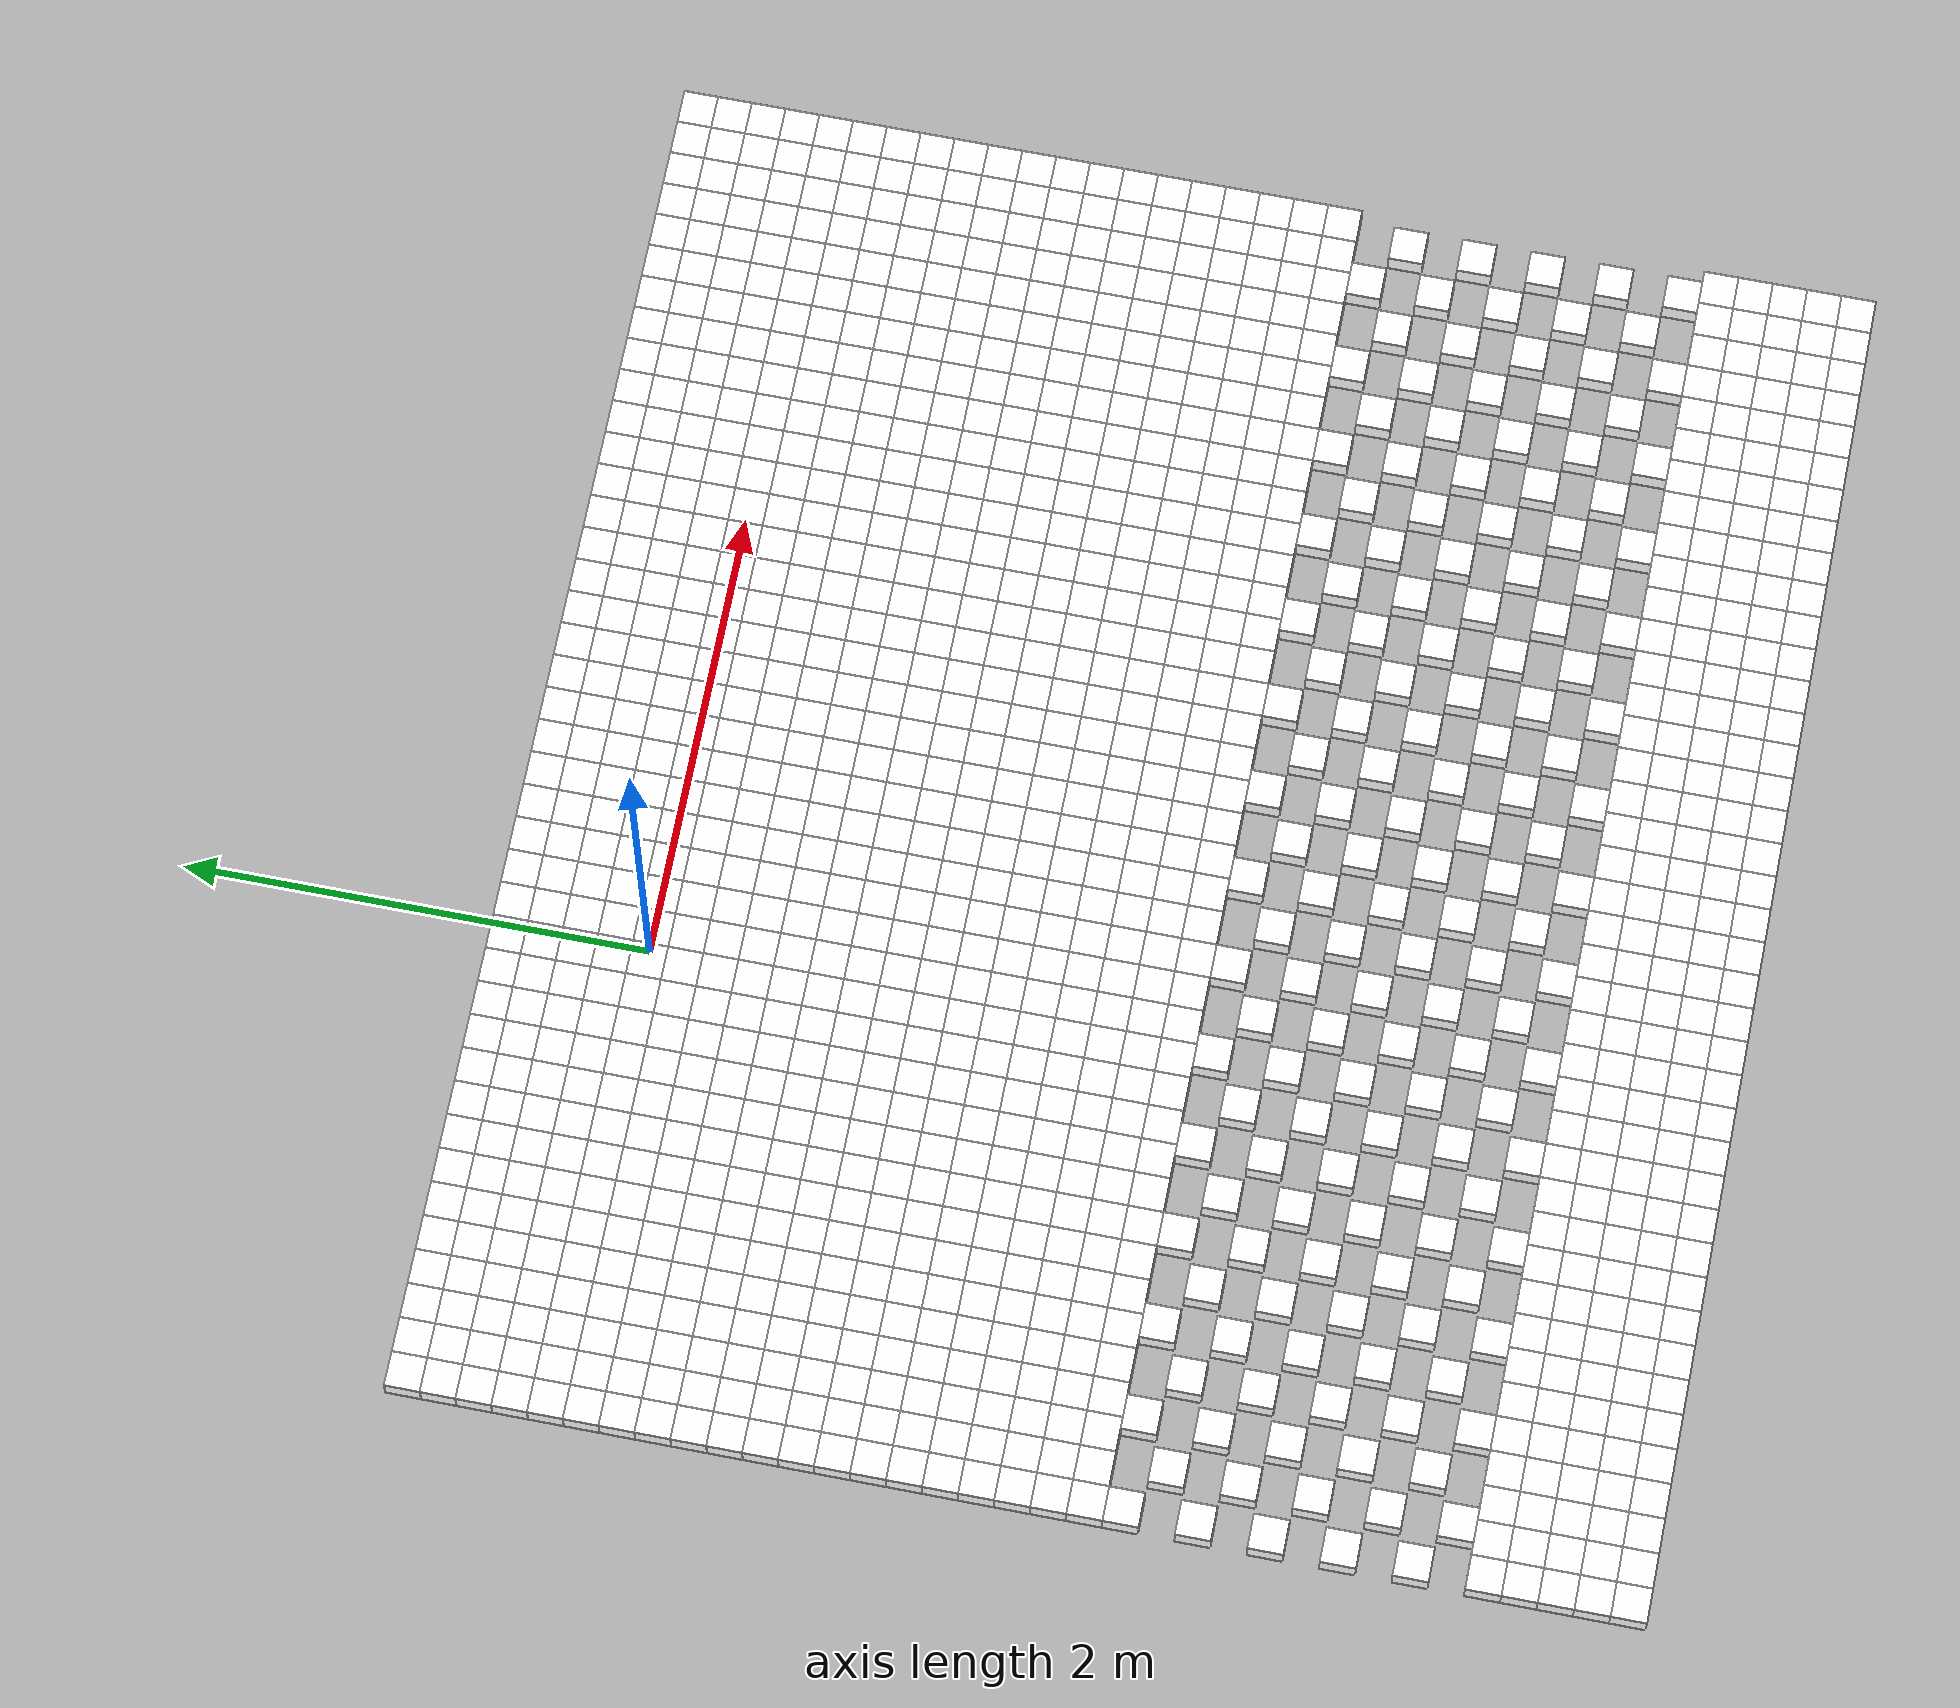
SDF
<sdf version="1.7">
  <world name="default">

    <!-- Need to be able to manipulate model state -->
    <plugin name="gazebo_ros_state" filename="libgazebo_ros_state.so">
      <ros>
        <namespace>/gazebo</namespace>
      </ros>

      <update_rate>1.0</update_rate>
    </plugin>

    <!-- Need to be able to manipulate model configuration -->
    <plugin name="gazebo_ros_properties" filename="libgazebo_ros_properties.so">
      <ros>
        <namespace>/gazebo</namespace>
      </ros>

      <update_rate>1.0</update_rate>
    </plugin>

    <physics type="ode">
    <max_step_size>0.001</max_step_size>
    <real_time_factor>1.0</real_time_factor>
    <real_time_update_rate>1000</real_time_update_rate>
    <gravity>0 0 -9.81</gravity>
        <ode>
            <solver>
            <type>quick</type>
            <iters>50</iters>
            <sor>1.3</sor>
            </solver>
            <constraints>
            <cfm>0.0</cfm>
            <erp>0.2</erp>
            <contact_max_correcting_vel>10.0</contact_max_correcting_vel>
            <contact_surface_layer>0.001</contact_surface_layer>
            </constraints>
        </ode>
    </physics>

    <scene>
    <sky>
        <clouds>
            <speed>12</speed>
        </clouds>
    </sky>
    </scene>
    <!-- A global light source -->
    <include>
        <uri>model://sun</uri>
    </include>
    <!-- A ground plane -->
    <model name="static_environment">
  <static>true</static>
  <link name="region_0">
    <pose>-2.0 0.6 0.0 0.0 0.0 4.7123</pose>
    <collision name="region_0_collision">
      <geometry>
        <box>
          <size>0.15 0.15 0.1</size>
        </box>
      </geometry>
      <surface>
        <friction>
          <ode>
            <mu>1.0</mu>
            <mu2>1.0</mu2>
          </ode>
        </friction>
      </surface>
    </collision>
    <visual name="region_0_visual">
      <geometry>
        <box>
          <size>0.15 0.15 0.1</size>
        </box>
      </geometry>
      <material>
        <ambient>1.0 1.0 1.0 1.0</ambient>
        <diffuse>1.0 1.0 1.0 1.0</diffuse>
      </material>
    </visual>
  </link>
  <link name="region_1">
    <pose>-2.0000133470576857 0.4500000005938132 0.0 0.0 0.0 4.7123</pose>
    <collision name="region_1_collision">
      <geometry>
        <box>
          <size>0.15 0.15 0.1</size>
        </box>
      </geometry>
      <surface>
        <friction>
          <ode>
            <mu>1.0</mu>
            <mu2>1.0</mu2>
          </ode>
        </friction>
      </surface>
    </collision>
    <visual name="region_1_visual">
      <geometry>
        <box>
          <size>0.15 0.15 0.1</size>
        </box>
      </geometry>
      <material>
        <ambient>1.0 1.0 1.0 1.0</ambient>
        <diffuse>1.0 1.0 1.0 1.0</diffuse>
      </material>
    </visual>
  </link>
  <link name="region_2">
    <pose>-2.000026694115372 0.3000000011876263 0.0 0.0 0.0 4.7123</pose>
    <collision name="region_2_collision">
      <geometry>
        <box>
          <size>0.15 0.15 0.1</size>
        </box>
      </geometry>
      <surface>
        <friction>
          <ode>
            <mu>1.0</mu>
            <mu2>1.0</mu2>
          </ode>
        </friction>
      </surface>
    </collision>
    <visual name="region_2_visual">
      <geometry>
        <box>
          <size>0.15 0.15 0.1</size>
        </box>
      </geometry>
      <material>
        <ambient>1.0 1.0 1.0 1.0</ambient>
        <diffuse>1.0 1.0 1.0 1.0</diffuse>
      </material>
    </visual>
  </link>
  <link name="region_3">
    <pose>-2.0000400411730577 0.15000000178143952 0.0 0.0 0.0 4.7123</pose>
    <collision name="region_3_collision">
      <geometry>
        <box>
          <size>0.15 0.15 0.1</size>
        </box>
      </geometry>
      <surface>
        <friction>
          <ode>
            <mu>1.0</mu>
            <mu2>1.0</mu2>
          </ode>
        </friction>
      </surface>
    </collision>
    <visual name="region_3_visual">
      <geometry>
        <box>
          <size>0.15 0.15 0.1</size>
        </box>
      </geometry>
      <material>
        <ambient>1.0 1.0 1.0 1.0</ambient>
        <diffuse>1.0 1.0 1.0 1.0</diffuse>
      </material>
    </visual>
  </link>
  <link name="region_4">
    <pose>-2.0000533882307434 2.375252661224181e-09 0.0 0.0 0.0 4.7123</pose>
    <collision name="region_4_collision">
      <geometry>
        <box>
          <size>0.15 0.15 0.1</size>
        </box>
      </geometry>
      <surface>
        <friction>
          <ode>
            <mu>1.0</mu>
            <mu2>1.0</mu2>
          </ode>
        </friction>
      </surface>
    </collision>
    <visual name="region_4_visual">
      <geometry>
        <box>
          <size>0.15 0.15 0.1</size>
        </box>
      </geometry>
      <material>
        <ambient>1.0 1.0 1.0 1.0</ambient>
        <diffuse>1.0 1.0 1.0 1.0</diffuse>
      </material>
    </visual>
  </link>
  <link name="region_5">
    <pose>-2.0000667352884296 -0.14999999703093414 0.0 0.0 0.0 4.7123</pose>
    <collision name="region_5_collision">
      <geometry>
        <box>
          <size>0.15 0.15 0.1</size>
        </box>
      </geometry>
      <surface>
        <friction>
          <ode>
            <mu>1.0</mu>
            <mu2>1.0</mu2>
          </ode>
        </friction>
      </surface>
    </collision>
    <visual name="region_5_visual">
      <geometry>
        <box>
          <size>0.15 0.15 0.1</size>
        </box>
      </geometry>
      <material>
        <ambient>1.0 1.0 1.0 1.0</ambient>
        <diffuse>1.0 1.0 1.0 1.0</diffuse>
      </material>
    </visual>
  </link>
  <link name="region_6">
    <pose>-2.0000800823461153 -0.29999999643712105 0.0 0.0 0.0 4.7123</pose>
    <collision name="region_6_collision">
      <geometry>
        <box>
          <size>0.15 0.15 0.1</size>
        </box>
      </geometry>
      <surface>
        <friction>
          <ode>
            <mu>1.0</mu>
            <mu2>1.0</mu2>
          </ode>
        </friction>
      </surface>
    </collision>
    <visual name="region_6_visual">
      <geometry>
        <box>
          <size>0.15 0.15 0.1</size>
        </box>
      </geometry>
      <material>
        <ambient>1.0 1.0 1.0 1.0</ambient>
        <diffuse>1.0 1.0 1.0 1.0</diffuse>
      </material>
    </visual>
  </link>
  <link name="region_7">
    <pose>-2.000093429403801 -0.44999999584330796 0.0 0.0 0.0 4.7123</pose>
    <collision name="region_7_collision">
      <geometry>
        <box>
          <size>0.15 0.15 0.1</size>
        </box>
      </geometry>
      <surface>
        <friction>
          <ode>
            <mu>1.0</mu>
            <mu2>1.0</mu2>
          </ode>
        </friction>
      </surface>
    </collision>
    <visual name="region_7_visual">
      <geometry>
        <box>
          <size>0.15 0.15 0.1</size>
        </box>
      </geometry>
      <material>
        <ambient>1.0 1.0 1.0 1.0</ambient>
        <diffuse>1.0 1.0 1.0 1.0</diffuse>
      </material>
    </visual>
  </link>
  <link name="region_8">
    <pose>-2.000106776461487 -0.5999999952494947 0.0 0.0 0.0 4.7123</pose>
    <collision name="region_8_collision">
      <geometry>
        <box>
          <size>0.15 0.15 0.1</size>
        </box>
      </geometry>
      <surface>
        <friction>
          <ode>
            <mu>1.0</mu>
            <mu2>1.0</mu2>
          </ode>
        </friction>
      </surface>
    </collision>
    <visual name="region_8_visual">
      <geometry>
        <box>
          <size>0.15 0.15 0.1</size>
        </box>
      </geometry>
      <material>
        <ambient>1.0 1.0 1.0 1.0</ambient>
        <diffuse>1.0 1.0 1.0 1.0</diffuse>
      </material>
    </visual>
  </link>
  <link name="region_9">
    <pose>-2.000120123519173 -0.7499999946556813 0.0 0.0 0.0 4.7123</pose>
    <collision name="region_9_collision">
      <geometry>
        <box>
          <size>0.15 0.15 0.1</size>
        </box>
      </geometry>
      <surface>
        <friction>
          <ode>
            <mu>1.0</mu>
            <mu2>1.0</mu2>
          </ode>
        </friction>
      </surface>
    </collision>
    <visual name="region_9_visual">
      <geometry>
        <box>
          <size>0.15 0.15 0.1</size>
        </box>
      </geometry>
      <material>
        <ambient>1.0 1.0 1.0 1.0</ambient>
        <diffuse>1.0 1.0 1.0 1.0</diffuse>
      </material>
    </visual>
  </link>
  <link name="region_10">
    <pose>-2.0001334705768588 -0.8999999940618683 0.0 0.0 0.0 4.7123</pose>
    <collision name="region_10_collision">
      <geometry>
        <box>
          <size>0.15 0.15 0.1</size>
        </box>
      </geometry>
      <surface>
        <friction>
          <ode>
            <mu>1.0</mu>
            <mu2>1.0</mu2>
          </ode>
        </friction>
      </surface>
    </collision>
    <visual name="region_10_visual">
      <geometry>
        <box>
          <size>0.15 0.15 0.1</size>
        </box>
      </geometry>
      <material>
        <ambient>1.0 1.0 1.0 1.0</ambient>
        <diffuse>1.0 1.0 1.0 1.0</diffuse>
      </material>
    </visual>
  </link>
  <link name="region_11">
    <pose>-2.0001468176345445 -1.049999993468055 0.0 0.0 0.0 4.7123</pose>
    <collision name="region_11_collision">
      <geometry>
        <box>
          <size>0.15 0.15 0.1</size>
        </box>
      </geometry>
      <surface>
        <friction>
          <ode>
            <mu>1.0</mu>
            <mu2>1.0</mu2>
          </ode>
        </friction>
      </surface>
    </collision>
    <visual name="region_11_visual">
      <geometry>
        <box>
          <size>0.15 0.15 0.1</size>
        </box>
      </geometry>
      <material>
        <ambient>1.0 1.0 1.0 1.0</ambient>
        <diffuse>1.0 1.0 1.0 1.0</diffuse>
      </material>
    </visual>
  </link>
  <link name="region_12">
    <pose>-2.0001601646922307 -1.1999999928742415 0.0 0.0 0.0 4.7123</pose>
    <collision name="region_12_collision">
      <geometry>
        <box>
          <size>0.15 0.15 0.1</size>
        </box>
      </geometry>
      <surface>
        <friction>
          <ode>
            <mu>1.0</mu>
            <mu2>1.0</mu2>
          </ode>
        </friction>
      </surface>
    </collision>
    <visual name="region_12_visual">
      <geometry>
        <box>
          <size>0.15 0.15 0.1</size>
        </box>
      </geometry>
      <material>
        <ambient>1.0 1.0 1.0 1.0</ambient>
        <diffuse>1.0 1.0 1.0 1.0</diffuse>
      </material>
    </visual>
  </link>
  <link name="region_13">
    <pose>-2.0001735117499164 -1.3499999922804284 0.0 0.0 0.0 4.7123</pose>
    <collision name="region_13_collision">
      <geometry>
        <box>
          <size>0.15 0.15 0.1</size>
        </box>
      </geometry>
      <surface>
        <friction>
          <ode>
            <mu>1.0</mu>
            <mu2>1.0</mu2>
          </ode>
        </friction>
      </surface>
    </collision>
    <visual name="region_13_visual">
      <geometry>
        <box>
          <size>0.15 0.15 0.1</size>
        </box>
      </geometry>
      <material>
        <ambient>1.0 1.0 1.0 1.0</ambient>
        <diffuse>1.0 1.0 1.0 1.0</diffuse>
      </material>
    </visual>
  </link>
  <link name="region_14">
    <pose>-2.000186858807602 -1.4999999916866154 0.0 0.0 0.0 4.7123</pose>
    <collision name="region_14_collision">
      <geometry>
        <box>
          <size>0.15 0.15 0.1</size>
        </box>
      </geometry>
      <surface>
        <friction>
          <ode>
            <mu>1.0</mu>
            <mu2>1.0</mu2>
          </ode>
        </friction>
      </surface>
    </collision>
    <visual name="region_14_visual">
      <geometry>
        <box>
          <size>0.15 0.15 0.1</size>
        </box>
      </geometry>
      <material>
        <ambient>1.0 1.0 1.0 1.0</ambient>
        <diffuse>1.0 1.0 1.0 1.0</diffuse>
      </material>
    </visual>
  </link>
  <link name="region_15">
    <pose>-2.0002002058652883 -1.6499999910928018 0.0 0.0 0.0 4.7123</pose>
    <collision name="region_15_collision">
      <geometry>
        <box>
          <size>0.15 0.15 0.1</size>
        </box>
      </geometry>
      <surface>
        <friction>
          <ode>
            <mu>1.0</mu>
            <mu2>1.0</mu2>
          </ode>
        </friction>
      </surface>
    </collision>
    <visual name="region_15_visual">
      <geometry>
        <box>
          <size>0.15 0.15 0.1</size>
        </box>
      </geometry>
      <material>
        <ambient>1.0 1.0 1.0 1.0</ambient>
        <diffuse>1.0 1.0 1.0 1.0</diffuse>
      </material>
    </visual>
  </link>
  <link name="region_16">
    <pose>-2.000213552922974 -1.7999999904989887 0.0 0.0 0.0 4.7123</pose>
    <collision name="region_16_collision">
      <geometry>
        <box>
          <size>0.15 0.15 0.1</size>
        </box>
      </geometry>
      <surface>
        <friction>
          <ode>
            <mu>1.0</mu>
            <mu2>1.0</mu2>
          </ode>
        </friction>
      </surface>
    </collision>
    <visual name="region_16_visual">
      <geometry>
        <box>
          <size>0.15 0.15 0.1</size>
        </box>
      </geometry>
      <material>
        <ambient>1.0 1.0 1.0 1.0</ambient>
        <diffuse>1.0 1.0 1.0 1.0</diffuse>
      </material>
    </visual>
  </link>
  <link name="region_17">
    <pose>-2.00022689998066 -1.9499999899051756 0.0 0.0 0.0 4.7123</pose>
    <collision name="region_17_collision">
      <geometry>
        <box>
          <size>0.15 0.15 0.1</size>
        </box>
      </geometry>
      <surface>
        <friction>
          <ode>
            <mu>1.0</mu>
            <mu2>1.0</mu2>
          </ode>
        </friction>
      </surface>
    </collision>
    <visual name="region_17_visual">
      <geometry>
        <box>
          <size>0.15 0.15 0.1</size>
        </box>
      </geometry>
      <material>
        <ambient>1.0 1.0 1.0 1.0</ambient>
        <diffuse>1.0 1.0 1.0 1.0</diffuse>
      </material>
    </visual>
  </link>
  <link name="region_18">
    <pose>-2.0002402470383456 -2.099999989311362 0.0 0.0 0.0 4.7123</pose>
    <collision name="region_18_collision">
      <geometry>
        <box>
          <size>0.15 0.15 0.1</size>
        </box>
      </geometry>
      <surface>
        <friction>
          <ode>
            <mu>1.0</mu>
            <mu2>1.0</mu2>
          </ode>
        </friction>
      </surface>
    </collision>
    <visual name="region_18_visual">
      <geometry>
        <box>
          <size>0.15 0.15 0.1</size>
        </box>
      </geometry>
      <material>
        <ambient>1.0 1.0 1.0 1.0</ambient>
        <diffuse>1.0 1.0 1.0 1.0</diffuse>
      </material>
    </visual>
  </link>
  <link name="region_19">
    <pose>-2.0002535940960318 -2.249999988717549 0.0 0.0 0.0 4.7123</pose>
    <collision name="region_19_collision">
      <geometry>
        <box>
          <size>0.15 0.15 0.1</size>
        </box>
      </geometry>
      <surface>
        <friction>
          <ode>
            <mu>1.0</mu>
            <mu2>1.0</mu2>
          </ode>
        </friction>
      </surface>
    </collision>
    <visual name="region_19_visual">
      <geometry>
        <box>
          <size>0.15 0.15 0.1</size>
        </box>
      </geometry>
      <material>
        <ambient>1.0 1.0 1.0 1.0</ambient>
        <diffuse>1.0 1.0 1.0 1.0</diffuse>
      </material>
    </visual>
  </link>
  <link name="region_20">
    <pose>-1.850000000593813 0.5999866529423141 0.0 0.0 0.0 4.7123</pose>
    <collision name="region_20_collision">
      <geometry>
        <box>
          <size>0.15 0.15 0.1</size>
        </box>
      </geometry>
      <surface>
        <friction>
          <ode>
            <mu>1.0</mu>
            <mu2>1.0</mu2>
          </ode>
        </friction>
      </surface>
    </collision>
    <visual name="region_20_visual">
      <geometry>
        <box>
          <size>0.15 0.15 0.1</size>
        </box>
      </geometry>
      <material>
        <ambient>1.0 1.0 1.0 1.0</ambient>
        <diffuse>1.0 1.0 1.0 1.0</diffuse>
      </material>
    </visual>
  </link>
  <link name="region_21">
    <pose>-1.850013347651499 0.44998665353612727 0.0 0.0 0.0 4.7123</pose>
    <collision name="region_21_collision">
      <geometry>
        <box>
          <size>0.15 0.15 0.1</size>
        </box>
      </geometry>
      <surface>
        <friction>
          <ode>
            <mu>1.0</mu>
            <mu2>1.0</mu2>
          </ode>
        </friction>
      </surface>
    </collision>
    <visual name="region_21_visual">
      <geometry>
        <box>
          <size>0.15 0.15 0.1</size>
        </box>
      </geometry>
      <material>
        <ambient>1.0 1.0 1.0 1.0</ambient>
        <diffuse>1.0 1.0 1.0 1.0</diffuse>
      </material>
    </visual>
  </link>
  <link name="region_22">
    <pose>-1.850026694709185 0.29998665412994047 0.0 0.0 0.0 4.7123</pose>
    <collision name="region_22_collision">
      <geometry>
        <box>
          <size>0.15 0.15 0.1</size>
        </box>
      </geometry>
      <surface>
        <friction>
          <ode>
            <mu>1.0</mu>
            <mu2>1.0</mu2>
          </ode>
        </friction>
      </surface>
    </collision>
    <visual name="region_22_visual">
      <geometry>
        <box>
          <size>0.15 0.15 0.1</size>
        </box>
      </geometry>
      <material>
        <ambient>1.0 1.0 1.0 1.0</ambient>
        <diffuse>1.0 1.0 1.0 1.0</diffuse>
      </material>
    </visual>
  </link>
  <link name="region_23">
    <pose>-1.8500400417668708 0.14998665472375367 0.0 0.0 0.0 4.7123</pose>
    <collision name="region_23_collision">
      <geometry>
        <box>
          <size>0.15 0.15 0.1</size>
        </box>
      </geometry>
      <surface>
        <friction>
          <ode>
            <mu>1.0</mu>
            <mu2>1.0</mu2>
          </ode>
        </friction>
      </surface>
    </collision>
    <visual name="region_23_visual">
      <geometry>
        <box>
          <size>0.15 0.15 0.1</size>
        </box>
      </geometry>
      <material>
        <ambient>1.0 1.0 1.0 1.0</ambient>
        <diffuse>1.0 1.0 1.0 1.0</diffuse>
      </material>
    </visual>
  </link>
  <link name="region_24">
    <pose>-1.8500533888245567 -1.3344682433191757e-05 0.0 0.0 0.0 4.7123</pose>
    <collision name="region_24_collision">
      <geometry>
        <box>
          <size>0.15 0.15 0.1</size>
        </box>
      </geometry>
      <surface>
        <friction>
          <ode>
            <mu>1.0</mu>
            <mu2>1.0</mu2>
          </ode>
        </friction>
      </surface>
    </collision>
    <visual name="region_24_visual">
      <geometry>
        <box>
          <size>0.15 0.15 0.1</size>
        </box>
      </geometry>
      <material>
        <ambient>1.0 1.0 1.0 1.0</ambient>
        <diffuse>1.0 1.0 1.0 1.0</diffuse>
      </material>
    </visual>
  </link>
  <link name="region_25">
    <pose>-1.8500667358822425 -0.15001334408862 0.0 0.0 0.0 4.7123</pose>
    <collision name="region_25_collision">
      <geometry>
        <box>
          <size>0.15 0.15 0.1</size>
        </box>
      </geometry>
      <surface>
        <friction>
          <ode>
            <mu>1.0</mu>
            <mu2>1.0</mu2>
          </ode>
        </friction>
      </surface>
    </collision>
    <visual name="region_25_visual">
      <geometry>
        <box>
          <size>0.15 0.15 0.1</size>
        </box>
      </geometry>
      <material>
        <ambient>1.0 1.0 1.0 1.0</ambient>
        <diffuse>1.0 1.0 1.0 1.0</diffuse>
      </material>
    </visual>
  </link>
  <link name="region_26">
    <pose>-1.8500800829399284 -0.3000133434948069 0.0 0.0 0.0 4.7123</pose>
    <collision name="region_26_collision">
      <geometry>
        <box>
          <size>0.15 0.15 0.1</size>
        </box>
      </geometry>
      <surface>
        <friction>
          <ode>
            <mu>1.0</mu>
            <mu2>1.0</mu2>
          </ode>
        </friction>
      </surface>
    </collision>
    <visual name="region_26_visual">
      <geometry>
        <box>
          <size>0.15 0.15 0.1</size>
        </box>
      </geometry>
      <material>
        <ambient>1.0 1.0 1.0 1.0</ambient>
        <diffuse>1.0 1.0 1.0 1.0</diffuse>
      </material>
    </visual>
  </link>
  <link name="region_27">
    <pose>-1.8500934299976144 -0.45001334290099393 0.0 0.0 0.0 4.7123</pose>
    <collision name="region_27_collision">
      <geometry>
        <box>
          <size>0.15 0.15 0.1</size>
        </box>
      </geometry>
      <surface>
        <friction>
          <ode>
            <mu>1.0</mu>
            <mu2>1.0</mu2>
          </ode>
        </friction>
      </surface>
    </collision>
    <visual name="region_27_visual">
      <geometry>
        <box>
          <size>0.15 0.15 0.1</size>
        </box>
      </geometry>
      <material>
        <ambient>1.0 1.0 1.0 1.0</ambient>
        <diffuse>1.0 1.0 1.0 1.0</diffuse>
      </material>
    </visual>
  </link>
  <link name="region_28">
    <pose>-1.8501067770553001 -0.6000133423071806 0.0 0.0 0.0 4.7123</pose>
    <collision name="region_28_collision">
      <geometry>
        <box>
          <size>0.15 0.15 0.1</size>
        </box>
      </geometry>
      <surface>
        <friction>
          <ode>
            <mu>1.0</mu>
            <mu2>1.0</mu2>
          </ode>
        </friction>
      </surface>
    </collision>
    <visual name="region_28_visual">
      <geometry>
        <box>
          <size>0.15 0.15 0.1</size>
        </box>
      </geometry>
      <material>
        <ambient>1.0 1.0 1.0 1.0</ambient>
        <diffuse>1.0 1.0 1.0 1.0</diffuse>
      </material>
    </visual>
  </link>
  <link name="region_29">
    <pose>-1.850120124112986 -0.7500133417133673 0.0 0.0 0.0 4.7123</pose>
    <collision name="region_29_collision">
      <geometry>
        <box>
          <size>0.15 0.15 0.1</size>
        </box>
      </geometry>
      <surface>
        <friction>
          <ode>
            <mu>1.0</mu>
            <mu2>1.0</mu2>
          </ode>
        </friction>
      </surface>
    </collision>
    <visual name="region_29_visual">
      <geometry>
        <box>
          <size>0.15 0.15 0.1</size>
        </box>
      </geometry>
      <material>
        <ambient>1.0 1.0 1.0 1.0</ambient>
        <diffuse>1.0 1.0 1.0 1.0</diffuse>
      </material>
    </visual>
  </link>
  <link name="region_30">
    <pose>-1.8501334711706718 -0.9000133411195542 0.0 0.0 0.0 4.7123</pose>
    <collision name="region_30_collision">
      <geometry>
        <box>
          <size>0.15 0.15 0.1</size>
        </box>
      </geometry>
      <surface>
        <friction>
          <ode>
            <mu>1.0</mu>
            <mu2>1.0</mu2>
          </ode>
        </friction>
      </surface>
    </collision>
    <visual name="region_30_visual">
      <geometry>
        <box>
          <size>0.15 0.15 0.1</size>
        </box>
      </geometry>
      <material>
        <ambient>1.0 1.0 1.0 1.0</ambient>
        <diffuse>1.0 1.0 1.0 1.0</diffuse>
      </material>
    </visual>
  </link>
  <link name="region_31">
    <pose>-1.8501468182283578 -1.0500133405257408 0.0 0.0 0.0 4.7123</pose>
    <collision name="region_31_collision">
      <geometry>
        <box>
          <size>0.15 0.15 0.1</size>
        </box>
      </geometry>
      <surface>
        <friction>
          <ode>
            <mu>1.0</mu>
            <mu2>1.0</mu2>
          </ode>
        </friction>
      </surface>
    </collision>
    <visual name="region_31_visual">
      <geometry>
        <box>
          <size>0.15 0.15 0.1</size>
        </box>
      </geometry>
      <material>
        <ambient>1.0 1.0 1.0 1.0</ambient>
        <diffuse>1.0 1.0 1.0 1.0</diffuse>
      </material>
    </visual>
  </link>
  <link name="region_32">
    <pose>-1.8501601652860438 -1.2000133399319277 0.0 0.0 0.0 4.7123</pose>
    <collision name="region_32_collision">
      <geometry>
        <box>
          <size>0.15 0.15 0.1</size>
        </box>
      </geometry>
      <surface>
        <friction>
          <ode>
            <mu>1.0</mu>
            <mu2>1.0</mu2>
          </ode>
        </friction>
      </surface>
    </collision>
    <visual name="region_32_visual">
      <geometry>
        <box>
          <size>0.15 0.15 0.1</size>
        </box>
      </geometry>
      <material>
        <ambient>1.0 1.0 1.0 1.0</ambient>
        <diffuse>1.0 1.0 1.0 1.0</diffuse>
      </material>
    </visual>
  </link>
  <link name="region_33">
    <pose>-1.8501735123437295 -1.3500133393381142 0.0 0.0 0.0 4.7123</pose>
    <collision name="region_33_collision">
      <geometry>
        <box>
          <size>0.15 0.15 0.1</size>
        </box>
      </geometry>
      <surface>
        <friction>
          <ode>
            <mu>1.0</mu>
            <mu2>1.0</mu2>
          </ode>
        </friction>
      </surface>
    </collision>
    <visual name="region_33_visual">
      <geometry>
        <box>
          <size>0.15 0.15 0.1</size>
        </box>
      </geometry>
      <material>
        <ambient>1.0 1.0 1.0 1.0</ambient>
        <diffuse>1.0 1.0 1.0 1.0</diffuse>
      </material>
    </visual>
  </link>
  <link name="region_34">
    <pose>-1.8501868594014155 -1.500013338744301 0.0 0.0 0.0 4.7123</pose>
    <collision name="region_34_collision">
      <geometry>
        <box>
          <size>0.15 0.15 0.1</size>
        </box>
      </geometry>
      <surface>
        <friction>
          <ode>
            <mu>1.0</mu>
            <mu2>1.0</mu2>
          </ode>
        </friction>
      </surface>
    </collision>
    <visual name="region_34_visual">
      <geometry>
        <box>
          <size>0.15 0.15 0.1</size>
        </box>
      </geometry>
      <material>
        <ambient>1.0 1.0 1.0 1.0</ambient>
        <diffuse>1.0 1.0 1.0 1.0</diffuse>
      </material>
    </visual>
  </link>
  <link name="region_35">
    <pose>-1.8502002064591012 -1.6500133381504876 0.0 0.0 0.0 4.7123</pose>
    <collision name="region_35_collision">
      <geometry>
        <box>
          <size>0.15 0.15 0.1</size>
        </box>
      </geometry>
      <surface>
        <friction>
          <ode>
            <mu>1.0</mu>
            <mu2>1.0</mu2>
          </ode>
        </friction>
      </surface>
    </collision>
    <visual name="region_35_visual">
      <geometry>
        <box>
          <size>0.15 0.15 0.1</size>
        </box>
      </geometry>
      <material>
        <ambient>1.0 1.0 1.0 1.0</ambient>
        <diffuse>1.0 1.0 1.0 1.0</diffuse>
      </material>
    </visual>
  </link>
  <link name="region_36">
    <pose>-1.8502135535167872 -1.8000133375566745 0.0 0.0 0.0 4.7123</pose>
    <collision name="region_36_collision">
      <geometry>
        <box>
          <size>0.15 0.15 0.1</size>
        </box>
      </geometry>
      <surface>
        <friction>
          <ode>
            <mu>1.0</mu>
            <mu2>1.0</mu2>
          </ode>
        </friction>
      </surface>
    </collision>
    <visual name="region_36_visual">
      <geometry>
        <box>
          <size>0.15 0.15 0.1</size>
        </box>
      </geometry>
      <material>
        <ambient>1.0 1.0 1.0 1.0</ambient>
        <diffuse>1.0 1.0 1.0 1.0</diffuse>
      </material>
    </visual>
  </link>
  <link name="region_37">
    <pose>-1.8502269005744731 -1.9500133369628614 0.0 0.0 0.0 4.7123</pose>
    <collision name="region_37_collision">
      <geometry>
        <box>
          <size>0.15 0.15 0.1</size>
        </box>
      </geometry>
      <surface>
        <friction>
          <ode>
            <mu>1.0</mu>
            <mu2>1.0</mu2>
          </ode>
        </friction>
      </surface>
    </collision>
    <visual name="region_37_visual">
      <geometry>
        <box>
          <size>0.15 0.15 0.1</size>
        </box>
      </geometry>
      <material>
        <ambient>1.0 1.0 1.0 1.0</ambient>
        <diffuse>1.0 1.0 1.0 1.0</diffuse>
      </material>
    </visual>
  </link>
  <link name="region_38">
    <pose>-1.8502402476321589 -2.100013336369048 0.0 0.0 0.0 4.7123</pose>
    <collision name="region_38_collision">
      <geometry>
        <box>
          <size>0.15 0.15 0.1</size>
        </box>
      </geometry>
      <surface>
        <friction>
          <ode>
            <mu>1.0</mu>
            <mu2>1.0</mu2>
          </ode>
        </friction>
      </surface>
    </collision>
    <visual name="region_38_visual">
      <geometry>
        <box>
          <size>0.15 0.15 0.1</size>
        </box>
      </geometry>
      <material>
        <ambient>1.0 1.0 1.0 1.0</ambient>
        <diffuse>1.0 1.0 1.0 1.0</diffuse>
      </material>
    </visual>
  </link>
  <link name="region_39">
    <pose>-1.8502535946898448 -2.2500133357752348 0.0 0.0 0.0 4.7123</pose>
    <collision name="region_39_collision">
      <geometry>
        <box>
          <size>0.15 0.15 0.1</size>
        </box>
      </geometry>
      <surface>
        <friction>
          <ode>
            <mu>1.0</mu>
            <mu2>1.0</mu2>
          </ode>
        </friction>
      </surface>
    </collision>
    <visual name="region_39_visual">
      <geometry>
        <box>
          <size>0.15 0.15 0.1</size>
        </box>
      </geometry>
      <material>
        <ambient>1.0 1.0 1.0 1.0</ambient>
        <diffuse>1.0 1.0 1.0 1.0</diffuse>
      </material>
    </visual>
  </link>
  <link name="region_40">
    <pose>-1.7000000011876264 0.5999733058846283 0.0 0.0 0.0 4.7123</pose>
    <collision name="region_40_collision">
      <geometry>
        <box>
          <size>0.15 0.15 0.1</size>
        </box>
      </geometry>
      <surface>
        <friction>
          <ode>
            <mu>1.0</mu>
            <mu2>1.0</mu2>
          </ode>
        </friction>
      </surface>
    </collision>
    <visual name="region_40_visual">
      <geometry>
        <box>
          <size>0.15 0.15 0.1</size>
        </box>
      </geometry>
      <material>
        <ambient>1.0 1.0 1.0 1.0</ambient>
        <diffuse>1.0 1.0 1.0 1.0</diffuse>
      </material>
    </visual>
  </link>
  <link name="region_41">
    <pose>-1.7000133482453121 0.44997330647844136 0.0 0.0 0.0 4.7123</pose>
    <collision name="region_41_collision">
      <geometry>
        <box>
          <size>0.15 0.15 0.1</size>
        </box>
      </geometry>
      <surface>
        <friction>
          <ode>
            <mu>1.0</mu>
            <mu2>1.0</mu2>
          </ode>
        </friction>
      </surface>
    </collision>
    <visual name="region_41_visual">
      <geometry>
        <box>
          <size>0.15 0.15 0.1</size>
        </box>
      </geometry>
      <material>
        <ambient>1.0 1.0 1.0 1.0</ambient>
        <diffuse>1.0 1.0 1.0 1.0</diffuse>
      </material>
    </visual>
  </link>
  <link name="region_42">
    <pose>-1.700026695302998 0.29997330707225456 0.0 0.0 0.0 4.7123</pose>
    <collision name="region_42_collision">
      <geometry>
        <box>
          <size>0.15 0.15 0.1</size>
        </box>
      </geometry>
      <surface>
        <friction>
          <ode>
            <mu>1.0</mu>
            <mu2>1.0</mu2>
          </ode>
        </friction>
      </surface>
    </collision>
    <visual name="region_42_visual">
      <geometry>
        <box>
          <size>0.15 0.15 0.1</size>
        </box>
      </geometry>
      <material>
        <ambient>1.0 1.0 1.0 1.0</ambient>
        <diffuse>1.0 1.0 1.0 1.0</diffuse>
      </material>
    </visual>
  </link>
  <link name="region_43">
    <pose>-1.7000400423606838 0.14997330766606776 0.0 0.0 0.0 4.7123</pose>
    <collision name="region_43_collision">
      <geometry>
        <box>
          <size>0.15 0.15 0.1</size>
        </box>
      </geometry>
      <surface>
        <friction>
          <ode>
            <mu>1.0</mu>
            <mu2>1.0</mu2>
          </ode>
        </friction>
      </surface>
    </collision>
    <visual name="region_43_visual">
      <geometry>
        <box>
          <size>0.15 0.15 0.1</size>
        </box>
      </geometry>
      <material>
        <ambient>1.0 1.0 1.0 1.0</ambient>
        <diffuse>1.0 1.0 1.0 1.0</diffuse>
      </material>
    </visual>
  </link>
  <link name="region_44">
    <pose>-1.7000533894183698 -2.6691740119044738e-05 0.0 0.0 0.0 4.7123</pose>
    <collision name="region_44_collision">
      <geometry>
        <box>
          <size>0.15 0.15 0.1</size>
        </box>
      </geometry>
      <surface>
        <friction>
          <ode>
            <mu>1.0</mu>
            <mu2>1.0</mu2>
          </ode>
        </friction>
      </surface>
    </collision>
    <visual name="region_44_visual">
      <geometry>
        <box>
          <size>0.15 0.15 0.1</size>
        </box>
      </geometry>
      <material>
        <ambient>1.0 1.0 1.0 1.0</ambient>
        <diffuse>1.0 1.0 1.0 1.0</diffuse>
      </material>
    </visual>
  </link>
  <link name="region_45">
    <pose>-1.7000667364760558 -0.15002669114630585 0.0 0.0 0.0 4.7123</pose>
    <collision name="region_45_collision">
      <geometry>
        <box>
          <size>0.15 0.15 0.1</size>
        </box>
      </geometry>
      <surface>
        <friction>
          <ode>
            <mu>1.0</mu>
            <mu2>1.0</mu2>
          </ode>
        </friction>
      </surface>
    </collision>
    <visual name="region_45_visual">
      <geometry>
        <box>
          <size>0.15 0.15 0.1</size>
        </box>
      </geometry>
      <material>
        <ambient>1.0 1.0 1.0 1.0</ambient>
        <diffuse>1.0 1.0 1.0 1.0</diffuse>
      </material>
    </visual>
  </link>
  <link name="region_46">
    <pose>-1.7000800835337415 -0.30002669055249276 0.0 0.0 0.0 4.7123</pose>
    <collision name="region_46_collision">
      <geometry>
        <box>
          <size>0.15 0.15 0.1</size>
        </box>
      </geometry>
      <surface>
        <friction>
          <ode>
            <mu>1.0</mu>
            <mu2>1.0</mu2>
          </ode>
        </friction>
      </surface>
    </collision>
    <visual name="region_46_visual">
      <geometry>
        <box>
          <size>0.15 0.15 0.1</size>
        </box>
      </geometry>
      <material>
        <ambient>1.0 1.0 1.0 1.0</ambient>
        <diffuse>1.0 1.0 1.0 1.0</diffuse>
      </material>
    </visual>
  </link>
  <link name="region_47">
    <pose>-1.7000934305914275 -0.45002668995867967 0.0 0.0 0.0 4.7123</pose>
    <collision name="region_47_collision">
      <geometry>
        <box>
          <size>0.15 0.15 0.1</size>
        </box>
      </geometry>
      <surface>
        <friction>
          <ode>
            <mu>1.0</mu>
            <mu2>1.0</mu2>
          </ode>
        </friction>
      </surface>
    </collision>
    <visual name="region_47_visual">
      <geometry>
        <box>
          <size>0.15 0.15 0.1</size>
        </box>
      </geometry>
      <material>
        <ambient>1.0 1.0 1.0 1.0</ambient>
        <diffuse>1.0 1.0 1.0 1.0</diffuse>
      </material>
    </visual>
  </link>
  <link name="region_48">
    <pose>-1.7001067776491134 -0.6000266893648664 0.0 0.0 0.0 4.7123</pose>
    <collision name="region_48_collision">
      <geometry>
        <box>
          <size>0.15 0.15 0.1</size>
        </box>
      </geometry>
      <surface>
        <friction>
          <ode>
            <mu>1.0</mu>
            <mu2>1.0</mu2>
          </ode>
        </friction>
      </surface>
    </collision>
    <visual name="region_48_visual">
      <geometry>
        <box>
          <size>0.15 0.15 0.1</size>
        </box>
      </geometry>
      <material>
        <ambient>1.0 1.0 1.0 1.0</ambient>
        <diffuse>1.0 1.0 1.0 1.0</diffuse>
      </material>
    </visual>
  </link>
  <link name="region_49">
    <pose>-1.7001201247067992 -0.750026688771053 0.0 0.0 0.0 4.7123</pose>
    <collision name="region_49_collision">
      <geometry>
        <box>
          <size>0.15 0.15 0.1</size>
        </box>
      </geometry>
      <surface>
        <friction>
          <ode>
            <mu>1.0</mu>
            <mu2>1.0</mu2>
          </ode>
        </friction>
      </surface>
    </collision>
    <visual name="region_49_visual">
      <geometry>
        <box>
          <size>0.15 0.15 0.1</size>
        </box>
      </geometry>
      <material>
        <ambient>1.0 1.0 1.0 1.0</ambient>
        <diffuse>1.0 1.0 1.0 1.0</diffuse>
      </material>
    </visual>
  </link>
  <link name="region_50">
    <pose>-1.7001334717644851 -0.90002668817724 0.0 0.0 0.0 4.7123</pose>
    <collision name="region_50_collision">
      <geometry>
        <box>
          <size>0.15 0.15 0.1</size>
        </box>
      </geometry>
      <surface>
        <friction>
          <ode>
            <mu>1.0</mu>
            <mu2>1.0</mu2>
          </ode>
        </friction>
      </surface>
    </collision>
    <visual name="region_50_visual">
      <geometry>
        <box>
          <size>0.15 0.15 0.1</size>
        </box>
      </geometry>
      <material>
        <ambient>1.0 1.0 1.0 1.0</ambient>
        <diffuse>1.0 1.0 1.0 1.0</diffuse>
      </material>
    </visual>
  </link>
  <link name="region_51">
    <pose>-1.7001468188221711 -1.0500266875834265 0.0 0.0 0.0 4.7123</pose>
    <collision name="region_51_collision">
      <geometry>
        <box>
          <size>0.15 0.15 0.1</size>
        </box>
      </geometry>
      <surface>
        <friction>
          <ode>
            <mu>1.0</mu>
            <mu2>1.0</mu2>
          </ode>
        </friction>
      </surface>
    </collision>
    <visual name="region_51_visual">
      <geometry>
        <box>
          <size>0.15 0.15 0.1</size>
        </box>
      </geometry>
      <material>
        <ambient>1.0 1.0 1.0 1.0</ambient>
        <diffuse>1.0 1.0 1.0 1.0</diffuse>
      </material>
    </visual>
  </link>
  <link name="region_52">
    <pose>-1.7001601658798569 -1.2000266869896135 0.0 0.0 0.0 4.7123</pose>
    <collision name="region_52_collision">
      <geometry>
        <box>
          <size>0.15 0.15 0.1</size>
        </box>
      </geometry>
      <surface>
        <friction>
          <ode>
            <mu>1.0</mu>
            <mu2>1.0</mu2>
          </ode>
        </friction>
      </surface>
    </collision>
    <visual name="region_52_visual">
      <geometry>
        <box>
          <size>0.15 0.15 0.1</size>
        </box>
      </geometry>
      <material>
        <ambient>1.0 1.0 1.0 1.0</ambient>
        <diffuse>1.0 1.0 1.0 1.0</diffuse>
      </material>
    </visual>
  </link>
  <link name="region_53">
    <pose>-1.7001735129375426 -1.3500266863958 0.0 0.0 0.0 4.7123</pose>
    <collision name="region_53_collision">
      <geometry>
        <box>
          <size>0.15 0.15 0.1</size>
        </box>
      </geometry>
      <surface>
        <friction>
          <ode>
            <mu>1.0</mu>
            <mu2>1.0</mu2>
          </ode>
        </friction>
      </surface>
    </collision>
    <visual name="region_53_visual">
      <geometry>
        <box>
          <size>0.15 0.15 0.1</size>
        </box>
      </geometry>
      <material>
        <ambient>1.0 1.0 1.0 1.0</ambient>
        <diffuse>1.0 1.0 1.0 1.0</diffuse>
      </material>
    </visual>
  </link>
  <link name="region_54">
    <pose>-1.7001868599952286 -1.5000266858019873 0.0 0.0 0.0 4.7123</pose>
    <collision name="region_54_collision">
      <geometry>
        <box>
          <size>0.15 0.15 0.1</size>
        </box>
      </geometry>
      <surface>
        <friction>
          <ode>
            <mu>1.0</mu>
            <mu2>1.0</mu2>
          </ode>
        </friction>
      </surface>
    </collision>
    <visual name="region_54_visual">
      <geometry>
        <box>
          <size>0.15 0.15 0.1</size>
        </box>
      </geometry>
      <material>
        <ambient>1.0 1.0 1.0 1.0</ambient>
        <diffuse>1.0 1.0 1.0 1.0</diffuse>
      </material>
    </visual>
  </link>
  <link name="region_55">
    <pose>-1.7002002070529145 -1.6500266852081737 0.0 0.0 0.0 4.7123</pose>
    <collision name="region_55_collision">
      <geometry>
        <box>
          <size>0.15 0.15 0.1</size>
        </box>
      </geometry>
      <surface>
        <friction>
          <ode>
            <mu>1.0</mu>
            <mu2>1.0</mu2>
          </ode>
        </friction>
      </surface>
    </collision>
    <visual name="region_55_visual">
      <geometry>
        <box>
          <size>0.15 0.15 0.1</size>
        </box>
      </geometry>
      <material>
        <ambient>1.0 1.0 1.0 1.0</ambient>
        <diffuse>1.0 1.0 1.0 1.0</diffuse>
      </material>
    </visual>
  </link>
  <link name="region_56">
    <pose>-1.7002135541106003 -1.8000266846143607 0.0 0.0 0.0 4.7123</pose>
    <collision name="region_56_collision">
      <geometry>
        <box>
          <size>0.15 0.15 0.1</size>
        </box>
      </geometry>
      <surface>
        <friction>
          <ode>
            <mu>1.0</mu>
            <mu2>1.0</mu2>
          </ode>
        </friction>
      </surface>
    </collision>
    <visual name="region_56_visual">
      <geometry>
        <box>
          <size>0.15 0.15 0.1</size>
        </box>
      </geometry>
      <material>
        <ambient>1.0 1.0 1.0 1.0</ambient>
        <diffuse>1.0 1.0 1.0 1.0</diffuse>
      </material>
    </visual>
  </link>
  <link name="region_57">
    <pose>-1.7002269011682862 -1.9500266840205476 0.0 0.0 0.0 4.7123</pose>
    <collision name="region_57_collision">
      <geometry>
        <box>
          <size>0.15 0.15 0.1</size>
        </box>
      </geometry>
      <surface>
        <friction>
          <ode>
            <mu>1.0</mu>
            <mu2>1.0</mu2>
          </ode>
        </friction>
      </surface>
    </collision>
    <visual name="region_57_visual">
      <geometry>
        <box>
          <size>0.15 0.15 0.1</size>
        </box>
      </geometry>
      <material>
        <ambient>1.0 1.0 1.0 1.0</ambient>
        <diffuse>1.0 1.0 1.0 1.0</diffuse>
      </material>
    </visual>
  </link>
  <link name="region_58">
    <pose>-1.7002402482259722 -2.100026683426734 0.0 0.0 0.0 4.7123</pose>
    <collision name="region_58_collision">
      <geometry>
        <box>
          <size>0.15 0.15 0.1</size>
        </box>
      </geometry>
      <surface>
        <friction>
          <ode>
            <mu>1.0</mu>
            <mu2>1.0</mu2>
          </ode>
        </friction>
      </surface>
    </collision>
    <visual name="region_58_visual">
      <geometry>
        <box>
          <size>0.15 0.15 0.1</size>
        </box>
      </geometry>
      <material>
        <ambient>1.0 1.0 1.0 1.0</ambient>
        <diffuse>1.0 1.0 1.0 1.0</diffuse>
      </material>
    </visual>
  </link>
  <link name="region_59">
    <pose>-1.700253595283658 -2.250026682832921 0.0 0.0 0.0 4.7123</pose>
    <collision name="region_59_collision">
      <geometry>
        <box>
          <size>0.15 0.15 0.1</size>
        </box>
      </geometry>
      <surface>
        <friction>
          <ode>
            <mu>1.0</mu>
            <mu2>1.0</mu2>
          </ode>
        </friction>
      </surface>
    </collision>
    <visual name="region_59_visual">
      <geometry>
        <box>
          <size>0.15 0.15 0.1</size>
        </box>
      </geometry>
      <material>
        <ambient>1.0 1.0 1.0 1.0</ambient>
        <diffuse>1.0 1.0 1.0 1.0</diffuse>
      </material>
    </visual>
  </link>
  <link name="region_60">
    <pose>-1.5500000017814395 0.5999599588269423 0.0 0.0 0.0 4.7123</pose>
    <collision name="region_60_collision">
      <geometry>
        <box>
          <size>0.15 0.15 0.1</size>
        </box>
      </geometry>
      <surface>
        <friction>
          <ode>
            <mu>1.0</mu>
            <mu2>1.0</mu2>
          </ode>
        </friction>
      </surface>
    </collision>
    <visual name="region_60_visual">
      <geometry>
        <box>
          <size>0.15 0.15 0.1</size>
        </box>
      </geometry>
      <material>
        <ambient>1.0 1.0 1.0 1.0</ambient>
        <diffuse>1.0 1.0 1.0 1.0</diffuse>
      </material>
    </visual>
  </link>
  <link name="region_61">
    <pose>-1.5500133488391254 0.4499599594207555 0.0 0.0 0.0 4.7123</pose>
    <collision name="region_61_collision">
      <geometry>
        <box>
          <size>0.15 0.15 0.1</size>
        </box>
      </geometry>
      <surface>
        <friction>
          <ode>
            <mu>1.0</mu>
            <mu2>1.0</mu2>
          </ode>
        </friction>
      </surface>
    </collision>
    <visual name="region_61_visual">
      <geometry>
        <box>
          <size>0.15 0.15 0.1</size>
        </box>
      </geometry>
      <material>
        <ambient>1.0 1.0 1.0 1.0</ambient>
        <diffuse>1.0 1.0 1.0 1.0</diffuse>
      </material>
    </visual>
  </link>
  <link name="region_62">
    <pose>-1.5500266958968112 0.2999599600145687 0.0 0.0 0.0 4.7123</pose>
    <collision name="region_62_collision">
      <geometry>
        <box>
          <size>0.15 0.15 0.1</size>
        </box>
      </geometry>
      <surface>
        <friction>
          <ode>
            <mu>1.0</mu>
            <mu2>1.0</mu2>
          </ode>
        </friction>
      </surface>
    </collision>
    <visual name="region_62_visual">
      <geometry>
        <box>
          <size>0.15 0.15 0.1</size>
        </box>
      </geometry>
      <material>
        <ambient>1.0 1.0 1.0 1.0</ambient>
        <diffuse>1.0 1.0 1.0 1.0</diffuse>
      </material>
    </visual>
  </link>
  <link name="region_63">
    <pose>-1.5500400429544972 0.1499599606083819 0.0 0.0 0.0 4.7123</pose>
    <collision name="region_63_collision">
      <geometry>
        <box>
          <size>0.15 0.15 0.1</size>
        </box>
      </geometry>
      <surface>
        <friction>
          <ode>
            <mu>1.0</mu>
            <mu2>1.0</mu2>
          </ode>
        </friction>
      </surface>
    </collision>
    <visual name="region_63_visual">
      <geometry>
        <box>
          <size>0.15 0.15 0.1</size>
        </box>
      </geometry>
      <material>
        <ambient>1.0 1.0 1.0 1.0</ambient>
        <diffuse>1.0 1.0 1.0 1.0</diffuse>
      </material>
    </visual>
  </link>
  <link name="region_64">
    <pose>-1.5500533900121831 -4.003879780500874e-05 0.0 0.0 0.0 4.7123</pose>
    <collision name="region_64_collision">
      <geometry>
        <box>
          <size>0.15 0.15 0.1</size>
        </box>
      </geometry>
      <surface>
        <friction>
          <ode>
            <mu>1.0</mu>
            <mu2>1.0</mu2>
          </ode>
        </friction>
      </surface>
    </collision>
    <visual name="region_64_visual">
      <geometry>
        <box>
          <size>0.15 0.15 0.1</size>
        </box>
      </geometry>
      <material>
        <ambient>1.0 1.0 1.0 1.0</ambient>
        <diffuse>1.0 1.0 1.0 1.0</diffuse>
      </material>
    </visual>
  </link>
  <link name="region_65">
    <pose>-1.5500667370698689 -0.1500400382039918 0.0 0.0 0.0 4.7123</pose>
    <collision name="region_65_collision">
      <geometry>
        <box>
          <size>0.15 0.15 0.1</size>
        </box>
      </geometry>
      <surface>
        <friction>
          <ode>
            <mu>1.0</mu>
            <mu2>1.0</mu2>
          </ode>
        </friction>
      </surface>
    </collision>
    <visual name="region_65_visual">
      <geometry>
        <box>
          <size>0.15 0.15 0.1</size>
        </box>
      </geometry>
      <material>
        <ambient>1.0 1.0 1.0 1.0</ambient>
        <diffuse>1.0 1.0 1.0 1.0</diffuse>
      </material>
    </visual>
  </link>
  <link name="region_66">
    <pose>-1.5500800841275548 -0.3000400376101787 0.0 0.0 0.0 4.7123</pose>
    <collision name="region_66_collision">
      <geometry>
        <box>
          <size>0.15 0.15 0.1</size>
        </box>
      </geometry>
      <surface>
        <friction>
          <ode>
            <mu>1.0</mu>
            <mu2>1.0</mu2>
          </ode>
        </friction>
      </surface>
    </collision>
    <visual name="region_66_visual">
      <geometry>
        <box>
          <size>0.15 0.15 0.1</size>
        </box>
      </geometry>
      <material>
        <ambient>1.0 1.0 1.0 1.0</ambient>
        <diffuse>1.0 1.0 1.0 1.0</diffuse>
      </material>
    </visual>
  </link>
  <link name="region_67">
    <pose>-1.5500934311852408 -0.45004003701636563 0.0 0.0 0.0 4.7123</pose>
    <collision name="region_67_collision">
      <geometry>
        <box>
          <size>0.15 0.15 0.1</size>
        </box>
      </geometry>
      <surface>
        <friction>
          <ode>
            <mu>1.0</mu>
            <mu2>1.0</mu2>
          </ode>
        </friction>
      </surface>
    </collision>
    <visual name="region_67_visual">
      <geometry>
        <box>
          <size>0.15 0.15 0.1</size>
        </box>
      </geometry>
      <material>
        <ambient>1.0 1.0 1.0 1.0</ambient>
        <diffuse>1.0 1.0 1.0 1.0</diffuse>
      </material>
    </visual>
  </link>
  <link name="region_68">
    <pose>-1.5501067782429265 -0.6000400364225523 0.0 0.0 0.0 4.7123</pose>
    <collision name="region_68_collision">
      <geometry>
        <box>
          <size>0.15 0.15 0.1</size>
        </box>
      </geometry>
      <surface>
        <friction>
          <ode>
            <mu>1.0</mu>
            <mu2>1.0</mu2>
          </ode>
        </friction>
      </surface>
    </collision>
    <visual name="region_68_visual">
      <geometry>
        <box>
          <size>0.15 0.15 0.1</size>
        </box>
      </geometry>
      <material>
        <ambient>1.0 1.0 1.0 1.0</ambient>
        <diffuse>1.0 1.0 1.0 1.0</diffuse>
      </material>
    </visual>
  </link>
  <link name="region_69">
    <pose>-1.5501201253006125 -0.750040035828739 0.0 0.0 0.0 4.7123</pose>
    <collision name="region_69_collision">
      <geometry>
        <box>
          <size>0.15 0.15 0.1</size>
        </box>
      </geometry>
      <surface>
        <friction>
          <ode>
            <mu>1.0</mu>
            <mu2>1.0</mu2>
          </ode>
        </friction>
      </surface>
    </collision>
    <visual name="region_69_visual">
      <geometry>
        <box>
          <size>0.15 0.15 0.1</size>
        </box>
      </geometry>
      <material>
        <ambient>1.0 1.0 1.0 1.0</ambient>
        <diffuse>1.0 1.0 1.0 1.0</diffuse>
      </material>
    </visual>
  </link>
  <link name="region_70">
    <pose>-1.5501334723582982 -0.9000400352349259 0.0 0.0 0.0 4.7123</pose>
    <collision name="region_70_collision">
      <geometry>
        <box>
          <size>0.15 0.15 0.1</size>
        </box>
      </geometry>
      <surface>
        <friction>
          <ode>
            <mu>1.0</mu>
            <mu2>1.0</mu2>
          </ode>
        </friction>
      </surface>
    </collision>
    <visual name="region_70_visual">
      <geometry>
        <box>
          <size>0.15 0.15 0.1</size>
        </box>
      </geometry>
      <material>
        <ambient>1.0 1.0 1.0 1.0</ambient>
        <diffuse>1.0 1.0 1.0 1.0</diffuse>
      </material>
    </visual>
  </link>
  <link name="region_71">
    <pose>-1.5501468194159842 -1.0500400346411127 0.0 0.0 0.0 4.7123</pose>
    <collision name="region_71_collision">
      <geometry>
        <box>
          <size>0.15 0.15 0.1</size>
        </box>
      </geometry>
      <surface>
        <friction>
          <ode>
            <mu>1.0</mu>
            <mu2>1.0</mu2>
          </ode>
        </friction>
      </surface>
    </collision>
    <visual name="region_71_visual">
      <geometry>
        <box>
          <size>0.15 0.15 0.1</size>
        </box>
      </geometry>
      <material>
        <ambient>1.0 1.0 1.0 1.0</ambient>
        <diffuse>1.0 1.0 1.0 1.0</diffuse>
      </material>
    </visual>
  </link>
  <link name="region_72">
    <pose>-1.55016016647367 -1.2000400340472992 0.0 0.0 0.0 4.7123</pose>
    <collision name="region_72_collision">
      <geometry>
        <box>
          <size>0.15 0.15 0.1</size>
        </box>
      </geometry>
      <surface>
        <friction>
          <ode>
            <mu>1.0</mu>
            <mu2>1.0</mu2>
          </ode>
        </friction>
      </surface>
    </collision>
    <visual name="region_72_visual">
      <geometry>
        <box>
          <size>0.15 0.15 0.1</size>
        </box>
      </geometry>
      <material>
        <ambient>1.0 1.0 1.0 1.0</ambient>
        <diffuse>1.0 1.0 1.0 1.0</diffuse>
      </material>
    </visual>
  </link>
  <link name="region_73">
    <pose>-1.550173513531356 -1.350040033453486 0.0 0.0 0.0 4.7123</pose>
    <collision name="region_73_collision">
      <geometry>
        <box>
          <size>0.15 0.15 0.1</size>
        </box>
      </geometry>
      <surface>
        <friction>
          <ode>
            <mu>1.0</mu>
            <mu2>1.0</mu2>
          </ode>
        </friction>
      </surface>
    </collision>
    <visual name="region_73_visual">
      <geometry>
        <box>
          <size>0.15 0.15 0.1</size>
        </box>
      </geometry>
      <material>
        <ambient>1.0 1.0 1.0 1.0</ambient>
        <diffuse>1.0 1.0 1.0 1.0</diffuse>
      </material>
    </visual>
  </link>
  <link name="region_74">
    <pose>-1.5501868605890419 -1.500040032859673 0.0 0.0 0.0 4.7123</pose>
    <collision name="region_74_collision">
      <geometry>
        <box>
          <size>0.15 0.15 0.1</size>
        </box>
      </geometry>
      <surface>
        <friction>
          <ode>
            <mu>1.0</mu>
            <mu2>1.0</mu2>
          </ode>
        </friction>
      </surface>
    </collision>
    <visual name="region_74_visual">
      <geometry>
        <box>
          <size>0.15 0.15 0.1</size>
        </box>
      </geometry>
      <material>
        <ambient>1.0 1.0 1.0 1.0</ambient>
        <diffuse>1.0 1.0 1.0 1.0</diffuse>
      </material>
    </visual>
  </link>
  <link name="region_75">
    <pose>-1.5502002076467276 -1.6500400322658595 0.0 0.0 0.0 4.7123</pose>
    <collision name="region_75_collision">
      <geometry>
        <box>
          <size>0.15 0.15 0.1</size>
        </box>
      </geometry>
      <surface>
        <friction>
          <ode>
            <mu>1.0</mu>
            <mu2>1.0</mu2>
          </ode>
        </friction>
      </surface>
    </collision>
    <visual name="region_75_visual">
      <geometry>
        <box>
          <size>0.15 0.15 0.1</size>
        </box>
      </geometry>
      <material>
        <ambient>1.0 1.0 1.0 1.0</ambient>
        <diffuse>1.0 1.0 1.0 1.0</diffuse>
      </material>
    </visual>
  </link>
  <link name="region_76">
    <pose>-1.5502135547044136 -1.8000400316720464 0.0 0.0 0.0 4.7123</pose>
    <collision name="region_76_collision">
      <geometry>
        <box>
          <size>0.15 0.15 0.1</size>
        </box>
      </geometry>
      <surface>
        <friction>
          <ode>
            <mu>1.0</mu>
            <mu2>1.0</mu2>
          </ode>
        </friction>
      </surface>
    </collision>
    <visual name="region_76_visual">
      <geometry>
        <box>
          <size>0.15 0.15 0.1</size>
        </box>
      </geometry>
      <material>
        <ambient>1.0 1.0 1.0 1.0</ambient>
        <diffuse>1.0 1.0 1.0 1.0</diffuse>
      </material>
    </visual>
  </link>
  <link name="region_77">
    <pose>-1.5502269017620995 -1.9500400310782333 0.0 0.0 0.0 4.7123</pose>
    <collision name="region_77_collision">
      <geometry>
        <box>
          <size>0.15 0.15 0.1</size>
        </box>
      </geometry>
      <surface>
        <friction>
          <ode>
            <mu>1.0</mu>
            <mu2>1.0</mu2>
          </ode>
        </friction>
      </surface>
    </collision>
    <visual name="region_77_visual">
      <geometry>
        <box>
          <size>0.15 0.15 0.1</size>
        </box>
      </geometry>
      <material>
        <ambient>1.0 1.0 1.0 1.0</ambient>
        <diffuse>1.0 1.0 1.0 1.0</diffuse>
      </material>
    </visual>
  </link>
  <link name="region_78">
    <pose>-1.5502402488197853 -2.10004003048442 0.0 0.0 0.0 4.7123</pose>
    <collision name="region_78_collision">
      <geometry>
        <box>
          <size>0.15 0.15 0.1</size>
        </box>
      </geometry>
      <surface>
        <friction>
          <ode>
            <mu>1.0</mu>
            <mu2>1.0</mu2>
          </ode>
        </friction>
      </surface>
    </collision>
    <visual name="region_78_visual">
      <geometry>
        <box>
          <size>0.15 0.15 0.1</size>
        </box>
      </geometry>
      <material>
        <ambient>1.0 1.0 1.0 1.0</ambient>
        <diffuse>1.0 1.0 1.0 1.0</diffuse>
      </material>
    </visual>
  </link>
  <link name="region_79">
    <pose>-1.5502535958774712 -2.2500400298906067 0.0 0.0 0.0 4.7123</pose>
    <collision name="region_79_collision">
      <geometry>
        <box>
          <size>0.15 0.15 0.1</size>
        </box>
      </geometry>
      <surface>
        <friction>
          <ode>
            <mu>1.0</mu>
            <mu2>1.0</mu2>
          </ode>
        </friction>
      </surface>
    </collision>
    <visual name="region_79_visual">
      <geometry>
        <box>
          <size>0.15 0.15 0.1</size>
        </box>
      </geometry>
      <material>
        <ambient>1.0 1.0 1.0 1.0</ambient>
        <diffuse>1.0 1.0 1.0 1.0</diffuse>
      </material>
    </visual>
  </link>
  <link name="region_80">
    <pose>-1.4000000023752528 0.5999466117692565 0.0 0.0 0.0 4.7123</pose>
    <collision name="region_80_collision">
      <geometry>
        <box>
          <size>0.15 0.15 0.1</size>
        </box>
      </geometry>
      <surface>
        <friction>
          <ode>
            <mu>1.0</mu>
            <mu2>1.0</mu2>
          </ode>
        </friction>
      </surface>
    </collision>
    <visual name="region_80_visual">
      <geometry>
        <box>
          <size>0.15 0.15 0.1</size>
        </box>
      </geometry>
      <material>
        <ambient>1.0 1.0 1.0 1.0</ambient>
        <diffuse>1.0 1.0 1.0 1.0</diffuse>
      </material>
    </visual>
  </link>
  <link name="region_81">
    <pose>-1.4000133494329385 0.44994661236306965 0.0 0.0 0.0 4.7123</pose>
    <collision name="region_81_collision">
      <geometry>
        <box>
          <size>0.15 0.15 0.1</size>
        </box>
      </geometry>
      <surface>
        <friction>
          <ode>
            <mu>1.0</mu>
            <mu2>1.0</mu2>
          </ode>
        </friction>
      </surface>
    </collision>
    <visual name="region_81_visual">
      <geometry>
        <box>
          <size>0.15 0.15 0.1</size>
        </box>
      </geometry>
      <material>
        <ambient>1.0 1.0 1.0 1.0</ambient>
        <diffuse>1.0 1.0 1.0 1.0</diffuse>
      </material>
    </visual>
  </link>
  <link name="region_82">
    <pose>-1.4000266964906243 0.2999466129568828 0.0 0.0 0.0 4.7123</pose>
    <collision name="region_82_collision">
      <geometry>
        <box>
          <size>0.15 0.15 0.1</size>
        </box>
      </geometry>
      <surface>
        <friction>
          <ode>
            <mu>1.0</mu>
            <mu2>1.0</mu2>
          </ode>
        </friction>
      </surface>
    </collision>
    <visual name="region_82_visual">
      <geometry>
        <box>
          <size>0.15 0.15 0.1</size>
        </box>
      </geometry>
      <material>
        <ambient>1.0 1.0 1.0 1.0</ambient>
        <diffuse>1.0 1.0 1.0 1.0</diffuse>
      </material>
    </visual>
  </link>
  <link name="region_83">
    <pose>-1.4000400435483105 0.149946613550696 0.0 0.0 0.0 4.7123</pose>
    <collision name="region_83_collision">
      <geometry>
        <box>
          <size>0.15 0.15 0.1</size>
        </box>
      </geometry>
      <surface>
        <friction>
          <ode>
            <mu>1.0</mu>
            <mu2>1.0</mu2>
          </ode>
        </friction>
      </surface>
    </collision>
    <visual name="region_83_visual">
      <geometry>
        <box>
          <size>0.15 0.15 0.1</size>
        </box>
      </geometry>
      <material>
        <ambient>1.0 1.0 1.0 1.0</ambient>
        <diffuse>1.0 1.0 1.0 1.0</diffuse>
      </material>
    </visual>
  </link>
  <link name="region_84">
    <pose>-1.4000533906059962 -5.338585549086172e-05 0.0 0.0 0.0 4.7123</pose>
    <collision name="region_84_collision">
      <geometry>
        <box>
          <size>0.15 0.15 0.1</size>
        </box>
      </geometry>
      <surface>
        <friction>
          <ode>
            <mu>1.0</mu>
            <mu2>1.0</mu2>
          </ode>
        </friction>
      </surface>
    </collision>
    <visual name="region_84_visual">
      <geometry>
        <box>
          <size>0.15 0.15 0.1</size>
        </box>
      </geometry>
      <material>
        <ambient>1.0 1.0 1.0 1.0</ambient>
        <diffuse>1.0 1.0 1.0 1.0</diffuse>
      </material>
    </visual>
  </link>
  <link name="region_85">
    <pose>-1.400066737663682 -0.15005338526167766 0.0 0.0 0.0 4.7123</pose>
    <collision name="region_85_collision">
      <geometry>
        <box>
          <size>0.15 0.15 0.1</size>
        </box>
      </geometry>
      <surface>
        <friction>
          <ode>
            <mu>1.0</mu>
            <mu2>1.0</mu2>
          </ode>
        </friction>
      </surface>
    </collision>
    <visual name="region_85_visual">
      <geometry>
        <box>
          <size>0.15 0.15 0.1</size>
        </box>
      </geometry>
      <material>
        <ambient>1.0 1.0 1.0 1.0</ambient>
        <diffuse>1.0 1.0 1.0 1.0</diffuse>
      </material>
    </visual>
  </link>
  <link name="region_86">
    <pose>-1.400080084721368 -0.3000533846678646 0.0 0.0 0.0 4.7123</pose>
    <collision name="region_86_collision">
      <geometry>
        <box>
          <size>0.15 0.15 0.1</size>
        </box>
      </geometry>
      <surface>
        <friction>
          <ode>
            <mu>1.0</mu>
            <mu2>1.0</mu2>
          </ode>
        </friction>
      </surface>
    </collision>
    <visual name="region_86_visual">
      <geometry>
        <box>
          <size>0.15 0.15 0.1</size>
        </box>
      </geometry>
      <material>
        <ambient>1.0 1.0 1.0 1.0</ambient>
        <diffuse>1.0 1.0 1.0 1.0</diffuse>
      </material>
    </visual>
  </link>
  <link name="region_87">
    <pose>-1.4000934317790539 -0.4500533840740514 0.0 0.0 0.0 4.7123</pose>
    <collision name="region_87_collision">
      <geometry>
        <box>
          <size>0.15 0.15 0.1</size>
        </box>
      </geometry>
      <surface>
        <friction>
          <ode>
            <mu>1.0</mu>
            <mu2>1.0</mu2>
          </ode>
        </friction>
      </surface>
    </collision>
    <visual name="region_87_visual">
      <geometry>
        <box>
          <size>0.15 0.15 0.1</size>
        </box>
      </geometry>
      <material>
        <ambient>1.0 1.0 1.0 1.0</ambient>
        <diffuse>1.0 1.0 1.0 1.0</diffuse>
      </material>
    </visual>
  </link>
  <link name="region_88">
    <pose>-1.4001067788367396 -0.6000533834802381 0.0 0.0 0.0 4.7123</pose>
    <collision name="region_88_collision">
      <geometry>
        <box>
          <size>0.15 0.15 0.1</size>
        </box>
      </geometry>
      <surface>
        <friction>
          <ode>
            <mu>1.0</mu>
            <mu2>1.0</mu2>
          </ode>
        </friction>
      </surface>
    </collision>
    <visual name="region_88_visual">
      <geometry>
        <box>
          <size>0.15 0.15 0.1</size>
        </box>
      </geometry>
      <material>
        <ambient>1.0 1.0 1.0 1.0</ambient>
        <diffuse>1.0 1.0 1.0 1.0</diffuse>
      </material>
    </visual>
  </link>
  <link name="region_89">
    <pose>-1.4001201258944256 -0.7500533828864248 0.0 0.0 0.0 4.7123</pose>
    <collision name="region_89_collision">
      <geometry>
        <box>
          <size>0.15 0.15 0.1</size>
        </box>
      </geometry>
      <surface>
        <friction>
          <ode>
            <mu>1.0</mu>
            <mu2>1.0</mu2>
          </ode>
        </friction>
      </surface>
    </collision>
    <visual name="region_89_visual">
      <geometry>
        <box>
          <size>0.15 0.15 0.1</size>
        </box>
      </geometry>
      <material>
        <ambient>1.0 1.0 1.0 1.0</ambient>
        <diffuse>1.0 1.0 1.0 1.0</diffuse>
      </material>
    </visual>
  </link>
  <link name="region_90">
    <pose>-1.4001334729521115 -0.9000533822926117 0.0 0.0 0.0 4.7123</pose>
    <collision name="region_90_collision">
      <geometry>
        <box>
          <size>0.15 0.15 0.1</size>
        </box>
      </geometry>
      <surface>
        <friction>
          <ode>
            <mu>1.0</mu>
            <mu2>1.0</mu2>
          </ode>
        </friction>
      </surface>
    </collision>
    <visual name="region_90_visual">
      <geometry>
        <box>
          <size>0.15 0.15 0.1</size>
        </box>
      </geometry>
      <material>
        <ambient>1.0 1.0 1.0 1.0</ambient>
        <diffuse>1.0 1.0 1.0 1.0</diffuse>
      </material>
    </visual>
  </link>
  <link name="region_91">
    <pose>-1.4001468200097973 -1.0500533816987985 0.0 0.0 0.0 4.7123</pose>
    <collision name="region_91_collision">
      <geometry>
        <box>
          <size>0.15 0.15 0.1</size>
        </box>
      </geometry>
      <surface>
        <friction>
          <ode>
            <mu>1.0</mu>
            <mu2>1.0</mu2>
          </ode>
        </friction>
      </surface>
    </collision>
    <visual name="region_91_visual">
      <geometry>
        <box>
          <size>0.15 0.15 0.1</size>
        </box>
      </geometry>
      <material>
        <ambient>1.0 1.0 1.0 1.0</ambient>
        <diffuse>1.0 1.0 1.0 1.0</diffuse>
      </material>
    </visual>
  </link>
  <link name="region_92">
    <pose>-1.400160167067483 -1.200053381104985 0.0 0.0 0.0 4.7123</pose>
    <collision name="region_92_collision">
      <geometry>
        <box>
          <size>0.15 0.15 0.1</size>
        </box>
      </geometry>
      <surface>
        <friction>
          <ode>
            <mu>1.0</mu>
            <mu2>1.0</mu2>
          </ode>
        </friction>
      </surface>
    </collision>
    <visual name="region_92_visual">
      <geometry>
        <box>
          <size>0.15 0.15 0.1</size>
        </box>
      </geometry>
      <material>
        <ambient>1.0 1.0 1.0 1.0</ambient>
        <diffuse>1.0 1.0 1.0 1.0</diffuse>
      </material>
    </visual>
  </link>
  <link name="region_93">
    <pose>-1.4001735141251692 -1.3500533805111719 0.0 0.0 0.0 4.7123</pose>
    <collision name="region_93_collision">
      <geometry>
        <box>
          <size>0.15 0.15 0.1</size>
        </box>
      </geometry>
      <surface>
        <friction>
          <ode>
            <mu>1.0</mu>
            <mu2>1.0</mu2>
          </ode>
        </friction>
      </surface>
    </collision>
    <visual name="region_93_visual">
      <geometry>
        <box>
          <size>0.15 0.15 0.1</size>
        </box>
      </geometry>
      <material>
        <ambient>1.0 1.0 1.0 1.0</ambient>
        <diffuse>1.0 1.0 1.0 1.0</diffuse>
      </material>
    </visual>
  </link>
  <link name="region_94">
    <pose>-1.400186861182855 -1.5000533799173588 0.0 0.0 0.0 4.7123</pose>
    <collision name="region_94_collision">
      <geometry>
        <box>
          <size>0.15 0.15 0.1</size>
        </box>
      </geometry>
      <surface>
        <friction>
          <ode>
            <mu>1.0</mu>
            <mu2>1.0</mu2>
          </ode>
        </friction>
      </surface>
    </collision>
    <visual name="region_94_visual">
      <geometry>
        <box>
          <size>0.15 0.15 0.1</size>
        </box>
      </geometry>
      <material>
        <ambient>1.0 1.0 1.0 1.0</ambient>
        <diffuse>1.0 1.0 1.0 1.0</diffuse>
      </material>
    </visual>
  </link>
  <link name="region_95">
    <pose>-1.4002002082405407 -1.6500533793235452 0.0 0.0 0.0 4.7123</pose>
    <collision name="region_95_collision">
      <geometry>
        <box>
          <size>0.15 0.15 0.1</size>
        </box>
      </geometry>
      <surface>
        <friction>
          <ode>
            <mu>1.0</mu>
            <mu2>1.0</mu2>
          </ode>
        </friction>
      </surface>
    </collision>
    <visual name="region_95_visual">
      <geometry>
        <box>
          <size>0.15 0.15 0.1</size>
        </box>
      </geometry>
      <material>
        <ambient>1.0 1.0 1.0 1.0</ambient>
        <diffuse>1.0 1.0 1.0 1.0</diffuse>
      </material>
    </visual>
  </link>
  <link name="region_96">
    <pose>-1.4002135552982267 -1.8000533787297321 0.0 0.0 0.0 4.7123</pose>
    <collision name="region_96_collision">
      <geometry>
        <box>
          <size>0.15 0.15 0.1</size>
        </box>
      </geometry>
      <surface>
        <friction>
          <ode>
            <mu>1.0</mu>
            <mu2>1.0</mu2>
          </ode>
        </friction>
      </surface>
    </collision>
    <visual name="region_96_visual">
      <geometry>
        <box>
          <size>0.15 0.15 0.1</size>
        </box>
      </geometry>
      <material>
        <ambient>1.0 1.0 1.0 1.0</ambient>
        <diffuse>1.0 1.0 1.0 1.0</diffuse>
      </material>
    </visual>
  </link>
  <link name="region_97">
    <pose>-1.4002269023559126 -1.950053378135919 0.0 0.0 0.0 4.7123</pose>
    <collision name="region_97_collision">
      <geometry>
        <box>
          <size>0.15 0.15 0.1</size>
        </box>
      </geometry>
      <surface>
        <friction>
          <ode>
            <mu>1.0</mu>
            <mu2>1.0</mu2>
          </ode>
        </friction>
      </surface>
    </collision>
    <visual name="region_97_visual">
      <geometry>
        <box>
          <size>0.15 0.15 0.1</size>
        </box>
      </geometry>
      <material>
        <ambient>1.0 1.0 1.0 1.0</ambient>
        <diffuse>1.0 1.0 1.0 1.0</diffuse>
      </material>
    </visual>
  </link>
  <link name="region_98">
    <pose>-1.4002402494135984 -2.1000533775421055 0.0 0.0 0.0 4.7123</pose>
    <collision name="region_98_collision">
      <geometry>
        <box>
          <size>0.15 0.15 0.1</size>
        </box>
      </geometry>
      <surface>
        <friction>
          <ode>
            <mu>1.0</mu>
            <mu2>1.0</mu2>
          </ode>
        </friction>
      </surface>
    </collision>
    <visual name="region_98_visual">
      <geometry>
        <box>
          <size>0.15 0.15 0.1</size>
        </box>
      </geometry>
      <material>
        <ambient>1.0 1.0 1.0 1.0</ambient>
        <diffuse>1.0 1.0 1.0 1.0</diffuse>
      </material>
    </visual>
  </link>
  <link name="region_99">
    <pose>-1.4002535964712843 -2.2500533769482924 0.0 0.0 0.0 4.7123</pose>
    <collision name="region_99_collision">
      <geometry>
        <box>
          <size>0.15 0.15 0.1</size>
        </box>
      </geometry>
      <surface>
        <friction>
          <ode>
            <mu>1.0</mu>
            <mu2>1.0</mu2>
          </ode>
        </friction>
      </surface>
    </collision>
    <visual name="region_99_visual">
      <geometry>
        <box>
          <size>0.15 0.15 0.1</size>
        </box>
      </geometry>
      <material>
        <ambient>1.0 1.0 1.0 1.0</ambient>
        <diffuse>1.0 1.0 1.0 1.0</diffuse>
      </material>
    </visual>
  </link>
  <link name="region_100">
    <pose>-1.2500000029690659 0.5999332647115706 0.0 0.0 0.0 4.7123</pose>
    <collision name="region_100_collision">
      <geometry>
        <box>
          <size>0.15 0.15 0.1</size>
        </box>
      </geometry>
      <surface>
        <friction>
          <ode>
            <mu>1.0</mu>
            <mu2>1.0</mu2>
          </ode>
        </friction>
      </surface>
    </collision>
    <visual name="region_100_visual">
      <geometry>
        <box>
          <size>0.15 0.15 0.1</size>
        </box>
      </geometry>
      <material>
        <ambient>1.0 1.0 1.0 1.0</ambient>
        <diffuse>1.0 1.0 1.0 1.0</diffuse>
      </material>
    </visual>
  </link>
  <link name="region_101">
    <pose>-1.2500133500267516 0.4499332653053838 0.0 0.0 0.0 4.7123</pose>
    <collision name="region_101_collision">
      <geometry>
        <box>
          <size>0.15 0.15 0.1</size>
        </box>
      </geometry>
      <surface>
        <friction>
          <ode>
            <mu>1.0</mu>
            <mu2>1.0</mu2>
          </ode>
        </friction>
      </surface>
    </collision>
    <visual name="region_101_visual">
      <geometry>
        <box>
          <size>0.15 0.15 0.1</size>
        </box>
      </geometry>
      <material>
        <ambient>1.0 1.0 1.0 1.0</ambient>
        <diffuse>1.0 1.0 1.0 1.0</diffuse>
      </material>
    </visual>
  </link>
  <link name="region_102">
    <pose>-1.2500266970844376 0.29993326589919694 0.0 0.0 0.0 4.7123</pose>
    <collision name="region_102_collision">
      <geometry>
        <box>
          <size>0.15 0.15 0.1</size>
        </box>
      </geometry>
      <surface>
        <friction>
          <ode>
            <mu>1.0</mu>
            <mu2>1.0</mu2>
          </ode>
        </friction>
      </surface>
    </collision>
    <visual name="region_102_visual">
      <geometry>
        <box>
          <size>0.15 0.15 0.1</size>
        </box>
      </geometry>
      <material>
        <ambient>1.0 1.0 1.0 1.0</ambient>
        <diffuse>1.0 1.0 1.0 1.0</diffuse>
      </material>
    </visual>
  </link>
  <link name="region_103">
    <pose>-1.2500400441421236 0.14993326649301014 0.0 0.0 0.0 4.7123</pose>
    <collision name="region_103_collision">
      <geometry>
        <box>
          <size>0.15 0.15 0.1</size>
        </box>
      </geometry>
      <surface>
        <friction>
          <ode>
            <mu>1.0</mu>
            <mu2>1.0</mu2>
          </ode>
        </friction>
      </surface>
    </collision>
    <visual name="region_103_visual">
      <geometry>
        <box>
          <size>0.15 0.15 0.1</size>
        </box>
      </geometry>
      <material>
        <ambient>1.0 1.0 1.0 1.0</ambient>
        <diffuse>1.0 1.0 1.0 1.0</diffuse>
      </material>
    </visual>
  </link>
  <link name="region_104">
    <pose>-1.2500533911998093 -6.67329131767147e-05 0.0 0.0 0.0 4.7123</pose>
    <collision name="region_104_collision">
      <geometry>
        <box>
          <size>0.15 0.15 0.1</size>
        </box>
      </geometry>
      <surface>
        <friction>
          <ode>
            <mu>1.0</mu>
            <mu2>1.0</mu2>
          </ode>
        </friction>
      </surface>
    </collision>
    <visual name="region_104_visual">
      <geometry>
        <box>
          <size>0.15 0.15 0.1</size>
        </box>
      </geometry>
      <material>
        <ambient>1.0 1.0 1.0 1.0</ambient>
        <diffuse>1.0 1.0 1.0 1.0</diffuse>
      </material>
    </visual>
  </link>
  <link name="region_105">
    <pose>-1.2500667382574953 -0.15006673231936352 0.0 0.0 0.0 4.7123</pose>
    <collision name="region_105_collision">
      <geometry>
        <box>
          <size>0.15 0.15 0.1</size>
        </box>
      </geometry>
      <surface>
        <friction>
          <ode>
            <mu>1.0</mu>
            <mu2>1.0</mu2>
          </ode>
        </friction>
      </surface>
    </collision>
    <visual name="region_105_visual">
      <geometry>
        <box>
          <size>0.15 0.15 0.1</size>
        </box>
      </geometry>
      <material>
        <ambient>1.0 1.0 1.0 1.0</ambient>
        <diffuse>1.0 1.0 1.0 1.0</diffuse>
      </material>
    </visual>
  </link>
  <link name="region_106">
    <pose>-1.2500800853151812 -0.30006673172555043 0.0 0.0 0.0 4.7123</pose>
    <collision name="region_106_collision">
      <geometry>
        <box>
          <size>0.15 0.15 0.1</size>
        </box>
      </geometry>
      <surface>
        <friction>
          <ode>
            <mu>1.0</mu>
            <mu2>1.0</mu2>
          </ode>
        </friction>
      </surface>
    </collision>
    <visual name="region_106_visual">
      <geometry>
        <box>
          <size>0.15 0.15 0.1</size>
        </box>
      </geometry>
      <material>
        <ambient>1.0 1.0 1.0 1.0</ambient>
        <diffuse>1.0 1.0 1.0 1.0</diffuse>
      </material>
    </visual>
  </link>
  <link name="region_107">
    <pose>-1.250093432372867 -0.45006673113173734 0.0 0.0 0.0 4.7123</pose>
    <collision name="region_107_collision">
      <geometry>
        <box>
          <size>0.15 0.15 0.1</size>
        </box>
      </geometry>
      <surface>
        <friction>
          <ode>
            <mu>1.0</mu>
            <mu2>1.0</mu2>
          </ode>
        </friction>
      </surface>
    </collision>
    <visual name="region_107_visual">
      <geometry>
        <box>
          <size>0.15 0.15 0.1</size>
        </box>
      </geometry>
      <material>
        <ambient>1.0 1.0 1.0 1.0</ambient>
        <diffuse>1.0 1.0 1.0 1.0</diffuse>
      </material>
    </visual>
  </link>
  <link name="region_108">
    <pose>-1.250106779430553 -0.600066730537924 0.0 0.0 0.0 4.7123</pose>
    <collision name="region_108_collision">
      <geometry>
        <box>
          <size>0.15 0.15 0.1</size>
        </box>
      </geometry>
      <surface>
        <friction>
          <ode>
            <mu>1.0</mu>
            <mu2>1.0</mu2>
          </ode>
        </friction>
      </surface>
    </collision>
    <visual name="region_108_visual">
      <geometry>
        <box>
          <size>0.15 0.15 0.1</size>
        </box>
      </geometry>
      <material>
        <ambient>1.0 1.0 1.0 1.0</ambient>
        <diffuse>1.0 1.0 1.0 1.0</diffuse>
      </material>
    </visual>
  </link>
  <link name="region_109">
    <pose>-1.250120126488239 -0.7500667299441107 0.0 0.0 0.0 4.7123</pose>
    <collision name="region_109_collision">
      <geometry>
        <box>
          <size>0.15 0.15 0.1</size>
        </box>
      </geometry>
      <surface>
        <friction>
          <ode>
            <mu>1.0</mu>
            <mu2>1.0</mu2>
          </ode>
        </friction>
      </surface>
    </collision>
    <visual name="region_109_visual">
      <geometry>
        <box>
          <size>0.15 0.15 0.1</size>
        </box>
      </geometry>
      <material>
        <ambient>1.0 1.0 1.0 1.0</ambient>
        <diffuse>1.0 1.0 1.0 1.0</diffuse>
      </material>
    </visual>
  </link>
  <link name="region_110">
    <pose>-1.2501334735459246 -0.9000667293502976 0.0 0.0 0.0 4.7123</pose>
    <collision name="region_110_collision">
      <geometry>
        <box>
          <size>0.15 0.15 0.1</size>
        </box>
      </geometry>
      <surface>
        <friction>
          <ode>
            <mu>1.0</mu>
            <mu2>1.0</mu2>
          </ode>
        </friction>
      </surface>
    </collision>
    <visual name="region_110_visual">
      <geometry>
        <box>
          <size>0.15 0.15 0.1</size>
        </box>
      </geometry>
      <material>
        <ambient>1.0 1.0 1.0 1.0</ambient>
        <diffuse>1.0 1.0 1.0 1.0</diffuse>
      </material>
    </visual>
  </link>
  <link name="region_111">
    <pose>-1.2501468206036104 -1.0500667287564842 0.0 0.0 0.0 4.7123</pose>
    <collision name="region_111_collision">
      <geometry>
        <box>
          <size>0.15 0.15 0.1</size>
        </box>
      </geometry>
      <surface>
        <friction>
          <ode>
            <mu>1.0</mu>
            <mu2>1.0</mu2>
          </ode>
        </friction>
      </surface>
    </collision>
    <visual name="region_111_visual">
      <geometry>
        <box>
          <size>0.15 0.15 0.1</size>
        </box>
      </geometry>
      <material>
        <ambient>1.0 1.0 1.0 1.0</ambient>
        <diffuse>1.0 1.0 1.0 1.0</diffuse>
      </material>
    </visual>
  </link>
  <link name="region_112">
    <pose>-1.2501601676612963 -1.2000667281626711 0.0 0.0 0.0 4.7123</pose>
    <collision name="region_112_collision">
      <geometry>
        <box>
          <size>0.15 0.15 0.1</size>
        </box>
      </geometry>
      <surface>
        <friction>
          <ode>
            <mu>1.0</mu>
            <mu2>1.0</mu2>
          </ode>
        </friction>
      </surface>
    </collision>
    <visual name="region_112_visual">
      <geometry>
        <box>
          <size>0.15 0.15 0.1</size>
        </box>
      </geometry>
      <material>
        <ambient>1.0 1.0 1.0 1.0</ambient>
        <diffuse>1.0 1.0 1.0 1.0</diffuse>
      </material>
    </visual>
  </link>
  <link name="region_113">
    <pose>-1.2501735147189823 -1.3500667275688576 0.0 0.0 0.0 4.7123</pose>
    <collision name="region_113_collision">
      <geometry>
        <box>
          <size>0.15 0.15 0.1</size>
        </box>
      </geometry>
      <surface>
        <friction>
          <ode>
            <mu>1.0</mu>
            <mu2>1.0</mu2>
          </ode>
        </friction>
      </surface>
    </collision>
    <visual name="region_113_visual">
      <geometry>
        <box>
          <size>0.15 0.15 0.1</size>
        </box>
      </geometry>
      <material>
        <ambient>1.0 1.0 1.0 1.0</ambient>
        <diffuse>1.0 1.0 1.0 1.0</diffuse>
      </material>
    </visual>
  </link>
  <link name="region_114">
    <pose>-1.250186861776668 -1.500066726975045 0.0 0.0 0.0 4.7123</pose>
    <collision name="region_114_collision">
      <geometry>
        <box>
          <size>0.15 0.15 0.1</size>
        </box>
      </geometry>
      <surface>
        <friction>
          <ode>
            <mu>1.0</mu>
            <mu2>1.0</mu2>
          </ode>
        </friction>
      </surface>
    </collision>
    <visual name="region_114_visual">
      <geometry>
        <box>
          <size>0.15 0.15 0.1</size>
        </box>
      </geometry>
      <material>
        <ambient>1.0 1.0 1.0 1.0</ambient>
        <diffuse>1.0 1.0 1.0 1.0</diffuse>
      </material>
    </visual>
  </link>
  <link name="region_115">
    <pose>-1.250200208834354 -1.6500667263812314 0.0 0.0 0.0 4.7123</pose>
    <collision name="region_115_collision">
      <geometry>
        <box>
          <size>0.15 0.15 0.1</size>
        </box>
      </geometry>
      <surface>
        <friction>
          <ode>
            <mu>1.0</mu>
            <mu2>1.0</mu2>
          </ode>
        </friction>
      </surface>
    </collision>
    <visual name="region_115_visual">
      <geometry>
        <box>
          <size>0.15 0.15 0.1</size>
        </box>
      </geometry>
      <material>
        <ambient>1.0 1.0 1.0 1.0</ambient>
        <diffuse>1.0 1.0 1.0 1.0</diffuse>
      </material>
    </visual>
  </link>
  <link name="region_116">
    <pose>-1.25021355589204 -1.8000667257874183 0.0 0.0 0.0 4.7123</pose>
    <collision name="region_116_collision">
      <geometry>
        <box>
          <size>0.15 0.15 0.1</size>
        </box>
      </geometry>
      <surface>
        <friction>
          <ode>
            <mu>1.0</mu>
            <mu2>1.0</mu2>
          </ode>
        </friction>
      </surface>
    </collision>
    <visual name="region_116_visual">
      <geometry>
        <box>
          <size>0.15 0.15 0.1</size>
        </box>
      </geometry>
      <material>
        <ambient>1.0 1.0 1.0 1.0</ambient>
        <diffuse>1.0 1.0 1.0 1.0</diffuse>
      </material>
    </visual>
  </link>
  <link name="region_117">
    <pose>-1.2502269029497257 -1.9500667251936052 0.0 0.0 0.0 4.7123</pose>
    <collision name="region_117_collision">
      <geometry>
        <box>
          <size>0.15 0.15 0.1</size>
        </box>
      </geometry>
      <surface>
        <friction>
          <ode>
            <mu>1.0</mu>
            <mu2>1.0</mu2>
          </ode>
        </friction>
      </surface>
    </collision>
    <visual name="region_117_visual">
      <geometry>
        <box>
          <size>0.15 0.15 0.1</size>
        </box>
      </geometry>
      <material>
        <ambient>1.0 1.0 1.0 1.0</ambient>
        <diffuse>1.0 1.0 1.0 1.0</diffuse>
      </material>
    </visual>
  </link>
  <link name="region_118">
    <pose>-1.2502402500074117 -2.1000667245997917 0.0 0.0 0.0 4.7123</pose>
    <collision name="region_118_collision">
      <geometry>
        <box>
          <size>0.15 0.15 0.1</size>
        </box>
      </geometry>
      <surface>
        <friction>
          <ode>
            <mu>1.0</mu>
            <mu2>1.0</mu2>
          </ode>
        </friction>
      </surface>
    </collision>
    <visual name="region_118_visual">
      <geometry>
        <box>
          <size>0.15 0.15 0.1</size>
        </box>
      </geometry>
      <material>
        <ambient>1.0 1.0 1.0 1.0</ambient>
        <diffuse>1.0 1.0 1.0 1.0</diffuse>
      </material>
    </visual>
  </link>
  <link name="region_119">
    <pose>-1.2502535970650976 -2.2500667240059786 0.0 0.0 0.0 4.7123</pose>
    <collision name="region_119_collision">
      <geometry>
        <box>
          <size>0.15 0.15 0.1</size>
        </box>
      </geometry>
      <surface>
        <friction>
          <ode>
            <mu>1.0</mu>
            <mu2>1.0</mu2>
          </ode>
        </friction>
      </surface>
    </collision>
    <visual name="region_119_visual">
      <geometry>
        <box>
          <size>0.15 0.15 0.1</size>
        </box>
      </geometry>
      <material>
        <ambient>1.0 1.0 1.0 1.0</ambient>
        <diffuse>1.0 1.0 1.0 1.0</diffuse>
      </material>
    </visual>
  </link>
  <link name="region_120">
    <pose>-1.100000003562879 0.5999199176538847 0.0 0.0 0.0 4.7123</pose>
    <collision name="region_120_collision">
      <geometry>
        <box>
          <size>0.15 0.15 0.1</size>
        </box>
      </geometry>
      <surface>
        <friction>
          <ode>
            <mu>1.0</mu>
            <mu2>1.0</mu2>
          </ode>
        </friction>
      </surface>
    </collision>
    <visual name="region_120_visual">
      <geometry>
        <box>
          <size>0.15 0.15 0.1</size>
        </box>
      </geometry>
      <material>
        <ambient>1.0 1.0 1.0 1.0</ambient>
        <diffuse>1.0 1.0 1.0 1.0</diffuse>
      </material>
    </visual>
  </link>
  <link name="region_121">
    <pose>-1.1000133506205647 0.4499199182476979 0.0 0.0 0.0 4.7123</pose>
    <collision name="region_121_collision">
      <geometry>
        <box>
          <size>0.15 0.15 0.1</size>
        </box>
      </geometry>
      <surface>
        <friction>
          <ode>
            <mu>1.0</mu>
            <mu2>1.0</mu2>
          </ode>
        </friction>
      </surface>
    </collision>
    <visual name="region_121_visual">
      <geometry>
        <box>
          <size>0.15 0.15 0.1</size>
        </box>
      </geometry>
      <material>
        <ambient>1.0 1.0 1.0 1.0</ambient>
        <diffuse>1.0 1.0 1.0 1.0</diffuse>
      </material>
    </visual>
  </link>
  <link name="region_122">
    <pose>-1.1000266976782507 0.2999199188415111 0.0 0.0 0.0 4.7123</pose>
    <collision name="region_122_collision">
      <geometry>
        <box>
          <size>0.15 0.15 0.1</size>
        </box>
      </geometry>
      <surface>
        <friction>
          <ode>
            <mu>1.0</mu>
            <mu2>1.0</mu2>
          </ode>
        </friction>
      </surface>
    </collision>
    <visual name="region_122_visual">
      <geometry>
        <box>
          <size>0.15 0.15 0.1</size>
        </box>
      </geometry>
      <material>
        <ambient>1.0 1.0 1.0 1.0</ambient>
        <diffuse>1.0 1.0 1.0 1.0</diffuse>
      </material>
    </visual>
  </link>
  <link name="region_123">
    <pose>-1.1000400447359366 0.1499199194353243 0.0 0.0 0.0 4.7123</pose>
    <collision name="region_123_collision">
      <geometry>
        <box>
          <size>0.15 0.15 0.1</size>
        </box>
      </geometry>
      <surface>
        <friction>
          <ode>
            <mu>1.0</mu>
            <mu2>1.0</mu2>
          </ode>
        </friction>
      </surface>
    </collision>
    <visual name="region_123_visual">
      <geometry>
        <box>
          <size>0.15 0.15 0.1</size>
        </box>
      </geometry>
      <material>
        <ambient>1.0 1.0 1.0 1.0</ambient>
        <diffuse>1.0 1.0 1.0 1.0</diffuse>
      </material>
    </visual>
  </link>
  <link name="region_124">
    <pose>-1.1000533917936224 -8.007997086256768e-05 0.0 0.0 0.0 4.7123</pose>
    <collision name="region_124_collision">
      <geometry>
        <box>
          <size>0.15 0.15 0.1</size>
        </box>
      </geometry>
      <surface>
        <friction>
          <ode>
            <mu>1.0</mu>
            <mu2>1.0</mu2>
          </ode>
        </friction>
      </surface>
    </collision>
    <visual name="region_124_visual">
      <geometry>
        <box>
          <size>0.15 0.15 0.1</size>
        </box>
      </geometry>
      <material>
        <ambient>1.0 1.0 1.0 1.0</ambient>
        <diffuse>1.0 1.0 1.0 1.0</diffuse>
      </material>
    </visual>
  </link>
  <link name="region_125">
    <pose>-1.1000667388513083 -0.15008007937704937 0.0 0.0 0.0 4.7123</pose>
    <collision name="region_125_collision">
      <geometry>
        <box>
          <size>0.15 0.15 0.1</size>
        </box>
      </geometry>
      <surface>
        <friction>
          <ode>
            <mu>1.0</mu>
            <mu2>1.0</mu2>
          </ode>
        </friction>
      </surface>
    </collision>
    <visual name="region_125_visual">
      <geometry>
        <box>
          <size>0.15 0.15 0.1</size>
        </box>
      </geometry>
      <material>
        <ambient>1.0 1.0 1.0 1.0</ambient>
        <diffuse>1.0 1.0 1.0 1.0</diffuse>
      </material>
    </visual>
  </link>
  <link name="region_126">
    <pose>-1.1000800859089943 -0.3000800787832363 0.0 0.0 0.0 4.7123</pose>
    <collision name="region_126_collision">
      <geometry>
        <box>
          <size>0.15 0.15 0.1</size>
        </box>
      </geometry>
      <surface>
        <friction>
          <ode>
            <mu>1.0</mu>
            <mu2>1.0</mu2>
          </ode>
        </friction>
      </surface>
    </collision>
    <visual name="region_126_visual">
      <geometry>
        <box>
          <size>0.15 0.15 0.1</size>
        </box>
      </geometry>
      <material>
        <ambient>1.0 1.0 1.0 1.0</ambient>
        <diffuse>1.0 1.0 1.0 1.0</diffuse>
      </material>
    </visual>
  </link>
  <link name="region_127">
    <pose>-1.10009343296668 -0.4500800781894233 0.0 0.0 0.0 4.7123</pose>
    <collision name="region_127_collision">
      <geometry>
        <box>
          <size>0.15 0.15 0.1</size>
        </box>
      </geometry>
      <surface>
        <friction>
          <ode>
            <mu>1.0</mu>
            <mu2>1.0</mu2>
          </ode>
        </friction>
      </surface>
    </collision>
    <visual name="region_127_visual">
      <geometry>
        <box>
          <size>0.15 0.15 0.1</size>
        </box>
      </geometry>
      <material>
        <ambient>1.0 1.0 1.0 1.0</ambient>
        <diffuse>1.0 1.0 1.0 1.0</diffuse>
      </material>
    </visual>
  </link>
  <link name="region_128">
    <pose>-1.100106780024366 -0.60008007759561 0.0 0.0 0.0 4.7123</pose>
    <collision name="region_128_collision">
      <geometry>
        <box>
          <size>0.15 0.15 0.1</size>
        </box>
      </geometry>
      <surface>
        <friction>
          <ode>
            <mu>1.0</mu>
            <mu2>1.0</mu2>
          </ode>
        </friction>
      </surface>
    </collision>
    <visual name="region_128_visual">
      <geometry>
        <box>
          <size>0.15 0.15 0.1</size>
        </box>
      </geometry>
      <material>
        <ambient>1.0 1.0 1.0 1.0</ambient>
        <diffuse>1.0 1.0 1.0 1.0</diffuse>
      </material>
    </visual>
  </link>
  <link name="region_129">
    <pose>-1.100120127082052 -0.7500800770017967 0.0 0.0 0.0 4.7123</pose>
    <collision name="region_129_collision">
      <geometry>
        <box>
          <size>0.15 0.15 0.1</size>
        </box>
      </geometry>
      <surface>
        <friction>
          <ode>
            <mu>1.0</mu>
            <mu2>1.0</mu2>
          </ode>
        </friction>
      </surface>
    </collision>
    <visual name="region_129_visual">
      <geometry>
        <box>
          <size>0.15 0.15 0.1</size>
        </box>
      </geometry>
      <material>
        <ambient>1.0 1.0 1.0 1.0</ambient>
        <diffuse>1.0 1.0 1.0 1.0</diffuse>
      </material>
    </visual>
  </link>
  <link name="region_130">
    <pose>-1.1001334741397377 -0.9000800764079836 0.0 0.0 0.0 4.7123</pose>
    <collision name="region_130_collision">
      <geometry>
        <box>
          <size>0.15 0.15 0.1</size>
        </box>
      </geometry>
      <surface>
        <friction>
          <ode>
            <mu>1.0</mu>
            <mu2>1.0</mu2>
          </ode>
        </friction>
      </surface>
    </collision>
    <visual name="region_130_visual">
      <geometry>
        <box>
          <size>0.15 0.15 0.1</size>
        </box>
      </geometry>
      <material>
        <ambient>1.0 1.0 1.0 1.0</ambient>
        <diffuse>1.0 1.0 1.0 1.0</diffuse>
      </material>
    </visual>
  </link>
  <link name="region_131">
    <pose>-1.1001468211974235 -1.0500800758141704 0.0 0.0 0.0 4.7123</pose>
    <collision name="region_131_collision">
      <geometry>
        <box>
          <size>0.15 0.15 0.1</size>
        </box>
      </geometry>
      <surface>
        <friction>
          <ode>
            <mu>1.0</mu>
            <mu2>1.0</mu2>
          </ode>
        </friction>
      </surface>
    </collision>
    <visual name="region_131_visual">
      <geometry>
        <box>
          <size>0.15 0.15 0.1</size>
        </box>
      </geometry>
      <material>
        <ambient>1.0 1.0 1.0 1.0</ambient>
        <diffuse>1.0 1.0 1.0 1.0</diffuse>
      </material>
    </visual>
  </link>
  <link name="region_132">
    <pose>-1.1001601682551094 -1.2000800752203569 0.0 0.0 0.0 4.7123</pose>
    <collision name="region_132_collision">
      <geometry>
        <box>
          <size>0.15 0.15 0.1</size>
        </box>
      </geometry>
      <surface>
        <friction>
          <ode>
            <mu>1.0</mu>
            <mu2>1.0</mu2>
          </ode>
        </friction>
      </surface>
    </collision>
    <visual name="region_132_visual">
      <geometry>
        <box>
          <size>0.15 0.15 0.1</size>
        </box>
      </geometry>
      <material>
        <ambient>1.0 1.0 1.0 1.0</ambient>
        <diffuse>1.0 1.0 1.0 1.0</diffuse>
      </material>
    </visual>
  </link>
  <link name="region_133">
    <pose>-1.1001735153127954 -1.3500800746265438 0.0 0.0 0.0 4.7123</pose>
    <collision name="region_133_collision">
      <geometry>
        <box>
          <size>0.15 0.15 0.1</size>
        </box>
      </geometry>
      <surface>
        <friction>
          <ode>
            <mu>1.0</mu>
            <mu2>1.0</mu2>
          </ode>
        </friction>
      </surface>
    </collision>
    <visual name="region_133_visual">
      <geometry>
        <box>
          <size>0.15 0.15 0.1</size>
        </box>
      </geometry>
      <material>
        <ambient>1.0 1.0 1.0 1.0</ambient>
        <diffuse>1.0 1.0 1.0 1.0</diffuse>
      </material>
    </visual>
  </link>
  <link name="region_134">
    <pose>-1.1001868623704811 -1.5000800740327307 0.0 0.0 0.0 4.7123</pose>
    <collision name="region_134_collision">
      <geometry>
        <box>
          <size>0.15 0.15 0.1</size>
        </box>
      </geometry>
      <surface>
        <friction>
          <ode>
            <mu>1.0</mu>
            <mu2>1.0</mu2>
          </ode>
        </friction>
      </surface>
    </collision>
    <visual name="region_134_visual">
      <geometry>
        <box>
          <size>0.15 0.15 0.1</size>
        </box>
      </geometry>
      <material>
        <ambient>1.0 1.0 1.0 1.0</ambient>
        <diffuse>1.0 1.0 1.0 1.0</diffuse>
      </material>
    </visual>
  </link>
  <link name="region_135">
    <pose>-1.100200209428167 -1.6500800734389172 0.0 0.0 0.0 4.7123</pose>
    <collision name="region_135_collision">
      <geometry>
        <box>
          <size>0.15 0.15 0.1</size>
        </box>
      </geometry>
      <surface>
        <friction>
          <ode>
            <mu>1.0</mu>
            <mu2>1.0</mu2>
          </ode>
        </friction>
      </surface>
    </collision>
    <visual name="region_135_visual">
      <geometry>
        <box>
          <size>0.15 0.15 0.1</size>
        </box>
      </geometry>
      <material>
        <ambient>1.0 1.0 1.0 1.0</ambient>
        <diffuse>1.0 1.0 1.0 1.0</diffuse>
      </material>
    </visual>
  </link>
  <link name="region_136">
    <pose>-1.100213556485853 -1.800080072845104 0.0 0.0 0.0 4.7123</pose>
    <collision name="region_136_collision">
      <geometry>
        <box>
          <size>0.15 0.15 0.1</size>
        </box>
      </geometry>
      <surface>
        <friction>
          <ode>
            <mu>1.0</mu>
            <mu2>1.0</mu2>
          </ode>
        </friction>
      </surface>
    </collision>
    <visual name="region_136_visual">
      <geometry>
        <box>
          <size>0.15 0.15 0.1</size>
        </box>
      </geometry>
      <material>
        <ambient>1.0 1.0 1.0 1.0</ambient>
        <diffuse>1.0 1.0 1.0 1.0</diffuse>
      </material>
    </visual>
  </link>
  <link name="region_137">
    <pose>-1.1002269035435388 -1.950080072251291 0.0 0.0 0.0 4.7123</pose>
    <collision name="region_137_collision">
      <geometry>
        <box>
          <size>0.15 0.15 0.1</size>
        </box>
      </geometry>
      <surface>
        <friction>
          <ode>
            <mu>1.0</mu>
            <mu2>1.0</mu2>
          </ode>
        </friction>
      </surface>
    </collision>
    <visual name="region_137_visual">
      <geometry>
        <box>
          <size>0.15 0.15 0.1</size>
        </box>
      </geometry>
      <material>
        <ambient>1.0 1.0 1.0 1.0</ambient>
        <diffuse>1.0 1.0 1.0 1.0</diffuse>
      </material>
    </visual>
  </link>
  <link name="region_138">
    <pose>-1.1002402506012248 -2.1000800716574775 0.0 0.0 0.0 4.7123</pose>
    <collision name="region_138_collision">
      <geometry>
        <box>
          <size>0.15 0.15 0.1</size>
        </box>
      </geometry>
      <surface>
        <friction>
          <ode>
            <mu>1.0</mu>
            <mu2>1.0</mu2>
          </ode>
        </friction>
      </surface>
    </collision>
    <visual name="region_138_visual">
      <geometry>
        <box>
          <size>0.15 0.15 0.1</size>
        </box>
      </geometry>
      <material>
        <ambient>1.0 1.0 1.0 1.0</ambient>
        <diffuse>1.0 1.0 1.0 1.0</diffuse>
      </material>
    </visual>
  </link>
  <link name="region_139">
    <pose>-1.1002535976589107 -2.2500800710636644 0.0 0.0 0.0 4.7123</pose>
    <collision name="region_139_collision">
      <geometry>
        <box>
          <size>0.15 0.15 0.1</size>
        </box>
      </geometry>
      <surface>
        <friction>
          <ode>
            <mu>1.0</mu>
            <mu2>1.0</mu2>
          </ode>
        </friction>
      </surface>
    </collision>
    <visual name="region_139_visual">
      <geometry>
        <box>
          <size>0.15 0.15 0.1</size>
        </box>
      </geometry>
      <material>
        <ambient>1.0 1.0 1.0 1.0</ambient>
        <diffuse>1.0 1.0 1.0 1.0</diffuse>
      </material>
    </visual>
  </link>
  <link name="region_140">
    <pose>-0.9500000041566921 0.5999065705961989 0.0 0.0 0.0 4.7123</pose>
    <collision name="region_140_collision">
      <geometry>
        <box>
          <size>0.15 0.15 0.1</size>
        </box>
      </geometry>
      <surface>
        <friction>
          <ode>
            <mu>1.0</mu>
            <mu2>1.0</mu2>
          </ode>
        </friction>
      </surface>
    </collision>
    <visual name="region_140_visual">
      <geometry>
        <box>
          <size>0.15 0.15 0.1</size>
        </box>
      </geometry>
      <material>
        <ambient>1.0 1.0 1.0 1.0</ambient>
        <diffuse>1.0 1.0 1.0 1.0</diffuse>
      </material>
    </visual>
  </link>
  <link name="region_141">
    <pose>-0.950013351214378 0.449906571190012 0.0 0.0 0.0 4.7123</pose>
    <collision name="region_141_collision">
      <geometry>
        <box>
          <size>0.15 0.15 0.1</size>
        </box>
      </geometry>
      <surface>
        <friction>
          <ode>
            <mu>1.0</mu>
            <mu2>1.0</mu2>
          </ode>
        </friction>
      </surface>
    </collision>
    <visual name="region_141_visual">
      <geometry>
        <box>
          <size>0.15 0.15 0.1</size>
        </box>
      </geometry>
      <material>
        <ambient>1.0 1.0 1.0 1.0</ambient>
        <diffuse>1.0 1.0 1.0 1.0</diffuse>
      </material>
    </visual>
  </link>
  <link name="region_142">
    <pose>-0.9500266982720638 0.2999065717838252 0.0 0.0 0.0 4.7123</pose>
    <collision name="region_142_collision">
      <geometry>
        <box>
          <size>0.15 0.15 0.1</size>
        </box>
      </geometry>
      <surface>
        <friction>
          <ode>
            <mu>1.0</mu>
            <mu2>1.0</mu2>
          </ode>
        </friction>
      </surface>
    </collision>
    <visual name="region_142_visual">
      <geometry>
        <box>
          <size>0.15 0.15 0.1</size>
        </box>
      </geometry>
      <material>
        <ambient>1.0 1.0 1.0 1.0</ambient>
        <diffuse>1.0 1.0 1.0 1.0</diffuse>
      </material>
    </visual>
  </link>
  <link name="region_143">
    <pose>-0.9500400453297497 0.14990657237763838 0.0 0.0 0.0 4.7123</pose>
    <collision name="region_143_collision">
      <geometry>
        <box>
          <size>0.15 0.15 0.1</size>
        </box>
      </geometry>
      <surface>
        <friction>
          <ode>
            <mu>1.0</mu>
            <mu2>1.0</mu2>
          </ode>
        </friction>
      </surface>
    </collision>
    <visual name="region_143_visual">
      <geometry>
        <box>
          <size>0.15 0.15 0.1</size>
        </box>
      </geometry>
      <material>
        <ambient>1.0 1.0 1.0 1.0</ambient>
        <diffuse>1.0 1.0 1.0 1.0</diffuse>
      </material>
    </visual>
  </link>
  <link name="region_144">
    <pose>-0.9500533923874355 -9.342702854842067e-05 0.0 0.0 0.0 4.7123</pose>
    <collision name="region_144_collision">
      <geometry>
        <box>
          <size>0.15 0.15 0.1</size>
        </box>
      </geometry>
      <surface>
        <friction>
          <ode>
            <mu>1.0</mu>
            <mu2>1.0</mu2>
          </ode>
        </friction>
      </surface>
    </collision>
    <visual name="region_144_visual">
      <geometry>
        <box>
          <size>0.15 0.15 0.1</size>
        </box>
      </geometry>
      <material>
        <ambient>1.0 1.0 1.0 1.0</ambient>
        <diffuse>1.0 1.0 1.0 1.0</diffuse>
      </material>
    </visual>
  </link>
  <link name="region_145">
    <pose>-0.9500667394451214 -0.15009342643473522 0.0 0.0 0.0 4.7123</pose>
    <collision name="region_145_collision">
      <geometry>
        <box>
          <size>0.15 0.15 0.1</size>
        </box>
      </geometry>
      <surface>
        <friction>
          <ode>
            <mu>1.0</mu>
            <mu2>1.0</mu2>
          </ode>
        </friction>
      </surface>
    </collision>
    <visual name="region_145_visual">
      <geometry>
        <box>
          <size>0.15 0.15 0.1</size>
        </box>
      </geometry>
      <material>
        <ambient>1.0 1.0 1.0 1.0</ambient>
        <diffuse>1.0 1.0 1.0 1.0</diffuse>
      </material>
    </visual>
  </link>
  <link name="region_146">
    <pose>-0.9500800865028074 -0.30009342584092213 0.0 0.0 0.0 4.7123</pose>
    <collision name="region_146_collision">
      <geometry>
        <box>
          <size>0.15 0.15 0.1</size>
        </box>
      </geometry>
      <surface>
        <friction>
          <ode>
            <mu>1.0</mu>
            <mu2>1.0</mu2>
          </ode>
        </friction>
      </surface>
    </collision>
    <visual name="region_146_visual">
      <geometry>
        <box>
          <size>0.15 0.15 0.1</size>
        </box>
      </geometry>
      <material>
        <ambient>1.0 1.0 1.0 1.0</ambient>
        <diffuse>1.0 1.0 1.0 1.0</diffuse>
      </material>
    </visual>
  </link>
  <link name="region_147">
    <pose>-0.9500934335604931 -0.45009342524710905 0.0 0.0 0.0 4.7123</pose>
    <collision name="region_147_collision">
      <geometry>
        <box>
          <size>0.15 0.15 0.1</size>
        </box>
      </geometry>
      <surface>
        <friction>
          <ode>
            <mu>1.0</mu>
            <mu2>1.0</mu2>
          </ode>
        </friction>
      </surface>
    </collision>
    <visual name="region_147_visual">
      <geometry>
        <box>
          <size>0.15 0.15 0.1</size>
        </box>
      </geometry>
      <material>
        <ambient>1.0 1.0 1.0 1.0</ambient>
        <diffuse>1.0 1.0 1.0 1.0</diffuse>
      </material>
    </visual>
  </link>
  <link name="region_148">
    <pose>-0.9501067806181791 -0.6000934246532957 0.0 0.0 0.0 4.7123</pose>
    <collision name="region_148_collision">
      <geometry>
        <box>
          <size>0.15 0.15 0.1</size>
        </box>
      </geometry>
      <surface>
        <friction>
          <ode>
            <mu>1.0</mu>
            <mu2>1.0</mu2>
          </ode>
        </friction>
      </surface>
    </collision>
    <visual name="region_148_visual">
      <geometry>
        <box>
          <size>0.15 0.15 0.1</size>
        </box>
      </geometry>
      <material>
        <ambient>1.0 1.0 1.0 1.0</ambient>
        <diffuse>1.0 1.0 1.0 1.0</diffuse>
      </material>
    </visual>
  </link>
  <link name="region_149">
    <pose>-0.9501201276758648 -0.7500934240594824 0.0 0.0 0.0 4.7123</pose>
    <collision name="region_149_collision">
      <geometry>
        <box>
          <size>0.15 0.15 0.1</size>
        </box>
      </geometry>
      <surface>
        <friction>
          <ode>
            <mu>1.0</mu>
            <mu2>1.0</mu2>
          </ode>
        </friction>
      </surface>
    </collision>
    <visual name="region_149_visual">
      <geometry>
        <box>
          <size>0.15 0.15 0.1</size>
        </box>
      </geometry>
      <material>
        <ambient>1.0 1.0 1.0 1.0</ambient>
        <diffuse>1.0 1.0 1.0 1.0</diffuse>
      </material>
    </visual>
  </link>
  <link name="region_150">
    <pose>-0.9501334747335508 -0.9000934234656693 0.0 0.0 0.0 4.7123</pose>
    <collision name="region_150_collision">
      <geometry>
        <box>
          <size>0.15 0.15 0.1</size>
        </box>
      </geometry>
      <surface>
        <friction>
          <ode>
            <mu>1.0</mu>
            <mu2>1.0</mu2>
          </ode>
        </friction>
      </surface>
    </collision>
    <visual name="region_150_visual">
      <geometry>
        <box>
          <size>0.15 0.15 0.1</size>
        </box>
      </geometry>
      <material>
        <ambient>1.0 1.0 1.0 1.0</ambient>
        <diffuse>1.0 1.0 1.0 1.0</diffuse>
      </material>
    </visual>
  </link>
  <link name="region_151">
    <pose>-0.9501468217912368 -1.0500934228718561 0.0 0.0 0.0 4.7123</pose>
    <collision name="region_151_collision">
      <geometry>
        <box>
          <size>0.15 0.15 0.1</size>
        </box>
      </geometry>
      <surface>
        <friction>
          <ode>
            <mu>1.0</mu>
            <mu2>1.0</mu2>
          </ode>
        </friction>
      </surface>
    </collision>
    <visual name="region_151_visual">
      <geometry>
        <box>
          <size>0.15 0.15 0.1</size>
        </box>
      </geometry>
      <material>
        <ambient>1.0 1.0 1.0 1.0</ambient>
        <diffuse>1.0 1.0 1.0 1.0</diffuse>
      </material>
    </visual>
  </link>
  <link name="region_152">
    <pose>-0.9501601688489225 -1.2000934222780426 0.0 0.0 0.0 4.7123</pose>
    <collision name="region_152_collision">
      <geometry>
        <box>
          <size>0.15 0.15 0.1</size>
        </box>
      </geometry>
      <surface>
        <friction>
          <ode>
            <mu>1.0</mu>
            <mu2>1.0</mu2>
          </ode>
        </friction>
      </surface>
    </collision>
    <visual name="region_152_visual">
      <geometry>
        <box>
          <size>0.15 0.15 0.1</size>
        </box>
      </geometry>
      <material>
        <ambient>1.0 1.0 1.0 1.0</ambient>
        <diffuse>1.0 1.0 1.0 1.0</diffuse>
      </material>
    </visual>
  </link>
  <link name="region_153">
    <pose>-0.9501735159066085 -1.3500934216842295 0.0 0.0 0.0 4.7123</pose>
    <collision name="region_153_collision">
      <geometry>
        <box>
          <size>0.15 0.15 0.1</size>
        </box>
      </geometry>
      <surface>
        <friction>
          <ode>
            <mu>1.0</mu>
            <mu2>1.0</mu2>
          </ode>
        </friction>
      </surface>
    </collision>
    <visual name="region_153_visual">
      <geometry>
        <box>
          <size>0.15 0.15 0.1</size>
        </box>
      </geometry>
      <material>
        <ambient>1.0 1.0 1.0 1.0</ambient>
        <diffuse>1.0 1.0 1.0 1.0</diffuse>
      </material>
    </visual>
  </link>
  <link name="region_154">
    <pose>-0.9501868629642942 -1.5000934210904164 0.0 0.0 0.0 4.7123</pose>
    <collision name="region_154_collision">
      <geometry>
        <box>
          <size>0.15 0.15 0.1</size>
        </box>
      </geometry>
      <surface>
        <friction>
          <ode>
            <mu>1.0</mu>
            <mu2>1.0</mu2>
          </ode>
        </friction>
      </surface>
    </collision>
    <visual name="region_154_visual">
      <geometry>
        <box>
          <size>0.15 0.15 0.1</size>
        </box>
      </geometry>
      <material>
        <ambient>1.0 1.0 1.0 1.0</ambient>
        <diffuse>1.0 1.0 1.0 1.0</diffuse>
      </material>
    </visual>
  </link>
  <link name="region_155">
    <pose>-0.9502002100219802 -1.650093420496603 0.0 0.0 0.0 4.7123</pose>
    <collision name="region_155_collision">
      <geometry>
        <box>
          <size>0.15 0.15 0.1</size>
        </box>
      </geometry>
      <surface>
        <friction>
          <ode>
            <mu>1.0</mu>
            <mu2>1.0</mu2>
          </ode>
        </friction>
      </surface>
    </collision>
    <visual name="region_155_visual">
      <geometry>
        <box>
          <size>0.15 0.15 0.1</size>
        </box>
      </geometry>
      <material>
        <ambient>1.0 1.0 1.0 1.0</ambient>
        <diffuse>1.0 1.0 1.0 1.0</diffuse>
      </material>
    </visual>
  </link>
  <link name="region_156">
    <pose>-0.9502135570796661 -1.8000934199027898 0.0 0.0 0.0 4.7123</pose>
    <collision name="region_156_collision">
      <geometry>
        <box>
          <size>0.15 0.15 0.1</size>
        </box>
      </geometry>
      <surface>
        <friction>
          <ode>
            <mu>1.0</mu>
            <mu2>1.0</mu2>
          </ode>
        </friction>
      </surface>
    </collision>
    <visual name="region_156_visual">
      <geometry>
        <box>
          <size>0.15 0.15 0.1</size>
        </box>
      </geometry>
      <material>
        <ambient>1.0 1.0 1.0 1.0</ambient>
        <diffuse>1.0 1.0 1.0 1.0</diffuse>
      </material>
    </visual>
  </link>
  <link name="region_157">
    <pose>-0.9502269041373519 -1.9500934193089767 0.0 0.0 0.0 4.7123</pose>
    <collision name="region_157_collision">
      <geometry>
        <box>
          <size>0.15 0.15 0.1</size>
        </box>
      </geometry>
      <surface>
        <friction>
          <ode>
            <mu>1.0</mu>
            <mu2>1.0</mu2>
          </ode>
        </friction>
      </surface>
    </collision>
    <visual name="region_157_visual">
      <geometry>
        <box>
          <size>0.15 0.15 0.1</size>
        </box>
      </geometry>
      <material>
        <ambient>1.0 1.0 1.0 1.0</ambient>
        <diffuse>1.0 1.0 1.0 1.0</diffuse>
      </material>
    </visual>
  </link>
  <link name="region_158">
    <pose>-0.9502402511950379 -2.100093418715163 0.0 0.0 0.0 4.7123</pose>
    <collision name="region_158_collision">
      <geometry>
        <box>
          <size>0.15 0.15 0.1</size>
        </box>
      </geometry>
      <surface>
        <friction>
          <ode>
            <mu>1.0</mu>
            <mu2>1.0</mu2>
          </ode>
        </friction>
      </surface>
    </collision>
    <visual name="region_158_visual">
      <geometry>
        <box>
          <size>0.15 0.15 0.1</size>
        </box>
      </geometry>
      <material>
        <ambient>1.0 1.0 1.0 1.0</ambient>
        <diffuse>1.0 1.0 1.0 1.0</diffuse>
      </material>
    </visual>
  </link>
  <link name="region_159">
    <pose>-0.9502535982527236 -2.25009341812135 0.0 0.0 0.0 4.7123</pose>
    <collision name="region_159_collision">
      <geometry>
        <box>
          <size>0.15 0.15 0.1</size>
        </box>
      </geometry>
      <surface>
        <friction>
          <ode>
            <mu>1.0</mu>
            <mu2>1.0</mu2>
          </ode>
        </friction>
      </surface>
    </collision>
    <visual name="region_159_visual">
      <geometry>
        <box>
          <size>0.15 0.15 0.1</size>
        </box>
      </geometry>
      <material>
        <ambient>1.0 1.0 1.0 1.0</ambient>
        <diffuse>1.0 1.0 1.0 1.0</diffuse>
      </material>
    </visual>
  </link>
  <link name="region_160">
    <pose>-0.8000000047505054 0.5998932235385129 0.0 0.0 0.0 4.7123</pose>
    <collision name="region_160_collision">
      <geometry>
        <box>
          <size>0.15 0.15 0.1</size>
        </box>
      </geometry>
      <surface>
        <friction>
          <ode>
            <mu>1.0</mu>
            <mu2>1.0</mu2>
          </ode>
        </friction>
      </surface>
    </collision>
    <visual name="region_160_visual">
      <geometry>
        <box>
          <size>0.15 0.15 0.1</size>
        </box>
      </geometry>
      <material>
        <ambient>1.0 1.0 1.0 1.0</ambient>
        <diffuse>1.0 1.0 1.0 1.0</diffuse>
      </material>
    </visual>
  </link>
  <link name="region_161">
    <pose>-0.8000133518081913 0.44989322413232613 0.0 0.0 0.0 4.7123</pose>
    <collision name="region_161_collision">
      <geometry>
        <box>
          <size>0.15 0.15 0.1</size>
        </box>
      </geometry>
      <surface>
        <friction>
          <ode>
            <mu>1.0</mu>
            <mu2>1.0</mu2>
          </ode>
        </friction>
      </surface>
    </collision>
    <visual name="region_161_visual">
      <geometry>
        <box>
          <size>0.15 0.15 0.1</size>
        </box>
      </geometry>
      <material>
        <ambient>1.0 1.0 1.0 1.0</ambient>
        <diffuse>1.0 1.0 1.0 1.0</diffuse>
      </material>
    </visual>
  </link>
  <link name="region_162">
    <pose>-0.8000266988658771 0.29989322472613933 0.0 0.0 0.0 4.7123</pose>
    <collision name="region_162_collision">
      <geometry>
        <box>
          <size>0.15 0.15 0.1</size>
        </box>
      </geometry>
      <surface>
        <friction>
          <ode>
            <mu>1.0</mu>
            <mu2>1.0</mu2>
          </ode>
        </friction>
      </surface>
    </collision>
    <visual name="region_162_visual">
      <geometry>
        <box>
          <size>0.15 0.15 0.1</size>
        </box>
      </geometry>
      <material>
        <ambient>1.0 1.0 1.0 1.0</ambient>
        <diffuse>1.0 1.0 1.0 1.0</diffuse>
      </material>
    </visual>
  </link>
  <link name="region_163">
    <pose>-0.800040045923563 0.14989322531995253 0.0 0.0 0.0 4.7123</pose>
    <collision name="region_163_collision">
      <geometry>
        <box>
          <size>0.15 0.15 0.1</size>
        </box>
      </geometry>
      <surface>
        <friction>
          <ode>
            <mu>1.0</mu>
            <mu2>1.0</mu2>
          </ode>
        </friction>
      </surface>
    </collision>
    <visual name="region_163_visual">
      <geometry>
        <box>
          <size>0.15 0.15 0.1</size>
        </box>
      </geometry>
      <material>
        <ambient>1.0 1.0 1.0 1.0</ambient>
        <diffuse>1.0 1.0 1.0 1.0</diffuse>
      </material>
    </visual>
  </link>
  <link name="region_164">
    <pose>-0.8000533929812488 -0.00010677408623438467 0.0 0.0 0.0 4.7123</pose>
    <collision name="region_164_collision">
      <geometry>
        <box>
          <size>0.15 0.15 0.1</size>
        </box>
      </geometry>
      <surface>
        <friction>
          <ode>
            <mu>1.0</mu>
            <mu2>1.0</mu2>
          </ode>
        </friction>
      </surface>
    </collision>
    <visual name="region_164_visual">
      <geometry>
        <box>
          <size>0.15 0.15 0.1</size>
        </box>
      </geometry>
      <material>
        <ambient>1.0 1.0 1.0 1.0</ambient>
        <diffuse>1.0 1.0 1.0 1.0</diffuse>
      </material>
    </visual>
  </link>
  <link name="region_165">
    <pose>-0.8000667400389347 -0.15010677349242119 0.0 0.0 0.0 4.7123</pose>
    <collision name="region_165_collision">
      <geometry>
        <box>
          <size>0.15 0.15 0.1</size>
        </box>
      </geometry>
      <surface>
        <friction>
          <ode>
            <mu>1.0</mu>
            <mu2>1.0</mu2>
          </ode>
        </friction>
      </surface>
    </collision>
    <visual name="region_165_visual">
      <geometry>
        <box>
          <size>0.15 0.15 0.1</size>
        </box>
      </geometry>
      <material>
        <ambient>1.0 1.0 1.0 1.0</ambient>
        <diffuse>1.0 1.0 1.0 1.0</diffuse>
      </material>
    </visual>
  </link>
  <link name="region_166">
    <pose>-0.8000800870966207 -0.3001067728986081 0.0 0.0 0.0 4.7123</pose>
    <collision name="region_166_collision">
      <geometry>
        <box>
          <size>0.15 0.15 0.1</size>
        </box>
      </geometry>
      <surface>
        <friction>
          <ode>
            <mu>1.0</mu>
            <mu2>1.0</mu2>
          </ode>
        </friction>
      </surface>
    </collision>
    <visual name="region_166_visual">
      <geometry>
        <box>
          <size>0.15 0.15 0.1</size>
        </box>
      </geometry>
      <material>
        <ambient>1.0 1.0 1.0 1.0</ambient>
        <diffuse>1.0 1.0 1.0 1.0</diffuse>
      </material>
    </visual>
  </link>
  <link name="region_167">
    <pose>-0.8000934341543064 -0.450106772304795 0.0 0.0 0.0 4.7123</pose>
    <collision name="region_167_collision">
      <geometry>
        <box>
          <size>0.15 0.15 0.1</size>
        </box>
      </geometry>
      <surface>
        <friction>
          <ode>
            <mu>1.0</mu>
            <mu2>1.0</mu2>
          </ode>
        </friction>
      </surface>
    </collision>
    <visual name="region_167_visual">
      <geometry>
        <box>
          <size>0.15 0.15 0.1</size>
        </box>
      </geometry>
      <material>
        <ambient>1.0 1.0 1.0 1.0</ambient>
        <diffuse>1.0 1.0 1.0 1.0</diffuse>
      </material>
    </visual>
  </link>
  <link name="region_168">
    <pose>-0.8001067812119924 -0.6001067717109817 0.0 0.0 0.0 4.7123</pose>
    <collision name="region_168_collision">
      <geometry>
        <box>
          <size>0.15 0.15 0.1</size>
        </box>
      </geometry>
      <surface>
        <friction>
          <ode>
            <mu>1.0</mu>
            <mu2>1.0</mu2>
          </ode>
        </friction>
      </surface>
    </collision>
    <visual name="region_168_visual">
      <geometry>
        <box>
          <size>0.15 0.15 0.1</size>
        </box>
      </geometry>
      <material>
        <ambient>1.0 1.0 1.0 1.0</ambient>
        <diffuse>1.0 1.0 1.0 1.0</diffuse>
      </material>
    </visual>
  </link>
  <link name="region_169">
    <pose>-0.8001201282696782 -0.7501067711171684 0.0 0.0 0.0 4.7123</pose>
    <collision name="region_169_collision">
      <geometry>
        <box>
          <size>0.15 0.15 0.1</size>
        </box>
      </geometry>
      <surface>
        <friction>
          <ode>
            <mu>1.0</mu>
            <mu2>1.0</mu2>
          </ode>
        </friction>
      </surface>
    </collision>
    <visual name="region_169_visual">
      <geometry>
        <box>
          <size>0.15 0.15 0.1</size>
        </box>
      </geometry>
      <material>
        <ambient>1.0 1.0 1.0 1.0</ambient>
        <diffuse>1.0 1.0 1.0 1.0</diffuse>
      </material>
    </visual>
  </link>
  <link name="region_170">
    <pose>-0.8001334753273641 -0.9001067705233553 0.0 0.0 0.0 4.7123</pose>
    <collision name="region_170_collision">
      <geometry>
        <box>
          <size>0.15 0.15 0.1</size>
        </box>
      </geometry>
      <surface>
        <friction>
          <ode>
            <mu>1.0</mu>
            <mu2>1.0</mu2>
          </ode>
        </friction>
      </surface>
    </collision>
    <visual name="region_170_visual">
      <geometry>
        <box>
          <size>0.15 0.15 0.1</size>
        </box>
      </geometry>
      <material>
        <ambient>1.0 1.0 1.0 1.0</ambient>
        <diffuse>1.0 1.0 1.0 1.0</diffuse>
      </material>
    </visual>
  </link>
  <link name="region_171">
    <pose>-0.8001468223850501 -1.0501067699295419 0.0 0.0 0.0 4.7123</pose>
    <collision name="region_171_collision">
      <geometry>
        <box>
          <size>0.15 0.15 0.1</size>
        </box>
      </geometry>
      <surface>
        <friction>
          <ode>
            <mu>1.0</mu>
            <mu2>1.0</mu2>
          </ode>
        </friction>
      </surface>
    </collision>
    <visual name="region_171_visual">
      <geometry>
        <box>
          <size>0.15 0.15 0.1</size>
        </box>
      </geometry>
      <material>
        <ambient>1.0 1.0 1.0 1.0</ambient>
        <diffuse>1.0 1.0 1.0 1.0</diffuse>
      </material>
    </visual>
  </link>
  <link name="region_172">
    <pose>-0.8001601694427358 -1.2001067693357288 0.0 0.0 0.0 4.7123</pose>
    <collision name="region_172_collision">
      <geometry>
        <box>
          <size>0.15 0.15 0.1</size>
        </box>
      </geometry>
      <surface>
        <friction>
          <ode>
            <mu>1.0</mu>
            <mu2>1.0</mu2>
          </ode>
        </friction>
      </surface>
    </collision>
    <visual name="region_172_visual">
      <geometry>
        <box>
          <size>0.15 0.15 0.1</size>
        </box>
      </geometry>
      <material>
        <ambient>1.0 1.0 1.0 1.0</ambient>
        <diffuse>1.0 1.0 1.0 1.0</diffuse>
      </material>
    </visual>
  </link>
  <link name="region_173">
    <pose>-0.8001735165004218 -1.3501067687419153 0.0 0.0 0.0 4.7123</pose>
    <collision name="region_173_collision">
      <geometry>
        <box>
          <size>0.15 0.15 0.1</size>
        </box>
      </geometry>
      <surface>
        <friction>
          <ode>
            <mu>1.0</mu>
            <mu2>1.0</mu2>
          </ode>
        </friction>
      </surface>
    </collision>
    <visual name="region_173_visual">
      <geometry>
        <box>
          <size>0.15 0.15 0.1</size>
        </box>
      </geometry>
      <material>
        <ambient>1.0 1.0 1.0 1.0</ambient>
        <diffuse>1.0 1.0 1.0 1.0</diffuse>
      </material>
    </visual>
  </link>
  <link name="region_174">
    <pose>-0.8001868635581075 -1.5001067681481022 0.0 0.0 0.0 4.7123</pose>
    <collision name="region_174_collision">
      <geometry>
        <box>
          <size>0.15 0.15 0.1</size>
        </box>
      </geometry>
      <surface>
        <friction>
          <ode>
            <mu>1.0</mu>
            <mu2>1.0</mu2>
          </ode>
        </friction>
      </surface>
    </collision>
    <visual name="region_174_visual">
      <geometry>
        <box>
          <size>0.15 0.15 0.1</size>
        </box>
      </geometry>
      <material>
        <ambient>1.0 1.0 1.0 1.0</ambient>
        <diffuse>1.0 1.0 1.0 1.0</diffuse>
      </material>
    </visual>
  </link>
  <link name="region_175">
    <pose>-0.8002002106157935 -1.6501067675542886 0.0 0.0 0.0 4.7123</pose>
    <collision name="region_175_collision">
      <geometry>
        <box>
          <size>0.15 0.15 0.1</size>
        </box>
      </geometry>
      <surface>
        <friction>
          <ode>
            <mu>1.0</mu>
            <mu2>1.0</mu2>
          </ode>
        </friction>
      </surface>
    </collision>
    <visual name="region_175_visual">
      <geometry>
        <box>
          <size>0.15 0.15 0.1</size>
        </box>
      </geometry>
      <material>
        <ambient>1.0 1.0 1.0 1.0</ambient>
        <diffuse>1.0 1.0 1.0 1.0</diffuse>
      </material>
    </visual>
  </link>
  <link name="region_176">
    <pose>-0.8002135576734795 -1.8001067669604756 0.0 0.0 0.0 4.7123</pose>
    <collision name="region_176_collision">
      <geometry>
        <box>
          <size>0.15 0.15 0.1</size>
        </box>
      </geometry>
      <surface>
        <friction>
          <ode>
            <mu>1.0</mu>
            <mu2>1.0</mu2>
          </ode>
        </friction>
      </surface>
    </collision>
    <visual name="region_176_visual">
      <geometry>
        <box>
          <size>0.15 0.15 0.1</size>
        </box>
      </geometry>
      <material>
        <ambient>1.0 1.0 1.0 1.0</ambient>
        <diffuse>1.0 1.0 1.0 1.0</diffuse>
      </material>
    </visual>
  </link>
  <link name="region_177">
    <pose>-0.8002269047311652 -1.9501067663666625 0.0 0.0 0.0 4.7123</pose>
    <collision name="region_177_collision">
      <geometry>
        <box>
          <size>0.15 0.15 0.1</size>
        </box>
      </geometry>
      <surface>
        <friction>
          <ode>
            <mu>1.0</mu>
            <mu2>1.0</mu2>
          </ode>
        </friction>
      </surface>
    </collision>
    <visual name="region_177_visual">
      <geometry>
        <box>
          <size>0.15 0.15 0.1</size>
        </box>
      </geometry>
      <material>
        <ambient>1.0 1.0 1.0 1.0</ambient>
        <diffuse>1.0 1.0 1.0 1.0</diffuse>
      </material>
    </visual>
  </link>
  <link name="region_178">
    <pose>-0.8002402517888512 -2.100106765772849 0.0 0.0 0.0 4.7123</pose>
    <collision name="region_178_collision">
      <geometry>
        <box>
          <size>0.15 0.15 0.1</size>
        </box>
      </geometry>
      <surface>
        <friction>
          <ode>
            <mu>1.0</mu>
            <mu2>1.0</mu2>
          </ode>
        </friction>
      </surface>
    </collision>
    <visual name="region_178_visual">
      <geometry>
        <box>
          <size>0.15 0.15 0.1</size>
        </box>
      </geometry>
      <material>
        <ambient>1.0 1.0 1.0 1.0</ambient>
        <diffuse>1.0 1.0 1.0 1.0</diffuse>
      </material>
    </visual>
  </link>
  <link name="region_179">
    <pose>-0.8002535988465369 -2.250106765179036 0.0 0.0 0.0 4.7123</pose>
    <collision name="region_179_collision">
      <geometry>
        <box>
          <size>0.15 0.15 0.1</size>
        </box>
      </geometry>
      <surface>
        <friction>
          <ode>
            <mu>1.0</mu>
            <mu2>1.0</mu2>
          </ode>
        </friction>
      </surface>
    </collision>
    <visual name="region_179_visual">
      <geometry>
        <box>
          <size>0.15 0.15 0.1</size>
        </box>
      </geometry>
      <material>
        <ambient>1.0 1.0 1.0 1.0</ambient>
        <diffuse>1.0 1.0 1.0 1.0</diffuse>
      </material>
    </visual>
  </link>
  <link name="region_180">
    <pose>-0.6500000053443187 0.5998798764808271 0.0 0.0 0.0 4.7123</pose>
    <collision name="region_180_collision">
      <geometry>
        <box>
          <size>0.15 0.15 0.1</size>
        </box>
      </geometry>
      <surface>
        <friction>
          <ode>
            <mu>1.0</mu>
            <mu2>1.0</mu2>
          </ode>
        </friction>
      </surface>
    </collision>
    <visual name="region_180_visual">
      <geometry>
        <box>
          <size>0.15 0.15 0.1</size>
        </box>
      </geometry>
      <material>
        <ambient>1.0 1.0 1.0 1.0</ambient>
        <diffuse>1.0 1.0 1.0 1.0</diffuse>
      </material>
    </visual>
  </link>
  <link name="region_181">
    <pose>-0.6500133524020046 0.4498798770746403 0.0 0.0 0.0 4.7123</pose>
    <collision name="region_181_collision">
      <geometry>
        <box>
          <size>0.15 0.15 0.1</size>
        </box>
      </geometry>
      <surface>
        <friction>
          <ode>
            <mu>1.0</mu>
            <mu2>1.0</mu2>
          </ode>
        </friction>
      </surface>
    </collision>
    <visual name="region_181_visual">
      <geometry>
        <box>
          <size>0.15 0.15 0.1</size>
        </box>
      </geometry>
      <material>
        <ambient>1.0 1.0 1.0 1.0</ambient>
        <diffuse>1.0 1.0 1.0 1.0</diffuse>
      </material>
    </visual>
  </link>
  <link name="region_182">
    <pose>-0.6500266994596904 0.2998798776684534 0.0 0.0 0.0 4.7123</pose>
    <collision name="region_182_collision">
      <geometry>
        <box>
          <size>0.15 0.15 0.1</size>
        </box>
      </geometry>
      <surface>
        <friction>
          <ode>
            <mu>1.0</mu>
            <mu2>1.0</mu2>
          </ode>
        </friction>
      </surface>
    </collision>
    <visual name="region_182_visual">
      <geometry>
        <box>
          <size>0.15 0.15 0.1</size>
        </box>
      </geometry>
      <material>
        <ambient>1.0 1.0 1.0 1.0</ambient>
        <diffuse>1.0 1.0 1.0 1.0</diffuse>
      </material>
    </visual>
  </link>
  <link name="region_183">
    <pose>-0.6500400465173763 0.14987987826226662 0.0 0.0 0.0 4.7123</pose>
    <collision name="region_183_collision">
      <geometry>
        <box>
          <size>0.15 0.15 0.1</size>
        </box>
      </geometry>
      <surface>
        <friction>
          <ode>
            <mu>1.0</mu>
            <mu2>1.0</mu2>
          </ode>
        </friction>
      </surface>
    </collision>
    <visual name="region_183_visual">
      <geometry>
        <box>
          <size>0.15 0.15 0.1</size>
        </box>
      </geometry>
      <material>
        <ambient>1.0 1.0 1.0 1.0</ambient>
        <diffuse>1.0 1.0 1.0 1.0</diffuse>
      </material>
    </visual>
  </link>
  <link name="region_184">
    <pose>-0.6500533935750621 -0.00012012114392023765 0.0 0.0 0.0 4.7123</pose>
    <collision name="region_184_collision">
      <geometry>
        <box>
          <size>0.15 0.15 0.1</size>
        </box>
      </geometry>
      <surface>
        <friction>
          <ode>
            <mu>1.0</mu>
            <mu2>1.0</mu2>
          </ode>
        </friction>
      </surface>
    </collision>
    <visual name="region_184_visual">
      <geometry>
        <box>
          <size>0.15 0.15 0.1</size>
        </box>
      </geometry>
      <material>
        <ambient>1.0 1.0 1.0 1.0</ambient>
        <diffuse>1.0 1.0 1.0 1.0</diffuse>
      </material>
    </visual>
  </link>
  <link name="region_185">
    <pose>-0.650066740632748 -0.15012012055010704 0.0 0.0 0.0 4.7123</pose>
    <collision name="region_185_collision">
      <geometry>
        <box>
          <size>0.15 0.15 0.1</size>
        </box>
      </geometry>
      <surface>
        <friction>
          <ode>
            <mu>1.0</mu>
            <mu2>1.0</mu2>
          </ode>
        </friction>
      </surface>
    </collision>
    <visual name="region_185_visual">
      <geometry>
        <box>
          <size>0.15 0.15 0.1</size>
        </box>
      </geometry>
      <material>
        <ambient>1.0 1.0 1.0 1.0</ambient>
        <diffuse>1.0 1.0 1.0 1.0</diffuse>
      </material>
    </visual>
  </link>
  <link name="region_186">
    <pose>-0.650080087690434 -0.30012011995629395 0.0 0.0 0.0 4.7123</pose>
    <collision name="region_186_collision">
      <geometry>
        <box>
          <size>0.15 0.15 0.1</size>
        </box>
      </geometry>
      <surface>
        <friction>
          <ode>
            <mu>1.0</mu>
            <mu2>1.0</mu2>
          </ode>
        </friction>
      </surface>
    </collision>
    <visual name="region_186_visual">
      <geometry>
        <box>
          <size>0.15 0.15 0.1</size>
        </box>
      </geometry>
      <material>
        <ambient>1.0 1.0 1.0 1.0</ambient>
        <diffuse>1.0 1.0 1.0 1.0</diffuse>
      </material>
    </visual>
  </link>
  <link name="region_187">
    <pose>-0.6500934347481198 -0.45012011936248075 0.0 0.0 0.0 4.7123</pose>
    <collision name="region_187_collision">
      <geometry>
        <box>
          <size>0.15 0.15 0.1</size>
        </box>
      </geometry>
      <surface>
        <friction>
          <ode>
            <mu>1.0</mu>
            <mu2>1.0</mu2>
          </ode>
        </friction>
      </surface>
    </collision>
    <visual name="region_187_visual">
      <geometry>
        <box>
          <size>0.15 0.15 0.1</size>
        </box>
      </geometry>
      <material>
        <ambient>1.0 1.0 1.0 1.0</ambient>
        <diffuse>1.0 1.0 1.0 1.0</diffuse>
      </material>
    </visual>
  </link>
  <link name="region_188">
    <pose>-0.6501067818058057 -0.6001201187686674 0.0 0.0 0.0 4.7123</pose>
    <collision name="region_188_collision">
      <geometry>
        <box>
          <size>0.15 0.15 0.1</size>
        </box>
      </geometry>
      <surface>
        <friction>
          <ode>
            <mu>1.0</mu>
            <mu2>1.0</mu2>
          </ode>
        </friction>
      </surface>
    </collision>
    <visual name="region_188_visual">
      <geometry>
        <box>
          <size>0.15 0.15 0.1</size>
        </box>
      </geometry>
      <material>
        <ambient>1.0 1.0 1.0 1.0</ambient>
        <diffuse>1.0 1.0 1.0 1.0</diffuse>
      </material>
    </visual>
  </link>
  <link name="region_189">
    <pose>-0.6501201288634915 -0.7501201181748541 0.0 0.0 0.0 4.7123</pose>
    <collision name="region_189_collision">
      <geometry>
        <box>
          <size>0.15 0.15 0.1</size>
        </box>
      </geometry>
      <surface>
        <friction>
          <ode>
            <mu>1.0</mu>
            <mu2>1.0</mu2>
          </ode>
        </friction>
      </surface>
    </collision>
    <visual name="region_189_visual">
      <geometry>
        <box>
          <size>0.15 0.15 0.1</size>
        </box>
      </geometry>
      <material>
        <ambient>1.0 1.0 1.0 1.0</ambient>
        <diffuse>1.0 1.0 1.0 1.0</diffuse>
      </material>
    </visual>
  </link>
  <link name="region_190">
    <pose>-0.6501334759211774 -0.900120117581041 0.0 0.0 0.0 4.7123</pose>
    <collision name="region_190_collision">
      <geometry>
        <box>
          <size>0.15 0.15 0.1</size>
        </box>
      </geometry>
      <surface>
        <friction>
          <ode>
            <mu>1.0</mu>
            <mu2>1.0</mu2>
          </ode>
        </friction>
      </surface>
    </collision>
    <visual name="region_190_visual">
      <geometry>
        <box>
          <size>0.15 0.15 0.1</size>
        </box>
      </geometry>
      <material>
        <ambient>1.0 1.0 1.0 1.0</ambient>
        <diffuse>1.0 1.0 1.0 1.0</diffuse>
      </material>
    </visual>
  </link>
  <link name="region_191">
    <pose>-0.6501468229788634 -1.0501201169872276 0.0 0.0 0.0 4.7123</pose>
    <collision name="region_191_collision">
      <geometry>
        <box>
          <size>0.15 0.15 0.1</size>
        </box>
      </geometry>
      <surface>
        <friction>
          <ode>
            <mu>1.0</mu>
            <mu2>1.0</mu2>
          </ode>
        </friction>
      </surface>
    </collision>
    <visual name="region_191_visual">
      <geometry>
        <box>
          <size>0.15 0.15 0.1</size>
        </box>
      </geometry>
      <material>
        <ambient>1.0 1.0 1.0 1.0</ambient>
        <diffuse>1.0 1.0 1.0 1.0</diffuse>
      </material>
    </visual>
  </link>
  <link name="region_192">
    <pose>-0.6501601700365491 -1.2001201163934145 0.0 0.0 0.0 4.7123</pose>
    <collision name="region_192_collision">
      <geometry>
        <box>
          <size>0.15 0.15 0.1</size>
        </box>
      </geometry>
      <surface>
        <friction>
          <ode>
            <mu>1.0</mu>
            <mu2>1.0</mu2>
          </ode>
        </friction>
      </surface>
    </collision>
    <visual name="region_192_visual">
      <geometry>
        <box>
          <size>0.15 0.15 0.1</size>
        </box>
      </geometry>
      <material>
        <ambient>1.0 1.0 1.0 1.0</ambient>
        <diffuse>1.0 1.0 1.0 1.0</diffuse>
      </material>
    </visual>
  </link>
  <link name="region_193">
    <pose>-0.6501735170942351 -1.350120115799601 0.0 0.0 0.0 4.7123</pose>
    <collision name="region_193_collision">
      <geometry>
        <box>
          <size>0.15 0.15 0.1</size>
        </box>
      </geometry>
      <surface>
        <friction>
          <ode>
            <mu>1.0</mu>
            <mu2>1.0</mu2>
          </ode>
        </friction>
      </surface>
    </collision>
    <visual name="region_193_visual">
      <geometry>
        <box>
          <size>0.15 0.15 0.1</size>
        </box>
      </geometry>
      <material>
        <ambient>1.0 1.0 1.0 1.0</ambient>
        <diffuse>1.0 1.0 1.0 1.0</diffuse>
      </material>
    </visual>
  </link>
  <link name="region_194">
    <pose>-0.6501868641519208 -1.5001201152057884 0.0 0.0 0.0 4.7123</pose>
    <collision name="region_194_collision">
      <geometry>
        <box>
          <size>0.15 0.15 0.1</size>
        </box>
      </geometry>
      <surface>
        <friction>
          <ode>
            <mu>1.0</mu>
            <mu2>1.0</mu2>
          </ode>
        </friction>
      </surface>
    </collision>
    <visual name="region_194_visual">
      <geometry>
        <box>
          <size>0.15 0.15 0.1</size>
        </box>
      </geometry>
      <material>
        <ambient>1.0 1.0 1.0 1.0</ambient>
        <diffuse>1.0 1.0 1.0 1.0</diffuse>
      </material>
    </visual>
  </link>
  <link name="region_195">
    <pose>-0.6502002112096068 -1.6501201146119748 0.0 0.0 0.0 4.7123</pose>
    <collision name="region_195_collision">
      <geometry>
        <box>
          <size>0.15 0.15 0.1</size>
        </box>
      </geometry>
      <surface>
        <friction>
          <ode>
            <mu>1.0</mu>
            <mu2>1.0</mu2>
          </ode>
        </friction>
      </surface>
    </collision>
    <visual name="region_195_visual">
      <geometry>
        <box>
          <size>0.15 0.15 0.1</size>
        </box>
      </geometry>
      <material>
        <ambient>1.0 1.0 1.0 1.0</ambient>
        <diffuse>1.0 1.0 1.0 1.0</diffuse>
      </material>
    </visual>
  </link>
  <link name="region_196">
    <pose>-0.6502135582672928 -1.8001201140181617 0.0 0.0 0.0 4.7123</pose>
    <collision name="region_196_collision">
      <geometry>
        <box>
          <size>0.15 0.15 0.1</size>
        </box>
      </geometry>
      <surface>
        <friction>
          <ode>
            <mu>1.0</mu>
            <mu2>1.0</mu2>
          </ode>
        </friction>
      </surface>
    </collision>
    <visual name="region_196_visual">
      <geometry>
        <box>
          <size>0.15 0.15 0.1</size>
        </box>
      </geometry>
      <material>
        <ambient>1.0 1.0 1.0 1.0</ambient>
        <diffuse>1.0 1.0 1.0 1.0</diffuse>
      </material>
    </visual>
  </link>
  <link name="region_197">
    <pose>-0.6502269053249785 -1.9501201134243487 0.0 0.0 0.0 4.7123</pose>
    <collision name="region_197_collision">
      <geometry>
        <box>
          <size>0.15 0.15 0.1</size>
        </box>
      </geometry>
      <surface>
        <friction>
          <ode>
            <mu>1.0</mu>
            <mu2>1.0</mu2>
          </ode>
        </friction>
      </surface>
    </collision>
    <visual name="region_197_visual">
      <geometry>
        <box>
          <size>0.15 0.15 0.1</size>
        </box>
      </geometry>
      <material>
        <ambient>1.0 1.0 1.0 1.0</ambient>
        <diffuse>1.0 1.0 1.0 1.0</diffuse>
      </material>
    </visual>
  </link>
  <link name="region_198">
    <pose>-0.6502402523826645 -2.100120112830535 0.0 0.0 0.0 4.7123</pose>
    <collision name="region_198_collision">
      <geometry>
        <box>
          <size>0.15 0.15 0.1</size>
        </box>
      </geometry>
      <surface>
        <friction>
          <ode>
            <mu>1.0</mu>
            <mu2>1.0</mu2>
          </ode>
        </friction>
      </surface>
    </collision>
    <visual name="region_198_visual">
      <geometry>
        <box>
          <size>0.15 0.15 0.1</size>
        </box>
      </geometry>
      <material>
        <ambient>1.0 1.0 1.0 1.0</ambient>
        <diffuse>1.0 1.0 1.0 1.0</diffuse>
      </material>
    </visual>
  </link>
  <link name="region_199">
    <pose>-0.6502535994403502 -2.250120112236722 0.0 0.0 0.0 4.7123</pose>
    <collision name="region_199_collision">
      <geometry>
        <box>
          <size>0.15 0.15 0.1</size>
        </box>
      </geometry>
      <surface>
        <friction>
          <ode>
            <mu>1.0</mu>
            <mu2>1.0</mu2>
          </ode>
        </friction>
      </surface>
    </collision>
    <visual name="region_199_visual">
      <geometry>
        <box>
          <size>0.15 0.15 0.1</size>
        </box>
      </geometry>
      <material>
        <ambient>1.0 1.0 1.0 1.0</ambient>
        <diffuse>1.0 1.0 1.0 1.0</diffuse>
      </material>
    </visual>
  </link>
  <link name="region_200">
    <pose>-0.5000000059381318 0.5998665294231412 0.0 0.0 0.0 4.7123</pose>
    <collision name="region_200_collision">
      <geometry>
        <box>
          <size>0.15 0.15 0.1</size>
        </box>
      </geometry>
      <surface>
        <friction>
          <ode>
            <mu>1.0</mu>
            <mu2>1.0</mu2>
          </ode>
        </friction>
      </surface>
    </collision>
    <visual name="region_200_visual">
      <geometry>
        <box>
          <size>0.15 0.15 0.1</size>
        </box>
      </geometry>
      <material>
        <ambient>1.0 1.0 1.0 1.0</ambient>
        <diffuse>1.0 1.0 1.0 1.0</diffuse>
      </material>
    </visual>
  </link>
  <link name="region_201">
    <pose>-0.5000133529958177 0.4498665300169544 0.0 0.0 0.0 4.7123</pose>
    <collision name="region_201_collision">
      <geometry>
        <box>
          <size>0.15 0.15 0.1</size>
        </box>
      </geometry>
      <surface>
        <friction>
          <ode>
            <mu>1.0</mu>
            <mu2>1.0</mu2>
          </ode>
        </friction>
      </surface>
    </collision>
    <visual name="region_201_visual">
      <geometry>
        <box>
          <size>0.15 0.15 0.1</size>
        </box>
      </geometry>
      <material>
        <ambient>1.0 1.0 1.0 1.0</ambient>
        <diffuse>1.0 1.0 1.0 1.0</diffuse>
      </material>
    </visual>
  </link>
  <link name="region_202">
    <pose>-0.5000267000535035 0.29986653061076757 0.0 0.0 0.0 4.7123</pose>
    <collision name="region_202_collision">
      <geometry>
        <box>
          <size>0.15 0.15 0.1</size>
        </box>
      </geometry>
      <surface>
        <friction>
          <ode>
            <mu>1.0</mu>
            <mu2>1.0</mu2>
          </ode>
        </friction>
      </surface>
    </collision>
    <visual name="region_202_visual">
      <geometry>
        <box>
          <size>0.15 0.15 0.1</size>
        </box>
      </geometry>
      <material>
        <ambient>1.0 1.0 1.0 1.0</ambient>
        <diffuse>1.0 1.0 1.0 1.0</diffuse>
      </material>
    </visual>
  </link>
  <link name="region_203">
    <pose>-0.5000400471111894 0.14986653120458077 0.0 0.0 0.0 4.7123</pose>
    <collision name="region_203_collision">
      <geometry>
        <box>
          <size>0.15 0.15 0.1</size>
        </box>
      </geometry>
      <surface>
        <friction>
          <ode>
            <mu>1.0</mu>
            <mu2>1.0</mu2>
          </ode>
        </friction>
      </surface>
    </collision>
    <visual name="region_203_visual">
      <geometry>
        <box>
          <size>0.15 0.15 0.1</size>
        </box>
      </geometry>
      <material>
        <ambient>1.0 1.0 1.0 1.0</ambient>
        <diffuse>1.0 1.0 1.0 1.0</diffuse>
      </material>
    </visual>
  </link>
  <link name="region_204">
    <pose>-0.5000533941688752 -0.00013346820160609063 0.0 0.0 0.0 4.7123</pose>
    <collision name="region_204_collision">
      <geometry>
        <box>
          <size>0.15 0.15 0.1</size>
        </box>
      </geometry>
      <surface>
        <friction>
          <ode>
            <mu>1.0</mu>
            <mu2>1.0</mu2>
          </ode>
        </friction>
      </surface>
    </collision>
    <visual name="region_204_visual">
      <geometry>
        <box>
          <size>0.15 0.15 0.1</size>
        </box>
      </geometry>
      <material>
        <ambient>1.0 1.0 1.0 1.0</ambient>
        <diffuse>1.0 1.0 1.0 1.0</diffuse>
      </material>
    </visual>
  </link>
  <link name="region_205">
    <pose>-0.5000667412265611 -0.1501334676077929 0.0 0.0 0.0 4.7123</pose>
    <collision name="region_205_collision">
      <geometry>
        <box>
          <size>0.15 0.15 0.1</size>
        </box>
      </geometry>
      <surface>
        <friction>
          <ode>
            <mu>1.0</mu>
            <mu2>1.0</mu2>
          </ode>
        </friction>
      </surface>
    </collision>
    <visual name="region_205_visual">
      <geometry>
        <box>
          <size>0.15 0.15 0.1</size>
        </box>
      </geometry>
      <material>
        <ambient>1.0 1.0 1.0 1.0</ambient>
        <diffuse>1.0 1.0 1.0 1.0</diffuse>
      </material>
    </visual>
  </link>
  <link name="region_206">
    <pose>-0.5000800882842471 -0.3001334670139798 0.0 0.0 0.0 4.7123</pose>
    <collision name="region_206_collision">
      <geometry>
        <box>
          <size>0.15 0.15 0.1</size>
        </box>
      </geometry>
      <surface>
        <friction>
          <ode>
            <mu>1.0</mu>
            <mu2>1.0</mu2>
          </ode>
        </friction>
      </surface>
    </collision>
    <visual name="region_206_visual">
      <geometry>
        <box>
          <size>0.15 0.15 0.1</size>
        </box>
      </geometry>
      <material>
        <ambient>1.0 1.0 1.0 1.0</ambient>
        <diffuse>1.0 1.0 1.0 1.0</diffuse>
      </material>
    </visual>
  </link>
  <link name="region_207">
    <pose>-0.5000934353419328 -0.4501334664201667 0.0 0.0 0.0 4.7123</pose>
    <collision name="region_207_collision">
      <geometry>
        <box>
          <size>0.15 0.15 0.1</size>
        </box>
      </geometry>
      <surface>
        <friction>
          <ode>
            <mu>1.0</mu>
            <mu2>1.0</mu2>
          </ode>
        </friction>
      </surface>
    </collision>
    <visual name="region_207_visual">
      <geometry>
        <box>
          <size>0.15 0.15 0.1</size>
        </box>
      </geometry>
      <material>
        <ambient>1.0 1.0 1.0 1.0</ambient>
        <diffuse>1.0 1.0 1.0 1.0</diffuse>
      </material>
    </visual>
  </link>
  <link name="region_208">
    <pose>-0.5001067823996188 -0.6001334658263534 0.0 0.0 0.0 4.7123</pose>
    <collision name="region_208_collision">
      <geometry>
        <box>
          <size>0.15 0.15 0.1</size>
        </box>
      </geometry>
      <surface>
        <friction>
          <ode>
            <mu>1.0</mu>
            <mu2>1.0</mu2>
          </ode>
        </friction>
      </surface>
    </collision>
    <visual name="region_208_visual">
      <geometry>
        <box>
          <size>0.15 0.15 0.1</size>
        </box>
      </geometry>
      <material>
        <ambient>1.0 1.0 1.0 1.0</ambient>
        <diffuse>1.0 1.0 1.0 1.0</diffuse>
      </material>
    </visual>
  </link>
  <link name="region_209">
    <pose>-0.5001201294573046 -0.7501334652325401 0.0 0.0 0.0 4.7123</pose>
    <collision name="region_209_collision">
      <geometry>
        <box>
          <size>0.15 0.15 0.1</size>
        </box>
      </geometry>
      <surface>
        <friction>
          <ode>
            <mu>1.0</mu>
            <mu2>1.0</mu2>
          </ode>
        </friction>
      </surface>
    </collision>
    <visual name="region_209_visual">
      <geometry>
        <box>
          <size>0.15 0.15 0.1</size>
        </box>
      </geometry>
      <material>
        <ambient>1.0 1.0 1.0 1.0</ambient>
        <diffuse>1.0 1.0 1.0 1.0</diffuse>
      </material>
    </visual>
  </link>
  <link name="region_210">
    <pose>-0.5001334765149905 -0.900133464638727 0.0 0.0 0.0 4.7123</pose>
    <collision name="region_210_collision">
      <geometry>
        <box>
          <size>0.15 0.15 0.1</size>
        </box>
      </geometry>
      <surface>
        <friction>
          <ode>
            <mu>1.0</mu>
            <mu2>1.0</mu2>
          </ode>
        </friction>
      </surface>
    </collision>
    <visual name="region_210_visual">
      <geometry>
        <box>
          <size>0.15 0.15 0.1</size>
        </box>
      </geometry>
      <material>
        <ambient>1.0 1.0 1.0 1.0</ambient>
        <diffuse>1.0 1.0 1.0 1.0</diffuse>
      </material>
    </visual>
  </link>
  <link name="region_211">
    <pose>-0.5001468235726765 -1.0501334640449138 0.0 0.0 0.0 4.7123</pose>
    <collision name="region_211_collision">
      <geometry>
        <box>
          <size>0.15 0.15 0.1</size>
        </box>
      </geometry>
      <surface>
        <friction>
          <ode>
            <mu>1.0</mu>
            <mu2>1.0</mu2>
          </ode>
        </friction>
      </surface>
    </collision>
    <visual name="region_211_visual">
      <geometry>
        <box>
          <size>0.15 0.15 0.1</size>
        </box>
      </geometry>
      <material>
        <ambient>1.0 1.0 1.0 1.0</ambient>
        <diffuse>1.0 1.0 1.0 1.0</diffuse>
      </material>
    </visual>
  </link>
  <link name="region_212">
    <pose>-0.5001601706303622 -1.2001334634511003 0.0 0.0 0.0 4.7123</pose>
    <collision name="region_212_collision">
      <geometry>
        <box>
          <size>0.15 0.15 0.1</size>
        </box>
      </geometry>
      <surface>
        <friction>
          <ode>
            <mu>1.0</mu>
            <mu2>1.0</mu2>
          </ode>
        </friction>
      </surface>
    </collision>
    <visual name="region_212_visual">
      <geometry>
        <box>
          <size>0.15 0.15 0.1</size>
        </box>
      </geometry>
      <material>
        <ambient>1.0 1.0 1.0 1.0</ambient>
        <diffuse>1.0 1.0 1.0 1.0</diffuse>
      </material>
    </visual>
  </link>
  <link name="region_213">
    <pose>-0.5001735176880482 -1.3501334628572872 0.0 0.0 0.0 4.7123</pose>
    <collision name="region_213_collision">
      <geometry>
        <box>
          <size>0.15 0.15 0.1</size>
        </box>
      </geometry>
      <surface>
        <friction>
          <ode>
            <mu>1.0</mu>
            <mu2>1.0</mu2>
          </ode>
        </friction>
      </surface>
    </collision>
    <visual name="region_213_visual">
      <geometry>
        <box>
          <size>0.15 0.15 0.1</size>
        </box>
      </geometry>
      <material>
        <ambient>1.0 1.0 1.0 1.0</ambient>
        <diffuse>1.0 1.0 1.0 1.0</diffuse>
      </material>
    </visual>
  </link>
  <link name="region_214">
    <pose>-0.5001868647457339 -1.500133462263474 0.0 0.0 0.0 4.7123</pose>
    <collision name="region_214_collision">
      <geometry>
        <box>
          <size>0.15 0.15 0.1</size>
        </box>
      </geometry>
      <surface>
        <friction>
          <ode>
            <mu>1.0</mu>
            <mu2>1.0</mu2>
          </ode>
        </friction>
      </surface>
    </collision>
    <visual name="region_214_visual">
      <geometry>
        <box>
          <size>0.15 0.15 0.1</size>
        </box>
      </geometry>
      <material>
        <ambient>1.0 1.0 1.0 1.0</ambient>
        <diffuse>1.0 1.0 1.0 1.0</diffuse>
      </material>
    </visual>
  </link>
  <link name="region_215">
    <pose>-0.5002002118034199 -1.6501334616696606 0.0 0.0 0.0 4.7123</pose>
    <collision name="region_215_collision">
      <geometry>
        <box>
          <size>0.15 0.15 0.1</size>
        </box>
      </geometry>
      <surface>
        <friction>
          <ode>
            <mu>1.0</mu>
            <mu2>1.0</mu2>
          </ode>
        </friction>
      </surface>
    </collision>
    <visual name="region_215_visual">
      <geometry>
        <box>
          <size>0.15 0.15 0.1</size>
        </box>
      </geometry>
      <material>
        <ambient>1.0 1.0 1.0 1.0</ambient>
        <diffuse>1.0 1.0 1.0 1.0</diffuse>
      </material>
    </visual>
  </link>
  <link name="region_216">
    <pose>-0.5002135588611059 -1.8001334610758475 0.0 0.0 0.0 4.7123</pose>
    <collision name="region_216_collision">
      <geometry>
        <box>
          <size>0.15 0.15 0.1</size>
        </box>
      </geometry>
      <surface>
        <friction>
          <ode>
            <mu>1.0</mu>
            <mu2>1.0</mu2>
          </ode>
        </friction>
      </surface>
    </collision>
    <visual name="region_216_visual">
      <geometry>
        <box>
          <size>0.15 0.15 0.1</size>
        </box>
      </geometry>
      <material>
        <ambient>1.0 1.0 1.0 1.0</ambient>
        <diffuse>1.0 1.0 1.0 1.0</diffuse>
      </material>
    </visual>
  </link>
  <link name="region_217">
    <pose>-0.5002269059187916 -1.9501334604820344 0.0 0.0 0.0 4.7123</pose>
    <collision name="region_217_collision">
      <geometry>
        <box>
          <size>0.15 0.15 0.1</size>
        </box>
      </geometry>
      <surface>
        <friction>
          <ode>
            <mu>1.0</mu>
            <mu2>1.0</mu2>
          </ode>
        </friction>
      </surface>
    </collision>
    <visual name="region_217_visual">
      <geometry>
        <box>
          <size>0.15 0.15 0.1</size>
        </box>
      </geometry>
      <material>
        <ambient>1.0 1.0 1.0 1.0</ambient>
        <diffuse>1.0 1.0 1.0 1.0</diffuse>
      </material>
    </visual>
  </link>
  <link name="region_218">
    <pose>-0.5002402529764776 -2.100133459888221 0.0 0.0 0.0 4.7123</pose>
    <collision name="region_218_collision">
      <geometry>
        <box>
          <size>0.15 0.15 0.1</size>
        </box>
      </geometry>
      <surface>
        <friction>
          <ode>
            <mu>1.0</mu>
            <mu2>1.0</mu2>
          </ode>
        </friction>
      </surface>
    </collision>
    <visual name="region_218_visual">
      <geometry>
        <box>
          <size>0.15 0.15 0.1</size>
        </box>
      </geometry>
      <material>
        <ambient>1.0 1.0 1.0 1.0</ambient>
        <diffuse>1.0 1.0 1.0 1.0</diffuse>
      </material>
    </visual>
  </link>
  <link name="region_219">
    <pose>-0.5002536000341633 -2.250133459294408 0.0 0.0 0.0 4.7123</pose>
    <collision name="region_219_collision">
      <geometry>
        <box>
          <size>0.15 0.15 0.1</size>
        </box>
      </geometry>
      <surface>
        <friction>
          <ode>
            <mu>1.0</mu>
            <mu2>1.0</mu2>
          </ode>
        </friction>
      </surface>
    </collision>
    <visual name="region_219_visual">
      <geometry>
        <box>
          <size>0.15 0.15 0.1</size>
        </box>
      </geometry>
      <material>
        <ambient>1.0 1.0 1.0 1.0</ambient>
        <diffuse>1.0 1.0 1.0 1.0</diffuse>
      </material>
    </visual>
  </link>
  <link name="region_220">
    <pose>-0.3500000065319451 0.5998531823654554 0.0 0.0 0.0 4.7123</pose>
    <collision name="region_220_collision">
      <geometry>
        <box>
          <size>0.15 0.15 0.1</size>
        </box>
      </geometry>
      <surface>
        <friction>
          <ode>
            <mu>1.0</mu>
            <mu2>1.0</mu2>
          </ode>
        </friction>
      </surface>
    </collision>
    <visual name="region_220_visual">
      <geometry>
        <box>
          <size>0.15 0.15 0.1</size>
        </box>
      </geometry>
      <material>
        <ambient>1.0 1.0 1.0 1.0</ambient>
        <diffuse>1.0 1.0 1.0 1.0</diffuse>
      </material>
    </visual>
  </link>
  <link name="region_221">
    <pose>-0.35001335358963104 0.4498531829592685 0.0 0.0 0.0 4.7123</pose>
    <collision name="region_221_collision">
      <geometry>
        <box>
          <size>0.15 0.15 0.1</size>
        </box>
      </geometry>
      <surface>
        <friction>
          <ode>
            <mu>1.0</mu>
            <mu2>1.0</mu2>
          </ode>
        </friction>
      </surface>
    </collision>
    <visual name="region_221_visual">
      <geometry>
        <box>
          <size>0.15 0.15 0.1</size>
        </box>
      </geometry>
      <material>
        <ambient>1.0 1.0 1.0 1.0</ambient>
        <diffuse>1.0 1.0 1.0 1.0</diffuse>
      </material>
    </visual>
  </link>
  <link name="region_222">
    <pose>-0.3500267006473168 0.29985318355308166 0.0 0.0 0.0 4.7123</pose>
    <collision name="region_222_collision">
      <geometry>
        <box>
          <size>0.15 0.15 0.1</size>
        </box>
      </geometry>
      <surface>
        <friction>
          <ode>
            <mu>1.0</mu>
            <mu2>1.0</mu2>
          </ode>
        </friction>
      </surface>
    </collision>
    <visual name="region_222_visual">
      <geometry>
        <box>
          <size>0.15 0.15 0.1</size>
        </box>
      </geometry>
      <material>
        <ambient>1.0 1.0 1.0 1.0</ambient>
        <diffuse>1.0 1.0 1.0 1.0</diffuse>
      </material>
    </visual>
  </link>
  <link name="region_223">
    <pose>-0.35004004770500274 0.14985318414689486 0.0 0.0 0.0 4.7123</pose>
    <collision name="region_223_collision">
      <geometry>
        <box>
          <size>0.15 0.15 0.1</size>
        </box>
      </geometry>
      <surface>
        <friction>
          <ode>
            <mu>1.0</mu>
            <mu2>1.0</mu2>
          </ode>
        </friction>
      </surface>
    </collision>
    <visual name="region_223_visual">
      <geometry>
        <box>
          <size>0.15 0.15 0.1</size>
        </box>
      </geometry>
      <material>
        <ambient>1.0 1.0 1.0 1.0</ambient>
        <diffuse>1.0 1.0 1.0 1.0</diffuse>
      </material>
    </visual>
  </link>
  <link name="region_224">
    <pose>-0.3500533947626885 -0.0001468152592919436 0.0 0.0 0.0 4.7123</pose>
    <collision name="region_224_collision">
      <geometry>
        <box>
          <size>0.15 0.15 0.1</size>
        </box>
      </geometry>
      <surface>
        <friction>
          <ode>
            <mu>1.0</mu>
            <mu2>1.0</mu2>
          </ode>
        </friction>
      </surface>
    </collision>
    <visual name="region_224_visual">
      <geometry>
        <box>
          <size>0.15 0.15 0.1</size>
        </box>
      </geometry>
      <material>
        <ambient>1.0 1.0 1.0 1.0</ambient>
        <diffuse>1.0 1.0 1.0 1.0</diffuse>
      </material>
    </visual>
  </link>
  <link name="region_225">
    <pose>-0.35006674182037445 -0.15014681466547874 0.0 0.0 0.0 4.7123</pose>
    <collision name="region_225_collision">
      <geometry>
        <box>
          <size>0.15 0.15 0.1</size>
        </box>
      </geometry>
      <surface>
        <friction>
          <ode>
            <mu>1.0</mu>
            <mu2>1.0</mu2>
          </ode>
        </friction>
      </surface>
    </collision>
    <visual name="region_225_visual">
      <geometry>
        <box>
          <size>0.15 0.15 0.1</size>
        </box>
      </geometry>
      <material>
        <ambient>1.0 1.0 1.0 1.0</ambient>
        <diffuse>1.0 1.0 1.0 1.0</diffuse>
      </material>
    </visual>
  </link>
  <link name="region_226">
    <pose>-0.3500800888780604 -0.30014681407166566 0.0 0.0 0.0 4.7123</pose>
    <collision name="region_226_collision">
      <geometry>
        <box>
          <size>0.15 0.15 0.1</size>
        </box>
      </geometry>
      <surface>
        <friction>
          <ode>
            <mu>1.0</mu>
            <mu2>1.0</mu2>
          </ode>
        </friction>
      </surface>
    </collision>
    <visual name="region_226_visual">
      <geometry>
        <box>
          <size>0.15 0.15 0.1</size>
        </box>
      </geometry>
      <material>
        <ambient>1.0 1.0 1.0 1.0</ambient>
        <diffuse>1.0 1.0 1.0 1.0</diffuse>
      </material>
    </visual>
  </link>
  <link name="region_227">
    <pose>-0.35009343593574616 -0.4501468134778527 0.0 0.0 0.0 4.7123</pose>
    <collision name="region_227_collision">
      <geometry>
        <box>
          <size>0.15 0.15 0.1</size>
        </box>
      </geometry>
      <surface>
        <friction>
          <ode>
            <mu>1.0</mu>
            <mu2>1.0</mu2>
          </ode>
        </friction>
      </surface>
    </collision>
    <visual name="region_227_visual">
      <geometry>
        <box>
          <size>0.15 0.15 0.1</size>
        </box>
      </geometry>
      <material>
        <ambient>1.0 1.0 1.0 1.0</ambient>
        <diffuse>1.0 1.0 1.0 1.0</diffuse>
      </material>
    </visual>
  </link>
  <link name="region_228">
    <pose>-0.3501067829934321 -0.6001468128840394 0.0 0.0 0.0 4.7123</pose>
    <collision name="region_228_collision">
      <geometry>
        <box>
          <size>0.15 0.15 0.1</size>
        </box>
      </geometry>
      <surface>
        <friction>
          <ode>
            <mu>1.0</mu>
            <mu2>1.0</mu2>
          </ode>
        </friction>
      </surface>
    </collision>
    <visual name="region_228_visual">
      <geometry>
        <box>
          <size>0.15 0.15 0.1</size>
        </box>
      </geometry>
      <material>
        <ambient>1.0 1.0 1.0 1.0</ambient>
        <diffuse>1.0 1.0 1.0 1.0</diffuse>
      </material>
    </visual>
  </link>
  <link name="region_229">
    <pose>-0.35012013005111786 -0.7501468122902261 0.0 0.0 0.0 4.7123</pose>
    <collision name="region_229_collision">
      <geometry>
        <box>
          <size>0.15 0.15 0.1</size>
        </box>
      </geometry>
      <surface>
        <friction>
          <ode>
            <mu>1.0</mu>
            <mu2>1.0</mu2>
          </ode>
        </friction>
      </surface>
    </collision>
    <visual name="region_229_visual">
      <geometry>
        <box>
          <size>0.15 0.15 0.1</size>
        </box>
      </geometry>
      <material>
        <ambient>1.0 1.0 1.0 1.0</ambient>
        <diffuse>1.0 1.0 1.0 1.0</diffuse>
      </material>
    </visual>
  </link>
  <link name="region_230">
    <pose>-0.3501334771088038 -0.900146811696413 0.0 0.0 0.0 4.7123</pose>
    <collision name="region_230_collision">
      <geometry>
        <box>
          <size>0.15 0.15 0.1</size>
        </box>
      </geometry>
      <surface>
        <friction>
          <ode>
            <mu>1.0</mu>
            <mu2>1.0</mu2>
          </ode>
        </friction>
      </surface>
    </collision>
    <visual name="region_230_visual">
      <geometry>
        <box>
          <size>0.15 0.15 0.1</size>
        </box>
      </geometry>
      <material>
        <ambient>1.0 1.0 1.0 1.0</ambient>
        <diffuse>1.0 1.0 1.0 1.0</diffuse>
      </material>
    </visual>
  </link>
  <link name="region_231">
    <pose>-0.3501468241664898 -1.0501468111025996 0.0 0.0 0.0 4.7123</pose>
    <collision name="region_231_collision">
      <geometry>
        <box>
          <size>0.15 0.15 0.1</size>
        </box>
      </geometry>
      <surface>
        <friction>
          <ode>
            <mu>1.0</mu>
            <mu2>1.0</mu2>
          </ode>
        </friction>
      </surface>
    </collision>
    <visual name="region_231_visual">
      <geometry>
        <box>
          <size>0.15 0.15 0.1</size>
        </box>
      </geometry>
      <material>
        <ambient>1.0 1.0 1.0 1.0</ambient>
        <diffuse>1.0 1.0 1.0 1.0</diffuse>
      </material>
    </visual>
  </link>
  <link name="region_232">
    <pose>-0.35016017122417553 -1.2001468105087865 0.0 0.0 0.0 4.7123</pose>
    <collision name="region_232_collision">
      <geometry>
        <box>
          <size>0.15 0.15 0.1</size>
        </box>
      </geometry>
      <surface>
        <friction>
          <ode>
            <mu>1.0</mu>
            <mu2>1.0</mu2>
          </ode>
        </friction>
      </surface>
    </collision>
    <visual name="region_232_visual">
      <geometry>
        <box>
          <size>0.15 0.15 0.1</size>
        </box>
      </geometry>
      <material>
        <ambient>1.0 1.0 1.0 1.0</ambient>
        <diffuse>1.0 1.0 1.0 1.0</diffuse>
      </material>
    </visual>
  </link>
  <link name="region_233">
    <pose>-0.3501735182818615 -1.350146809914973 0.0 0.0 0.0 4.7123</pose>
    <collision name="region_233_collision">
      <geometry>
        <box>
          <size>0.15 0.15 0.1</size>
        </box>
      </geometry>
      <surface>
        <friction>
          <ode>
            <mu>1.0</mu>
            <mu2>1.0</mu2>
          </ode>
        </friction>
      </surface>
    </collision>
    <visual name="region_233_visual">
      <geometry>
        <box>
          <size>0.15 0.15 0.1</size>
        </box>
      </geometry>
      <material>
        <ambient>1.0 1.0 1.0 1.0</ambient>
        <diffuse>1.0 1.0 1.0 1.0</diffuse>
      </material>
    </visual>
  </link>
  <link name="region_234">
    <pose>-0.35018686533954724 -1.5001468093211598 0.0 0.0 0.0 4.7123</pose>
    <collision name="region_234_collision">
      <geometry>
        <box>
          <size>0.15 0.15 0.1</size>
        </box>
      </geometry>
      <surface>
        <friction>
          <ode>
            <mu>1.0</mu>
            <mu2>1.0</mu2>
          </ode>
        </friction>
      </surface>
    </collision>
    <visual name="region_234_visual">
      <geometry>
        <box>
          <size>0.15 0.15 0.1</size>
        </box>
      </geometry>
      <material>
        <ambient>1.0 1.0 1.0 1.0</ambient>
        <diffuse>1.0 1.0 1.0 1.0</diffuse>
      </material>
    </visual>
  </link>
  <link name="region_235">
    <pose>-0.3502002123972332 -1.6501468087273463 0.0 0.0 0.0 4.7123</pose>
    <collision name="region_235_collision">
      <geometry>
        <box>
          <size>0.15 0.15 0.1</size>
        </box>
      </geometry>
      <surface>
        <friction>
          <ode>
            <mu>1.0</mu>
            <mu2>1.0</mu2>
          </ode>
        </friction>
      </surface>
    </collision>
    <visual name="region_235_visual">
      <geometry>
        <box>
          <size>0.15 0.15 0.1</size>
        </box>
      </geometry>
      <material>
        <ambient>1.0 1.0 1.0 1.0</ambient>
        <diffuse>1.0 1.0 1.0 1.0</diffuse>
      </material>
    </visual>
  </link>
  <link name="region_236">
    <pose>-0.35021355945491917 -1.8001468081335332 0.0 0.0 0.0 4.7123</pose>
    <collision name="region_236_collision">
      <geometry>
        <box>
          <size>0.15 0.15 0.1</size>
        </box>
      </geometry>
      <surface>
        <friction>
          <ode>
            <mu>1.0</mu>
            <mu2>1.0</mu2>
          </ode>
        </friction>
      </surface>
    </collision>
    <visual name="region_236_visual">
      <geometry>
        <box>
          <size>0.15 0.15 0.1</size>
        </box>
      </geometry>
      <material>
        <ambient>1.0 1.0 1.0 1.0</ambient>
        <diffuse>1.0 1.0 1.0 1.0</diffuse>
      </material>
    </visual>
  </link>
  <link name="region_237">
    <pose>-0.3502269065126049 -1.9501468075397201 0.0 0.0 0.0 4.7123</pose>
    <collision name="region_237_collision">
      <geometry>
        <box>
          <size>0.15 0.15 0.1</size>
        </box>
      </geometry>
      <surface>
        <friction>
          <ode>
            <mu>1.0</mu>
            <mu2>1.0</mu2>
          </ode>
        </friction>
      </surface>
    </collision>
    <visual name="region_237_visual">
      <geometry>
        <box>
          <size>0.15 0.15 0.1</size>
        </box>
      </geometry>
      <material>
        <ambient>1.0 1.0 1.0 1.0</ambient>
        <diffuse>1.0 1.0 1.0 1.0</diffuse>
      </material>
    </visual>
  </link>
  <link name="region_238">
    <pose>-0.35024025357029087 -2.1001468069459066 0.0 0.0 0.0 4.7123</pose>
    <collision name="region_238_collision">
      <geometry>
        <box>
          <size>0.15 0.15 0.1</size>
        </box>
      </geometry>
      <surface>
        <friction>
          <ode>
            <mu>1.0</mu>
            <mu2>1.0</mu2>
          </ode>
        </friction>
      </surface>
    </collision>
    <visual name="region_238_visual">
      <geometry>
        <box>
          <size>0.15 0.15 0.1</size>
        </box>
      </geometry>
      <material>
        <ambient>1.0 1.0 1.0 1.0</ambient>
        <diffuse>1.0 1.0 1.0 1.0</diffuse>
      </material>
    </visual>
  </link>
  <link name="region_239">
    <pose>-0.3502536006279766 -2.2501468063520935 0.0 0.0 0.0 4.7123</pose>
    <collision name="region_239_collision">
      <geometry>
        <box>
          <size>0.15 0.15 0.1</size>
        </box>
      </geometry>
      <surface>
        <friction>
          <ode>
            <mu>1.0</mu>
            <mu2>1.0</mu2>
          </ode>
        </friction>
      </surface>
    </collision>
    <visual name="region_239_visual">
      <geometry>
        <box>
          <size>0.15 0.15 0.1</size>
        </box>
      </geometry>
      <material>
        <ambient>1.0 1.0 1.0 1.0</ambient>
        <diffuse>1.0 1.0 1.0 1.0</diffuse>
      </material>
    </visual>
  </link>
  <link name="region_240">
    <pose>-0.20000000712575838 0.5998398353077695 0.0 0.0 0.0 4.7123</pose>
    <collision name="region_240_collision">
      <geometry>
        <box>
          <size>0.15 0.15 0.1</size>
        </box>
      </geometry>
      <surface>
        <friction>
          <ode>
            <mu>1.0</mu>
            <mu2>1.0</mu2>
          </ode>
        </friction>
      </surface>
    </collision>
    <visual name="region_240_visual">
      <geometry>
        <box>
          <size>0.15 0.15 0.1</size>
        </box>
      </geometry>
      <material>
        <ambient>1.0 1.0 1.0 1.0</ambient>
        <diffuse>1.0 1.0 1.0 1.0</diffuse>
      </material>
    </visual>
  </link>
  <link name="region_241">
    <pose>-0.20001335418344435 0.4498398359015826 0.0 0.0 0.0 4.7123</pose>
    <collision name="region_241_collision">
      <geometry>
        <box>
          <size>0.15 0.15 0.1</size>
        </box>
      </geometry>
      <surface>
        <friction>
          <ode>
            <mu>1.0</mu>
            <mu2>1.0</mu2>
          </ode>
        </friction>
      </surface>
    </collision>
    <visual name="region_241_visual">
      <geometry>
        <box>
          <size>0.15 0.15 0.1</size>
        </box>
      </geometry>
      <material>
        <ambient>1.0 1.0 1.0 1.0</ambient>
        <diffuse>1.0 1.0 1.0 1.0</diffuse>
      </material>
    </visual>
  </link>
  <link name="region_242">
    <pose>-0.2000267012411301 0.2998398364953958 0.0 0.0 0.0 4.7123</pose>
    <collision name="region_242_collision">
      <geometry>
        <box>
          <size>0.15 0.15 0.1</size>
        </box>
      </geometry>
      <surface>
        <friction>
          <ode>
            <mu>1.0</mu>
            <mu2>1.0</mu2>
          </ode>
        </friction>
      </surface>
    </collision>
    <visual name="region_242_visual">
      <geometry>
        <box>
          <size>0.15 0.15 0.1</size>
        </box>
      </geometry>
      <material>
        <ambient>1.0 1.0 1.0 1.0</ambient>
        <diffuse>1.0 1.0 1.0 1.0</diffuse>
      </material>
    </visual>
  </link>
  <link name="region_243">
    <pose>-0.20004004829881605 0.149839837089209 0.0 0.0 0.0 4.7123</pose>
    <collision name="region_243_collision">
      <geometry>
        <box>
          <size>0.15 0.15 0.1</size>
        </box>
      </geometry>
      <surface>
        <friction>
          <ode>
            <mu>1.0</mu>
            <mu2>1.0</mu2>
          </ode>
        </friction>
      </surface>
    </collision>
    <visual name="region_243_visual">
      <geometry>
        <box>
          <size>0.15 0.15 0.1</size>
        </box>
      </geometry>
      <material>
        <ambient>1.0 1.0 1.0 1.0</ambient>
        <diffuse>1.0 1.0 1.0 1.0</diffuse>
      </material>
    </visual>
  </link>
  <link name="region_244">
    <pose>-0.2000533953565018 -0.0001601623169777966 0.0 0.0 0.0 4.7123</pose>
    <collision name="region_244_collision">
      <geometry>
        <box>
          <size>0.15 0.15 0.1</size>
        </box>
      </geometry>
      <surface>
        <friction>
          <ode>
            <mu>1.0</mu>
            <mu2>1.0</mu2>
          </ode>
        </friction>
      </surface>
    </collision>
    <visual name="region_244_visual">
      <geometry>
        <box>
          <size>0.15 0.15 0.1</size>
        </box>
      </geometry>
      <material>
        <ambient>1.0 1.0 1.0 1.0</ambient>
        <diffuse>1.0 1.0 1.0 1.0</diffuse>
      </material>
    </visual>
  </link>
  <link name="region_245">
    <pose>-0.20006674241418776 -0.1501601617231646 0.0 0.0 0.0 4.7123</pose>
    <collision name="region_245_collision">
      <geometry>
        <box>
          <size>0.15 0.15 0.1</size>
        </box>
      </geometry>
      <surface>
        <friction>
          <ode>
            <mu>1.0</mu>
            <mu2>1.0</mu2>
          </ode>
        </friction>
      </surface>
    </collision>
    <visual name="region_245_visual">
      <geometry>
        <box>
          <size>0.15 0.15 0.1</size>
        </box>
      </geometry>
      <material>
        <ambient>1.0 1.0 1.0 1.0</ambient>
        <diffuse>1.0 1.0 1.0 1.0</diffuse>
      </material>
    </visual>
  </link>
  <link name="region_246">
    <pose>-0.20008008947187372 -0.3001601611293515 0.0 0.0 0.0 4.7123</pose>
    <collision name="region_246_collision">
      <geometry>
        <box>
          <size>0.15 0.15 0.1</size>
        </box>
      </geometry>
      <surface>
        <friction>
          <ode>
            <mu>1.0</mu>
            <mu2>1.0</mu2>
          </ode>
        </friction>
      </surface>
    </collision>
    <visual name="region_246_visual">
      <geometry>
        <box>
          <size>0.15 0.15 0.1</size>
        </box>
      </geometry>
      <material>
        <ambient>1.0 1.0 1.0 1.0</ambient>
        <diffuse>1.0 1.0 1.0 1.0</diffuse>
      </material>
    </visual>
  </link>
  <link name="region_247">
    <pose>-0.20009343652955947 -0.4501601605355384 0.0 0.0 0.0 4.7123</pose>
    <collision name="region_247_collision">
      <geometry>
        <box>
          <size>0.15 0.15 0.1</size>
        </box>
      </geometry>
      <surface>
        <friction>
          <ode>
            <mu>1.0</mu>
            <mu2>1.0</mu2>
          </ode>
        </friction>
      </surface>
    </collision>
    <visual name="region_247_visual">
      <geometry>
        <box>
          <size>0.15 0.15 0.1</size>
        </box>
      </geometry>
      <material>
        <ambient>1.0 1.0 1.0 1.0</ambient>
        <diffuse>1.0 1.0 1.0 1.0</diffuse>
      </material>
    </visual>
  </link>
  <link name="region_248">
    <pose>-0.20010678358724543 -0.6001601599417251 0.0 0.0 0.0 4.7123</pose>
    <collision name="region_248_collision">
      <geometry>
        <box>
          <size>0.15 0.15 0.1</size>
        </box>
      </geometry>
      <surface>
        <friction>
          <ode>
            <mu>1.0</mu>
            <mu2>1.0</mu2>
          </ode>
        </friction>
      </surface>
    </collision>
    <visual name="region_248_visual">
      <geometry>
        <box>
          <size>0.15 0.15 0.1</size>
        </box>
      </geometry>
      <material>
        <ambient>1.0 1.0 1.0 1.0</ambient>
        <diffuse>1.0 1.0 1.0 1.0</diffuse>
      </material>
    </visual>
  </link>
  <link name="region_249">
    <pose>-0.20012013064493117 -0.7501601593479118 0.0 0.0 0.0 4.7123</pose>
    <collision name="region_249_collision">
      <geometry>
        <box>
          <size>0.15 0.15 0.1</size>
        </box>
      </geometry>
      <surface>
        <friction>
          <ode>
            <mu>1.0</mu>
            <mu2>1.0</mu2>
          </ode>
        </friction>
      </surface>
    </collision>
    <visual name="region_249_visual">
      <geometry>
        <box>
          <size>0.15 0.15 0.1</size>
        </box>
      </geometry>
      <material>
        <ambient>1.0 1.0 1.0 1.0</ambient>
        <diffuse>1.0 1.0 1.0 1.0</diffuse>
      </material>
    </visual>
  </link>
  <link name="region_250">
    <pose>-0.20013347770261714 -0.9001601587540987 0.0 0.0 0.0 4.7123</pose>
    <collision name="region_250_collision">
      <geometry>
        <box>
          <size>0.15 0.15 0.1</size>
        </box>
      </geometry>
      <surface>
        <friction>
          <ode>
            <mu>1.0</mu>
            <mu2>1.0</mu2>
          </ode>
        </friction>
      </surface>
    </collision>
    <visual name="region_250_visual">
      <geometry>
        <box>
          <size>0.15 0.15 0.1</size>
        </box>
      </geometry>
      <material>
        <ambient>1.0 1.0 1.0 1.0</ambient>
        <diffuse>1.0 1.0 1.0 1.0</diffuse>
      </material>
    </visual>
  </link>
  <link name="region_251">
    <pose>-0.2001468247603031 -1.0501601581602853 0.0 0.0 0.0 4.7123</pose>
    <collision name="region_251_collision">
      <geometry>
        <box>
          <size>0.15 0.15 0.1</size>
        </box>
      </geometry>
      <surface>
        <friction>
          <ode>
            <mu>1.0</mu>
            <mu2>1.0</mu2>
          </ode>
        </friction>
      </surface>
    </collision>
    <visual name="region_251_visual">
      <geometry>
        <box>
          <size>0.15 0.15 0.1</size>
        </box>
      </geometry>
      <material>
        <ambient>1.0 1.0 1.0 1.0</ambient>
        <diffuse>1.0 1.0 1.0 1.0</diffuse>
      </material>
    </visual>
  </link>
  <link name="region_252">
    <pose>-0.20016017181798884 -1.2001601575664722 0.0 0.0 0.0 4.7123</pose>
    <collision name="region_252_collision">
      <geometry>
        <box>
          <size>0.15 0.15 0.1</size>
        </box>
      </geometry>
      <surface>
        <friction>
          <ode>
            <mu>1.0</mu>
            <mu2>1.0</mu2>
          </ode>
        </friction>
      </surface>
    </collision>
    <visual name="region_252_visual">
      <geometry>
        <box>
          <size>0.15 0.15 0.1</size>
        </box>
      </geometry>
      <material>
        <ambient>1.0 1.0 1.0 1.0</ambient>
        <diffuse>1.0 1.0 1.0 1.0</diffuse>
      </material>
    </visual>
  </link>
  <link name="region_253">
    <pose>-0.2001735188756748 -1.3501601569726587 0.0 0.0 0.0 4.7123</pose>
    <collision name="region_253_collision">
      <geometry>
        <box>
          <size>0.15 0.15 0.1</size>
        </box>
      </geometry>
      <surface>
        <friction>
          <ode>
            <mu>1.0</mu>
            <mu2>1.0</mu2>
          </ode>
        </friction>
      </surface>
    </collision>
    <visual name="region_253_visual">
      <geometry>
        <box>
          <size>0.15 0.15 0.1</size>
        </box>
      </geometry>
      <material>
        <ambient>1.0 1.0 1.0 1.0</ambient>
        <diffuse>1.0 1.0 1.0 1.0</diffuse>
      </material>
    </visual>
  </link>
  <link name="region_254">
    <pose>-0.20018686593336055 -1.500160156378846 0.0 0.0 0.0 4.7123</pose>
    <collision name="region_254_collision">
      <geometry>
        <box>
          <size>0.15 0.15 0.1</size>
        </box>
      </geometry>
      <surface>
        <friction>
          <ode>
            <mu>1.0</mu>
            <mu2>1.0</mu2>
          </ode>
        </friction>
      </surface>
    </collision>
    <visual name="region_254_visual">
      <geometry>
        <box>
          <size>0.15 0.15 0.1</size>
        </box>
      </geometry>
      <material>
        <ambient>1.0 1.0 1.0 1.0</ambient>
        <diffuse>1.0 1.0 1.0 1.0</diffuse>
      </material>
    </visual>
  </link>
  <link name="region_255">
    <pose>-0.2002002129910465 -1.6501601557850325 0.0 0.0 0.0 4.7123</pose>
    <collision name="region_255_collision">
      <geometry>
        <box>
          <size>0.15 0.15 0.1</size>
        </box>
      </geometry>
      <surface>
        <friction>
          <ode>
            <mu>1.0</mu>
            <mu2>1.0</mu2>
          </ode>
        </friction>
      </surface>
    </collision>
    <visual name="region_255_visual">
      <geometry>
        <box>
          <size>0.15 0.15 0.1</size>
        </box>
      </geometry>
      <material>
        <ambient>1.0 1.0 1.0 1.0</ambient>
        <diffuse>1.0 1.0 1.0 1.0</diffuse>
      </material>
    </visual>
  </link>
  <link name="region_256">
    <pose>-0.20021356004873248 -1.8001601551912194 0.0 0.0 0.0 4.7123</pose>
    <collision name="region_256_collision">
      <geometry>
        <box>
          <size>0.15 0.15 0.1</size>
        </box>
      </geometry>
      <surface>
        <friction>
          <ode>
            <mu>1.0</mu>
            <mu2>1.0</mu2>
          </ode>
        </friction>
      </surface>
    </collision>
    <visual name="region_256_visual">
      <geometry>
        <box>
          <size>0.15 0.15 0.1</size>
        </box>
      </geometry>
      <material>
        <ambient>1.0 1.0 1.0 1.0</ambient>
        <diffuse>1.0 1.0 1.0 1.0</diffuse>
      </material>
    </visual>
  </link>
  <link name="region_257">
    <pose>-0.20022690710641822 -1.9501601545974063 0.0 0.0 0.0 4.7123</pose>
    <collision name="region_257_collision">
      <geometry>
        <box>
          <size>0.15 0.15 0.1</size>
        </box>
      </geometry>
      <surface>
        <friction>
          <ode>
            <mu>1.0</mu>
            <mu2>1.0</mu2>
          </ode>
        </friction>
      </surface>
    </collision>
    <visual name="region_257_visual">
      <geometry>
        <box>
          <size>0.15 0.15 0.1</size>
        </box>
      </geometry>
      <material>
        <ambient>1.0 1.0 1.0 1.0</ambient>
        <diffuse>1.0 1.0 1.0 1.0</diffuse>
      </material>
    </visual>
  </link>
  <link name="region_258">
    <pose>-0.20024025416410418 -2.100160154003593 0.0 0.0 0.0 4.7123</pose>
    <collision name="region_258_collision">
      <geometry>
        <box>
          <size>0.15 0.15 0.1</size>
        </box>
      </geometry>
      <surface>
        <friction>
          <ode>
            <mu>1.0</mu>
            <mu2>1.0</mu2>
          </ode>
        </friction>
      </surface>
    </collision>
    <visual name="region_258_visual">
      <geometry>
        <box>
          <size>0.15 0.15 0.1</size>
        </box>
      </geometry>
      <material>
        <ambient>1.0 1.0 1.0 1.0</ambient>
        <diffuse>1.0 1.0 1.0 1.0</diffuse>
      </material>
    </visual>
  </link>
  <link name="region_259">
    <pose>-0.20025360122178992 -2.2501601534097797 0.0 0.0 0.0 4.7123</pose>
    <collision name="region_259_collision">
      <geometry>
        <box>
          <size>0.15 0.15 0.1</size>
        </box>
      </geometry>
      <surface>
        <friction>
          <ode>
            <mu>1.0</mu>
            <mu2>1.0</mu2>
          </ode>
        </friction>
      </surface>
    </collision>
    <visual name="region_259_visual">
      <geometry>
        <box>
          <size>0.15 0.15 0.1</size>
        </box>
      </geometry>
      <material>
        <ambient>1.0 1.0 1.0 1.0</ambient>
        <diffuse>1.0 1.0 1.0 1.0</diffuse>
      </material>
    </visual>
  </link>
  <link name="region_260">
    <pose>-0.05000000771957169 0.5998264882500836 0.0 0.0 0.0 4.7123</pose>
    <collision name="region_260_collision">
      <geometry>
        <box>
          <size>0.15 0.15 0.1</size>
        </box>
      </geometry>
      <surface>
        <friction>
          <ode>
            <mu>1.0</mu>
            <mu2>1.0</mu2>
          </ode>
        </friction>
      </surface>
    </collision>
    <visual name="region_260_visual">
      <geometry>
        <box>
          <size>0.15 0.15 0.1</size>
        </box>
      </geometry>
      <material>
        <ambient>1.0 1.0 1.0 1.0</ambient>
        <diffuse>1.0 1.0 1.0 1.0</diffuse>
      </material>
    </visual>
  </link>
  <link name="region_261">
    <pose>-0.05001335477725766 0.44982648884389675 0.0 0.0 0.0 4.7123</pose>
    <collision name="region_261_collision">
      <geometry>
        <box>
          <size>0.15 0.15 0.1</size>
        </box>
      </geometry>
      <surface>
        <friction>
          <ode>
            <mu>1.0</mu>
            <mu2>1.0</mu2>
          </ode>
        </friction>
      </surface>
    </collision>
    <visual name="region_261_visual">
      <geometry>
        <box>
          <size>0.15 0.15 0.1</size>
        </box>
      </geometry>
      <material>
        <ambient>1.0 1.0 1.0 1.0</ambient>
        <diffuse>1.0 1.0 1.0 1.0</diffuse>
      </material>
    </visual>
  </link>
  <link name="region_262">
    <pose>-0.0500267018349434 0.29982648943770995 0.0 0.0 0.0 4.7123</pose>
    <collision name="region_262_collision">
      <geometry>
        <box>
          <size>0.15 0.15 0.1</size>
        </box>
      </geometry>
      <surface>
        <friction>
          <ode>
            <mu>1.0</mu>
            <mu2>1.0</mu2>
          </ode>
        </friction>
      </surface>
    </collision>
    <visual name="region_262_visual">
      <geometry>
        <box>
          <size>0.15 0.15 0.1</size>
        </box>
      </geometry>
      <material>
        <ambient>1.0 1.0 1.0 1.0</ambient>
        <diffuse>1.0 1.0 1.0 1.0</diffuse>
      </material>
    </visual>
  </link>
  <link name="region_263">
    <pose>-0.05004004889262936 0.14982649003152315 0.0 0.0 0.0 4.7123</pose>
    <collision name="region_263_collision">
      <geometry>
        <box>
          <size>0.15 0.15 0.1</size>
        </box>
      </geometry>
      <surface>
        <friction>
          <ode>
            <mu>1.0</mu>
            <mu2>1.0</mu2>
          </ode>
        </friction>
      </surface>
    </collision>
    <visual name="region_263_visual">
      <geometry>
        <box>
          <size>0.15 0.15 0.1</size>
        </box>
      </geometry>
      <material>
        <ambient>1.0 1.0 1.0 1.0</ambient>
        <diffuse>1.0 1.0 1.0 1.0</diffuse>
      </material>
    </visual>
  </link>
  <link name="region_264">
    <pose>-0.050053395950315105 -0.0001735093746637606 0.0 0.0 0.0 4.7123</pose>
    <collision name="region_264_collision">
      <geometry>
        <box>
          <size>0.15 0.15 0.1</size>
        </box>
      </geometry>
      <surface>
        <friction>
          <ode>
            <mu>1.0</mu>
            <mu2>1.0</mu2>
          </ode>
        </friction>
      </surface>
    </collision>
    <visual name="region_264_visual">
      <geometry>
        <box>
          <size>0.15 0.15 0.1</size>
        </box>
      </geometry>
      <material>
        <ambient>1.0 1.0 1.0 1.0</ambient>
        <diffuse>1.0 1.0 1.0 1.0</diffuse>
      </material>
    </visual>
  </link>
  <link name="region_265">
    <pose>-0.05006674300800107 -0.15017350878085056 0.0 0.0 0.0 4.7123</pose>
    <collision name="region_265_collision">
      <geometry>
        <box>
          <size>0.15 0.15 0.1</size>
        </box>
      </geometry>
      <surface>
        <friction>
          <ode>
            <mu>1.0</mu>
            <mu2>1.0</mu2>
          </ode>
        </friction>
      </surface>
    </collision>
    <visual name="region_265_visual">
      <geometry>
        <box>
          <size>0.15 0.15 0.1</size>
        </box>
      </geometry>
      <material>
        <ambient>1.0 1.0 1.0 1.0</ambient>
        <diffuse>1.0 1.0 1.0 1.0</diffuse>
      </material>
    </visual>
  </link>
  <link name="region_266">
    <pose>-0.05008009006568703 -0.3001735081870375 0.0 0.0 0.0 4.7123</pose>
    <collision name="region_266_collision">
      <geometry>
        <box>
          <size>0.15 0.15 0.1</size>
        </box>
      </geometry>
      <surface>
        <friction>
          <ode>
            <mu>1.0</mu>
            <mu2>1.0</mu2>
          </ode>
        </friction>
      </surface>
    </collision>
    <visual name="region_266_visual">
      <geometry>
        <box>
          <size>0.15 0.15 0.1</size>
        </box>
      </geometry>
      <material>
        <ambient>1.0 1.0 1.0 1.0</ambient>
        <diffuse>1.0 1.0 1.0 1.0</diffuse>
      </material>
    </visual>
  </link>
  <link name="region_267">
    <pose>-0.050093437123372775 -0.4501735075932244 0.0 0.0 0.0 4.7123</pose>
    <collision name="region_267_collision">
      <geometry>
        <box>
          <size>0.15 0.15 0.1</size>
        </box>
      </geometry>
      <surface>
        <friction>
          <ode>
            <mu>1.0</mu>
            <mu2>1.0</mu2>
          </ode>
        </friction>
      </surface>
    </collision>
    <visual name="region_267_visual">
      <geometry>
        <box>
          <size>0.15 0.15 0.1</size>
        </box>
      </geometry>
      <material>
        <ambient>1.0 1.0 1.0 1.0</ambient>
        <diffuse>1.0 1.0 1.0 1.0</diffuse>
      </material>
    </visual>
  </link>
  <link name="region_268">
    <pose>-0.05010678418105874 -0.6001735069994111 0.0 0.0 0.0 4.7123</pose>
    <collision name="region_268_collision">
      <geometry>
        <box>
          <size>0.15 0.15 0.1</size>
        </box>
      </geometry>
      <surface>
        <friction>
          <ode>
            <mu>1.0</mu>
            <mu2>1.0</mu2>
          </ode>
        </friction>
      </surface>
    </collision>
    <visual name="region_268_visual">
      <geometry>
        <box>
          <size>0.15 0.15 0.1</size>
        </box>
      </geometry>
      <material>
        <ambient>1.0 1.0 1.0 1.0</ambient>
        <diffuse>1.0 1.0 1.0 1.0</diffuse>
      </material>
    </visual>
  </link>
  <link name="region_269">
    <pose>-0.05012013123874448 -0.7501735064055978 0.0 0.0 0.0 4.7123</pose>
    <collision name="region_269_collision">
      <geometry>
        <box>
          <size>0.15 0.15 0.1</size>
        </box>
      </geometry>
      <surface>
        <friction>
          <ode>
            <mu>1.0</mu>
            <mu2>1.0</mu2>
          </ode>
        </friction>
      </surface>
    </collision>
    <visual name="region_269_visual">
      <geometry>
        <box>
          <size>0.15 0.15 0.1</size>
        </box>
      </geometry>
      <material>
        <ambient>1.0 1.0 1.0 1.0</ambient>
        <diffuse>1.0 1.0 1.0 1.0</diffuse>
      </material>
    </visual>
  </link>
  <link name="region_270">
    <pose>-0.050133478296430445 -0.9001735058117847 0.0 0.0 0.0 4.7123</pose>
    <collision name="region_270_collision">
      <geometry>
        <box>
          <size>0.15 0.15 0.1</size>
        </box>
      </geometry>
      <surface>
        <friction>
          <ode>
            <mu>1.0</mu>
            <mu2>1.0</mu2>
          </ode>
        </friction>
      </surface>
    </collision>
    <visual name="region_270_visual">
      <geometry>
        <box>
          <size>0.15 0.15 0.1</size>
        </box>
      </geometry>
      <material>
        <ambient>1.0 1.0 1.0 1.0</ambient>
        <diffuse>1.0 1.0 1.0 1.0</diffuse>
      </material>
    </visual>
  </link>
  <link name="region_271">
    <pose>-0.05014682535411641 -1.0501735052179715 0.0 0.0 0.0 4.7123</pose>
    <collision name="region_271_collision">
      <geometry>
        <box>
          <size>0.15 0.15 0.1</size>
        </box>
      </geometry>
      <surface>
        <friction>
          <ode>
            <mu>1.0</mu>
            <mu2>1.0</mu2>
          </ode>
        </friction>
      </surface>
    </collision>
    <visual name="region_271_visual">
      <geometry>
        <box>
          <size>0.15 0.15 0.1</size>
        </box>
      </geometry>
      <material>
        <ambient>1.0 1.0 1.0 1.0</ambient>
        <diffuse>1.0 1.0 1.0 1.0</diffuse>
      </material>
    </visual>
  </link>
  <link name="region_272">
    <pose>-0.05016017241180215 -1.200173504624158 0.0 0.0 0.0 4.7123</pose>
    <collision name="region_272_collision">
      <geometry>
        <box>
          <size>0.15 0.15 0.1</size>
        </box>
      </geometry>
      <surface>
        <friction>
          <ode>
            <mu>1.0</mu>
            <mu2>1.0</mu2>
          </ode>
        </friction>
      </surface>
    </collision>
    <visual name="region_272_visual">
      <geometry>
        <box>
          <size>0.15 0.15 0.1</size>
        </box>
      </geometry>
      <material>
        <ambient>1.0 1.0 1.0 1.0</ambient>
        <diffuse>1.0 1.0 1.0 1.0</diffuse>
      </material>
    </visual>
  </link>
  <link name="region_273">
    <pose>-0.050173519469488115 -1.3501735040303449 0.0 0.0 0.0 4.7123</pose>
    <collision name="region_273_collision">
      <geometry>
        <box>
          <size>0.15 0.15 0.1</size>
        </box>
      </geometry>
      <surface>
        <friction>
          <ode>
            <mu>1.0</mu>
            <mu2>1.0</mu2>
          </ode>
        </friction>
      </surface>
    </collision>
    <visual name="region_273_visual">
      <geometry>
        <box>
          <size>0.15 0.15 0.1</size>
        </box>
      </geometry>
      <material>
        <ambient>1.0 1.0 1.0 1.0</ambient>
        <diffuse>1.0 1.0 1.0 1.0</diffuse>
      </material>
    </visual>
  </link>
  <link name="region_274">
    <pose>-0.05018686652717386 -1.5001735034365318 0.0 0.0 0.0 4.7123</pose>
    <collision name="region_274_collision">
      <geometry>
        <box>
          <size>0.15 0.15 0.1</size>
        </box>
      </geometry>
      <surface>
        <friction>
          <ode>
            <mu>1.0</mu>
            <mu2>1.0</mu2>
          </ode>
        </friction>
      </surface>
    </collision>
    <visual name="region_274_visual">
      <geometry>
        <box>
          <size>0.15 0.15 0.1</size>
        </box>
      </geometry>
      <material>
        <ambient>1.0 1.0 1.0 1.0</ambient>
        <diffuse>1.0 1.0 1.0 1.0</diffuse>
      </material>
    </visual>
  </link>
  <link name="region_275">
    <pose>-0.05020021358485982 -1.6501735028427182 0.0 0.0 0.0 4.7123</pose>
    <collision name="region_275_collision">
      <geometry>
        <box>
          <size>0.15 0.15 0.1</size>
        </box>
      </geometry>
      <surface>
        <friction>
          <ode>
            <mu>1.0</mu>
            <mu2>1.0</mu2>
          </ode>
        </friction>
      </surface>
    </collision>
    <visual name="region_275_visual">
      <geometry>
        <box>
          <size>0.15 0.15 0.1</size>
        </box>
      </geometry>
      <material>
        <ambient>1.0 1.0 1.0 1.0</ambient>
        <diffuse>1.0 1.0 1.0 1.0</diffuse>
      </material>
    </visual>
  </link>
  <link name="region_276">
    <pose>-0.050213560642545785 -1.8001735022489052 0.0 0.0 0.0 4.7123</pose>
    <collision name="region_276_collision">
      <geometry>
        <box>
          <size>0.15 0.15 0.1</size>
        </box>
      </geometry>
      <surface>
        <friction>
          <ode>
            <mu>1.0</mu>
            <mu2>1.0</mu2>
          </ode>
        </friction>
      </surface>
    </collision>
    <visual name="region_276_visual">
      <geometry>
        <box>
          <size>0.15 0.15 0.1</size>
        </box>
      </geometry>
      <material>
        <ambient>1.0 1.0 1.0 1.0</ambient>
        <diffuse>1.0 1.0 1.0 1.0</diffuse>
      </material>
    </visual>
  </link>
  <link name="region_277">
    <pose>-0.05022690770023153 -1.950173501655092 0.0 0.0 0.0 4.7123</pose>
    <collision name="region_277_collision">
      <geometry>
        <box>
          <size>0.15 0.15 0.1</size>
        </box>
      </geometry>
      <surface>
        <friction>
          <ode>
            <mu>1.0</mu>
            <mu2>1.0</mu2>
          </ode>
        </friction>
      </surface>
    </collision>
    <visual name="region_277_visual">
      <geometry>
        <box>
          <size>0.15 0.15 0.1</size>
        </box>
      </geometry>
      <material>
        <ambient>1.0 1.0 1.0 1.0</ambient>
        <diffuse>1.0 1.0 1.0 1.0</diffuse>
      </material>
    </visual>
  </link>
  <link name="region_278">
    <pose>-0.05024025475791749 -2.1001735010612785 0.0 0.0 0.0 4.7123</pose>
    <collision name="region_278_collision">
      <geometry>
        <box>
          <size>0.15 0.15 0.1</size>
        </box>
      </geometry>
      <surface>
        <friction>
          <ode>
            <mu>1.0</mu>
            <mu2>1.0</mu2>
          </ode>
        </friction>
      </surface>
    </collision>
    <visual name="region_278_visual">
      <geometry>
        <box>
          <size>0.15 0.15 0.1</size>
        </box>
      </geometry>
      <material>
        <ambient>1.0 1.0 1.0 1.0</ambient>
        <diffuse>1.0 1.0 1.0 1.0</diffuse>
      </material>
    </visual>
  </link>
  <link name="region_279">
    <pose>-0.05025360181560323 -2.2501735004674654 0.0 0.0 0.0 4.7123</pose>
    <collision name="region_279_collision">
      <geometry>
        <box>
          <size>0.15 0.15 0.1</size>
        </box>
      </geometry>
      <surface>
        <friction>
          <ode>
            <mu>1.0</mu>
            <mu2>1.0</mu2>
          </ode>
        </friction>
      </surface>
    </collision>
    <visual name="region_279_visual">
      <geometry>
        <box>
          <size>0.15 0.15 0.1</size>
        </box>
      </geometry>
      <material>
        <ambient>1.0 1.0 1.0 1.0</ambient>
        <diffuse>1.0 1.0 1.0 1.0</diffuse>
      </material>
    </visual>
  </link>
  <link name="region_280">
    <pose>0.09999999168661544 0.5998131411923977 0.0 0.0 0.0 4.7123</pose>
    <collision name="region_280_collision">
      <geometry>
        <box>
          <size>0.15 0.15 0.1</size>
        </box>
      </geometry>
      <surface>
        <friction>
          <ode>
            <mu>1.0</mu>
            <mu2>1.0</mu2>
          </ode>
        </friction>
      </surface>
    </collision>
    <visual name="region_280_visual">
      <geometry>
        <box>
          <size>0.15 0.15 0.1</size>
        </box>
      </geometry>
      <material>
        <ambient>1.0 1.0 1.0 1.0</ambient>
        <diffuse>1.0 1.0 1.0 1.0</diffuse>
      </material>
    </visual>
  </link>
  <link name="region_281">
    <pose>0.0999866446289297 0.4498131417862109 0.0 0.0 0.0 4.7123</pose>
    <collision name="region_281_collision">
      <geometry>
        <box>
          <size>0.15 0.15 0.1</size>
        </box>
      </geometry>
      <surface>
        <friction>
          <ode>
            <mu>1.0</mu>
            <mu2>1.0</mu2>
          </ode>
        </friction>
      </surface>
    </collision>
    <visual name="region_281_visual">
      <geometry>
        <box>
          <size>0.15 0.15 0.1</size>
        </box>
      </geometry>
      <material>
        <ambient>1.0 1.0 1.0 1.0</ambient>
        <diffuse>1.0 1.0 1.0 1.0</diffuse>
      </material>
    </visual>
  </link>
  <link name="region_282">
    <pose>0.09997329757124351 0.29981314238002404 0.0 0.0 0.0 4.7123</pose>
    <collision name="region_282_collision">
      <geometry>
        <box>
          <size>0.15 0.15 0.1</size>
        </box>
      </geometry>
      <surface>
        <friction>
          <ode>
            <mu>1.0</mu>
            <mu2>1.0</mu2>
          </ode>
        </friction>
      </surface>
    </collision>
    <visual name="region_282_visual">
      <geometry>
        <box>
          <size>0.15 0.15 0.1</size>
        </box>
      </geometry>
      <material>
        <ambient>1.0 1.0 1.0 1.0</ambient>
        <diffuse>1.0 1.0 1.0 1.0</diffuse>
      </material>
    </visual>
  </link>
  <link name="region_283">
    <pose>0.09995995051355777 0.14981314297383724 0.0 0.0 0.0 4.7123</pose>
    <collision name="region_283_collision">
      <geometry>
        <box>
          <size>0.15 0.15 0.1</size>
        </box>
      </geometry>
      <surface>
        <friction>
          <ode>
            <mu>1.0</mu>
            <mu2>1.0</mu2>
          </ode>
        </friction>
      </surface>
    </collision>
    <visual name="region_283_visual">
      <geometry>
        <box>
          <size>0.15 0.15 0.1</size>
        </box>
      </geometry>
      <material>
        <ambient>1.0 1.0 1.0 1.0</ambient>
        <diffuse>1.0 1.0 1.0 1.0</diffuse>
      </material>
    </visual>
  </link>
  <link name="region_284">
    <pose>0.09994660345587203 -0.00018685643234961358 0.0 0.0 0.0 4.7123</pose>
    <collision name="region_284_collision">
      <geometry>
        <box>
          <size>0.15 0.15 0.1</size>
        </box>
      </geometry>
      <surface>
        <friction>
          <ode>
            <mu>1.0</mu>
            <mu2>1.0</mu2>
          </ode>
        </friction>
      </surface>
    </collision>
    <visual name="region_284_visual">
      <geometry>
        <box>
          <size>0.15 0.15 0.1</size>
        </box>
      </geometry>
      <material>
        <ambient>1.0 1.0 1.0 1.0</ambient>
        <diffuse>1.0 1.0 1.0 1.0</diffuse>
      </material>
    </visual>
  </link>
  <link name="region_285">
    <pose>0.09993325639818584 -0.15018685583853641 0.0 0.0 0.0 4.7123</pose>
    <collision name="region_285_collision">
      <geometry>
        <box>
          <size>0.15 0.15 0.1</size>
        </box>
      </geometry>
      <surface>
        <friction>
          <ode>
            <mu>1.0</mu>
            <mu2>1.0</mu2>
          </ode>
        </friction>
      </surface>
    </collision>
    <visual name="region_285_visual">
      <geometry>
        <box>
          <size>0.15 0.15 0.1</size>
        </box>
      </geometry>
      <material>
        <ambient>1.0 1.0 1.0 1.0</ambient>
        <diffuse>1.0 1.0 1.0 1.0</diffuse>
      </material>
    </visual>
  </link>
  <link name="region_286">
    <pose>0.0999199093405001 -0.3001868552447233 0.0 0.0 0.0 4.7123</pose>
    <collision name="region_286_collision">
      <geometry>
        <box>
          <size>0.15 0.15 0.1</size>
        </box>
      </geometry>
      <surface>
        <friction>
          <ode>
            <mu>1.0</mu>
            <mu2>1.0</mu2>
          </ode>
        </friction>
      </surface>
    </collision>
    <visual name="region_286_visual">
      <geometry>
        <box>
          <size>0.15 0.15 0.1</size>
        </box>
      </geometry>
      <material>
        <ambient>1.0 1.0 1.0 1.0</ambient>
        <diffuse>1.0 1.0 1.0 1.0</diffuse>
      </material>
    </visual>
  </link>
  <link name="region_287">
    <pose>0.09990656228281436 -0.45018685465091013 0.0 0.0 0.0 4.7123</pose>
    <collision name="region_287_collision">
      <geometry>
        <box>
          <size>0.15 0.15 0.1</size>
        </box>
      </geometry>
      <surface>
        <friction>
          <ode>
            <mu>1.0</mu>
            <mu2>1.0</mu2>
          </ode>
        </friction>
      </surface>
    </collision>
    <visual name="region_287_visual">
      <geometry>
        <box>
          <size>0.15 0.15 0.1</size>
        </box>
      </geometry>
      <material>
        <ambient>1.0 1.0 1.0 1.0</ambient>
        <diffuse>1.0 1.0 1.0 1.0</diffuse>
      </material>
    </visual>
  </link>
  <link name="region_288">
    <pose>0.09989321522512862 -0.6001868540570968 0.0 0.0 0.0 4.7123</pose>
    <collision name="region_288_collision">
      <geometry>
        <box>
          <size>0.15 0.15 0.1</size>
        </box>
      </geometry>
      <surface>
        <friction>
          <ode>
            <mu>1.0</mu>
            <mu2>1.0</mu2>
          </ode>
        </friction>
      </surface>
    </collision>
    <visual name="region_288_visual">
      <geometry>
        <box>
          <size>0.15 0.15 0.1</size>
        </box>
      </geometry>
      <material>
        <ambient>1.0 1.0 1.0 1.0</ambient>
        <diffuse>1.0 1.0 1.0 1.0</diffuse>
      </material>
    </visual>
  </link>
  <link name="region_289">
    <pose>0.09987986816744243 -0.7501868534632835 0.0 0.0 0.0 4.7123</pose>
    <collision name="region_289_collision">
      <geometry>
        <box>
          <size>0.15 0.15 0.1</size>
        </box>
      </geometry>
      <surface>
        <friction>
          <ode>
            <mu>1.0</mu>
            <mu2>1.0</mu2>
          </ode>
        </friction>
      </surface>
    </collision>
    <visual name="region_289_visual">
      <geometry>
        <box>
          <size>0.15 0.15 0.1</size>
        </box>
      </geometry>
      <material>
        <ambient>1.0 1.0 1.0 1.0</ambient>
        <diffuse>1.0 1.0 1.0 1.0</diffuse>
      </material>
    </visual>
  </link>
  <link name="region_290">
    <pose>0.09986652110975669 -0.9001868528694704 0.0 0.0 0.0 4.7123</pose>
    <collision name="region_290_collision">
      <geometry>
        <box>
          <size>0.15 0.15 0.1</size>
        </box>
      </geometry>
      <surface>
        <friction>
          <ode>
            <mu>1.0</mu>
            <mu2>1.0</mu2>
          </ode>
        </friction>
      </surface>
    </collision>
    <visual name="region_290_visual">
      <geometry>
        <box>
          <size>0.15 0.15 0.1</size>
        </box>
      </geometry>
      <material>
        <ambient>1.0 1.0 1.0 1.0</ambient>
        <diffuse>1.0 1.0 1.0 1.0</diffuse>
      </material>
    </visual>
  </link>
  <link name="region_291">
    <pose>0.09985317405207095 -1.0501868522756572 0.0 0.0 0.0 4.7123</pose>
    <collision name="region_291_collision">
      <geometry>
        <box>
          <size>0.15 0.15 0.1</size>
        </box>
      </geometry>
      <surface>
        <friction>
          <ode>
            <mu>1.0</mu>
            <mu2>1.0</mu2>
          </ode>
        </friction>
      </surface>
    </collision>
    <visual name="region_291_visual">
      <geometry>
        <box>
          <size>0.15 0.15 0.1</size>
        </box>
      </geometry>
      <material>
        <ambient>1.0 1.0 1.0 1.0</ambient>
        <diffuse>1.0 1.0 1.0 1.0</diffuse>
      </material>
    </visual>
  </link>
  <link name="region_292">
    <pose>0.09983982699438476 -1.2001868516818437 0.0 0.0 0.0 4.7123</pose>
    <collision name="region_292_collision">
      <geometry>
        <box>
          <size>0.15 0.15 0.1</size>
        </box>
      </geometry>
      <surface>
        <friction>
          <ode>
            <mu>1.0</mu>
            <mu2>1.0</mu2>
          </ode>
        </friction>
      </surface>
    </collision>
    <visual name="region_292_visual">
      <geometry>
        <box>
          <size>0.15 0.15 0.1</size>
        </box>
      </geometry>
      <material>
        <ambient>1.0 1.0 1.0 1.0</ambient>
        <diffuse>1.0 1.0 1.0 1.0</diffuse>
      </material>
    </visual>
  </link>
  <link name="region_293">
    <pose>0.09982647993669902 -1.3501868510880306 0.0 0.0 0.0 4.7123</pose>
    <collision name="region_293_collision">
      <geometry>
        <box>
          <size>0.15 0.15 0.1</size>
        </box>
      </geometry>
      <surface>
        <friction>
          <ode>
            <mu>1.0</mu>
            <mu2>1.0</mu2>
          </ode>
        </friction>
      </surface>
    </collision>
    <visual name="region_293_visual">
      <geometry>
        <box>
          <size>0.15 0.15 0.1</size>
        </box>
      </geometry>
      <material>
        <ambient>1.0 1.0 1.0 1.0</ambient>
        <diffuse>1.0 1.0 1.0 1.0</diffuse>
      </material>
    </visual>
  </link>
  <link name="region_294">
    <pose>0.09981313287901328 -1.5001868504942175 0.0 0.0 0.0 4.7123</pose>
    <collision name="region_294_collision">
      <geometry>
        <box>
          <size>0.15 0.15 0.1</size>
        </box>
      </geometry>
      <surface>
        <friction>
          <ode>
            <mu>1.0</mu>
            <mu2>1.0</mu2>
          </ode>
        </friction>
      </surface>
    </collision>
    <visual name="region_294_visual">
      <geometry>
        <box>
          <size>0.15 0.15 0.1</size>
        </box>
      </geometry>
      <material>
        <ambient>1.0 1.0 1.0 1.0</ambient>
        <diffuse>1.0 1.0 1.0 1.0</diffuse>
      </material>
    </visual>
  </link>
  <link name="region_295">
    <pose>0.09979978582132709 -1.650186849900404 0.0 0.0 0.0 4.7123</pose>
    <collision name="region_295_collision">
      <geometry>
        <box>
          <size>0.15 0.15 0.1</size>
        </box>
      </geometry>
      <surface>
        <friction>
          <ode>
            <mu>1.0</mu>
            <mu2>1.0</mu2>
          </ode>
        </friction>
      </surface>
    </collision>
    <visual name="region_295_visual">
      <geometry>
        <box>
          <size>0.15 0.15 0.1</size>
        </box>
      </geometry>
      <material>
        <ambient>1.0 1.0 1.0 1.0</ambient>
        <diffuse>1.0 1.0 1.0 1.0</diffuse>
      </material>
    </visual>
  </link>
  <link name="region_296">
    <pose>0.09978643876364135 -1.800186849306591 0.0 0.0 0.0 4.7123</pose>
    <collision name="region_296_collision">
      <geometry>
        <box>
          <size>0.15 0.15 0.1</size>
        </box>
      </geometry>
      <surface>
        <friction>
          <ode>
            <mu>1.0</mu>
            <mu2>1.0</mu2>
          </ode>
        </friction>
      </surface>
    </collision>
    <visual name="region_296_visual">
      <geometry>
        <box>
          <size>0.15 0.15 0.1</size>
        </box>
      </geometry>
      <material>
        <ambient>1.0 1.0 1.0 1.0</ambient>
        <diffuse>1.0 1.0 1.0 1.0</diffuse>
      </material>
    </visual>
  </link>
  <link name="region_297">
    <pose>0.09977309170595561 -1.9501868487127778 0.0 0.0 0.0 4.7123</pose>
    <collision name="region_297_collision">
      <geometry>
        <box>
          <size>0.15 0.15 0.1</size>
        </box>
      </geometry>
      <surface>
        <friction>
          <ode>
            <mu>1.0</mu>
            <mu2>1.0</mu2>
          </ode>
        </friction>
      </surface>
    </collision>
    <visual name="region_297_visual">
      <geometry>
        <box>
          <size>0.15 0.15 0.1</size>
        </box>
      </geometry>
      <material>
        <ambient>1.0 1.0 1.0 1.0</ambient>
        <diffuse>1.0 1.0 1.0 1.0</diffuse>
      </material>
    </visual>
  </link>
  <link name="region_298">
    <pose>0.09975974464826987 -2.1001868481189643 0.0 0.0 0.0 4.7123</pose>
    <collision name="region_298_collision">
      <geometry>
        <box>
          <size>0.15 0.15 0.1</size>
        </box>
      </geometry>
      <surface>
        <friction>
          <ode>
            <mu>1.0</mu>
            <mu2>1.0</mu2>
          </ode>
        </friction>
      </surface>
    </collision>
    <visual name="region_298_visual">
      <geometry>
        <box>
          <size>0.15 0.15 0.1</size>
        </box>
      </geometry>
      <material>
        <ambient>1.0 1.0 1.0 1.0</ambient>
        <diffuse>1.0 1.0 1.0 1.0</diffuse>
      </material>
    </visual>
  </link>
  <link name="region_299">
    <pose>0.09974639759058368 -2.250186847525151 0.0 0.0 0.0 4.7123</pose>
    <collision name="region_299_collision">
      <geometry>
        <box>
          <size>0.15 0.15 0.1</size>
        </box>
      </geometry>
      <surface>
        <friction>
          <ode>
            <mu>1.0</mu>
            <mu2>1.0</mu2>
          </ode>
        </friction>
      </surface>
    </collision>
    <visual name="region_299_visual">
      <geometry>
        <box>
          <size>0.15 0.15 0.1</size>
        </box>
      </geometry>
      <material>
        <ambient>1.0 1.0 1.0 1.0</ambient>
        <diffuse>1.0 1.0 1.0 1.0</diffuse>
      </material>
    </visual>
  </link>
  <link name="region_300">
    <pose>0.2499999910928019 0.5997997941347119 0.0 0.0 0.0 4.7123</pose>
    <collision name="region_300_collision">
      <geometry>
        <box>
          <size>0.15 0.15 0.1</size>
        </box>
      </geometry>
      <surface>
        <friction>
          <ode>
            <mu>1.0</mu>
            <mu2>1.0</mu2>
          </ode>
        </friction>
      </surface>
    </collision>
    <visual name="region_300_visual">
      <geometry>
        <box>
          <size>0.15 0.15 0.1</size>
        </box>
      </geometry>
      <material>
        <ambient>1.0 1.0 1.0 1.0</ambient>
        <diffuse>1.0 1.0 1.0 1.0</diffuse>
      </material>
    </visual>
  </link>
  <link name="region_301">
    <pose>0.24998664403511617 0.44979979472852505 0.0 0.0 0.0 4.7123</pose>
    <collision name="region_301_collision">
      <geometry>
        <box>
          <size>0.15 0.15 0.1</size>
        </box>
      </geometry>
      <surface>
        <friction>
          <ode>
            <mu>1.0</mu>
            <mu2>1.0</mu2>
          </ode>
        </friction>
      </surface>
    </collision>
    <visual name="region_301_visual">
      <geometry>
        <box>
          <size>0.15 0.15 0.1</size>
        </box>
      </geometry>
      <material>
        <ambient>1.0 1.0 1.0 1.0</ambient>
        <diffuse>1.0 1.0 1.0 1.0</diffuse>
      </material>
    </visual>
  </link>
  <link name="region_302">
    <pose>0.24997329697742998 0.2997997953223382 0.0 0.0 0.0 4.7123</pose>
    <collision name="region_302_collision">
      <geometry>
        <box>
          <size>0.15 0.15 0.1</size>
        </box>
      </geometry>
      <surface>
        <friction>
          <ode>
            <mu>1.0</mu>
            <mu2>1.0</mu2>
          </ode>
        </friction>
      </surface>
    </collision>
    <visual name="region_302_visual">
      <geometry>
        <box>
          <size>0.15 0.15 0.1</size>
        </box>
      </geometry>
      <material>
        <ambient>1.0 1.0 1.0 1.0</ambient>
        <diffuse>1.0 1.0 1.0 1.0</diffuse>
      </material>
    </visual>
  </link>
  <link name="region_303">
    <pose>0.24995994991974424 0.1497997959161514 0.0 0.0 0.0 4.7123</pose>
    <collision name="region_303_collision">
      <geometry>
        <box>
          <size>0.15 0.15 0.1</size>
        </box>
      </geometry>
      <surface>
        <friction>
          <ode>
            <mu>1.0</mu>
            <mu2>1.0</mu2>
          </ode>
        </friction>
      </surface>
    </collision>
    <visual name="region_303_visual">
      <geometry>
        <box>
          <size>0.15 0.15 0.1</size>
        </box>
      </geometry>
      <material>
        <ambient>1.0 1.0 1.0 1.0</ambient>
        <diffuse>1.0 1.0 1.0 1.0</diffuse>
      </material>
    </visual>
  </link>
  <link name="region_304">
    <pose>0.2499466028620585 -0.00020020349003546656 0.0 0.0 0.0 4.7123</pose>
    <collision name="region_304_collision">
      <geometry>
        <box>
          <size>0.15 0.15 0.1</size>
        </box>
      </geometry>
      <surface>
        <friction>
          <ode>
            <mu>1.0</mu>
            <mu2>1.0</mu2>
          </ode>
        </friction>
      </surface>
    </collision>
    <visual name="region_304_visual">
      <geometry>
        <box>
          <size>0.15 0.15 0.1</size>
        </box>
      </geometry>
      <material>
        <ambient>1.0 1.0 1.0 1.0</ambient>
        <diffuse>1.0 1.0 1.0 1.0</diffuse>
      </material>
    </visual>
  </link>
  <link name="region_305">
    <pose>0.2499332558043723 -0.15020020289622227 0.0 0.0 0.0 4.7123</pose>
    <collision name="region_305_collision">
      <geometry>
        <box>
          <size>0.15 0.15 0.1</size>
        </box>
      </geometry>
      <surface>
        <friction>
          <ode>
            <mu>1.0</mu>
            <mu2>1.0</mu2>
          </ode>
        </friction>
      </surface>
    </collision>
    <visual name="region_305_visual">
      <geometry>
        <box>
          <size>0.15 0.15 0.1</size>
        </box>
      </geometry>
      <material>
        <ambient>1.0 1.0 1.0 1.0</ambient>
        <diffuse>1.0 1.0 1.0 1.0</diffuse>
      </material>
    </visual>
  </link>
  <link name="region_306">
    <pose>0.24991990874668657 -0.3002002023024092 0.0 0.0 0.0 4.7123</pose>
    <collision name="region_306_collision">
      <geometry>
        <box>
          <size>0.15 0.15 0.1</size>
        </box>
      </geometry>
      <surface>
        <friction>
          <ode>
            <mu>1.0</mu>
            <mu2>1.0</mu2>
          </ode>
        </friction>
      </surface>
    </collision>
    <visual name="region_306_visual">
      <geometry>
        <box>
          <size>0.15 0.15 0.1</size>
        </box>
      </geometry>
      <material>
        <ambient>1.0 1.0 1.0 1.0</ambient>
        <diffuse>1.0 1.0 1.0 1.0</diffuse>
      </material>
    </visual>
  </link>
  <link name="region_307">
    <pose>0.24990656168900083 -0.4502002017085961 0.0 0.0 0.0 4.7123</pose>
    <collision name="region_307_collision">
      <geometry>
        <box>
          <size>0.15 0.15 0.1</size>
        </box>
      </geometry>
      <surface>
        <friction>
          <ode>
            <mu>1.0</mu>
            <mu2>1.0</mu2>
          </ode>
        </friction>
      </surface>
    </collision>
    <visual name="region_307_visual">
      <geometry>
        <box>
          <size>0.15 0.15 0.1</size>
        </box>
      </geometry>
      <material>
        <ambient>1.0 1.0 1.0 1.0</ambient>
        <diffuse>1.0 1.0 1.0 1.0</diffuse>
      </material>
    </visual>
  </link>
  <link name="region_308">
    <pose>0.24989321463131509 -0.6002002011147828 0.0 0.0 0.0 4.7123</pose>
    <collision name="region_308_collision">
      <geometry>
        <box>
          <size>0.15 0.15 0.1</size>
        </box>
      </geometry>
      <surface>
        <friction>
          <ode>
            <mu>1.0</mu>
            <mu2>1.0</mu2>
          </ode>
        </friction>
      </surface>
    </collision>
    <visual name="region_308_visual">
      <geometry>
        <box>
          <size>0.15 0.15 0.1</size>
        </box>
      </geometry>
      <material>
        <ambient>1.0 1.0 1.0 1.0</ambient>
        <diffuse>1.0 1.0 1.0 1.0</diffuse>
      </material>
    </visual>
  </link>
  <link name="region_309">
    <pose>0.2498798675736289 -0.7502002005209695 0.0 0.0 0.0 4.7123</pose>
    <collision name="region_309_collision">
      <geometry>
        <box>
          <size>0.15 0.15 0.1</size>
        </box>
      </geometry>
      <surface>
        <friction>
          <ode>
            <mu>1.0</mu>
            <mu2>1.0</mu2>
          </ode>
        </friction>
      </surface>
    </collision>
    <visual name="region_309_visual">
      <geometry>
        <box>
          <size>0.15 0.15 0.1</size>
        </box>
      </geometry>
      <material>
        <ambient>1.0 1.0 1.0 1.0</ambient>
        <diffuse>1.0 1.0 1.0 1.0</diffuse>
      </material>
    </visual>
  </link>
  <link name="region_310">
    <pose>0.24986652051594316 -0.9002001999271564 0.0 0.0 0.0 4.7123</pose>
    <collision name="region_310_collision">
      <geometry>
        <box>
          <size>0.15 0.15 0.1</size>
        </box>
      </geometry>
      <surface>
        <friction>
          <ode>
            <mu>1.0</mu>
            <mu2>1.0</mu2>
          </ode>
        </friction>
      </surface>
    </collision>
    <visual name="region_310_visual">
      <geometry>
        <box>
          <size>0.15 0.15 0.1</size>
        </box>
      </geometry>
      <material>
        <ambient>1.0 1.0 1.0 1.0</ambient>
        <diffuse>1.0 1.0 1.0 1.0</diffuse>
      </material>
    </visual>
  </link>
  <link name="region_311">
    <pose>0.24985317345825742 -1.050200199333343 0.0 0.0 0.0 4.7123</pose>
    <collision name="region_311_collision">
      <geometry>
        <box>
          <size>0.15 0.15 0.1</size>
        </box>
      </geometry>
      <surface>
        <friction>
          <ode>
            <mu>1.0</mu>
            <mu2>1.0</mu2>
          </ode>
        </friction>
      </surface>
    </collision>
    <visual name="region_311_visual">
      <geometry>
        <box>
          <size>0.15 0.15 0.1</size>
        </box>
      </geometry>
      <material>
        <ambient>1.0 1.0 1.0 1.0</ambient>
        <diffuse>1.0 1.0 1.0 1.0</diffuse>
      </material>
    </visual>
  </link>
  <link name="region_312">
    <pose>0.24983982640057123 -1.2002001987395299 0.0 0.0 0.0 4.7123</pose>
    <collision name="region_312_collision">
      <geometry>
        <box>
          <size>0.15 0.15 0.1</size>
        </box>
      </geometry>
      <surface>
        <friction>
          <ode>
            <mu>1.0</mu>
            <mu2>1.0</mu2>
          </ode>
        </friction>
      </surface>
    </collision>
    <visual name="region_312_visual">
      <geometry>
        <box>
          <size>0.15 0.15 0.1</size>
        </box>
      </geometry>
      <material>
        <ambient>1.0 1.0 1.0 1.0</ambient>
        <diffuse>1.0 1.0 1.0 1.0</diffuse>
      </material>
    </visual>
  </link>
  <link name="region_313">
    <pose>0.2498264793428855 -1.3502001981457163 0.0 0.0 0.0 4.7123</pose>
    <collision name="region_313_collision">
      <geometry>
        <box>
          <size>0.15 0.15 0.1</size>
        </box>
      </geometry>
      <surface>
        <friction>
          <ode>
            <mu>1.0</mu>
            <mu2>1.0</mu2>
          </ode>
        </friction>
      </surface>
    </collision>
    <visual name="region_313_visual">
      <geometry>
        <box>
          <size>0.15 0.15 0.1</size>
        </box>
      </geometry>
      <material>
        <ambient>1.0 1.0 1.0 1.0</ambient>
        <diffuse>1.0 1.0 1.0 1.0</diffuse>
      </material>
    </visual>
  </link>
  <link name="region_314">
    <pose>0.24981313228519975 -1.5002001975519037 0.0 0.0 0.0 4.7123</pose>
    <collision name="region_314_collision">
      <geometry>
        <box>
          <size>0.15 0.15 0.1</size>
        </box>
      </geometry>
      <surface>
        <friction>
          <ode>
            <mu>1.0</mu>
            <mu2>1.0</mu2>
          </ode>
        </friction>
      </surface>
    </collision>
    <visual name="region_314_visual">
      <geometry>
        <box>
          <size>0.15 0.15 0.1</size>
        </box>
      </geometry>
      <material>
        <ambient>1.0 1.0 1.0 1.0</ambient>
        <diffuse>1.0 1.0 1.0 1.0</diffuse>
      </material>
    </visual>
  </link>
  <link name="region_315">
    <pose>0.24979978522751356 -1.6502001969580902 0.0 0.0 0.0 4.7123</pose>
    <collision name="region_315_collision">
      <geometry>
        <box>
          <size>0.15 0.15 0.1</size>
        </box>
      </geometry>
      <surface>
        <friction>
          <ode>
            <mu>1.0</mu>
            <mu2>1.0</mu2>
          </ode>
        </friction>
      </surface>
    </collision>
    <visual name="region_315_visual">
      <geometry>
        <box>
          <size>0.15 0.15 0.1</size>
        </box>
      </geometry>
      <material>
        <ambient>1.0 1.0 1.0 1.0</ambient>
        <diffuse>1.0 1.0 1.0 1.0</diffuse>
      </material>
    </visual>
  </link>
  <link name="region_316">
    <pose>0.24978643816982782 -1.800200196364277 0.0 0.0 0.0 4.7123</pose>
    <collision name="region_316_collision">
      <geometry>
        <box>
          <size>0.15 0.15 0.1</size>
        </box>
      </geometry>
      <surface>
        <friction>
          <ode>
            <mu>1.0</mu>
            <mu2>1.0</mu2>
          </ode>
        </friction>
      </surface>
    </collision>
    <visual name="region_316_visual">
      <geometry>
        <box>
          <size>0.15 0.15 0.1</size>
        </box>
      </geometry>
      <material>
        <ambient>1.0 1.0 1.0 1.0</ambient>
        <diffuse>1.0 1.0 1.0 1.0</diffuse>
      </material>
    </visual>
  </link>
  <link name="region_317">
    <pose>0.24977309111214208 -1.950200195770464 0.0 0.0 0.0 4.7123</pose>
    <collision name="region_317_collision">
      <geometry>
        <box>
          <size>0.15 0.15 0.1</size>
        </box>
      </geometry>
      <surface>
        <friction>
          <ode>
            <mu>1.0</mu>
            <mu2>1.0</mu2>
          </ode>
        </friction>
      </surface>
    </collision>
    <visual name="region_317_visual">
      <geometry>
        <box>
          <size>0.15 0.15 0.1</size>
        </box>
      </geometry>
      <material>
        <ambient>1.0 1.0 1.0 1.0</ambient>
        <diffuse>1.0 1.0 1.0 1.0</diffuse>
      </material>
    </visual>
  </link>
  <link name="region_318">
    <pose>0.24975974405445633 -2.1002001951766505 0.0 0.0 0.0 4.7123</pose>
    <collision name="region_318_collision">
      <geometry>
        <box>
          <size>0.15 0.15 0.1</size>
        </box>
      </geometry>
      <surface>
        <friction>
          <ode>
            <mu>1.0</mu>
            <mu2>1.0</mu2>
          </ode>
        </friction>
      </surface>
    </collision>
    <visual name="region_318_visual">
      <geometry>
        <box>
          <size>0.15 0.15 0.1</size>
        </box>
      </geometry>
      <material>
        <ambient>1.0 1.0 1.0 1.0</ambient>
        <diffuse>1.0 1.0 1.0 1.0</diffuse>
      </material>
    </visual>
  </link>
  <link name="region_319">
    <pose>0.24974639699677015 -2.2502001945828374 0.0 0.0 0.0 4.7123</pose>
    <collision name="region_319_collision">
      <geometry>
        <box>
          <size>0.15 0.15 0.1</size>
        </box>
      </geometry>
      <surface>
        <friction>
          <ode>
            <mu>1.0</mu>
            <mu2>1.0</mu2>
          </ode>
        </friction>
      </surface>
    </collision>
    <visual name="region_319_visual">
      <geometry>
        <box>
          <size>0.15 0.15 0.1</size>
        </box>
      </geometry>
      <material>
        <ambient>1.0 1.0 1.0 1.0</ambient>
        <diffuse>1.0 1.0 1.0 1.0</diffuse>
      </material>
    </visual>
  </link>
  <link name="region_320">
    <pose>0.3999999904989888 0.599786447077026 0.0 0.0 0.0 4.7123</pose>
    <collision name="region_320_collision">
      <geometry>
        <box>
          <size>0.15 0.15 0.1</size>
        </box>
      </geometry>
      <surface>
        <friction>
          <ode>
            <mu>1.0</mu>
            <mu2>1.0</mu2>
          </ode>
        </friction>
      </surface>
    </collision>
    <visual name="region_320_visual">
      <geometry>
        <box>
          <size>0.15 0.15 0.1</size>
        </box>
      </geometry>
      <material>
        <ambient>1.0 1.0 1.0 1.0</ambient>
        <diffuse>1.0 1.0 1.0 1.0</diffuse>
      </material>
    </visual>
  </link>
  <link name="region_321">
    <pose>0.3999866434413031 0.44978644767083914 0.0 0.0 0.0 4.7123</pose>
    <collision name="region_321_collision">
      <geometry>
        <box>
          <size>0.15 0.15 0.1</size>
        </box>
      </geometry>
      <surface>
        <friction>
          <ode>
            <mu>1.0</mu>
            <mu2>1.0</mu2>
          </ode>
        </friction>
      </surface>
    </collision>
    <visual name="region_321_visual">
      <geometry>
        <box>
          <size>0.15 0.15 0.1</size>
        </box>
      </geometry>
      <material>
        <ambient>1.0 1.0 1.0 1.0</ambient>
        <diffuse>1.0 1.0 1.0 1.0</diffuse>
      </material>
    </visual>
  </link>
  <link name="region_322">
    <pose>0.3999732963836169 0.2997864482646523 0.0 0.0 0.0 4.7123</pose>
    <collision name="region_322_collision">
      <geometry>
        <box>
          <size>0.15 0.15 0.1</size>
        </box>
      </geometry>
      <surface>
        <friction>
          <ode>
            <mu>1.0</mu>
            <mu2>1.0</mu2>
          </ode>
        </friction>
      </surface>
    </collision>
    <visual name="region_322_visual">
      <geometry>
        <box>
          <size>0.15 0.15 0.1</size>
        </box>
      </geometry>
      <material>
        <ambient>1.0 1.0 1.0 1.0</ambient>
        <diffuse>1.0 1.0 1.0 1.0</diffuse>
      </material>
    </visual>
  </link>
  <link name="region_323">
    <pose>0.39995994932593115 0.14978644885846548 0.0 0.0 0.0 4.7123</pose>
    <collision name="region_323_collision">
      <geometry>
        <box>
          <size>0.15 0.15 0.1</size>
        </box>
      </geometry>
      <surface>
        <friction>
          <ode>
            <mu>1.0</mu>
            <mu2>1.0</mu2>
          </ode>
        </friction>
      </surface>
    </collision>
    <visual name="region_323_visual">
      <geometry>
        <box>
          <size>0.15 0.15 0.1</size>
        </box>
      </geometry>
      <material>
        <ambient>1.0 1.0 1.0 1.0</ambient>
        <diffuse>1.0 1.0 1.0 1.0</diffuse>
      </material>
    </visual>
  </link>
  <link name="region_324">
    <pose>0.3999466022682454 -0.00021355054772131954 0.0 0.0 0.0 4.7123</pose>
    <collision name="region_324_collision">
      <geometry>
        <box>
          <size>0.15 0.15 0.1</size>
        </box>
      </geometry>
      <surface>
        <friction>
          <ode>
            <mu>1.0</mu>
            <mu2>1.0</mu2>
          </ode>
        </friction>
      </surface>
    </collision>
    <visual name="region_324_visual">
      <geometry>
        <box>
          <size>0.15 0.15 0.1</size>
        </box>
      </geometry>
      <material>
        <ambient>1.0 1.0 1.0 1.0</ambient>
        <diffuse>1.0 1.0 1.0 1.0</diffuse>
      </material>
    </visual>
  </link>
  <link name="region_325">
    <pose>0.3999332552105592 -0.15021354995390812 0.0 0.0 0.0 4.7123</pose>
    <collision name="region_325_collision">
      <geometry>
        <box>
          <size>0.15 0.15 0.1</size>
        </box>
      </geometry>
      <surface>
        <friction>
          <ode>
            <mu>1.0</mu>
            <mu2>1.0</mu2>
          </ode>
        </friction>
      </surface>
    </collision>
    <visual name="region_325_visual">
      <geometry>
        <box>
          <size>0.15 0.15 0.1</size>
        </box>
      </geometry>
      <material>
        <ambient>1.0 1.0 1.0 1.0</ambient>
        <diffuse>1.0 1.0 1.0 1.0</diffuse>
      </material>
    </visual>
  </link>
  <link name="region_326">
    <pose>0.3999199081528735 -0.30021354936009503 0.0 0.0 0.0 4.7123</pose>
    <collision name="region_326_collision">
      <geometry>
        <box>
          <size>0.15 0.15 0.1</size>
        </box>
      </geometry>
      <surface>
        <friction>
          <ode>
            <mu>1.0</mu>
            <mu2>1.0</mu2>
          </ode>
        </friction>
      </surface>
    </collision>
    <visual name="region_326_visual">
      <geometry>
        <box>
          <size>0.15 0.15 0.1</size>
        </box>
      </geometry>
      <material>
        <ambient>1.0 1.0 1.0 1.0</ambient>
        <diffuse>1.0 1.0 1.0 1.0</diffuse>
      </material>
    </visual>
  </link>
  <link name="region_327">
    <pose>0.39990656109518774 -0.45021354876628206 0.0 0.0 0.0 4.7123</pose>
    <collision name="region_327_collision">
      <geometry>
        <box>
          <size>0.15 0.15 0.1</size>
        </box>
      </geometry>
      <surface>
        <friction>
          <ode>
            <mu>1.0</mu>
            <mu2>1.0</mu2>
          </ode>
        </friction>
      </surface>
    </collision>
    <visual name="region_327_visual">
      <geometry>
        <box>
          <size>0.15 0.15 0.1</size>
        </box>
      </geometry>
      <material>
        <ambient>1.0 1.0 1.0 1.0</ambient>
        <diffuse>1.0 1.0 1.0 1.0</diffuse>
      </material>
    </visual>
  </link>
  <link name="region_328">
    <pose>0.399893214037502 -0.6002135481724687 0.0 0.0 0.0 4.7123</pose>
    <collision name="region_328_collision">
      <geometry>
        <box>
          <size>0.15 0.15 0.1</size>
        </box>
      </geometry>
      <surface>
        <friction>
          <ode>
            <mu>1.0</mu>
            <mu2>1.0</mu2>
          </ode>
        </friction>
      </surface>
    </collision>
    <visual name="region_328_visual">
      <geometry>
        <box>
          <size>0.15 0.15 0.1</size>
        </box>
      </geometry>
      <material>
        <ambient>1.0 1.0 1.0 1.0</ambient>
        <diffuse>1.0 1.0 1.0 1.0</diffuse>
      </material>
    </visual>
  </link>
  <link name="region_329">
    <pose>0.3998798669798158 -0.7502135475786554 0.0 0.0 0.0 4.7123</pose>
    <collision name="region_329_collision">
      <geometry>
        <box>
          <size>0.15 0.15 0.1</size>
        </box>
      </geometry>
      <surface>
        <friction>
          <ode>
            <mu>1.0</mu>
            <mu2>1.0</mu2>
          </ode>
        </friction>
      </surface>
    </collision>
    <visual name="region_329_visual">
      <geometry>
        <box>
          <size>0.15 0.15 0.1</size>
        </box>
      </geometry>
      <material>
        <ambient>1.0 1.0 1.0 1.0</ambient>
        <diffuse>1.0 1.0 1.0 1.0</diffuse>
      </material>
    </visual>
  </link>
  <link name="region_330">
    <pose>0.39986651992213007 -0.9002135469848423 0.0 0.0 0.0 4.7123</pose>
    <collision name="region_330_collision">
      <geometry>
        <box>
          <size>0.15 0.15 0.1</size>
        </box>
      </geometry>
      <surface>
        <friction>
          <ode>
            <mu>1.0</mu>
            <mu2>1.0</mu2>
          </ode>
        </friction>
      </surface>
    </collision>
    <visual name="region_330_visual">
      <geometry>
        <box>
          <size>0.15 0.15 0.1</size>
        </box>
      </geometry>
      <material>
        <ambient>1.0 1.0 1.0 1.0</ambient>
        <diffuse>1.0 1.0 1.0 1.0</diffuse>
      </material>
    </visual>
  </link>
  <link name="region_331">
    <pose>0.39985317286444433 -1.0502135463910292 0.0 0.0 0.0 4.7123</pose>
    <collision name="region_331_collision">
      <geometry>
        <box>
          <size>0.15 0.15 0.1</size>
        </box>
      </geometry>
      <surface>
        <friction>
          <ode>
            <mu>1.0</mu>
            <mu2>1.0</mu2>
          </ode>
        </friction>
      </surface>
    </collision>
    <visual name="region_331_visual">
      <geometry>
        <box>
          <size>0.15 0.15 0.1</size>
        </box>
      </geometry>
      <material>
        <ambient>1.0 1.0 1.0 1.0</ambient>
        <diffuse>1.0 1.0 1.0 1.0</diffuse>
      </material>
    </visual>
  </link>
  <link name="region_332">
    <pose>0.39983982580675814 -1.2002135457972156 0.0 0.0 0.0 4.7123</pose>
    <collision name="region_332_collision">
      <geometry>
        <box>
          <size>0.15 0.15 0.1</size>
        </box>
      </geometry>
      <surface>
        <friction>
          <ode>
            <mu>1.0</mu>
            <mu2>1.0</mu2>
          </ode>
        </friction>
      </surface>
    </collision>
    <visual name="region_332_visual">
      <geometry>
        <box>
          <size>0.15 0.15 0.1</size>
        </box>
      </geometry>
      <material>
        <ambient>1.0 1.0 1.0 1.0</ambient>
        <diffuse>1.0 1.0 1.0 1.0</diffuse>
      </material>
    </visual>
  </link>
  <link name="region_333">
    <pose>0.3998264787490724 -1.3502135452034025 0.0 0.0 0.0 4.7123</pose>
    <collision name="region_333_collision">
      <geometry>
        <box>
          <size>0.15 0.15 0.1</size>
        </box>
      </geometry>
      <surface>
        <friction>
          <ode>
            <mu>1.0</mu>
            <mu2>1.0</mu2>
          </ode>
        </friction>
      </surface>
    </collision>
    <visual name="region_333_visual">
      <geometry>
        <box>
          <size>0.15 0.15 0.1</size>
        </box>
      </geometry>
      <material>
        <ambient>1.0 1.0 1.0 1.0</ambient>
        <diffuse>1.0 1.0 1.0 1.0</diffuse>
      </material>
    </visual>
  </link>
  <link name="region_334">
    <pose>0.39981313169138666 -1.5002135446095894 0.0 0.0 0.0 4.7123</pose>
    <collision name="region_334_collision">
      <geometry>
        <box>
          <size>0.15 0.15 0.1</size>
        </box>
      </geometry>
      <surface>
        <friction>
          <ode>
            <mu>1.0</mu>
            <mu2>1.0</mu2>
          </ode>
        </friction>
      </surface>
    </collision>
    <visual name="region_334_visual">
      <geometry>
        <box>
          <size>0.15 0.15 0.1</size>
        </box>
      </geometry>
      <material>
        <ambient>1.0 1.0 1.0 1.0</ambient>
        <diffuse>1.0 1.0 1.0 1.0</diffuse>
      </material>
    </visual>
  </link>
  <link name="region_335">
    <pose>0.3997997846337005 -1.650213544015776 0.0 0.0 0.0 4.7123</pose>
    <collision name="region_335_collision">
      <geometry>
        <box>
          <size>0.15 0.15 0.1</size>
        </box>
      </geometry>
      <surface>
        <friction>
          <ode>
            <mu>1.0</mu>
            <mu2>1.0</mu2>
          </ode>
        </friction>
      </surface>
    </collision>
    <visual name="region_335_visual">
      <geometry>
        <box>
          <size>0.15 0.15 0.1</size>
        </box>
      </geometry>
      <material>
        <ambient>1.0 1.0 1.0 1.0</ambient>
        <diffuse>1.0 1.0 1.0 1.0</diffuse>
      </material>
    </visual>
  </link>
  <link name="region_336">
    <pose>0.39978643757601473 -1.8002135434219628 0.0 0.0 0.0 4.7123</pose>
    <collision name="region_336_collision">
      <geometry>
        <box>
          <size>0.15 0.15 0.1</size>
        </box>
      </geometry>
      <surface>
        <friction>
          <ode>
            <mu>1.0</mu>
            <mu2>1.0</mu2>
          </ode>
        </friction>
      </surface>
    </collision>
    <visual name="region_336_visual">
      <geometry>
        <box>
          <size>0.15 0.15 0.1</size>
        </box>
      </geometry>
      <material>
        <ambient>1.0 1.0 1.0 1.0</ambient>
        <diffuse>1.0 1.0 1.0 1.0</diffuse>
      </material>
    </visual>
  </link>
  <link name="region_337">
    <pose>0.399773090518329 -1.9502135428281497 0.0 0.0 0.0 4.7123</pose>
    <collision name="region_337_collision">
      <geometry>
        <box>
          <size>0.15 0.15 0.1</size>
        </box>
      </geometry>
      <surface>
        <friction>
          <ode>
            <mu>1.0</mu>
            <mu2>1.0</mu2>
          </ode>
        </friction>
      </surface>
    </collision>
    <visual name="region_337_visual">
      <geometry>
        <box>
          <size>0.15 0.15 0.1</size>
        </box>
      </geometry>
      <material>
        <ambient>1.0 1.0 1.0 1.0</ambient>
        <diffuse>1.0 1.0 1.0 1.0</diffuse>
      </material>
    </visual>
  </link>
  <link name="region_338">
    <pose>0.39975974346064325 -2.100213542234336 0.0 0.0 0.0 4.7123</pose>
    <collision name="region_338_collision">
      <geometry>
        <box>
          <size>0.15 0.15 0.1</size>
        </box>
      </geometry>
      <surface>
        <friction>
          <ode>
            <mu>1.0</mu>
            <mu2>1.0</mu2>
          </ode>
        </friction>
      </surface>
    </collision>
    <visual name="region_338_visual">
      <geometry>
        <box>
          <size>0.15 0.15 0.1</size>
        </box>
      </geometry>
      <material>
        <ambient>1.0 1.0 1.0 1.0</ambient>
        <diffuse>1.0 1.0 1.0 1.0</diffuse>
      </material>
    </visual>
  </link>
  <link name="region_339">
    <pose>0.39974639640295706 -2.250213541640523 0.0 0.0 0.0 4.7123</pose>
    <collision name="region_339_collision">
      <geometry>
        <box>
          <size>0.15 0.15 0.1</size>
        </box>
      </geometry>
      <surface>
        <friction>
          <ode>
            <mu>1.0</mu>
            <mu2>1.0</mu2>
          </ode>
        </friction>
      </surface>
    </collision>
    <visual name="region_339_visual">
      <geometry>
        <box>
          <size>0.15 0.15 0.1</size>
        </box>
      </geometry>
      <material>
        <ambient>1.0 1.0 1.0 1.0</ambient>
        <diffuse>1.0 1.0 1.0 1.0</diffuse>
      </material>
    </visual>
  </link>
  <link name="region_340">
    <pose>0.5499999899051757 0.59977310001934 0.0 0.0 0.0 4.7123</pose>
    <collision name="region_340_collision">
      <geometry>
        <box>
          <size>0.15 0.15 0.1</size>
        </box>
      </geometry>
      <surface>
        <friction>
          <ode>
            <mu>1.0</mu>
            <mu2>1.0</mu2>
          </ode>
        </friction>
      </surface>
    </collision>
    <visual name="region_340_visual">
      <geometry>
        <box>
          <size>0.15 0.15 0.1</size>
        </box>
      </geometry>
      <material>
        <ambient>1.0 1.0 1.0 1.0</ambient>
        <diffuse>1.0 1.0 1.0 1.0</diffuse>
      </material>
    </visual>
  </link>
  <link name="region_341">
    <pose>0.54998664284749 0.44977310061315323 0.0 0.0 0.0 4.7123</pose>
    <collision name="region_341_collision">
      <geometry>
        <box>
          <size>0.15 0.15 0.1</size>
        </box>
      </geometry>
      <surface>
        <friction>
          <ode>
            <mu>1.0</mu>
            <mu2>1.0</mu2>
          </ode>
        </friction>
      </surface>
    </collision>
    <visual name="region_341_visual">
      <geometry>
        <box>
          <size>0.15 0.15 0.1</size>
        </box>
      </geometry>
      <material>
        <ambient>1.0 1.0 1.0 1.0</ambient>
        <diffuse>1.0 1.0 1.0 1.0</diffuse>
      </material>
    </visual>
  </link>
  <link name="region_342">
    <pose>0.5499732957898038 0.29977310120696643 0.0 0.0 0.0 4.7123</pose>
    <collision name="region_342_collision">
      <geometry>
        <box>
          <size>0.15 0.15 0.1</size>
        </box>
      </geometry>
      <surface>
        <friction>
          <ode>
            <mu>1.0</mu>
            <mu2>1.0</mu2>
          </ode>
        </friction>
      </surface>
    </collision>
    <visual name="region_342_visual">
      <geometry>
        <box>
          <size>0.15 0.15 0.1</size>
        </box>
      </geometry>
      <material>
        <ambient>1.0 1.0 1.0 1.0</ambient>
        <diffuse>1.0 1.0 1.0 1.0</diffuse>
      </material>
    </visual>
  </link>
  <link name="region_343">
    <pose>0.5499599487321181 0.14977310180077963 0.0 0.0 0.0 4.7123</pose>
    <collision name="region_343_collision">
      <geometry>
        <box>
          <size>0.15 0.15 0.1</size>
        </box>
      </geometry>
      <surface>
        <friction>
          <ode>
            <mu>1.0</mu>
            <mu2>1.0</mu2>
          </ode>
        </friction>
      </surface>
    </collision>
    <visual name="region_343_visual">
      <geometry>
        <box>
          <size>0.15 0.15 0.1</size>
        </box>
      </geometry>
      <material>
        <ambient>1.0 1.0 1.0 1.0</ambient>
        <diffuse>1.0 1.0 1.0 1.0</diffuse>
      </material>
    </visual>
  </link>
  <link name="region_344">
    <pose>0.5499466016744323 -0.00022689760540728354 0.0 0.0 0.0 4.7123</pose>
    <collision name="region_344_collision">
      <geometry>
        <box>
          <size>0.15 0.15 0.1</size>
        </box>
      </geometry>
      <surface>
        <friction>
          <ode>
            <mu>1.0</mu>
            <mu2>1.0</mu2>
          </ode>
        </friction>
      </surface>
    </collision>
    <visual name="region_344_visual">
      <geometry>
        <box>
          <size>0.15 0.15 0.1</size>
        </box>
      </geometry>
      <material>
        <ambient>1.0 1.0 1.0 1.0</ambient>
        <diffuse>1.0 1.0 1.0 1.0</diffuse>
      </material>
    </visual>
  </link>
  <link name="region_345">
    <pose>0.5499332546167461 -0.15022689701159408 0.0 0.0 0.0 4.7123</pose>
    <collision name="region_345_collision">
      <geometry>
        <box>
          <size>0.15 0.15 0.1</size>
        </box>
      </geometry>
      <surface>
        <friction>
          <ode>
            <mu>1.0</mu>
            <mu2>1.0</mu2>
          </ode>
        </friction>
      </surface>
    </collision>
    <visual name="region_345_visual">
      <geometry>
        <box>
          <size>0.15 0.15 0.1</size>
        </box>
      </geometry>
      <material>
        <ambient>1.0 1.0 1.0 1.0</ambient>
        <diffuse>1.0 1.0 1.0 1.0</diffuse>
      </material>
    </visual>
  </link>
  <link name="region_346">
    <pose>0.5499199075590604 -0.300226896417781 0.0 0.0 0.0 4.7123</pose>
    <collision name="region_346_collision">
      <geometry>
        <box>
          <size>0.15 0.15 0.1</size>
        </box>
      </geometry>
      <surface>
        <friction>
          <ode>
            <mu>1.0</mu>
            <mu2>1.0</mu2>
          </ode>
        </friction>
      </surface>
    </collision>
    <visual name="region_346_visual">
      <geometry>
        <box>
          <size>0.15 0.15 0.1</size>
        </box>
      </geometry>
      <material>
        <ambient>1.0 1.0 1.0 1.0</ambient>
        <diffuse>1.0 1.0 1.0 1.0</diffuse>
      </material>
    </visual>
  </link>
  <link name="region_347">
    <pose>0.5499065605013747 -0.4502268958239678 0.0 0.0 0.0 4.7123</pose>
    <collision name="region_347_collision">
      <geometry>
        <box>
          <size>0.15 0.15 0.1</size>
        </box>
      </geometry>
      <surface>
        <friction>
          <ode>
            <mu>1.0</mu>
            <mu2>1.0</mu2>
          </ode>
        </friction>
      </surface>
    </collision>
    <visual name="region_347_visual">
      <geometry>
        <box>
          <size>0.15 0.15 0.1</size>
        </box>
      </geometry>
      <material>
        <ambient>1.0 1.0 1.0 1.0</ambient>
        <diffuse>1.0 1.0 1.0 1.0</diffuse>
      </material>
    </visual>
  </link>
  <link name="region_348">
    <pose>0.5498932134436889 -0.6002268952301545 0.0 0.0 0.0 4.7123</pose>
    <collision name="region_348_collision">
      <geometry>
        <box>
          <size>0.15 0.15 0.1</size>
        </box>
      </geometry>
      <surface>
        <friction>
          <ode>
            <mu>1.0</mu>
            <mu2>1.0</mu2>
          </ode>
        </friction>
      </surface>
    </collision>
    <visual name="region_348_visual">
      <geometry>
        <box>
          <size>0.15 0.15 0.1</size>
        </box>
      </geometry>
      <material>
        <ambient>1.0 1.0 1.0 1.0</ambient>
        <diffuse>1.0 1.0 1.0 1.0</diffuse>
      </material>
    </visual>
  </link>
  <link name="region_349">
    <pose>0.5498798663860027 -0.7502268946363412 0.0 0.0 0.0 4.7123</pose>
    <collision name="region_349_collision">
      <geometry>
        <box>
          <size>0.15 0.15 0.1</size>
        </box>
      </geometry>
      <surface>
        <friction>
          <ode>
            <mu>1.0</mu>
            <mu2>1.0</mu2>
          </ode>
        </friction>
      </surface>
    </collision>
    <visual name="region_349_visual">
      <geometry>
        <box>
          <size>0.15 0.15 0.1</size>
        </box>
      </geometry>
      <material>
        <ambient>1.0 1.0 1.0 1.0</ambient>
        <diffuse>1.0 1.0 1.0 1.0</diffuse>
      </material>
    </visual>
  </link>
  <link name="region_350">
    <pose>0.549866519328317 -0.9002268940425281 0.0 0.0 0.0 4.7123</pose>
    <collision name="region_350_collision">
      <geometry>
        <box>
          <size>0.15 0.15 0.1</size>
        </box>
      </geometry>
      <surface>
        <friction>
          <ode>
            <mu>1.0</mu>
            <mu2>1.0</mu2>
          </ode>
        </friction>
      </surface>
    </collision>
    <visual name="region_350_visual">
      <geometry>
        <box>
          <size>0.15 0.15 0.1</size>
        </box>
      </geometry>
      <material>
        <ambient>1.0 1.0 1.0 1.0</ambient>
        <diffuse>1.0 1.0 1.0 1.0</diffuse>
      </material>
    </visual>
  </link>
  <link name="region_351">
    <pose>0.5498531722706312 -1.050226893448715 0.0 0.0 0.0 4.7123</pose>
    <collision name="region_351_collision">
      <geometry>
        <box>
          <size>0.15 0.15 0.1</size>
        </box>
      </geometry>
      <surface>
        <friction>
          <ode>
            <mu>1.0</mu>
            <mu2>1.0</mu2>
          </ode>
        </friction>
      </surface>
    </collision>
    <visual name="region_351_visual">
      <geometry>
        <box>
          <size>0.15 0.15 0.1</size>
        </box>
      </geometry>
      <material>
        <ambient>1.0 1.0 1.0 1.0</ambient>
        <diffuse>1.0 1.0 1.0 1.0</diffuse>
      </material>
    </visual>
  </link>
  <link name="region_352">
    <pose>0.549839825212945 -1.2002268928549014 0.0 0.0 0.0 4.7123</pose>
    <collision name="region_352_collision">
      <geometry>
        <box>
          <size>0.15 0.15 0.1</size>
        </box>
      </geometry>
      <surface>
        <friction>
          <ode>
            <mu>1.0</mu>
            <mu2>1.0</mu2>
          </ode>
        </friction>
      </surface>
    </collision>
    <visual name="region_352_visual">
      <geometry>
        <box>
          <size>0.15 0.15 0.1</size>
        </box>
      </geometry>
      <material>
        <ambient>1.0 1.0 1.0 1.0</ambient>
        <diffuse>1.0 1.0 1.0 1.0</diffuse>
      </material>
    </visual>
  </link>
  <link name="region_353">
    <pose>0.5498264781552593 -1.3502268922610883 0.0 0.0 0.0 4.7123</pose>
    <collision name="region_353_collision">
      <geometry>
        <box>
          <size>0.15 0.15 0.1</size>
        </box>
      </geometry>
      <surface>
        <friction>
          <ode>
            <mu>1.0</mu>
            <mu2>1.0</mu2>
          </ode>
        </friction>
      </surface>
    </collision>
    <visual name="region_353_visual">
      <geometry>
        <box>
          <size>0.15 0.15 0.1</size>
        </box>
      </geometry>
      <material>
        <ambient>1.0 1.0 1.0 1.0</ambient>
        <diffuse>1.0 1.0 1.0 1.0</diffuse>
      </material>
    </visual>
  </link>
  <link name="region_354">
    <pose>0.5498131310975736 -1.5002268916672752 0.0 0.0 0.0 4.7123</pose>
    <collision name="region_354_collision">
      <geometry>
        <box>
          <size>0.15 0.15 0.1</size>
        </box>
      </geometry>
      <surface>
        <friction>
          <ode>
            <mu>1.0</mu>
            <mu2>1.0</mu2>
          </ode>
        </friction>
      </surface>
    </collision>
    <visual name="region_354_visual">
      <geometry>
        <box>
          <size>0.15 0.15 0.1</size>
        </box>
      </geometry>
      <material>
        <ambient>1.0 1.0 1.0 1.0</ambient>
        <diffuse>1.0 1.0 1.0 1.0</diffuse>
      </material>
    </visual>
  </link>
  <link name="region_355">
    <pose>0.5497997840398874 -1.6502268910734617 0.0 0.0 0.0 4.7123</pose>
    <collision name="region_355_collision">
      <geometry>
        <box>
          <size>0.15 0.15 0.1</size>
        </box>
      </geometry>
      <surface>
        <friction>
          <ode>
            <mu>1.0</mu>
            <mu2>1.0</mu2>
          </ode>
        </friction>
      </surface>
    </collision>
    <visual name="region_355_visual">
      <geometry>
        <box>
          <size>0.15 0.15 0.1</size>
        </box>
      </geometry>
      <material>
        <ambient>1.0 1.0 1.0 1.0</ambient>
        <diffuse>1.0 1.0 1.0 1.0</diffuse>
      </material>
    </visual>
  </link>
  <link name="region_356">
    <pose>0.5497864369822016 -1.8002268904796486 0.0 0.0 0.0 4.7123</pose>
    <collision name="region_356_collision">
      <geometry>
        <box>
          <size>0.15 0.15 0.1</size>
        </box>
      </geometry>
      <surface>
        <friction>
          <ode>
            <mu>1.0</mu>
            <mu2>1.0</mu2>
          </ode>
        </friction>
      </surface>
    </collision>
    <visual name="region_356_visual">
      <geometry>
        <box>
          <size>0.15 0.15 0.1</size>
        </box>
      </geometry>
      <material>
        <ambient>1.0 1.0 1.0 1.0</ambient>
        <diffuse>1.0 1.0 1.0 1.0</diffuse>
      </material>
    </visual>
  </link>
  <link name="region_357">
    <pose>0.5497730899245159 -1.9502268898858355 0.0 0.0 0.0 4.7123</pose>
    <collision name="region_357_collision">
      <geometry>
        <box>
          <size>0.15 0.15 0.1</size>
        </box>
      </geometry>
      <surface>
        <friction>
          <ode>
            <mu>1.0</mu>
            <mu2>1.0</mu2>
          </ode>
        </friction>
      </surface>
    </collision>
    <visual name="region_357_visual">
      <geometry>
        <box>
          <size>0.15 0.15 0.1</size>
        </box>
      </geometry>
      <material>
        <ambient>1.0 1.0 1.0 1.0</ambient>
        <diffuse>1.0 1.0 1.0 1.0</diffuse>
      </material>
    </visual>
  </link>
  <link name="region_358">
    <pose>0.5497597428668302 -2.100226889292022 0.0 0.0 0.0 4.7123</pose>
    <collision name="region_358_collision">
      <geometry>
        <box>
          <size>0.15 0.15 0.1</size>
        </box>
      </geometry>
      <surface>
        <friction>
          <ode>
            <mu>1.0</mu>
            <mu2>1.0</mu2>
          </ode>
        </friction>
      </surface>
    </collision>
    <visual name="region_358_visual">
      <geometry>
        <box>
          <size>0.15 0.15 0.1</size>
        </box>
      </geometry>
      <material>
        <ambient>1.0 1.0 1.0 1.0</ambient>
        <diffuse>1.0 1.0 1.0 1.0</diffuse>
      </material>
    </visual>
  </link>
  <link name="region_359">
    <pose>0.549746395809144 -2.250226888698209 0.0 0.0 0.0 4.7123</pose>
    <collision name="region_359_collision">
      <geometry>
        <box>
          <size>0.15 0.15 0.1</size>
        </box>
      </geometry>
      <surface>
        <friction>
          <ode>
            <mu>1.0</mu>
            <mu2>1.0</mu2>
          </ode>
        </friction>
      </surface>
    </collision>
    <visual name="region_359_visual">
      <geometry>
        <box>
          <size>0.15 0.15 0.1</size>
        </box>
      </geometry>
      <material>
        <ambient>1.0 1.0 1.0 1.0</ambient>
        <diffuse>1.0 1.0 1.0 1.0</diffuse>
      </material>
    </visual>
  </link>
  <link name="region_360">
    <pose>0.6999999893113622 0.5997597529616542 0.0 0.0 0.0 4.7123</pose>
    <collision name="region_360_collision">
      <geometry>
        <box>
          <size>0.15 0.15 0.1</size>
        </box>
      </geometry>
      <surface>
        <friction>
          <ode>
            <mu>1.0</mu>
            <mu2>1.0</mu2>
          </ode>
        </friction>
      </surface>
    </collision>
    <visual name="region_360_visual">
      <geometry>
        <box>
          <size>0.15 0.15 0.1</size>
        </box>
      </geometry>
      <material>
        <ambient>1.0 1.0 1.0 1.0</ambient>
        <diffuse>1.0 1.0 1.0 1.0</diffuse>
      </material>
    </visual>
  </link>
  <link name="region_361">
    <pose>0.6999866422536765 0.4497597535554674 0.0 0.0 0.0 4.7123</pose>
    <collision name="region_361_collision">
      <geometry>
        <box>
          <size>0.15 0.15 0.1</size>
        </box>
      </geometry>
      <surface>
        <friction>
          <ode>
            <mu>1.0</mu>
            <mu2>1.0</mu2>
          </ode>
        </friction>
      </surface>
    </collision>
    <visual name="region_361_visual">
      <geometry>
        <box>
          <size>0.15 0.15 0.1</size>
        </box>
      </geometry>
      <material>
        <ambient>1.0 1.0 1.0 1.0</ambient>
        <diffuse>1.0 1.0 1.0 1.0</diffuse>
      </material>
    </visual>
  </link>
  <link name="region_362">
    <pose>0.6999732951959903 0.2997597541492806 0.0 0.0 0.0 4.7123</pose>
    <collision name="region_362_collision">
      <geometry>
        <box>
          <size>0.15 0.15 0.1</size>
        </box>
      </geometry>
      <surface>
        <friction>
          <ode>
            <mu>1.0</mu>
            <mu2>1.0</mu2>
          </ode>
        </friction>
      </surface>
    </collision>
    <visual name="region_362_visual">
      <geometry>
        <box>
          <size>0.15 0.15 0.1</size>
        </box>
      </geometry>
      <material>
        <ambient>1.0 1.0 1.0 1.0</ambient>
        <diffuse>1.0 1.0 1.0 1.0</diffuse>
      </material>
    </visual>
  </link>
  <link name="region_363">
    <pose>0.6999599481383045 0.14975975474309378 0.0 0.0 0.0 4.7123</pose>
    <collision name="region_363_collision">
      <geometry>
        <box>
          <size>0.15 0.15 0.1</size>
        </box>
      </geometry>
      <surface>
        <friction>
          <ode>
            <mu>1.0</mu>
            <mu2>1.0</mu2>
          </ode>
        </friction>
      </surface>
    </collision>
    <visual name="region_363_visual">
      <geometry>
        <box>
          <size>0.15 0.15 0.1</size>
        </box>
      </geometry>
      <material>
        <ambient>1.0 1.0 1.0 1.0</ambient>
        <diffuse>1.0 1.0 1.0 1.0</diffuse>
      </material>
    </visual>
  </link>
  <link name="region_364">
    <pose>0.6999466010806188 -0.00024024466309313652 0.0 0.0 0.0 4.7123</pose>
    <collision name="region_364_collision">
      <geometry>
        <box>
          <size>0.15 0.15 0.1</size>
        </box>
      </geometry>
      <surface>
        <friction>
          <ode>
            <mu>1.0</mu>
            <mu2>1.0</mu2>
          </ode>
        </friction>
      </surface>
    </collision>
    <visual name="region_364_visual">
      <geometry>
        <box>
          <size>0.15 0.15 0.1</size>
        </box>
      </geometry>
      <material>
        <ambient>1.0 1.0 1.0 1.0</ambient>
        <diffuse>1.0 1.0 1.0 1.0</diffuse>
      </material>
    </visual>
  </link>
  <link name="region_365">
    <pose>0.6999332540229326 -0.15024024406927994 0.0 0.0 0.0 4.7123</pose>
    <collision name="region_365_collision">
      <geometry>
        <box>
          <size>0.15 0.15 0.1</size>
        </box>
      </geometry>
      <surface>
        <friction>
          <ode>
            <mu>1.0</mu>
            <mu2>1.0</mu2>
          </ode>
        </friction>
      </surface>
    </collision>
    <visual name="region_365_visual">
      <geometry>
        <box>
          <size>0.15 0.15 0.1</size>
        </box>
      </geometry>
      <material>
        <ambient>1.0 1.0 1.0 1.0</ambient>
        <diffuse>1.0 1.0 1.0 1.0</diffuse>
      </material>
    </visual>
  </link>
  <link name="region_366">
    <pose>0.6999199069652469 -0.30024024347546685 0.0 0.0 0.0 4.7123</pose>
    <collision name="region_366_collision">
      <geometry>
        <box>
          <size>0.15 0.15 0.1</size>
        </box>
      </geometry>
      <surface>
        <friction>
          <ode>
            <mu>1.0</mu>
            <mu2>1.0</mu2>
          </ode>
        </friction>
      </surface>
    </collision>
    <visual name="region_366_visual">
      <geometry>
        <box>
          <size>0.15 0.15 0.1</size>
        </box>
      </geometry>
      <material>
        <ambient>1.0 1.0 1.0 1.0</ambient>
        <diffuse>1.0 1.0 1.0 1.0</diffuse>
      </material>
    </visual>
  </link>
  <link name="region_367">
    <pose>0.6999065599075611 -0.45024024288165376 0.0 0.0 0.0 4.7123</pose>
    <collision name="region_367_collision">
      <geometry>
        <box>
          <size>0.15 0.15 0.1</size>
        </box>
      </geometry>
      <surface>
        <friction>
          <ode>
            <mu>1.0</mu>
            <mu2>1.0</mu2>
          </ode>
        </friction>
      </surface>
    </collision>
    <visual name="region_367_visual">
      <geometry>
        <box>
          <size>0.15 0.15 0.1</size>
        </box>
      </geometry>
      <material>
        <ambient>1.0 1.0 1.0 1.0</ambient>
        <diffuse>1.0 1.0 1.0 1.0</diffuse>
      </material>
    </visual>
  </link>
  <link name="region_368">
    <pose>0.6998932128498754 -0.6002402422878405 0.0 0.0 0.0 4.7123</pose>
    <collision name="region_368_collision">
      <geometry>
        <box>
          <size>0.15 0.15 0.1</size>
        </box>
      </geometry>
      <surface>
        <friction>
          <ode>
            <mu>1.0</mu>
            <mu2>1.0</mu2>
          </ode>
        </friction>
      </surface>
    </collision>
    <visual name="region_368_visual">
      <geometry>
        <box>
          <size>0.15 0.15 0.1</size>
        </box>
      </geometry>
      <material>
        <ambient>1.0 1.0 1.0 1.0</ambient>
        <diffuse>1.0 1.0 1.0 1.0</diffuse>
      </material>
    </visual>
  </link>
  <link name="region_369">
    <pose>0.6998798657921892 -0.7502402416940271 0.0 0.0 0.0 4.7123</pose>
    <collision name="region_369_collision">
      <geometry>
        <box>
          <size>0.15 0.15 0.1</size>
        </box>
      </geometry>
      <surface>
        <friction>
          <ode>
            <mu>1.0</mu>
            <mu2>1.0</mu2>
          </ode>
        </friction>
      </surface>
    </collision>
    <visual name="region_369_visual">
      <geometry>
        <box>
          <size>0.15 0.15 0.1</size>
        </box>
      </geometry>
      <material>
        <ambient>1.0 1.0 1.0 1.0</ambient>
        <diffuse>1.0 1.0 1.0 1.0</diffuse>
      </material>
    </visual>
  </link>
  <link name="region_370">
    <pose>0.6998665187345035 -0.9002402411002141 0.0 0.0 0.0 4.7123</pose>
    <collision name="region_370_collision">
      <geometry>
        <box>
          <size>0.15 0.15 0.1</size>
        </box>
      </geometry>
      <surface>
        <friction>
          <ode>
            <mu>1.0</mu>
            <mu2>1.0</mu2>
          </ode>
        </friction>
      </surface>
    </collision>
    <visual name="region_370_visual">
      <geometry>
        <box>
          <size>0.15 0.15 0.1</size>
        </box>
      </geometry>
      <material>
        <ambient>1.0 1.0 1.0 1.0</ambient>
        <diffuse>1.0 1.0 1.0 1.0</diffuse>
      </material>
    </visual>
  </link>
  <link name="region_371">
    <pose>0.6998531716768177 -1.0502402405064006 0.0 0.0 0.0 4.7123</pose>
    <collision name="region_371_collision">
      <geometry>
        <box>
          <size>0.15 0.15 0.1</size>
        </box>
      </geometry>
      <surface>
        <friction>
          <ode>
            <mu>1.0</mu>
            <mu2>1.0</mu2>
          </ode>
        </friction>
      </surface>
    </collision>
    <visual name="region_371_visual">
      <geometry>
        <box>
          <size>0.15 0.15 0.1</size>
        </box>
      </geometry>
      <material>
        <ambient>1.0 1.0 1.0 1.0</ambient>
        <diffuse>1.0 1.0 1.0 1.0</diffuse>
      </material>
    </visual>
  </link>
  <link name="region_372">
    <pose>0.6998398246191315 -1.2002402399125875 0.0 0.0 0.0 4.7123</pose>
    <collision name="region_372_collision">
      <geometry>
        <box>
          <size>0.15 0.15 0.1</size>
        </box>
      </geometry>
      <surface>
        <friction>
          <ode>
            <mu>1.0</mu>
            <mu2>1.0</mu2>
          </ode>
        </friction>
      </surface>
    </collision>
    <visual name="region_372_visual">
      <geometry>
        <box>
          <size>0.15 0.15 0.1</size>
        </box>
      </geometry>
      <material>
        <ambient>1.0 1.0 1.0 1.0</ambient>
        <diffuse>1.0 1.0 1.0 1.0</diffuse>
      </material>
    </visual>
  </link>
  <link name="region_373">
    <pose>0.6998264775614458 -1.350240239318774 0.0 0.0 0.0 4.7123</pose>
    <collision name="region_373_collision">
      <geometry>
        <box>
          <size>0.15 0.15 0.1</size>
        </box>
      </geometry>
      <surface>
        <friction>
          <ode>
            <mu>1.0</mu>
            <mu2>1.0</mu2>
          </ode>
        </friction>
      </surface>
    </collision>
    <visual name="region_373_visual">
      <geometry>
        <box>
          <size>0.15 0.15 0.1</size>
        </box>
      </geometry>
      <material>
        <ambient>1.0 1.0 1.0 1.0</ambient>
        <diffuse>1.0 1.0 1.0 1.0</diffuse>
      </material>
    </visual>
  </link>
  <link name="region_374">
    <pose>0.69981313050376 -1.500240238724961 0.0 0.0 0.0 4.7123</pose>
    <collision name="region_374_collision">
      <geometry>
        <box>
          <size>0.15 0.15 0.1</size>
        </box>
      </geometry>
      <surface>
        <friction>
          <ode>
            <mu>1.0</mu>
            <mu2>1.0</mu2>
          </ode>
        </friction>
      </surface>
    </collision>
    <visual name="region_374_visual">
      <geometry>
        <box>
          <size>0.15 0.15 0.1</size>
        </box>
      </geometry>
      <material>
        <ambient>1.0 1.0 1.0 1.0</ambient>
        <diffuse>1.0 1.0 1.0 1.0</diffuse>
      </material>
    </visual>
  </link>
  <link name="region_375">
    <pose>0.6997997834460739 -1.6502402381311474 0.0 0.0 0.0 4.7123</pose>
    <collision name="region_375_collision">
      <geometry>
        <box>
          <size>0.15 0.15 0.1</size>
        </box>
      </geometry>
      <surface>
        <friction>
          <ode>
            <mu>1.0</mu>
            <mu2>1.0</mu2>
          </ode>
        </friction>
      </surface>
    </collision>
    <visual name="region_375_visual">
      <geometry>
        <box>
          <size>0.15 0.15 0.1</size>
        </box>
      </geometry>
      <material>
        <ambient>1.0 1.0 1.0 1.0</ambient>
        <diffuse>1.0 1.0 1.0 1.0</diffuse>
      </material>
    </visual>
  </link>
  <link name="region_376">
    <pose>0.6997864363883881 -1.8002402375373343 0.0 0.0 0.0 4.7123</pose>
    <collision name="region_376_collision">
      <geometry>
        <box>
          <size>0.15 0.15 0.1</size>
        </box>
      </geometry>
      <surface>
        <friction>
          <ode>
            <mu>1.0</mu>
            <mu2>1.0</mu2>
          </ode>
        </friction>
      </surface>
    </collision>
    <visual name="region_376_visual">
      <geometry>
        <box>
          <size>0.15 0.15 0.1</size>
        </box>
      </geometry>
      <material>
        <ambient>1.0 1.0 1.0 1.0</ambient>
        <diffuse>1.0 1.0 1.0 1.0</diffuse>
      </material>
    </visual>
  </link>
  <link name="region_377">
    <pose>0.6997730893307024 -1.9502402369435212 0.0 0.0 0.0 4.7123</pose>
    <collision name="region_377_collision">
      <geometry>
        <box>
          <size>0.15 0.15 0.1</size>
        </box>
      </geometry>
      <surface>
        <friction>
          <ode>
            <mu>1.0</mu>
            <mu2>1.0</mu2>
          </ode>
        </friction>
      </surface>
    </collision>
    <visual name="region_377_visual">
      <geometry>
        <box>
          <size>0.15 0.15 0.1</size>
        </box>
      </geometry>
      <material>
        <ambient>1.0 1.0 1.0 1.0</ambient>
        <diffuse>1.0 1.0 1.0 1.0</diffuse>
      </material>
    </visual>
  </link>
  <link name="region_378">
    <pose>0.6997597422730166 -2.1002402363497077 0.0 0.0 0.0 4.7123</pose>
    <collision name="region_378_collision">
      <geometry>
        <box>
          <size>0.15 0.15 0.1</size>
        </box>
      </geometry>
      <surface>
        <friction>
          <ode>
            <mu>1.0</mu>
            <mu2>1.0</mu2>
          </ode>
        </friction>
      </surface>
    </collision>
    <visual name="region_378_visual">
      <geometry>
        <box>
          <size>0.15 0.15 0.1</size>
        </box>
      </geometry>
      <material>
        <ambient>1.0 1.0 1.0 1.0</ambient>
        <diffuse>1.0 1.0 1.0 1.0</diffuse>
      </material>
    </visual>
  </link>
  <link name="region_379">
    <pose>0.6997463952153304 -2.2502402357558946 0.0 0.0 0.0 4.7123</pose>
    <collision name="region_379_collision">
      <geometry>
        <box>
          <size>0.15 0.15 0.1</size>
        </box>
      </geometry>
      <surface>
        <friction>
          <ode>
            <mu>1.0</mu>
            <mu2>1.0</mu2>
          </ode>
        </friction>
      </surface>
    </collision>
    <visual name="region_379_visual">
      <geometry>
        <box>
          <size>0.15 0.15 0.1</size>
        </box>
      </geometry>
      <material>
        <ambient>1.0 1.0 1.0 1.0</ambient>
        <diffuse>1.0 1.0 1.0 1.0</diffuse>
      </material>
    </visual>
  </link>
  <link name="region_380">
    <pose>0.8499999887175491 0.5997464059039683 0.0 0.0 0.0 4.7123</pose>
    <collision name="region_380_collision">
      <geometry>
        <box>
          <size>0.15 0.15 0.1</size>
        </box>
      </geometry>
      <surface>
        <friction>
          <ode>
            <mu>1.0</mu>
            <mu2>1.0</mu2>
          </ode>
        </friction>
      </surface>
    </collision>
    <visual name="region_380_visual">
      <geometry>
        <box>
          <size>0.15 0.15 0.1</size>
        </box>
      </geometry>
      <material>
        <ambient>1.0 1.0 1.0 1.0</ambient>
        <diffuse>1.0 1.0 1.0 1.0</diffuse>
      </material>
    </visual>
  </link>
  <link name="region_381">
    <pose>0.8499866416598634 0.4497464064977815 0.0 0.0 0.0 4.7123</pose>
    <collision name="region_381_collision">
      <geometry>
        <box>
          <size>0.15 0.15 0.1</size>
        </box>
      </geometry>
      <surface>
        <friction>
          <ode>
            <mu>1.0</mu>
            <mu2>1.0</mu2>
          </ode>
        </friction>
      </surface>
    </collision>
    <visual name="region_381_visual">
      <geometry>
        <box>
          <size>0.15 0.15 0.1</size>
        </box>
      </geometry>
      <material>
        <ambient>1.0 1.0 1.0 1.0</ambient>
        <diffuse>1.0 1.0 1.0 1.0</diffuse>
      </material>
    </visual>
  </link>
  <link name="region_382">
    <pose>0.8499732946021772 0.29974640709159467 0.0 0.0 0.0 4.7123</pose>
    <collision name="region_382_collision">
      <geometry>
        <box>
          <size>0.15 0.15 0.1</size>
        </box>
      </geometry>
      <surface>
        <friction>
          <ode>
            <mu>1.0</mu>
            <mu2>1.0</mu2>
          </ode>
        </friction>
      </surface>
    </collision>
    <visual name="region_382_visual">
      <geometry>
        <box>
          <size>0.15 0.15 0.1</size>
        </box>
      </geometry>
      <material>
        <ambient>1.0 1.0 1.0 1.0</ambient>
        <diffuse>1.0 1.0 1.0 1.0</diffuse>
      </material>
    </visual>
  </link>
  <link name="region_383">
    <pose>0.8499599475444914 0.14974640768540787 0.0 0.0 0.0 4.7123</pose>
    <collision name="region_383_collision">
      <geometry>
        <box>
          <size>0.15 0.15 0.1</size>
        </box>
      </geometry>
      <surface>
        <friction>
          <ode>
            <mu>1.0</mu>
            <mu2>1.0</mu2>
          </ode>
        </friction>
      </surface>
    </collision>
    <visual name="region_383_visual">
      <geometry>
        <box>
          <size>0.15 0.15 0.1</size>
        </box>
      </geometry>
      <material>
        <ambient>1.0 1.0 1.0 1.0</ambient>
        <diffuse>1.0 1.0 1.0 1.0</diffuse>
      </material>
    </visual>
  </link>
  <link name="region_384">
    <pose>0.8499466004868057 -0.0002535917207789895 0.0 0.0 0.0 4.7123</pose>
    <collision name="region_384_collision">
      <geometry>
        <box>
          <size>0.15 0.15 0.1</size>
        </box>
      </geometry>
      <surface>
        <friction>
          <ode>
            <mu>1.0</mu>
            <mu2>1.0</mu2>
          </ode>
        </friction>
      </surface>
    </collision>
    <visual name="region_384_visual">
      <geometry>
        <box>
          <size>0.15 0.15 0.1</size>
        </box>
      </geometry>
      <material>
        <ambient>1.0 1.0 1.0 1.0</ambient>
        <diffuse>1.0 1.0 1.0 1.0</diffuse>
      </material>
    </visual>
  </link>
  <link name="region_385">
    <pose>0.8499332534291195 -0.1502535911269658 0.0 0.0 0.0 4.7123</pose>
    <collision name="region_385_collision">
      <geometry>
        <box>
          <size>0.15 0.15 0.1</size>
        </box>
      </geometry>
      <surface>
        <friction>
          <ode>
            <mu>1.0</mu>
            <mu2>1.0</mu2>
          </ode>
        </friction>
      </surface>
    </collision>
    <visual name="region_385_visual">
      <geometry>
        <box>
          <size>0.15 0.15 0.1</size>
        </box>
      </geometry>
      <material>
        <ambient>1.0 1.0 1.0 1.0</ambient>
        <diffuse>1.0 1.0 1.0 1.0</diffuse>
      </material>
    </visual>
  </link>
  <link name="region_386">
    <pose>0.8499199063714338 -0.3002535905331527 0.0 0.0 0.0 4.7123</pose>
    <collision name="region_386_collision">
      <geometry>
        <box>
          <size>0.15 0.15 0.1</size>
        </box>
      </geometry>
      <surface>
        <friction>
          <ode>
            <mu>1.0</mu>
            <mu2>1.0</mu2>
          </ode>
        </friction>
      </surface>
    </collision>
    <visual name="region_386_visual">
      <geometry>
        <box>
          <size>0.15 0.15 0.1</size>
        </box>
      </geometry>
      <material>
        <ambient>1.0 1.0 1.0 1.0</ambient>
        <diffuse>1.0 1.0 1.0 1.0</diffuse>
      </material>
    </visual>
  </link>
  <link name="region_387">
    <pose>0.849906559313748 -0.4502535899393395 0.0 0.0 0.0 4.7123</pose>
    <collision name="region_387_collision">
      <geometry>
        <box>
          <size>0.15 0.15 0.1</size>
        </box>
      </geometry>
      <surface>
        <friction>
          <ode>
            <mu>1.0</mu>
            <mu2>1.0</mu2>
          </ode>
        </friction>
      </surface>
    </collision>
    <visual name="region_387_visual">
      <geometry>
        <box>
          <size>0.15 0.15 0.1</size>
        </box>
      </geometry>
      <material>
        <ambient>1.0 1.0 1.0 1.0</ambient>
        <diffuse>1.0 1.0 1.0 1.0</diffuse>
      </material>
    </visual>
  </link>
  <link name="region_388">
    <pose>0.8498932122560623 -0.6002535893455262 0.0 0.0 0.0 4.7123</pose>
    <collision name="region_388_collision">
      <geometry>
        <box>
          <size>0.15 0.15 0.1</size>
        </box>
      </geometry>
      <surface>
        <friction>
          <ode>
            <mu>1.0</mu>
            <mu2>1.0</mu2>
          </ode>
        </friction>
      </surface>
    </collision>
    <visual name="region_388_visual">
      <geometry>
        <box>
          <size>0.15 0.15 0.1</size>
        </box>
      </geometry>
      <material>
        <ambient>1.0 1.0 1.0 1.0</ambient>
        <diffuse>1.0 1.0 1.0 1.0</diffuse>
      </material>
    </visual>
  </link>
  <link name="region_389">
    <pose>0.8498798651983761 -0.7502535887517129 0.0 0.0 0.0 4.7123</pose>
    <collision name="region_389_collision">
      <geometry>
        <box>
          <size>0.15 0.15 0.1</size>
        </box>
      </geometry>
      <surface>
        <friction>
          <ode>
            <mu>1.0</mu>
            <mu2>1.0</mu2>
          </ode>
        </friction>
      </surface>
    </collision>
    <visual name="region_389_visual">
      <geometry>
        <box>
          <size>0.15 0.15 0.1</size>
        </box>
      </geometry>
      <material>
        <ambient>1.0 1.0 1.0 1.0</ambient>
        <diffuse>1.0 1.0 1.0 1.0</diffuse>
      </material>
    </visual>
  </link>
  <link name="region_390">
    <pose>0.8498665181406904 -0.9002535881578998 0.0 0.0 0.0 4.7123</pose>
    <collision name="region_390_collision">
      <geometry>
        <box>
          <size>0.15 0.15 0.1</size>
        </box>
      </geometry>
      <surface>
        <friction>
          <ode>
            <mu>1.0</mu>
            <mu2>1.0</mu2>
          </ode>
        </friction>
      </surface>
    </collision>
    <visual name="region_390_visual">
      <geometry>
        <box>
          <size>0.15 0.15 0.1</size>
        </box>
      </geometry>
      <material>
        <ambient>1.0 1.0 1.0 1.0</ambient>
        <diffuse>1.0 1.0 1.0 1.0</diffuse>
      </material>
    </visual>
  </link>
  <link name="region_391">
    <pose>0.8498531710830046 -1.0502535875640864 0.0 0.0 0.0 4.7123</pose>
    <collision name="region_391_collision">
      <geometry>
        <box>
          <size>0.15 0.15 0.1</size>
        </box>
      </geometry>
      <surface>
        <friction>
          <ode>
            <mu>1.0</mu>
            <mu2>1.0</mu2>
          </ode>
        </friction>
      </surface>
    </collision>
    <visual name="region_391_visual">
      <geometry>
        <box>
          <size>0.15 0.15 0.1</size>
        </box>
      </geometry>
      <material>
        <ambient>1.0 1.0 1.0 1.0</ambient>
        <diffuse>1.0 1.0 1.0 1.0</diffuse>
      </material>
    </visual>
  </link>
  <link name="region_392">
    <pose>0.8498398240253184 -1.2002535869702733 0.0 0.0 0.0 4.7123</pose>
    <collision name="region_392_collision">
      <geometry>
        <box>
          <size>0.15 0.15 0.1</size>
        </box>
      </geometry>
      <surface>
        <friction>
          <ode>
            <mu>1.0</mu>
            <mu2>1.0</mu2>
          </ode>
        </friction>
      </surface>
    </collision>
    <visual name="region_392_visual">
      <geometry>
        <box>
          <size>0.15 0.15 0.1</size>
        </box>
      </geometry>
      <material>
        <ambient>1.0 1.0 1.0 1.0</ambient>
        <diffuse>1.0 1.0 1.0 1.0</diffuse>
      </material>
    </visual>
  </link>
  <link name="region_393">
    <pose>0.8498264769676327 -1.3502535863764598 0.0 0.0 0.0 4.7123</pose>
    <collision name="region_393_collision">
      <geometry>
        <box>
          <size>0.15 0.15 0.1</size>
        </box>
      </geometry>
      <surface>
        <friction>
          <ode>
            <mu>1.0</mu>
            <mu2>1.0</mu2>
          </ode>
        </friction>
      </surface>
    </collision>
    <visual name="region_393_visual">
      <geometry>
        <box>
          <size>0.15 0.15 0.1</size>
        </box>
      </geometry>
      <material>
        <ambient>1.0 1.0 1.0 1.0</ambient>
        <diffuse>1.0 1.0 1.0 1.0</diffuse>
      </material>
    </visual>
  </link>
  <link name="region_394">
    <pose>0.849813129909947 -1.5002535857826471 0.0 0.0 0.0 4.7123</pose>
    <collision name="region_394_collision">
      <geometry>
        <box>
          <size>0.15 0.15 0.1</size>
        </box>
      </geometry>
      <surface>
        <friction>
          <ode>
            <mu>1.0</mu>
            <mu2>1.0</mu2>
          </ode>
        </friction>
      </surface>
    </collision>
    <visual name="region_394_visual">
      <geometry>
        <box>
          <size>0.15 0.15 0.1</size>
        </box>
      </geometry>
      <material>
        <ambient>1.0 1.0 1.0 1.0</ambient>
        <diffuse>1.0 1.0 1.0 1.0</diffuse>
      </material>
    </visual>
  </link>
  <link name="region_395">
    <pose>0.8497997828522608 -1.6502535851888336 0.0 0.0 0.0 4.7123</pose>
    <collision name="region_395_collision">
      <geometry>
        <box>
          <size>0.15 0.15 0.1</size>
        </box>
      </geometry>
      <surface>
        <friction>
          <ode>
            <mu>1.0</mu>
            <mu2>1.0</mu2>
          </ode>
        </friction>
      </surface>
    </collision>
    <visual name="region_395_visual">
      <geometry>
        <box>
          <size>0.15 0.15 0.1</size>
        </box>
      </geometry>
      <material>
        <ambient>1.0 1.0 1.0 1.0</ambient>
        <diffuse>1.0 1.0 1.0 1.0</diffuse>
      </material>
    </visual>
  </link>
  <link name="region_396">
    <pose>0.849786435794575 -1.8002535845950205 0.0 0.0 0.0 4.7123</pose>
    <collision name="region_396_collision">
      <geometry>
        <box>
          <size>0.15 0.15 0.1</size>
        </box>
      </geometry>
      <surface>
        <friction>
          <ode>
            <mu>1.0</mu>
            <mu2>1.0</mu2>
          </ode>
        </friction>
      </surface>
    </collision>
    <visual name="region_396_visual">
      <geometry>
        <box>
          <size>0.15 0.15 0.1</size>
        </box>
      </geometry>
      <material>
        <ambient>1.0 1.0 1.0 1.0</ambient>
        <diffuse>1.0 1.0 1.0 1.0</diffuse>
      </material>
    </visual>
  </link>
  <link name="region_397">
    <pose>0.8497730887368893 -1.9502535840012074 0.0 0.0 0.0 4.7123</pose>
    <collision name="region_397_collision">
      <geometry>
        <box>
          <size>0.15 0.15 0.1</size>
        </box>
      </geometry>
      <surface>
        <friction>
          <ode>
            <mu>1.0</mu>
            <mu2>1.0</mu2>
          </ode>
        </friction>
      </surface>
    </collision>
    <visual name="region_397_visual">
      <geometry>
        <box>
          <size>0.15 0.15 0.1</size>
        </box>
      </geometry>
      <material>
        <ambient>1.0 1.0 1.0 1.0</ambient>
        <diffuse>1.0 1.0 1.0 1.0</diffuse>
      </material>
    </visual>
  </link>
  <link name="region_398">
    <pose>0.8497597416792035 -2.100253583407394 0.0 0.0 0.0 4.7123</pose>
    <collision name="region_398_collision">
      <geometry>
        <box>
          <size>0.15 0.15 0.1</size>
        </box>
      </geometry>
      <surface>
        <friction>
          <ode>
            <mu>1.0</mu>
            <mu2>1.0</mu2>
          </ode>
        </friction>
      </surface>
    </collision>
    <visual name="region_398_visual">
      <geometry>
        <box>
          <size>0.15 0.15 0.1</size>
        </box>
      </geometry>
      <material>
        <ambient>1.0 1.0 1.0 1.0</ambient>
        <diffuse>1.0 1.0 1.0 1.0</diffuse>
      </material>
    </visual>
  </link>
  <link name="region_399">
    <pose>0.8497463946215174 -2.250253582813581 0.0 0.0 0.0 4.7123</pose>
    <collision name="region_399_collision">
      <geometry>
        <box>
          <size>0.15 0.15 0.1</size>
        </box>
      </geometry>
      <surface>
        <friction>
          <ode>
            <mu>1.0</mu>
            <mu2>1.0</mu2>
          </ode>
        </friction>
      </surface>
    </collision>
    <visual name="region_399_visual">
      <geometry>
        <box>
          <size>0.15 0.15 0.1</size>
        </box>
      </geometry>
      <material>
        <ambient>1.0 1.0 1.0 1.0</ambient>
        <diffuse>1.0 1.0 1.0 1.0</diffuse>
      </material>
    </visual>
  </link>
  <link name="region_400">
    <pose>0.999999988123736 0.5997330588462825 0.0 0.0 0.0 4.7123</pose>
    <collision name="region_400_collision">
      <geometry>
        <box>
          <size>0.15 0.15 0.1</size>
        </box>
      </geometry>
      <surface>
        <friction>
          <ode>
            <mu>1.0</mu>
            <mu2>1.0</mu2>
          </ode>
        </friction>
      </surface>
    </collision>
    <visual name="region_400_visual">
      <geometry>
        <box>
          <size>0.15 0.15 0.1</size>
        </box>
      </geometry>
      <material>
        <ambient>1.0 1.0 1.0 1.0</ambient>
        <diffuse>1.0 1.0 1.0 1.0</diffuse>
      </material>
    </visual>
  </link>
  <link name="region_401">
    <pose>0.9999866410660503 0.4497330594400956 0.0 0.0 0.0 4.7123</pose>
    <collision name="region_401_collision">
      <geometry>
        <box>
          <size>0.15 0.15 0.1</size>
        </box>
      </geometry>
      <surface>
        <friction>
          <ode>
            <mu>1.0</mu>
            <mu2>1.0</mu2>
          </ode>
        </friction>
      </surface>
    </collision>
    <visual name="region_401_visual">
      <geometry>
        <box>
          <size>0.15 0.15 0.1</size>
        </box>
      </geometry>
      <material>
        <ambient>1.0 1.0 1.0 1.0</ambient>
        <diffuse>1.0 1.0 1.0 1.0</diffuse>
      </material>
    </visual>
  </link>
  <link name="region_402">
    <pose>0.9999732940083641 0.2997330600339088 0.0 0.0 0.0 4.7123</pose>
    <collision name="region_402_collision">
      <geometry>
        <box>
          <size>0.15 0.15 0.1</size>
        </box>
      </geometry>
      <surface>
        <friction>
          <ode>
            <mu>1.0</mu>
            <mu2>1.0</mu2>
          </ode>
        </friction>
      </surface>
    </collision>
    <visual name="region_402_visual">
      <geometry>
        <box>
          <size>0.15 0.15 0.1</size>
        </box>
      </geometry>
      <material>
        <ambient>1.0 1.0 1.0 1.0</ambient>
        <diffuse>1.0 1.0 1.0 1.0</diffuse>
      </material>
    </visual>
  </link>
  <link name="region_403">
    <pose>0.9999599469506784 0.14973306062772201 0.0 0.0 0.0 4.7123</pose>
    <collision name="region_403_collision">
      <geometry>
        <box>
          <size>0.15 0.15 0.1</size>
        </box>
      </geometry>
      <surface>
        <friction>
          <ode>
            <mu>1.0</mu>
            <mu2>1.0</mu2>
          </ode>
        </friction>
      </surface>
    </collision>
    <visual name="region_403_visual">
      <geometry>
        <box>
          <size>0.15 0.15 0.1</size>
        </box>
      </geometry>
      <material>
        <ambient>1.0 1.0 1.0 1.0</ambient>
        <diffuse>1.0 1.0 1.0 1.0</diffuse>
      </material>
    </visual>
  </link>
  <link name="region_404">
    <pose>0.9999465998929926 -0.0002669387784648425 0.0 0.0 0.0 4.7123</pose>
    <collision name="region_404_collision">
      <geometry>
        <box>
          <size>0.15 0.15 0.1</size>
        </box>
      </geometry>
      <surface>
        <friction>
          <ode>
            <mu>1.0</mu>
            <mu2>1.0</mu2>
          </ode>
        </friction>
      </surface>
    </collision>
    <visual name="region_404_visual">
      <geometry>
        <box>
          <size>0.15 0.15 0.1</size>
        </box>
      </geometry>
      <material>
        <ambient>1.0 1.0 1.0 1.0</ambient>
        <diffuse>1.0 1.0 1.0 1.0</diffuse>
      </material>
    </visual>
  </link>
  <link name="region_405">
    <pose>0.9999332528353064 -0.15026693818465164 0.0 0.0 0.0 4.7123</pose>
    <collision name="region_405_collision">
      <geometry>
        <box>
          <size>0.15 0.15 0.1</size>
        </box>
      </geometry>
      <surface>
        <friction>
          <ode>
            <mu>1.0</mu>
            <mu2>1.0</mu2>
          </ode>
        </friction>
      </surface>
    </collision>
    <visual name="region_405_visual">
      <geometry>
        <box>
          <size>0.15 0.15 0.1</size>
        </box>
      </geometry>
      <material>
        <ambient>1.0 1.0 1.0 1.0</ambient>
        <diffuse>1.0 1.0 1.0 1.0</diffuse>
      </material>
    </visual>
  </link>
  <link name="region_406">
    <pose>0.9999199057776207 -0.30026693759083856 0.0 0.0 0.0 4.7123</pose>
    <collision name="region_406_collision">
      <geometry>
        <box>
          <size>0.15 0.15 0.1</size>
        </box>
      </geometry>
      <surface>
        <friction>
          <ode>
            <mu>1.0</mu>
            <mu2>1.0</mu2>
          </ode>
        </friction>
      </surface>
    </collision>
    <visual name="region_406_visual">
      <geometry>
        <box>
          <size>0.15 0.15 0.1</size>
        </box>
      </geometry>
      <material>
        <ambient>1.0 1.0 1.0 1.0</ambient>
        <diffuse>1.0 1.0 1.0 1.0</diffuse>
      </material>
    </visual>
  </link>
  <link name="region_407">
    <pose>0.999906558719935 -0.45026693699702547 0.0 0.0 0.0 4.7123</pose>
    <collision name="region_407_collision">
      <geometry>
        <box>
          <size>0.15 0.15 0.1</size>
        </box>
      </geometry>
      <surface>
        <friction>
          <ode>
            <mu>1.0</mu>
            <mu2>1.0</mu2>
          </ode>
        </friction>
      </surface>
    </collision>
    <visual name="region_407_visual">
      <geometry>
        <box>
          <size>0.15 0.15 0.1</size>
        </box>
      </geometry>
      <material>
        <ambient>1.0 1.0 1.0 1.0</ambient>
        <diffuse>1.0 1.0 1.0 1.0</diffuse>
      </material>
    </visual>
  </link>
  <link name="region_408">
    <pose>0.9998932116622492 -0.6002669364032122 0.0 0.0 0.0 4.7123</pose>
    <collision name="region_408_collision">
      <geometry>
        <box>
          <size>0.15 0.15 0.1</size>
        </box>
      </geometry>
      <surface>
        <friction>
          <ode>
            <mu>1.0</mu>
            <mu2>1.0</mu2>
          </ode>
        </friction>
      </surface>
    </collision>
    <visual name="region_408_visual">
      <geometry>
        <box>
          <size>0.15 0.15 0.1</size>
        </box>
      </geometry>
      <material>
        <ambient>1.0 1.0 1.0 1.0</ambient>
        <diffuse>1.0 1.0 1.0 1.0</diffuse>
      </material>
    </visual>
  </link>
  <link name="region_409">
    <pose>0.999879864604563 -0.7502669358093988 0.0 0.0 0.0 4.7123</pose>
    <collision name="region_409_collision">
      <geometry>
        <box>
          <size>0.15 0.15 0.1</size>
        </box>
      </geometry>
      <surface>
        <friction>
          <ode>
            <mu>1.0</mu>
            <mu2>1.0</mu2>
          </ode>
        </friction>
      </surface>
    </collision>
    <visual name="region_409_visual">
      <geometry>
        <box>
          <size>0.15 0.15 0.1</size>
        </box>
      </geometry>
      <material>
        <ambient>1.0 1.0 1.0 1.0</ambient>
        <diffuse>1.0 1.0 1.0 1.0</diffuse>
      </material>
    </visual>
  </link>
  <link name="region_410">
    <pose>0.9998665175468773 -0.9002669352155858 0.0 0.0 0.0 4.7123</pose>
    <collision name="region_410_collision">
      <geometry>
        <box>
          <size>0.15 0.15 0.1</size>
        </box>
      </geometry>
      <surface>
        <friction>
          <ode>
            <mu>1.0</mu>
            <mu2>1.0</mu2>
          </ode>
        </friction>
      </surface>
    </collision>
    <visual name="region_410_visual">
      <geometry>
        <box>
          <size>0.15 0.15 0.1</size>
        </box>
      </geometry>
      <material>
        <ambient>1.0 1.0 1.0 1.0</ambient>
        <diffuse>1.0 1.0 1.0 1.0</diffuse>
      </material>
    </visual>
  </link>
  <link name="region_411">
    <pose>0.9998531704891915 -1.0502669346217726 0.0 0.0 0.0 4.7123</pose>
    <collision name="region_411_collision">
      <geometry>
        <box>
          <size>0.15 0.15 0.1</size>
        </box>
      </geometry>
      <surface>
        <friction>
          <ode>
            <mu>1.0</mu>
            <mu2>1.0</mu2>
          </ode>
        </friction>
      </surface>
    </collision>
    <visual name="region_411_visual">
      <geometry>
        <box>
          <size>0.15 0.15 0.1</size>
        </box>
      </geometry>
      <material>
        <ambient>1.0 1.0 1.0 1.0</ambient>
        <diffuse>1.0 1.0 1.0 1.0</diffuse>
      </material>
    </visual>
  </link>
  <link name="region_412">
    <pose>0.9998398234315053 -1.200266934027959 0.0 0.0 0.0 4.7123</pose>
    <collision name="region_412_collision">
      <geometry>
        <box>
          <size>0.15 0.15 0.1</size>
        </box>
      </geometry>
      <surface>
        <friction>
          <ode>
            <mu>1.0</mu>
            <mu2>1.0</mu2>
          </ode>
        </friction>
      </surface>
    </collision>
    <visual name="region_412_visual">
      <geometry>
        <box>
          <size>0.15 0.15 0.1</size>
        </box>
      </geometry>
      <material>
        <ambient>1.0 1.0 1.0 1.0</ambient>
        <diffuse>1.0 1.0 1.0 1.0</diffuse>
      </material>
    </visual>
  </link>
  <link name="region_413">
    <pose>0.9998264763738196 -1.350266933434146 0.0 0.0 0.0 4.7123</pose>
    <collision name="region_413_collision">
      <geometry>
        <box>
          <size>0.15 0.15 0.1</size>
        </box>
      </geometry>
      <surface>
        <friction>
          <ode>
            <mu>1.0</mu>
            <mu2>1.0</mu2>
          </ode>
        </friction>
      </surface>
    </collision>
    <visual name="region_413_visual">
      <geometry>
        <box>
          <size>0.15 0.15 0.1</size>
        </box>
      </geometry>
      <material>
        <ambient>1.0 1.0 1.0 1.0</ambient>
        <diffuse>1.0 1.0 1.0 1.0</diffuse>
      </material>
    </visual>
  </link>
  <link name="region_414">
    <pose>0.9998131293161339 -1.5002669328403329 0.0 0.0 0.0 4.7123</pose>
    <collision name="region_414_collision">
      <geometry>
        <box>
          <size>0.15 0.15 0.1</size>
        </box>
      </geometry>
      <surface>
        <friction>
          <ode>
            <mu>1.0</mu>
            <mu2>1.0</mu2>
          </ode>
        </friction>
      </surface>
    </collision>
    <visual name="region_414_visual">
      <geometry>
        <box>
          <size>0.15 0.15 0.1</size>
        </box>
      </geometry>
      <material>
        <ambient>1.0 1.0 1.0 1.0</ambient>
        <diffuse>1.0 1.0 1.0 1.0</diffuse>
      </material>
    </visual>
  </link>
  <link name="region_415">
    <pose>0.9997997822584477 -1.6502669322465193 0.0 0.0 0.0 4.7123</pose>
    <collision name="region_415_collision">
      <geometry>
        <box>
          <size>0.15 0.15 0.1</size>
        </box>
      </geometry>
      <surface>
        <friction>
          <ode>
            <mu>1.0</mu>
            <mu2>1.0</mu2>
          </ode>
        </friction>
      </surface>
    </collision>
    <visual name="region_415_visual">
      <geometry>
        <box>
          <size>0.15 0.15 0.1</size>
        </box>
      </geometry>
      <material>
        <ambient>1.0 1.0 1.0 1.0</ambient>
        <diffuse>1.0 1.0 1.0 1.0</diffuse>
      </material>
    </visual>
  </link>
  <link name="region_416">
    <pose>0.9997864352007619 -1.8002669316527062 0.0 0.0 0.0 4.7123</pose>
    <collision name="region_416_collision">
      <geometry>
        <box>
          <size>0.15 0.15 0.1</size>
        </box>
      </geometry>
      <surface>
        <friction>
          <ode>
            <mu>1.0</mu>
            <mu2>1.0</mu2>
          </ode>
        </friction>
      </surface>
    </collision>
    <visual name="region_416_visual">
      <geometry>
        <box>
          <size>0.15 0.15 0.1</size>
        </box>
      </geometry>
      <material>
        <ambient>1.0 1.0 1.0 1.0</ambient>
        <diffuse>1.0 1.0 1.0 1.0</diffuse>
      </material>
    </visual>
  </link>
  <link name="region_417">
    <pose>0.9997730881430762 -1.9502669310588931 0.0 0.0 0.0 4.7123</pose>
    <collision name="region_417_collision">
      <geometry>
        <box>
          <size>0.15 0.15 0.1</size>
        </box>
      </geometry>
      <surface>
        <friction>
          <ode>
            <mu>1.0</mu>
            <mu2>1.0</mu2>
          </ode>
        </friction>
      </surface>
    </collision>
    <visual name="region_417_visual">
      <geometry>
        <box>
          <size>0.15 0.15 0.1</size>
        </box>
      </geometry>
      <material>
        <ambient>1.0 1.0 1.0 1.0</ambient>
        <diffuse>1.0 1.0 1.0 1.0</diffuse>
      </material>
    </visual>
  </link>
  <link name="region_418">
    <pose>0.9997597410853905 -2.1002669304650796 0.0 0.0 0.0 4.7123</pose>
    <collision name="region_418_collision">
      <geometry>
        <box>
          <size>0.15 0.15 0.1</size>
        </box>
      </geometry>
      <surface>
        <friction>
          <ode>
            <mu>1.0</mu>
            <mu2>1.0</mu2>
          </ode>
        </friction>
      </surface>
    </collision>
    <visual name="region_418_visual">
      <geometry>
        <box>
          <size>0.15 0.15 0.1</size>
        </box>
      </geometry>
      <material>
        <ambient>1.0 1.0 1.0 1.0</ambient>
        <diffuse>1.0 1.0 1.0 1.0</diffuse>
      </material>
    </visual>
  </link>
  <link name="region_419">
    <pose>0.9997463940277043 -2.2502669298712665 0.0 0.0 0.0 4.7123</pose>
    <collision name="region_419_collision">
      <geometry>
        <box>
          <size>0.15 0.15 0.1</size>
        </box>
      </geometry>
      <surface>
        <friction>
          <ode>
            <mu>1.0</mu>
            <mu2>1.0</mu2>
          </ode>
        </friction>
      </surface>
    </collision>
    <visual name="region_419_visual">
      <geometry>
        <box>
          <size>0.15 0.15 0.1</size>
        </box>
      </geometry>
      <material>
        <ambient>1.0 1.0 1.0 1.0</ambient>
        <diffuse>1.0 1.0 1.0 1.0</diffuse>
      </material>
    </visual>
  </link>
  <link name="region_420">
    <pose>1.1499999875299225 0.5997197117885966 0.0 0.0 0.0 4.7123</pose>
    <collision name="region_420_collision">
      <geometry>
        <box>
          <size>0.15 0.15 0.1</size>
        </box>
      </geometry>
      <surface>
        <friction>
          <ode>
            <mu>1.0</mu>
            <mu2>1.0</mu2>
          </ode>
        </friction>
      </surface>
    </collision>
    <visual name="region_420_visual">
      <geometry>
        <box>
          <size>0.15 0.15 0.1</size>
        </box>
      </geometry>
      <material>
        <ambient>1.0 1.0 1.0 1.0</ambient>
        <diffuse>1.0 1.0 1.0 1.0</diffuse>
      </material>
    </visual>
  </link>
  <link name="region_421">
    <pose>1.1499866404722368 0.44971971238240976 0.0 0.0 0.0 4.7123</pose>
    <collision name="region_421_collision">
      <geometry>
        <box>
          <size>0.15 0.15 0.1</size>
        </box>
      </geometry>
      <surface>
        <friction>
          <ode>
            <mu>1.0</mu>
            <mu2>1.0</mu2>
          </ode>
        </friction>
      </surface>
    </collision>
    <visual name="region_421_visual">
      <geometry>
        <box>
          <size>0.15 0.15 0.1</size>
        </box>
      </geometry>
      <material>
        <ambient>1.0 1.0 1.0 1.0</ambient>
        <diffuse>1.0 1.0 1.0 1.0</diffuse>
      </material>
    </visual>
  </link>
  <link name="region_422">
    <pose>1.1499732934145506 0.2997197129762229 0.0 0.0 0.0 4.7123</pose>
    <collision name="region_422_collision">
      <geometry>
        <box>
          <size>0.15 0.15 0.1</size>
        </box>
      </geometry>
      <surface>
        <friction>
          <ode>
            <mu>1.0</mu>
            <mu2>1.0</mu2>
          </ode>
        </friction>
      </surface>
    </collision>
    <visual name="region_422_visual">
      <geometry>
        <box>
          <size>0.15 0.15 0.1</size>
        </box>
      </geometry>
      <material>
        <ambient>1.0 1.0 1.0 1.0</ambient>
        <diffuse>1.0 1.0 1.0 1.0</diffuse>
      </material>
    </visual>
  </link>
  <link name="region_423">
    <pose>1.1499599463568648 0.1497197135700361 0.0 0.0 0.0 4.7123</pose>
    <collision name="region_423_collision">
      <geometry>
        <box>
          <size>0.15 0.15 0.1</size>
        </box>
      </geometry>
      <surface>
        <friction>
          <ode>
            <mu>1.0</mu>
            <mu2>1.0</mu2>
          </ode>
        </friction>
      </surface>
    </collision>
    <visual name="region_423_visual">
      <geometry>
        <box>
          <size>0.15 0.15 0.1</size>
        </box>
      </geometry>
      <material>
        <ambient>1.0 1.0 1.0 1.0</ambient>
        <diffuse>1.0 1.0 1.0 1.0</diffuse>
      </material>
    </visual>
  </link>
  <link name="region_424">
    <pose>1.149946599299179 -0.00028028583615069547 0.0 0.0 0.0 4.7123</pose>
    <collision name="region_424_collision">
      <geometry>
        <box>
          <size>0.15 0.15 0.1</size>
        </box>
      </geometry>
      <surface>
        <friction>
          <ode>
            <mu>1.0</mu>
            <mu2>1.0</mu2>
          </ode>
        </friction>
      </surface>
    </collision>
    <visual name="region_424_visual">
      <geometry>
        <box>
          <size>0.15 0.15 0.1</size>
        </box>
      </geometry>
      <material>
        <ambient>1.0 1.0 1.0 1.0</ambient>
        <diffuse>1.0 1.0 1.0 1.0</diffuse>
      </material>
    </visual>
  </link>
  <link name="region_425">
    <pose>1.149933252241493 -0.1502802852423375 0.0 0.0 0.0 4.7123</pose>
    <collision name="region_425_collision">
      <geometry>
        <box>
          <size>0.15 0.15 0.1</size>
        </box>
      </geometry>
      <surface>
        <friction>
          <ode>
            <mu>1.0</mu>
            <mu2>1.0</mu2>
          </ode>
        </friction>
      </surface>
    </collision>
    <visual name="region_425_visual">
      <geometry>
        <box>
          <size>0.15 0.15 0.1</size>
        </box>
      </geometry>
      <material>
        <ambient>1.0 1.0 1.0 1.0</ambient>
        <diffuse>1.0 1.0 1.0 1.0</diffuse>
      </material>
    </visual>
  </link>
  <link name="region_426">
    <pose>1.1499199051838072 -0.3002802846485244 0.0 0.0 0.0 4.7123</pose>
    <collision name="region_426_collision">
      <geometry>
        <box>
          <size>0.15 0.15 0.1</size>
        </box>
      </geometry>
      <surface>
        <friction>
          <ode>
            <mu>1.0</mu>
            <mu2>1.0</mu2>
          </ode>
        </friction>
      </surface>
    </collision>
    <visual name="region_426_visual">
      <geometry>
        <box>
          <size>0.15 0.15 0.1</size>
        </box>
      </geometry>
      <material>
        <ambient>1.0 1.0 1.0 1.0</ambient>
        <diffuse>1.0 1.0 1.0 1.0</diffuse>
      </material>
    </visual>
  </link>
  <link name="region_427">
    <pose>1.1499065581261214 -0.45028028405471143 0.0 0.0 0.0 4.7123</pose>
    <collision name="region_427_collision">
      <geometry>
        <box>
          <size>0.15 0.15 0.1</size>
        </box>
      </geometry>
      <surface>
        <friction>
          <ode>
            <mu>1.0</mu>
            <mu2>1.0</mu2>
          </ode>
        </friction>
      </surface>
    </collision>
    <visual name="region_427_visual">
      <geometry>
        <box>
          <size>0.15 0.15 0.1</size>
        </box>
      </geometry>
      <material>
        <ambient>1.0 1.0 1.0 1.0</ambient>
        <diffuse>1.0 1.0 1.0 1.0</diffuse>
      </material>
    </visual>
  </link>
  <link name="region_428">
    <pose>1.1498932110684357 -0.6002802834608981 0.0 0.0 0.0 4.7123</pose>
    <collision name="region_428_collision">
      <geometry>
        <box>
          <size>0.15 0.15 0.1</size>
        </box>
      </geometry>
      <surface>
        <friction>
          <ode>
            <mu>1.0</mu>
            <mu2>1.0</mu2>
          </ode>
        </friction>
      </surface>
    </collision>
    <visual name="region_428_visual">
      <geometry>
        <box>
          <size>0.15 0.15 0.1</size>
        </box>
      </geometry>
      <material>
        <ambient>1.0 1.0 1.0 1.0</ambient>
        <diffuse>1.0 1.0 1.0 1.0</diffuse>
      </material>
    </visual>
  </link>
  <link name="region_429">
    <pose>1.1498798640107495 -0.7502802828670848 0.0 0.0 0.0 4.7123</pose>
    <collision name="region_429_collision">
      <geometry>
        <box>
          <size>0.15 0.15 0.1</size>
        </box>
      </geometry>
      <surface>
        <friction>
          <ode>
            <mu>1.0</mu>
            <mu2>1.0</mu2>
          </ode>
        </friction>
      </surface>
    </collision>
    <visual name="region_429_visual">
      <geometry>
        <box>
          <size>0.15 0.15 0.1</size>
        </box>
      </geometry>
      <material>
        <ambient>1.0 1.0 1.0 1.0</ambient>
        <diffuse>1.0 1.0 1.0 1.0</diffuse>
      </material>
    </visual>
  </link>
  <link name="region_430">
    <pose>1.1498665169530637 -0.9002802822732717 0.0 0.0 0.0 4.7123</pose>
    <collision name="region_430_collision">
      <geometry>
        <box>
          <size>0.15 0.15 0.1</size>
        </box>
      </geometry>
      <surface>
        <friction>
          <ode>
            <mu>1.0</mu>
            <mu2>1.0</mu2>
          </ode>
        </friction>
      </surface>
    </collision>
    <visual name="region_430_visual">
      <geometry>
        <box>
          <size>0.15 0.15 0.1</size>
        </box>
      </geometry>
      <material>
        <ambient>1.0 1.0 1.0 1.0</ambient>
        <diffuse>1.0 1.0 1.0 1.0</diffuse>
      </material>
    </visual>
  </link>
  <link name="region_431">
    <pose>1.149853169895378 -1.0502802816794583 0.0 0.0 0.0 4.7123</pose>
    <collision name="region_431_collision">
      <geometry>
        <box>
          <size>0.15 0.15 0.1</size>
        </box>
      </geometry>
      <surface>
        <friction>
          <ode>
            <mu>1.0</mu>
            <mu2>1.0</mu2>
          </ode>
        </friction>
      </surface>
    </collision>
    <visual name="region_431_visual">
      <geometry>
        <box>
          <size>0.15 0.15 0.1</size>
        </box>
      </geometry>
      <material>
        <ambient>1.0 1.0 1.0 1.0</ambient>
        <diffuse>1.0 1.0 1.0 1.0</diffuse>
      </material>
    </visual>
  </link>
  <link name="region_432">
    <pose>1.1498398228376918 -1.2002802810856452 0.0 0.0 0.0 4.7123</pose>
    <collision name="region_432_collision">
      <geometry>
        <box>
          <size>0.15 0.15 0.1</size>
        </box>
      </geometry>
      <surface>
        <friction>
          <ode>
            <mu>1.0</mu>
            <mu2>1.0</mu2>
          </ode>
        </friction>
      </surface>
    </collision>
    <visual name="region_432_visual">
      <geometry>
        <box>
          <size>0.15 0.15 0.1</size>
        </box>
      </geometry>
      <material>
        <ambient>1.0 1.0 1.0 1.0</ambient>
        <diffuse>1.0 1.0 1.0 1.0</diffuse>
      </material>
    </visual>
  </link>
  <link name="region_433">
    <pose>1.149826475780006 -1.3502802804918317 0.0 0.0 0.0 4.7123</pose>
    <collision name="region_433_collision">
      <geometry>
        <box>
          <size>0.15 0.15 0.1</size>
        </box>
      </geometry>
      <surface>
        <friction>
          <ode>
            <mu>1.0</mu>
            <mu2>1.0</mu2>
          </ode>
        </friction>
      </surface>
    </collision>
    <visual name="region_433_visual">
      <geometry>
        <box>
          <size>0.15 0.15 0.1</size>
        </box>
      </geometry>
      <material>
        <ambient>1.0 1.0 1.0 1.0</ambient>
        <diffuse>1.0 1.0 1.0 1.0</diffuse>
      </material>
    </visual>
  </link>
  <link name="region_434">
    <pose>1.1498131287223203 -1.5002802798980186 0.0 0.0 0.0 4.7123</pose>
    <collision name="region_434_collision">
      <geometry>
        <box>
          <size>0.15 0.15 0.1</size>
        </box>
      </geometry>
      <surface>
        <friction>
          <ode>
            <mu>1.0</mu>
            <mu2>1.0</mu2>
          </ode>
        </friction>
      </surface>
    </collision>
    <visual name="region_434_visual">
      <geometry>
        <box>
          <size>0.15 0.15 0.1</size>
        </box>
      </geometry>
      <material>
        <ambient>1.0 1.0 1.0 1.0</ambient>
        <diffuse>1.0 1.0 1.0 1.0</diffuse>
      </material>
    </visual>
  </link>
  <link name="region_435">
    <pose>1.1497997816646341 -1.650280279304205 0.0 0.0 0.0 4.7123</pose>
    <collision name="region_435_collision">
      <geometry>
        <box>
          <size>0.15 0.15 0.1</size>
        </box>
      </geometry>
      <surface>
        <friction>
          <ode>
            <mu>1.0</mu>
            <mu2>1.0</mu2>
          </ode>
        </friction>
      </surface>
    </collision>
    <visual name="region_435_visual">
      <geometry>
        <box>
          <size>0.15 0.15 0.1</size>
        </box>
      </geometry>
      <material>
        <ambient>1.0 1.0 1.0 1.0</ambient>
        <diffuse>1.0 1.0 1.0 1.0</diffuse>
      </material>
    </visual>
  </link>
  <link name="region_436">
    <pose>1.1497864346069484 -1.800280278710392 0.0 0.0 0.0 4.7123</pose>
    <collision name="region_436_collision">
      <geometry>
        <box>
          <size>0.15 0.15 0.1</size>
        </box>
      </geometry>
      <surface>
        <friction>
          <ode>
            <mu>1.0</mu>
            <mu2>1.0</mu2>
          </ode>
        </friction>
      </surface>
    </collision>
    <visual name="region_436_visual">
      <geometry>
        <box>
          <size>0.15 0.15 0.1</size>
        </box>
      </geometry>
      <material>
        <ambient>1.0 1.0 1.0 1.0</ambient>
        <diffuse>1.0 1.0 1.0 1.0</diffuse>
      </material>
    </visual>
  </link>
  <link name="region_437">
    <pose>1.1497730875492627 -1.950280278116579 0.0 0.0 0.0 4.7123</pose>
    <collision name="region_437_collision">
      <geometry>
        <box>
          <size>0.15 0.15 0.1</size>
        </box>
      </geometry>
      <surface>
        <friction>
          <ode>
            <mu>1.0</mu>
            <mu2>1.0</mu2>
          </ode>
        </friction>
      </surface>
    </collision>
    <visual name="region_437_visual">
      <geometry>
        <box>
          <size>0.15 0.15 0.1</size>
        </box>
      </geometry>
      <material>
        <ambient>1.0 1.0 1.0 1.0</ambient>
        <diffuse>1.0 1.0 1.0 1.0</diffuse>
      </material>
    </visual>
  </link>
  <link name="region_438">
    <pose>1.149759740491577 -2.1002802775227654 0.0 0.0 0.0 4.7123</pose>
    <collision name="region_438_collision">
      <geometry>
        <box>
          <size>0.15 0.15 0.1</size>
        </box>
      </geometry>
      <surface>
        <friction>
          <ode>
            <mu>1.0</mu>
            <mu2>1.0</mu2>
          </ode>
        </friction>
      </surface>
    </collision>
    <visual name="region_438_visual">
      <geometry>
        <box>
          <size>0.15 0.15 0.1</size>
        </box>
      </geometry>
      <material>
        <ambient>1.0 1.0 1.0 1.0</ambient>
        <diffuse>1.0 1.0 1.0 1.0</diffuse>
      </material>
    </visual>
  </link>
  <link name="region_439">
    <pose>1.1497463934338907 -2.2502802769289523 0.0 0.0 0.0 4.7123</pose>
    <collision name="region_439_collision">
      <geometry>
        <box>
          <size>0.15 0.15 0.1</size>
        </box>
      </geometry>
      <surface>
        <friction>
          <ode>
            <mu>1.0</mu>
            <mu2>1.0</mu2>
          </ode>
        </friction>
      </surface>
    </collision>
    <visual name="region_439_visual">
      <geometry>
        <box>
          <size>0.15 0.15 0.1</size>
        </box>
      </geometry>
      <material>
        <ambient>1.0 1.0 1.0 1.0</ambient>
        <diffuse>1.0 1.0 1.0 1.0</diffuse>
      </material>
    </visual>
  </link>
  <link name="region_440">
    <pose>1.2999999869361094 0.5997063647309107 0.0 0.0 0.0 4.7123</pose>
    <collision name="region_440_collision">
      <geometry>
        <box>
          <size>0.15 0.15 0.1</size>
        </box>
      </geometry>
      <surface>
        <friction>
          <ode>
            <mu>1.0</mu>
            <mu2>1.0</mu2>
          </ode>
        </friction>
      </surface>
    </collision>
    <visual name="region_440_visual">
      <geometry>
        <box>
          <size>0.15 0.15 0.1</size>
        </box>
      </geometry>
      <material>
        <ambient>1.0 1.0 1.0 1.0</ambient>
        <diffuse>1.0 1.0 1.0 1.0</diffuse>
      </material>
    </visual>
  </link>
  <link name="region_441">
    <pose>1.2999866398784237 0.44970636532472386 0.0 0.0 0.0 4.7123</pose>
    <collision name="region_441_collision">
      <geometry>
        <box>
          <size>0.15 0.15 0.1</size>
        </box>
      </geometry>
      <surface>
        <friction>
          <ode>
            <mu>1.0</mu>
            <mu2>1.0</mu2>
          </ode>
        </friction>
      </surface>
    </collision>
    <visual name="region_441_visual">
      <geometry>
        <box>
          <size>0.15 0.15 0.1</size>
        </box>
      </geometry>
      <material>
        <ambient>1.0 1.0 1.0 1.0</ambient>
        <diffuse>1.0 1.0 1.0 1.0</diffuse>
      </material>
    </visual>
  </link>
  <link name="region_442">
    <pose>1.2999732928207375 0.29970636591853705 0.0 0.0 0.0 4.7123</pose>
    <collision name="region_442_collision">
      <geometry>
        <box>
          <size>0.15 0.15 0.1</size>
        </box>
      </geometry>
      <surface>
        <friction>
          <ode>
            <mu>1.0</mu>
            <mu2>1.0</mu2>
          </ode>
        </friction>
      </surface>
    </collision>
    <visual name="region_442_visual">
      <geometry>
        <box>
          <size>0.15 0.15 0.1</size>
        </box>
      </geometry>
      <material>
        <ambient>1.0 1.0 1.0 1.0</ambient>
        <diffuse>1.0 1.0 1.0 1.0</diffuse>
      </material>
    </visual>
  </link>
  <link name="region_443">
    <pose>1.2999599457630517 0.14970636651235025 0.0 0.0 0.0 4.7123</pose>
    <collision name="region_443_collision">
      <geometry>
        <box>
          <size>0.15 0.15 0.1</size>
        </box>
      </geometry>
      <surface>
        <friction>
          <ode>
            <mu>1.0</mu>
            <mu2>1.0</mu2>
          </ode>
        </friction>
      </surface>
    </collision>
    <visual name="region_443_visual">
      <geometry>
        <box>
          <size>0.15 0.15 0.1</size>
        </box>
      </geometry>
      <material>
        <ambient>1.0 1.0 1.0 1.0</ambient>
        <diffuse>1.0 1.0 1.0 1.0</diffuse>
      </material>
    </visual>
  </link>
  <link name="region_444">
    <pose>1.299946598705366 -0.00029363289383665947 0.0 0.0 0.0 4.7123</pose>
    <collision name="region_444_collision">
      <geometry>
        <box>
          <size>0.15 0.15 0.1</size>
        </box>
      </geometry>
      <surface>
        <friction>
          <ode>
            <mu>1.0</mu>
            <mu2>1.0</mu2>
          </ode>
        </friction>
      </surface>
    </collision>
    <visual name="region_444_visual">
      <geometry>
        <box>
          <size>0.15 0.15 0.1</size>
        </box>
      </geometry>
      <material>
        <ambient>1.0 1.0 1.0 1.0</ambient>
        <diffuse>1.0 1.0 1.0 1.0</diffuse>
      </material>
    </visual>
  </link>
  <link name="region_445">
    <pose>1.2999332516476798 -0.15029363230002346 0.0 0.0 0.0 4.7123</pose>
    <collision name="region_445_collision">
      <geometry>
        <box>
          <size>0.15 0.15 0.1</size>
        </box>
      </geometry>
      <surface>
        <friction>
          <ode>
            <mu>1.0</mu>
            <mu2>1.0</mu2>
          </ode>
        </friction>
      </surface>
    </collision>
    <visual name="region_445_visual">
      <geometry>
        <box>
          <size>0.15 0.15 0.1</size>
        </box>
      </geometry>
      <material>
        <ambient>1.0 1.0 1.0 1.0</ambient>
        <diffuse>1.0 1.0 1.0 1.0</diffuse>
      </material>
    </visual>
  </link>
  <link name="region_446">
    <pose>1.299919904589994 -0.3002936317062104 0.0 0.0 0.0 4.7123</pose>
    <collision name="region_446_collision">
      <geometry>
        <box>
          <size>0.15 0.15 0.1</size>
        </box>
      </geometry>
      <surface>
        <friction>
          <ode>
            <mu>1.0</mu>
            <mu2>1.0</mu2>
          </ode>
        </friction>
      </surface>
    </collision>
    <visual name="region_446_visual">
      <geometry>
        <box>
          <size>0.15 0.15 0.1</size>
        </box>
      </geometry>
      <material>
        <ambient>1.0 1.0 1.0 1.0</ambient>
        <diffuse>1.0 1.0 1.0 1.0</diffuse>
      </material>
    </visual>
  </link>
  <link name="region_447">
    <pose>1.2999065575323083 -0.4502936311123972 0.0 0.0 0.0 4.7123</pose>
    <collision name="region_447_collision">
      <geometry>
        <box>
          <size>0.15 0.15 0.1</size>
        </box>
      </geometry>
      <surface>
        <friction>
          <ode>
            <mu>1.0</mu>
            <mu2>1.0</mu2>
          </ode>
        </friction>
      </surface>
    </collision>
    <visual name="region_447_visual">
      <geometry>
        <box>
          <size>0.15 0.15 0.1</size>
        </box>
      </geometry>
      <material>
        <ambient>1.0 1.0 1.0 1.0</ambient>
        <diffuse>1.0 1.0 1.0 1.0</diffuse>
      </material>
    </visual>
  </link>
  <link name="region_448">
    <pose>1.2998932104746226 -0.6002936305185839 0.0 0.0 0.0 4.7123</pose>
    <collision name="region_448_collision">
      <geometry>
        <box>
          <size>0.15 0.15 0.1</size>
        </box>
      </geometry>
      <surface>
        <friction>
          <ode>
            <mu>1.0</mu>
            <mu2>1.0</mu2>
          </ode>
        </friction>
      </surface>
    </collision>
    <visual name="region_448_visual">
      <geometry>
        <box>
          <size>0.15 0.15 0.1</size>
        </box>
      </geometry>
      <material>
        <ambient>1.0 1.0 1.0 1.0</ambient>
        <diffuse>1.0 1.0 1.0 1.0</diffuse>
      </material>
    </visual>
  </link>
  <link name="region_449">
    <pose>1.2998798634169364 -0.7502936299247706 0.0 0.0 0.0 4.7123</pose>
    <collision name="region_449_collision">
      <geometry>
        <box>
          <size>0.15 0.15 0.1</size>
        </box>
      </geometry>
      <surface>
        <friction>
          <ode>
            <mu>1.0</mu>
            <mu2>1.0</mu2>
          </ode>
        </friction>
      </surface>
    </collision>
    <visual name="region_449_visual">
      <geometry>
        <box>
          <size>0.15 0.15 0.1</size>
        </box>
      </geometry>
      <material>
        <ambient>1.0 1.0 1.0 1.0</ambient>
        <diffuse>1.0 1.0 1.0 1.0</diffuse>
      </material>
    </visual>
  </link>
  <link name="region_450">
    <pose>1.2998665163592507 -0.9002936293309575 0.0 0.0 0.0 4.7123</pose>
    <collision name="region_450_collision">
      <geometry>
        <box>
          <size>0.15 0.15 0.1</size>
        </box>
      </geometry>
      <surface>
        <friction>
          <ode>
            <mu>1.0</mu>
            <mu2>1.0</mu2>
          </ode>
        </friction>
      </surface>
    </collision>
    <visual name="region_450_visual">
      <geometry>
        <box>
          <size>0.15 0.15 0.1</size>
        </box>
      </geometry>
      <material>
        <ambient>1.0 1.0 1.0 1.0</ambient>
        <diffuse>1.0 1.0 1.0 1.0</diffuse>
      </material>
    </visual>
  </link>
  <link name="region_451">
    <pose>1.299853169301565 -1.050293628737144 0.0 0.0 0.0 4.7123</pose>
    <collision name="region_451_collision">
      <geometry>
        <box>
          <size>0.15 0.15 0.1</size>
        </box>
      </geometry>
      <surface>
        <friction>
          <ode>
            <mu>1.0</mu>
            <mu2>1.0</mu2>
          </ode>
        </friction>
      </surface>
    </collision>
    <visual name="region_451_visual">
      <geometry>
        <box>
          <size>0.15 0.15 0.1</size>
        </box>
      </geometry>
      <material>
        <ambient>1.0 1.0 1.0 1.0</ambient>
        <diffuse>1.0 1.0 1.0 1.0</diffuse>
      </material>
    </visual>
  </link>
  <link name="region_452">
    <pose>1.2998398222438787 -1.200293628143331 0.0 0.0 0.0 4.7123</pose>
    <collision name="region_452_collision">
      <geometry>
        <box>
          <size>0.15 0.15 0.1</size>
        </box>
      </geometry>
      <surface>
        <friction>
          <ode>
            <mu>1.0</mu>
            <mu2>1.0</mu2>
          </ode>
        </friction>
      </surface>
    </collision>
    <visual name="region_452_visual">
      <geometry>
        <box>
          <size>0.15 0.15 0.1</size>
        </box>
      </geometry>
      <material>
        <ambient>1.0 1.0 1.0 1.0</ambient>
        <diffuse>1.0 1.0 1.0 1.0</diffuse>
      </material>
    </visual>
  </link>
  <link name="region_453">
    <pose>1.299826475186193 -1.3502936275495174 0.0 0.0 0.0 4.7123</pose>
    <collision name="region_453_collision">
      <geometry>
        <box>
          <size>0.15 0.15 0.1</size>
        </box>
      </geometry>
      <surface>
        <friction>
          <ode>
            <mu>1.0</mu>
            <mu2>1.0</mu2>
          </ode>
        </friction>
      </surface>
    </collision>
    <visual name="region_453_visual">
      <geometry>
        <box>
          <size>0.15 0.15 0.1</size>
        </box>
      </geometry>
      <material>
        <ambient>1.0 1.0 1.0 1.0</ambient>
        <diffuse>1.0 1.0 1.0 1.0</diffuse>
      </material>
    </visual>
  </link>
  <link name="region_454">
    <pose>1.2998131281285072 -1.5002936269557048 0.0 0.0 0.0 4.7123</pose>
    <collision name="region_454_collision">
      <geometry>
        <box>
          <size>0.15 0.15 0.1</size>
        </box>
      </geometry>
      <surface>
        <friction>
          <ode>
            <mu>1.0</mu>
            <mu2>1.0</mu2>
          </ode>
        </friction>
      </surface>
    </collision>
    <visual name="region_454_visual">
      <geometry>
        <box>
          <size>0.15 0.15 0.1</size>
        </box>
      </geometry>
      <material>
        <ambient>1.0 1.0 1.0 1.0</ambient>
        <diffuse>1.0 1.0 1.0 1.0</diffuse>
      </material>
    </visual>
  </link>
  <link name="region_455">
    <pose>1.299799781070821 -1.6502936263618913 0.0 0.0 0.0 4.7123</pose>
    <collision name="region_455_collision">
      <geometry>
        <box>
          <size>0.15 0.15 0.1</size>
        </box>
      </geometry>
      <surface>
        <friction>
          <ode>
            <mu>1.0</mu>
            <mu2>1.0</mu2>
          </ode>
        </friction>
      </surface>
    </collision>
    <visual name="region_455_visual">
      <geometry>
        <box>
          <size>0.15 0.15 0.1</size>
        </box>
      </geometry>
      <material>
        <ambient>1.0 1.0 1.0 1.0</ambient>
        <diffuse>1.0 1.0 1.0 1.0</diffuse>
      </material>
    </visual>
  </link>
  <link name="region_456">
    <pose>1.2997864340131353 -1.8002936257680782 0.0 0.0 0.0 4.7123</pose>
    <collision name="region_456_collision">
      <geometry>
        <box>
          <size>0.15 0.15 0.1</size>
        </box>
      </geometry>
      <surface>
        <friction>
          <ode>
            <mu>1.0</mu>
            <mu2>1.0</mu2>
          </ode>
        </friction>
      </surface>
    </collision>
    <visual name="region_456_visual">
      <geometry>
        <box>
          <size>0.15 0.15 0.1</size>
        </box>
      </geometry>
      <material>
        <ambient>1.0 1.0 1.0 1.0</ambient>
        <diffuse>1.0 1.0 1.0 1.0</diffuse>
      </material>
    </visual>
  </link>
  <link name="region_457">
    <pose>1.2997730869554496 -1.950293625174265 0.0 0.0 0.0 4.7123</pose>
    <collision name="region_457_collision">
      <geometry>
        <box>
          <size>0.15 0.15 0.1</size>
        </box>
      </geometry>
      <surface>
        <friction>
          <ode>
            <mu>1.0</mu>
            <mu2>1.0</mu2>
          </ode>
        </friction>
      </surface>
    </collision>
    <visual name="region_457_visual">
      <geometry>
        <box>
          <size>0.15 0.15 0.1</size>
        </box>
      </geometry>
      <material>
        <ambient>1.0 1.0 1.0 1.0</ambient>
        <diffuse>1.0 1.0 1.0 1.0</diffuse>
      </material>
    </visual>
  </link>
  <link name="region_458">
    <pose>1.2997597398977638 -2.1002936245804515 0.0 0.0 0.0 4.7123</pose>
    <collision name="region_458_collision">
      <geometry>
        <box>
          <size>0.15 0.15 0.1</size>
        </box>
      </geometry>
      <surface>
        <friction>
          <ode>
            <mu>1.0</mu>
            <mu2>1.0</mu2>
          </ode>
        </friction>
      </surface>
    </collision>
    <visual name="region_458_visual">
      <geometry>
        <box>
          <size>0.15 0.15 0.1</size>
        </box>
      </geometry>
      <material>
        <ambient>1.0 1.0 1.0 1.0</ambient>
        <diffuse>1.0 1.0 1.0 1.0</diffuse>
      </material>
    </visual>
  </link>
  <link name="region_459">
    <pose>1.2997463928400776 -2.2502936239866385 0.0 0.0 0.0 4.7123</pose>
    <collision name="region_459_collision">
      <geometry>
        <box>
          <size>0.15 0.15 0.1</size>
        </box>
      </geometry>
      <surface>
        <friction>
          <ode>
            <mu>1.0</mu>
            <mu2>1.0</mu2>
          </ode>
        </friction>
      </surface>
    </collision>
    <visual name="region_459_visual">
      <geometry>
        <box>
          <size>0.15 0.15 0.1</size>
        </box>
      </geometry>
      <material>
        <ambient>1.0 1.0 1.0 1.0</ambient>
        <diffuse>1.0 1.0 1.0 1.0</diffuse>
      </material>
    </visual>
  </link>
  <link name="region_460">
    <pose>1.4499999863422959 0.5996930176732248 0.0 0.0 0.0 4.7123</pose>
    <collision name="region_460_collision">
      <geometry>
        <box>
          <size>0.15 0.15 0.1</size>
        </box>
      </geometry>
      <surface>
        <friction>
          <ode>
            <mu>1.0</mu>
            <mu2>1.0</mu2>
          </ode>
        </friction>
      </surface>
    </collision>
    <visual name="region_460_visual">
      <geometry>
        <box>
          <size>0.15 0.15 0.1</size>
        </box>
      </geometry>
      <material>
        <ambient>1.0 1.0 1.0 1.0</ambient>
        <diffuse>1.0 1.0 1.0 1.0</diffuse>
      </material>
    </visual>
  </link>
  <link name="region_461">
    <pose>1.4499866392846101 0.449693018267038 0.0 0.0 0.0 4.7123</pose>
    <collision name="region_461_collision">
      <geometry>
        <box>
          <size>0.15 0.15 0.1</size>
        </box>
      </geometry>
      <surface>
        <friction>
          <ode>
            <mu>1.0</mu>
            <mu2>1.0</mu2>
          </ode>
        </friction>
      </surface>
    </collision>
    <visual name="region_461_visual">
      <geometry>
        <box>
          <size>0.15 0.15 0.1</size>
        </box>
      </geometry>
      <material>
        <ambient>1.0 1.0 1.0 1.0</ambient>
        <diffuse>1.0 1.0 1.0 1.0</diffuse>
      </material>
    </visual>
  </link>
  <link name="region_462">
    <pose>1.449973292226924 0.29969301886085115 0.0 0.0 0.0 4.7123</pose>
    <collision name="region_462_collision">
      <geometry>
        <box>
          <size>0.15 0.15 0.1</size>
        </box>
      </geometry>
      <surface>
        <friction>
          <ode>
            <mu>1.0</mu>
            <mu2>1.0</mu2>
          </ode>
        </friction>
      </surface>
    </collision>
    <visual name="region_462_visual">
      <geometry>
        <box>
          <size>0.15 0.15 0.1</size>
        </box>
      </geometry>
      <material>
        <ambient>1.0 1.0 1.0 1.0</ambient>
        <diffuse>1.0 1.0 1.0 1.0</diffuse>
      </material>
    </visual>
  </link>
  <link name="region_463">
    <pose>1.4499599451692382 0.14969301945466434 0.0 0.0 0.0 4.7123</pose>
    <collision name="region_463_collision">
      <geometry>
        <box>
          <size>0.15 0.15 0.1</size>
        </box>
      </geometry>
      <surface>
        <friction>
          <ode>
            <mu>1.0</mu>
            <mu2>1.0</mu2>
          </ode>
        </friction>
      </surface>
    </collision>
    <visual name="region_463_visual">
      <geometry>
        <box>
          <size>0.15 0.15 0.1</size>
        </box>
      </geometry>
      <material>
        <ambient>1.0 1.0 1.0 1.0</ambient>
        <diffuse>1.0 1.0 1.0 1.0</diffuse>
      </material>
    </visual>
  </link>
  <link name="region_464">
    <pose>1.4499465981115525 -0.00030697995152251245 0.0 0.0 0.0 4.7123</pose>
    <collision name="region_464_collision">
      <geometry>
        <box>
          <size>0.15 0.15 0.1</size>
        </box>
      </geometry>
      <surface>
        <friction>
          <ode>
            <mu>1.0</mu>
            <mu2>1.0</mu2>
          </ode>
        </friction>
      </surface>
    </collision>
    <visual name="region_464_visual">
      <geometry>
        <box>
          <size>0.15 0.15 0.1</size>
        </box>
      </geometry>
      <material>
        <ambient>1.0 1.0 1.0 1.0</ambient>
        <diffuse>1.0 1.0 1.0 1.0</diffuse>
      </material>
    </visual>
  </link>
  <link name="region_465">
    <pose>1.4499332510538663 -0.1503069793577093 0.0 0.0 0.0 4.7123</pose>
    <collision name="region_465_collision">
      <geometry>
        <box>
          <size>0.15 0.15 0.1</size>
        </box>
      </geometry>
      <surface>
        <friction>
          <ode>
            <mu>1.0</mu>
            <mu2>1.0</mu2>
          </ode>
        </friction>
      </surface>
    </collision>
    <visual name="region_465_visual">
      <geometry>
        <box>
          <size>0.15 0.15 0.1</size>
        </box>
      </geometry>
      <material>
        <ambient>1.0 1.0 1.0 1.0</ambient>
        <diffuse>1.0 1.0 1.0 1.0</diffuse>
      </material>
    </visual>
  </link>
  <link name="region_466">
    <pose>1.4499199039961805 -0.3003069787638962 0.0 0.0 0.0 4.7123</pose>
    <collision name="region_466_collision">
      <geometry>
        <box>
          <size>0.15 0.15 0.1</size>
        </box>
      </geometry>
      <surface>
        <friction>
          <ode>
            <mu>1.0</mu>
            <mu2>1.0</mu2>
          </ode>
        </friction>
      </surface>
    </collision>
    <visual name="region_466_visual">
      <geometry>
        <box>
          <size>0.15 0.15 0.1</size>
        </box>
      </geometry>
      <material>
        <ambient>1.0 1.0 1.0 1.0</ambient>
        <diffuse>1.0 1.0 1.0 1.0</diffuse>
      </material>
    </visual>
  </link>
  <link name="region_467">
    <pose>1.4499065569384948 -0.45030697817008314 0.0 0.0 0.0 4.7123</pose>
    <collision name="region_467_collision">
      <geometry>
        <box>
          <size>0.15 0.15 0.1</size>
        </box>
      </geometry>
      <surface>
        <friction>
          <ode>
            <mu>1.0</mu>
            <mu2>1.0</mu2>
          </ode>
        </friction>
      </surface>
    </collision>
    <visual name="region_467_visual">
      <geometry>
        <box>
          <size>0.15 0.15 0.1</size>
        </box>
      </geometry>
      <material>
        <ambient>1.0 1.0 1.0 1.0</ambient>
        <diffuse>1.0 1.0 1.0 1.0</diffuse>
      </material>
    </visual>
  </link>
  <link name="region_468">
    <pose>1.449893209880809 -0.6003069775762698 0.0 0.0 0.0 4.7123</pose>
    <collision name="region_468_collision">
      <geometry>
        <box>
          <size>0.15 0.15 0.1</size>
        </box>
      </geometry>
      <surface>
        <friction>
          <ode>
            <mu>1.0</mu>
            <mu2>1.0</mu2>
          </ode>
        </friction>
      </surface>
    </collision>
    <visual name="region_468_visual">
      <geometry>
        <box>
          <size>0.15 0.15 0.1</size>
        </box>
      </geometry>
      <material>
        <ambient>1.0 1.0 1.0 1.0</ambient>
        <diffuse>1.0 1.0 1.0 1.0</diffuse>
      </material>
    </visual>
  </link>
  <link name="region_469">
    <pose>1.4498798628231229 -0.7503069769824565 0.0 0.0 0.0 4.7123</pose>
    <collision name="region_469_collision">
      <geometry>
        <box>
          <size>0.15 0.15 0.1</size>
        </box>
      </geometry>
      <surface>
        <friction>
          <ode>
            <mu>1.0</mu>
            <mu2>1.0</mu2>
          </ode>
        </friction>
      </surface>
    </collision>
    <visual name="region_469_visual">
      <geometry>
        <box>
          <size>0.15 0.15 0.1</size>
        </box>
      </geometry>
      <material>
        <ambient>1.0 1.0 1.0 1.0</ambient>
        <diffuse>1.0 1.0 1.0 1.0</diffuse>
      </material>
    </visual>
  </link>
  <link name="region_470">
    <pose>1.4498665157654371 -0.9003069763886434 0.0 0.0 0.0 4.7123</pose>
    <collision name="region_470_collision">
      <geometry>
        <box>
          <size>0.15 0.15 0.1</size>
        </box>
      </geometry>
      <surface>
        <friction>
          <ode>
            <mu>1.0</mu>
            <mu2>1.0</mu2>
          </ode>
        </friction>
      </surface>
    </collision>
    <visual name="region_470_visual">
      <geometry>
        <box>
          <size>0.15 0.15 0.1</size>
        </box>
      </geometry>
      <material>
        <ambient>1.0 1.0 1.0 1.0</ambient>
        <diffuse>1.0 1.0 1.0 1.0</diffuse>
      </material>
    </visual>
  </link>
  <link name="region_471">
    <pose>1.4498531687077514 -1.0503069757948302 0.0 0.0 0.0 4.7123</pose>
    <collision name="region_471_collision">
      <geometry>
        <box>
          <size>0.15 0.15 0.1</size>
        </box>
      </geometry>
      <surface>
        <friction>
          <ode>
            <mu>1.0</mu>
            <mu2>1.0</mu2>
          </ode>
        </friction>
      </surface>
    </collision>
    <visual name="region_471_visual">
      <geometry>
        <box>
          <size>0.15 0.15 0.1</size>
        </box>
      </geometry>
      <material>
        <ambient>1.0 1.0 1.0 1.0</ambient>
        <diffuse>1.0 1.0 1.0 1.0</diffuse>
      </material>
    </visual>
  </link>
  <link name="region_472">
    <pose>1.4498398216500652 -1.2003069752010167 0.0 0.0 0.0 4.7123</pose>
    <collision name="region_472_collision">
      <geometry>
        <box>
          <size>0.15 0.15 0.1</size>
        </box>
      </geometry>
      <surface>
        <friction>
          <ode>
            <mu>1.0</mu>
            <mu2>1.0</mu2>
          </ode>
        </friction>
      </surface>
    </collision>
    <visual name="region_472_visual">
      <geometry>
        <box>
          <size>0.15 0.15 0.1</size>
        </box>
      </geometry>
      <material>
        <ambient>1.0 1.0 1.0 1.0</ambient>
        <diffuse>1.0 1.0 1.0 1.0</diffuse>
      </material>
    </visual>
  </link>
  <link name="region_473">
    <pose>1.4498264745923795 -1.3503069746072036 0.0 0.0 0.0 4.7123</pose>
    <collision name="region_473_collision">
      <geometry>
        <box>
          <size>0.15 0.15 0.1</size>
        </box>
      </geometry>
      <surface>
        <friction>
          <ode>
            <mu>1.0</mu>
            <mu2>1.0</mu2>
          </ode>
        </friction>
      </surface>
    </collision>
    <visual name="region_473_visual">
      <geometry>
        <box>
          <size>0.15 0.15 0.1</size>
        </box>
      </geometry>
      <material>
        <ambient>1.0 1.0 1.0 1.0</ambient>
        <diffuse>1.0 1.0 1.0 1.0</diffuse>
      </material>
    </visual>
  </link>
  <link name="region_474">
    <pose>1.4498131275346937 -1.5003069740133905 0.0 0.0 0.0 4.7123</pose>
    <collision name="region_474_collision">
      <geometry>
        <box>
          <size>0.15 0.15 0.1</size>
        </box>
      </geometry>
      <surface>
        <friction>
          <ode>
            <mu>1.0</mu>
            <mu2>1.0</mu2>
          </ode>
        </friction>
      </surface>
    </collision>
    <visual name="region_474_visual">
      <geometry>
        <box>
          <size>0.15 0.15 0.1</size>
        </box>
      </geometry>
      <material>
        <ambient>1.0 1.0 1.0 1.0</ambient>
        <diffuse>1.0 1.0 1.0 1.0</diffuse>
      </material>
    </visual>
  </link>
  <link name="region_475">
    <pose>1.4497997804770075 -1.650306973419577 0.0 0.0 0.0 4.7123</pose>
    <collision name="region_475_collision">
      <geometry>
        <box>
          <size>0.15 0.15 0.1</size>
        </box>
      </geometry>
      <surface>
        <friction>
          <ode>
            <mu>1.0</mu>
            <mu2>1.0</mu2>
          </ode>
        </friction>
      </surface>
    </collision>
    <visual name="region_475_visual">
      <geometry>
        <box>
          <size>0.15 0.15 0.1</size>
        </box>
      </geometry>
      <material>
        <ambient>1.0 1.0 1.0 1.0</ambient>
        <diffuse>1.0 1.0 1.0 1.0</diffuse>
      </material>
    </visual>
  </link>
  <link name="region_476">
    <pose>1.4497864334193218 -1.800306972825764 0.0 0.0 0.0 4.7123</pose>
    <collision name="region_476_collision">
      <geometry>
        <box>
          <size>0.15 0.15 0.1</size>
        </box>
      </geometry>
      <surface>
        <friction>
          <ode>
            <mu>1.0</mu>
            <mu2>1.0</mu2>
          </ode>
        </friction>
      </surface>
    </collision>
    <visual name="region_476_visual">
      <geometry>
        <box>
          <size>0.15 0.15 0.1</size>
        </box>
      </geometry>
      <material>
        <ambient>1.0 1.0 1.0 1.0</ambient>
        <diffuse>1.0 1.0 1.0 1.0</diffuse>
      </material>
    </visual>
  </link>
  <link name="region_477">
    <pose>1.449773086361636 -1.9503069722319508 0.0 0.0 0.0 4.7123</pose>
    <collision name="region_477_collision">
      <geometry>
        <box>
          <size>0.15 0.15 0.1</size>
        </box>
      </geometry>
      <surface>
        <friction>
          <ode>
            <mu>1.0</mu>
            <mu2>1.0</mu2>
          </ode>
        </friction>
      </surface>
    </collision>
    <visual name="region_477_visual">
      <geometry>
        <box>
          <size>0.15 0.15 0.1</size>
        </box>
      </geometry>
      <material>
        <ambient>1.0 1.0 1.0 1.0</ambient>
        <diffuse>1.0 1.0 1.0 1.0</diffuse>
      </material>
    </visual>
  </link>
  <link name="region_478">
    <pose>1.4497597393039503 -2.1003069716381373 0.0 0.0 0.0 4.7123</pose>
    <collision name="region_478_collision">
      <geometry>
        <box>
          <size>0.15 0.15 0.1</size>
        </box>
      </geometry>
      <surface>
        <friction>
          <ode>
            <mu>1.0</mu>
            <mu2>1.0</mu2>
          </ode>
        </friction>
      </surface>
    </collision>
    <visual name="region_478_visual">
      <geometry>
        <box>
          <size>0.15 0.15 0.1</size>
        </box>
      </geometry>
      <material>
        <ambient>1.0 1.0 1.0 1.0</ambient>
        <diffuse>1.0 1.0 1.0 1.0</diffuse>
      </material>
    </visual>
  </link>
  <link name="region_479">
    <pose>1.4497463922462641 -2.250306971044324 0.0 0.0 0.0 4.7123</pose>
    <collision name="region_479_collision">
      <geometry>
        <box>
          <size>0.15 0.15 0.1</size>
        </box>
      </geometry>
      <surface>
        <friction>
          <ode>
            <mu>1.0</mu>
            <mu2>1.0</mu2>
          </ode>
        </friction>
      </surface>
    </collision>
    <visual name="region_479_visual">
      <geometry>
        <box>
          <size>0.15 0.15 0.1</size>
        </box>
      </geometry>
      <material>
        <ambient>1.0 1.0 1.0 1.0</ambient>
        <diffuse>1.0 1.0 1.0 1.0</diffuse>
      </material>
    </visual>
  </link>
  <link name="region_480">
    <pose>1.5999999857484828 0.599679670615539 0.0 0.0 0.0 4.7123</pose>
    <collision name="region_480_collision">
      <geometry>
        <box>
          <size>0.15 0.15 0.1</size>
        </box>
      </geometry>
      <surface>
        <friction>
          <ode>
            <mu>1.0</mu>
            <mu2>1.0</mu2>
          </ode>
        </friction>
      </surface>
    </collision>
    <visual name="region_480_visual">
      <geometry>
        <box>
          <size>0.15 0.15 0.1</size>
        </box>
      </geometry>
      <material>
        <ambient>1.0 1.0 1.0 1.0</ambient>
        <diffuse>1.0 1.0 1.0 1.0</diffuse>
      </material>
    </visual>
  </link>
  <link name="region_481">
    <pose>1.599986638690797 0.44967967120935215 0.0 0.0 0.0 4.7123</pose>
    <collision name="region_481_collision">
      <geometry>
        <box>
          <size>0.15 0.15 0.1</size>
        </box>
      </geometry>
      <surface>
        <friction>
          <ode>
            <mu>1.0</mu>
            <mu2>1.0</mu2>
          </ode>
        </friction>
      </surface>
    </collision>
    <visual name="region_481_visual">
      <geometry>
        <box>
          <size>0.15 0.15 0.1</size>
        </box>
      </geometry>
      <material>
        <ambient>1.0 1.0 1.0 1.0</ambient>
        <diffuse>1.0 1.0 1.0 1.0</diffuse>
      </material>
    </visual>
  </link>
  <link name="region_482">
    <pose>1.5999732916331109 0.2996796718031653 0.0 0.0 0.0 4.7123</pose>
    <collision name="region_482_collision">
      <geometry>
        <box>
          <size>0.15 0.15 0.1</size>
        </box>
      </geometry>
      <surface>
        <friction>
          <ode>
            <mu>1.0</mu>
            <mu2>1.0</mu2>
          </ode>
        </friction>
      </surface>
    </collision>
    <visual name="region_482_visual">
      <geometry>
        <box>
          <size>0.15 0.15 0.1</size>
        </box>
      </geometry>
      <material>
        <ambient>1.0 1.0 1.0 1.0</ambient>
        <diffuse>1.0 1.0 1.0 1.0</diffuse>
      </material>
    </visual>
  </link>
  <link name="region_483">
    <pose>1.5999599445754251 0.1496796723969785 0.0 0.0 0.0 4.7123</pose>
    <collision name="region_483_collision">
      <geometry>
        <box>
          <size>0.15 0.15 0.1</size>
        </box>
      </geometry>
      <surface>
        <friction>
          <ode>
            <mu>1.0</mu>
            <mu2>1.0</mu2>
          </ode>
        </friction>
      </surface>
    </collision>
    <visual name="region_483_visual">
      <geometry>
        <box>
          <size>0.15 0.15 0.1</size>
        </box>
      </geometry>
      <material>
        <ambient>1.0 1.0 1.0 1.0</ambient>
        <diffuse>1.0 1.0 1.0 1.0</diffuse>
      </material>
    </visual>
  </link>
  <link name="region_484">
    <pose>1.5999465975177394 -0.00032032700920836543 0.0 0.0 0.0 4.7123</pose>
    <collision name="region_484_collision">
      <geometry>
        <box>
          <size>0.15 0.15 0.1</size>
        </box>
      </geometry>
      <surface>
        <friction>
          <ode>
            <mu>1.0</mu>
            <mu2>1.0</mu2>
          </ode>
        </friction>
      </surface>
    </collision>
    <visual name="region_484_visual">
      <geometry>
        <box>
          <size>0.15 0.15 0.1</size>
        </box>
      </geometry>
      <material>
        <ambient>1.0 1.0 1.0 1.0</ambient>
        <diffuse>1.0 1.0 1.0 1.0</diffuse>
      </material>
    </visual>
  </link>
  <link name="region_485">
    <pose>1.5999332504600532 -0.15032032641539517 0.0 0.0 0.0 4.7123</pose>
    <collision name="region_485_collision">
      <geometry>
        <box>
          <size>0.15 0.15 0.1</size>
        </box>
      </geometry>
      <surface>
        <friction>
          <ode>
            <mu>1.0</mu>
            <mu2>1.0</mu2>
          </ode>
        </friction>
      </surface>
    </collision>
    <visual name="region_485_visual">
      <geometry>
        <box>
          <size>0.15 0.15 0.1</size>
        </box>
      </geometry>
      <material>
        <ambient>1.0 1.0 1.0 1.0</ambient>
        <diffuse>1.0 1.0 1.0 1.0</diffuse>
      </material>
    </visual>
  </link>
  <link name="region_486">
    <pose>1.5999199034023674 -0.3003203258215821 0.0 0.0 0.0 4.7123</pose>
    <collision name="region_486_collision">
      <geometry>
        <box>
          <size>0.15 0.15 0.1</size>
        </box>
      </geometry>
      <surface>
        <friction>
          <ode>
            <mu>1.0</mu>
            <mu2>1.0</mu2>
          </ode>
        </friction>
      </surface>
    </collision>
    <visual name="region_486_visual">
      <geometry>
        <box>
          <size>0.15 0.15 0.1</size>
        </box>
      </geometry>
      <material>
        <ambient>1.0 1.0 1.0 1.0</ambient>
        <diffuse>1.0 1.0 1.0 1.0</diffuse>
      </material>
    </visual>
  </link>
  <link name="region_487">
    <pose>1.5999065563446817 -0.4503203252277689 0.0 0.0 0.0 4.7123</pose>
    <collision name="region_487_collision">
      <geometry>
        <box>
          <size>0.15 0.15 0.1</size>
        </box>
      </geometry>
      <surface>
        <friction>
          <ode>
            <mu>1.0</mu>
            <mu2>1.0</mu2>
          </ode>
        </friction>
      </surface>
    </collision>
    <visual name="region_487_visual">
      <geometry>
        <box>
          <size>0.15 0.15 0.1</size>
        </box>
      </geometry>
      <material>
        <ambient>1.0 1.0 1.0 1.0</ambient>
        <diffuse>1.0 1.0 1.0 1.0</diffuse>
      </material>
    </visual>
  </link>
  <link name="region_488">
    <pose>1.599893209286996 -0.6003203246339556 0.0 0.0 0.0 4.7123</pose>
    <collision name="region_488_collision">
      <geometry>
        <box>
          <size>0.15 0.15 0.1</size>
        </box>
      </geometry>
      <surface>
        <friction>
          <ode>
            <mu>1.0</mu>
            <mu2>1.0</mu2>
          </ode>
        </friction>
      </surface>
    </collision>
    <visual name="region_488_visual">
      <geometry>
        <box>
          <size>0.15 0.15 0.1</size>
        </box>
      </geometry>
      <material>
        <ambient>1.0 1.0 1.0 1.0</ambient>
        <diffuse>1.0 1.0 1.0 1.0</diffuse>
      </material>
    </visual>
  </link>
  <link name="region_489">
    <pose>1.5998798622293098 -0.7503203240401423 0.0 0.0 0.0 4.7123</pose>
    <collision name="region_489_collision">
      <geometry>
        <box>
          <size>0.15 0.15 0.1</size>
        </box>
      </geometry>
      <surface>
        <friction>
          <ode>
            <mu>1.0</mu>
            <mu2>1.0</mu2>
          </ode>
        </friction>
      </surface>
    </collision>
    <visual name="region_489_visual">
      <geometry>
        <box>
          <size>0.15 0.15 0.1</size>
        </box>
      </geometry>
      <material>
        <ambient>1.0 1.0 1.0 1.0</ambient>
        <diffuse>1.0 1.0 1.0 1.0</diffuse>
      </material>
    </visual>
  </link>
  <link name="region_490">
    <pose>1.599866515171624 -0.9003203234463292 0.0 0.0 0.0 4.7123</pose>
    <collision name="region_490_collision">
      <geometry>
        <box>
          <size>0.15 0.15 0.1</size>
        </box>
      </geometry>
      <surface>
        <friction>
          <ode>
            <mu>1.0</mu>
            <mu2>1.0</mu2>
          </ode>
        </friction>
      </surface>
    </collision>
    <visual name="region_490_visual">
      <geometry>
        <box>
          <size>0.15 0.15 0.1</size>
        </box>
      </geometry>
      <material>
        <ambient>1.0 1.0 1.0 1.0</ambient>
        <diffuse>1.0 1.0 1.0 1.0</diffuse>
      </material>
    </visual>
  </link>
  <link name="region_491">
    <pose>1.5998531681139383 -1.050320322852516 0.0 0.0 0.0 4.7123</pose>
    <collision name="region_491_collision">
      <geometry>
        <box>
          <size>0.15 0.15 0.1</size>
        </box>
      </geometry>
      <surface>
        <friction>
          <ode>
            <mu>1.0</mu>
            <mu2>1.0</mu2>
          </ode>
        </friction>
      </surface>
    </collision>
    <visual name="region_491_visual">
      <geometry>
        <box>
          <size>0.15 0.15 0.1</size>
        </box>
      </geometry>
      <material>
        <ambient>1.0 1.0 1.0 1.0</ambient>
        <diffuse>1.0 1.0 1.0 1.0</diffuse>
      </material>
    </visual>
  </link>
  <link name="region_492">
    <pose>1.599839821056252 -1.2003203222587024 0.0 0.0 0.0 4.7123</pose>
    <collision name="region_492_collision">
      <geometry>
        <box>
          <size>0.15 0.15 0.1</size>
        </box>
      </geometry>
      <surface>
        <friction>
          <ode>
            <mu>1.0</mu>
            <mu2>1.0</mu2>
          </ode>
        </friction>
      </surface>
    </collision>
    <visual name="region_492_visual">
      <geometry>
        <box>
          <size>0.15 0.15 0.1</size>
        </box>
      </geometry>
      <material>
        <ambient>1.0 1.0 1.0 1.0</ambient>
        <diffuse>1.0 1.0 1.0 1.0</diffuse>
      </material>
    </visual>
  </link>
  <link name="region_493">
    <pose>1.5998264739985664 -1.3503203216648894 0.0 0.0 0.0 4.7123</pose>
    <collision name="region_493_collision">
      <geometry>
        <box>
          <size>0.15 0.15 0.1</size>
        </box>
      </geometry>
      <surface>
        <friction>
          <ode>
            <mu>1.0</mu>
            <mu2>1.0</mu2>
          </ode>
        </friction>
      </surface>
    </collision>
    <visual name="region_493_visual">
      <geometry>
        <box>
          <size>0.15 0.15 0.1</size>
        </box>
      </geometry>
      <material>
        <ambient>1.0 1.0 1.0 1.0</ambient>
        <diffuse>1.0 1.0 1.0 1.0</diffuse>
      </material>
    </visual>
  </link>
  <link name="region_494">
    <pose>1.5998131269408806 -1.5003203210710763 0.0 0.0 0.0 4.7123</pose>
    <collision name="region_494_collision">
      <geometry>
        <box>
          <size>0.15 0.15 0.1</size>
        </box>
      </geometry>
      <surface>
        <friction>
          <ode>
            <mu>1.0</mu>
            <mu2>1.0</mu2>
          </ode>
        </friction>
      </surface>
    </collision>
    <visual name="region_494_visual">
      <geometry>
        <box>
          <size>0.15 0.15 0.1</size>
        </box>
      </geometry>
      <material>
        <ambient>1.0 1.0 1.0 1.0</ambient>
        <diffuse>1.0 1.0 1.0 1.0</diffuse>
      </material>
    </visual>
  </link>
  <link name="region_495">
    <pose>1.5997997798831944 -1.6503203204772627 0.0 0.0 0.0 4.7123</pose>
    <collision name="region_495_collision">
      <geometry>
        <box>
          <size>0.15 0.15 0.1</size>
        </box>
      </geometry>
      <surface>
        <friction>
          <ode>
            <mu>1.0</mu>
            <mu2>1.0</mu2>
          </ode>
        </friction>
      </surface>
    </collision>
    <visual name="region_495_visual">
      <geometry>
        <box>
          <size>0.15 0.15 0.1</size>
        </box>
      </geometry>
      <material>
        <ambient>1.0 1.0 1.0 1.0</ambient>
        <diffuse>1.0 1.0 1.0 1.0</diffuse>
      </material>
    </visual>
  </link>
  <link name="region_496">
    <pose>1.5997864328255087 -1.8003203198834496 0.0 0.0 0.0 4.7123</pose>
    <collision name="region_496_collision">
      <geometry>
        <box>
          <size>0.15 0.15 0.1</size>
        </box>
      </geometry>
      <surface>
        <friction>
          <ode>
            <mu>1.0</mu>
            <mu2>1.0</mu2>
          </ode>
        </friction>
      </surface>
    </collision>
    <visual name="region_496_visual">
      <geometry>
        <box>
          <size>0.15 0.15 0.1</size>
        </box>
      </geometry>
      <material>
        <ambient>1.0 1.0 1.0 1.0</ambient>
        <diffuse>1.0 1.0 1.0 1.0</diffuse>
      </material>
    </visual>
  </link>
  <link name="region_497">
    <pose>1.599773085767823 -1.9503203192896366 0.0 0.0 0.0 4.7123</pose>
    <collision name="region_497_collision">
      <geometry>
        <box>
          <size>0.15 0.15 0.1</size>
        </box>
      </geometry>
      <surface>
        <friction>
          <ode>
            <mu>1.0</mu>
            <mu2>1.0</mu2>
          </ode>
        </friction>
      </surface>
    </collision>
    <visual name="region_497_visual">
      <geometry>
        <box>
          <size>0.15 0.15 0.1</size>
        </box>
      </geometry>
      <material>
        <ambient>1.0 1.0 1.0 1.0</ambient>
        <diffuse>1.0 1.0 1.0 1.0</diffuse>
      </material>
    </visual>
  </link>
  <link name="region_498">
    <pose>1.5997597387101372 -2.100320318695823 0.0 0.0 0.0 4.7123</pose>
    <collision name="region_498_collision">
      <geometry>
        <box>
          <size>0.15 0.15 0.1</size>
        </box>
      </geometry>
      <surface>
        <friction>
          <ode>
            <mu>1.0</mu>
            <mu2>1.0</mu2>
          </ode>
        </friction>
      </surface>
    </collision>
    <visual name="region_498_visual">
      <geometry>
        <box>
          <size>0.15 0.15 0.1</size>
        </box>
      </geometry>
      <material>
        <ambient>1.0 1.0 1.0 1.0</ambient>
        <diffuse>1.0 1.0 1.0 1.0</diffuse>
      </material>
    </visual>
  </link>
  <link name="region_499">
    <pose>1.599746391652451 -2.25032031810201 0.0 0.0 0.0 4.7123</pose>
    <collision name="region_499_collision">
      <geometry>
        <box>
          <size>0.15 0.15 0.1</size>
        </box>
      </geometry>
      <surface>
        <friction>
          <ode>
            <mu>1.0</mu>
            <mu2>1.0</mu2>
          </ode>
        </friction>
      </surface>
    </collision>
    <visual name="region_499_visual">
      <geometry>
        <box>
          <size>0.15 0.15 0.1</size>
        </box>
      </geometry>
      <material>
        <ambient>1.0 1.0 1.0 1.0</ambient>
        <diffuse>1.0 1.0 1.0 1.0</diffuse>
      </material>
    </visual>
  </link>
  <link name="region_500">
    <pose>1.7499999851546697 0.5996663235578531 0.0 0.0 0.0 4.7123</pose>
    <collision name="region_500_collision">
      <geometry>
        <box>
          <size>0.15 0.15 0.1</size>
        </box>
      </geometry>
      <surface>
        <friction>
          <ode>
            <mu>1.0</mu>
            <mu2>1.0</mu2>
          </ode>
        </friction>
      </surface>
    </collision>
    <visual name="region_500_visual">
      <geometry>
        <box>
          <size>0.15 0.15 0.1</size>
        </box>
      </geometry>
      <material>
        <ambient>1.0 1.0 1.0 1.0</ambient>
        <diffuse>1.0 1.0 1.0 1.0</diffuse>
      </material>
    </visual>
  </link>
  <link name="region_501">
    <pose>1.749986638096984 0.44966632415166624 0.0 0.0 0.0 4.7123</pose>
    <collision name="region_501_collision">
      <geometry>
        <box>
          <size>0.15 0.15 0.1</size>
        </box>
      </geometry>
      <surface>
        <friction>
          <ode>
            <mu>1.0</mu>
            <mu2>1.0</mu2>
          </ode>
        </friction>
      </surface>
    </collision>
    <visual name="region_501_visual">
      <geometry>
        <box>
          <size>0.15 0.15 0.1</size>
        </box>
      </geometry>
      <material>
        <ambient>1.0 1.0 1.0 1.0</ambient>
        <diffuse>1.0 1.0 1.0 1.0</diffuse>
      </material>
    </visual>
  </link>
  <link name="region_502">
    <pose>1.7499732910392978 0.29966632474547944 0.0 0.0 0.0 4.7123</pose>
    <collision name="region_502_collision">
      <geometry>
        <box>
          <size>0.15 0.15 0.1</size>
        </box>
      </geometry>
      <surface>
        <friction>
          <ode>
            <mu>1.0</mu>
            <mu2>1.0</mu2>
          </ode>
        </friction>
      </surface>
    </collision>
    <visual name="region_502_visual">
      <geometry>
        <box>
          <size>0.15 0.15 0.1</size>
        </box>
      </geometry>
      <material>
        <ambient>1.0 1.0 1.0 1.0</ambient>
        <diffuse>1.0 1.0 1.0 1.0</diffuse>
      </material>
    </visual>
  </link>
  <link name="region_503">
    <pose>1.749959943981612 0.14966632533929264 0.0 0.0 0.0 4.7123</pose>
    <collision name="region_503_collision">
      <geometry>
        <box>
          <size>0.15 0.15 0.1</size>
        </box>
      </geometry>
      <surface>
        <friction>
          <ode>
            <mu>1.0</mu>
            <mu2>1.0</mu2>
          </ode>
        </friction>
      </surface>
    </collision>
    <visual name="region_503_visual">
      <geometry>
        <box>
          <size>0.15 0.15 0.1</size>
        </box>
      </geometry>
      <material>
        <ambient>1.0 1.0 1.0 1.0</ambient>
        <diffuse>1.0 1.0 1.0 1.0</diffuse>
      </material>
    </visual>
  </link>
  <link name="region_504">
    <pose>1.7499465969239263 -0.0003336740668942184 0.0 0.0 0.0 4.7123</pose>
    <collision name="region_504_collision">
      <geometry>
        <box>
          <size>0.15 0.15 0.1</size>
        </box>
      </geometry>
      <surface>
        <friction>
          <ode>
            <mu>1.0</mu>
            <mu2>1.0</mu2>
          </ode>
        </friction>
      </surface>
    </collision>
    <visual name="region_504_visual">
      <geometry>
        <box>
          <size>0.15 0.15 0.1</size>
        </box>
      </geometry>
      <material>
        <ambient>1.0 1.0 1.0 1.0</ambient>
        <diffuse>1.0 1.0 1.0 1.0</diffuse>
      </material>
    </visual>
  </link>
  <link name="region_505">
    <pose>1.74993324986624 -0.15033367347308102 0.0 0.0 0.0 4.7123</pose>
    <collision name="region_505_collision">
      <geometry>
        <box>
          <size>0.15 0.15 0.1</size>
        </box>
      </geometry>
      <surface>
        <friction>
          <ode>
            <mu>1.0</mu>
            <mu2>1.0</mu2>
          </ode>
        </friction>
      </surface>
    </collision>
    <visual name="region_505_visual">
      <geometry>
        <box>
          <size>0.15 0.15 0.1</size>
        </box>
      </geometry>
      <material>
        <ambient>1.0 1.0 1.0 1.0</ambient>
        <diffuse>1.0 1.0 1.0 1.0</diffuse>
      </material>
    </visual>
  </link>
  <link name="region_506">
    <pose>1.7499199028085544 -0.30033367287926793 0.0 0.0 0.0 4.7123</pose>
    <collision name="region_506_collision">
      <geometry>
        <box>
          <size>0.15 0.15 0.1</size>
        </box>
      </geometry>
      <surface>
        <friction>
          <ode>
            <mu>1.0</mu>
            <mu2>1.0</mu2>
          </ode>
        </friction>
      </surface>
    </collision>
    <visual name="region_506_visual">
      <geometry>
        <box>
          <size>0.15 0.15 0.1</size>
        </box>
      </geometry>
      <material>
        <ambient>1.0 1.0 1.0 1.0</ambient>
        <diffuse>1.0 1.0 1.0 1.0</diffuse>
      </material>
    </visual>
  </link>
  <link name="region_507">
    <pose>1.7499065557508686 -0.45033367228545484 0.0 0.0 0.0 4.7123</pose>
    <collision name="region_507_collision">
      <geometry>
        <box>
          <size>0.15 0.15 0.1</size>
        </box>
      </geometry>
      <surface>
        <friction>
          <ode>
            <mu>1.0</mu>
            <mu2>1.0</mu2>
          </ode>
        </friction>
      </surface>
    </collision>
    <visual name="region_507_visual">
      <geometry>
        <box>
          <size>0.15 0.15 0.1</size>
        </box>
      </geometry>
      <material>
        <ambient>1.0 1.0 1.0 1.0</ambient>
        <diffuse>1.0 1.0 1.0 1.0</diffuse>
      </material>
    </visual>
  </link>
  <link name="region_508">
    <pose>1.7498932086931829 -0.6003336716916415 0.0 0.0 0.0 4.7123</pose>
    <collision name="region_508_collision">
      <geometry>
        <box>
          <size>0.15 0.15 0.1</size>
        </box>
      </geometry>
      <surface>
        <friction>
          <ode>
            <mu>1.0</mu>
            <mu2>1.0</mu2>
          </ode>
        </friction>
      </surface>
    </collision>
    <visual name="region_508_visual">
      <geometry>
        <box>
          <size>0.15 0.15 0.1</size>
        </box>
      </geometry>
      <material>
        <ambient>1.0 1.0 1.0 1.0</ambient>
        <diffuse>1.0 1.0 1.0 1.0</diffuse>
      </material>
    </visual>
  </link>
  <link name="region_509">
    <pose>1.7498798616354967 -0.7503336710978282 0.0 0.0 0.0 4.7123</pose>
    <collision name="region_509_collision">
      <geometry>
        <box>
          <size>0.15 0.15 0.1</size>
        </box>
      </geometry>
      <surface>
        <friction>
          <ode>
            <mu>1.0</mu>
            <mu2>1.0</mu2>
          </ode>
        </friction>
      </surface>
    </collision>
    <visual name="region_509_visual">
      <geometry>
        <box>
          <size>0.15 0.15 0.1</size>
        </box>
      </geometry>
      <material>
        <ambient>1.0 1.0 1.0 1.0</ambient>
        <diffuse>1.0 1.0 1.0 1.0</diffuse>
      </material>
    </visual>
  </link>
  <link name="region_510">
    <pose>1.749866514577811 -0.9003336705040151 0.0 0.0 0.0 4.7123</pose>
    <collision name="region_510_collision">
      <geometry>
        <box>
          <size>0.15 0.15 0.1</size>
        </box>
      </geometry>
      <surface>
        <friction>
          <ode>
            <mu>1.0</mu>
            <mu2>1.0</mu2>
          </ode>
        </friction>
      </surface>
    </collision>
    <visual name="region_510_visual">
      <geometry>
        <box>
          <size>0.15 0.15 0.1</size>
        </box>
      </geometry>
      <material>
        <ambient>1.0 1.0 1.0 1.0</ambient>
        <diffuse>1.0 1.0 1.0 1.0</diffuse>
      </material>
    </visual>
  </link>
  <link name="region_511">
    <pose>1.7498531675201252 -1.0503336699102017 0.0 0.0 0.0 4.7123</pose>
    <collision name="region_511_collision">
      <geometry>
        <box>
          <size>0.15 0.15 0.1</size>
        </box>
      </geometry>
      <surface>
        <friction>
          <ode>
            <mu>1.0</mu>
            <mu2>1.0</mu2>
          </ode>
        </friction>
      </surface>
    </collision>
    <visual name="region_511_visual">
      <geometry>
        <box>
          <size>0.15 0.15 0.1</size>
        </box>
      </geometry>
      <material>
        <ambient>1.0 1.0 1.0 1.0</ambient>
        <diffuse>1.0 1.0 1.0 1.0</diffuse>
      </material>
    </visual>
  </link>
  <link name="region_512">
    <pose>1.749839820462439 -1.2003336693163886 0.0 0.0 0.0 4.7123</pose>
    <collision name="region_512_collision">
      <geometry>
        <box>
          <size>0.15 0.15 0.1</size>
        </box>
      </geometry>
      <surface>
        <friction>
          <ode>
            <mu>1.0</mu>
            <mu2>1.0</mu2>
          </ode>
        </friction>
      </surface>
    </collision>
    <visual name="region_512_visual">
      <geometry>
        <box>
          <size>0.15 0.15 0.1</size>
        </box>
      </geometry>
      <material>
        <ambient>1.0 1.0 1.0 1.0</ambient>
        <diffuse>1.0 1.0 1.0 1.0</diffuse>
      </material>
    </visual>
  </link>
  <link name="region_513">
    <pose>1.7498264734047533 -1.350333668722575 0.0 0.0 0.0 4.7123</pose>
    <collision name="region_513_collision">
      <geometry>
        <box>
          <size>0.15 0.15 0.1</size>
        </box>
      </geometry>
      <surface>
        <friction>
          <ode>
            <mu>1.0</mu>
            <mu2>1.0</mu2>
          </ode>
        </friction>
      </surface>
    </collision>
    <visual name="region_513_visual">
      <geometry>
        <box>
          <size>0.15 0.15 0.1</size>
        </box>
      </geometry>
      <material>
        <ambient>1.0 1.0 1.0 1.0</ambient>
        <diffuse>1.0 1.0 1.0 1.0</diffuse>
      </material>
    </visual>
  </link>
  <link name="region_514">
    <pose>1.7498131263470675 -1.5003336681287625 0.0 0.0 0.0 4.7123</pose>
    <collision name="region_514_collision">
      <geometry>
        <box>
          <size>0.15 0.15 0.1</size>
        </box>
      </geometry>
      <surface>
        <friction>
          <ode>
            <mu>1.0</mu>
            <mu2>1.0</mu2>
          </ode>
        </friction>
      </surface>
    </collision>
    <visual name="region_514_visual">
      <geometry>
        <box>
          <size>0.15 0.15 0.1</size>
        </box>
      </geometry>
      <material>
        <ambient>1.0 1.0 1.0 1.0</ambient>
        <diffuse>1.0 1.0 1.0 1.0</diffuse>
      </material>
    </visual>
  </link>
  <link name="region_515">
    <pose>1.7497997792893814 -1.650333667534949 0.0 0.0 0.0 4.7123</pose>
    <collision name="region_515_collision">
      <geometry>
        <box>
          <size>0.15 0.15 0.1</size>
        </box>
      </geometry>
      <surface>
        <friction>
          <ode>
            <mu>1.0</mu>
            <mu2>1.0</mu2>
          </ode>
        </friction>
      </surface>
    </collision>
    <visual name="region_515_visual">
      <geometry>
        <box>
          <size>0.15 0.15 0.1</size>
        </box>
      </geometry>
      <material>
        <ambient>1.0 1.0 1.0 1.0</ambient>
        <diffuse>1.0 1.0 1.0 1.0</diffuse>
      </material>
    </visual>
  </link>
  <link name="region_516">
    <pose>1.7497864322316956 -1.8003336669411358 0.0 0.0 0.0 4.7123</pose>
    <collision name="region_516_collision">
      <geometry>
        <box>
          <size>0.15 0.15 0.1</size>
        </box>
      </geometry>
      <surface>
        <friction>
          <ode>
            <mu>1.0</mu>
            <mu2>1.0</mu2>
          </ode>
        </friction>
      </surface>
    </collision>
    <visual name="region_516_visual">
      <geometry>
        <box>
          <size>0.15 0.15 0.1</size>
        </box>
      </geometry>
      <material>
        <ambient>1.0 1.0 1.0 1.0</ambient>
        <diffuse>1.0 1.0 1.0 1.0</diffuse>
      </material>
    </visual>
  </link>
  <link name="region_517">
    <pose>1.7497730851740099 -1.9503336663473227 0.0 0.0 0.0 4.7123</pose>
    <collision name="region_517_collision">
      <geometry>
        <box>
          <size>0.15 0.15 0.1</size>
        </box>
      </geometry>
      <surface>
        <friction>
          <ode>
            <mu>1.0</mu>
            <mu2>1.0</mu2>
          </ode>
        </friction>
      </surface>
    </collision>
    <visual name="region_517_visual">
      <geometry>
        <box>
          <size>0.15 0.15 0.1</size>
        </box>
      </geometry>
      <material>
        <ambient>1.0 1.0 1.0 1.0</ambient>
        <diffuse>1.0 1.0 1.0 1.0</diffuse>
      </material>
    </visual>
  </link>
  <link name="region_518">
    <pose>1.7497597381163241 -2.100333665753509 0.0 0.0 0.0 4.7123</pose>
    <collision name="region_518_collision">
      <geometry>
        <box>
          <size>0.15 0.15 0.1</size>
        </box>
      </geometry>
      <surface>
        <friction>
          <ode>
            <mu>1.0</mu>
            <mu2>1.0</mu2>
          </ode>
        </friction>
      </surface>
    </collision>
    <visual name="region_518_visual">
      <geometry>
        <box>
          <size>0.15 0.15 0.1</size>
        </box>
      </geometry>
      <material>
        <ambient>1.0 1.0 1.0 1.0</ambient>
        <diffuse>1.0 1.0 1.0 1.0</diffuse>
      </material>
    </visual>
  </link>
  <link name="region_519">
    <pose>1.749746391058638 -2.250333665159696 0.0 0.0 0.0 4.7123</pose>
    <collision name="region_519_collision">
      <geometry>
        <box>
          <size>0.15 0.15 0.1</size>
        </box>
      </geometry>
      <surface>
        <friction>
          <ode>
            <mu>1.0</mu>
            <mu2>1.0</mu2>
          </ode>
        </friction>
      </surface>
    </collision>
    <visual name="region_519_visual">
      <geometry>
        <box>
          <size>0.15 0.15 0.1</size>
        </box>
      </geometry>
      <material>
        <ambient>1.0 1.0 1.0 1.0</ambient>
        <diffuse>1.0 1.0 1.0 1.0</diffuse>
      </material>
    </visual>
  </link>
  <link name="region_520">
    <pose>1.8999999845608562 0.5996529765001672 0.0 0.0 0.0 4.7123</pose>
    <collision name="region_520_collision">
      <geometry>
        <box>
          <size>0.15 0.15 0.1</size>
        </box>
      </geometry>
      <surface>
        <friction>
          <ode>
            <mu>1.0</mu>
            <mu2>1.0</mu2>
          </ode>
        </friction>
      </surface>
    </collision>
    <visual name="region_520_visual">
      <geometry>
        <box>
          <size>0.15 0.15 0.1</size>
        </box>
      </geometry>
      <material>
        <ambient>1.0 1.0 1.0 1.0</ambient>
        <diffuse>1.0 1.0 1.0 1.0</diffuse>
      </material>
    </visual>
  </link>
  <link name="region_521">
    <pose>1.8999866375031704 0.44965297709398033 0.0 0.0 0.0 4.7123</pose>
    <collision name="region_521_collision">
      <geometry>
        <box>
          <size>0.15 0.15 0.1</size>
        </box>
      </geometry>
      <surface>
        <friction>
          <ode>
            <mu>1.0</mu>
            <mu2>1.0</mu2>
          </ode>
        </friction>
      </surface>
    </collision>
    <visual name="region_521_visual">
      <geometry>
        <box>
          <size>0.15 0.15 0.1</size>
        </box>
      </geometry>
      <material>
        <ambient>1.0 1.0 1.0 1.0</ambient>
        <diffuse>1.0 1.0 1.0 1.0</diffuse>
      </material>
    </visual>
  </link>
  <link name="region_522">
    <pose>1.8999732904454842 0.29965297768779353 0.0 0.0 0.0 4.7123</pose>
    <collision name="region_522_collision">
      <geometry>
        <box>
          <size>0.15 0.15 0.1</size>
        </box>
      </geometry>
      <surface>
        <friction>
          <ode>
            <mu>1.0</mu>
            <mu2>1.0</mu2>
          </ode>
        </friction>
      </surface>
    </collision>
    <visual name="region_522_visual">
      <geometry>
        <box>
          <size>0.15 0.15 0.1</size>
        </box>
      </geometry>
      <material>
        <ambient>1.0 1.0 1.0 1.0</ambient>
        <diffuse>1.0 1.0 1.0 1.0</diffuse>
      </material>
    </visual>
  </link>
  <link name="region_523">
    <pose>1.8999599433877985 0.14965297828160673 0.0 0.0 0.0 4.7123</pose>
    <collision name="region_523_collision">
      <geometry>
        <box>
          <size>0.15 0.15 0.1</size>
        </box>
      </geometry>
      <surface>
        <friction>
          <ode>
            <mu>1.0</mu>
            <mu2>1.0</mu2>
          </ode>
        </friction>
      </surface>
    </collision>
    <visual name="region_523_visual">
      <geometry>
        <box>
          <size>0.15 0.15 0.1</size>
        </box>
      </geometry>
      <material>
        <ambient>1.0 1.0 1.0 1.0</ambient>
        <diffuse>1.0 1.0 1.0 1.0</diffuse>
      </material>
    </visual>
  </link>
  <link name="region_524">
    <pose>1.8999465963301128 -0.0003470211245800714 0.0 0.0 0.0 4.7123</pose>
    <collision name="region_524_collision">
      <geometry>
        <box>
          <size>0.15 0.15 0.1</size>
        </box>
      </geometry>
      <surface>
        <friction>
          <ode>
            <mu>1.0</mu>
            <mu2>1.0</mu2>
          </ode>
        </friction>
      </surface>
    </collision>
    <visual name="region_524_visual">
      <geometry>
        <box>
          <size>0.15 0.15 0.1</size>
        </box>
      </geometry>
      <material>
        <ambient>1.0 1.0 1.0 1.0</ambient>
        <diffuse>1.0 1.0 1.0 1.0</diffuse>
      </material>
    </visual>
  </link>
  <link name="region_525">
    <pose>1.8999332492724266 -0.15034702053076687 0.0 0.0 0.0 4.7123</pose>
    <collision name="region_525_collision">
      <geometry>
        <box>
          <size>0.15 0.15 0.1</size>
        </box>
      </geometry>
      <surface>
        <friction>
          <ode>
            <mu>1.0</mu>
            <mu2>1.0</mu2>
          </ode>
        </friction>
      </surface>
    </collision>
    <visual name="region_525_visual">
      <geometry>
        <box>
          <size>0.15 0.15 0.1</size>
        </box>
      </geometry>
      <material>
        <ambient>1.0 1.0 1.0 1.0</ambient>
        <diffuse>1.0 1.0 1.0 1.0</diffuse>
      </material>
    </visual>
  </link>
  <link name="region_526">
    <pose>1.8999199022147408 -0.3003470199369538 0.0 0.0 0.0 4.7123</pose>
    <collision name="region_526_collision">
      <geometry>
        <box>
          <size>0.15 0.15 0.1</size>
        </box>
      </geometry>
      <surface>
        <friction>
          <ode>
            <mu>1.0</mu>
            <mu2>1.0</mu2>
          </ode>
        </friction>
      </surface>
    </collision>
    <visual name="region_526_visual">
      <geometry>
        <box>
          <size>0.15 0.15 0.1</size>
        </box>
      </geometry>
      <material>
        <ambient>1.0 1.0 1.0 1.0</ambient>
        <diffuse>1.0 1.0 1.0 1.0</diffuse>
      </material>
    </visual>
  </link>
  <link name="region_527">
    <pose>1.899906555157055 -0.4503470193431408 0.0 0.0 0.0 4.7123</pose>
    <collision name="region_527_collision">
      <geometry>
        <box>
          <size>0.15 0.15 0.1</size>
        </box>
      </geometry>
      <surface>
        <friction>
          <ode>
            <mu>1.0</mu>
            <mu2>1.0</mu2>
          </ode>
        </friction>
      </surface>
    </collision>
    <visual name="region_527_visual">
      <geometry>
        <box>
          <size>0.15 0.15 0.1</size>
        </box>
      </geometry>
      <material>
        <ambient>1.0 1.0 1.0 1.0</ambient>
        <diffuse>1.0 1.0 1.0 1.0</diffuse>
      </material>
    </visual>
  </link>
  <link name="region_528">
    <pose>1.8998932080993693 -0.6003470187493275 0.0 0.0 0.0 4.7123</pose>
    <collision name="region_528_collision">
      <geometry>
        <box>
          <size>0.15 0.15 0.1</size>
        </box>
      </geometry>
      <surface>
        <friction>
          <ode>
            <mu>1.0</mu>
            <mu2>1.0</mu2>
          </ode>
        </friction>
      </surface>
    </collision>
    <visual name="region_528_visual">
      <geometry>
        <box>
          <size>0.15 0.15 0.1</size>
        </box>
      </geometry>
      <material>
        <ambient>1.0 1.0 1.0 1.0</ambient>
        <diffuse>1.0 1.0 1.0 1.0</diffuse>
      </material>
    </visual>
  </link>
  <link name="region_529">
    <pose>1.8998798610416832 -0.7503470181555142 0.0 0.0 0.0 4.7123</pose>
    <collision name="region_529_collision">
      <geometry>
        <box>
          <size>0.15 0.15 0.1</size>
        </box>
      </geometry>
      <surface>
        <friction>
          <ode>
            <mu>1.0</mu>
            <mu2>1.0</mu2>
          </ode>
        </friction>
      </surface>
    </collision>
    <visual name="region_529_visual">
      <geometry>
        <box>
          <size>0.15 0.15 0.1</size>
        </box>
      </geometry>
      <material>
        <ambient>1.0 1.0 1.0 1.0</ambient>
        <diffuse>1.0 1.0 1.0 1.0</diffuse>
      </material>
    </visual>
  </link>
  <link name="region_530">
    <pose>1.8998665139839974 -0.9003470175617011 0.0 0.0 0.0 4.7123</pose>
    <collision name="region_530_collision">
      <geometry>
        <box>
          <size>0.15 0.15 0.1</size>
        </box>
      </geometry>
      <surface>
        <friction>
          <ode>
            <mu>1.0</mu>
            <mu2>1.0</mu2>
          </ode>
        </friction>
      </surface>
    </collision>
    <visual name="region_530_visual">
      <geometry>
        <box>
          <size>0.15 0.15 0.1</size>
        </box>
      </geometry>
      <material>
        <ambient>1.0 1.0 1.0 1.0</ambient>
        <diffuse>1.0 1.0 1.0 1.0</diffuse>
      </material>
    </visual>
  </link>
  <link name="region_531">
    <pose>1.8998531669263117 -1.050347016967888 0.0 0.0 0.0 4.7123</pose>
    <collision name="region_531_collision">
      <geometry>
        <box>
          <size>0.15 0.15 0.1</size>
        </box>
      </geometry>
      <surface>
        <friction>
          <ode>
            <mu>1.0</mu>
            <mu2>1.0</mu2>
          </ode>
        </friction>
      </surface>
    </collision>
    <visual name="region_531_visual">
      <geometry>
        <box>
          <size>0.15 0.15 0.1</size>
        </box>
      </geometry>
      <material>
        <ambient>1.0 1.0 1.0 1.0</ambient>
        <diffuse>1.0 1.0 1.0 1.0</diffuse>
      </material>
    </visual>
  </link>
  <link name="region_532">
    <pose>1.8998398198686255 -1.2003470163740744 0.0 0.0 0.0 4.7123</pose>
    <collision name="region_532_collision">
      <geometry>
        <box>
          <size>0.15 0.15 0.1</size>
        </box>
      </geometry>
      <surface>
        <friction>
          <ode>
            <mu>1.0</mu>
            <mu2>1.0</mu2>
          </ode>
        </friction>
      </surface>
    </collision>
    <visual name="region_532_visual">
      <geometry>
        <box>
          <size>0.15 0.15 0.1</size>
        </box>
      </geometry>
      <material>
        <ambient>1.0 1.0 1.0 1.0</ambient>
        <diffuse>1.0 1.0 1.0 1.0</diffuse>
      </material>
    </visual>
  </link>
  <link name="region_533">
    <pose>1.8998264728109397 -1.3503470157802613 0.0 0.0 0.0 4.7123</pose>
    <collision name="region_533_collision">
      <geometry>
        <box>
          <size>0.15 0.15 0.1</size>
        </box>
      </geometry>
      <surface>
        <friction>
          <ode>
            <mu>1.0</mu>
            <mu2>1.0</mu2>
          </ode>
        </friction>
      </surface>
    </collision>
    <visual name="region_533_visual">
      <geometry>
        <box>
          <size>0.15 0.15 0.1</size>
        </box>
      </geometry>
      <material>
        <ambient>1.0 1.0 1.0 1.0</ambient>
        <diffuse>1.0 1.0 1.0 1.0</diffuse>
      </material>
    </visual>
  </link>
  <link name="region_534">
    <pose>1.899813125753254 -1.5003470151864482 0.0 0.0 0.0 4.7123</pose>
    <collision name="region_534_collision">
      <geometry>
        <box>
          <size>0.15 0.15 0.1</size>
        </box>
      </geometry>
      <surface>
        <friction>
          <ode>
            <mu>1.0</mu>
            <mu2>1.0</mu2>
          </ode>
        </friction>
      </surface>
    </collision>
    <visual name="region_534_visual">
      <geometry>
        <box>
          <size>0.15 0.15 0.1</size>
        </box>
      </geometry>
      <material>
        <ambient>1.0 1.0 1.0 1.0</ambient>
        <diffuse>1.0 1.0 1.0 1.0</diffuse>
      </material>
    </visual>
  </link>
  <link name="region_535">
    <pose>1.8997997786955678 -1.6503470145926347 0.0 0.0 0.0 4.7123</pose>
    <collision name="region_535_collision">
      <geometry>
        <box>
          <size>0.15 0.15 0.1</size>
        </box>
      </geometry>
      <surface>
        <friction>
          <ode>
            <mu>1.0</mu>
            <mu2>1.0</mu2>
          </ode>
        </friction>
      </surface>
    </collision>
    <visual name="region_535_visual">
      <geometry>
        <box>
          <size>0.15 0.15 0.1</size>
        </box>
      </geometry>
      <material>
        <ambient>1.0 1.0 1.0 1.0</ambient>
        <diffuse>1.0 1.0 1.0 1.0</diffuse>
      </material>
    </visual>
  </link>
  <link name="region_536">
    <pose>1.899786431637882 -1.8003470139988216 0.0 0.0 0.0 4.7123</pose>
    <collision name="region_536_collision">
      <geometry>
        <box>
          <size>0.15 0.15 0.1</size>
        </box>
      </geometry>
      <surface>
        <friction>
          <ode>
            <mu>1.0</mu>
            <mu2>1.0</mu2>
          </ode>
        </friction>
      </surface>
    </collision>
    <visual name="region_536_visual">
      <geometry>
        <box>
          <size>0.15 0.15 0.1</size>
        </box>
      </geometry>
      <material>
        <ambient>1.0 1.0 1.0 1.0</ambient>
        <diffuse>1.0 1.0 1.0 1.0</diffuse>
      </material>
    </visual>
  </link>
  <link name="region_537">
    <pose>1.8997730845801963 -1.9503470134050085 0.0 0.0 0.0 4.7123</pose>
    <collision name="region_537_collision">
      <geometry>
        <box>
          <size>0.15 0.15 0.1</size>
        </box>
      </geometry>
      <surface>
        <friction>
          <ode>
            <mu>1.0</mu>
            <mu2>1.0</mu2>
          </ode>
        </friction>
      </surface>
    </collision>
    <visual name="region_537_visual">
      <geometry>
        <box>
          <size>0.15 0.15 0.1</size>
        </box>
      </geometry>
      <material>
        <ambient>1.0 1.0 1.0 1.0</ambient>
        <diffuse>1.0 1.0 1.0 1.0</diffuse>
      </material>
    </visual>
  </link>
  <link name="region_538">
    <pose>1.8997597375225106 -2.100347012811195 0.0 0.0 0.0 4.7123</pose>
    <collision name="region_538_collision">
      <geometry>
        <box>
          <size>0.15 0.15 0.1</size>
        </box>
      </geometry>
      <surface>
        <friction>
          <ode>
            <mu>1.0</mu>
            <mu2>1.0</mu2>
          </ode>
        </friction>
      </surface>
    </collision>
    <visual name="region_538_visual">
      <geometry>
        <box>
          <size>0.15 0.15 0.1</size>
        </box>
      </geometry>
      <material>
        <ambient>1.0 1.0 1.0 1.0</ambient>
        <diffuse>1.0 1.0 1.0 1.0</diffuse>
      </material>
    </visual>
  </link>
  <link name="region_539">
    <pose>1.8997463904648244 -2.250347012217382 0.0 0.0 0.0 4.7123</pose>
    <collision name="region_539_collision">
      <geometry>
        <box>
          <size>0.15 0.15 0.1</size>
        </box>
      </geometry>
      <surface>
        <friction>
          <ode>
            <mu>1.0</mu>
            <mu2>1.0</mu2>
          </ode>
        </friction>
      </surface>
    </collision>
    <visual name="region_539_visual">
      <geometry>
        <box>
          <size>0.15 0.15 0.1</size>
        </box>
      </geometry>
      <material>
        <ambient>1.0 1.0 1.0 1.0</ambient>
        <diffuse>1.0 1.0 1.0 1.0</diffuse>
      </material>
    </visual>
  </link>
  <link name="region_540">
    <pose>2.0499999839670435 0.5996396294424813 0.0 0.0 0.0 4.7123</pose>
    <collision name="region_540_collision">
      <geometry>
        <box>
          <size>0.15 0.15 0.1</size>
        </box>
      </geometry>
      <surface>
        <friction>
          <ode>
            <mu>1.0</mu>
            <mu2>1.0</mu2>
          </ode>
        </friction>
      </surface>
    </collision>
    <visual name="region_540_visual">
      <geometry>
        <box>
          <size>0.15 0.15 0.1</size>
        </box>
      </geometry>
      <material>
        <ambient>1.0 1.0 1.0 1.0</ambient>
        <diffuse>1.0 1.0 1.0 1.0</diffuse>
      </material>
    </visual>
  </link>
  <link name="region_541">
    <pose>2.049986636909358 0.4496396300362945 0.0 0.0 0.0 4.7123</pose>
    <collision name="region_541_collision">
      <geometry>
        <box>
          <size>0.15 0.15 0.1</size>
        </box>
      </geometry>
      <surface>
        <friction>
          <ode>
            <mu>1.0</mu>
            <mu2>1.0</mu2>
          </ode>
        </friction>
      </surface>
    </collision>
    <visual name="region_541_visual">
      <geometry>
        <box>
          <size>0.15 0.15 0.1</size>
        </box>
      </geometry>
      <material>
        <ambient>1.0 1.0 1.0 1.0</ambient>
        <diffuse>1.0 1.0 1.0 1.0</diffuse>
      </material>
    </visual>
  </link>
  <link name="region_542">
    <pose>2.049973289851672 0.2996396306301077 0.0 0.0 0.0 4.7123</pose>
    <collision name="region_542_collision">
      <geometry>
        <box>
          <size>0.15 0.15 0.1</size>
        </box>
      </geometry>
      <surface>
        <friction>
          <ode>
            <mu>1.0</mu>
            <mu2>1.0</mu2>
          </ode>
        </friction>
      </surface>
    </collision>
    <visual name="region_542_visual">
      <geometry>
        <box>
          <size>0.15 0.15 0.1</size>
        </box>
      </geometry>
      <material>
        <ambient>1.0 1.0 1.0 1.0</ambient>
        <diffuse>1.0 1.0 1.0 1.0</diffuse>
      </material>
    </visual>
  </link>
  <link name="region_543">
    <pose>2.0499599427939863 0.14963963122392088 0.0 0.0 0.0 4.7123</pose>
    <collision name="region_543_collision">
      <geometry>
        <box>
          <size>0.15 0.15 0.1</size>
        </box>
      </geometry>
      <surface>
        <friction>
          <ode>
            <mu>1.0</mu>
            <mu2>1.0</mu2>
          </ode>
        </friction>
      </surface>
    </collision>
    <visual name="region_543_visual">
      <geometry>
        <box>
          <size>0.15 0.15 0.1</size>
        </box>
      </geometry>
      <material>
        <ambient>1.0 1.0 1.0 1.0</ambient>
        <diffuse>1.0 1.0 1.0 1.0</diffuse>
      </material>
    </visual>
  </link>
  <link name="region_544">
    <pose>2.0499465957362997 -0.0003603681822660354 0.0 0.0 0.0 4.7123</pose>
    <collision name="region_544_collision">
      <geometry>
        <box>
          <size>0.15 0.15 0.1</size>
        </box>
      </geometry>
      <surface>
        <friction>
          <ode>
            <mu>1.0</mu>
            <mu2>1.0</mu2>
          </ode>
        </friction>
      </surface>
    </collision>
    <visual name="region_544_visual">
      <geometry>
        <box>
          <size>0.15 0.15 0.1</size>
        </box>
      </geometry>
      <material>
        <ambient>1.0 1.0 1.0 1.0</ambient>
        <diffuse>1.0 1.0 1.0 1.0</diffuse>
      </material>
    </visual>
  </link>
  <link name="region_545">
    <pose>2.049933248678614 -0.15036036758845284 0.0 0.0 0.0 4.7123</pose>
    <collision name="region_545_collision">
      <geometry>
        <box>
          <size>0.15 0.15 0.1</size>
        </box>
      </geometry>
      <surface>
        <friction>
          <ode>
            <mu>1.0</mu>
            <mu2>1.0</mu2>
          </ode>
        </friction>
      </surface>
    </collision>
    <visual name="region_545_visual">
      <geometry>
        <box>
          <size>0.15 0.15 0.1</size>
        </box>
      </geometry>
      <material>
        <ambient>1.0 1.0 1.0 1.0</ambient>
        <diffuse>1.0 1.0 1.0 1.0</diffuse>
      </material>
    </visual>
  </link>
  <link name="region_546">
    <pose>2.049919901620928 -0.30036036699463975 0.0 0.0 0.0 4.7123</pose>
    <collision name="region_546_collision">
      <geometry>
        <box>
          <size>0.15 0.15 0.1</size>
        </box>
      </geometry>
      <surface>
        <friction>
          <ode>
            <mu>1.0</mu>
            <mu2>1.0</mu2>
          </ode>
        </friction>
      </surface>
    </collision>
    <visual name="region_546_visual">
      <geometry>
        <box>
          <size>0.15 0.15 0.1</size>
        </box>
      </geometry>
      <material>
        <ambient>1.0 1.0 1.0 1.0</ambient>
        <diffuse>1.0 1.0 1.0 1.0</diffuse>
      </material>
    </visual>
  </link>
  <link name="region_547">
    <pose>2.0499065545632424 -0.45036036640082655 0.0 0.0 0.0 4.7123</pose>
    <collision name="region_547_collision">
      <geometry>
        <box>
          <size>0.15 0.15 0.1</size>
        </box>
      </geometry>
      <surface>
        <friction>
          <ode>
            <mu>1.0</mu>
            <mu2>1.0</mu2>
          </ode>
        </friction>
      </surface>
    </collision>
    <visual name="region_547_visual">
      <geometry>
        <box>
          <size>0.15 0.15 0.1</size>
        </box>
      </geometry>
      <material>
        <ambient>1.0 1.0 1.0 1.0</ambient>
        <diffuse>1.0 1.0 1.0 1.0</diffuse>
      </material>
    </visual>
  </link>
  <link name="region_548">
    <pose>2.0498932075055567 -0.6003603658070132 0.0 0.0 0.0 4.7123</pose>
    <collision name="region_548_collision">
      <geometry>
        <box>
          <size>0.15 0.15 0.1</size>
        </box>
      </geometry>
      <surface>
        <friction>
          <ode>
            <mu>1.0</mu>
            <mu2>1.0</mu2>
          </ode>
        </friction>
      </surface>
    </collision>
    <visual name="region_548_visual">
      <geometry>
        <box>
          <size>0.15 0.15 0.1</size>
        </box>
      </geometry>
      <material>
        <ambient>1.0 1.0 1.0 1.0</ambient>
        <diffuse>1.0 1.0 1.0 1.0</diffuse>
      </material>
    </visual>
  </link>
  <link name="region_549">
    <pose>2.049879860447871 -0.7503603652131999 0.0 0.0 0.0 4.7123</pose>
    <collision name="region_549_collision">
      <geometry>
        <box>
          <size>0.15 0.15 0.1</size>
        </box>
      </geometry>
      <surface>
        <friction>
          <ode>
            <mu>1.0</mu>
            <mu2>1.0</mu2>
          </ode>
        </friction>
      </surface>
    </collision>
    <visual name="region_549_visual">
      <geometry>
        <box>
          <size>0.15 0.15 0.1</size>
        </box>
      </geometry>
      <material>
        <ambient>1.0 1.0 1.0 1.0</ambient>
        <diffuse>1.0 1.0 1.0 1.0</diffuse>
      </material>
    </visual>
  </link>
  <link name="region_550">
    <pose>2.0498665133901843 -0.9003603646193868 0.0 0.0 0.0 4.7123</pose>
    <collision name="region_550_collision">
      <geometry>
        <box>
          <size>0.15 0.15 0.1</size>
        </box>
      </geometry>
      <surface>
        <friction>
          <ode>
            <mu>1.0</mu>
            <mu2>1.0</mu2>
          </ode>
        </friction>
      </surface>
    </collision>
    <visual name="region_550_visual">
      <geometry>
        <box>
          <size>0.15 0.15 0.1</size>
        </box>
      </geometry>
      <material>
        <ambient>1.0 1.0 1.0 1.0</ambient>
        <diffuse>1.0 1.0 1.0 1.0</diffuse>
      </material>
    </visual>
  </link>
  <link name="region_551">
    <pose>2.0498531663324986 -1.0503603640255736 0.0 0.0 0.0 4.7123</pose>
    <collision name="region_551_collision">
      <geometry>
        <box>
          <size>0.15 0.15 0.1</size>
        </box>
      </geometry>
      <surface>
        <friction>
          <ode>
            <mu>1.0</mu>
            <mu2>1.0</mu2>
          </ode>
        </friction>
      </surface>
    </collision>
    <visual name="region_551_visual">
      <geometry>
        <box>
          <size>0.15 0.15 0.1</size>
        </box>
      </geometry>
      <material>
        <ambient>1.0 1.0 1.0 1.0</ambient>
        <diffuse>1.0 1.0 1.0 1.0</diffuse>
      </material>
    </visual>
  </link>
  <link name="region_552">
    <pose>2.049839819274813 -1.2003603634317601 0.0 0.0 0.0 4.7123</pose>
    <collision name="region_552_collision">
      <geometry>
        <box>
          <size>0.15 0.15 0.1</size>
        </box>
      </geometry>
      <surface>
        <friction>
          <ode>
            <mu>1.0</mu>
            <mu2>1.0</mu2>
          </ode>
        </friction>
      </surface>
    </collision>
    <visual name="region_552_visual">
      <geometry>
        <box>
          <size>0.15 0.15 0.1</size>
        </box>
      </geometry>
      <material>
        <ambient>1.0 1.0 1.0 1.0</ambient>
        <diffuse>1.0 1.0 1.0 1.0</diffuse>
      </material>
    </visual>
  </link>
  <link name="region_553">
    <pose>2.049826472217127 -1.350360362837947 0.0 0.0 0.0 4.7123</pose>
    <collision name="region_553_collision">
      <geometry>
        <box>
          <size>0.15 0.15 0.1</size>
        </box>
      </geometry>
      <surface>
        <friction>
          <ode>
            <mu>1.0</mu>
            <mu2>1.0</mu2>
          </ode>
        </friction>
      </surface>
    </collision>
    <visual name="region_553_visual">
      <geometry>
        <box>
          <size>0.15 0.15 0.1</size>
        </box>
      </geometry>
      <material>
        <ambient>1.0 1.0 1.0 1.0</ambient>
        <diffuse>1.0 1.0 1.0 1.0</diffuse>
      </material>
    </visual>
  </link>
  <link name="region_554">
    <pose>2.0498131251594414 -1.500360362244134 0.0 0.0 0.0 4.7123</pose>
    <collision name="region_554_collision">
      <geometry>
        <box>
          <size>0.15 0.15 0.1</size>
        </box>
      </geometry>
      <surface>
        <friction>
          <ode>
            <mu>1.0</mu>
            <mu2>1.0</mu2>
          </ode>
        </friction>
      </surface>
    </collision>
    <visual name="region_554_visual">
      <geometry>
        <box>
          <size>0.15 0.15 0.1</size>
        </box>
      </geometry>
      <material>
        <ambient>1.0 1.0 1.0 1.0</ambient>
        <diffuse>1.0 1.0 1.0 1.0</diffuse>
      </material>
    </visual>
  </link>
  <link name="region_555">
    <pose>2.0497997781017556 -1.6503603616503204 0.0 0.0 0.0 4.7123</pose>
    <collision name="region_555_collision">
      <geometry>
        <box>
          <size>0.15 0.15 0.1</size>
        </box>
      </geometry>
      <surface>
        <friction>
          <ode>
            <mu>1.0</mu>
            <mu2>1.0</mu2>
          </ode>
        </friction>
      </surface>
    </collision>
    <visual name="region_555_visual">
      <geometry>
        <box>
          <size>0.15 0.15 0.1</size>
        </box>
      </geometry>
      <material>
        <ambient>1.0 1.0 1.0 1.0</ambient>
        <diffuse>1.0 1.0 1.0 1.0</diffuse>
      </material>
    </visual>
  </link>
  <link name="region_556">
    <pose>2.04978643104407 -1.8003603610565073 0.0 0.0 0.0 4.7123</pose>
    <collision name="region_556_collision">
      <geometry>
        <box>
          <size>0.15 0.15 0.1</size>
        </box>
      </geometry>
      <surface>
        <friction>
          <ode>
            <mu>1.0</mu>
            <mu2>1.0</mu2>
          </ode>
        </friction>
      </surface>
    </collision>
    <visual name="region_556_visual">
      <geometry>
        <box>
          <size>0.15 0.15 0.1</size>
        </box>
      </geometry>
      <material>
        <ambient>1.0 1.0 1.0 1.0</ambient>
        <diffuse>1.0 1.0 1.0 1.0</diffuse>
      </material>
    </visual>
  </link>
  <link name="region_557">
    <pose>2.0497730839863832 -1.9503603604626942 0.0 0.0 0.0 4.7123</pose>
    <collision name="region_557_collision">
      <geometry>
        <box>
          <size>0.15 0.15 0.1</size>
        </box>
      </geometry>
      <surface>
        <friction>
          <ode>
            <mu>1.0</mu>
            <mu2>1.0</mu2>
          </ode>
        </friction>
      </surface>
    </collision>
    <visual name="region_557_visual">
      <geometry>
        <box>
          <size>0.15 0.15 0.1</size>
        </box>
      </geometry>
      <material>
        <ambient>1.0 1.0 1.0 1.0</ambient>
        <diffuse>1.0 1.0 1.0 1.0</diffuse>
      </material>
    </visual>
  </link>
  <link name="region_558">
    <pose>2.0497597369286975 -2.1003603598688807 0.0 0.0 0.0 4.7123</pose>
    <collision name="region_558_collision">
      <geometry>
        <box>
          <size>0.15 0.15 0.1</size>
        </box>
      </geometry>
      <surface>
        <friction>
          <ode>
            <mu>1.0</mu>
            <mu2>1.0</mu2>
          </ode>
        </friction>
      </surface>
    </collision>
    <visual name="region_558_visual">
      <geometry>
        <box>
          <size>0.15 0.15 0.1</size>
        </box>
      </geometry>
      <material>
        <ambient>1.0 1.0 1.0 1.0</ambient>
        <diffuse>1.0 1.0 1.0 1.0</diffuse>
      </material>
    </visual>
  </link>
  <link name="region_559">
    <pose>2.0497463898710118 -2.2503603592750676 0.0 0.0 0.0 4.7123</pose>
    <collision name="region_559_collision">
      <geometry>
        <box>
          <size>0.15 0.15 0.1</size>
        </box>
      </geometry>
      <surface>
        <friction>
          <ode>
            <mu>1.0</mu>
            <mu2>1.0</mu2>
          </ode>
        </friction>
      </surface>
    </collision>
    <visual name="region_559_visual">
      <geometry>
        <box>
          <size>0.15 0.15 0.1</size>
        </box>
      </geometry>
      <material>
        <ambient>1.0 1.0 1.0 1.0</ambient>
        <diffuse>1.0 1.0 1.0 1.0</diffuse>
      </material>
    </visual>
  </link>
  <link name="region_560">
    <pose>2.199999983373231 0.5996262823847954 0.0 0.0 0.0 4.7123</pose>
    <collision name="region_560_collision">
      <geometry>
        <box>
          <size>0.15 0.15 0.1</size>
        </box>
      </geometry>
      <surface>
        <friction>
          <ode>
            <mu>1.0</mu>
            <mu2>1.0</mu2>
          </ode>
        </friction>
      </surface>
    </collision>
    <visual name="region_560_visual">
      <geometry>
        <box>
          <size>0.15 0.15 0.1</size>
        </box>
      </geometry>
      <material>
        <ambient>1.0 1.0 1.0 1.0</ambient>
        <diffuse>1.0 1.0 1.0 1.0</diffuse>
      </material>
    </visual>
  </link>
  <link name="region_561">
    <pose>2.199986636315545 0.4496262829786086 0.0 0.0 0.0 4.7123</pose>
    <collision name="region_561_collision">
      <geometry>
        <box>
          <size>0.15 0.15 0.1</size>
        </box>
      </geometry>
      <surface>
        <friction>
          <ode>
            <mu>1.0</mu>
            <mu2>1.0</mu2>
          </ode>
        </friction>
      </surface>
    </collision>
    <visual name="region_561_visual">
      <geometry>
        <box>
          <size>0.15 0.15 0.1</size>
        </box>
      </geometry>
      <material>
        <ambient>1.0 1.0 1.0 1.0</ambient>
        <diffuse>1.0 1.0 1.0 1.0</diffuse>
      </material>
    </visual>
  </link>
  <link name="region_562">
    <pose>2.1999732892578594 0.29962628357242177 0.0 0.0 0.0 4.7123</pose>
    <collision name="region_562_collision">
      <geometry>
        <box>
          <size>0.15 0.15 0.1</size>
        </box>
      </geometry>
      <surface>
        <friction>
          <ode>
            <mu>1.0</mu>
            <mu2>1.0</mu2>
          </ode>
        </friction>
      </surface>
    </collision>
    <visual name="region_562_visual">
      <geometry>
        <box>
          <size>0.15 0.15 0.1</size>
        </box>
      </geometry>
      <material>
        <ambient>1.0 1.0 1.0 1.0</ambient>
        <diffuse>1.0 1.0 1.0 1.0</diffuse>
      </material>
    </visual>
  </link>
  <link name="region_563">
    <pose>2.1999599422001737 0.14962628416623497 0.0 0.0 0.0 4.7123</pose>
    <collision name="region_563_collision">
      <geometry>
        <box>
          <size>0.15 0.15 0.1</size>
        </box>
      </geometry>
      <surface>
        <friction>
          <ode>
            <mu>1.0</mu>
            <mu2>1.0</mu2>
          </ode>
        </friction>
      </surface>
    </collision>
    <visual name="region_563_visual">
      <geometry>
        <box>
          <size>0.15 0.15 0.1</size>
        </box>
      </geometry>
      <material>
        <ambient>1.0 1.0 1.0 1.0</ambient>
        <diffuse>1.0 1.0 1.0 1.0</diffuse>
      </material>
    </visual>
  </link>
  <link name="region_564">
    <pose>2.199946595142487 -0.0003737152399518884 0.0 0.0 0.0 4.7123</pose>
    <collision name="region_564_collision">
      <geometry>
        <box>
          <size>0.15 0.15 0.1</size>
        </box>
      </geometry>
      <surface>
        <friction>
          <ode>
            <mu>1.0</mu>
            <mu2>1.0</mu2>
          </ode>
        </friction>
      </surface>
    </collision>
    <visual name="region_564_visual">
      <geometry>
        <box>
          <size>0.15 0.15 0.1</size>
        </box>
      </geometry>
      <material>
        <ambient>1.0 1.0 1.0 1.0</ambient>
        <diffuse>1.0 1.0 1.0 1.0</diffuse>
      </material>
    </visual>
  </link>
  <link name="region_565">
    <pose>2.1999332480848013 -0.1503737146461387 0.0 0.0 0.0 4.7123</pose>
    <collision name="region_565_collision">
      <geometry>
        <box>
          <size>0.15 0.15 0.1</size>
        </box>
      </geometry>
      <surface>
        <friction>
          <ode>
            <mu>1.0</mu>
            <mu2>1.0</mu2>
          </ode>
        </friction>
      </surface>
    </collision>
    <visual name="region_565_visual">
      <geometry>
        <box>
          <size>0.15 0.15 0.1</size>
        </box>
      </geometry>
      <material>
        <ambient>1.0 1.0 1.0 1.0</ambient>
        <diffuse>1.0 1.0 1.0 1.0</diffuse>
      </material>
    </visual>
  </link>
  <link name="region_566">
    <pose>2.1999199010271155 -0.3003737140523256 0.0 0.0 0.0 4.7123</pose>
    <collision name="region_566_collision">
      <geometry>
        <box>
          <size>0.15 0.15 0.1</size>
        </box>
      </geometry>
      <surface>
        <friction>
          <ode>
            <mu>1.0</mu>
            <mu2>1.0</mu2>
          </ode>
        </friction>
      </surface>
    </collision>
    <visual name="region_566_visual">
      <geometry>
        <box>
          <size>0.15 0.15 0.1</size>
        </box>
      </geometry>
      <material>
        <ambient>1.0 1.0 1.0 1.0</ambient>
        <diffuse>1.0 1.0 1.0 1.0</diffuse>
      </material>
    </visual>
  </link>
  <link name="region_567">
    <pose>2.19990655396943 -0.4503737134585125 0.0 0.0 0.0 4.7123</pose>
    <collision name="region_567_collision">
      <geometry>
        <box>
          <size>0.15 0.15 0.1</size>
        </box>
      </geometry>
      <surface>
        <friction>
          <ode>
            <mu>1.0</mu>
            <mu2>1.0</mu2>
          </ode>
        </friction>
      </surface>
    </collision>
    <visual name="region_567_visual">
      <geometry>
        <box>
          <size>0.15 0.15 0.1</size>
        </box>
      </geometry>
      <material>
        <ambient>1.0 1.0 1.0 1.0</ambient>
        <diffuse>1.0 1.0 1.0 1.0</diffuse>
      </material>
    </visual>
  </link>
  <link name="region_568">
    <pose>2.199893206911744 -0.6003737128646992 0.0 0.0 0.0 4.7123</pose>
    <collision name="region_568_collision">
      <geometry>
        <box>
          <size>0.15 0.15 0.1</size>
        </box>
      </geometry>
      <surface>
        <friction>
          <ode>
            <mu>1.0</mu>
            <mu2>1.0</mu2>
          </ode>
        </friction>
      </surface>
    </collision>
    <visual name="region_568_visual">
      <geometry>
        <box>
          <size>0.15 0.15 0.1</size>
        </box>
      </geometry>
      <material>
        <ambient>1.0 1.0 1.0 1.0</ambient>
        <diffuse>1.0 1.0 1.0 1.0</diffuse>
      </material>
    </visual>
  </link>
  <link name="region_569">
    <pose>2.1998798598540583 -0.7503737122708859 0.0 0.0 0.0 4.7123</pose>
    <collision name="region_569_collision">
      <geometry>
        <box>
          <size>0.15 0.15 0.1</size>
        </box>
      </geometry>
      <surface>
        <friction>
          <ode>
            <mu>1.0</mu>
            <mu2>1.0</mu2>
          </ode>
        </friction>
      </surface>
    </collision>
    <visual name="region_569_visual">
      <geometry>
        <box>
          <size>0.15 0.15 0.1</size>
        </box>
      </geometry>
      <material>
        <ambient>1.0 1.0 1.0 1.0</ambient>
        <diffuse>1.0 1.0 1.0 1.0</diffuse>
      </material>
    </visual>
  </link>
  <link name="region_570">
    <pose>2.1998665127963717 -0.9003737116770728 0.0 0.0 0.0 4.7123</pose>
    <collision name="region_570_collision">
      <geometry>
        <box>
          <size>0.15 0.15 0.1</size>
        </box>
      </geometry>
      <surface>
        <friction>
          <ode>
            <mu>1.0</mu>
            <mu2>1.0</mu2>
          </ode>
        </friction>
      </surface>
    </collision>
    <visual name="region_570_visual">
      <geometry>
        <box>
          <size>0.15 0.15 0.1</size>
        </box>
      </geometry>
      <material>
        <ambient>1.0 1.0 1.0 1.0</ambient>
        <diffuse>1.0 1.0 1.0 1.0</diffuse>
      </material>
    </visual>
  </link>
  <link name="region_571">
    <pose>2.199853165738686 -1.0503737110832594 0.0 0.0 0.0 4.7123</pose>
    <collision name="region_571_collision">
      <geometry>
        <box>
          <size>0.15 0.15 0.1</size>
        </box>
      </geometry>
      <surface>
        <friction>
          <ode>
            <mu>1.0</mu>
            <mu2>1.0</mu2>
          </ode>
        </friction>
      </surface>
    </collision>
    <visual name="region_571_visual">
      <geometry>
        <box>
          <size>0.15 0.15 0.1</size>
        </box>
      </geometry>
      <material>
        <ambient>1.0 1.0 1.0 1.0</ambient>
        <diffuse>1.0 1.0 1.0 1.0</diffuse>
      </material>
    </visual>
  </link>
  <link name="region_572">
    <pose>2.199839818681 -1.2003737104894463 0.0 0.0 0.0 4.7123</pose>
    <collision name="region_572_collision">
      <geometry>
        <box>
          <size>0.15 0.15 0.1</size>
        </box>
      </geometry>
      <surface>
        <friction>
          <ode>
            <mu>1.0</mu>
            <mu2>1.0</mu2>
          </ode>
        </friction>
      </surface>
    </collision>
    <visual name="region_572_visual">
      <geometry>
        <box>
          <size>0.15 0.15 0.1</size>
        </box>
      </geometry>
      <material>
        <ambient>1.0 1.0 1.0 1.0</ambient>
        <diffuse>1.0 1.0 1.0 1.0</diffuse>
      </material>
    </visual>
  </link>
  <link name="region_573">
    <pose>2.1998264716233145 -1.3503737098956328 0.0 0.0 0.0 4.7123</pose>
    <collision name="region_573_collision">
      <geometry>
        <box>
          <size>0.15 0.15 0.1</size>
        </box>
      </geometry>
      <surface>
        <friction>
          <ode>
            <mu>1.0</mu>
            <mu2>1.0</mu2>
          </ode>
        </friction>
      </surface>
    </collision>
    <visual name="region_573_visual">
      <geometry>
        <box>
          <size>0.15 0.15 0.1</size>
        </box>
      </geometry>
      <material>
        <ambient>1.0 1.0 1.0 1.0</ambient>
        <diffuse>1.0 1.0 1.0 1.0</diffuse>
      </material>
    </visual>
  </link>
  <link name="region_574">
    <pose>2.1998131245656287 -1.5003737093018197 0.0 0.0 0.0 4.7123</pose>
    <collision name="region_574_collision">
      <geometry>
        <box>
          <size>0.15 0.15 0.1</size>
        </box>
      </geometry>
      <surface>
        <friction>
          <ode>
            <mu>1.0</mu>
            <mu2>1.0</mu2>
          </ode>
        </friction>
      </surface>
    </collision>
    <visual name="region_574_visual">
      <geometry>
        <box>
          <size>0.15 0.15 0.1</size>
        </box>
      </geometry>
      <material>
        <ambient>1.0 1.0 1.0 1.0</ambient>
        <diffuse>1.0 1.0 1.0 1.0</diffuse>
      </material>
    </visual>
  </link>
  <link name="region_575">
    <pose>2.199799777507943 -1.6503737087080061 0.0 0.0 0.0 4.7123</pose>
    <collision name="region_575_collision">
      <geometry>
        <box>
          <size>0.15 0.15 0.1</size>
        </box>
      </geometry>
      <surface>
        <friction>
          <ode>
            <mu>1.0</mu>
            <mu2>1.0</mu2>
          </ode>
        </friction>
      </surface>
    </collision>
    <visual name="region_575_visual">
      <geometry>
        <box>
          <size>0.15 0.15 0.1</size>
        </box>
      </geometry>
      <material>
        <ambient>1.0 1.0 1.0 1.0</ambient>
        <diffuse>1.0 1.0 1.0 1.0</diffuse>
      </material>
    </visual>
  </link>
  <link name="region_576">
    <pose>2.1997864304502572 -1.800373708114193 0.0 0.0 0.0 4.7123</pose>
    <collision name="region_576_collision">
      <geometry>
        <box>
          <size>0.15 0.15 0.1</size>
        </box>
      </geometry>
      <surface>
        <friction>
          <ode>
            <mu>1.0</mu>
            <mu2>1.0</mu2>
          </ode>
        </friction>
      </surface>
    </collision>
    <visual name="region_576_visual">
      <geometry>
        <box>
          <size>0.15 0.15 0.1</size>
        </box>
      </geometry>
      <material>
        <ambient>1.0 1.0 1.0 1.0</ambient>
        <diffuse>1.0 1.0 1.0 1.0</diffuse>
      </material>
    </visual>
  </link>
  <link name="region_577">
    <pose>2.1997730833925706 -1.95037370752038 0.0 0.0 0.0 4.7123</pose>
    <collision name="region_577_collision">
      <geometry>
        <box>
          <size>0.15 0.15 0.1</size>
        </box>
      </geometry>
      <surface>
        <friction>
          <ode>
            <mu>1.0</mu>
            <mu2>1.0</mu2>
          </ode>
        </friction>
      </surface>
    </collision>
    <visual name="region_577_visual">
      <geometry>
        <box>
          <size>0.15 0.15 0.1</size>
        </box>
      </geometry>
      <material>
        <ambient>1.0 1.0 1.0 1.0</ambient>
        <diffuse>1.0 1.0 1.0 1.0</diffuse>
      </material>
    </visual>
  </link>
  <link name="region_578">
    <pose>2.199759736334885 -2.1003737069265664 0.0 0.0 0.0 4.7123</pose>
    <collision name="region_578_collision">
      <geometry>
        <box>
          <size>0.15 0.15 0.1</size>
        </box>
      </geometry>
      <surface>
        <friction>
          <ode>
            <mu>1.0</mu>
            <mu2>1.0</mu2>
          </ode>
        </friction>
      </surface>
    </collision>
    <visual name="region_578_visual">
      <geometry>
        <box>
          <size>0.15 0.15 0.1</size>
        </box>
      </geometry>
      <material>
        <ambient>1.0 1.0 1.0 1.0</ambient>
        <diffuse>1.0 1.0 1.0 1.0</diffuse>
      </material>
    </visual>
  </link>
  <link name="region_579">
    <pose>2.199746389277199 -2.2503737063327534 0.0 0.0 0.0 4.7123</pose>
    <collision name="region_579_collision">
      <geometry>
        <box>
          <size>0.15 0.15 0.1</size>
        </box>
      </geometry>
      <surface>
        <friction>
          <ode>
            <mu>1.0</mu>
            <mu2>1.0</mu2>
          </ode>
        </friction>
      </surface>
    </collision>
    <visual name="region_579_visual">
      <geometry>
        <box>
          <size>0.15 0.15 0.1</size>
        </box>
      </geometry>
      <material>
        <ambient>1.0 1.0 1.0 1.0</ambient>
        <diffuse>1.0 1.0 1.0 1.0</diffuse>
      </material>
    </visual>
  </link>
  <link name="region_580">
    <pose>2.3499999827794182 0.5996129353271096 0.0 0.0 0.0 4.7123</pose>
    <collision name="region_580_collision">
      <geometry>
        <box>
          <size>0.15 0.15 0.1</size>
        </box>
      </geometry>
      <surface>
        <friction>
          <ode>
            <mu>1.0</mu>
            <mu2>1.0</mu2>
          </ode>
        </friction>
      </surface>
    </collision>
    <visual name="region_580_visual">
      <geometry>
        <box>
          <size>0.15 0.15 0.1</size>
        </box>
      </geometry>
      <material>
        <ambient>1.0 1.0 1.0 1.0</ambient>
        <diffuse>1.0 1.0 1.0 1.0</diffuse>
      </material>
    </visual>
  </link>
  <link name="region_581">
    <pose>2.3499866357217325 0.4496129359209228 0.0 0.0 0.0 4.7123</pose>
    <collision name="region_581_collision">
      <geometry>
        <box>
          <size>0.15 0.15 0.1</size>
        </box>
      </geometry>
      <surface>
        <friction>
          <ode>
            <mu>1.0</mu>
            <mu2>1.0</mu2>
          </ode>
        </friction>
      </surface>
    </collision>
    <visual name="region_581_visual">
      <geometry>
        <box>
          <size>0.15 0.15 0.1</size>
        </box>
      </geometry>
      <material>
        <ambient>1.0 1.0 1.0 1.0</ambient>
        <diffuse>1.0 1.0 1.0 1.0</diffuse>
      </material>
    </visual>
  </link>
  <link name="region_582">
    <pose>2.3499732886640468 0.2996129365147359 0.0 0.0 0.0 4.7123</pose>
    <collision name="region_582_collision">
      <geometry>
        <box>
          <size>0.15 0.15 0.1</size>
        </box>
      </geometry>
      <surface>
        <friction>
          <ode>
            <mu>1.0</mu>
            <mu2>1.0</mu2>
          </ode>
        </friction>
      </surface>
    </collision>
    <visual name="region_582_visual">
      <geometry>
        <box>
          <size>0.15 0.15 0.1</size>
        </box>
      </geometry>
      <material>
        <ambient>1.0 1.0 1.0 1.0</ambient>
        <diffuse>1.0 1.0 1.0 1.0</diffuse>
      </material>
    </visual>
  </link>
  <link name="region_583">
    <pose>2.349959941606361 0.14961293710854912 0.0 0.0 0.0 4.7123</pose>
    <collision name="region_583_collision">
      <geometry>
        <box>
          <size>0.15 0.15 0.1</size>
        </box>
      </geometry>
      <surface>
        <friction>
          <ode>
            <mu>1.0</mu>
            <mu2>1.0</mu2>
          </ode>
        </friction>
      </surface>
    </collision>
    <visual name="region_583_visual">
      <geometry>
        <box>
          <size>0.15 0.15 0.1</size>
        </box>
      </geometry>
      <material>
        <ambient>1.0 1.0 1.0 1.0</ambient>
        <diffuse>1.0 1.0 1.0 1.0</diffuse>
      </material>
    </visual>
  </link>
  <link name="region_584">
    <pose>2.3499465945486744 -0.00038706229763774136 0.0 0.0 0.0 4.7123</pose>
    <collision name="region_584_collision">
      <geometry>
        <box>
          <size>0.15 0.15 0.1</size>
        </box>
      </geometry>
      <surface>
        <friction>
          <ode>
            <mu>1.0</mu>
            <mu2>1.0</mu2>
          </ode>
        </friction>
      </surface>
    </collision>
    <visual name="region_584_visual">
      <geometry>
        <box>
          <size>0.15 0.15 0.1</size>
        </box>
      </geometry>
      <material>
        <ambient>1.0 1.0 1.0 1.0</ambient>
        <diffuse>1.0 1.0 1.0 1.0</diffuse>
      </material>
    </visual>
  </link>
  <link name="region_585">
    <pose>2.3499332474909886 -0.15038706170382454 0.0 0.0 0.0 4.7123</pose>
    <collision name="region_585_collision">
      <geometry>
        <box>
          <size>0.15 0.15 0.1</size>
        </box>
      </geometry>
      <surface>
        <friction>
          <ode>
            <mu>1.0</mu>
            <mu2>1.0</mu2>
          </ode>
        </friction>
      </surface>
    </collision>
    <visual name="region_585_visual">
      <geometry>
        <box>
          <size>0.15 0.15 0.1</size>
        </box>
      </geometry>
      <material>
        <ambient>1.0 1.0 1.0 1.0</ambient>
        <diffuse>1.0 1.0 1.0 1.0</diffuse>
      </material>
    </visual>
  </link>
  <link name="region_586">
    <pose>2.349919900433303 -0.30038706111001146 0.0 0.0 0.0 4.7123</pose>
    <collision name="region_586_collision">
      <geometry>
        <box>
          <size>0.15 0.15 0.1</size>
        </box>
      </geometry>
      <surface>
        <friction>
          <ode>
            <mu>1.0</mu>
            <mu2>1.0</mu2>
          </ode>
        </friction>
      </surface>
    </collision>
    <visual name="region_586_visual">
      <geometry>
        <box>
          <size>0.15 0.15 0.1</size>
        </box>
      </geometry>
      <material>
        <ambient>1.0 1.0 1.0 1.0</ambient>
        <diffuse>1.0 1.0 1.0 1.0</diffuse>
      </material>
    </visual>
  </link>
  <link name="region_587">
    <pose>2.349906553375617 -0.4503870605161985 0.0 0.0 0.0 4.7123</pose>
    <collision name="region_587_collision">
      <geometry>
        <box>
          <size>0.15 0.15 0.1</size>
        </box>
      </geometry>
      <surface>
        <friction>
          <ode>
            <mu>1.0</mu>
            <mu2>1.0</mu2>
          </ode>
        </friction>
      </surface>
    </collision>
    <visual name="region_587_visual">
      <geometry>
        <box>
          <size>0.15 0.15 0.1</size>
        </box>
      </geometry>
      <material>
        <ambient>1.0 1.0 1.0 1.0</ambient>
        <diffuse>1.0 1.0 1.0 1.0</diffuse>
      </material>
    </visual>
  </link>
  <link name="region_588">
    <pose>2.3498932063179314 -0.6003870599223852 0.0 0.0 0.0 4.7123</pose>
    <collision name="region_588_collision">
      <geometry>
        <box>
          <size>0.15 0.15 0.1</size>
        </box>
      </geometry>
      <surface>
        <friction>
          <ode>
            <mu>1.0</mu>
            <mu2>1.0</mu2>
          </ode>
        </friction>
      </surface>
    </collision>
    <visual name="region_588_visual">
      <geometry>
        <box>
          <size>0.15 0.15 0.1</size>
        </box>
      </geometry>
      <material>
        <ambient>1.0 1.0 1.0 1.0</ambient>
        <diffuse>1.0 1.0 1.0 1.0</diffuse>
      </material>
    </visual>
  </link>
  <link name="region_589">
    <pose>2.3498798592602457 -0.7503870593285719 0.0 0.0 0.0 4.7123</pose>
    <collision name="region_589_collision">
      <geometry>
        <box>
          <size>0.15 0.15 0.1</size>
        </box>
      </geometry>
      <surface>
        <friction>
          <ode>
            <mu>1.0</mu>
            <mu2>1.0</mu2>
          </ode>
        </friction>
      </surface>
    </collision>
    <visual name="region_589_visual">
      <geometry>
        <box>
          <size>0.15 0.15 0.1</size>
        </box>
      </geometry>
      <material>
        <ambient>1.0 1.0 1.0 1.0</ambient>
        <diffuse>1.0 1.0 1.0 1.0</diffuse>
      </material>
    </visual>
  </link>
  <link name="region_590">
    <pose>2.349866512202559 -0.9003870587347588 0.0 0.0 0.0 4.7123</pose>
    <collision name="region_590_collision">
      <geometry>
        <box>
          <size>0.15 0.15 0.1</size>
        </box>
      </geometry>
      <surface>
        <friction>
          <ode>
            <mu>1.0</mu>
            <mu2>1.0</mu2>
          </ode>
        </friction>
      </surface>
    </collision>
    <visual name="region_590_visual">
      <geometry>
        <box>
          <size>0.15 0.15 0.1</size>
        </box>
      </geometry>
      <material>
        <ambient>1.0 1.0 1.0 1.0</ambient>
        <diffuse>1.0 1.0 1.0 1.0</diffuse>
      </material>
    </visual>
  </link>
  <link name="region_591">
    <pose>2.3498531651448733 -1.0503870581409456 0.0 0.0 0.0 4.7123</pose>
    <collision name="region_591_collision">
      <geometry>
        <box>
          <size>0.15 0.15 0.1</size>
        </box>
      </geometry>
      <surface>
        <friction>
          <ode>
            <mu>1.0</mu>
            <mu2>1.0</mu2>
          </ode>
        </friction>
      </surface>
    </collision>
    <visual name="region_591_visual">
      <geometry>
        <box>
          <size>0.15 0.15 0.1</size>
        </box>
      </geometry>
      <material>
        <ambient>1.0 1.0 1.0 1.0</ambient>
        <diffuse>1.0 1.0 1.0 1.0</diffuse>
      </material>
    </visual>
  </link>
  <link name="region_592">
    <pose>2.3498398180871876 -1.200387057547132 0.0 0.0 0.0 4.7123</pose>
    <collision name="region_592_collision">
      <geometry>
        <box>
          <size>0.15 0.15 0.1</size>
        </box>
      </geometry>
      <surface>
        <friction>
          <ode>
            <mu>1.0</mu>
            <mu2>1.0</mu2>
          </ode>
        </friction>
      </surface>
    </collision>
    <visual name="region_592_visual">
      <geometry>
        <box>
          <size>0.15 0.15 0.1</size>
        </box>
      </geometry>
      <material>
        <ambient>1.0 1.0 1.0 1.0</ambient>
        <diffuse>1.0 1.0 1.0 1.0</diffuse>
      </material>
    </visual>
  </link>
  <link name="region_593">
    <pose>2.349826471029502 -1.350387056953319 0.0 0.0 0.0 4.7123</pose>
    <collision name="region_593_collision">
      <geometry>
        <box>
          <size>0.15 0.15 0.1</size>
        </box>
      </geometry>
      <surface>
        <friction>
          <ode>
            <mu>1.0</mu>
            <mu2>1.0</mu2>
          </ode>
        </friction>
      </surface>
    </collision>
    <visual name="region_593_visual">
      <geometry>
        <box>
          <size>0.15 0.15 0.1</size>
        </box>
      </geometry>
      <material>
        <ambient>1.0 1.0 1.0 1.0</ambient>
        <diffuse>1.0 1.0 1.0 1.0</diffuse>
      </material>
    </visual>
  </link>
  <link name="region_594">
    <pose>2.349813123971816 -1.5003870563595059 0.0 0.0 0.0 4.7123</pose>
    <collision name="region_594_collision">
      <geometry>
        <box>
          <size>0.15 0.15 0.1</size>
        </box>
      </geometry>
      <surface>
        <friction>
          <ode>
            <mu>1.0</mu>
            <mu2>1.0</mu2>
          </ode>
        </friction>
      </surface>
    </collision>
    <visual name="region_594_visual">
      <geometry>
        <box>
          <size>0.15 0.15 0.1</size>
        </box>
      </geometry>
      <material>
        <ambient>1.0 1.0 1.0 1.0</ambient>
        <diffuse>1.0 1.0 1.0 1.0</diffuse>
      </material>
    </visual>
  </link>
  <link name="region_595">
    <pose>2.3497997769141303 -1.6503870557656923 0.0 0.0 0.0 4.7123</pose>
    <collision name="region_595_collision">
      <geometry>
        <box>
          <size>0.15 0.15 0.1</size>
        </box>
      </geometry>
      <surface>
        <friction>
          <ode>
            <mu>1.0</mu>
            <mu2>1.0</mu2>
          </ode>
        </friction>
      </surface>
    </collision>
    <visual name="region_595_visual">
      <geometry>
        <box>
          <size>0.15 0.15 0.1</size>
        </box>
      </geometry>
      <material>
        <ambient>1.0 1.0 1.0 1.0</ambient>
        <diffuse>1.0 1.0 1.0 1.0</diffuse>
      </material>
    </visual>
  </link>
  <link name="region_596">
    <pose>2.3497864298564446 -1.8003870551718792 0.0 0.0 0.0 4.7123</pose>
    <collision name="region_596_collision">
      <geometry>
        <box>
          <size>0.15 0.15 0.1</size>
        </box>
      </geometry>
      <surface>
        <friction>
          <ode>
            <mu>1.0</mu>
            <mu2>1.0</mu2>
          </ode>
        </friction>
      </surface>
    </collision>
    <visual name="region_596_visual">
      <geometry>
        <box>
          <size>0.15 0.15 0.1</size>
        </box>
      </geometry>
      <material>
        <ambient>1.0 1.0 1.0 1.0</ambient>
        <diffuse>1.0 1.0 1.0 1.0</diffuse>
      </material>
    </visual>
  </link>
  <link name="region_597">
    <pose>2.349773082798758 -1.9503870545780662 0.0 0.0 0.0 4.7123</pose>
    <collision name="region_597_collision">
      <geometry>
        <box>
          <size>0.15 0.15 0.1</size>
        </box>
      </geometry>
      <surface>
        <friction>
          <ode>
            <mu>1.0</mu>
            <mu2>1.0</mu2>
          </ode>
        </friction>
      </surface>
    </collision>
    <visual name="region_597_visual">
      <geometry>
        <box>
          <size>0.15 0.15 0.1</size>
        </box>
      </geometry>
      <material>
        <ambient>1.0 1.0 1.0 1.0</ambient>
        <diffuse>1.0 1.0 1.0 1.0</diffuse>
      </material>
    </visual>
  </link>
  <link name="region_598">
    <pose>2.349759735741072 -2.1003870539842526 0.0 0.0 0.0 4.7123</pose>
    <collision name="region_598_collision">
      <geometry>
        <box>
          <size>0.15 0.15 0.1</size>
        </box>
      </geometry>
      <surface>
        <friction>
          <ode>
            <mu>1.0</mu>
            <mu2>1.0</mu2>
          </ode>
        </friction>
      </surface>
    </collision>
    <visual name="region_598_visual">
      <geometry>
        <box>
          <size>0.15 0.15 0.1</size>
        </box>
      </geometry>
      <material>
        <ambient>1.0 1.0 1.0 1.0</ambient>
        <diffuse>1.0 1.0 1.0 1.0</diffuse>
      </material>
    </visual>
  </link>
  <link name="region_599">
    <pose>2.3497463886833865 -2.2503870533904395 0.0 0.0 0.0 4.7123</pose>
    <collision name="region_599_collision">
      <geometry>
        <box>
          <size>0.15 0.15 0.1</size>
        </box>
      </geometry>
      <surface>
        <friction>
          <ode>
            <mu>1.0</mu>
            <mu2>1.0</mu2>
          </ode>
        </friction>
      </surface>
    </collision>
    <visual name="region_599_visual">
      <geometry>
        <box>
          <size>0.15 0.15 0.1</size>
        </box>
      </geometry>
      <material>
        <ambient>1.0 1.0 1.0 1.0</ambient>
        <diffuse>1.0 1.0 1.0 1.0</diffuse>
      </material>
    </visual>
  </link>
  <link name="region_600">
    <pose>2.4999999821856047 0.5995995882694237 0.0 0.0 0.0 4.7123</pose>
    <collision name="region_600_collision">
      <geometry>
        <box>
          <size>0.15 0.15 0.1</size>
        </box>
      </geometry>
      <surface>
        <friction>
          <ode>
            <mu>1.0</mu>
            <mu2>1.0</mu2>
          </ode>
        </friction>
      </surface>
    </collision>
    <visual name="region_600_visual">
      <geometry>
        <box>
          <size>0.15 0.15 0.1</size>
        </box>
      </geometry>
      <material>
        <ambient>1.0 1.0 1.0 1.0</ambient>
        <diffuse>1.0 1.0 1.0 1.0</diffuse>
      </material>
    </visual>
  </link>
  <link name="region_601">
    <pose>2.499986635127919 0.44959958886323687 0.0 0.0 0.0 4.7123</pose>
    <collision name="region_601_collision">
      <geometry>
        <box>
          <size>0.15 0.15 0.1</size>
        </box>
      </geometry>
      <surface>
        <friction>
          <ode>
            <mu>1.0</mu>
            <mu2>1.0</mu2>
          </ode>
        </friction>
      </surface>
    </collision>
    <visual name="region_601_visual">
      <geometry>
        <box>
          <size>0.15 0.15 0.1</size>
        </box>
      </geometry>
      <material>
        <ambient>1.0 1.0 1.0 1.0</ambient>
        <diffuse>1.0 1.0 1.0 1.0</diffuse>
      </material>
    </visual>
  </link>
  <link name="region_602">
    <pose>2.4999732880702332 0.29959958945705006 0.0 0.0 0.0 4.7123</pose>
    <collision name="region_602_collision">
      <geometry>
        <box>
          <size>0.15 0.15 0.1</size>
        </box>
      </geometry>
      <surface>
        <friction>
          <ode>
            <mu>1.0</mu>
            <mu2>1.0</mu2>
          </ode>
        </friction>
      </surface>
    </collision>
    <visual name="region_602_visual">
      <geometry>
        <box>
          <size>0.15 0.15 0.1</size>
        </box>
      </geometry>
      <material>
        <ambient>1.0 1.0 1.0 1.0</ambient>
        <diffuse>1.0 1.0 1.0 1.0</diffuse>
      </material>
    </visual>
  </link>
  <link name="region_603">
    <pose>2.4999599410125475 0.14959959005086326 0.0 0.0 0.0 4.7123</pose>
    <collision name="region_603_collision">
      <geometry>
        <box>
          <size>0.15 0.15 0.1</size>
        </box>
      </geometry>
      <surface>
        <friction>
          <ode>
            <mu>1.0</mu>
            <mu2>1.0</mu2>
          </ode>
        </friction>
      </surface>
    </collision>
    <visual name="region_603_visual">
      <geometry>
        <box>
          <size>0.15 0.15 0.1</size>
        </box>
      </geometry>
      <material>
        <ambient>1.0 1.0 1.0 1.0</ambient>
        <diffuse>1.0 1.0 1.0 1.0</diffuse>
      </material>
    </visual>
  </link>
  <link name="region_604">
    <pose>2.499946593954861 -0.00040040935532359434 0.0 0.0 0.0 4.7123</pose>
    <collision name="region_604_collision">
      <geometry>
        <box>
          <size>0.15 0.15 0.1</size>
        </box>
      </geometry>
      <surface>
        <friction>
          <ode>
            <mu>1.0</mu>
            <mu2>1.0</mu2>
          </ode>
        </friction>
      </surface>
    </collision>
    <visual name="region_604_visual">
      <geometry>
        <box>
          <size>0.15 0.15 0.1</size>
        </box>
      </geometry>
      <material>
        <ambient>1.0 1.0 1.0 1.0</ambient>
        <diffuse>1.0 1.0 1.0 1.0</diffuse>
      </material>
    </visual>
  </link>
  <link name="region_605">
    <pose>2.499933246897175 -0.1504004087615104 0.0 0.0 0.0 4.7123</pose>
    <collision name="region_605_collision">
      <geometry>
        <box>
          <size>0.15 0.15 0.1</size>
        </box>
      </geometry>
      <surface>
        <friction>
          <ode>
            <mu>1.0</mu>
            <mu2>1.0</mu2>
          </ode>
        </friction>
      </surface>
    </collision>
    <visual name="region_605_visual">
      <geometry>
        <box>
          <size>0.15 0.15 0.1</size>
        </box>
      </geometry>
      <material>
        <ambient>1.0 1.0 1.0 1.0</ambient>
        <diffuse>1.0 1.0 1.0 1.0</diffuse>
      </material>
    </visual>
  </link>
  <link name="region_606">
    <pose>2.4999198998394894 -0.3004004081676973 0.0 0.0 0.0 4.7123</pose>
    <collision name="region_606_collision">
      <geometry>
        <box>
          <size>0.15 0.15 0.1</size>
        </box>
      </geometry>
      <surface>
        <friction>
          <ode>
            <mu>1.0</mu>
            <mu2>1.0</mu2>
          </ode>
        </friction>
      </surface>
    </collision>
    <visual name="region_606_visual">
      <geometry>
        <box>
          <size>0.15 0.15 0.1</size>
        </box>
      </geometry>
      <material>
        <ambient>1.0 1.0 1.0 1.0</ambient>
        <diffuse>1.0 1.0 1.0 1.0</diffuse>
      </material>
    </visual>
  </link>
  <link name="region_607">
    <pose>2.4999065527818036 -0.4504004075738842 0.0 0.0 0.0 4.7123</pose>
    <collision name="region_607_collision">
      <geometry>
        <box>
          <size>0.15 0.15 0.1</size>
        </box>
      </geometry>
      <surface>
        <friction>
          <ode>
            <mu>1.0</mu>
            <mu2>1.0</mu2>
          </ode>
        </friction>
      </surface>
    </collision>
    <visual name="region_607_visual">
      <geometry>
        <box>
          <size>0.15 0.15 0.1</size>
        </box>
      </geometry>
      <material>
        <ambient>1.0 1.0 1.0 1.0</ambient>
        <diffuse>1.0 1.0 1.0 1.0</diffuse>
      </material>
    </visual>
  </link>
  <link name="region_608">
    <pose>2.499893205724118 -0.6004004069800709 0.0 0.0 0.0 4.7123</pose>
    <collision name="region_608_collision">
      <geometry>
        <box>
          <size>0.15 0.15 0.1</size>
        </box>
      </geometry>
      <surface>
        <friction>
          <ode>
            <mu>1.0</mu>
            <mu2>1.0</mu2>
          </ode>
        </friction>
      </surface>
    </collision>
    <visual name="region_608_visual">
      <geometry>
        <box>
          <size>0.15 0.15 0.1</size>
        </box>
      </geometry>
      <material>
        <ambient>1.0 1.0 1.0 1.0</ambient>
        <diffuse>1.0 1.0 1.0 1.0</diffuse>
      </material>
    </visual>
  </link>
  <link name="region_609">
    <pose>2.499879858666432 -0.7504004063862576 0.0 0.0 0.0 4.7123</pose>
    <collision name="region_609_collision">
      <geometry>
        <box>
          <size>0.15 0.15 0.1</size>
        </box>
      </geometry>
      <surface>
        <friction>
          <ode>
            <mu>1.0</mu>
            <mu2>1.0</mu2>
          </ode>
        </friction>
      </surface>
    </collision>
    <visual name="region_609_visual">
      <geometry>
        <box>
          <size>0.15 0.15 0.1</size>
        </box>
      </geometry>
      <material>
        <ambient>1.0 1.0 1.0 1.0</ambient>
        <diffuse>1.0 1.0 1.0 1.0</diffuse>
      </material>
    </visual>
  </link>
  <link name="region_610">
    <pose>2.4998665116087455 -0.9004004057924445 0.0 0.0 0.0 4.7123</pose>
    <collision name="region_610_collision">
      <geometry>
        <box>
          <size>0.15 0.15 0.1</size>
        </box>
      </geometry>
      <surface>
        <friction>
          <ode>
            <mu>1.0</mu>
            <mu2>1.0</mu2>
          </ode>
        </friction>
      </surface>
    </collision>
    <visual name="region_610_visual">
      <geometry>
        <box>
          <size>0.15 0.15 0.1</size>
        </box>
      </geometry>
      <material>
        <ambient>1.0 1.0 1.0 1.0</ambient>
        <diffuse>1.0 1.0 1.0 1.0</diffuse>
      </material>
    </visual>
  </link>
  <link name="region_611">
    <pose>2.4998531645510598 -1.0504004051986313 0.0 0.0 0.0 4.7123</pose>
    <collision name="region_611_collision">
      <geometry>
        <box>
          <size>0.15 0.15 0.1</size>
        </box>
      </geometry>
      <surface>
        <friction>
          <ode>
            <mu>1.0</mu>
            <mu2>1.0</mu2>
          </ode>
        </friction>
      </surface>
    </collision>
    <visual name="region_611_visual">
      <geometry>
        <box>
          <size>0.15 0.15 0.1</size>
        </box>
      </geometry>
      <material>
        <ambient>1.0 1.0 1.0 1.0</ambient>
        <diffuse>1.0 1.0 1.0 1.0</diffuse>
      </material>
    </visual>
  </link>
  <link name="region_612">
    <pose>2.499839817493374 -1.2004004046048178 0.0 0.0 0.0 4.7123</pose>
    <collision name="region_612_collision">
      <geometry>
        <box>
          <size>0.15 0.15 0.1</size>
        </box>
      </geometry>
      <surface>
        <friction>
          <ode>
            <mu>1.0</mu>
            <mu2>1.0</mu2>
          </ode>
        </friction>
      </surface>
    </collision>
    <visual name="region_612_visual">
      <geometry>
        <box>
          <size>0.15 0.15 0.1</size>
        </box>
      </geometry>
      <material>
        <ambient>1.0 1.0 1.0 1.0</ambient>
        <diffuse>1.0 1.0 1.0 1.0</diffuse>
      </material>
    </visual>
  </link>
  <link name="region_613">
    <pose>2.4998264704356883 -1.3504004040110047 0.0 0.0 0.0 4.7123</pose>
    <collision name="region_613_collision">
      <geometry>
        <box>
          <size>0.15 0.15 0.1</size>
        </box>
      </geometry>
      <surface>
        <friction>
          <ode>
            <mu>1.0</mu>
            <mu2>1.0</mu2>
          </ode>
        </friction>
      </surface>
    </collision>
    <visual name="region_613_visual">
      <geometry>
        <box>
          <size>0.15 0.15 0.1</size>
        </box>
      </geometry>
      <material>
        <ambient>1.0 1.0 1.0 1.0</ambient>
        <diffuse>1.0 1.0 1.0 1.0</diffuse>
      </material>
    </visual>
  </link>
  <link name="region_614">
    <pose>2.4998131233780025 -1.5004004034171916 0.0 0.0 0.0 4.7123</pose>
    <collision name="region_614_collision">
      <geometry>
        <box>
          <size>0.15 0.15 0.1</size>
        </box>
      </geometry>
      <surface>
        <friction>
          <ode>
            <mu>1.0</mu>
            <mu2>1.0</mu2>
          </ode>
        </friction>
      </surface>
    </collision>
    <visual name="region_614_visual">
      <geometry>
        <box>
          <size>0.15 0.15 0.1</size>
        </box>
      </geometry>
      <material>
        <ambient>1.0 1.0 1.0 1.0</ambient>
        <diffuse>1.0 1.0 1.0 1.0</diffuse>
      </material>
    </visual>
  </link>
  <link name="region_615">
    <pose>2.499799776320317 -1.650400402823378 0.0 0.0 0.0 4.7123</pose>
    <collision name="region_615_collision">
      <geometry>
        <box>
          <size>0.15 0.15 0.1</size>
        </box>
      </geometry>
      <surface>
        <friction>
          <ode>
            <mu>1.0</mu>
            <mu2>1.0</mu2>
          </ode>
        </friction>
      </surface>
    </collision>
    <visual name="region_615_visual">
      <geometry>
        <box>
          <size>0.15 0.15 0.1</size>
        </box>
      </geometry>
      <material>
        <ambient>1.0 1.0 1.0 1.0</ambient>
        <diffuse>1.0 1.0 1.0 1.0</diffuse>
      </material>
    </visual>
  </link>
  <link name="region_616">
    <pose>2.499786429262631 -1.800400402229565 0.0 0.0 0.0 4.7123</pose>
    <collision name="region_616_collision">
      <geometry>
        <box>
          <size>0.15 0.15 0.1</size>
        </box>
      </geometry>
      <surface>
        <friction>
          <ode>
            <mu>1.0</mu>
            <mu2>1.0</mu2>
          </ode>
        </friction>
      </surface>
    </collision>
    <visual name="region_616_visual">
      <geometry>
        <box>
          <size>0.15 0.15 0.1</size>
        </box>
      </geometry>
      <material>
        <ambient>1.0 1.0 1.0 1.0</ambient>
        <diffuse>1.0 1.0 1.0 1.0</diffuse>
      </material>
    </visual>
  </link>
  <link name="region_617">
    <pose>2.4997730822049444 -1.950400401635752 0.0 0.0 0.0 4.7123</pose>
    <collision name="region_617_collision">
      <geometry>
        <box>
          <size>0.15 0.15 0.1</size>
        </box>
      </geometry>
      <surface>
        <friction>
          <ode>
            <mu>1.0</mu>
            <mu2>1.0</mu2>
          </ode>
        </friction>
      </surface>
    </collision>
    <visual name="region_617_visual">
      <geometry>
        <box>
          <size>0.15 0.15 0.1</size>
        </box>
      </geometry>
      <material>
        <ambient>1.0 1.0 1.0 1.0</ambient>
        <diffuse>1.0 1.0 1.0 1.0</diffuse>
      </material>
    </visual>
  </link>
  <link name="region_618">
    <pose>2.4997597351472587 -2.1004004010419384 0.0 0.0 0.0 4.7123</pose>
    <collision name="region_618_collision">
      <geometry>
        <box>
          <size>0.15 0.15 0.1</size>
        </box>
      </geometry>
      <surface>
        <friction>
          <ode>
            <mu>1.0</mu>
            <mu2>1.0</mu2>
          </ode>
        </friction>
      </surface>
    </collision>
    <visual name="region_618_visual">
      <geometry>
        <box>
          <size>0.15 0.15 0.1</size>
        </box>
      </geometry>
      <material>
        <ambient>1.0 1.0 1.0 1.0</ambient>
        <diffuse>1.0 1.0 1.0 1.0</diffuse>
      </material>
    </visual>
  </link>
  <link name="region_619">
    <pose>2.499746388089573 -2.2504004004481253 0.0 0.0 0.0 4.7123</pose>
    <collision name="region_619_collision">
      <geometry>
        <box>
          <size>0.15 0.15 0.1</size>
        </box>
      </geometry>
      <surface>
        <friction>
          <ode>
            <mu>1.0</mu>
            <mu2>1.0</mu2>
          </ode>
        </friction>
      </surface>
    </collision>
    <visual name="region_619_visual">
      <geometry>
        <box>
          <size>0.15 0.15 0.1</size>
        </box>
      </geometry>
      <material>
        <ambient>1.0 1.0 1.0 1.0</ambient>
        <diffuse>1.0 1.0 1.0 1.0</diffuse>
      </material>
    </visual>
  </link>
  <link name="region_620">
    <pose>2.649999981591792 0.5995862412117379 0.0 0.0 0.0 4.7123</pose>
    <collision name="region_620_collision">
      <geometry>
        <box>
          <size>0.15 0.15 0.1</size>
        </box>
      </geometry>
      <surface>
        <friction>
          <ode>
            <mu>1.0</mu>
            <mu2>1.0</mu2>
          </ode>
        </friction>
      </surface>
    </collision>
    <visual name="region_620_visual">
      <geometry>
        <box>
          <size>0.15 0.15 0.1</size>
        </box>
      </geometry>
      <material>
        <ambient>1.0 1.0 1.0 1.0</ambient>
        <diffuse>1.0 1.0 1.0 1.0</diffuse>
      </material>
    </visual>
  </link>
  <link name="region_621">
    <pose>2.6499866345341063 0.44958624180555096 0.0 0.0 0.0 4.7123</pose>
    <collision name="region_621_collision">
      <geometry>
        <box>
          <size>0.15 0.15 0.1</size>
        </box>
      </geometry>
      <surface>
        <friction>
          <ode>
            <mu>1.0</mu>
            <mu2>1.0</mu2>
          </ode>
        </friction>
      </surface>
    </collision>
    <visual name="region_621_visual">
      <geometry>
        <box>
          <size>0.15 0.15 0.1</size>
        </box>
      </geometry>
      <material>
        <ambient>1.0 1.0 1.0 1.0</ambient>
        <diffuse>1.0 1.0 1.0 1.0</diffuse>
      </material>
    </visual>
  </link>
  <link name="region_622">
    <pose>2.6499732874764206 0.29958624239936416 0.0 0.0 0.0 4.7123</pose>
    <collision name="region_622_collision">
      <geometry>
        <box>
          <size>0.15 0.15 0.1</size>
        </box>
      </geometry>
      <surface>
        <friction>
          <ode>
            <mu>1.0</mu>
            <mu2>1.0</mu2>
          </ode>
        </friction>
      </surface>
    </collision>
    <visual name="region_622_visual">
      <geometry>
        <box>
          <size>0.15 0.15 0.1</size>
        </box>
      </geometry>
      <material>
        <ambient>1.0 1.0 1.0 1.0</ambient>
        <diffuse>1.0 1.0 1.0 1.0</diffuse>
      </material>
    </visual>
  </link>
  <link name="region_623">
    <pose>2.649959940418735 0.14958624299317735 0.0 0.0 0.0 4.7123</pose>
    <collision name="region_623_collision">
      <geometry>
        <box>
          <size>0.15 0.15 0.1</size>
        </box>
      </geometry>
      <surface>
        <friction>
          <ode>
            <mu>1.0</mu>
            <mu2>1.0</mu2>
          </ode>
        </friction>
      </surface>
    </collision>
    <visual name="region_623_visual">
      <geometry>
        <box>
          <size>0.15 0.15 0.1</size>
        </box>
      </geometry>
      <material>
        <ambient>1.0 1.0 1.0 1.0</ambient>
        <diffuse>1.0 1.0 1.0 1.0</diffuse>
      </material>
    </visual>
  </link>
  <link name="region_624">
    <pose>2.649946593361048 -0.0004137564130094473 0.0 0.0 0.0 4.7123</pose>
    <collision name="region_624_collision">
      <geometry>
        <box>
          <size>0.15 0.15 0.1</size>
        </box>
      </geometry>
      <surface>
        <friction>
          <ode>
            <mu>1.0</mu>
            <mu2>1.0</mu2>
          </ode>
        </friction>
      </surface>
    </collision>
    <visual name="region_624_visual">
      <geometry>
        <box>
          <size>0.15 0.15 0.1</size>
        </box>
      </geometry>
      <material>
        <ambient>1.0 1.0 1.0 1.0</ambient>
        <diffuse>1.0 1.0 1.0 1.0</diffuse>
      </material>
    </visual>
  </link>
  <link name="region_625">
    <pose>2.6499332463033625 -0.15041375581919625 0.0 0.0 0.0 4.7123</pose>
    <collision name="region_625_collision">
      <geometry>
        <box>
          <size>0.15 0.15 0.1</size>
        </box>
      </geometry>
      <surface>
        <friction>
          <ode>
            <mu>1.0</mu>
            <mu2>1.0</mu2>
          </ode>
        </friction>
      </surface>
    </collision>
    <visual name="region_625_visual">
      <geometry>
        <box>
          <size>0.15 0.15 0.1</size>
        </box>
      </geometry>
      <material>
        <ambient>1.0 1.0 1.0 1.0</ambient>
        <diffuse>1.0 1.0 1.0 1.0</diffuse>
      </material>
    </visual>
  </link>
  <link name="region_626">
    <pose>2.6499198992456767 -0.30041375522538316 0.0 0.0 0.0 4.7123</pose>
    <collision name="region_626_collision">
      <geometry>
        <box>
          <size>0.15 0.15 0.1</size>
        </box>
      </geometry>
      <surface>
        <friction>
          <ode>
            <mu>1.0</mu>
            <mu2>1.0</mu2>
          </ode>
        </friction>
      </surface>
    </collision>
    <visual name="region_626_visual">
      <geometry>
        <box>
          <size>0.15 0.15 0.1</size>
        </box>
      </geometry>
      <material>
        <ambient>1.0 1.0 1.0 1.0</ambient>
        <diffuse>1.0 1.0 1.0 1.0</diffuse>
      </material>
    </visual>
  </link>
  <link name="region_627">
    <pose>2.649906552187991 -0.4504137546315702 0.0 0.0 0.0 4.7123</pose>
    <collision name="region_627_collision">
      <geometry>
        <box>
          <size>0.15 0.15 0.1</size>
        </box>
      </geometry>
      <surface>
        <friction>
          <ode>
            <mu>1.0</mu>
            <mu2>1.0</mu2>
          </ode>
        </friction>
      </surface>
    </collision>
    <visual name="region_627_visual">
      <geometry>
        <box>
          <size>0.15 0.15 0.1</size>
        </box>
      </geometry>
      <material>
        <ambient>1.0 1.0 1.0 1.0</ambient>
        <diffuse>1.0 1.0 1.0 1.0</diffuse>
      </material>
    </visual>
  </link>
  <link name="region_628">
    <pose>2.6498932051303052 -0.6004137540377569 0.0 0.0 0.0 4.7123</pose>
    <collision name="region_628_collision">
      <geometry>
        <box>
          <size>0.15 0.15 0.1</size>
        </box>
      </geometry>
      <surface>
        <friction>
          <ode>
            <mu>1.0</mu>
            <mu2>1.0</mu2>
          </ode>
        </friction>
      </surface>
    </collision>
    <visual name="region_628_visual">
      <geometry>
        <box>
          <size>0.15 0.15 0.1</size>
        </box>
      </geometry>
      <material>
        <ambient>1.0 1.0 1.0 1.0</ambient>
        <diffuse>1.0 1.0 1.0 1.0</diffuse>
      </material>
    </visual>
  </link>
  <link name="region_629">
    <pose>2.6498798580726195 -0.7504137534439436 0.0 0.0 0.0 4.7123</pose>
    <collision name="region_629_collision">
      <geometry>
        <box>
          <size>0.15 0.15 0.1</size>
        </box>
      </geometry>
      <surface>
        <friction>
          <ode>
            <mu>1.0</mu>
            <mu2>1.0</mu2>
          </ode>
        </friction>
      </surface>
    </collision>
    <visual name="region_629_visual">
      <geometry>
        <box>
          <size>0.15 0.15 0.1</size>
        </box>
      </geometry>
      <material>
        <ambient>1.0 1.0 1.0 1.0</ambient>
        <diffuse>1.0 1.0 1.0 1.0</diffuse>
      </material>
    </visual>
  </link>
  <link name="region_630">
    <pose>2.649866511014933 -0.9004137528501305 0.0 0.0 0.0 4.7123</pose>
    <collision name="region_630_collision">
      <geometry>
        <box>
          <size>0.15 0.15 0.1</size>
        </box>
      </geometry>
      <surface>
        <friction>
          <ode>
            <mu>1.0</mu>
            <mu2>1.0</mu2>
          </ode>
        </friction>
      </surface>
    </collision>
    <visual name="region_630_visual">
      <geometry>
        <box>
          <size>0.15 0.15 0.1</size>
        </box>
      </geometry>
      <material>
        <ambient>1.0 1.0 1.0 1.0</ambient>
        <diffuse>1.0 1.0 1.0 1.0</diffuse>
      </material>
    </visual>
  </link>
  <link name="region_631">
    <pose>2.649853163957247 -1.050413752256317 0.0 0.0 0.0 4.7123</pose>
    <collision name="region_631_collision">
      <geometry>
        <box>
          <size>0.15 0.15 0.1</size>
        </box>
      </geometry>
      <surface>
        <friction>
          <ode>
            <mu>1.0</mu>
            <mu2>1.0</mu2>
          </ode>
        </friction>
      </surface>
    </collision>
    <visual name="region_631_visual">
      <geometry>
        <box>
          <size>0.15 0.15 0.1</size>
        </box>
      </geometry>
      <material>
        <ambient>1.0 1.0 1.0 1.0</ambient>
        <diffuse>1.0 1.0 1.0 1.0</diffuse>
      </material>
    </visual>
  </link>
  <link name="region_632">
    <pose>2.6498398168995614 -1.200413751662504 0.0 0.0 0.0 4.7123</pose>
    <collision name="region_632_collision">
      <geometry>
        <box>
          <size>0.15 0.15 0.1</size>
        </box>
      </geometry>
      <surface>
        <friction>
          <ode>
            <mu>1.0</mu>
            <mu2>1.0</mu2>
          </ode>
        </friction>
      </surface>
    </collision>
    <visual name="region_632_visual">
      <geometry>
        <box>
          <size>0.15 0.15 0.1</size>
        </box>
      </geometry>
      <material>
        <ambient>1.0 1.0 1.0 1.0</ambient>
        <diffuse>1.0 1.0 1.0 1.0</diffuse>
      </material>
    </visual>
  </link>
  <link name="region_633">
    <pose>2.6498264698418756 -1.3504137510686904 0.0 0.0 0.0 4.7123</pose>
    <collision name="region_633_collision">
      <geometry>
        <box>
          <size>0.15 0.15 0.1</size>
        </box>
      </geometry>
      <surface>
        <friction>
          <ode>
            <mu>1.0</mu>
            <mu2>1.0</mu2>
          </ode>
        </friction>
      </surface>
    </collision>
    <visual name="region_633_visual">
      <geometry>
        <box>
          <size>0.15 0.15 0.1</size>
        </box>
      </geometry>
      <material>
        <ambient>1.0 1.0 1.0 1.0</ambient>
        <diffuse>1.0 1.0 1.0 1.0</diffuse>
      </material>
    </visual>
  </link>
  <link name="region_634">
    <pose>2.64981312278419 -1.5004137504748774 0.0 0.0 0.0 4.7123</pose>
    <collision name="region_634_collision">
      <geometry>
        <box>
          <size>0.15 0.15 0.1</size>
        </box>
      </geometry>
      <surface>
        <friction>
          <ode>
            <mu>1.0</mu>
            <mu2>1.0</mu2>
          </ode>
        </friction>
      </surface>
    </collision>
    <visual name="region_634_visual">
      <geometry>
        <box>
          <size>0.15 0.15 0.1</size>
        </box>
      </geometry>
      <material>
        <ambient>1.0 1.0 1.0 1.0</ambient>
        <diffuse>1.0 1.0 1.0 1.0</diffuse>
      </material>
    </visual>
  </link>
  <link name="region_635">
    <pose>2.649799775726504 -1.6504137498810638 0.0 0.0 0.0 4.7123</pose>
    <collision name="region_635_collision">
      <geometry>
        <box>
          <size>0.15 0.15 0.1</size>
        </box>
      </geometry>
      <surface>
        <friction>
          <ode>
            <mu>1.0</mu>
            <mu2>1.0</mu2>
          </ode>
        </friction>
      </surface>
    </collision>
    <visual name="region_635_visual">
      <geometry>
        <box>
          <size>0.15 0.15 0.1</size>
        </box>
      </geometry>
      <material>
        <ambient>1.0 1.0 1.0 1.0</ambient>
        <diffuse>1.0 1.0 1.0 1.0</diffuse>
      </material>
    </visual>
  </link>
  <link name="region_636">
    <pose>2.6497864286688184 -1.8004137492872507 0.0 0.0 0.0 4.7123</pose>
    <collision name="region_636_collision">
      <geometry>
        <box>
          <size>0.15 0.15 0.1</size>
        </box>
      </geometry>
      <surface>
        <friction>
          <ode>
            <mu>1.0</mu>
            <mu2>1.0</mu2>
          </ode>
        </friction>
      </surface>
    </collision>
    <visual name="region_636_visual">
      <geometry>
        <box>
          <size>0.15 0.15 0.1</size>
        </box>
      </geometry>
      <material>
        <ambient>1.0 1.0 1.0 1.0</ambient>
        <diffuse>1.0 1.0 1.0 1.0</diffuse>
      </material>
    </visual>
  </link>
  <link name="region_637">
    <pose>2.649773081611132 -1.9504137486934376 0.0 0.0 0.0 4.7123</pose>
    <collision name="region_637_collision">
      <geometry>
        <box>
          <size>0.15 0.15 0.1</size>
        </box>
      </geometry>
      <surface>
        <friction>
          <ode>
            <mu>1.0</mu>
            <mu2>1.0</mu2>
          </ode>
        </friction>
      </surface>
    </collision>
    <visual name="region_637_visual">
      <geometry>
        <box>
          <size>0.15 0.15 0.1</size>
        </box>
      </geometry>
      <material>
        <ambient>1.0 1.0 1.0 1.0</ambient>
        <diffuse>1.0 1.0 1.0 1.0</diffuse>
      </material>
    </visual>
  </link>
  <link name="region_638">
    <pose>2.649759734553446 -2.100413748099624 0.0 0.0 0.0 4.7123</pose>
    <collision name="region_638_collision">
      <geometry>
        <box>
          <size>0.15 0.15 0.1</size>
        </box>
      </geometry>
      <surface>
        <friction>
          <ode>
            <mu>1.0</mu>
            <mu2>1.0</mu2>
          </ode>
        </friction>
      </surface>
    </collision>
    <visual name="region_638_visual">
      <geometry>
        <box>
          <size>0.15 0.15 0.1</size>
        </box>
      </geometry>
      <material>
        <ambient>1.0 1.0 1.0 1.0</ambient>
        <diffuse>1.0 1.0 1.0 1.0</diffuse>
      </material>
    </visual>
  </link>
  <link name="region_639">
    <pose>2.6497463874957603 -2.250413747505811 0.0 0.0 0.0 4.7123</pose>
    <collision name="region_639_collision">
      <geometry>
        <box>
          <size>0.15 0.15 0.1</size>
        </box>
      </geometry>
      <surface>
        <friction>
          <ode>
            <mu>1.0</mu>
            <mu2>1.0</mu2>
          </ode>
        </friction>
      </surface>
    </collision>
    <visual name="region_639_visual">
      <geometry>
        <box>
          <size>0.15 0.15 0.1</size>
        </box>
      </geometry>
      <material>
        <ambient>1.0 1.0 1.0 1.0</ambient>
        <diffuse>1.0 1.0 1.0 1.0</diffuse>
      </material>
    </visual>
  </link>
  <link name="region_640">
    <pose>2.7999999809979794 0.5995728941540519 0.0 0.0 0.0 4.7123</pose>
    <collision name="region_640_collision">
      <geometry>
        <box>
          <size>0.15 0.15 0.1</size>
        </box>
      </geometry>
      <surface>
        <friction>
          <ode>
            <mu>1.0</mu>
            <mu2>1.0</mu2>
          </ode>
        </friction>
      </surface>
    </collision>
    <visual name="region_640_visual">
      <geometry>
        <box>
          <size>0.15 0.15 0.1</size>
        </box>
      </geometry>
      <material>
        <ambient>1.0 1.0 1.0 1.0</ambient>
        <diffuse>1.0 1.0 1.0 1.0</diffuse>
      </material>
    </visual>
  </link>
  <link name="region_641">
    <pose>2.7999866339402937 0.4495728947478651 0.0 0.0 0.0 4.7123</pose>
    <collision name="region_641_collision">
      <geometry>
        <box>
          <size>0.15 0.15 0.1</size>
        </box>
      </geometry>
      <surface>
        <friction>
          <ode>
            <mu>1.0</mu>
            <mu2>1.0</mu2>
          </ode>
        </friction>
      </surface>
    </collision>
    <visual name="region_641_visual">
      <geometry>
        <box>
          <size>0.15 0.15 0.1</size>
        </box>
      </geometry>
      <material>
        <ambient>1.0 1.0 1.0 1.0</ambient>
        <diffuse>1.0 1.0 1.0 1.0</diffuse>
      </material>
    </visual>
  </link>
  <link name="region_642">
    <pose>2.799973286882608 0.2995728953416783 0.0 0.0 0.0 4.7123</pose>
    <collision name="region_642_collision">
      <geometry>
        <box>
          <size>0.15 0.15 0.1</size>
        </box>
      </geometry>
      <surface>
        <friction>
          <ode>
            <mu>1.0</mu>
            <mu2>1.0</mu2>
          </ode>
        </friction>
      </surface>
    </collision>
    <visual name="region_642_visual">
      <geometry>
        <box>
          <size>0.15 0.15 0.1</size>
        </box>
      </geometry>
      <material>
        <ambient>1.0 1.0 1.0 1.0</ambient>
        <diffuse>1.0 1.0 1.0 1.0</diffuse>
      </material>
    </visual>
  </link>
  <link name="region_643">
    <pose>2.799959939824922 0.1495728959354915 0.0 0.0 0.0 4.7123</pose>
    <collision name="region_643_collision">
      <geometry>
        <box>
          <size>0.15 0.15 0.1</size>
        </box>
      </geometry>
      <surface>
        <friction>
          <ode>
            <mu>1.0</mu>
            <mu2>1.0</mu2>
          </ode>
        </friction>
      </surface>
    </collision>
    <visual name="region_643_visual">
      <geometry>
        <box>
          <size>0.15 0.15 0.1</size>
        </box>
      </geometry>
      <material>
        <ambient>1.0 1.0 1.0 1.0</ambient>
        <diffuse>1.0 1.0 1.0 1.0</diffuse>
      </material>
    </visual>
  </link>
  <link name="region_644">
    <pose>2.7999465927672356 -0.0004271034706954113 0.0 0.0 0.0 4.7123</pose>
    <collision name="region_644_collision">
      <geometry>
        <box>
          <size>0.15 0.15 0.1</size>
        </box>
      </geometry>
      <surface>
        <friction>
          <ode>
            <mu>1.0</mu>
            <mu2>1.0</mu2>
          </ode>
        </friction>
      </surface>
    </collision>
    <visual name="region_644_visual">
      <geometry>
        <box>
          <size>0.15 0.15 0.1</size>
        </box>
      </geometry>
      <material>
        <ambient>1.0 1.0 1.0 1.0</ambient>
        <diffuse>1.0 1.0 1.0 1.0</diffuse>
      </material>
    </visual>
  </link>
  <link name="region_645">
    <pose>2.79993324570955 -0.1504271028768822 0.0 0.0 0.0 4.7123</pose>
    <collision name="region_645_collision">
      <geometry>
        <box>
          <size>0.15 0.15 0.1</size>
        </box>
      </geometry>
      <surface>
        <friction>
          <ode>
            <mu>1.0</mu>
            <mu2>1.0</mu2>
          </ode>
        </friction>
      </surface>
    </collision>
    <visual name="region_645_visual">
      <geometry>
        <box>
          <size>0.15 0.15 0.1</size>
        </box>
      </geometry>
      <material>
        <ambient>1.0 1.0 1.0 1.0</ambient>
        <diffuse>1.0 1.0 1.0 1.0</diffuse>
      </material>
    </visual>
  </link>
  <link name="region_646">
    <pose>2.799919898651864 -0.3004271022830691 0.0 0.0 0.0 4.7123</pose>
    <collision name="region_646_collision">
      <geometry>
        <box>
          <size>0.15 0.15 0.1</size>
        </box>
      </geometry>
      <surface>
        <friction>
          <ode>
            <mu>1.0</mu>
            <mu2>1.0</mu2>
          </ode>
        </friction>
      </surface>
    </collision>
    <visual name="region_646_visual">
      <geometry>
        <box>
          <size>0.15 0.15 0.1</size>
        </box>
      </geometry>
      <material>
        <ambient>1.0 1.0 1.0 1.0</ambient>
        <diffuse>1.0 1.0 1.0 1.0</diffuse>
      </material>
    </visual>
  </link>
  <link name="region_647">
    <pose>2.7999065515941783 -0.4504271016892559 0.0 0.0 0.0 4.7123</pose>
    <collision name="region_647_collision">
      <geometry>
        <box>
          <size>0.15 0.15 0.1</size>
        </box>
      </geometry>
      <surface>
        <friction>
          <ode>
            <mu>1.0</mu>
            <mu2>1.0</mu2>
          </ode>
        </friction>
      </surface>
    </collision>
    <visual name="region_647_visual">
      <geometry>
        <box>
          <size>0.15 0.15 0.1</size>
        </box>
      </geometry>
      <material>
        <ambient>1.0 1.0 1.0 1.0</ambient>
        <diffuse>1.0 1.0 1.0 1.0</diffuse>
      </material>
    </visual>
  </link>
  <link name="region_648">
    <pose>2.7998932045364926 -0.6004271010954426 0.0 0.0 0.0 4.7123</pose>
    <collision name="region_648_collision">
      <geometry>
        <box>
          <size>0.15 0.15 0.1</size>
        </box>
      </geometry>
      <surface>
        <friction>
          <ode>
            <mu>1.0</mu>
            <mu2>1.0</mu2>
          </ode>
        </friction>
      </surface>
    </collision>
    <visual name="region_648_visual">
      <geometry>
        <box>
          <size>0.15 0.15 0.1</size>
        </box>
      </geometry>
      <material>
        <ambient>1.0 1.0 1.0 1.0</ambient>
        <diffuse>1.0 1.0 1.0 1.0</diffuse>
      </material>
    </visual>
  </link>
  <link name="region_649">
    <pose>2.799879857478807 -0.7504271005016293 0.0 0.0 0.0 4.7123</pose>
    <collision name="region_649_collision">
      <geometry>
        <box>
          <size>0.15 0.15 0.1</size>
        </box>
      </geometry>
      <surface>
        <friction>
          <ode>
            <mu>1.0</mu>
            <mu2>1.0</mu2>
          </ode>
        </friction>
      </surface>
    </collision>
    <visual name="region_649_visual">
      <geometry>
        <box>
          <size>0.15 0.15 0.1</size>
        </box>
      </geometry>
      <material>
        <ambient>1.0 1.0 1.0 1.0</ambient>
        <diffuse>1.0 1.0 1.0 1.0</diffuse>
      </material>
    </visual>
  </link>
  <link name="region_650">
    <pose>2.7998665104211202 -0.9004270999078162 0.0 0.0 0.0 4.7123</pose>
    <collision name="region_650_collision">
      <geometry>
        <box>
          <size>0.15 0.15 0.1</size>
        </box>
      </geometry>
      <surface>
        <friction>
          <ode>
            <mu>1.0</mu>
            <mu2>1.0</mu2>
          </ode>
        </friction>
      </surface>
    </collision>
    <visual name="region_650_visual">
      <geometry>
        <box>
          <size>0.15 0.15 0.1</size>
        </box>
      </geometry>
      <material>
        <ambient>1.0 1.0 1.0 1.0</ambient>
        <diffuse>1.0 1.0 1.0 1.0</diffuse>
      </material>
    </visual>
  </link>
  <link name="region_651">
    <pose>2.7998531633634345 -1.0504270993140028 0.0 0.0 0.0 4.7123</pose>
    <collision name="region_651_collision">
      <geometry>
        <box>
          <size>0.15 0.15 0.1</size>
        </box>
      </geometry>
      <surface>
        <friction>
          <ode>
            <mu>1.0</mu>
            <mu2>1.0</mu2>
          </ode>
        </friction>
      </surface>
    </collision>
    <visual name="region_651_visual">
      <geometry>
        <box>
          <size>0.15 0.15 0.1</size>
        </box>
      </geometry>
      <material>
        <ambient>1.0 1.0 1.0 1.0</ambient>
        <diffuse>1.0 1.0 1.0 1.0</diffuse>
      </material>
    </visual>
  </link>
  <link name="region_652">
    <pose>2.7998398163057487 -1.2004270987201897 0.0 0.0 0.0 4.7123</pose>
    <collision name="region_652_collision">
      <geometry>
        <box>
          <size>0.15 0.15 0.1</size>
        </box>
      </geometry>
      <surface>
        <friction>
          <ode>
            <mu>1.0</mu>
            <mu2>1.0</mu2>
          </ode>
        </friction>
      </surface>
    </collision>
    <visual name="region_652_visual">
      <geometry>
        <box>
          <size>0.15 0.15 0.1</size>
        </box>
      </geometry>
      <material>
        <ambient>1.0 1.0 1.0 1.0</ambient>
        <diffuse>1.0 1.0 1.0 1.0</diffuse>
      </material>
    </visual>
  </link>
  <link name="region_653">
    <pose>2.799826469248063 -1.3504270981263762 0.0 0.0 0.0 4.7123</pose>
    <collision name="region_653_collision">
      <geometry>
        <box>
          <size>0.15 0.15 0.1</size>
        </box>
      </geometry>
      <surface>
        <friction>
          <ode>
            <mu>1.0</mu>
            <mu2>1.0</mu2>
          </ode>
        </friction>
      </surface>
    </collision>
    <visual name="region_653_visual">
      <geometry>
        <box>
          <size>0.15 0.15 0.1</size>
        </box>
      </geometry>
      <material>
        <ambient>1.0 1.0 1.0 1.0</ambient>
        <diffuse>1.0 1.0 1.0 1.0</diffuse>
      </material>
    </visual>
  </link>
  <link name="region_654">
    <pose>2.7998131221903773 -1.5004270975325635 0.0 0.0 0.0 4.7123</pose>
    <collision name="region_654_collision">
      <geometry>
        <box>
          <size>0.15 0.15 0.1</size>
        </box>
      </geometry>
      <surface>
        <friction>
          <ode>
            <mu>1.0</mu>
            <mu2>1.0</mu2>
          </ode>
        </friction>
      </surface>
    </collision>
    <visual name="region_654_visual">
      <geometry>
        <box>
          <size>0.15 0.15 0.1</size>
        </box>
      </geometry>
      <material>
        <ambient>1.0 1.0 1.0 1.0</ambient>
        <diffuse>1.0 1.0 1.0 1.0</diffuse>
      </material>
    </visual>
  </link>
  <link name="region_655">
    <pose>2.7997997751326915 -1.65042709693875 0.0 0.0 0.0 4.7123</pose>
    <collision name="region_655_collision">
      <geometry>
        <box>
          <size>0.15 0.15 0.1</size>
        </box>
      </geometry>
      <surface>
        <friction>
          <ode>
            <mu>1.0</mu>
            <mu2>1.0</mu2>
          </ode>
        </friction>
      </surface>
    </collision>
    <visual name="region_655_visual">
      <geometry>
        <box>
          <size>0.15 0.15 0.1</size>
        </box>
      </geometry>
      <material>
        <ambient>1.0 1.0 1.0 1.0</ambient>
        <diffuse>1.0 1.0 1.0 1.0</diffuse>
      </material>
    </visual>
  </link>
  <link name="region_656">
    <pose>2.7997864280750058 -1.800427096344937 0.0 0.0 0.0 4.7123</pose>
    <collision name="region_656_collision">
      <geometry>
        <box>
          <size>0.15 0.15 0.1</size>
        </box>
      </geometry>
      <surface>
        <friction>
          <ode>
            <mu>1.0</mu>
            <mu2>1.0</mu2>
          </ode>
        </friction>
      </surface>
    </collision>
    <visual name="region_656_visual">
      <geometry>
        <box>
          <size>0.15 0.15 0.1</size>
        </box>
      </geometry>
      <material>
        <ambient>1.0 1.0 1.0 1.0</ambient>
        <diffuse>1.0 1.0 1.0 1.0</diffuse>
      </material>
    </visual>
  </link>
  <link name="region_657">
    <pose>2.799773081017319 -1.9504270957511238 0.0 0.0 0.0 4.7123</pose>
    <collision name="region_657_collision">
      <geometry>
        <box>
          <size>0.15 0.15 0.1</size>
        </box>
      </geometry>
      <surface>
        <friction>
          <ode>
            <mu>1.0</mu>
            <mu2>1.0</mu2>
          </ode>
        </friction>
      </surface>
    </collision>
    <visual name="region_657_visual">
      <geometry>
        <box>
          <size>0.15 0.15 0.1</size>
        </box>
      </geometry>
      <material>
        <ambient>1.0 1.0 1.0 1.0</ambient>
        <diffuse>1.0 1.0 1.0 1.0</diffuse>
      </material>
    </visual>
  </link>
  <link name="region_658">
    <pose>2.7997597339596334 -2.1004270951573103 0.0 0.0 0.0 4.7123</pose>
    <collision name="region_658_collision">
      <geometry>
        <box>
          <size>0.15 0.15 0.1</size>
        </box>
      </geometry>
      <surface>
        <friction>
          <ode>
            <mu>1.0</mu>
            <mu2>1.0</mu2>
          </ode>
        </friction>
      </surface>
    </collision>
    <visual name="region_658_visual">
      <geometry>
        <box>
          <size>0.15 0.15 0.1</size>
        </box>
      </geometry>
      <material>
        <ambient>1.0 1.0 1.0 1.0</ambient>
        <diffuse>1.0 1.0 1.0 1.0</diffuse>
      </material>
    </visual>
  </link>
  <link name="region_659">
    <pose>2.7997463869019477 -2.250427094563497 0.0 0.0 0.0 4.7123</pose>
    <collision name="region_659_collision">
      <geometry>
        <box>
          <size>0.15 0.15 0.1</size>
        </box>
      </geometry>
      <surface>
        <friction>
          <ode>
            <mu>1.0</mu>
            <mu2>1.0</mu2>
          </ode>
        </friction>
      </surface>
    </collision>
    <visual name="region_659_visual">
      <geometry>
        <box>
          <size>0.15 0.15 0.1</size>
        </box>
      </geometry>
      <material>
        <ambient>1.0 1.0 1.0 1.0</ambient>
        <diffuse>1.0 1.0 1.0 1.0</diffuse>
      </material>
    </visual>
  </link>
  <link name="region_660">
    <pose>2.9499999804041668 0.599559547096366 0.0 0.0 0.0 4.7123</pose>
    <collision name="region_660_collision">
      <geometry>
        <box>
          <size>0.15 0.15 0.1</size>
        </box>
      </geometry>
      <surface>
        <friction>
          <ode>
            <mu>1.0</mu>
            <mu2>1.0</mu2>
          </ode>
        </friction>
      </surface>
    </collision>
    <visual name="region_660_visual">
      <geometry>
        <box>
          <size>0.15 0.15 0.1</size>
        </box>
      </geometry>
      <material>
        <ambient>1.0 1.0 1.0 1.0</ambient>
        <diffuse>1.0 1.0 1.0 1.0</diffuse>
      </material>
    </visual>
  </link>
  <link name="region_661">
    <pose>2.949986633346481 0.44955954769017925 0.0 0.0 0.0 4.7123</pose>
    <collision name="region_661_collision">
      <geometry>
        <box>
          <size>0.15 0.15 0.1</size>
        </box>
      </geometry>
      <surface>
        <friction>
          <ode>
            <mu>1.0</mu>
            <mu2>1.0</mu2>
          </ode>
        </friction>
      </surface>
    </collision>
    <visual name="region_661_visual">
      <geometry>
        <box>
          <size>0.15 0.15 0.1</size>
        </box>
      </geometry>
      <material>
        <ambient>1.0 1.0 1.0 1.0</ambient>
        <diffuse>1.0 1.0 1.0 1.0</diffuse>
      </material>
    </visual>
  </link>
  <link name="region_662">
    <pose>2.9499732862887953 0.2995595482839924 0.0 0.0 0.0 4.7123</pose>
    <collision name="region_662_collision">
      <geometry>
        <box>
          <size>0.15 0.15 0.1</size>
        </box>
      </geometry>
      <surface>
        <friction>
          <ode>
            <mu>1.0</mu>
            <mu2>1.0</mu2>
          </ode>
        </friction>
      </surface>
    </collision>
    <visual name="region_662_visual">
      <geometry>
        <box>
          <size>0.15 0.15 0.1</size>
        </box>
      </geometry>
      <material>
        <ambient>1.0 1.0 1.0 1.0</ambient>
        <diffuse>1.0 1.0 1.0 1.0</diffuse>
      </material>
    </visual>
  </link>
  <link name="region_663">
    <pose>2.9499599392311096 0.1495595488778056 0.0 0.0 0.0 4.7123</pose>
    <collision name="region_663_collision">
      <geometry>
        <box>
          <size>0.15 0.15 0.1</size>
        </box>
      </geometry>
      <surface>
        <friction>
          <ode>
            <mu>1.0</mu>
            <mu2>1.0</mu2>
          </ode>
        </friction>
      </surface>
    </collision>
    <visual name="region_663_visual">
      <geometry>
        <box>
          <size>0.15 0.15 0.1</size>
        </box>
      </geometry>
      <material>
        <ambient>1.0 1.0 1.0 1.0</ambient>
        <diffuse>1.0 1.0 1.0 1.0</diffuse>
      </material>
    </visual>
  </link>
  <link name="region_664">
    <pose>2.949946592173423 -0.0004404505283812643 0.0 0.0 0.0 4.7123</pose>
    <collision name="region_664_collision">
      <geometry>
        <box>
          <size>0.15 0.15 0.1</size>
        </box>
      </geometry>
      <surface>
        <friction>
          <ode>
            <mu>1.0</mu>
            <mu2>1.0</mu2>
          </ode>
        </friction>
      </surface>
    </collision>
    <visual name="region_664_visual">
      <geometry>
        <box>
          <size>0.15 0.15 0.1</size>
        </box>
      </geometry>
      <material>
        <ambient>1.0 1.0 1.0 1.0</ambient>
        <diffuse>1.0 1.0 1.0 1.0</diffuse>
      </material>
    </visual>
  </link>
  <link name="region_665">
    <pose>2.949933245115737 -0.15044044993456807 0.0 0.0 0.0 4.7123</pose>
    <collision name="region_665_collision">
      <geometry>
        <box>
          <size>0.15 0.15 0.1</size>
        </box>
      </geometry>
      <surface>
        <friction>
          <ode>
            <mu>1.0</mu>
            <mu2>1.0</mu2>
          </ode>
        </friction>
      </surface>
    </collision>
    <visual name="region_665_visual">
      <geometry>
        <box>
          <size>0.15 0.15 0.1</size>
        </box>
      </geometry>
      <material>
        <ambient>1.0 1.0 1.0 1.0</ambient>
        <diffuse>1.0 1.0 1.0 1.0</diffuse>
      </material>
    </visual>
  </link>
  <link name="region_666">
    <pose>2.9499198980580514 -0.300440449340755 0.0 0.0 0.0 4.7123</pose>
    <collision name="region_666_collision">
      <geometry>
        <box>
          <size>0.15 0.15 0.1</size>
        </box>
      </geometry>
      <surface>
        <friction>
          <ode>
            <mu>1.0</mu>
            <mu2>1.0</mu2>
          </ode>
        </friction>
      </surface>
    </collision>
    <visual name="region_666_visual">
      <geometry>
        <box>
          <size>0.15 0.15 0.1</size>
        </box>
      </geometry>
      <material>
        <ambient>1.0 1.0 1.0 1.0</ambient>
        <diffuse>1.0 1.0 1.0 1.0</diffuse>
      </material>
    </visual>
  </link>
  <link name="region_667">
    <pose>2.9499065510003657 -0.4504404487469419 0.0 0.0 0.0 4.7123</pose>
    <collision name="region_667_collision">
      <geometry>
        <box>
          <size>0.15 0.15 0.1</size>
        </box>
      </geometry>
      <surface>
        <friction>
          <ode>
            <mu>1.0</mu>
            <mu2>1.0</mu2>
          </ode>
        </friction>
      </surface>
    </collision>
    <visual name="region_667_visual">
      <geometry>
        <box>
          <size>0.15 0.15 0.1</size>
        </box>
      </geometry>
      <material>
        <ambient>1.0 1.0 1.0 1.0</ambient>
        <diffuse>1.0 1.0 1.0 1.0</diffuse>
      </material>
    </visual>
  </link>
  <link name="region_668">
    <pose>2.94989320394268 -0.6004404481531286 0.0 0.0 0.0 4.7123</pose>
    <collision name="region_668_collision">
      <geometry>
        <box>
          <size>0.15 0.15 0.1</size>
        </box>
      </geometry>
      <surface>
        <friction>
          <ode>
            <mu>1.0</mu>
            <mu2>1.0</mu2>
          </ode>
        </friction>
      </surface>
    </collision>
    <visual name="region_668_visual">
      <geometry>
        <box>
          <size>0.15 0.15 0.1</size>
        </box>
      </geometry>
      <material>
        <ambient>1.0 1.0 1.0 1.0</ambient>
        <diffuse>1.0 1.0 1.0 1.0</diffuse>
      </material>
    </visual>
  </link>
  <link name="region_669">
    <pose>2.949879856884994 -0.7504404475593153 0.0 0.0 0.0 4.7123</pose>
    <collision name="region_669_collision">
      <geometry>
        <box>
          <size>0.15 0.15 0.1</size>
        </box>
      </geometry>
      <surface>
        <friction>
          <ode>
            <mu>1.0</mu>
            <mu2>1.0</mu2>
          </ode>
        </friction>
      </surface>
    </collision>
    <visual name="region_669_visual">
      <geometry>
        <box>
          <size>0.15 0.15 0.1</size>
        </box>
      </geometry>
      <material>
        <ambient>1.0 1.0 1.0 1.0</ambient>
        <diffuse>1.0 1.0 1.0 1.0</diffuse>
      </material>
    </visual>
  </link>
  <link name="region_670">
    <pose>2.9498665098273076 -0.9004404469655022 0.0 0.0 0.0 4.7123</pose>
    <collision name="region_670_collision">
      <geometry>
        <box>
          <size>0.15 0.15 0.1</size>
        </box>
      </geometry>
      <surface>
        <friction>
          <ode>
            <mu>1.0</mu>
            <mu2>1.0</mu2>
          </ode>
        </friction>
      </surface>
    </collision>
    <visual name="region_670_visual">
      <geometry>
        <box>
          <size>0.15 0.15 0.1</size>
        </box>
      </geometry>
      <material>
        <ambient>1.0 1.0 1.0 1.0</ambient>
        <diffuse>1.0 1.0 1.0 1.0</diffuse>
      </material>
    </visual>
  </link>
  <link name="region_671">
    <pose>2.949853162769622 -1.050440446371689 0.0 0.0 0.0 4.7123</pose>
    <collision name="region_671_collision">
      <geometry>
        <box>
          <size>0.15 0.15 0.1</size>
        </box>
      </geometry>
      <surface>
        <friction>
          <ode>
            <mu>1.0</mu>
            <mu2>1.0</mu2>
          </ode>
        </friction>
      </surface>
    </collision>
    <visual name="region_671_visual">
      <geometry>
        <box>
          <size>0.15 0.15 0.1</size>
        </box>
      </geometry>
      <material>
        <ambient>1.0 1.0 1.0 1.0</ambient>
        <diffuse>1.0 1.0 1.0 1.0</diffuse>
      </material>
    </visual>
  </link>
  <link name="region_672">
    <pose>2.949839815711936 -1.2004404457778755 0.0 0.0 0.0 4.7123</pose>
    <collision name="region_672_collision">
      <geometry>
        <box>
          <size>0.15 0.15 0.1</size>
        </box>
      </geometry>
      <surface>
        <friction>
          <ode>
            <mu>1.0</mu>
            <mu2>1.0</mu2>
          </ode>
        </friction>
      </surface>
    </collision>
    <visual name="region_672_visual">
      <geometry>
        <box>
          <size>0.15 0.15 0.1</size>
        </box>
      </geometry>
      <material>
        <ambient>1.0 1.0 1.0 1.0</ambient>
        <diffuse>1.0 1.0 1.0 1.0</diffuse>
      </material>
    </visual>
  </link>
  <link name="region_673">
    <pose>2.9498264686542504 -1.3504404451840624 0.0 0.0 0.0 4.7123</pose>
    <collision name="region_673_collision">
      <geometry>
        <box>
          <size>0.15 0.15 0.1</size>
        </box>
      </geometry>
      <surface>
        <friction>
          <ode>
            <mu>1.0</mu>
            <mu2>1.0</mu2>
          </ode>
        </friction>
      </surface>
    </collision>
    <visual name="region_673_visual">
      <geometry>
        <box>
          <size>0.15 0.15 0.1</size>
        </box>
      </geometry>
      <material>
        <ambient>1.0 1.0 1.0 1.0</ambient>
        <diffuse>1.0 1.0 1.0 1.0</diffuse>
      </material>
    </visual>
  </link>
  <link name="region_674">
    <pose>2.9498131215965646 -1.5004404445902493 0.0 0.0 0.0 4.7123</pose>
    <collision name="region_674_collision">
      <geometry>
        <box>
          <size>0.15 0.15 0.1</size>
        </box>
      </geometry>
      <surface>
        <friction>
          <ode>
            <mu>1.0</mu>
            <mu2>1.0</mu2>
          </ode>
        </friction>
      </surface>
    </collision>
    <visual name="region_674_visual">
      <geometry>
        <box>
          <size>0.15 0.15 0.1</size>
        </box>
      </geometry>
      <material>
        <ambient>1.0 1.0 1.0 1.0</ambient>
        <diffuse>1.0 1.0 1.0 1.0</diffuse>
      </material>
    </visual>
  </link>
  <link name="region_675">
    <pose>2.949799774538879 -1.6504404439964357 0.0 0.0 0.0 4.7123</pose>
    <collision name="region_675_collision">
      <geometry>
        <box>
          <size>0.15 0.15 0.1</size>
        </box>
      </geometry>
      <surface>
        <friction>
          <ode>
            <mu>1.0</mu>
            <mu2>1.0</mu2>
          </ode>
        </friction>
      </surface>
    </collision>
    <visual name="region_675_visual">
      <geometry>
        <box>
          <size>0.15 0.15 0.1</size>
        </box>
      </geometry>
      <material>
        <ambient>1.0 1.0 1.0 1.0</ambient>
        <diffuse>1.0 1.0 1.0 1.0</diffuse>
      </material>
    </visual>
  </link>
  <link name="region_676">
    <pose>2.949786427481193 -1.8004404434026227 0.0 0.0 0.0 4.7123</pose>
    <collision name="region_676_collision">
      <geometry>
        <box>
          <size>0.15 0.15 0.1</size>
        </box>
      </geometry>
      <surface>
        <friction>
          <ode>
            <mu>1.0</mu>
            <mu2>1.0</mu2>
          </ode>
        </friction>
      </surface>
    </collision>
    <visual name="region_676_visual">
      <geometry>
        <box>
          <size>0.15 0.15 0.1</size>
        </box>
      </geometry>
      <material>
        <ambient>1.0 1.0 1.0 1.0</ambient>
        <diffuse>1.0 1.0 1.0 1.0</diffuse>
      </material>
    </visual>
  </link>
  <link name="region_677">
    <pose>2.9497730804235065 -1.9504404428088096 0.0 0.0 0.0 4.7123</pose>
    <collision name="region_677_collision">
      <geometry>
        <box>
          <size>0.15 0.15 0.1</size>
        </box>
      </geometry>
      <surface>
        <friction>
          <ode>
            <mu>1.0</mu>
            <mu2>1.0</mu2>
          </ode>
        </friction>
      </surface>
    </collision>
    <visual name="region_677_visual">
      <geometry>
        <box>
          <size>0.15 0.15 0.1</size>
        </box>
      </geometry>
      <material>
        <ambient>1.0 1.0 1.0 1.0</ambient>
        <diffuse>1.0 1.0 1.0 1.0</diffuse>
      </material>
    </visual>
  </link>
  <link name="region_678">
    <pose>2.9497597333658208 -2.100440442214996 0.0 0.0 0.0 4.7123</pose>
    <collision name="region_678_collision">
      <geometry>
        <box>
          <size>0.15 0.15 0.1</size>
        </box>
      </geometry>
      <surface>
        <friction>
          <ode>
            <mu>1.0</mu>
            <mu2>1.0</mu2>
          </ode>
        </friction>
      </surface>
    </collision>
    <visual name="region_678_visual">
      <geometry>
        <box>
          <size>0.15 0.15 0.1</size>
        </box>
      </geometry>
      <material>
        <ambient>1.0 1.0 1.0 1.0</ambient>
        <diffuse>1.0 1.0 1.0 1.0</diffuse>
      </material>
    </visual>
  </link>
  <link name="region_679">
    <pose>2.949746386308135 -2.250440441621183 0.0 0.0 0.0 4.7123</pose>
    <collision name="region_679_collision">
      <geometry>
        <box>
          <size>0.15 0.15 0.1</size>
        </box>
      </geometry>
      <surface>
        <friction>
          <ode>
            <mu>1.0</mu>
            <mu2>1.0</mu2>
          </ode>
        </friction>
      </surface>
    </collision>
    <visual name="region_679_visual">
      <geometry>
        <box>
          <size>0.15 0.15 0.1</size>
        </box>
      </geometry>
      <material>
        <ambient>1.0 1.0 1.0 1.0</ambient>
        <diffuse>1.0 1.0 1.0 1.0</diffuse>
      </material>
    </visual>
  </link>
  <link name="region_680">
    <pose>3.099999979810354 0.5995462000386802 0.0 0.0 0.0 4.7123</pose>
    <collision name="region_680_collision">
      <geometry>
        <box>
          <size>0.15 0.15 0.1</size>
        </box>
      </geometry>
      <surface>
        <friction>
          <ode>
            <mu>1.0</mu>
            <mu2>1.0</mu2>
          </ode>
        </friction>
      </surface>
    </collision>
    <visual name="region_680_visual">
      <geometry>
        <box>
          <size>0.15 0.15 0.1</size>
        </box>
      </geometry>
      <material>
        <ambient>1.0 1.0 1.0 1.0</ambient>
        <diffuse>1.0 1.0 1.0 1.0</diffuse>
      </material>
    </visual>
  </link>
  <link name="region_681">
    <pose>3.0999866327526684 0.4495462006324934 0.0 0.0 0.0 4.7123</pose>
    <collision name="region_681_collision">
      <geometry>
        <box>
          <size>0.15 0.15 0.1</size>
        </box>
      </geometry>
      <surface>
        <friction>
          <ode>
            <mu>1.0</mu>
            <mu2>1.0</mu2>
          </ode>
        </friction>
      </surface>
    </collision>
    <visual name="region_681_visual">
      <geometry>
        <box>
          <size>0.15 0.15 0.1</size>
        </box>
      </geometry>
      <material>
        <ambient>1.0 1.0 1.0 1.0</ambient>
        <diffuse>1.0 1.0 1.0 1.0</diffuse>
      </material>
    </visual>
  </link>
  <link name="region_682">
    <pose>3.0999732856949826 0.29954620122630654 0.0 0.0 0.0 4.7123</pose>
    <collision name="region_682_collision">
      <geometry>
        <box>
          <size>0.15 0.15 0.1</size>
        </box>
      </geometry>
      <surface>
        <friction>
          <ode>
            <mu>1.0</mu>
            <mu2>1.0</mu2>
          </ode>
        </friction>
      </surface>
    </collision>
    <visual name="region_682_visual">
      <geometry>
        <box>
          <size>0.15 0.15 0.1</size>
        </box>
      </geometry>
      <material>
        <ambient>1.0 1.0 1.0 1.0</ambient>
        <diffuse>1.0 1.0 1.0 1.0</diffuse>
      </material>
    </visual>
  </link>
  <link name="region_683">
    <pose>3.099959938637297 0.14954620182011974 0.0 0.0 0.0 4.7123</pose>
    <collision name="region_683_collision">
      <geometry>
        <box>
          <size>0.15 0.15 0.1</size>
        </box>
      </geometry>
      <surface>
        <friction>
          <ode>
            <mu>1.0</mu>
            <mu2>1.0</mu2>
          </ode>
        </friction>
      </surface>
    </collision>
    <visual name="region_683_visual">
      <geometry>
        <box>
          <size>0.15 0.15 0.1</size>
        </box>
      </geometry>
      <material>
        <ambient>1.0 1.0 1.0 1.0</ambient>
        <diffuse>1.0 1.0 1.0 1.0</diffuse>
      </material>
    </visual>
  </link>
  <link name="region_684">
    <pose>3.0999465915796103 -0.0004537975860671173 0.0 0.0 0.0 4.7123</pose>
    <collision name="region_684_collision">
      <geometry>
        <box>
          <size>0.15 0.15 0.1</size>
        </box>
      </geometry>
      <surface>
        <friction>
          <ode>
            <mu>1.0</mu>
            <mu2>1.0</mu2>
          </ode>
        </friction>
      </surface>
    </collision>
    <visual name="region_684_visual">
      <geometry>
        <box>
          <size>0.15 0.15 0.1</size>
        </box>
      </geometry>
      <material>
        <ambient>1.0 1.0 1.0 1.0</ambient>
        <diffuse>1.0 1.0 1.0 1.0</diffuse>
      </material>
    </visual>
  </link>
  <link name="region_685">
    <pose>3.0999332445219245 -0.15045379699225392 0.0 0.0 0.0 4.7123</pose>
    <collision name="region_685_collision">
      <geometry>
        <box>
          <size>0.15 0.15 0.1</size>
        </box>
      </geometry>
      <surface>
        <friction>
          <ode>
            <mu>1.0</mu>
            <mu2>1.0</mu2>
          </ode>
        </friction>
      </surface>
    </collision>
    <visual name="region_685_visual">
      <geometry>
        <box>
          <size>0.15 0.15 0.1</size>
        </box>
      </geometry>
      <material>
        <ambient>1.0 1.0 1.0 1.0</ambient>
        <diffuse>1.0 1.0 1.0 1.0</diffuse>
      </material>
    </visual>
  </link>
  <link name="region_686">
    <pose>3.099919897464239 -0.30045379639844083 0.0 0.0 0.0 4.7123</pose>
    <collision name="region_686_collision">
      <geometry>
        <box>
          <size>0.15 0.15 0.1</size>
        </box>
      </geometry>
      <surface>
        <friction>
          <ode>
            <mu>1.0</mu>
            <mu2>1.0</mu2>
          </ode>
        </friction>
      </surface>
    </collision>
    <visual name="region_686_visual">
      <geometry>
        <box>
          <size>0.15 0.15 0.1</size>
        </box>
      </geometry>
      <material>
        <ambient>1.0 1.0 1.0 1.0</ambient>
        <diffuse>1.0 1.0 1.0 1.0</diffuse>
      </material>
    </visual>
  </link>
  <link name="region_687">
    <pose>3.099906550406553 -0.45045379580462785 0.0 0.0 0.0 4.7123</pose>
    <collision name="region_687_collision">
      <geometry>
        <box>
          <size>0.15 0.15 0.1</size>
        </box>
      </geometry>
      <surface>
        <friction>
          <ode>
            <mu>1.0</mu>
            <mu2>1.0</mu2>
          </ode>
        </friction>
      </surface>
    </collision>
    <visual name="region_687_visual">
      <geometry>
        <box>
          <size>0.15 0.15 0.1</size>
        </box>
      </geometry>
      <material>
        <ambient>1.0 1.0 1.0 1.0</ambient>
        <diffuse>1.0 1.0 1.0 1.0</diffuse>
      </material>
    </visual>
  </link>
  <link name="region_688">
    <pose>3.0998932033488673 -0.6004537952108145 0.0 0.0 0.0 4.7123</pose>
    <collision name="region_688_collision">
      <geometry>
        <box>
          <size>0.15 0.15 0.1</size>
        </box>
      </geometry>
      <surface>
        <friction>
          <ode>
            <mu>1.0</mu>
            <mu2>1.0</mu2>
          </ode>
        </friction>
      </surface>
    </collision>
    <visual name="region_688_visual">
      <geometry>
        <box>
          <size>0.15 0.15 0.1</size>
        </box>
      </geometry>
      <material>
        <ambient>1.0 1.0 1.0 1.0</ambient>
        <diffuse>1.0 1.0 1.0 1.0</diffuse>
      </material>
    </visual>
  </link>
  <link name="region_689">
    <pose>3.0998798562911816 -0.7504537946170012 0.0 0.0 0.0 4.7123</pose>
    <collision name="region_689_collision">
      <geometry>
        <box>
          <size>0.15 0.15 0.1</size>
        </box>
      </geometry>
      <surface>
        <friction>
          <ode>
            <mu>1.0</mu>
            <mu2>1.0</mu2>
          </ode>
        </friction>
      </surface>
    </collision>
    <visual name="region_689_visual">
      <geometry>
        <box>
          <size>0.15 0.15 0.1</size>
        </box>
      </geometry>
      <material>
        <ambient>1.0 1.0 1.0 1.0</ambient>
        <diffuse>1.0 1.0 1.0 1.0</diffuse>
      </material>
    </visual>
  </link>
  <link name="region_690">
    <pose>3.099866509233495 -0.9004537940231881 0.0 0.0 0.0 4.7123</pose>
    <collision name="region_690_collision">
      <geometry>
        <box>
          <size>0.15 0.15 0.1</size>
        </box>
      </geometry>
      <surface>
        <friction>
          <ode>
            <mu>1.0</mu>
            <mu2>1.0</mu2>
          </ode>
        </friction>
      </surface>
    </collision>
    <visual name="region_690_visual">
      <geometry>
        <box>
          <size>0.15 0.15 0.1</size>
        </box>
      </geometry>
      <material>
        <ambient>1.0 1.0 1.0 1.0</ambient>
        <diffuse>1.0 1.0 1.0 1.0</diffuse>
      </material>
    </visual>
  </link>
  <link name="region_691">
    <pose>3.099853162175809 -1.0504537934293747 0.0 0.0 0.0 4.7123</pose>
    <collision name="region_691_collision">
      <geometry>
        <box>
          <size>0.15 0.15 0.1</size>
        </box>
      </geometry>
      <surface>
        <friction>
          <ode>
            <mu>1.0</mu>
            <mu2>1.0</mu2>
          </ode>
        </friction>
      </surface>
    </collision>
    <visual name="region_691_visual">
      <geometry>
        <box>
          <size>0.15 0.15 0.1</size>
        </box>
      </geometry>
      <material>
        <ambient>1.0 1.0 1.0 1.0</ambient>
        <diffuse>1.0 1.0 1.0 1.0</diffuse>
      </material>
    </visual>
  </link>
  <link name="region_692">
    <pose>3.0998398151181235 -1.2004537928355616 0.0 0.0 0.0 4.7123</pose>
    <collision name="region_692_collision">
      <geometry>
        <box>
          <size>0.15 0.15 0.1</size>
        </box>
      </geometry>
      <surface>
        <friction>
          <ode>
            <mu>1.0</mu>
            <mu2>1.0</mu2>
          </ode>
        </friction>
      </surface>
    </collision>
    <visual name="region_692_visual">
      <geometry>
        <box>
          <size>0.15 0.15 0.1</size>
        </box>
      </geometry>
      <material>
        <ambient>1.0 1.0 1.0 1.0</ambient>
        <diffuse>1.0 1.0 1.0 1.0</diffuse>
      </material>
    </visual>
  </link>
  <link name="region_693">
    <pose>3.0998264680604377 -1.350453792241748 0.0 0.0 0.0 4.7123</pose>
    <collision name="region_693_collision">
      <geometry>
        <box>
          <size>0.15 0.15 0.1</size>
        </box>
      </geometry>
      <surface>
        <friction>
          <ode>
            <mu>1.0</mu>
            <mu2>1.0</mu2>
          </ode>
        </friction>
      </surface>
    </collision>
    <visual name="region_693_visual">
      <geometry>
        <box>
          <size>0.15 0.15 0.1</size>
        </box>
      </geometry>
      <material>
        <ambient>1.0 1.0 1.0 1.0</ambient>
        <diffuse>1.0 1.0 1.0 1.0</diffuse>
      </material>
    </visual>
  </link>
  <link name="region_694">
    <pose>3.099813121002752 -1.500453791647935 0.0 0.0 0.0 4.7123</pose>
    <collision name="region_694_collision">
      <geometry>
        <box>
          <size>0.15 0.15 0.1</size>
        </box>
      </geometry>
      <surface>
        <friction>
          <ode>
            <mu>1.0</mu>
            <mu2>1.0</mu2>
          </ode>
        </friction>
      </surface>
    </collision>
    <visual name="region_694_visual">
      <geometry>
        <box>
          <size>0.15 0.15 0.1</size>
        </box>
      </geometry>
      <material>
        <ambient>1.0 1.0 1.0 1.0</ambient>
        <diffuse>1.0 1.0 1.0 1.0</diffuse>
      </material>
    </visual>
  </link>
  <link name="region_695">
    <pose>3.0997997739450662 -1.6504537910541215 0.0 0.0 0.0 4.7123</pose>
    <collision name="region_695_collision">
      <geometry>
        <box>
          <size>0.15 0.15 0.1</size>
        </box>
      </geometry>
      <surface>
        <friction>
          <ode>
            <mu>1.0</mu>
            <mu2>1.0</mu2>
          </ode>
        </friction>
      </surface>
    </collision>
    <visual name="region_695_visual">
      <geometry>
        <box>
          <size>0.15 0.15 0.1</size>
        </box>
      </geometry>
      <material>
        <ambient>1.0 1.0 1.0 1.0</ambient>
        <diffuse>1.0 1.0 1.0 1.0</diffuse>
      </material>
    </visual>
  </link>
  <link name="region_696">
    <pose>3.0997864268873805 -1.8004537904603084 0.0 0.0 0.0 4.7123</pose>
    <collision name="region_696_collision">
      <geometry>
        <box>
          <size>0.15 0.15 0.1</size>
        </box>
      </geometry>
      <surface>
        <friction>
          <ode>
            <mu>1.0</mu>
            <mu2>1.0</mu2>
          </ode>
        </friction>
      </surface>
    </collision>
    <visual name="region_696_visual">
      <geometry>
        <box>
          <size>0.15 0.15 0.1</size>
        </box>
      </geometry>
      <material>
        <ambient>1.0 1.0 1.0 1.0</ambient>
        <diffuse>1.0 1.0 1.0 1.0</diffuse>
      </material>
    </visual>
  </link>
  <link name="region_697">
    <pose>3.099773079829694 -1.9504537898664953 0.0 0.0 0.0 4.7123</pose>
    <collision name="region_697_collision">
      <geometry>
        <box>
          <size>0.15 0.15 0.1</size>
        </box>
      </geometry>
      <surface>
        <friction>
          <ode>
            <mu>1.0</mu>
            <mu2>1.0</mu2>
          </ode>
        </friction>
      </surface>
    </collision>
    <visual name="region_697_visual">
      <geometry>
        <box>
          <size>0.15 0.15 0.1</size>
        </box>
      </geometry>
      <material>
        <ambient>1.0 1.0 1.0 1.0</ambient>
        <diffuse>1.0 1.0 1.0 1.0</diffuse>
      </material>
    </visual>
  </link>
  <link name="region_698">
    <pose>3.099759732772008 -2.100453789272682 0.0 0.0 0.0 4.7123</pose>
    <collision name="region_698_collision">
      <geometry>
        <box>
          <size>0.15 0.15 0.1</size>
        </box>
      </geometry>
      <surface>
        <friction>
          <ode>
            <mu>1.0</mu>
            <mu2>1.0</mu2>
          </ode>
        </friction>
      </surface>
    </collision>
    <visual name="region_698_visual">
      <geometry>
        <box>
          <size>0.15 0.15 0.1</size>
        </box>
      </geometry>
      <material>
        <ambient>1.0 1.0 1.0 1.0</ambient>
        <diffuse>1.0 1.0 1.0 1.0</diffuse>
      </material>
    </visual>
  </link>
  <link name="region_699">
    <pose>3.0997463857143224 -2.2504537886788687 0.0 0.0 0.0 4.7123</pose>
    <collision name="region_699_collision">
      <geometry>
        <box>
          <size>0.15 0.15 0.1</size>
        </box>
      </geometry>
      <surface>
        <friction>
          <ode>
            <mu>1.0</mu>
            <mu2>1.0</mu2>
          </ode>
        </friction>
      </surface>
    </collision>
    <visual name="region_699_visual">
      <geometry>
        <box>
          <size>0.15 0.15 0.1</size>
        </box>
      </geometry>
      <material>
        <ambient>1.0 1.0 1.0 1.0</ambient>
        <diffuse>1.0 1.0 1.0 1.0</diffuse>
      </material>
    </visual>
  </link>
  <link name="region_700">
    <pose>3.2499999792165406 0.5995328529809943 0.0 0.0 0.0 4.7123</pose>
    <collision name="region_700_collision">
      <geometry>
        <box>
          <size>0.15 0.15 0.1</size>
        </box>
      </geometry>
      <surface>
        <friction>
          <ode>
            <mu>1.0</mu>
            <mu2>1.0</mu2>
          </ode>
        </friction>
      </surface>
    </collision>
    <visual name="region_700_visual">
      <geometry>
        <box>
          <size>0.15 0.15 0.1</size>
        </box>
      </geometry>
      <material>
        <ambient>1.0 1.0 1.0 1.0</ambient>
        <diffuse>1.0 1.0 1.0 1.0</diffuse>
      </material>
    </visual>
  </link>
  <link name="region_701">
    <pose>3.249986632158855 0.4495328535748075 0.0 0.0 0.0 4.7123</pose>
    <collision name="region_701_collision">
      <geometry>
        <box>
          <size>0.15 0.15 0.1</size>
        </box>
      </geometry>
      <surface>
        <friction>
          <ode>
            <mu>1.0</mu>
            <mu2>1.0</mu2>
          </ode>
        </friction>
      </surface>
    </collision>
    <visual name="region_701_visual">
      <geometry>
        <box>
          <size>0.15 0.15 0.1</size>
        </box>
      </geometry>
      <material>
        <ambient>1.0 1.0 1.0 1.0</ambient>
        <diffuse>1.0 1.0 1.0 1.0</diffuse>
      </material>
    </visual>
  </link>
  <link name="region_702">
    <pose>3.249973285101169 0.29953285416862063 0.0 0.0 0.0 4.7123</pose>
    <collision name="region_702_collision">
      <geometry>
        <box>
          <size>0.15 0.15 0.1</size>
        </box>
      </geometry>
      <surface>
        <friction>
          <ode>
            <mu>1.0</mu>
            <mu2>1.0</mu2>
          </ode>
        </friction>
      </surface>
    </collision>
    <visual name="region_702_visual">
      <geometry>
        <box>
          <size>0.15 0.15 0.1</size>
        </box>
      </geometry>
      <material>
        <ambient>1.0 1.0 1.0 1.0</ambient>
        <diffuse>1.0 1.0 1.0 1.0</diffuse>
      </material>
    </visual>
  </link>
  <link name="region_703">
    <pose>3.2499599380434834 0.14953285476243383 0.0 0.0 0.0 4.7123</pose>
    <collision name="region_703_collision">
      <geometry>
        <box>
          <size>0.15 0.15 0.1</size>
        </box>
      </geometry>
      <surface>
        <friction>
          <ode>
            <mu>1.0</mu>
            <mu2>1.0</mu2>
          </ode>
        </friction>
      </surface>
    </collision>
    <visual name="region_703_visual">
      <geometry>
        <box>
          <size>0.15 0.15 0.1</size>
        </box>
      </geometry>
      <material>
        <ambient>1.0 1.0 1.0 1.0</ambient>
        <diffuse>1.0 1.0 1.0 1.0</diffuse>
      </material>
    </visual>
  </link>
  <link name="region_704">
    <pose>3.2499465909857967 -0.00046714464375297027 0.0 0.0 0.0 4.7123</pose>
    <collision name="region_704_collision">
      <geometry>
        <box>
          <size>0.15 0.15 0.1</size>
        </box>
      </geometry>
      <surface>
        <friction>
          <ode>
            <mu>1.0</mu>
            <mu2>1.0</mu2>
          </ode>
        </friction>
      </surface>
    </collision>
    <visual name="region_704_visual">
      <geometry>
        <box>
          <size>0.15 0.15 0.1</size>
        </box>
      </geometry>
      <material>
        <ambient>1.0 1.0 1.0 1.0</ambient>
        <diffuse>1.0 1.0 1.0 1.0</diffuse>
      </material>
    </visual>
  </link>
  <link name="region_705">
    <pose>3.249933243928111 -0.15046714404993977 0.0 0.0 0.0 4.7123</pose>
    <collision name="region_705_collision">
      <geometry>
        <box>
          <size>0.15 0.15 0.1</size>
        </box>
      </geometry>
      <surface>
        <friction>
          <ode>
            <mu>1.0</mu>
            <mu2>1.0</mu2>
          </ode>
        </friction>
      </surface>
    </collision>
    <visual name="region_705_visual">
      <geometry>
        <box>
          <size>0.15 0.15 0.1</size>
        </box>
      </geometry>
      <material>
        <ambient>1.0 1.0 1.0 1.0</ambient>
        <diffuse>1.0 1.0 1.0 1.0</diffuse>
      </material>
    </visual>
  </link>
  <link name="region_706">
    <pose>3.2499198968704253 -0.3004671434561267 0.0 0.0 0.0 4.7123</pose>
    <collision name="region_706_collision">
      <geometry>
        <box>
          <size>0.15 0.15 0.1</size>
        </box>
      </geometry>
      <surface>
        <friction>
          <ode>
            <mu>1.0</mu>
            <mu2>1.0</mu2>
          </ode>
        </friction>
      </surface>
    </collision>
    <visual name="region_706_visual">
      <geometry>
        <box>
          <size>0.15 0.15 0.1</size>
        </box>
      </geometry>
      <material>
        <ambient>1.0 1.0 1.0 1.0</ambient>
        <diffuse>1.0 1.0 1.0 1.0</diffuse>
      </material>
    </visual>
  </link>
  <link name="region_707">
    <pose>3.2499065498127395 -0.4504671428623136 0.0 0.0 0.0 4.7123</pose>
    <collision name="region_707_collision">
      <geometry>
        <box>
          <size>0.15 0.15 0.1</size>
        </box>
      </geometry>
      <surface>
        <friction>
          <ode>
            <mu>1.0</mu>
            <mu2>1.0</mu2>
          </ode>
        </friction>
      </surface>
    </collision>
    <visual name="region_707_visual">
      <geometry>
        <box>
          <size>0.15 0.15 0.1</size>
        </box>
      </geometry>
      <material>
        <ambient>1.0 1.0 1.0 1.0</ambient>
        <diffuse>1.0 1.0 1.0 1.0</diffuse>
      </material>
    </visual>
  </link>
  <link name="region_708">
    <pose>3.249893202755054 -0.6004671422685003 0.0 0.0 0.0 4.7123</pose>
    <collision name="region_708_collision">
      <geometry>
        <box>
          <size>0.15 0.15 0.1</size>
        </box>
      </geometry>
      <surface>
        <friction>
          <ode>
            <mu>1.0</mu>
            <mu2>1.0</mu2>
          </ode>
        </friction>
      </surface>
    </collision>
    <visual name="region_708_visual">
      <geometry>
        <box>
          <size>0.15 0.15 0.1</size>
        </box>
      </geometry>
      <material>
        <ambient>1.0 1.0 1.0 1.0</ambient>
        <diffuse>1.0 1.0 1.0 1.0</diffuse>
      </material>
    </visual>
  </link>
  <link name="region_709">
    <pose>3.249879855697368 -0.750467141674687 0.0 0.0 0.0 4.7123</pose>
    <collision name="region_709_collision">
      <geometry>
        <box>
          <size>0.15 0.15 0.1</size>
        </box>
      </geometry>
      <surface>
        <friction>
          <ode>
            <mu>1.0</mu>
            <mu2>1.0</mu2>
          </ode>
        </friction>
      </surface>
    </collision>
    <visual name="region_709_visual">
      <geometry>
        <box>
          <size>0.15 0.15 0.1</size>
        </box>
      </geometry>
      <material>
        <ambient>1.0 1.0 1.0 1.0</ambient>
        <diffuse>1.0 1.0 1.0 1.0</diffuse>
      </material>
    </visual>
  </link>
  <link name="region_710">
    <pose>3.2498665086396814 -0.9004671410808739 0.0 0.0 0.0 4.7123</pose>
    <collision name="region_710_collision">
      <geometry>
        <box>
          <size>0.15 0.15 0.1</size>
        </box>
      </geometry>
      <surface>
        <friction>
          <ode>
            <mu>1.0</mu>
            <mu2>1.0</mu2>
          </ode>
        </friction>
      </surface>
    </collision>
    <visual name="region_710_visual">
      <geometry>
        <box>
          <size>0.15 0.15 0.1</size>
        </box>
      </geometry>
      <material>
        <ambient>1.0 1.0 1.0 1.0</ambient>
        <diffuse>1.0 1.0 1.0 1.0</diffuse>
      </material>
    </visual>
  </link>
  <link name="region_711">
    <pose>3.2498531615819957 -1.0504671404870605 0.0 0.0 0.0 4.7123</pose>
    <collision name="region_711_collision">
      <geometry>
        <box>
          <size>0.15 0.15 0.1</size>
        </box>
      </geometry>
      <surface>
        <friction>
          <ode>
            <mu>1.0</mu>
            <mu2>1.0</mu2>
          </ode>
        </friction>
      </surface>
    </collision>
    <visual name="region_711_visual">
      <geometry>
        <box>
          <size>0.15 0.15 0.1</size>
        </box>
      </geometry>
      <material>
        <ambient>1.0 1.0 1.0 1.0</ambient>
        <diffuse>1.0 1.0 1.0 1.0</diffuse>
      </material>
    </visual>
  </link>
  <link name="region_712">
    <pose>3.24983981452431 -1.2004671398932474 0.0 0.0 0.0 4.7123</pose>
    <collision name="region_712_collision">
      <geometry>
        <box>
          <size>0.15 0.15 0.1</size>
        </box>
      </geometry>
      <surface>
        <friction>
          <ode>
            <mu>1.0</mu>
            <mu2>1.0</mu2>
          </ode>
        </friction>
      </surface>
    </collision>
    <visual name="region_712_visual">
      <geometry>
        <box>
          <size>0.15 0.15 0.1</size>
        </box>
      </geometry>
      <material>
        <ambient>1.0 1.0 1.0 1.0</ambient>
        <diffuse>1.0 1.0 1.0 1.0</diffuse>
      </material>
    </visual>
  </link>
  <link name="region_713">
    <pose>3.249826467466624 -1.3504671392994338 0.0 0.0 0.0 4.7123</pose>
    <collision name="region_713_collision">
      <geometry>
        <box>
          <size>0.15 0.15 0.1</size>
        </box>
      </geometry>
      <surface>
        <friction>
          <ode>
            <mu>1.0</mu>
            <mu2>1.0</mu2>
          </ode>
        </friction>
      </surface>
    </collision>
    <visual name="region_713_visual">
      <geometry>
        <box>
          <size>0.15 0.15 0.1</size>
        </box>
      </geometry>
      <material>
        <ambient>1.0 1.0 1.0 1.0</ambient>
        <diffuse>1.0 1.0 1.0 1.0</diffuse>
      </material>
    </visual>
  </link>
  <link name="region_714">
    <pose>3.2498131204089384 -1.5004671387056212 0.0 0.0 0.0 4.7123</pose>
    <collision name="region_714_collision">
      <geometry>
        <box>
          <size>0.15 0.15 0.1</size>
        </box>
      </geometry>
      <surface>
        <friction>
          <ode>
            <mu>1.0</mu>
            <mu2>1.0</mu2>
          </ode>
        </friction>
      </surface>
    </collision>
    <visual name="region_714_visual">
      <geometry>
        <box>
          <size>0.15 0.15 0.1</size>
        </box>
      </geometry>
      <material>
        <ambient>1.0 1.0 1.0 1.0</ambient>
        <diffuse>1.0 1.0 1.0 1.0</diffuse>
      </material>
    </visual>
  </link>
  <link name="region_715">
    <pose>3.2497997733512527 -1.6504671381118077 0.0 0.0 0.0 4.7123</pose>
    <collision name="region_715_collision">
      <geometry>
        <box>
          <size>0.15 0.15 0.1</size>
        </box>
      </geometry>
      <surface>
        <friction>
          <ode>
            <mu>1.0</mu>
            <mu2>1.0</mu2>
          </ode>
        </friction>
      </surface>
    </collision>
    <visual name="region_715_visual">
      <geometry>
        <box>
          <size>0.15 0.15 0.1</size>
        </box>
      </geometry>
      <material>
        <ambient>1.0 1.0 1.0 1.0</ambient>
        <diffuse>1.0 1.0 1.0 1.0</diffuse>
      </material>
    </visual>
  </link>
  <link name="region_716">
    <pose>3.249786426293567 -1.8004671375179946 0.0 0.0 0.0 4.7123</pose>
    <collision name="region_716_collision">
      <geometry>
        <box>
          <size>0.15 0.15 0.1</size>
        </box>
      </geometry>
      <surface>
        <friction>
          <ode>
            <mu>1.0</mu>
            <mu2>1.0</mu2>
          </ode>
        </friction>
      </surface>
    </collision>
    <visual name="region_716_visual">
      <geometry>
        <box>
          <size>0.15 0.15 0.1</size>
        </box>
      </geometry>
      <material>
        <ambient>1.0 1.0 1.0 1.0</ambient>
        <diffuse>1.0 1.0 1.0 1.0</diffuse>
      </material>
    </visual>
  </link>
  <link name="region_717">
    <pose>3.2497730792358803 -1.9504671369241815 0.0 0.0 0.0 4.7123</pose>
    <collision name="region_717_collision">
      <geometry>
        <box>
          <size>0.15 0.15 0.1</size>
        </box>
      </geometry>
      <surface>
        <friction>
          <ode>
            <mu>1.0</mu>
            <mu2>1.0</mu2>
          </ode>
        </friction>
      </surface>
    </collision>
    <visual name="region_717_visual">
      <geometry>
        <box>
          <size>0.15 0.15 0.1</size>
        </box>
      </geometry>
      <material>
        <ambient>1.0 1.0 1.0 1.0</ambient>
        <diffuse>1.0 1.0 1.0 1.0</diffuse>
      </material>
    </visual>
  </link>
  <link name="region_718">
    <pose>3.2497597321781946 -2.100467136330368 0.0 0.0 0.0 4.7123</pose>
    <collision name="region_718_collision">
      <geometry>
        <box>
          <size>0.15 0.15 0.1</size>
        </box>
      </geometry>
      <surface>
        <friction>
          <ode>
            <mu>1.0</mu>
            <mu2>1.0</mu2>
          </ode>
        </friction>
      </surface>
    </collision>
    <visual name="region_718_visual">
      <geometry>
        <box>
          <size>0.15 0.15 0.1</size>
        </box>
      </geometry>
      <material>
        <ambient>1.0 1.0 1.0 1.0</ambient>
        <diffuse>1.0 1.0 1.0 1.0</diffuse>
      </material>
    </visual>
  </link>
  <link name="region_719">
    <pose>3.249746385120509 -2.250467135736555 0.0 0.0 0.0 4.7123</pose>
    <collision name="region_719_collision">
      <geometry>
        <box>
          <size>0.15 0.15 0.1</size>
        </box>
      </geometry>
      <surface>
        <friction>
          <ode>
            <mu>1.0</mu>
            <mu2>1.0</mu2>
          </ode>
        </friction>
      </surface>
    </collision>
    <visual name="region_719_visual">
      <geometry>
        <box>
          <size>0.15 0.15 0.1</size>
        </box>
      </geometry>
      <material>
        <ambient>1.0 1.0 1.0 1.0</ambient>
        <diffuse>1.0 1.0 1.0 1.0</diffuse>
      </material>
    </visual>
  </link>
  <link name="region_720">
    <pose>3.399999978622728 0.5995195059233085 0.0 0.0 0.0 4.7123</pose>
    <collision name="region_720_collision">
      <geometry>
        <box>
          <size>0.15 0.15 0.1</size>
        </box>
      </geometry>
      <surface>
        <friction>
          <ode>
            <mu>1.0</mu>
            <mu2>1.0</mu2>
          </ode>
        </friction>
      </surface>
    </collision>
    <visual name="region_720_visual">
      <geometry>
        <box>
          <size>0.15 0.15 0.1</size>
        </box>
      </geometry>
      <material>
        <ambient>1.0 1.0 1.0 1.0</ambient>
        <diffuse>1.0 1.0 1.0 1.0</diffuse>
      </material>
    </visual>
  </link>
  <link name="region_721">
    <pose>3.399986631565042 0.4495195065171216 0.0 0.0 0.0 4.7123</pose>
    <collision name="region_721_collision">
      <geometry>
        <box>
          <size>0.15 0.15 0.1</size>
        </box>
      </geometry>
      <surface>
        <friction>
          <ode>
            <mu>1.0</mu>
            <mu2>1.0</mu2>
          </ode>
        </friction>
      </surface>
    </collision>
    <visual name="region_721_visual">
      <geometry>
        <box>
          <size>0.15 0.15 0.1</size>
        </box>
      </geometry>
      <material>
        <ambient>1.0 1.0 1.0 1.0</ambient>
        <diffuse>1.0 1.0 1.0 1.0</diffuse>
      </material>
    </visual>
  </link>
  <link name="region_722">
    <pose>3.3999732845073565 0.2995195071109348 0.0 0.0 0.0 4.7123</pose>
    <collision name="region_722_collision">
      <geometry>
        <box>
          <size>0.15 0.15 0.1</size>
        </box>
      </geometry>
      <surface>
        <friction>
          <ode>
            <mu>1.0</mu>
            <mu2>1.0</mu2>
          </ode>
        </friction>
      </surface>
    </collision>
    <visual name="region_722_visual">
      <geometry>
        <box>
          <size>0.15 0.15 0.1</size>
        </box>
      </geometry>
      <material>
        <ambient>1.0 1.0 1.0 1.0</ambient>
        <diffuse>1.0 1.0 1.0 1.0</diffuse>
      </material>
    </visual>
  </link>
  <link name="region_723">
    <pose>3.3999599374496707 0.14951950770474798 0.0 0.0 0.0 4.7123</pose>
    <collision name="region_723_collision">
      <geometry>
        <box>
          <size>0.15 0.15 0.1</size>
        </box>
      </geometry>
      <surface>
        <friction>
          <ode>
            <mu>1.0</mu>
            <mu2>1.0</mu2>
          </ode>
        </friction>
      </surface>
    </collision>
    <visual name="region_723_visual">
      <geometry>
        <box>
          <size>0.15 0.15 0.1</size>
        </box>
      </geometry>
      <material>
        <ambient>1.0 1.0 1.0 1.0</ambient>
        <diffuse>1.0 1.0 1.0 1.0</diffuse>
      </material>
    </visual>
  </link>
  <link name="region_724">
    <pose>3.399946590391984 -0.00048049170143882325 0.0 0.0 0.0 4.7123</pose>
    <collision name="region_724_collision">
      <geometry>
        <box>
          <size>0.15 0.15 0.1</size>
        </box>
      </geometry>
      <surface>
        <friction>
          <ode>
            <mu>1.0</mu>
            <mu2>1.0</mu2>
          </ode>
        </friction>
      </surface>
    </collision>
    <visual name="region_724_visual">
      <geometry>
        <box>
          <size>0.15 0.15 0.1</size>
        </box>
      </geometry>
      <material>
        <ambient>1.0 1.0 1.0 1.0</ambient>
        <diffuse>1.0 1.0 1.0 1.0</diffuse>
      </material>
    </visual>
  </link>
  <link name="region_725">
    <pose>3.3999332433342984 -0.15048049110762562 0.0 0.0 0.0 4.7123</pose>
    <collision name="region_725_collision">
      <geometry>
        <box>
          <size>0.15 0.15 0.1</size>
        </box>
      </geometry>
      <surface>
        <friction>
          <ode>
            <mu>1.0</mu>
            <mu2>1.0</mu2>
          </ode>
        </friction>
      </surface>
    </collision>
    <visual name="region_725_visual">
      <geometry>
        <box>
          <size>0.15 0.15 0.1</size>
        </box>
      </geometry>
      <material>
        <ambient>1.0 1.0 1.0 1.0</ambient>
        <diffuse>1.0 1.0 1.0 1.0</diffuse>
      </material>
    </visual>
  </link>
  <link name="region_726">
    <pose>3.3999198962766126 -0.30048049051381254 0.0 0.0 0.0 4.7123</pose>
    <collision name="region_726_collision">
      <geometry>
        <box>
          <size>0.15 0.15 0.1</size>
        </box>
      </geometry>
      <surface>
        <friction>
          <ode>
            <mu>1.0</mu>
            <mu2>1.0</mu2>
          </ode>
        </friction>
      </surface>
    </collision>
    <visual name="region_726_visual">
      <geometry>
        <box>
          <size>0.15 0.15 0.1</size>
        </box>
      </geometry>
      <material>
        <ambient>1.0 1.0 1.0 1.0</ambient>
        <diffuse>1.0 1.0 1.0 1.0</diffuse>
      </material>
    </visual>
  </link>
  <link name="region_727">
    <pose>3.399906549218927 -0.45048048991999956 0.0 0.0 0.0 4.7123</pose>
    <collision name="region_727_collision">
      <geometry>
        <box>
          <size>0.15 0.15 0.1</size>
        </box>
      </geometry>
      <surface>
        <friction>
          <ode>
            <mu>1.0</mu>
            <mu2>1.0</mu2>
          </ode>
        </friction>
      </surface>
    </collision>
    <visual name="region_727_visual">
      <geometry>
        <box>
          <size>0.15 0.15 0.1</size>
        </box>
      </geometry>
      <material>
        <ambient>1.0 1.0 1.0 1.0</ambient>
        <diffuse>1.0 1.0 1.0 1.0</diffuse>
      </material>
    </visual>
  </link>
  <link name="region_728">
    <pose>3.399893202161241 -0.6004804893261863 0.0 0.0 0.0 4.7123</pose>
    <collision name="region_728_collision">
      <geometry>
        <box>
          <size>0.15 0.15 0.1</size>
        </box>
      </geometry>
      <surface>
        <friction>
          <ode>
            <mu>1.0</mu>
            <mu2>1.0</mu2>
          </ode>
        </friction>
      </surface>
    </collision>
    <visual name="region_728_visual">
      <geometry>
        <box>
          <size>0.15 0.15 0.1</size>
        </box>
      </geometry>
      <material>
        <ambient>1.0 1.0 1.0 1.0</ambient>
        <diffuse>1.0 1.0 1.0 1.0</diffuse>
      </material>
    </visual>
  </link>
  <link name="region_729">
    <pose>3.3998798551035554 -0.7504804887323729 0.0 0.0 0.0 4.7123</pose>
    <collision name="region_729_collision">
      <geometry>
        <box>
          <size>0.15 0.15 0.1</size>
        </box>
      </geometry>
      <surface>
        <friction>
          <ode>
            <mu>1.0</mu>
            <mu2>1.0</mu2>
          </ode>
        </friction>
      </surface>
    </collision>
    <visual name="region_729_visual">
      <geometry>
        <box>
          <size>0.15 0.15 0.1</size>
        </box>
      </geometry>
      <material>
        <ambient>1.0 1.0 1.0 1.0</ambient>
        <diffuse>1.0 1.0 1.0 1.0</diffuse>
      </material>
    </visual>
  </link>
  <link name="region_730">
    <pose>3.3998665080458688 -0.9004804881385599 0.0 0.0 0.0 4.7123</pose>
    <collision name="region_730_collision">
      <geometry>
        <box>
          <size>0.15 0.15 0.1</size>
        </box>
      </geometry>
      <surface>
        <friction>
          <ode>
            <mu>1.0</mu>
            <mu2>1.0</mu2>
          </ode>
        </friction>
      </surface>
    </collision>
    <visual name="region_730_visual">
      <geometry>
        <box>
          <size>0.15 0.15 0.1</size>
        </box>
      </geometry>
      <material>
        <ambient>1.0 1.0 1.0 1.0</ambient>
        <diffuse>1.0 1.0 1.0 1.0</diffuse>
      </material>
    </visual>
  </link>
  <link name="region_731">
    <pose>3.399853160988183 -1.0504804875447467 0.0 0.0 0.0 4.7123</pose>
    <collision name="region_731_collision">
      <geometry>
        <box>
          <size>0.15 0.15 0.1</size>
        </box>
      </geometry>
      <surface>
        <friction>
          <ode>
            <mu>1.0</mu>
            <mu2>1.0</mu2>
          </ode>
        </friction>
      </surface>
    </collision>
    <visual name="region_731_visual">
      <geometry>
        <box>
          <size>0.15 0.15 0.1</size>
        </box>
      </geometry>
      <material>
        <ambient>1.0 1.0 1.0 1.0</ambient>
        <diffuse>1.0 1.0 1.0 1.0</diffuse>
      </material>
    </visual>
  </link>
  <link name="region_732">
    <pose>3.3998398139304973 -1.2004804869509331 0.0 0.0 0.0 4.7123</pose>
    <collision name="region_732_collision">
      <geometry>
        <box>
          <size>0.15 0.15 0.1</size>
        </box>
      </geometry>
      <surface>
        <friction>
          <ode>
            <mu>1.0</mu>
            <mu2>1.0</mu2>
          </ode>
        </friction>
      </surface>
    </collision>
    <visual name="region_732_visual">
      <geometry>
        <box>
          <size>0.15 0.15 0.1</size>
        </box>
      </geometry>
      <material>
        <ambient>1.0 1.0 1.0 1.0</ambient>
        <diffuse>1.0 1.0 1.0 1.0</diffuse>
      </material>
    </visual>
  </link>
  <link name="region_733">
    <pose>3.3998264668728115 -1.35048048635712 0.0 0.0 0.0 4.7123</pose>
    <collision name="region_733_collision">
      <geometry>
        <box>
          <size>0.15 0.15 0.1</size>
        </box>
      </geometry>
      <surface>
        <friction>
          <ode>
            <mu>1.0</mu>
            <mu2>1.0</mu2>
          </ode>
        </friction>
      </surface>
    </collision>
    <visual name="region_733_visual">
      <geometry>
        <box>
          <size>0.15 0.15 0.1</size>
        </box>
      </geometry>
      <material>
        <ambient>1.0 1.0 1.0 1.0</ambient>
        <diffuse>1.0 1.0 1.0 1.0</diffuse>
      </material>
    </visual>
  </link>
  <link name="region_734">
    <pose>3.399813119815126 -1.500480485763307 0.0 0.0 0.0 4.7123</pose>
    <collision name="region_734_collision">
      <geometry>
        <box>
          <size>0.15 0.15 0.1</size>
        </box>
      </geometry>
      <surface>
        <friction>
          <ode>
            <mu>1.0</mu>
            <mu2>1.0</mu2>
          </ode>
        </friction>
      </surface>
    </collision>
    <visual name="region_734_visual">
      <geometry>
        <box>
          <size>0.15 0.15 0.1</size>
        </box>
      </geometry>
      <material>
        <ambient>1.0 1.0 1.0 1.0</ambient>
        <diffuse>1.0 1.0 1.0 1.0</diffuse>
      </material>
    </visual>
  </link>
  <link name="region_735">
    <pose>3.39979977275744 -1.6504804851694934 0.0 0.0 0.0 4.7123</pose>
    <collision name="region_735_collision">
      <geometry>
        <box>
          <size>0.15 0.15 0.1</size>
        </box>
      </geometry>
      <surface>
        <friction>
          <ode>
            <mu>1.0</mu>
            <mu2>1.0</mu2>
          </ode>
        </friction>
      </surface>
    </collision>
    <visual name="region_735_visual">
      <geometry>
        <box>
          <size>0.15 0.15 0.1</size>
        </box>
      </geometry>
      <material>
        <ambient>1.0 1.0 1.0 1.0</ambient>
        <diffuse>1.0 1.0 1.0 1.0</diffuse>
      </material>
    </visual>
  </link>
  <link name="region_736">
    <pose>3.3997864256997543 -1.8004804845756803 0.0 0.0 0.0 4.7123</pose>
    <collision name="region_736_collision">
      <geometry>
        <box>
          <size>0.15 0.15 0.1</size>
        </box>
      </geometry>
      <surface>
        <friction>
          <ode>
            <mu>1.0</mu>
            <mu2>1.0</mu2>
          </ode>
        </friction>
      </surface>
    </collision>
    <visual name="region_736_visual">
      <geometry>
        <box>
          <size>0.15 0.15 0.1</size>
        </box>
      </geometry>
      <material>
        <ambient>1.0 1.0 1.0 1.0</ambient>
        <diffuse>1.0 1.0 1.0 1.0</diffuse>
      </material>
    </visual>
  </link>
  <link name="region_737">
    <pose>3.3997730786420677 -1.9504804839818672 0.0 0.0 0.0 4.7123</pose>
    <collision name="region_737_collision">
      <geometry>
        <box>
          <size>0.15 0.15 0.1</size>
        </box>
      </geometry>
      <surface>
        <friction>
          <ode>
            <mu>1.0</mu>
            <mu2>1.0</mu2>
          </ode>
        </friction>
      </surface>
    </collision>
    <visual name="region_737_visual">
      <geometry>
        <box>
          <size>0.15 0.15 0.1</size>
        </box>
      </geometry>
      <material>
        <ambient>1.0 1.0 1.0 1.0</ambient>
        <diffuse>1.0 1.0 1.0 1.0</diffuse>
      </material>
    </visual>
  </link>
  <link name="region_738">
    <pose>3.399759731584382 -2.1004804833880537 0.0 0.0 0.0 4.7123</pose>
    <collision name="region_738_collision">
      <geometry>
        <box>
          <size>0.15 0.15 0.1</size>
        </box>
      </geometry>
      <surface>
        <friction>
          <ode>
            <mu>1.0</mu>
            <mu2>1.0</mu2>
          </ode>
        </friction>
      </surface>
    </collision>
    <visual name="region_738_visual">
      <geometry>
        <box>
          <size>0.15 0.15 0.1</size>
        </box>
      </geometry>
      <material>
        <ambient>1.0 1.0 1.0 1.0</ambient>
        <diffuse>1.0 1.0 1.0 1.0</diffuse>
      </material>
    </visual>
  </link>
  <link name="region_739">
    <pose>3.399746384526696 -2.2504804827942406 0.0 0.0 0.0 4.7123</pose>
    <collision name="region_739_collision">
      <geometry>
        <box>
          <size>0.15 0.15 0.1</size>
        </box>
      </geometry>
      <surface>
        <friction>
          <ode>
            <mu>1.0</mu>
            <mu2>1.0</mu2>
          </ode>
        </friction>
      </surface>
    </collision>
    <visual name="region_739_visual">
      <geometry>
        <box>
          <size>0.15 0.15 0.1</size>
        </box>
      </geometry>
      <material>
        <ambient>1.0 1.0 1.0 1.0</ambient>
        <diffuse>1.0 1.0 1.0 1.0</diffuse>
      </material>
    </visual>
  </link>
  <link name="region_740">
    <pose>3.5499999780289153 0.5995061588656225 0.0 0.0 0.0 4.7123</pose>
    <collision name="region_740_collision">
      <geometry>
        <box>
          <size>0.15 0.15 0.1</size>
        </box>
      </geometry>
      <surface>
        <friction>
          <ode>
            <mu>1.0</mu>
            <mu2>1.0</mu2>
          </ode>
        </friction>
      </surface>
    </collision>
    <visual name="region_740_visual">
      <geometry>
        <box>
          <size>0.15 0.15 0.1</size>
        </box>
      </geometry>
      <material>
        <ambient>1.0 1.0 1.0 1.0</ambient>
        <diffuse>1.0 1.0 1.0 1.0</diffuse>
      </material>
    </visual>
  </link>
  <link name="region_741">
    <pose>3.5499866309712296 0.44950615945943573 0.0 0.0 0.0 4.7123</pose>
    <collision name="region_741_collision">
      <geometry>
        <box>
          <size>0.15 0.15 0.1</size>
        </box>
      </geometry>
      <surface>
        <friction>
          <ode>
            <mu>1.0</mu>
            <mu2>1.0</mu2>
          </ode>
        </friction>
      </surface>
    </collision>
    <visual name="region_741_visual">
      <geometry>
        <box>
          <size>0.15 0.15 0.1</size>
        </box>
      </geometry>
      <material>
        <ambient>1.0 1.0 1.0 1.0</ambient>
        <diffuse>1.0 1.0 1.0 1.0</diffuse>
      </material>
    </visual>
  </link>
  <link name="region_742">
    <pose>3.549973283913544 0.2995061600532489 0.0 0.0 0.0 4.7123</pose>
    <collision name="region_742_collision">
      <geometry>
        <box>
          <size>0.15 0.15 0.1</size>
        </box>
      </geometry>
      <surface>
        <friction>
          <ode>
            <mu>1.0</mu>
            <mu2>1.0</mu2>
          </ode>
        </friction>
      </surface>
    </collision>
    <visual name="region_742_visual">
      <geometry>
        <box>
          <size>0.15 0.15 0.1</size>
        </box>
      </geometry>
      <material>
        <ambient>1.0 1.0 1.0 1.0</ambient>
        <diffuse>1.0 1.0 1.0 1.0</diffuse>
      </material>
    </visual>
  </link>
  <link name="region_743">
    <pose>3.549959936855858 0.14950616064706213 0.0 0.0 0.0 4.7123</pose>
    <collision name="region_743_collision">
      <geometry>
        <box>
          <size>0.15 0.15 0.1</size>
        </box>
      </geometry>
      <surface>
        <friction>
          <ode>
            <mu>1.0</mu>
            <mu2>1.0</mu2>
          </ode>
        </friction>
      </surface>
    </collision>
    <visual name="region_743_visual">
      <geometry>
        <box>
          <size>0.15 0.15 0.1</size>
        </box>
      </geometry>
      <material>
        <ambient>1.0 1.0 1.0 1.0</ambient>
        <diffuse>1.0 1.0 1.0 1.0</diffuse>
      </material>
    </visual>
  </link>
  <link name="region_744">
    <pose>3.5499465897981715 -0.0004938387591247873 0.0 0.0 0.0 4.7123</pose>
    <collision name="region_744_collision">
      <geometry>
        <box>
          <size>0.15 0.15 0.1</size>
        </box>
      </geometry>
      <surface>
        <friction>
          <ode>
            <mu>1.0</mu>
            <mu2>1.0</mu2>
          </ode>
        </friction>
      </surface>
    </collision>
    <visual name="region_744_visual">
      <geometry>
        <box>
          <size>0.15 0.15 0.1</size>
        </box>
      </geometry>
      <material>
        <ambient>1.0 1.0 1.0 1.0</ambient>
        <diffuse>1.0 1.0 1.0 1.0</diffuse>
      </material>
    </visual>
  </link>
  <link name="region_745">
    <pose>3.5499332427404857 -0.1504938381653116 0.0 0.0 0.0 4.7123</pose>
    <collision name="region_745_collision">
      <geometry>
        <box>
          <size>0.15 0.15 0.1</size>
        </box>
      </geometry>
      <surface>
        <friction>
          <ode>
            <mu>1.0</mu>
            <mu2>1.0</mu2>
          </ode>
        </friction>
      </surface>
    </collision>
    <visual name="region_745_visual">
      <geometry>
        <box>
          <size>0.15 0.15 0.1</size>
        </box>
      </geometry>
      <material>
        <ambient>1.0 1.0 1.0 1.0</ambient>
        <diffuse>1.0 1.0 1.0 1.0</diffuse>
      </material>
    </visual>
  </link>
  <link name="region_746">
    <pose>3.5499198956828 -0.3004938375714985 0.0 0.0 0.0 4.7123</pose>
    <collision name="region_746_collision">
      <geometry>
        <box>
          <size>0.15 0.15 0.1</size>
        </box>
      </geometry>
      <surface>
        <friction>
          <ode>
            <mu>1.0</mu>
            <mu2>1.0</mu2>
          </ode>
        </friction>
      </surface>
    </collision>
    <visual name="region_746_visual">
      <geometry>
        <box>
          <size>0.15 0.15 0.1</size>
        </box>
      </geometry>
      <material>
        <ambient>1.0 1.0 1.0 1.0</ambient>
        <diffuse>1.0 1.0 1.0 1.0</diffuse>
      </material>
    </visual>
  </link>
  <link name="region_747">
    <pose>3.5499065486251142 -0.4504938369776853 0.0 0.0 0.0 4.7123</pose>
    <collision name="region_747_collision">
      <geometry>
        <box>
          <size>0.15 0.15 0.1</size>
        </box>
      </geometry>
      <surface>
        <friction>
          <ode>
            <mu>1.0</mu>
            <mu2>1.0</mu2>
          </ode>
        </friction>
      </surface>
    </collision>
    <visual name="region_747_visual">
      <geometry>
        <box>
          <size>0.15 0.15 0.1</size>
        </box>
      </geometry>
      <material>
        <ambient>1.0 1.0 1.0 1.0</ambient>
        <diffuse>1.0 1.0 1.0 1.0</diffuse>
      </material>
    </visual>
  </link>
  <link name="region_748">
    <pose>3.5498932015674285 -0.600493836383872 0.0 0.0 0.0 4.7123</pose>
    <collision name="region_748_collision">
      <geometry>
        <box>
          <size>0.15 0.15 0.1</size>
        </box>
      </geometry>
      <surface>
        <friction>
          <ode>
            <mu>1.0</mu>
            <mu2>1.0</mu2>
          </ode>
        </friction>
      </surface>
    </collision>
    <visual name="region_748_visual">
      <geometry>
        <box>
          <size>0.15 0.15 0.1</size>
        </box>
      </geometry>
      <material>
        <ambient>1.0 1.0 1.0 1.0</ambient>
        <diffuse>1.0 1.0 1.0 1.0</diffuse>
      </material>
    </visual>
  </link>
  <link name="region_749">
    <pose>3.5498798545097427 -0.7504938357900587 0.0 0.0 0.0 4.7123</pose>
    <collision name="region_749_collision">
      <geometry>
        <box>
          <size>0.15 0.15 0.1</size>
        </box>
      </geometry>
      <surface>
        <friction>
          <ode>
            <mu>1.0</mu>
            <mu2>1.0</mu2>
          </ode>
        </friction>
      </surface>
    </collision>
    <visual name="region_749_visual">
      <geometry>
        <box>
          <size>0.15 0.15 0.1</size>
        </box>
      </geometry>
      <material>
        <ambient>1.0 1.0 1.0 1.0</ambient>
        <diffuse>1.0 1.0 1.0 1.0</diffuse>
      </material>
    </visual>
  </link>
  <link name="region_750">
    <pose>3.549866507452056 -0.9004938351962456 0.0 0.0 0.0 4.7123</pose>
    <collision name="region_750_collision">
      <geometry>
        <box>
          <size>0.15 0.15 0.1</size>
        </box>
      </geometry>
      <surface>
        <friction>
          <ode>
            <mu>1.0</mu>
            <mu2>1.0</mu2>
          </ode>
        </friction>
      </surface>
    </collision>
    <visual name="region_750_visual">
      <geometry>
        <box>
          <size>0.15 0.15 0.1</size>
        </box>
      </geometry>
      <material>
        <ambient>1.0 1.0 1.0 1.0</ambient>
        <diffuse>1.0 1.0 1.0 1.0</diffuse>
      </material>
    </visual>
  </link>
  <link name="region_751">
    <pose>3.5498531603943704 -1.0504938346024324 0.0 0.0 0.0 4.7123</pose>
    <collision name="region_751_collision">
      <geometry>
        <box>
          <size>0.15 0.15 0.1</size>
        </box>
      </geometry>
      <surface>
        <friction>
          <ode>
            <mu>1.0</mu>
            <mu2>1.0</mu2>
          </ode>
        </friction>
      </surface>
    </collision>
    <visual name="region_751_visual">
      <geometry>
        <box>
          <size>0.15 0.15 0.1</size>
        </box>
      </geometry>
      <material>
        <ambient>1.0 1.0 1.0 1.0</ambient>
        <diffuse>1.0 1.0 1.0 1.0</diffuse>
      </material>
    </visual>
  </link>
  <link name="region_752">
    <pose>3.5498398133366846 -1.2004938340086189 0.0 0.0 0.0 4.7123</pose>
    <collision name="region_752_collision">
      <geometry>
        <box>
          <size>0.15 0.15 0.1</size>
        </box>
      </geometry>
      <surface>
        <friction>
          <ode>
            <mu>1.0</mu>
            <mu2>1.0</mu2>
          </ode>
        </friction>
      </surface>
    </collision>
    <visual name="region_752_visual">
      <geometry>
        <box>
          <size>0.15 0.15 0.1</size>
        </box>
      </geometry>
      <material>
        <ambient>1.0 1.0 1.0 1.0</ambient>
        <diffuse>1.0 1.0 1.0 1.0</diffuse>
      </material>
    </visual>
  </link>
  <link name="region_753">
    <pose>3.549826466278999 -1.3504938334148058 0.0 0.0 0.0 4.7123</pose>
    <collision name="region_753_collision">
      <geometry>
        <box>
          <size>0.15 0.15 0.1</size>
        </box>
      </geometry>
      <surface>
        <friction>
          <ode>
            <mu>1.0</mu>
            <mu2>1.0</mu2>
          </ode>
        </friction>
      </surface>
    </collision>
    <visual name="region_753_visual">
      <geometry>
        <box>
          <size>0.15 0.15 0.1</size>
        </box>
      </geometry>
      <material>
        <ambient>1.0 1.0 1.0 1.0</ambient>
        <diffuse>1.0 1.0 1.0 1.0</diffuse>
      </material>
    </visual>
  </link>
  <link name="region_754">
    <pose>3.549813119221313 -1.5004938328209927 0.0 0.0 0.0 4.7123</pose>
    <collision name="region_754_collision">
      <geometry>
        <box>
          <size>0.15 0.15 0.1</size>
        </box>
      </geometry>
      <surface>
        <friction>
          <ode>
            <mu>1.0</mu>
            <mu2>1.0</mu2>
          </ode>
        </friction>
      </surface>
    </collision>
    <visual name="region_754_visual">
      <geometry>
        <box>
          <size>0.15 0.15 0.1</size>
        </box>
      </geometry>
      <material>
        <ambient>1.0 1.0 1.0 1.0</ambient>
        <diffuse>1.0 1.0 1.0 1.0</diffuse>
      </material>
    </visual>
  </link>
  <link name="region_755">
    <pose>3.5497997721636274 -1.6504938322271792 0.0 0.0 0.0 4.7123</pose>
    <collision name="region_755_collision">
      <geometry>
        <box>
          <size>0.15 0.15 0.1</size>
        </box>
      </geometry>
      <surface>
        <friction>
          <ode>
            <mu>1.0</mu>
            <mu2>1.0</mu2>
          </ode>
        </friction>
      </surface>
    </collision>
    <visual name="region_755_visual">
      <geometry>
        <box>
          <size>0.15 0.15 0.1</size>
        </box>
      </geometry>
      <material>
        <ambient>1.0 1.0 1.0 1.0</ambient>
        <diffuse>1.0 1.0 1.0 1.0</diffuse>
      </material>
    </visual>
  </link>
  <link name="region_756">
    <pose>3.5497864251059417 -1.800493831633366 0.0 0.0 0.0 4.7123</pose>
    <collision name="region_756_collision">
      <geometry>
        <box>
          <size>0.15 0.15 0.1</size>
        </box>
      </geometry>
      <surface>
        <friction>
          <ode>
            <mu>1.0</mu>
            <mu2>1.0</mu2>
          </ode>
        </friction>
      </surface>
    </collision>
    <visual name="region_756_visual">
      <geometry>
        <box>
          <size>0.15 0.15 0.1</size>
        </box>
      </geometry>
      <material>
        <ambient>1.0 1.0 1.0 1.0</ambient>
        <diffuse>1.0 1.0 1.0 1.0</diffuse>
      </material>
    </visual>
  </link>
  <link name="region_757">
    <pose>3.549773078048255 -1.950493831039553 0.0 0.0 0.0 4.7123</pose>
    <collision name="region_757_collision">
      <geometry>
        <box>
          <size>0.15 0.15 0.1</size>
        </box>
      </geometry>
      <surface>
        <friction>
          <ode>
            <mu>1.0</mu>
            <mu2>1.0</mu2>
          </ode>
        </friction>
      </surface>
    </collision>
    <visual name="region_757_visual">
      <geometry>
        <box>
          <size>0.15 0.15 0.1</size>
        </box>
      </geometry>
      <material>
        <ambient>1.0 1.0 1.0 1.0</ambient>
        <diffuse>1.0 1.0 1.0 1.0</diffuse>
      </material>
    </visual>
  </link>
  <link name="region_758">
    <pose>3.5497597309905693 -2.1004938304457395 0.0 0.0 0.0 4.7123</pose>
    <collision name="region_758_collision">
      <geometry>
        <box>
          <size>0.15 0.15 0.1</size>
        </box>
      </geometry>
      <surface>
        <friction>
          <ode>
            <mu>1.0</mu>
            <mu2>1.0</mu2>
          </ode>
        </friction>
      </surface>
    </collision>
    <visual name="region_758_visual">
      <geometry>
        <box>
          <size>0.15 0.15 0.1</size>
        </box>
      </geometry>
      <material>
        <ambient>1.0 1.0 1.0 1.0</ambient>
        <diffuse>1.0 1.0 1.0 1.0</diffuse>
      </material>
    </visual>
  </link>
  <link name="region_759">
    <pose>3.5497463839328836 -2.2504938298519264 0.0 0.0 0.0 4.7123</pose>
    <collision name="region_759_collision">
      <geometry>
        <box>
          <size>0.15 0.15 0.1</size>
        </box>
      </geometry>
      <surface>
        <friction>
          <ode>
            <mu>1.0</mu>
            <mu2>1.0</mu2>
          </ode>
        </friction>
      </surface>
    </collision>
    <visual name="region_759_visual">
      <geometry>
        <box>
          <size>0.15 0.15 0.1</size>
        </box>
      </geometry>
      <material>
        <ambient>1.0 1.0 1.0 1.0</ambient>
        <diffuse>1.0 1.0 1.0 1.0</diffuse>
      </material>
    </visual>
  </link>
  <link name="region_760">
    <pose>3.6999999774351027 0.5994928118079367 0.0 0.0 0.0 4.7123</pose>
    <collision name="region_760_collision">
      <geometry>
        <box>
          <size>0.15 0.15 0.1</size>
        </box>
      </geometry>
      <surface>
        <friction>
          <ode>
            <mu>1.0</mu>
            <mu2>1.0</mu2>
          </ode>
        </friction>
      </surface>
    </collision>
    <visual name="region_760_visual">
      <geometry>
        <box>
          <size>0.15 0.15 0.1</size>
        </box>
      </geometry>
      <material>
        <ambient>1.0 1.0 1.0 1.0</ambient>
        <diffuse>1.0 1.0 1.0 1.0</diffuse>
      </material>
    </visual>
  </link>
  <link name="region_761">
    <pose>3.699986630377417 0.4494928124017499 0.0 0.0 0.0 4.7123</pose>
    <collision name="region_761_collision">
      <geometry>
        <box>
          <size>0.15 0.15 0.1</size>
        </box>
      </geometry>
      <surface>
        <friction>
          <ode>
            <mu>1.0</mu>
            <mu2>1.0</mu2>
          </ode>
        </friction>
      </surface>
    </collision>
    <visual name="region_761_visual">
      <geometry>
        <box>
          <size>0.15 0.15 0.1</size>
        </box>
      </geometry>
      <material>
        <ambient>1.0 1.0 1.0 1.0</ambient>
        <diffuse>1.0 1.0 1.0 1.0</diffuse>
      </material>
    </visual>
  </link>
  <link name="region_762">
    <pose>3.699973283319731 0.299492812995563 0.0 0.0 0.0 4.7123</pose>
    <collision name="region_762_collision">
      <geometry>
        <box>
          <size>0.15 0.15 0.1</size>
        </box>
      </geometry>
      <surface>
        <friction>
          <ode>
            <mu>1.0</mu>
            <mu2>1.0</mu2>
          </ode>
        </friction>
      </surface>
    </collision>
    <visual name="region_762_visual">
      <geometry>
        <box>
          <size>0.15 0.15 0.1</size>
        </box>
      </geometry>
      <material>
        <ambient>1.0 1.0 1.0 1.0</ambient>
        <diffuse>1.0 1.0 1.0 1.0</diffuse>
      </material>
    </visual>
  </link>
  <link name="region_763">
    <pose>3.6999599362620454 0.14949281358937622 0.0 0.0 0.0 4.7123</pose>
    <collision name="region_763_collision">
      <geometry>
        <box>
          <size>0.15 0.15 0.1</size>
        </box>
      </geometry>
      <surface>
        <friction>
          <ode>
            <mu>1.0</mu>
            <mu2>1.0</mu2>
          </ode>
        </friction>
      </surface>
    </collision>
    <visual name="region_763_visual">
      <geometry>
        <box>
          <size>0.15 0.15 0.1</size>
        </box>
      </geometry>
      <material>
        <ambient>1.0 1.0 1.0 1.0</ambient>
        <diffuse>1.0 1.0 1.0 1.0</diffuse>
      </material>
    </visual>
  </link>
  <link name="region_764">
    <pose>3.699946589204359 -0.0005071858168106402 0.0 0.0 0.0 4.7123</pose>
    <collision name="region_764_collision">
      <geometry>
        <box>
          <size>0.15 0.15 0.1</size>
        </box>
      </geometry>
      <surface>
        <friction>
          <ode>
            <mu>1.0</mu>
            <mu2>1.0</mu2>
          </ode>
        </friction>
      </surface>
    </collision>
    <visual name="region_764_visual">
      <geometry>
        <box>
          <size>0.15 0.15 0.1</size>
        </box>
      </geometry>
      <material>
        <ambient>1.0 1.0 1.0 1.0</ambient>
        <diffuse>1.0 1.0 1.0 1.0</diffuse>
      </material>
    </visual>
  </link>
  <link name="region_765">
    <pose>3.699933242146673 -0.15050718522299744 0.0 0.0 0.0 4.7123</pose>
    <collision name="region_765_collision">
      <geometry>
        <box>
          <size>0.15 0.15 0.1</size>
        </box>
      </geometry>
      <surface>
        <friction>
          <ode>
            <mu>1.0</mu>
            <mu2>1.0</mu2>
          </ode>
        </friction>
      </surface>
    </collision>
    <visual name="region_765_visual">
      <geometry>
        <box>
          <size>0.15 0.15 0.1</size>
        </box>
      </geometry>
      <material>
        <ambient>1.0 1.0 1.0 1.0</ambient>
        <diffuse>1.0 1.0 1.0 1.0</diffuse>
      </material>
    </visual>
  </link>
  <link name="region_766">
    <pose>3.6999198950889873 -0.30050718462918435 0.0 0.0 0.0 4.7123</pose>
    <collision name="region_766_collision">
      <geometry>
        <box>
          <size>0.15 0.15 0.1</size>
        </box>
      </geometry>
      <surface>
        <friction>
          <ode>
            <mu>1.0</mu>
            <mu2>1.0</mu2>
          </ode>
        </friction>
      </surface>
    </collision>
    <visual name="region_766_visual">
      <geometry>
        <box>
          <size>0.15 0.15 0.1</size>
        </box>
      </geometry>
      <material>
        <ambient>1.0 1.0 1.0 1.0</ambient>
        <diffuse>1.0 1.0 1.0 1.0</diffuse>
      </material>
    </visual>
  </link>
  <link name="region_767">
    <pose>3.6999065480313016 -0.45050718403537127 0.0 0.0 0.0 4.7123</pose>
    <collision name="region_767_collision">
      <geometry>
        <box>
          <size>0.15 0.15 0.1</size>
        </box>
      </geometry>
      <surface>
        <friction>
          <ode>
            <mu>1.0</mu>
            <mu2>1.0</mu2>
          </ode>
        </friction>
      </surface>
    </collision>
    <visual name="region_767_visual">
      <geometry>
        <box>
          <size>0.15 0.15 0.1</size>
        </box>
      </geometry>
      <material>
        <ambient>1.0 1.0 1.0 1.0</ambient>
        <diffuse>1.0 1.0 1.0 1.0</diffuse>
      </material>
    </visual>
  </link>
  <link name="region_768">
    <pose>3.699893200973616 -0.600507183441558 0.0 0.0 0.0 4.7123</pose>
    <collision name="region_768_collision">
      <geometry>
        <box>
          <size>0.15 0.15 0.1</size>
        </box>
      </geometry>
      <surface>
        <friction>
          <ode>
            <mu>1.0</mu>
            <mu2>1.0</mu2>
          </ode>
        </friction>
      </surface>
    </collision>
    <visual name="region_768_visual">
      <geometry>
        <box>
          <size>0.15 0.15 0.1</size>
        </box>
      </geometry>
      <material>
        <ambient>1.0 1.0 1.0 1.0</ambient>
        <diffuse>1.0 1.0 1.0 1.0</diffuse>
      </material>
    </visual>
  </link>
  <link name="region_769">
    <pose>3.69987985391593 -0.7505071828477446 0.0 0.0 0.0 4.7123</pose>
    <collision name="region_769_collision">
      <geometry>
        <box>
          <size>0.15 0.15 0.1</size>
        </box>
      </geometry>
      <surface>
        <friction>
          <ode>
            <mu>1.0</mu>
            <mu2>1.0</mu2>
          </ode>
        </friction>
      </surface>
    </collision>
    <visual name="region_769_visual">
      <geometry>
        <box>
          <size>0.15 0.15 0.1</size>
        </box>
      </geometry>
      <material>
        <ambient>1.0 1.0 1.0 1.0</ambient>
        <diffuse>1.0 1.0 1.0 1.0</diffuse>
      </material>
    </visual>
  </link>
  <link name="region_770">
    <pose>3.6998665068582435 -0.9005071822539316 0.0 0.0 0.0 4.7123</pose>
    <collision name="region_770_collision">
      <geometry>
        <box>
          <size>0.15 0.15 0.1</size>
        </box>
      </geometry>
      <surface>
        <friction>
          <ode>
            <mu>1.0</mu>
            <mu2>1.0</mu2>
          </ode>
        </friction>
      </surface>
    </collision>
    <visual name="region_770_visual">
      <geometry>
        <box>
          <size>0.15 0.15 0.1</size>
        </box>
      </geometry>
      <material>
        <ambient>1.0 1.0 1.0 1.0</ambient>
        <diffuse>1.0 1.0 1.0 1.0</diffuse>
      </material>
    </visual>
  </link>
  <link name="region_771">
    <pose>3.6998531598005577 -1.0505071816601181 0.0 0.0 0.0 4.7123</pose>
    <collision name="region_771_collision">
      <geometry>
        <box>
          <size>0.15 0.15 0.1</size>
        </box>
      </geometry>
      <surface>
        <friction>
          <ode>
            <mu>1.0</mu>
            <mu2>1.0</mu2>
          </ode>
        </friction>
      </surface>
    </collision>
    <visual name="region_771_visual">
      <geometry>
        <box>
          <size>0.15 0.15 0.1</size>
        </box>
      </geometry>
      <material>
        <ambient>1.0 1.0 1.0 1.0</ambient>
        <diffuse>1.0 1.0 1.0 1.0</diffuse>
      </material>
    </visual>
  </link>
  <link name="region_772">
    <pose>3.699839812742872 -1.200507181066305 0.0 0.0 0.0 4.7123</pose>
    <collision name="region_772_collision">
      <geometry>
        <box>
          <size>0.15 0.15 0.1</size>
        </box>
      </geometry>
      <surface>
        <friction>
          <ode>
            <mu>1.0</mu>
            <mu2>1.0</mu2>
          </ode>
        </friction>
      </surface>
    </collision>
    <visual name="region_772_visual">
      <geometry>
        <box>
          <size>0.15 0.15 0.1</size>
        </box>
      </geometry>
      <material>
        <ambient>1.0 1.0 1.0 1.0</ambient>
        <diffuse>1.0 1.0 1.0 1.0</diffuse>
      </material>
    </visual>
  </link>
  <link name="region_773">
    <pose>3.6998264656851862 -1.3505071804724915 0.0 0.0 0.0 4.7123</pose>
    <collision name="region_773_collision">
      <geometry>
        <box>
          <size>0.15 0.15 0.1</size>
        </box>
      </geometry>
      <surface>
        <friction>
          <ode>
            <mu>1.0</mu>
            <mu2>1.0</mu2>
          </ode>
        </friction>
      </surface>
    </collision>
    <visual name="region_773_visual">
      <geometry>
        <box>
          <size>0.15 0.15 0.1</size>
        </box>
      </geometry>
      <material>
        <ambient>1.0 1.0 1.0 1.0</ambient>
        <diffuse>1.0 1.0 1.0 1.0</diffuse>
      </material>
    </visual>
  </link>
  <link name="region_774">
    <pose>3.6998131186275005 -1.5005071798786784 0.0 0.0 0.0 4.7123</pose>
    <collision name="region_774_collision">
      <geometry>
        <box>
          <size>0.15 0.15 0.1</size>
        </box>
      </geometry>
      <surface>
        <friction>
          <ode>
            <mu>1.0</mu>
            <mu2>1.0</mu2>
          </ode>
        </friction>
      </surface>
    </collision>
    <visual name="region_774_visual">
      <geometry>
        <box>
          <size>0.15 0.15 0.1</size>
        </box>
      </geometry>
      <material>
        <ambient>1.0 1.0 1.0 1.0</ambient>
        <diffuse>1.0 1.0 1.0 1.0</diffuse>
      </material>
    </visual>
  </link>
  <link name="region_775">
    <pose>3.6997997715698148 -1.650507179284865 0.0 0.0 0.0 4.7123</pose>
    <collision name="region_775_collision">
      <geometry>
        <box>
          <size>0.15 0.15 0.1</size>
        </box>
      </geometry>
      <surface>
        <friction>
          <ode>
            <mu>1.0</mu>
            <mu2>1.0</mu2>
          </ode>
        </friction>
      </surface>
    </collision>
    <visual name="region_775_visual">
      <geometry>
        <box>
          <size>0.15 0.15 0.1</size>
        </box>
      </geometry>
      <material>
        <ambient>1.0 1.0 1.0 1.0</ambient>
        <diffuse>1.0 1.0 1.0 1.0</diffuse>
      </material>
    </visual>
  </link>
  <link name="region_776">
    <pose>3.699786424512129 -1.8005071786910518 0.0 0.0 0.0 4.7123</pose>
    <collision name="region_776_collision">
      <geometry>
        <box>
          <size>0.15 0.15 0.1</size>
        </box>
      </geometry>
      <surface>
        <friction>
          <ode>
            <mu>1.0</mu>
            <mu2>1.0</mu2>
          </ode>
        </friction>
      </surface>
    </collision>
    <visual name="region_776_visual">
      <geometry>
        <box>
          <size>0.15 0.15 0.1</size>
        </box>
      </geometry>
      <material>
        <ambient>1.0 1.0 1.0 1.0</ambient>
        <diffuse>1.0 1.0 1.0 1.0</diffuse>
      </material>
    </visual>
  </link>
  <link name="region_777">
    <pose>3.6997730774544424 -1.9505071780972387 0.0 0.0 0.0 4.7123</pose>
    <collision name="region_777_collision">
      <geometry>
        <box>
          <size>0.15 0.15 0.1</size>
        </box>
      </geometry>
      <surface>
        <friction>
          <ode>
            <mu>1.0</mu>
            <mu2>1.0</mu2>
          </ode>
        </friction>
      </surface>
    </collision>
    <visual name="region_777_visual">
      <geometry>
        <box>
          <size>0.15 0.15 0.1</size>
        </box>
      </geometry>
      <material>
        <ambient>1.0 1.0 1.0 1.0</ambient>
        <diffuse>1.0 1.0 1.0 1.0</diffuse>
      </material>
    </visual>
  </link>
  <link name="region_778">
    <pose>3.6997597303967567 -2.100507177503425 0.0 0.0 0.0 4.7123</pose>
    <collision name="region_778_collision">
      <geometry>
        <box>
          <size>0.15 0.15 0.1</size>
        </box>
      </geometry>
      <surface>
        <friction>
          <ode>
            <mu>1.0</mu>
            <mu2>1.0</mu2>
          </ode>
        </friction>
      </surface>
    </collision>
    <visual name="region_778_visual">
      <geometry>
        <box>
          <size>0.15 0.15 0.1</size>
        </box>
      </geometry>
      <material>
        <ambient>1.0 1.0 1.0 1.0</ambient>
        <diffuse>1.0 1.0 1.0 1.0</diffuse>
      </material>
    </visual>
  </link>
  <link name="region_779">
    <pose>3.699746383339071 -2.250507176909612 0.0 0.0 0.0 4.7123</pose>
    <collision name="region_779_collision">
      <geometry>
        <box>
          <size>0.15 0.15 0.1</size>
        </box>
      </geometry>
      <surface>
        <friction>
          <ode>
            <mu>1.0</mu>
            <mu2>1.0</mu2>
          </ode>
        </friction>
      </surface>
    </collision>
    <visual name="region_779_visual">
      <geometry>
        <box>
          <size>0.15 0.15 0.1</size>
        </box>
      </geometry>
      <material>
        <ambient>1.0 1.0 1.0 1.0</ambient>
        <diffuse>1.0 1.0 1.0 1.0</diffuse>
      </material>
    </visual>
  </link>
  <link name="region_780">
    <pose>3.84999997684129 0.5994794647502508 0.0 0.0 0.0 4.7123</pose>
    <collision name="region_780_collision">
      <geometry>
        <box>
          <size>0.15 0.15 0.1</size>
        </box>
      </geometry>
      <surface>
        <friction>
          <ode>
            <mu>1.0</mu>
            <mu2>1.0</mu2>
          </ode>
        </friction>
      </surface>
    </collision>
    <visual name="region_780_visual">
      <geometry>
        <box>
          <size>0.15 0.15 0.1</size>
        </box>
      </geometry>
      <material>
        <ambient>1.0 1.0 1.0 1.0</ambient>
        <diffuse>1.0 1.0 1.0 1.0</diffuse>
      </material>
    </visual>
  </link>
  <link name="region_781">
    <pose>3.8499866297836043 0.449479465344064 0.0 0.0 0.0 4.7123</pose>
    <collision name="region_781_collision">
      <geometry>
        <box>
          <size>0.15 0.15 0.1</size>
        </box>
      </geometry>
      <surface>
        <friction>
          <ode>
            <mu>1.0</mu>
            <mu2>1.0</mu2>
          </ode>
        </friction>
      </surface>
    </collision>
    <visual name="region_781_visual">
      <geometry>
        <box>
          <size>0.15 0.15 0.1</size>
        </box>
      </geometry>
      <material>
        <ambient>1.0 1.0 1.0 1.0</ambient>
        <diffuse>1.0 1.0 1.0 1.0</diffuse>
      </material>
    </visual>
  </link>
  <link name="region_782">
    <pose>3.8499732827259185 0.29947946593787717 0.0 0.0 0.0 4.7123</pose>
    <collision name="region_782_collision">
      <geometry>
        <box>
          <size>0.15 0.15 0.1</size>
        </box>
      </geometry>
      <surface>
        <friction>
          <ode>
            <mu>1.0</mu>
            <mu2>1.0</mu2>
          </ode>
        </friction>
      </surface>
    </collision>
    <visual name="region_782_visual">
      <geometry>
        <box>
          <size>0.15 0.15 0.1</size>
        </box>
      </geometry>
      <material>
        <ambient>1.0 1.0 1.0 1.0</ambient>
        <diffuse>1.0 1.0 1.0 1.0</diffuse>
      </material>
    </visual>
  </link>
  <link name="region_783">
    <pose>3.849959935668233 0.14947946653169036 0.0 0.0 0.0 4.7123</pose>
    <collision name="region_783_collision">
      <geometry>
        <box>
          <size>0.15 0.15 0.1</size>
        </box>
      </geometry>
      <surface>
        <friction>
          <ode>
            <mu>1.0</mu>
            <mu2>1.0</mu2>
          </ode>
        </friction>
      </surface>
    </collision>
    <visual name="region_783_visual">
      <geometry>
        <box>
          <size>0.15 0.15 0.1</size>
        </box>
      </geometry>
      <material>
        <ambient>1.0 1.0 1.0 1.0</ambient>
        <diffuse>1.0 1.0 1.0 1.0</diffuse>
      </material>
    </visual>
  </link>
  <link name="region_784">
    <pose>3.849946588610546 -0.0005205328744964932 0.0 0.0 0.0 4.7123</pose>
    <collision name="region_784_collision">
      <geometry>
        <box>
          <size>0.15 0.15 0.1</size>
        </box>
      </geometry>
      <surface>
        <friction>
          <ode>
            <mu>1.0</mu>
            <mu2>1.0</mu2>
          </ode>
        </friction>
      </surface>
    </collision>
    <visual name="region_784_visual">
      <geometry>
        <box>
          <size>0.15 0.15 0.1</size>
        </box>
      </geometry>
      <material>
        <ambient>1.0 1.0 1.0 1.0</ambient>
        <diffuse>1.0 1.0 1.0 1.0</diffuse>
      </material>
    </visual>
  </link>
  <link name="region_785">
    <pose>3.8499332415528604 -0.1505205322806833 0.0 0.0 0.0 4.7123</pose>
    <collision name="region_785_collision">
      <geometry>
        <box>
          <size>0.15 0.15 0.1</size>
        </box>
      </geometry>
      <surface>
        <friction>
          <ode>
            <mu>1.0</mu>
            <mu2>1.0</mu2>
          </ode>
        </friction>
      </surface>
    </collision>
    <visual name="region_785_visual">
      <geometry>
        <box>
          <size>0.15 0.15 0.1</size>
        </box>
      </geometry>
      <material>
        <ambient>1.0 1.0 1.0 1.0</ambient>
        <diffuse>1.0 1.0 1.0 1.0</diffuse>
      </material>
    </visual>
  </link>
  <link name="region_786">
    <pose>3.8499198944951747 -0.3005205316868702 0.0 0.0 0.0 4.7123</pose>
    <collision name="region_786_collision">
      <geometry>
        <box>
          <size>0.15 0.15 0.1</size>
        </box>
      </geometry>
      <surface>
        <friction>
          <ode>
            <mu>1.0</mu>
            <mu2>1.0</mu2>
          </ode>
        </friction>
      </surface>
    </collision>
    <visual name="region_786_visual">
      <geometry>
        <box>
          <size>0.15 0.15 0.1</size>
        </box>
      </geometry>
      <material>
        <ambient>1.0 1.0 1.0 1.0</ambient>
        <diffuse>1.0 1.0 1.0 1.0</diffuse>
      </material>
    </visual>
  </link>
  <link name="region_787">
    <pose>3.849906547437489 -0.45052053109305723 0.0 0.0 0.0 4.7123</pose>
    <collision name="region_787_collision">
      <geometry>
        <box>
          <size>0.15 0.15 0.1</size>
        </box>
      </geometry>
      <surface>
        <friction>
          <ode>
            <mu>1.0</mu>
            <mu2>1.0</mu2>
          </ode>
        </friction>
      </surface>
    </collision>
    <visual name="region_787_visual">
      <geometry>
        <box>
          <size>0.15 0.15 0.1</size>
        </box>
      </geometry>
      <material>
        <ambient>1.0 1.0 1.0 1.0</ambient>
        <diffuse>1.0 1.0 1.0 1.0</diffuse>
      </material>
    </visual>
  </link>
  <link name="region_788">
    <pose>3.849893200379803 -0.6005205304992439 0.0 0.0 0.0 4.7123</pose>
    <collision name="region_788_collision">
      <geometry>
        <box>
          <size>0.15 0.15 0.1</size>
        </box>
      </geometry>
      <surface>
        <friction>
          <ode>
            <mu>1.0</mu>
            <mu2>1.0</mu2>
          </ode>
        </friction>
      </surface>
    </collision>
    <visual name="region_788_visual">
      <geometry>
        <box>
          <size>0.15 0.15 0.1</size>
        </box>
      </geometry>
      <material>
        <ambient>1.0 1.0 1.0 1.0</ambient>
        <diffuse>1.0 1.0 1.0 1.0</diffuse>
      </material>
    </visual>
  </link>
  <link name="region_789">
    <pose>3.8498798533221175 -0.7505205299054306 0.0 0.0 0.0 4.7123</pose>
    <collision name="region_789_collision">
      <geometry>
        <box>
          <size>0.15 0.15 0.1</size>
        </box>
      </geometry>
      <surface>
        <friction>
          <ode>
            <mu>1.0</mu>
            <mu2>1.0</mu2>
          </ode>
        </friction>
      </surface>
    </collision>
    <visual name="region_789_visual">
      <geometry>
        <box>
          <size>0.15 0.15 0.1</size>
        </box>
      </geometry>
      <material>
        <ambient>1.0 1.0 1.0 1.0</ambient>
        <diffuse>1.0 1.0 1.0 1.0</diffuse>
      </material>
    </visual>
  </link>
  <link name="region_790">
    <pose>3.849866506264431 -0.9005205293116175 0.0 0.0 0.0 4.7123</pose>
    <collision name="region_790_collision">
      <geometry>
        <box>
          <size>0.15 0.15 0.1</size>
        </box>
      </geometry>
      <surface>
        <friction>
          <ode>
            <mu>1.0</mu>
            <mu2>1.0</mu2>
          </ode>
        </friction>
      </surface>
    </collision>
    <visual name="region_790_visual">
      <geometry>
        <box>
          <size>0.15 0.15 0.1</size>
        </box>
      </geometry>
      <material>
        <ambient>1.0 1.0 1.0 1.0</ambient>
        <diffuse>1.0 1.0 1.0 1.0</diffuse>
      </material>
    </visual>
  </link>
  <link name="region_791">
    <pose>3.849853159206745 -1.0505205287178043 0.0 0.0 0.0 4.7123</pose>
    <collision name="region_791_collision">
      <geometry>
        <box>
          <size>0.15 0.15 0.1</size>
        </box>
      </geometry>
      <surface>
        <friction>
          <ode>
            <mu>1.0</mu>
            <mu2>1.0</mu2>
          </ode>
        </friction>
      </surface>
    </collision>
    <visual name="region_791_visual">
      <geometry>
        <box>
          <size>0.15 0.15 0.1</size>
        </box>
      </geometry>
      <material>
        <ambient>1.0 1.0 1.0 1.0</ambient>
        <diffuse>1.0 1.0 1.0 1.0</diffuse>
      </material>
    </visual>
  </link>
  <link name="region_792">
    <pose>3.8498398121490593 -1.2005205281239908 0.0 0.0 0.0 4.7123</pose>
    <collision name="region_792_collision">
      <geometry>
        <box>
          <size>0.15 0.15 0.1</size>
        </box>
      </geometry>
      <surface>
        <friction>
          <ode>
            <mu>1.0</mu>
            <mu2>1.0</mu2>
          </ode>
        </friction>
      </surface>
    </collision>
    <visual name="region_792_visual">
      <geometry>
        <box>
          <size>0.15 0.15 0.1</size>
        </box>
      </geometry>
      <material>
        <ambient>1.0 1.0 1.0 1.0</ambient>
        <diffuse>1.0 1.0 1.0 1.0</diffuse>
      </material>
    </visual>
  </link>
  <link name="region_793">
    <pose>3.8498264650913736 -1.3505205275301777 0.0 0.0 0.0 4.7123</pose>
    <collision name="region_793_collision">
      <geometry>
        <box>
          <size>0.15 0.15 0.1</size>
        </box>
      </geometry>
      <surface>
        <friction>
          <ode>
            <mu>1.0</mu>
            <mu2>1.0</mu2>
          </ode>
        </friction>
      </surface>
    </collision>
    <visual name="region_793_visual">
      <geometry>
        <box>
          <size>0.15 0.15 0.1</size>
        </box>
      </geometry>
      <material>
        <ambient>1.0 1.0 1.0 1.0</ambient>
        <diffuse>1.0 1.0 1.0 1.0</diffuse>
      </material>
    </visual>
  </link>
  <link name="region_794">
    <pose>3.849813118033688 -1.5005205269363646 0.0 0.0 0.0 4.7123</pose>
    <collision name="region_794_collision">
      <geometry>
        <box>
          <size>0.15 0.15 0.1</size>
        </box>
      </geometry>
      <surface>
        <friction>
          <ode>
            <mu>1.0</mu>
            <mu2>1.0</mu2>
          </ode>
        </friction>
      </surface>
    </collision>
    <visual name="region_794_visual">
      <geometry>
        <box>
          <size>0.15 0.15 0.1</size>
        </box>
      </geometry>
      <material>
        <ambient>1.0 1.0 1.0 1.0</ambient>
        <diffuse>1.0 1.0 1.0 1.0</diffuse>
      </material>
    </visual>
  </link>
  <link name="region_795">
    <pose>3.849799770976002 -1.650520526342551 0.0 0.0 0.0 4.7123</pose>
    <collision name="region_795_collision">
      <geometry>
        <box>
          <size>0.15 0.15 0.1</size>
        </box>
      </geometry>
      <surface>
        <friction>
          <ode>
            <mu>1.0</mu>
            <mu2>1.0</mu2>
          </ode>
        </friction>
      </surface>
    </collision>
    <visual name="region_795_visual">
      <geometry>
        <box>
          <size>0.15 0.15 0.1</size>
        </box>
      </geometry>
      <material>
        <ambient>1.0 1.0 1.0 1.0</ambient>
        <diffuse>1.0 1.0 1.0 1.0</diffuse>
      </material>
    </visual>
  </link>
  <link name="region_796">
    <pose>3.8497864239183164 -1.800520525748738 0.0 0.0 0.0 4.7123</pose>
    <collision name="region_796_collision">
      <geometry>
        <box>
          <size>0.15 0.15 0.1</size>
        </box>
      </geometry>
      <surface>
        <friction>
          <ode>
            <mu>1.0</mu>
            <mu2>1.0</mu2>
          </ode>
        </friction>
      </surface>
    </collision>
    <visual name="region_796_visual">
      <geometry>
        <box>
          <size>0.15 0.15 0.1</size>
        </box>
      </geometry>
      <material>
        <ambient>1.0 1.0 1.0 1.0</ambient>
        <diffuse>1.0 1.0 1.0 1.0</diffuse>
      </material>
    </visual>
  </link>
  <link name="region_797">
    <pose>3.8497730768606298 -1.950520525154925 0.0 0.0 0.0 4.7123</pose>
    <collision name="region_797_collision">
      <geometry>
        <box>
          <size>0.15 0.15 0.1</size>
        </box>
      </geometry>
      <surface>
        <friction>
          <ode>
            <mu>1.0</mu>
            <mu2>1.0</mu2>
          </ode>
        </friction>
      </surface>
    </collision>
    <visual name="region_797_visual">
      <geometry>
        <box>
          <size>0.15 0.15 0.1</size>
        </box>
      </geometry>
      <material>
        <ambient>1.0 1.0 1.0 1.0</ambient>
        <diffuse>1.0 1.0 1.0 1.0</diffuse>
      </material>
    </visual>
  </link>
  <link name="region_798">
    <pose>3.849759729802944 -2.1005205245611114 0.0 0.0 0.0 4.7123</pose>
    <collision name="region_798_collision">
      <geometry>
        <box>
          <size>0.15 0.15 0.1</size>
        </box>
      </geometry>
      <surface>
        <friction>
          <ode>
            <mu>1.0</mu>
            <mu2>1.0</mu2>
          </ode>
        </friction>
      </surface>
    </collision>
    <visual name="region_798_visual">
      <geometry>
        <box>
          <size>0.15 0.15 0.1</size>
        </box>
      </geometry>
      <material>
        <ambient>1.0 1.0 1.0 1.0</ambient>
        <diffuse>1.0 1.0 1.0 1.0</diffuse>
      </material>
    </visual>
  </link>
  <link name="region_799">
    <pose>3.8497463827452583 -2.2505205239672983 0.0 0.0 0.0 4.7123</pose>
    <collision name="region_799_collision">
      <geometry>
        <box>
          <size>0.15 0.15 0.1</size>
        </box>
      </geometry>
      <surface>
        <friction>
          <ode>
            <mu>1.0</mu>
            <mu2>1.0</mu2>
          </ode>
        </friction>
      </surface>
    </collision>
    <visual name="region_799_visual">
      <geometry>
        <box>
          <size>0.15 0.15 0.1</size>
        </box>
      </geometry>
      <material>
        <ambient>1.0 1.0 1.0 1.0</ambient>
        <diffuse>1.0 1.0 1.0 1.0</diffuse>
      </material>
    </visual>
  </link>
  <link name="region_800">
    <pose>-2.0002669411537175 -2.3999999881237364 0.0 0.0 0.0 4.7123</pose>
    <collision name="region_800_collision">
      <geometry>
        <box>
          <size>0.15 0.15 0.1</size>
        </box>
      </geometry>
      <surface>
        <friction>
          <ode>
            <mu>1.0</mu>
            <mu2>1.0</mu2>
          </ode>
        </friction>
      </surface>
    </collision>
    <visual name="region_800_visual">
      <geometry>
        <box>
          <size>0.15 0.15 0.1</size>
        </box>
      </geometry>
      <material>
        <ambient>1.0 1.0 1.0 1.0</ambient>
        <diffuse>1.0 1.0 1.0 1.0</diffuse>
      </material>
    </visual>
  </link>
  <link name="region_801">
    <pose>-2.0002936352690894 -2.69999998693611 0.0 0.0 0.0 4.7123</pose>
    <collision name="region_801_collision">
      <geometry>
        <box>
          <size>0.15 0.15 0.1</size>
        </box>
      </geometry>
      <surface>
        <friction>
          <ode>
            <mu>1.0</mu>
            <mu2>1.0</mu2>
          </ode>
        </friction>
      </surface>
    </collision>
    <visual name="region_801_visual">
      <geometry>
        <box>
          <size>0.15 0.15 0.1</size>
        </box>
      </geometry>
      <material>
        <ambient>1.0 1.0 1.0 1.0</ambient>
        <diffuse>1.0 1.0 1.0 1.0</diffuse>
      </material>
    </visual>
  </link>
  <link name="region_802">
    <pose>-2.000320329384461 -2.9999999857484836 0.0 0.0 0.0 4.7123</pose>
    <collision name="region_802_collision">
      <geometry>
        <box>
          <size>0.15 0.15 0.1</size>
        </box>
      </geometry>
      <surface>
        <friction>
          <ode>
            <mu>1.0</mu>
            <mu2>1.0</mu2>
          </ode>
        </friction>
      </surface>
    </collision>
    <visual name="region_802_visual">
      <geometry>
        <box>
          <size>0.15 0.15 0.1</size>
        </box>
      </geometry>
      <material>
        <ambient>1.0 1.0 1.0 1.0</ambient>
        <diffuse>1.0 1.0 1.0 1.0</diffuse>
      </material>
    </visual>
  </link>
  <link name="region_803">
    <pose>-2.000347023499833 -3.299999984560857 0.0 0.0 0.0 4.7123</pose>
    <collision name="region_803_collision">
      <geometry>
        <box>
          <size>0.15 0.15 0.1</size>
        </box>
      </geometry>
      <surface>
        <friction>
          <ode>
            <mu>1.0</mu>
            <mu2>1.0</mu2>
          </ode>
        </friction>
      </surface>
    </collision>
    <visual name="region_803_visual">
      <geometry>
        <box>
          <size>0.15 0.15 0.1</size>
        </box>
      </geometry>
      <material>
        <ambient>1.0 1.0 1.0 1.0</ambient>
        <diffuse>1.0 1.0 1.0 1.0</diffuse>
      </material>
    </visual>
  </link>
  <link name="region_804">
    <pose>-2.0003737176152043 -3.5999999833732317 0.0 0.0 0.0 4.7123</pose>
    <collision name="region_804_collision">
      <geometry>
        <box>
          <size>0.15 0.15 0.1</size>
        </box>
      </geometry>
      <surface>
        <friction>
          <ode>
            <mu>1.0</mu>
            <mu2>1.0</mu2>
          </ode>
        </friction>
      </surface>
    </collision>
    <visual name="region_804_visual">
      <geometry>
        <box>
          <size>0.15 0.15 0.1</size>
        </box>
      </geometry>
      <material>
        <ambient>1.0 1.0 1.0 1.0</ambient>
        <diffuse>1.0 1.0 1.0 1.0</diffuse>
      </material>
    </visual>
  </link>
  <link name="region_805">
    <pose>-1.8002802890031542 -2.5500177836068376 0.0 0.0 0.0 4.7123</pose>
    <collision name="region_805_collision">
      <geometry>
        <box>
          <size>0.15 0.15 0.1</size>
        </box>
      </geometry>
      <surface>
        <friction>
          <ode>
            <mu>1.0</mu>
            <mu2>1.0</mu2>
          </ode>
        </friction>
      </surface>
    </collision>
    <visual name="region_805_visual">
      <geometry>
        <box>
          <size>0.15 0.15 0.1</size>
        </box>
      </geometry>
      <material>
        <ambient>1.0 1.0 1.0 1.0</ambient>
        <diffuse>1.0 1.0 1.0 1.0</diffuse>
      </material>
    </visual>
  </link>
  <link name="region_806">
    <pose>-1.800306983118526 -2.850017782419211 0.0 0.0 0.0 4.7123</pose>
    <collision name="region_806_collision">
      <geometry>
        <box>
          <size>0.15 0.15 0.1</size>
        </box>
      </geometry>
      <surface>
        <friction>
          <ode>
            <mu>1.0</mu>
            <mu2>1.0</mu2>
          </ode>
        </friction>
      </surface>
    </collision>
    <visual name="region_806_visual">
      <geometry>
        <box>
          <size>0.15 0.15 0.1</size>
        </box>
      </geometry>
      <material>
        <ambient>1.0 1.0 1.0 1.0</ambient>
        <diffuse>1.0 1.0 1.0 1.0</diffuse>
      </material>
    </visual>
  </link>
  <link name="region_807">
    <pose>-1.8003336772338978 -3.150017781231585 0.0 0.0 0.0 4.7123</pose>
    <collision name="region_807_collision">
      <geometry>
        <box>
          <size>0.15 0.15 0.1</size>
        </box>
      </geometry>
      <surface>
        <friction>
          <ode>
            <mu>1.0</mu>
            <mu2>1.0</mu2>
          </ode>
        </friction>
      </surface>
    </collision>
    <visual name="region_807_visual">
      <geometry>
        <box>
          <size>0.15 0.15 0.1</size>
        </box>
      </geometry>
      <material>
        <ambient>1.0 1.0 1.0 1.0</ambient>
        <diffuse>1.0 1.0 1.0 1.0</diffuse>
      </material>
    </visual>
  </link>
  <link name="region_808">
    <pose>-1.8003603713492695 -3.4500177800439586 0.0 0.0 0.0 4.7123</pose>
    <collision name="region_808_collision">
      <geometry>
        <box>
          <size>0.15 0.15 0.1</size>
        </box>
      </geometry>
      <surface>
        <friction>
          <ode>
            <mu>1.0</mu>
            <mu2>1.0</mu2>
          </ode>
        </friction>
      </surface>
    </collision>
    <visual name="region_808_visual">
      <geometry>
        <box>
          <size>0.15 0.15 0.1</size>
        </box>
      </geometry>
      <material>
        <ambient>1.0 1.0 1.0 1.0</ambient>
        <diffuse>1.0 1.0 1.0 1.0</diffuse>
      </material>
    </visual>
  </link>
  <link name="region_809">
    <pose>-1.8003870654646412 -3.7500177788563334 0.0 0.0 0.0 4.7123</pose>
    <collision name="region_809_collision">
      <geometry>
        <box>
          <size>0.15 0.15 0.1</size>
        </box>
      </geometry>
      <surface>
        <friction>
          <ode>
            <mu>1.0</mu>
            <mu2>1.0</mu2>
          </ode>
        </friction>
      </surface>
    </collision>
    <visual name="region_809_visual">
      <geometry>
        <box>
          <size>0.15 0.15 0.1</size>
        </box>
      </geometry>
      <material>
        <ambient>1.0 1.0 1.0 1.0</ambient>
        <diffuse>1.0 1.0 1.0 1.0</diffuse>
      </material>
    </visual>
  </link>
  <link name="region_810">
    <pose>-1.6002669427372194 -2.4000355802775655 0.0 0.0 0.0 4.7123</pose>
    <collision name="region_810_collision">
      <geometry>
        <box>
          <size>0.15 0.15 0.1</size>
        </box>
      </geometry>
      <surface>
        <friction>
          <ode>
            <mu>1.0</mu>
            <mu2>1.0</mu2>
          </ode>
        </friction>
      </surface>
    </collision>
    <visual name="region_810_visual">
      <geometry>
        <box>
          <size>0.15 0.15 0.1</size>
        </box>
      </geometry>
      <material>
        <ambient>1.0 1.0 1.0 1.0</ambient>
        <diffuse>1.0 1.0 1.0 1.0</diffuse>
      </material>
    </visual>
  </link>
  <link name="region_811">
    <pose>-1.600293636852591 -2.7000355790899393 0.0 0.0 0.0 4.7123</pose>
    <collision name="region_811_collision">
      <geometry>
        <box>
          <size>0.15 0.15 0.1</size>
        </box>
      </geometry>
      <surface>
        <friction>
          <ode>
            <mu>1.0</mu>
            <mu2>1.0</mu2>
          </ode>
        </friction>
      </surface>
    </collision>
    <visual name="region_811_visual">
      <geometry>
        <box>
          <size>0.15 0.15 0.1</size>
        </box>
      </geometry>
      <material>
        <ambient>1.0 1.0 1.0 1.0</ambient>
        <diffuse>1.0 1.0 1.0 1.0</diffuse>
      </material>
    </visual>
  </link>
  <link name="region_812">
    <pose>-1.6003203309679628 -3.0000355779023127 0.0 0.0 0.0 4.7123</pose>
    <collision name="region_812_collision">
      <geometry>
        <box>
          <size>0.15 0.15 0.1</size>
        </box>
      </geometry>
      <surface>
        <friction>
          <ode>
            <mu>1.0</mu>
            <mu2>1.0</mu2>
          </ode>
        </friction>
      </surface>
    </collision>
    <visual name="region_812_visual">
      <geometry>
        <box>
          <size>0.15 0.15 0.1</size>
        </box>
      </geometry>
      <material>
        <ambient>1.0 1.0 1.0 1.0</ambient>
        <diffuse>1.0 1.0 1.0 1.0</diffuse>
      </material>
    </visual>
  </link>
  <link name="region_813">
    <pose>-1.6003470250833345 -3.300035576714686 0.0 0.0 0.0 4.7123</pose>
    <collision name="region_813_collision">
      <geometry>
        <box>
          <size>0.15 0.15 0.1</size>
        </box>
      </geometry>
      <surface>
        <friction>
          <ode>
            <mu>1.0</mu>
            <mu2>1.0</mu2>
          </ode>
        </friction>
      </surface>
    </collision>
    <visual name="region_813_visual">
      <geometry>
        <box>
          <size>0.15 0.15 0.1</size>
        </box>
      </geometry>
      <material>
        <ambient>1.0 1.0 1.0 1.0</ambient>
        <diffuse>1.0 1.0 1.0 1.0</diffuse>
      </material>
    </visual>
  </link>
  <link name="region_814">
    <pose>-1.6003737191987062 -3.6000355755270603 0.0 0.0 0.0 4.7123</pose>
    <collision name="region_814_collision">
      <geometry>
        <box>
          <size>0.15 0.15 0.1</size>
        </box>
      </geometry>
      <surface>
        <friction>
          <ode>
            <mu>1.0</mu>
            <mu2>1.0</mu2>
          </ode>
        </friction>
      </surface>
    </collision>
    <visual name="region_814_visual">
      <geometry>
        <box>
          <size>0.15 0.15 0.1</size>
        </box>
      </geometry>
      <material>
        <ambient>1.0 1.0 1.0 1.0</ambient>
        <diffuse>1.0 1.0 1.0 1.0</diffuse>
      </material>
    </visual>
  </link>
  <link name="region_815">
    <pose>-1.400280290586656 -2.5500533757606667 0.0 0.0 0.0 4.7123</pose>
    <collision name="region_815_collision">
      <geometry>
        <box>
          <size>0.15 0.15 0.1</size>
        </box>
      </geometry>
      <surface>
        <friction>
          <ode>
            <mu>1.0</mu>
            <mu2>1.0</mu2>
          </ode>
        </friction>
      </surface>
    </collision>
    <visual name="region_815_visual">
      <geometry>
        <box>
          <size>0.15 0.15 0.1</size>
        </box>
      </geometry>
      <material>
        <ambient>1.0 1.0 1.0 1.0</ambient>
        <diffuse>1.0 1.0 1.0 1.0</diffuse>
      </material>
    </visual>
  </link>
  <link name="region_816">
    <pose>-1.4003069847020277 -2.85005337457304 0.0 0.0 0.0 4.7123</pose>
    <collision name="region_816_collision">
      <geometry>
        <box>
          <size>0.15 0.15 0.1</size>
        </box>
      </geometry>
      <surface>
        <friction>
          <ode>
            <mu>1.0</mu>
            <mu2>1.0</mu2>
          </ode>
        </friction>
      </surface>
    </collision>
    <visual name="region_816_visual">
      <geometry>
        <box>
          <size>0.15 0.15 0.1</size>
        </box>
      </geometry>
      <material>
        <ambient>1.0 1.0 1.0 1.0</ambient>
        <diffuse>1.0 1.0 1.0 1.0</diffuse>
      </material>
    </visual>
  </link>
  <link name="region_817">
    <pose>-1.4003336788173995 -3.150053373385414 0.0 0.0 0.0 4.7123</pose>
    <collision name="region_817_collision">
      <geometry>
        <box>
          <size>0.15 0.15 0.1</size>
        </box>
      </geometry>
      <surface>
        <friction>
          <ode>
            <mu>1.0</mu>
            <mu2>1.0</mu2>
          </ode>
        </friction>
      </surface>
    </collision>
    <visual name="region_817_visual">
      <geometry>
        <box>
          <size>0.15 0.15 0.1</size>
        </box>
      </geometry>
      <material>
        <ambient>1.0 1.0 1.0 1.0</ambient>
        <diffuse>1.0 1.0 1.0 1.0</diffuse>
      </material>
    </visual>
  </link>
  <link name="region_818">
    <pose>-1.4003603729327714 -3.450053372197788 0.0 0.0 0.0 4.7123</pose>
    <collision name="region_818_collision">
      <geometry>
        <box>
          <size>0.15 0.15 0.1</size>
        </box>
      </geometry>
      <surface>
        <friction>
          <ode>
            <mu>1.0</mu>
            <mu2>1.0</mu2>
          </ode>
        </friction>
      </surface>
    </collision>
    <visual name="region_818_visual">
      <geometry>
        <box>
          <size>0.15 0.15 0.1</size>
        </box>
      </geometry>
      <material>
        <ambient>1.0 1.0 1.0 1.0</ambient>
        <diffuse>1.0 1.0 1.0 1.0</diffuse>
      </material>
    </visual>
  </link>
  <link name="region_819">
    <pose>-1.4003870670481429 -3.750053371010163 0.0 0.0 0.0 4.7123</pose>
    <collision name="region_819_collision">
      <geometry>
        <box>
          <size>0.15 0.15 0.1</size>
        </box>
      </geometry>
      <surface>
        <friction>
          <ode>
            <mu>1.0</mu>
            <mu2>1.0</mu2>
          </ode>
        </friction>
      </surface>
    </collision>
    <visual name="region_819_visual">
      <geometry>
        <box>
          <size>0.15 0.15 0.1</size>
        </box>
      </geometry>
      <material>
        <ambient>1.0 1.0 1.0 1.0</ambient>
        <diffuse>1.0 1.0 1.0 1.0</diffuse>
      </material>
    </visual>
  </link>
  <link name="region_820">
    <pose>-1.200266944320721 -2.4000711724313946 0.0 0.0 0.0 4.7123</pose>
    <collision name="region_820_collision">
      <geometry>
        <box>
          <size>0.15 0.15 0.1</size>
        </box>
      </geometry>
      <surface>
        <friction>
          <ode>
            <mu>1.0</mu>
            <mu2>1.0</mu2>
          </ode>
        </friction>
      </surface>
    </collision>
    <visual name="region_820_visual">
      <geometry>
        <box>
          <size>0.15 0.15 0.1</size>
        </box>
      </geometry>
      <material>
        <ambient>1.0 1.0 1.0 1.0</ambient>
        <diffuse>1.0 1.0 1.0 1.0</diffuse>
      </material>
    </visual>
  </link>
  <link name="region_821">
    <pose>-1.2002936384360927 -2.7000711712437684 0.0 0.0 0.0 4.7123</pose>
    <collision name="region_821_collision">
      <geometry>
        <box>
          <size>0.15 0.15 0.1</size>
        </box>
      </geometry>
      <surface>
        <friction>
          <ode>
            <mu>1.0</mu>
            <mu2>1.0</mu2>
          </ode>
        </friction>
      </surface>
    </collision>
    <visual name="region_821_visual">
      <geometry>
        <box>
          <size>0.15 0.15 0.1</size>
        </box>
      </geometry>
      <material>
        <ambient>1.0 1.0 1.0 1.0</ambient>
        <diffuse>1.0 1.0 1.0 1.0</diffuse>
      </material>
    </visual>
  </link>
  <link name="region_822">
    <pose>-1.2003203325514646 -3.0000711700561418 0.0 0.0 0.0 4.7123</pose>
    <collision name="region_822_collision">
      <geometry>
        <box>
          <size>0.15 0.15 0.1</size>
        </box>
      </geometry>
      <surface>
        <friction>
          <ode>
            <mu>1.0</mu>
            <mu2>1.0</mu2>
          </ode>
        </friction>
      </surface>
    </collision>
    <visual name="region_822_visual">
      <geometry>
        <box>
          <size>0.15 0.15 0.1</size>
        </box>
      </geometry>
      <material>
        <ambient>1.0 1.0 1.0 1.0</ambient>
        <diffuse>1.0 1.0 1.0 1.0</diffuse>
      </material>
    </visual>
  </link>
  <link name="region_823">
    <pose>-1.2003470266668361 -3.300071168868515 0.0 0.0 0.0 4.7123</pose>
    <collision name="region_823_collision">
      <geometry>
        <box>
          <size>0.15 0.15 0.1</size>
        </box>
      </geometry>
      <surface>
        <friction>
          <ode>
            <mu>1.0</mu>
            <mu2>1.0</mu2>
          </ode>
        </friction>
      </surface>
    </collision>
    <visual name="region_823_visual">
      <geometry>
        <box>
          <size>0.15 0.15 0.1</size>
        </box>
      </geometry>
      <material>
        <ambient>1.0 1.0 1.0 1.0</ambient>
        <diffuse>1.0 1.0 1.0 1.0</diffuse>
      </material>
    </visual>
  </link>
  <link name="region_824">
    <pose>-1.200373720782208 -3.60007116768089 0.0 0.0 0.0 4.7123</pose>
    <collision name="region_824_collision">
      <geometry>
        <box>
          <size>0.15 0.15 0.1</size>
        </box>
      </geometry>
      <surface>
        <friction>
          <ode>
            <mu>1.0</mu>
            <mu2>1.0</mu2>
          </ode>
        </friction>
      </surface>
    </collision>
    <visual name="region_824_visual">
      <geometry>
        <box>
          <size>0.15 0.15 0.1</size>
        </box>
      </geometry>
      <material>
        <ambient>1.0 1.0 1.0 1.0</ambient>
        <diffuse>1.0 1.0 1.0 1.0</diffuse>
      </material>
    </visual>
  </link>
  <link name="region_825">
    <pose>-1.000280292170158 -2.550088967914496 0.0 0.0 0.0 4.7123</pose>
    <collision name="region_825_collision">
      <geometry>
        <box>
          <size>0.15 0.15 0.1</size>
        </box>
      </geometry>
      <surface>
        <friction>
          <ode>
            <mu>1.0</mu>
            <mu2>1.0</mu2>
          </ode>
        </friction>
      </surface>
    </collision>
    <visual name="region_825_visual">
      <geometry>
        <box>
          <size>0.15 0.15 0.1</size>
        </box>
      </geometry>
      <material>
        <ambient>1.0 1.0 1.0 1.0</ambient>
        <diffuse>1.0 1.0 1.0 1.0</diffuse>
      </material>
    </visual>
  </link>
  <link name="region_826">
    <pose>-1.0003069862855296 -2.850088966726869 0.0 0.0 0.0 4.7123</pose>
    <collision name="region_826_collision">
      <geometry>
        <box>
          <size>0.15 0.15 0.1</size>
        </box>
      </geometry>
      <surface>
        <friction>
          <ode>
            <mu>1.0</mu>
            <mu2>1.0</mu2>
          </ode>
        </friction>
      </surface>
    </collision>
    <visual name="region_826_visual">
      <geometry>
        <box>
          <size>0.15 0.15 0.1</size>
        </box>
      </geometry>
      <material>
        <ambient>1.0 1.0 1.0 1.0</ambient>
        <diffuse>1.0 1.0 1.0 1.0</diffuse>
      </material>
    </visual>
  </link>
  <link name="region_827">
    <pose>-1.0003336804009013 -3.150088965539243 0.0 0.0 0.0 4.7123</pose>
    <collision name="region_827_collision">
      <geometry>
        <box>
          <size>0.15 0.15 0.1</size>
        </box>
      </geometry>
      <surface>
        <friction>
          <ode>
            <mu>1.0</mu>
            <mu2>1.0</mu2>
          </ode>
        </friction>
      </surface>
    </collision>
    <visual name="region_827_visual">
      <geometry>
        <box>
          <size>0.15 0.15 0.1</size>
        </box>
      </geometry>
      <material>
        <ambient>1.0 1.0 1.0 1.0</ambient>
        <diffuse>1.0 1.0 1.0 1.0</diffuse>
      </material>
    </visual>
  </link>
  <link name="region_828">
    <pose>-1.0003603745162732 -3.450088964351617 0.0 0.0 0.0 4.7123</pose>
    <collision name="region_828_collision">
      <geometry>
        <box>
          <size>0.15 0.15 0.1</size>
        </box>
      </geometry>
      <surface>
        <friction>
          <ode>
            <mu>1.0</mu>
            <mu2>1.0</mu2>
          </ode>
        </friction>
      </surface>
    </collision>
    <visual name="region_828_visual">
      <geometry>
        <box>
          <size>0.15 0.15 0.1</size>
        </box>
      </geometry>
      <material>
        <ambient>1.0 1.0 1.0 1.0</ambient>
        <diffuse>1.0 1.0 1.0 1.0</diffuse>
      </material>
    </visual>
  </link>
  <link name="region_829">
    <pose>-1.0003870686316447 -3.7500889631639915 0.0 0.0 0.0 4.7123</pose>
    <collision name="region_829_collision">
      <geometry>
        <box>
          <size>0.15 0.15 0.1</size>
        </box>
      </geometry>
      <surface>
        <friction>
          <ode>
            <mu>1.0</mu>
            <mu2>1.0</mu2>
          </ode>
        </friction>
      </surface>
    </collision>
    <visual name="region_829_visual">
      <geometry>
        <box>
          <size>0.15 0.15 0.1</size>
        </box>
      </geometry>
      <material>
        <ambient>1.0 1.0 1.0 1.0</ambient>
        <diffuse>1.0 1.0 1.0 1.0</diffuse>
      </material>
    </visual>
  </link>
  <link name="region_830">
    <pose>-0.8002669459042229 -2.400106764585223 0.0 0.0 0.0 4.7123</pose>
    <collision name="region_830_collision">
      <geometry>
        <box>
          <size>0.15 0.15 0.1</size>
        </box>
      </geometry>
      <surface>
        <friction>
          <ode>
            <mu>1.0</mu>
            <mu2>1.0</mu2>
          </ode>
        </friction>
      </surface>
    </collision>
    <visual name="region_830_visual">
      <geometry>
        <box>
          <size>0.15 0.15 0.1</size>
        </box>
      </geometry>
      <material>
        <ambient>1.0 1.0 1.0 1.0</ambient>
        <diffuse>1.0 1.0 1.0 1.0</diffuse>
      </material>
    </visual>
  </link>
  <link name="region_831">
    <pose>-0.8002936400195946 -2.700106763397597 0.0 0.0 0.0 4.7123</pose>
    <collision name="region_831_collision">
      <geometry>
        <box>
          <size>0.15 0.15 0.1</size>
        </box>
      </geometry>
      <surface>
        <friction>
          <ode>
            <mu>1.0</mu>
            <mu2>1.0</mu2>
          </ode>
        </friction>
      </surface>
    </collision>
    <visual name="region_831_visual">
      <geometry>
        <box>
          <size>0.15 0.15 0.1</size>
        </box>
      </geometry>
      <material>
        <ambient>1.0 1.0 1.0 1.0</ambient>
        <diffuse>1.0 1.0 1.0 1.0</diffuse>
      </material>
    </visual>
  </link>
  <link name="region_832">
    <pose>-0.8003203341349663 -3.0001067622099704 0.0 0.0 0.0 4.7123</pose>
    <collision name="region_832_collision">
      <geometry>
        <box>
          <size>0.15 0.15 0.1</size>
        </box>
      </geometry>
      <surface>
        <friction>
          <ode>
            <mu>1.0</mu>
            <mu2>1.0</mu2>
          </ode>
        </friction>
      </surface>
    </collision>
    <visual name="region_832_visual">
      <geometry>
        <box>
          <size>0.15 0.15 0.1</size>
        </box>
      </geometry>
      <material>
        <ambient>1.0 1.0 1.0 1.0</ambient>
        <diffuse>1.0 1.0 1.0 1.0</diffuse>
      </material>
    </visual>
  </link>
  <link name="region_833">
    <pose>-0.8003470282503382 -3.300106761022344 0.0 0.0 0.0 4.7123</pose>
    <collision name="region_833_collision">
      <geometry>
        <box>
          <size>0.15 0.15 0.1</size>
        </box>
      </geometry>
      <surface>
        <friction>
          <ode>
            <mu>1.0</mu>
            <mu2>1.0</mu2>
          </ode>
        </friction>
      </surface>
    </collision>
    <visual name="region_833_visual">
      <geometry>
        <box>
          <size>0.15 0.15 0.1</size>
        </box>
      </geometry>
      <material>
        <ambient>1.0 1.0 1.0 1.0</ambient>
        <diffuse>1.0 1.0 1.0 1.0</diffuse>
      </material>
    </visual>
  </link>
  <link name="region_834">
    <pose>-0.8003737223657099 -3.6001067598347185 0.0 0.0 0.0 4.7123</pose>
    <collision name="region_834_collision">
      <geometry>
        <box>
          <size>0.15 0.15 0.1</size>
        </box>
      </geometry>
      <surface>
        <friction>
          <ode>
            <mu>1.0</mu>
            <mu2>1.0</mu2>
          </ode>
        </friction>
      </surface>
    </collision>
    <visual name="region_834_visual">
      <geometry>
        <box>
          <size>0.15 0.15 0.1</size>
        </box>
      </geometry>
      <material>
        <ambient>1.0 1.0 1.0 1.0</ambient>
        <diffuse>1.0 1.0 1.0 1.0</diffuse>
      </material>
    </visual>
  </link>
  <link name="region_835">
    <pose>-0.6002802937536598 -2.550124560068325 0.0 0.0 0.0 4.7123</pose>
    <collision name="region_835_collision">
      <geometry>
        <box>
          <size>0.15 0.15 0.1</size>
        </box>
      </geometry>
      <surface>
        <friction>
          <ode>
            <mu>1.0</mu>
            <mu2>1.0</mu2>
          </ode>
        </friction>
      </surface>
    </collision>
    <visual name="region_835_visual">
      <geometry>
        <box>
          <size>0.15 0.15 0.1</size>
        </box>
      </geometry>
      <material>
        <ambient>1.0 1.0 1.0 1.0</ambient>
        <diffuse>1.0 1.0 1.0 1.0</diffuse>
      </material>
    </visual>
  </link>
  <link name="region_836">
    <pose>-0.6003069878690315 -2.8501245588806983 0.0 0.0 0.0 4.7123</pose>
    <collision name="region_836_collision">
      <geometry>
        <box>
          <size>0.15 0.15 0.1</size>
        </box>
      </geometry>
      <surface>
        <friction>
          <ode>
            <mu>1.0</mu>
            <mu2>1.0</mu2>
          </ode>
        </friction>
      </surface>
    </collision>
    <visual name="region_836_visual">
      <geometry>
        <box>
          <size>0.15 0.15 0.1</size>
        </box>
      </geometry>
      <material>
        <ambient>1.0 1.0 1.0 1.0</ambient>
        <diffuse>1.0 1.0 1.0 1.0</diffuse>
      </material>
    </visual>
  </link>
  <link name="region_837">
    <pose>-0.6003336819844032 -3.150124557693072 0.0 0.0 0.0 4.7123</pose>
    <collision name="region_837_collision">
      <geometry>
        <box>
          <size>0.15 0.15 0.1</size>
        </box>
      </geometry>
      <surface>
        <friction>
          <ode>
            <mu>1.0</mu>
            <mu2>1.0</mu2>
          </ode>
        </friction>
      </surface>
    </collision>
    <visual name="region_837_visual">
      <geometry>
        <box>
          <size>0.15 0.15 0.1</size>
        </box>
      </geometry>
      <material>
        <ambient>1.0 1.0 1.0 1.0</ambient>
        <diffuse>1.0 1.0 1.0 1.0</diffuse>
      </material>
    </visual>
  </link>
  <link name="region_838">
    <pose>-0.6003603760997749 -3.4501245565054455 0.0 0.0 0.0 4.7123</pose>
    <collision name="region_838_collision">
      <geometry>
        <box>
          <size>0.15 0.15 0.1</size>
        </box>
      </geometry>
      <surface>
        <friction>
          <ode>
            <mu>1.0</mu>
            <mu2>1.0</mu2>
          </ode>
        </friction>
      </surface>
    </collision>
    <visual name="region_838_visual">
      <geometry>
        <box>
          <size>0.15 0.15 0.1</size>
        </box>
      </geometry>
      <material>
        <ambient>1.0 1.0 1.0 1.0</ambient>
        <diffuse>1.0 1.0 1.0 1.0</diffuse>
      </material>
    </visual>
  </link>
  <link name="region_839">
    <pose>-0.6003870702151468 -3.75012455531782 0.0 0.0 0.0 4.7123</pose>
    <collision name="region_839_collision">
      <geometry>
        <box>
          <size>0.15 0.15 0.1</size>
        </box>
      </geometry>
      <surface>
        <friction>
          <ode>
            <mu>1.0</mu>
            <mu2>1.0</mu2>
          </ode>
        </friction>
      </surface>
    </collision>
    <visual name="region_839_visual">
      <geometry>
        <box>
          <size>0.15 0.15 0.1</size>
        </box>
      </geometry>
      <material>
        <ambient>1.0 1.0 1.0 1.0</ambient>
        <diffuse>1.0 1.0 1.0 1.0</diffuse>
      </material>
    </visual>
  </link>
  <link name="region_840">
    <pose>-0.40026694748772473 -2.4001423567390523 0.0 0.0 0.0 4.7123</pose>
    <collision name="region_840_collision">
      <geometry>
        <box>
          <size>0.15 0.15 0.1</size>
        </box>
      </geometry>
      <surface>
        <friction>
          <ode>
            <mu>1.0</mu>
            <mu2>1.0</mu2>
          </ode>
        </friction>
      </surface>
    </collision>
    <visual name="region_840_visual">
      <geometry>
        <box>
          <size>0.15 0.15 0.1</size>
        </box>
      </geometry>
      <material>
        <ambient>1.0 1.0 1.0 1.0</ambient>
        <diffuse>1.0 1.0 1.0 1.0</diffuse>
      </material>
    </visual>
  </link>
  <link name="region_841">
    <pose>-0.40029364160309644 -2.700142355551426 0.0 0.0 0.0 4.7123</pose>
    <collision name="region_841_collision">
      <geometry>
        <box>
          <size>0.15 0.15 0.1</size>
        </box>
      </geometry>
      <surface>
        <friction>
          <ode>
            <mu>1.0</mu>
            <mu2>1.0</mu2>
          </ode>
        </friction>
      </surface>
    </collision>
    <visual name="region_841_visual">
      <geometry>
        <box>
          <size>0.15 0.15 0.1</size>
        </box>
      </geometry>
      <material>
        <ambient>1.0 1.0 1.0 1.0</ambient>
        <diffuse>1.0 1.0 1.0 1.0</diffuse>
      </material>
    </visual>
  </link>
  <link name="region_842">
    <pose>-0.40032033571846815 -3.0001423543637995 0.0 0.0 0.0 4.7123</pose>
    <collision name="region_842_collision">
      <geometry>
        <box>
          <size>0.15 0.15 0.1</size>
        </box>
      </geometry>
      <surface>
        <friction>
          <ode>
            <mu>1.0</mu>
            <mu2>1.0</mu2>
          </ode>
        </friction>
      </surface>
    </collision>
    <visual name="region_842_visual">
      <geometry>
        <box>
          <size>0.15 0.15 0.1</size>
        </box>
      </geometry>
      <material>
        <ambient>1.0 1.0 1.0 1.0</ambient>
        <diffuse>1.0 1.0 1.0 1.0</diffuse>
      </material>
    </visual>
  </link>
  <link name="region_843">
    <pose>-0.4003470298338401 -3.300142353176173 0.0 0.0 0.0 4.7123</pose>
    <collision name="region_843_collision">
      <geometry>
        <box>
          <size>0.15 0.15 0.1</size>
        </box>
      </geometry>
      <surface>
        <friction>
          <ode>
            <mu>1.0</mu>
            <mu2>1.0</mu2>
          </ode>
        </friction>
      </surface>
    </collision>
    <visual name="region_843_visual">
      <geometry>
        <box>
          <size>0.15 0.15 0.1</size>
        </box>
      </geometry>
      <material>
        <ambient>1.0 1.0 1.0 1.0</ambient>
        <diffuse>1.0 1.0 1.0 1.0</diffuse>
      </material>
    </visual>
  </link>
  <link name="region_844">
    <pose>-0.4003737239492118 -3.600142351988548 0.0 0.0 0.0 4.7123</pose>
    <collision name="region_844_collision">
      <geometry>
        <box>
          <size>0.15 0.15 0.1</size>
        </box>
      </geometry>
      <surface>
        <friction>
          <ode>
            <mu>1.0</mu>
            <mu2>1.0</mu2>
          </ode>
        </friction>
      </surface>
    </collision>
    <visual name="region_844_visual">
      <geometry>
        <box>
          <size>0.15 0.15 0.1</size>
        </box>
      </geometry>
      <material>
        <ambient>1.0 1.0 1.0 1.0</ambient>
        <diffuse>1.0 1.0 1.0 1.0</diffuse>
      </material>
    </visual>
  </link>
  <link name="region_845">
    <pose>-0.20028029533716163 -2.550160152222154 0.0 0.0 0.0 4.7123</pose>
    <collision name="region_845_collision">
      <geometry>
        <box>
          <size>0.15 0.15 0.1</size>
        </box>
      </geometry>
      <surface>
        <friction>
          <ode>
            <mu>1.0</mu>
            <mu2>1.0</mu2>
          </ode>
        </friction>
      </surface>
    </collision>
    <visual name="region_845_visual">
      <geometry>
        <box>
          <size>0.15 0.15 0.1</size>
        </box>
      </geometry>
      <material>
        <ambient>1.0 1.0 1.0 1.0</ambient>
        <diffuse>1.0 1.0 1.0 1.0</diffuse>
      </material>
    </visual>
  </link>
  <link name="region_846">
    <pose>-0.20030698945253333 -2.8501601510345274 0.0 0.0 0.0 4.7123</pose>
    <collision name="region_846_collision">
      <geometry>
        <box>
          <size>0.15 0.15 0.1</size>
        </box>
      </geometry>
      <surface>
        <friction>
          <ode>
            <mu>1.0</mu>
            <mu2>1.0</mu2>
          </ode>
        </friction>
      </surface>
    </collision>
    <visual name="region_846_visual">
      <geometry>
        <box>
          <size>0.15 0.15 0.1</size>
        </box>
      </geometry>
      <material>
        <ambient>1.0 1.0 1.0 1.0</ambient>
        <diffuse>1.0 1.0 1.0 1.0</diffuse>
      </material>
    </visual>
  </link>
  <link name="region_847">
    <pose>-0.20033368356790504 -3.150160149846901 0.0 0.0 0.0 4.7123</pose>
    <collision name="region_847_collision">
      <geometry>
        <box>
          <size>0.15 0.15 0.1</size>
        </box>
      </geometry>
      <surface>
        <friction>
          <ode>
            <mu>1.0</mu>
            <mu2>1.0</mu2>
          </ode>
        </friction>
      </surface>
    </collision>
    <visual name="region_847_visual">
      <geometry>
        <box>
          <size>0.15 0.15 0.1</size>
        </box>
      </geometry>
      <material>
        <ambient>1.0 1.0 1.0 1.0</ambient>
        <diffuse>1.0 1.0 1.0 1.0</diffuse>
      </material>
    </visual>
  </link>
  <link name="region_848">
    <pose>-0.20036037768327675 -3.450160148659275 0.0 0.0 0.0 4.7123</pose>
    <collision name="region_848_collision">
      <geometry>
        <box>
          <size>0.15 0.15 0.1</size>
        </box>
      </geometry>
      <surface>
        <friction>
          <ode>
            <mu>1.0</mu>
            <mu2>1.0</mu2>
          </ode>
        </friction>
      </surface>
    </collision>
    <visual name="region_848_visual">
      <geometry>
        <box>
          <size>0.15 0.15 0.1</size>
        </box>
      </geometry>
      <material>
        <ambient>1.0 1.0 1.0 1.0</ambient>
        <diffuse>1.0 1.0 1.0 1.0</diffuse>
      </material>
    </visual>
  </link>
  <link name="region_849">
    <pose>-0.20038707179864867 -3.7501601474716497 0.0 0.0 0.0 4.7123</pose>
    <collision name="region_849_collision">
      <geometry>
        <box>
          <size>0.15 0.15 0.1</size>
        </box>
      </geometry>
      <surface>
        <friction>
          <ode>
            <mu>1.0</mu>
            <mu2>1.0</mu2>
          </ode>
        </friction>
      </surface>
    </collision>
    <visual name="region_849_visual">
      <geometry>
        <box>
          <size>0.15 0.15 0.1</size>
        </box>
      </geometry>
      <material>
        <ambient>1.0 1.0 1.0 1.0</ambient>
        <diffuse>1.0 1.0 1.0 1.0</diffuse>
      </material>
    </visual>
  </link>
  <link name="region_850">
    <pose>-0.0002669490712265965 -2.4001779488928814 0.0 0.0 0.0 4.7123</pose>
    <collision name="region_850_collision">
      <geometry>
        <box>
          <size>0.15 0.15 0.1</size>
        </box>
      </geometry>
      <surface>
        <friction>
          <ode>
            <mu>1.0</mu>
            <mu2>1.0</mu2>
          </ode>
        </friction>
      </surface>
    </collision>
    <visual name="region_850_visual">
      <geometry>
        <box>
          <size>0.15 0.15 0.1</size>
        </box>
      </geometry>
      <material>
        <ambient>1.0 1.0 1.0 1.0</ambient>
        <diffuse>1.0 1.0 1.0 1.0</diffuse>
      </material>
    </visual>
  </link>
  <link name="region_851">
    <pose>-0.00029364318659830246 -2.700177947705255 0.0 0.0 0.0 4.7123</pose>
    <collision name="region_851_collision">
      <geometry>
        <box>
          <size>0.15 0.15 0.1</size>
        </box>
      </geometry>
      <surface>
        <friction>
          <ode>
            <mu>1.0</mu>
            <mu2>1.0</mu2>
          </ode>
        </friction>
      </surface>
    </collision>
    <visual name="region_851_visual">
      <geometry>
        <box>
          <size>0.15 0.15 0.1</size>
        </box>
      </geometry>
      <material>
        <ambient>1.0 1.0 1.0 1.0</ambient>
        <diffuse>1.0 1.0 1.0 1.0</diffuse>
      </material>
    </visual>
  </link>
  <link name="region_852">
    <pose>-0.0003203373019700084 -3.0001779465176286 0.0 0.0 0.0 4.7123</pose>
    <collision name="region_852_collision">
      <geometry>
        <box>
          <size>0.15 0.15 0.1</size>
        </box>
      </geometry>
      <surface>
        <friction>
          <ode>
            <mu>1.0</mu>
            <mu2>1.0</mu2>
          </ode>
        </friction>
      </surface>
    </collision>
    <visual name="region_852_visual">
      <geometry>
        <box>
          <size>0.15 0.15 0.1</size>
        </box>
      </geometry>
      <material>
        <ambient>1.0 1.0 1.0 1.0</ambient>
        <diffuse>1.0 1.0 1.0 1.0</diffuse>
      </material>
    </visual>
  </link>
  <link name="region_853">
    <pose>-0.00034703141734193643 -3.300177945330002 0.0 0.0 0.0 4.7123</pose>
    <collision name="region_853_collision">
      <geometry>
        <box>
          <size>0.15 0.15 0.1</size>
        </box>
      </geometry>
      <surface>
        <friction>
          <ode>
            <mu>1.0</mu>
            <mu2>1.0</mu2>
          </ode>
        </friction>
      </surface>
    </collision>
    <visual name="region_853_visual">
      <geometry>
        <box>
          <size>0.15 0.15 0.1</size>
        </box>
      </geometry>
      <material>
        <ambient>1.0 1.0 1.0 1.0</ambient>
        <diffuse>1.0 1.0 1.0 1.0</diffuse>
      </material>
    </visual>
  </link>
  <link name="region_854">
    <pose>-0.0003737255327136424 -3.6001779441423767 0.0 0.0 0.0 4.7123</pose>
    <collision name="region_854_collision">
      <geometry>
        <box>
          <size>0.15 0.15 0.1</size>
        </box>
      </geometry>
      <surface>
        <friction>
          <ode>
            <mu>1.0</mu>
            <mu2>1.0</mu2>
          </ode>
        </friction>
      </surface>
    </collision>
    <visual name="region_854_visual">
      <geometry>
        <box>
          <size>0.15 0.15 0.1</size>
        </box>
      </geometry>
      <material>
        <ambient>1.0 1.0 1.0 1.0</ambient>
        <diffuse>1.0 1.0 1.0 1.0</diffuse>
      </material>
    </visual>
  </link>
  <link name="region_855">
    <pose>0.19971970307933695 -2.5501957443759826 0.0 0.0 0.0 4.7123</pose>
    <collision name="region_855_collision">
      <geometry>
        <box>
          <size>0.15 0.15 0.1</size>
        </box>
      </geometry>
      <surface>
        <friction>
          <ode>
            <mu>1.0</mu>
            <mu2>1.0</mu2>
          </ode>
        </friction>
      </surface>
    </collision>
    <visual name="region_855_visual">
      <geometry>
        <box>
          <size>0.15 0.15 0.1</size>
        </box>
      </geometry>
      <material>
        <ambient>1.0 1.0 1.0 1.0</ambient>
        <diffuse>1.0 1.0 1.0 1.0</diffuse>
      </material>
    </visual>
  </link>
  <link name="region_856">
    <pose>0.19969300896396502 -2.850195743188356 0.0 0.0 0.0 4.7123</pose>
    <collision name="region_856_collision">
      <geometry>
        <box>
          <size>0.15 0.15 0.1</size>
        </box>
      </geometry>
      <surface>
        <friction>
          <ode>
            <mu>1.0</mu>
            <mu2>1.0</mu2>
          </ode>
        </friction>
      </surface>
    </collision>
    <visual name="region_856_visual">
      <geometry>
        <box>
          <size>0.15 0.15 0.1</size>
        </box>
      </geometry>
      <material>
        <ambient>1.0 1.0 1.0 1.0</ambient>
        <diffuse>1.0 1.0 1.0 1.0</diffuse>
      </material>
    </visual>
  </link>
  <link name="region_857">
    <pose>0.1996663148485931 -3.15019574200073 0.0 0.0 0.0 4.7123</pose>
    <collision name="region_857_collision">
      <geometry>
        <box>
          <size>0.15 0.15 0.1</size>
        </box>
      </geometry>
      <surface>
        <friction>
          <ode>
            <mu>1.0</mu>
            <mu2>1.0</mu2>
          </ode>
        </friction>
      </surface>
    </collision>
    <visual name="region_857_visual">
      <geometry>
        <box>
          <size>0.15 0.15 0.1</size>
        </box>
      </geometry>
      <material>
        <ambient>1.0 1.0 1.0 1.0</ambient>
        <diffuse>1.0 1.0 1.0 1.0</diffuse>
      </material>
    </visual>
  </link>
  <link name="region_858">
    <pose>0.1996396207332216 -3.4501957408131037 0.0 0.0 0.0 4.7123</pose>
    <collision name="region_858_collision">
      <geometry>
        <box>
          <size>0.15 0.15 0.1</size>
        </box>
      </geometry>
      <surface>
        <friction>
          <ode>
            <mu>1.0</mu>
            <mu2>1.0</mu2>
          </ode>
        </friction>
      </surface>
    </collision>
    <visual name="region_858_visual">
      <geometry>
        <box>
          <size>0.15 0.15 0.1</size>
        </box>
      </geometry>
      <material>
        <ambient>1.0 1.0 1.0 1.0</ambient>
        <diffuse>1.0 1.0 1.0 1.0</diffuse>
      </material>
    </visual>
  </link>
  <link name="region_859">
    <pose>0.19961292661784968 -3.7501957396254784 0.0 0.0 0.0 4.7123</pose>
    <collision name="region_859_collision">
      <geometry>
        <box>
          <size>0.15 0.15 0.1</size>
        </box>
      </geometry>
      <surface>
        <friction>
          <ode>
            <mu>1.0</mu>
            <mu2>1.0</mu2>
          </ode>
        </friction>
      </surface>
    </collision>
    <visual name="region_859_visual">
      <geometry>
        <box>
          <size>0.15 0.15 0.1</size>
        </box>
      </geometry>
      <material>
        <ambient>1.0 1.0 1.0 1.0</ambient>
        <diffuse>1.0 1.0 1.0 1.0</diffuse>
      </material>
    </visual>
  </link>
  <link name="region_860">
    <pose>0.39973304934527176 -2.4002135410467105 0.0 0.0 0.0 4.7123</pose>
    <collision name="region_860_collision">
      <geometry>
        <box>
          <size>0.15 0.15 0.1</size>
        </box>
      </geometry>
      <surface>
        <friction>
          <ode>
            <mu>1.0</mu>
            <mu2>1.0</mu2>
          </ode>
        </friction>
      </surface>
    </collision>
    <visual name="region_860_visual">
      <geometry>
        <box>
          <size>0.15 0.15 0.1</size>
        </box>
      </geometry>
      <material>
        <ambient>1.0 1.0 1.0 1.0</ambient>
        <diffuse>1.0 1.0 1.0 1.0</diffuse>
      </material>
    </visual>
  </link>
  <link name="region_861">
    <pose>0.39970635522989983 -2.7002135398590843 0.0 0.0 0.0 4.7123</pose>
    <collision name="region_861_collision">
      <geometry>
        <box>
          <size>0.15 0.15 0.1</size>
        </box>
      </geometry>
      <surface>
        <friction>
          <ode>
            <mu>1.0</mu>
            <mu2>1.0</mu2>
          </ode>
        </friction>
      </surface>
    </collision>
    <visual name="region_861_visual">
      <geometry>
        <box>
          <size>0.15 0.15 0.1</size>
        </box>
      </geometry>
      <material>
        <ambient>1.0 1.0 1.0 1.0</ambient>
        <diffuse>1.0 1.0 1.0 1.0</diffuse>
      </material>
    </visual>
  </link>
  <link name="region_862">
    <pose>0.39967966111452835 -3.0002135386714577 0.0 0.0 0.0 4.7123</pose>
    <collision name="region_862_collision">
      <geometry>
        <box>
          <size>0.15 0.15 0.1</size>
        </box>
      </geometry>
      <surface>
        <friction>
          <ode>
            <mu>1.0</mu>
            <mu2>1.0</mu2>
          </ode>
        </friction>
      </surface>
    </collision>
    <visual name="region_862_visual">
      <geometry>
        <box>
          <size>0.15 0.15 0.1</size>
        </box>
      </geometry>
      <material>
        <ambient>1.0 1.0 1.0 1.0</ambient>
        <diffuse>1.0 1.0 1.0 1.0</diffuse>
      </material>
    </visual>
  </link>
  <link name="region_863">
    <pose>0.3996529669991564 -3.300213537483831 0.0 0.0 0.0 4.7123</pose>
    <collision name="region_863_collision">
      <geometry>
        <box>
          <size>0.15 0.15 0.1</size>
        </box>
      </geometry>
      <surface>
        <friction>
          <ode>
            <mu>1.0</mu>
            <mu2>1.0</mu2>
          </ode>
        </friction>
      </surface>
    </collision>
    <visual name="region_863_visual">
      <geometry>
        <box>
          <size>0.15 0.15 0.1</size>
        </box>
      </geometry>
      <material>
        <ambient>1.0 1.0 1.0 1.0</ambient>
        <diffuse>1.0 1.0 1.0 1.0</diffuse>
      </material>
    </visual>
  </link>
  <link name="region_864">
    <pose>0.39962627288378494 -3.6002135362962053 0.0 0.0 0.0 4.7123</pose>
    <collision name="region_864_collision">
      <geometry>
        <box>
          <size>0.15 0.15 0.1</size>
        </box>
      </geometry>
      <surface>
        <friction>
          <ode>
            <mu>1.0</mu>
            <mu2>1.0</mu2>
          </ode>
        </friction>
      </surface>
    </collision>
    <visual name="region_864_visual">
      <geometry>
        <box>
          <size>0.15 0.15 0.1</size>
        </box>
      </geometry>
      <material>
        <ambient>1.0 1.0 1.0 1.0</ambient>
        <diffuse>1.0 1.0 1.0 1.0</diffuse>
      </material>
    </visual>
  </link>
  <link name="region_865">
    <pose>0.5997197014958351 -2.5502313365298117 0.0 0.0 0.0 4.7123</pose>
    <collision name="region_865_collision">
      <geometry>
        <box>
          <size>0.15 0.15 0.1</size>
        </box>
      </geometry>
      <surface>
        <friction>
          <ode>
            <mu>1.0</mu>
            <mu2>1.0</mu2>
          </ode>
        </friction>
      </surface>
    </collision>
    <visual name="region_865_visual">
      <geometry>
        <box>
          <size>0.15 0.15 0.1</size>
        </box>
      </geometry>
      <material>
        <ambient>1.0 1.0 1.0 1.0</ambient>
        <diffuse>1.0 1.0 1.0 1.0</diffuse>
      </material>
    </visual>
  </link>
  <link name="region_866">
    <pose>0.5996930073804632 -2.850231335342185 0.0 0.0 0.0 4.7123</pose>
    <collision name="region_866_collision">
      <geometry>
        <box>
          <size>0.15 0.15 0.1</size>
        </box>
      </geometry>
      <surface>
        <friction>
          <ode>
            <mu>1.0</mu>
            <mu2>1.0</mu2>
          </ode>
        </friction>
      </surface>
    </collision>
    <visual name="region_866_visual">
      <geometry>
        <box>
          <size>0.15 0.15 0.1</size>
        </box>
      </geometry>
      <material>
        <ambient>1.0 1.0 1.0 1.0</ambient>
        <diffuse>1.0 1.0 1.0 1.0</diffuse>
      </material>
    </visual>
  </link>
  <link name="region_867">
    <pose>0.5996663132650912 -3.150231334154559 0.0 0.0 0.0 4.7123</pose>
    <collision name="region_867_collision">
      <geometry>
        <box>
          <size>0.15 0.15 0.1</size>
        </box>
      </geometry>
      <surface>
        <friction>
          <ode>
            <mu>1.0</mu>
            <mu2>1.0</mu2>
          </ode>
        </friction>
      </surface>
    </collision>
    <visual name="region_867_visual">
      <geometry>
        <box>
          <size>0.15 0.15 0.1</size>
        </box>
      </geometry>
      <material>
        <ambient>1.0 1.0 1.0 1.0</ambient>
        <diffuse>1.0 1.0 1.0 1.0</diffuse>
      </material>
    </visual>
  </link>
  <link name="region_868">
    <pose>0.5996396191497197 -3.450231332966933 0.0 0.0 0.0 4.7123</pose>
    <collision name="region_868_collision">
      <geometry>
        <box>
          <size>0.15 0.15 0.1</size>
        </box>
      </geometry>
      <surface>
        <friction>
          <ode>
            <mu>1.0</mu>
            <mu2>1.0</mu2>
          </ode>
        </friction>
      </surface>
    </collision>
    <visual name="region_868_visual">
      <geometry>
        <box>
          <size>0.15 0.15 0.1</size>
        </box>
      </geometry>
      <material>
        <ambient>1.0 1.0 1.0 1.0</ambient>
        <diffuse>1.0 1.0 1.0 1.0</diffuse>
      </material>
    </visual>
  </link>
  <link name="region_869">
    <pose>0.5996129250343478 -3.750231331779308 0.0 0.0 0.0 4.7123</pose>
    <collision name="region_869_collision">
      <geometry>
        <box>
          <size>0.15 0.15 0.1</size>
        </box>
      </geometry>
      <surface>
        <friction>
          <ode>
            <mu>1.0</mu>
            <mu2>1.0</mu2>
          </ode>
        </friction>
      </surface>
    </collision>
    <visual name="region_869_visual">
      <geometry>
        <box>
          <size>0.15 0.15 0.1</size>
        </box>
      </geometry>
      <material>
        <ambient>1.0 1.0 1.0 1.0</ambient>
        <diffuse>1.0 1.0 1.0 1.0</diffuse>
      </material>
    </visual>
  </link>
  <link name="region_870">
    <pose>0.7997330477617703 -2.4002491332005396 0.0 0.0 0.0 4.7123</pose>
    <collision name="region_870_collision">
      <geometry>
        <box>
          <size>0.15 0.15 0.1</size>
        </box>
      </geometry>
      <surface>
        <friction>
          <ode>
            <mu>1.0</mu>
            <mu2>1.0</mu2>
          </ode>
        </friction>
      </surface>
    </collision>
    <visual name="region_870_visual">
      <geometry>
        <box>
          <size>0.15 0.15 0.1</size>
        </box>
      </geometry>
      <material>
        <ambient>1.0 1.0 1.0 1.0</ambient>
        <diffuse>1.0 1.0 1.0 1.0</diffuse>
      </material>
    </visual>
  </link>
  <link name="region_871">
    <pose>0.7997063536463984 -2.7002491320129134 0.0 0.0 0.0 4.7123</pose>
    <collision name="region_871_collision">
      <geometry>
        <box>
          <size>0.15 0.15 0.1</size>
        </box>
      </geometry>
      <surface>
        <friction>
          <ode>
            <mu>1.0</mu>
            <mu2>1.0</mu2>
          </ode>
        </friction>
      </surface>
    </collision>
    <visual name="region_871_visual">
      <geometry>
        <box>
          <size>0.15 0.15 0.1</size>
        </box>
      </geometry>
      <material>
        <ambient>1.0 1.0 1.0 1.0</ambient>
        <diffuse>1.0 1.0 1.0 1.0</diffuse>
      </material>
    </visual>
  </link>
  <link name="region_872">
    <pose>0.7996796595310269 -3.0002491308252868 0.0 0.0 0.0 4.7123</pose>
    <collision name="region_872_collision">
      <geometry>
        <box>
          <size>0.15 0.15 0.1</size>
        </box>
      </geometry>
      <surface>
        <friction>
          <ode>
            <mu>1.0</mu>
            <mu2>1.0</mu2>
          </ode>
        </friction>
      </surface>
    </collision>
    <visual name="region_872_visual">
      <geometry>
        <box>
          <size>0.15 0.15 0.1</size>
        </box>
      </geometry>
      <material>
        <ambient>1.0 1.0 1.0 1.0</ambient>
        <diffuse>1.0 1.0 1.0 1.0</diffuse>
      </material>
    </visual>
  </link>
  <link name="region_873">
    <pose>0.799652965415655 -3.30024912963766 0.0 0.0 0.0 4.7123</pose>
    <collision name="region_873_collision">
      <geometry>
        <box>
          <size>0.15 0.15 0.1</size>
        </box>
      </geometry>
      <surface>
        <friction>
          <ode>
            <mu>1.0</mu>
            <mu2>1.0</mu2>
          </ode>
        </friction>
      </surface>
    </collision>
    <visual name="region_873_visual">
      <geometry>
        <box>
          <size>0.15 0.15 0.1</size>
        </box>
      </geometry>
      <material>
        <ambient>1.0 1.0 1.0 1.0</ambient>
        <diffuse>1.0 1.0 1.0 1.0</diffuse>
      </material>
    </visual>
  </link>
  <link name="region_874">
    <pose>0.7996262713002835 -3.600249128450035 0.0 0.0 0.0 4.7123</pose>
    <collision name="region_874_collision">
      <geometry>
        <box>
          <size>0.15 0.15 0.1</size>
        </box>
      </geometry>
      <surface>
        <friction>
          <ode>
            <mu>1.0</mu>
            <mu2>1.0</mu2>
          </ode>
        </friction>
      </surface>
    </collision>
    <visual name="region_874_visual">
      <geometry>
        <box>
          <size>0.15 0.15 0.1</size>
        </box>
      </geometry>
      <material>
        <ambient>1.0 1.0 1.0 1.0</ambient>
        <diffuse>1.0 1.0 1.0 1.0</diffuse>
      </material>
    </visual>
  </link>
  <link name="region_875">
    <pose>0.9997196999123337 -2.550266928683641 0.0 0.0 0.0 4.7123</pose>
    <collision name="region_875_collision">
      <geometry>
        <box>
          <size>0.15 0.15 0.1</size>
        </box>
      </geometry>
      <surface>
        <friction>
          <ode>
            <mu>1.0</mu>
            <mu2>1.0</mu2>
          </ode>
        </friction>
      </surface>
    </collision>
    <visual name="region_875_visual">
      <geometry>
        <box>
          <size>0.15 0.15 0.1</size>
        </box>
      </geometry>
      <material>
        <ambient>1.0 1.0 1.0 1.0</ambient>
        <diffuse>1.0 1.0 1.0 1.0</diffuse>
      </material>
    </visual>
  </link>
  <link name="region_876">
    <pose>0.9996930057969617 -2.850266927496014 0.0 0.0 0.0 4.7123</pose>
    <collision name="region_876_collision">
      <geometry>
        <box>
          <size>0.15 0.15 0.1</size>
        </box>
      </geometry>
      <surface>
        <friction>
          <ode>
            <mu>1.0</mu>
            <mu2>1.0</mu2>
          </ode>
        </friction>
      </surface>
    </collision>
    <visual name="region_876_visual">
      <geometry>
        <box>
          <size>0.15 0.15 0.1</size>
        </box>
      </geometry>
      <material>
        <ambient>1.0 1.0 1.0 1.0</ambient>
        <diffuse>1.0 1.0 1.0 1.0</diffuse>
      </material>
    </visual>
  </link>
  <link name="region_877">
    <pose>0.9996663116815898 -3.150266926308388 0.0 0.0 0.0 4.7123</pose>
    <collision name="region_877_collision">
      <geometry>
        <box>
          <size>0.15 0.15 0.1</size>
        </box>
      </geometry>
      <surface>
        <friction>
          <ode>
            <mu>1.0</mu>
            <mu2>1.0</mu2>
          </ode>
        </friction>
      </surface>
    </collision>
    <visual name="region_877_visual">
      <geometry>
        <box>
          <size>0.15 0.15 0.1</size>
        </box>
      </geometry>
      <material>
        <ambient>1.0 1.0 1.0 1.0</ambient>
        <diffuse>1.0 1.0 1.0 1.0</diffuse>
      </material>
    </visual>
  </link>
  <link name="region_878">
    <pose>0.9996396175662183 -3.450266925120762 0.0 0.0 0.0 4.7123</pose>
    <collision name="region_878_collision">
      <geometry>
        <box>
          <size>0.15 0.15 0.1</size>
        </box>
      </geometry>
      <surface>
        <friction>
          <ode>
            <mu>1.0</mu>
            <mu2>1.0</mu2>
          </ode>
        </friction>
      </surface>
    </collision>
    <visual name="region_878_visual">
      <geometry>
        <box>
          <size>0.15 0.15 0.1</size>
        </box>
      </geometry>
      <material>
        <ambient>1.0 1.0 1.0 1.0</ambient>
        <diffuse>1.0 1.0 1.0 1.0</diffuse>
      </material>
    </visual>
  </link>
  <link name="region_879">
    <pose>0.9996129234508464 -3.7502669239331365 0.0 0.0 0.0 4.7123</pose>
    <collision name="region_879_collision">
      <geometry>
        <box>
          <size>0.15 0.15 0.1</size>
        </box>
      </geometry>
      <surface>
        <friction>
          <ode>
            <mu>1.0</mu>
            <mu2>1.0</mu2>
          </ode>
        </friction>
      </surface>
    </collision>
    <visual name="region_879_visual">
      <geometry>
        <box>
          <size>0.15 0.15 0.1</size>
        </box>
      </geometry>
      <material>
        <ambient>1.0 1.0 1.0 1.0</ambient>
        <diffuse>1.0 1.0 1.0 1.0</diffuse>
      </material>
    </visual>
  </link>
  <link name="region_880">
    <pose>1.199733046178269 -2.400284725354368 0.0 0.0 0.0 4.7123</pose>
    <collision name="region_880_collision">
      <geometry>
        <box>
          <size>0.15 0.15 0.1</size>
        </box>
      </geometry>
      <surface>
        <friction>
          <ode>
            <mu>1.0</mu>
            <mu2>1.0</mu2>
          </ode>
        </friction>
      </surface>
    </collision>
    <visual name="region_880_visual">
      <geometry>
        <box>
          <size>0.15 0.15 0.1</size>
        </box>
      </geometry>
      <material>
        <ambient>1.0 1.0 1.0 1.0</ambient>
        <diffuse>1.0 1.0 1.0 1.0</diffuse>
      </material>
    </visual>
  </link>
  <link name="region_881">
    <pose>1.199706352062897 -2.700284724166742 0.0 0.0 0.0 4.7123</pose>
    <collision name="region_881_collision">
      <geometry>
        <box>
          <size>0.15 0.15 0.1</size>
        </box>
      </geometry>
      <surface>
        <friction>
          <ode>
            <mu>1.0</mu>
            <mu2>1.0</mu2>
          </ode>
        </friction>
      </surface>
    </collision>
    <visual name="region_881_visual">
      <geometry>
        <box>
          <size>0.15 0.15 0.1</size>
        </box>
      </geometry>
      <material>
        <ambient>1.0 1.0 1.0 1.0</ambient>
        <diffuse>1.0 1.0 1.0 1.0</diffuse>
      </material>
    </visual>
  </link>
  <link name="region_882">
    <pose>1.1996796579475255 -3.0002847229791154 0.0 0.0 0.0 4.7123</pose>
    <collision name="region_882_collision">
      <geometry>
        <box>
          <size>0.15 0.15 0.1</size>
        </box>
      </geometry>
      <surface>
        <friction>
          <ode>
            <mu>1.0</mu>
            <mu2>1.0</mu2>
          </ode>
        </friction>
      </surface>
    </collision>
    <visual name="region_882_visual">
      <geometry>
        <box>
          <size>0.15 0.15 0.1</size>
        </box>
      </geometry>
      <material>
        <ambient>1.0 1.0 1.0 1.0</ambient>
        <diffuse>1.0 1.0 1.0 1.0</diffuse>
      </material>
    </visual>
  </link>
  <link name="region_883">
    <pose>1.1996529638321536 -3.300284721791489 0.0 0.0 0.0 4.7123</pose>
    <collision name="region_883_collision">
      <geometry>
        <box>
          <size>0.15 0.15 0.1</size>
        </box>
      </geometry>
      <surface>
        <friction>
          <ode>
            <mu>1.0</mu>
            <mu2>1.0</mu2>
          </ode>
        </friction>
      </surface>
    </collision>
    <visual name="region_883_visual">
      <geometry>
        <box>
          <size>0.15 0.15 0.1</size>
        </box>
      </geometry>
      <material>
        <ambient>1.0 1.0 1.0 1.0</ambient>
        <diffuse>1.0 1.0 1.0 1.0</diffuse>
      </material>
    </visual>
  </link>
  <link name="region_884">
    <pose>1.199626269716782 -3.6002847206038635 0.0 0.0 0.0 4.7123</pose>
    <collision name="region_884_collision">
      <geometry>
        <box>
          <size>0.15 0.15 0.1</size>
        </box>
      </geometry>
      <surface>
        <friction>
          <ode>
            <mu>1.0</mu>
            <mu2>1.0</mu2>
          </ode>
        </friction>
      </surface>
    </collision>
    <visual name="region_884_visual">
      <geometry>
        <box>
          <size>0.15 0.15 0.1</size>
        </box>
      </geometry>
      <material>
        <ambient>1.0 1.0 1.0 1.0</ambient>
        <diffuse>1.0 1.0 1.0 1.0</diffuse>
      </material>
    </visual>
  </link>
  <link name="region_885">
    <pose>1.3997196983288323 -2.55030252083747 0.0 0.0 0.0 4.7123</pose>
    <collision name="region_885_collision">
      <geometry>
        <box>
          <size>0.15 0.15 0.1</size>
        </box>
      </geometry>
      <surface>
        <friction>
          <ode>
            <mu>1.0</mu>
            <mu2>1.0</mu2>
          </ode>
        </friction>
      </surface>
    </collision>
    <visual name="region_885_visual">
      <geometry>
        <box>
          <size>0.15 0.15 0.1</size>
        </box>
      </geometry>
      <material>
        <ambient>1.0 1.0 1.0 1.0</ambient>
        <diffuse>1.0 1.0 1.0 1.0</diffuse>
      </material>
    </visual>
  </link>
  <link name="region_886">
    <pose>1.3996930042134603 -2.8503025196498433 0.0 0.0 0.0 4.7123</pose>
    <collision name="region_886_collision">
      <geometry>
        <box>
          <size>0.15 0.15 0.1</size>
        </box>
      </geometry>
      <surface>
        <friction>
          <ode>
            <mu>1.0</mu>
            <mu2>1.0</mu2>
          </ode>
        </friction>
      </surface>
    </collision>
    <visual name="region_886_visual">
      <geometry>
        <box>
          <size>0.15 0.15 0.1</size>
        </box>
      </geometry>
      <material>
        <ambient>1.0 1.0 1.0 1.0</ambient>
        <diffuse>1.0 1.0 1.0 1.0</diffuse>
      </material>
    </visual>
  </link>
  <link name="region_887">
    <pose>1.3996663100980884 -3.150302518462217 0.0 0.0 0.0 4.7123</pose>
    <collision name="region_887_collision">
      <geometry>
        <box>
          <size>0.15 0.15 0.1</size>
        </box>
      </geometry>
      <surface>
        <friction>
          <ode>
            <mu>1.0</mu>
            <mu2>1.0</mu2>
          </ode>
        </friction>
      </surface>
    </collision>
    <visual name="region_887_visual">
      <geometry>
        <box>
          <size>0.15 0.15 0.1</size>
        </box>
      </geometry>
      <material>
        <ambient>1.0 1.0 1.0 1.0</ambient>
        <diffuse>1.0 1.0 1.0 1.0</diffuse>
      </material>
    </visual>
  </link>
  <link name="region_888">
    <pose>1.399639615982717 -3.4503025172745905 0.0 0.0 0.0 4.7123</pose>
    <collision name="region_888_collision">
      <geometry>
        <box>
          <size>0.15 0.15 0.1</size>
        </box>
      </geometry>
      <surface>
        <friction>
          <ode>
            <mu>1.0</mu>
            <mu2>1.0</mu2>
          </ode>
        </friction>
      </surface>
    </collision>
    <visual name="region_888_visual">
      <geometry>
        <box>
          <size>0.15 0.15 0.1</size>
        </box>
      </geometry>
      <material>
        <ambient>1.0 1.0 1.0 1.0</ambient>
        <diffuse>1.0 1.0 1.0 1.0</diffuse>
      </material>
    </visual>
  </link>
  <link name="region_889">
    <pose>1.399612921867345 -3.750302516086965 0.0 0.0 0.0 4.7123</pose>
    <collision name="region_889_collision">
      <geometry>
        <box>
          <size>0.15 0.15 0.1</size>
        </box>
      </geometry>
      <surface>
        <friction>
          <ode>
            <mu>1.0</mu>
            <mu2>1.0</mu2>
          </ode>
        </friction>
      </surface>
    </collision>
    <visual name="region_889_visual">
      <geometry>
        <box>
          <size>0.15 0.15 0.1</size>
        </box>
      </geometry>
      <material>
        <ambient>1.0 1.0 1.0 1.0</ambient>
        <diffuse>1.0 1.0 1.0 1.0</diffuse>
      </material>
    </visual>
  </link>
  <link name="region_890">
    <pose>1.5997330445947675 -2.4003203175081973 0.0 0.0 0.0 4.7123</pose>
    <collision name="region_890_collision">
      <geometry>
        <box>
          <size>0.15 0.15 0.1</size>
        </box>
      </geometry>
      <surface>
        <friction>
          <ode>
            <mu>1.0</mu>
            <mu2>1.0</mu2>
          </ode>
        </friction>
      </surface>
    </collision>
    <visual name="region_890_visual">
      <geometry>
        <box>
          <size>0.15 0.15 0.1</size>
        </box>
      </geometry>
      <material>
        <ambient>1.0 1.0 1.0 1.0</ambient>
        <diffuse>1.0 1.0 1.0 1.0</diffuse>
      </material>
    </visual>
  </link>
  <link name="region_891">
    <pose>1.5997063504793956 -2.700320316320571 0.0 0.0 0.0 4.7123</pose>
    <collision name="region_891_collision">
      <geometry>
        <box>
          <size>0.15 0.15 0.1</size>
        </box>
      </geometry>
      <surface>
        <friction>
          <ode>
            <mu>1.0</mu>
            <mu2>1.0</mu2>
          </ode>
        </friction>
      </surface>
    </collision>
    <visual name="region_891_visual">
      <geometry>
        <box>
          <size>0.15 0.15 0.1</size>
        </box>
      </geometry>
      <material>
        <ambient>1.0 1.0 1.0 1.0</ambient>
        <diffuse>1.0 1.0 1.0 1.0</diffuse>
      </material>
    </visual>
  </link>
  <link name="region_892">
    <pose>1.599679656364024 -3.0003203151329445 0.0 0.0 0.0 4.7123</pose>
    <collision name="region_892_collision">
      <geometry>
        <box>
          <size>0.15 0.15 0.1</size>
        </box>
      </geometry>
      <surface>
        <friction>
          <ode>
            <mu>1.0</mu>
            <mu2>1.0</mu2>
          </ode>
        </friction>
      </surface>
    </collision>
    <visual name="region_892_visual">
      <geometry>
        <box>
          <size>0.15 0.15 0.1</size>
        </box>
      </geometry>
      <material>
        <ambient>1.0 1.0 1.0 1.0</ambient>
        <diffuse>1.0 1.0 1.0 1.0</diffuse>
      </material>
    </visual>
  </link>
  <link name="region_893">
    <pose>1.5996529622486522 -3.300320313945318 0.0 0.0 0.0 4.7123</pose>
    <collision name="region_893_collision">
      <geometry>
        <box>
          <size>0.15 0.15 0.1</size>
        </box>
      </geometry>
      <surface>
        <friction>
          <ode>
            <mu>1.0</mu>
            <mu2>1.0</mu2>
          </ode>
        </friction>
      </surface>
    </collision>
    <visual name="region_893_visual">
      <geometry>
        <box>
          <size>0.15 0.15 0.1</size>
        </box>
      </geometry>
      <material>
        <ambient>1.0 1.0 1.0 1.0</ambient>
        <diffuse>1.0 1.0 1.0 1.0</diffuse>
      </material>
    </visual>
  </link>
  <link name="region_894">
    <pose>1.5996262681332807 -3.600320312757693 0.0 0.0 0.0 4.7123</pose>
    <collision name="region_894_collision">
      <geometry>
        <box>
          <size>0.15 0.15 0.1</size>
        </box>
      </geometry>
      <surface>
        <friction>
          <ode>
            <mu>1.0</mu>
            <mu2>1.0</mu2>
          </ode>
        </friction>
      </surface>
    </collision>
    <visual name="region_894_visual">
      <geometry>
        <box>
          <size>0.15 0.15 0.1</size>
        </box>
      </geometry>
      <material>
        <ambient>1.0 1.0 1.0 1.0</ambient>
        <diffuse>1.0 1.0 1.0 1.0</diffuse>
      </material>
    </visual>
  </link>
  <link name="region_895">
    <pose>1.7997196967453308 -2.550338112991299 0.0 0.0 0.0 4.7123</pose>
    <collision name="region_895_collision">
      <geometry>
        <box>
          <size>0.15 0.15 0.1</size>
        </box>
      </geometry>
      <surface>
        <friction>
          <ode>
            <mu>1.0</mu>
            <mu2>1.0</mu2>
          </ode>
        </friction>
      </surface>
    </collision>
    <visual name="region_895_visual">
      <geometry>
        <box>
          <size>0.15 0.15 0.1</size>
        </box>
      </geometry>
      <material>
        <ambient>1.0 1.0 1.0 1.0</ambient>
        <diffuse>1.0 1.0 1.0 1.0</diffuse>
      </material>
    </visual>
  </link>
  <link name="region_896">
    <pose>1.799693002629959 -2.8503381118036724 0.0 0.0 0.0 4.7123</pose>
    <collision name="region_896_collision">
      <geometry>
        <box>
          <size>0.15 0.15 0.1</size>
        </box>
      </geometry>
      <surface>
        <friction>
          <ode>
            <mu>1.0</mu>
            <mu2>1.0</mu2>
          </ode>
        </friction>
      </surface>
    </collision>
    <visual name="region_896_visual">
      <geometry>
        <box>
          <size>0.15 0.15 0.1</size>
        </box>
      </geometry>
      <material>
        <ambient>1.0 1.0 1.0 1.0</ambient>
        <diffuse>1.0 1.0 1.0 1.0</diffuse>
      </material>
    </visual>
  </link>
  <link name="region_897">
    <pose>1.799666308514587 -3.150338110616046 0.0 0.0 0.0 4.7123</pose>
    <collision name="region_897_collision">
      <geometry>
        <box>
          <size>0.15 0.15 0.1</size>
        </box>
      </geometry>
      <surface>
        <friction>
          <ode>
            <mu>1.0</mu>
            <mu2>1.0</mu2>
          </ode>
        </friction>
      </surface>
    </collision>
    <visual name="region_897_visual">
      <geometry>
        <box>
          <size>0.15 0.15 0.1</size>
        </box>
      </geometry>
      <material>
        <ambient>1.0 1.0 1.0 1.0</ambient>
        <diffuse>1.0 1.0 1.0 1.0</diffuse>
      </material>
    </visual>
  </link>
  <link name="region_898">
    <pose>1.7996396143992155 -3.45033810942842 0.0 0.0 0.0 4.7123</pose>
    <collision name="region_898_collision">
      <geometry>
        <box>
          <size>0.15 0.15 0.1</size>
        </box>
      </geometry>
      <surface>
        <friction>
          <ode>
            <mu>1.0</mu>
            <mu2>1.0</mu2>
          </ode>
        </friction>
      </surface>
    </collision>
    <visual name="region_898_visual">
      <geometry>
        <box>
          <size>0.15 0.15 0.1</size>
        </box>
      </geometry>
      <material>
        <ambient>1.0 1.0 1.0 1.0</ambient>
        <diffuse>1.0 1.0 1.0 1.0</diffuse>
      </material>
    </visual>
  </link>
  <link name="region_899">
    <pose>1.7996129202838436 -3.7503381082407947 0.0 0.0 0.0 4.7123</pose>
    <collision name="region_899_collision">
      <geometry>
        <box>
          <size>0.15 0.15 0.1</size>
        </box>
      </geometry>
      <surface>
        <friction>
          <ode>
            <mu>1.0</mu>
            <mu2>1.0</mu2>
          </ode>
        </friction>
      </surface>
    </collision>
    <visual name="region_899_visual">
      <geometry>
        <box>
          <size>0.15 0.15 0.1</size>
        </box>
      </geometry>
      <material>
        <ambient>1.0 1.0 1.0 1.0</ambient>
        <diffuse>1.0 1.0 1.0 1.0</diffuse>
      </material>
    </visual>
  </link>
  <link name="region_900">
    <pose>1.9997330430112656 -2.4003559096620264 0.0 0.0 0.0 4.7123</pose>
    <collision name="region_900_collision">
      <geometry>
        <box>
          <size>0.15 0.15 0.1</size>
        </box>
      </geometry>
      <surface>
        <friction>
          <ode>
            <mu>1.0</mu>
            <mu2>1.0</mu2>
          </ode>
        </friction>
      </surface>
    </collision>
    <visual name="region_900_visual">
      <geometry>
        <box>
          <size>0.15 0.15 0.1</size>
        </box>
      </geometry>
      <material>
        <ambient>1.0 1.0 1.0 1.0</ambient>
        <diffuse>1.0 1.0 1.0 1.0</diffuse>
      </material>
    </visual>
  </link>
  <link name="region_901">
    <pose>1.9997063488958937 -2.7003559084744 0.0 0.0 0.0 4.7123</pose>
    <collision name="region_901_collision">
      <geometry>
        <box>
          <size>0.15 0.15 0.1</size>
        </box>
      </geometry>
      <surface>
        <friction>
          <ode>
            <mu>1.0</mu>
            <mu2>1.0</mu2>
          </ode>
        </friction>
      </surface>
    </collision>
    <visual name="region_901_visual">
      <geometry>
        <box>
          <size>0.15 0.15 0.1</size>
        </box>
      </geometry>
      <material>
        <ambient>1.0 1.0 1.0 1.0</ambient>
        <diffuse>1.0 1.0 1.0 1.0</diffuse>
      </material>
    </visual>
  </link>
  <link name="region_902">
    <pose>1.9996796547805222 -3.0003559072867736 0.0 0.0 0.0 4.7123</pose>
    <collision name="region_902_collision">
      <geometry>
        <box>
          <size>0.15 0.15 0.1</size>
        </box>
      </geometry>
      <surface>
        <friction>
          <ode>
            <mu>1.0</mu>
            <mu2>1.0</mu2>
          </ode>
        </friction>
      </surface>
    </collision>
    <visual name="region_902_visual">
      <geometry>
        <box>
          <size>0.15 0.15 0.1</size>
        </box>
      </geometry>
      <material>
        <ambient>1.0 1.0 1.0 1.0</ambient>
        <diffuse>1.0 1.0 1.0 1.0</diffuse>
      </material>
    </visual>
  </link>
  <link name="region_903">
    <pose>1.9996529606651503 -3.300355906099147 0.0 0.0 0.0 4.7123</pose>
    <collision name="region_903_collision">
      <geometry>
        <box>
          <size>0.15 0.15 0.1</size>
        </box>
      </geometry>
      <surface>
        <friction>
          <ode>
            <mu>1.0</mu>
            <mu2>1.0</mu2>
          </ode>
        </friction>
      </surface>
    </collision>
    <visual name="region_903_visual">
      <geometry>
        <box>
          <size>0.15 0.15 0.1</size>
        </box>
      </geometry>
      <material>
        <ambient>1.0 1.0 1.0 1.0</ambient>
        <diffuse>1.0 1.0 1.0 1.0</diffuse>
      </material>
    </visual>
  </link>
  <link name="region_904">
    <pose>1.9996262665497788 -3.6003559049115217 0.0 0.0 0.0 4.7123</pose>
    <collision name="region_904_collision">
      <geometry>
        <box>
          <size>0.15 0.15 0.1</size>
        </box>
      </geometry>
      <surface>
        <friction>
          <ode>
            <mu>1.0</mu>
            <mu2>1.0</mu2>
          </ode>
        </friction>
      </surface>
    </collision>
    <visual name="region_904_visual">
      <geometry>
        <box>
          <size>0.15 0.15 0.1</size>
        </box>
      </geometry>
      <material>
        <ambient>1.0 1.0 1.0 1.0</ambient>
        <diffuse>1.0 1.0 1.0 1.0</diffuse>
      </material>
    </visual>
  </link>
  <link name="region_905">
    <pose>2.1997196951618294 -2.5503737051451276 0.0 0.0 0.0 4.7123</pose>
    <collision name="region_905_collision">
      <geometry>
        <box>
          <size>0.15 0.15 0.1</size>
        </box>
      </geometry>
      <surface>
        <friction>
          <ode>
            <mu>1.0</mu>
            <mu2>1.0</mu2>
          </ode>
        </friction>
      </surface>
    </collision>
    <visual name="region_905_visual">
      <geometry>
        <box>
          <size>0.15 0.15 0.1</size>
        </box>
      </geometry>
      <material>
        <ambient>1.0 1.0 1.0 1.0</ambient>
        <diffuse>1.0 1.0 1.0 1.0</diffuse>
      </material>
    </visual>
  </link>
  <link name="region_906">
    <pose>2.199693001046458 -2.850373703957501 0.0 0.0 0.0 4.7123</pose>
    <collision name="region_906_collision">
      <geometry>
        <box>
          <size>0.15 0.15 0.1</size>
        </box>
      </geometry>
      <surface>
        <friction>
          <ode>
            <mu>1.0</mu>
            <mu2>1.0</mu2>
          </ode>
        </friction>
      </surface>
    </collision>
    <visual name="region_906_visual">
      <geometry>
        <box>
          <size>0.15 0.15 0.1</size>
        </box>
      </geometry>
      <material>
        <ambient>1.0 1.0 1.0 1.0</ambient>
        <diffuse>1.0 1.0 1.0 1.0</diffuse>
      </material>
    </visual>
  </link>
  <link name="region_907">
    <pose>2.1996663069310856 -3.150373702769875 0.0 0.0 0.0 4.7123</pose>
    <collision name="region_907_collision">
      <geometry>
        <box>
          <size>0.15 0.15 0.1</size>
        </box>
      </geometry>
      <surface>
        <friction>
          <ode>
            <mu>1.0</mu>
            <mu2>1.0</mu2>
          </ode>
        </friction>
      </surface>
    </collision>
    <visual name="region_907_visual">
      <geometry>
        <box>
          <size>0.15 0.15 0.1</size>
        </box>
      </geometry>
      <material>
        <ambient>1.0 1.0 1.0 1.0</ambient>
        <diffuse>1.0 1.0 1.0 1.0</diffuse>
      </material>
    </visual>
  </link>
  <link name="region_908">
    <pose>2.199639612815714 -3.4503737015822487 0.0 0.0 0.0 4.7123</pose>
    <collision name="region_908_collision">
      <geometry>
        <box>
          <size>0.15 0.15 0.1</size>
        </box>
      </geometry>
      <surface>
        <friction>
          <ode>
            <mu>1.0</mu>
            <mu2>1.0</mu2>
          </ode>
        </friction>
      </surface>
    </collision>
    <visual name="region_908_visual">
      <geometry>
        <box>
          <size>0.15 0.15 0.1</size>
        </box>
      </geometry>
      <material>
        <ambient>1.0 1.0 1.0 1.0</ambient>
        <diffuse>1.0 1.0 1.0 1.0</diffuse>
      </material>
    </visual>
  </link>
  <link name="region_909">
    <pose>2.1996129187003426 -3.7503737003946234 0.0 0.0 0.0 4.7123</pose>
    <collision name="region_909_collision">
      <geometry>
        <box>
          <size>0.15 0.15 0.1</size>
        </box>
      </geometry>
      <surface>
        <friction>
          <ode>
            <mu>1.0</mu>
            <mu2>1.0</mu2>
          </ode>
        </friction>
      </surface>
    </collision>
    <visual name="region_909_visual">
      <geometry>
        <box>
          <size>0.15 0.15 0.1</size>
        </box>
      </geometry>
      <material>
        <ambient>1.0 1.0 1.0 1.0</ambient>
        <diffuse>1.0 1.0 1.0 1.0</diffuse>
      </material>
    </visual>
  </link>
  <link name="region_910">
    <pose>2.399733041427764 -2.4003915018158555 0.0 0.0 0.0 4.7123</pose>
    <collision name="region_910_collision">
      <geometry>
        <box>
          <size>0.15 0.15 0.1</size>
        </box>
      </geometry>
      <surface>
        <friction>
          <ode>
            <mu>1.0</mu>
            <mu2>1.0</mu2>
          </ode>
        </friction>
      </surface>
    </collision>
    <visual name="region_910_visual">
      <geometry>
        <box>
          <size>0.15 0.15 0.1</size>
        </box>
      </geometry>
      <material>
        <ambient>1.0 1.0 1.0 1.0</ambient>
        <diffuse>1.0 1.0 1.0 1.0</diffuse>
      </material>
    </visual>
  </link>
  <link name="region_911">
    <pose>2.3997063473123923 -2.7003915006282293 0.0 0.0 0.0 4.7123</pose>
    <collision name="region_911_collision">
      <geometry>
        <box>
          <size>0.15 0.15 0.1</size>
        </box>
      </geometry>
      <surface>
        <friction>
          <ode>
            <mu>1.0</mu>
            <mu2>1.0</mu2>
          </ode>
        </friction>
      </surface>
    </collision>
    <visual name="region_911_visual">
      <geometry>
        <box>
          <size>0.15 0.15 0.1</size>
        </box>
      </geometry>
      <material>
        <ambient>1.0 1.0 1.0 1.0</ambient>
        <diffuse>1.0 1.0 1.0 1.0</diffuse>
      </material>
    </visual>
  </link>
  <link name="region_912">
    <pose>2.39967965319702 -3.0003914994406027 0.0 0.0 0.0 4.7123</pose>
    <collision name="region_912_collision">
      <geometry>
        <box>
          <size>0.15 0.15 0.1</size>
        </box>
      </geometry>
      <surface>
        <friction>
          <ode>
            <mu>1.0</mu>
            <mu2>1.0</mu2>
          </ode>
        </friction>
      </surface>
    </collision>
    <visual name="region_912_visual">
      <geometry>
        <box>
          <size>0.15 0.15 0.1</size>
        </box>
      </geometry>
      <material>
        <ambient>1.0 1.0 1.0 1.0</ambient>
        <diffuse>1.0 1.0 1.0 1.0</diffuse>
      </material>
    </visual>
  </link>
  <link name="region_913">
    <pose>2.3996529590816484 -3.300391498252976 0.0 0.0 0.0 4.7123</pose>
    <collision name="region_913_collision">
      <geometry>
        <box>
          <size>0.15 0.15 0.1</size>
        </box>
      </geometry>
      <surface>
        <friction>
          <ode>
            <mu>1.0</mu>
            <mu2>1.0</mu2>
          </ode>
        </friction>
      </surface>
    </collision>
    <visual name="region_913_visual">
      <geometry>
        <box>
          <size>0.15 0.15 0.1</size>
        </box>
      </geometry>
      <material>
        <ambient>1.0 1.0 1.0 1.0</ambient>
        <diffuse>1.0 1.0 1.0 1.0</diffuse>
      </material>
    </visual>
  </link>
  <link name="region_914">
    <pose>2.399626264966277 -3.6003914970653503 0.0 0.0 0.0 4.7123</pose>
    <collision name="region_914_collision">
      <geometry>
        <box>
          <size>0.15 0.15 0.1</size>
        </box>
      </geometry>
      <surface>
        <friction>
          <ode>
            <mu>1.0</mu>
            <mu2>1.0</mu2>
          </ode>
        </friction>
      </surface>
    </collision>
    <visual name="region_914_visual">
      <geometry>
        <box>
          <size>0.15 0.15 0.1</size>
        </box>
      </geometry>
      <material>
        <ambient>1.0 1.0 1.0 1.0</ambient>
        <diffuse>1.0 1.0 1.0 1.0</diffuse>
      </material>
    </visual>
  </link>
  <link name="region_915">
    <pose>2.5997196935783276 -2.5504092972989567 0.0 0.0 0.0 4.7123</pose>
    <collision name="region_915_collision">
      <geometry>
        <box>
          <size>0.15 0.15 0.1</size>
        </box>
      </geometry>
      <surface>
        <friction>
          <ode>
            <mu>1.0</mu>
            <mu2>1.0</mu2>
          </ode>
        </friction>
      </surface>
    </collision>
    <visual name="region_915_visual">
      <geometry>
        <box>
          <size>0.15 0.15 0.1</size>
        </box>
      </geometry>
      <material>
        <ambient>1.0 1.0 1.0 1.0</ambient>
        <diffuse>1.0 1.0 1.0 1.0</diffuse>
      </material>
    </visual>
  </link>
  <link name="region_916">
    <pose>2.599692999462956 -2.85040929611133 0.0 0.0 0.0 4.7123</pose>
    <collision name="region_916_collision">
      <geometry>
        <box>
          <size>0.15 0.15 0.1</size>
        </box>
      </geometry>
      <surface>
        <friction>
          <ode>
            <mu>1.0</mu>
            <mu2>1.0</mu2>
          </ode>
        </friction>
      </surface>
    </collision>
    <visual name="region_916_visual">
      <geometry>
        <box>
          <size>0.15 0.15 0.1</size>
        </box>
      </geometry>
      <material>
        <ambient>1.0 1.0 1.0 1.0</ambient>
        <diffuse>1.0 1.0 1.0 1.0</diffuse>
      </material>
    </visual>
  </link>
  <link name="region_917">
    <pose>2.5996663053475837 -3.150409294923704 0.0 0.0 0.0 4.7123</pose>
    <collision name="region_917_collision">
      <geometry>
        <box>
          <size>0.15 0.15 0.1</size>
        </box>
      </geometry>
      <surface>
        <friction>
          <ode>
            <mu>1.0</mu>
            <mu2>1.0</mu2>
          </ode>
        </friction>
      </surface>
    </collision>
    <visual name="region_917_visual">
      <geometry>
        <box>
          <size>0.15 0.15 0.1</size>
        </box>
      </geometry>
      <material>
        <ambient>1.0 1.0 1.0 1.0</ambient>
        <diffuse>1.0 1.0 1.0 1.0</diffuse>
      </material>
    </visual>
  </link>
  <link name="region_918">
    <pose>2.599639611232212 -3.450409293736078 0.0 0.0 0.0 4.7123</pose>
    <collision name="region_918_collision">
      <geometry>
        <box>
          <size>0.15 0.15 0.1</size>
        </box>
      </geometry>
      <surface>
        <friction>
          <ode>
            <mu>1.0</mu>
            <mu2>1.0</mu2>
          </ode>
        </friction>
      </surface>
    </collision>
    <visual name="region_918_visual">
      <geometry>
        <box>
          <size>0.15 0.15 0.1</size>
        </box>
      </geometry>
      <material>
        <ambient>1.0 1.0 1.0 1.0</ambient>
        <diffuse>1.0 1.0 1.0 1.0</diffuse>
      </material>
    </visual>
  </link>
  <link name="region_919">
    <pose>2.5996129171168407 -3.750409292548453 0.0 0.0 0.0 4.7123</pose>
    <collision name="region_919_collision">
      <geometry>
        <box>
          <size>0.15 0.15 0.1</size>
        </box>
      </geometry>
      <surface>
        <friction>
          <ode>
            <mu>1.0</mu>
            <mu2>1.0</mu2>
          </ode>
        </friction>
      </surface>
    </collision>
    <visual name="region_919_visual">
      <geometry>
        <box>
          <size>0.15 0.15 0.1</size>
        </box>
      </geometry>
      <material>
        <ambient>1.0 1.0 1.0 1.0</ambient>
        <diffuse>1.0 1.0 1.0 1.0</diffuse>
      </material>
    </visual>
  </link>
  <link name="region_920">
    <pose>2.799733039844263 -2.4004270939696846 0.0 0.0 0.0 4.7123</pose>
    <collision name="region_920_collision">
      <geometry>
        <box>
          <size>0.15 0.15 0.1</size>
        </box>
      </geometry>
      <surface>
        <friction>
          <ode>
            <mu>1.0</mu>
            <mu2>1.0</mu2>
          </ode>
        </friction>
      </surface>
    </collision>
    <visual name="region_920_visual">
      <geometry>
        <box>
          <size>0.15 0.15 0.1</size>
        </box>
      </geometry>
      <material>
        <ambient>1.0 1.0 1.0 1.0</ambient>
        <diffuse>1.0 1.0 1.0 1.0</diffuse>
      </material>
    </visual>
  </link>
  <link name="region_921">
    <pose>2.7997063457288913 -2.7004270927820584 0.0 0.0 0.0 4.7123</pose>
    <collision name="region_921_collision">
      <geometry>
        <box>
          <size>0.15 0.15 0.1</size>
        </box>
      </geometry>
      <surface>
        <friction>
          <ode>
            <mu>1.0</mu>
            <mu2>1.0</mu2>
          </ode>
        </friction>
      </surface>
    </collision>
    <visual name="region_921_visual">
      <geometry>
        <box>
          <size>0.15 0.15 0.1</size>
        </box>
      </geometry>
      <material>
        <ambient>1.0 1.0 1.0 1.0</ambient>
        <diffuse>1.0 1.0 1.0 1.0</diffuse>
      </material>
    </visual>
  </link>
  <link name="region_922">
    <pose>2.799679651613519 -3.0004270915944318 0.0 0.0 0.0 4.7123</pose>
    <collision name="region_922_collision">
      <geometry>
        <box>
          <size>0.15 0.15 0.1</size>
        </box>
      </geometry>
      <surface>
        <friction>
          <ode>
            <mu>1.0</mu>
            <mu2>1.0</mu2>
          </ode>
        </friction>
      </surface>
    </collision>
    <visual name="region_922_visual">
      <geometry>
        <box>
          <size>0.15 0.15 0.1</size>
        </box>
      </geometry>
      <material>
        <ambient>1.0 1.0 1.0 1.0</ambient>
        <diffuse>1.0 1.0 1.0 1.0</diffuse>
      </material>
    </visual>
  </link>
  <link name="region_923">
    <pose>2.7996529574981475 -3.300427090406805 0.0 0.0 0.0 4.7123</pose>
    <collision name="region_923_collision">
      <geometry>
        <box>
          <size>0.15 0.15 0.1</size>
        </box>
      </geometry>
      <surface>
        <friction>
          <ode>
            <mu>1.0</mu>
            <mu2>1.0</mu2>
          </ode>
        </friction>
      </surface>
    </collision>
    <visual name="region_923_visual">
      <geometry>
        <box>
          <size>0.15 0.15 0.1</size>
        </box>
      </geometry>
      <material>
        <ambient>1.0 1.0 1.0 1.0</ambient>
        <diffuse>1.0 1.0 1.0 1.0</diffuse>
      </material>
    </visual>
  </link>
  <link name="region_924">
    <pose>2.799626263382776 -3.60042708921918 0.0 0.0 0.0 4.7123</pose>
    <collision name="region_924_collision">
      <geometry>
        <box>
          <size>0.15 0.15 0.1</size>
        </box>
      </geometry>
      <surface>
        <friction>
          <ode>
            <mu>1.0</mu>
            <mu2>1.0</mu2>
          </ode>
        </friction>
      </surface>
    </collision>
    <visual name="region_924_visual">
      <geometry>
        <box>
          <size>0.15 0.15 0.1</size>
        </box>
      </geometry>
      <material>
        <ambient>1.0 1.0 1.0 1.0</ambient>
        <diffuse>1.0 1.0 1.0 1.0</diffuse>
      </material>
    </visual>
  </link>
  <link name="region_925">
    <pose>2.9997196919948266 -2.550444889452786 0.0 0.0 0.0 4.7123</pose>
    <collision name="region_925_collision">
      <geometry>
        <box>
          <size>0.15 0.15 0.1</size>
        </box>
      </geometry>
      <surface>
        <friction>
          <ode>
            <mu>1.0</mu>
            <mu2>1.0</mu2>
          </ode>
        </friction>
      </surface>
    </collision>
    <visual name="region_925_visual">
      <geometry>
        <box>
          <size>0.15 0.15 0.1</size>
        </box>
      </geometry>
      <material>
        <ambient>1.0 1.0 1.0 1.0</ambient>
        <diffuse>1.0 1.0 1.0 1.0</diffuse>
      </material>
    </visual>
  </link>
  <link name="region_926">
    <pose>2.999692997879455 -2.850444888265159 0.0 0.0 0.0 4.7123</pose>
    <collision name="region_926_collision">
      <geometry>
        <box>
          <size>0.15 0.15 0.1</size>
        </box>
      </geometry>
      <surface>
        <friction>
          <ode>
            <mu>1.0</mu>
            <mu2>1.0</mu2>
          </ode>
        </friction>
      </surface>
    </collision>
    <visual name="region_926_visual">
      <geometry>
        <box>
          <size>0.15 0.15 0.1</size>
        </box>
      </geometry>
      <material>
        <ambient>1.0 1.0 1.0 1.0</ambient>
        <diffuse>1.0 1.0 1.0 1.0</diffuse>
      </material>
    </visual>
  </link>
  <link name="region_927">
    <pose>2.9996663037640827 -3.150444887077533 0.0 0.0 0.0 4.7123</pose>
    <collision name="region_927_collision">
      <geometry>
        <box>
          <size>0.15 0.15 0.1</size>
        </box>
      </geometry>
      <surface>
        <friction>
          <ode>
            <mu>1.0</mu>
            <mu2>1.0</mu2>
          </ode>
        </friction>
      </surface>
    </collision>
    <visual name="region_927_visual">
      <geometry>
        <box>
          <size>0.15 0.15 0.1</size>
        </box>
      </geometry>
      <material>
        <ambient>1.0 1.0 1.0 1.0</ambient>
        <diffuse>1.0 1.0 1.0 1.0</diffuse>
      </material>
    </visual>
  </link>
  <link name="region_928">
    <pose>2.9996396096487112 -3.450444885889907 0.0 0.0 0.0 4.7123</pose>
    <collision name="region_928_collision">
      <geometry>
        <box>
          <size>0.15 0.15 0.1</size>
        </box>
      </geometry>
      <surface>
        <friction>
          <ode>
            <mu>1.0</mu>
            <mu2>1.0</mu2>
          </ode>
        </friction>
      </surface>
    </collision>
    <visual name="region_928_visual">
      <geometry>
        <box>
          <size>0.15 0.15 0.1</size>
        </box>
      </geometry>
      <material>
        <ambient>1.0 1.0 1.0 1.0</ambient>
        <diffuse>1.0 1.0 1.0 1.0</diffuse>
      </material>
    </visual>
  </link>
  <link name="region_929">
    <pose>2.9996129155333398 -3.7504448847022815 0.0 0.0 0.0 4.7123</pose>
    <collision name="region_929_collision">
      <geometry>
        <box>
          <size>0.15 0.15 0.1</size>
        </box>
      </geometry>
      <surface>
        <friction>
          <ode>
            <mu>1.0</mu>
            <mu2>1.0</mu2>
          </ode>
        </friction>
      </surface>
    </collision>
    <visual name="region_929_visual">
      <geometry>
        <box>
          <size>0.15 0.15 0.1</size>
        </box>
      </geometry>
      <material>
        <ambient>1.0 1.0 1.0 1.0</ambient>
        <diffuse>1.0 1.0 1.0 1.0</diffuse>
      </material>
    </visual>
  </link>
  <link name="region_930">
    <pose>3.199733038260761 -2.400462686123513 0.0 0.0 0.0 4.7123</pose>
    <collision name="region_930_collision">
      <geometry>
        <box>
          <size>0.15 0.15 0.1</size>
        </box>
      </geometry>
      <surface>
        <friction>
          <ode>
            <mu>1.0</mu>
            <mu2>1.0</mu2>
          </ode>
        </friction>
      </surface>
    </collision>
    <visual name="region_930_visual">
      <geometry>
        <box>
          <size>0.15 0.15 0.1</size>
        </box>
      </geometry>
      <material>
        <ambient>1.0 1.0 1.0 1.0</ambient>
        <diffuse>1.0 1.0 1.0 1.0</diffuse>
      </material>
    </visual>
  </link>
  <link name="region_931">
    <pose>3.1997063441453895 -2.700462684935887 0.0 0.0 0.0 4.7123</pose>
    <collision name="region_931_collision">
      <geometry>
        <box>
          <size>0.15 0.15 0.1</size>
        </box>
      </geometry>
      <surface>
        <friction>
          <ode>
            <mu>1.0</mu>
            <mu2>1.0</mu2>
          </ode>
        </friction>
      </surface>
    </collision>
    <visual name="region_931_visual">
      <geometry>
        <box>
          <size>0.15 0.15 0.1</size>
        </box>
      </geometry>
      <material>
        <ambient>1.0 1.0 1.0 1.0</ambient>
        <diffuse>1.0 1.0 1.0 1.0</diffuse>
      </material>
    </visual>
  </link>
  <link name="region_932">
    <pose>3.199679650030017 -3.0004626837482604 0.0 0.0 0.0 4.7123</pose>
    <collision name="region_932_collision">
      <geometry>
        <box>
          <size>0.15 0.15 0.1</size>
        </box>
      </geometry>
      <surface>
        <friction>
          <ode>
            <mu>1.0</mu>
            <mu2>1.0</mu2>
          </ode>
        </friction>
      </surface>
    </collision>
    <visual name="region_932_visual">
      <geometry>
        <box>
          <size>0.15 0.15 0.1</size>
        </box>
      </geometry>
      <material>
        <ambient>1.0 1.0 1.0 1.0</ambient>
        <diffuse>1.0 1.0 1.0 1.0</diffuse>
      </material>
    </visual>
  </link>
  <link name="region_933">
    <pose>3.1996529559146456 -3.300462682560634 0.0 0.0 0.0 4.7123</pose>
    <collision name="region_933_collision">
      <geometry>
        <box>
          <size>0.15 0.15 0.1</size>
        </box>
      </geometry>
      <surface>
        <friction>
          <ode>
            <mu>1.0</mu>
            <mu2>1.0</mu2>
          </ode>
        </friction>
      </surface>
    </collision>
    <visual name="region_933_visual">
      <geometry>
        <box>
          <size>0.15 0.15 0.1</size>
        </box>
      </geometry>
      <material>
        <ambient>1.0 1.0 1.0 1.0</ambient>
        <diffuse>1.0 1.0 1.0 1.0</diffuse>
      </material>
    </visual>
  </link>
  <link name="region_934">
    <pose>3.199626261799274 -3.6004626813730085 0.0 0.0 0.0 4.7123</pose>
    <collision name="region_934_collision">
      <geometry>
        <box>
          <size>0.15 0.15 0.1</size>
        </box>
      </geometry>
      <surface>
        <friction>
          <ode>
            <mu>1.0</mu>
            <mu2>1.0</mu2>
          </ode>
        </friction>
      </surface>
    </collision>
    <visual name="region_934_visual">
      <geometry>
        <box>
          <size>0.15 0.15 0.1</size>
        </box>
      </geometry>
      <material>
        <ambient>1.0 1.0 1.0 1.0</ambient>
        <diffuse>1.0 1.0 1.0 1.0</diffuse>
      </material>
    </visual>
  </link>
  <link name="region_935">
    <pose>3.3997196904113247 -2.550480481606615 0.0 0.0 0.0 4.7123</pose>
    <collision name="region_935_collision">
      <geometry>
        <box>
          <size>0.15 0.15 0.1</size>
        </box>
      </geometry>
      <surface>
        <friction>
          <ode>
            <mu>1.0</mu>
            <mu2>1.0</mu2>
          </ode>
        </friction>
      </surface>
    </collision>
    <visual name="region_935_visual">
      <geometry>
        <box>
          <size>0.15 0.15 0.1</size>
        </box>
      </geometry>
      <material>
        <ambient>1.0 1.0 1.0 1.0</ambient>
        <diffuse>1.0 1.0 1.0 1.0</diffuse>
      </material>
    </visual>
  </link>
  <link name="region_936">
    <pose>3.3996929962959532 -2.8504804804189883 0.0 0.0 0.0 4.7123</pose>
    <collision name="region_936_collision">
      <geometry>
        <box>
          <size>0.15 0.15 0.1</size>
        </box>
      </geometry>
      <surface>
        <friction>
          <ode>
            <mu>1.0</mu>
            <mu2>1.0</mu2>
          </ode>
        </friction>
      </surface>
    </collision>
    <visual name="region_936_visual">
      <geometry>
        <box>
          <size>0.15 0.15 0.1</size>
        </box>
      </geometry>
      <material>
        <ambient>1.0 1.0 1.0 1.0</ambient>
        <diffuse>1.0 1.0 1.0 1.0</diffuse>
      </material>
    </visual>
  </link>
  <link name="region_937">
    <pose>3.399666302180581 -3.150480479231362 0.0 0.0 0.0 4.7123</pose>
    <collision name="region_937_collision">
      <geometry>
        <box>
          <size>0.15 0.15 0.1</size>
        </box>
      </geometry>
      <surface>
        <friction>
          <ode>
            <mu>1.0</mu>
            <mu2>1.0</mu2>
          </ode>
        </friction>
      </surface>
    </collision>
    <visual name="region_937_visual">
      <geometry>
        <box>
          <size>0.15 0.15 0.1</size>
        </box>
      </geometry>
      <material>
        <ambient>1.0 1.0 1.0 1.0</ambient>
        <diffuse>1.0 1.0 1.0 1.0</diffuse>
      </material>
    </visual>
  </link>
  <link name="region_938">
    <pose>3.3996396080652094 -3.4504804780437355 0.0 0.0 0.0 4.7123</pose>
    <collision name="region_938_collision">
      <geometry>
        <box>
          <size>0.15 0.15 0.1</size>
        </box>
      </geometry>
      <surface>
        <friction>
          <ode>
            <mu>1.0</mu>
            <mu2>1.0</mu2>
          </ode>
        </friction>
      </surface>
    </collision>
    <visual name="region_938_visual">
      <geometry>
        <box>
          <size>0.15 0.15 0.1</size>
        </box>
      </geometry>
      <material>
        <ambient>1.0 1.0 1.0 1.0</ambient>
        <diffuse>1.0 1.0 1.0 1.0</diffuse>
      </material>
    </visual>
  </link>
  <link name="region_939">
    <pose>3.399612913949838 -3.75048047685611 0.0 0.0 0.0 4.7123</pose>
    <collision name="region_939_collision">
      <geometry>
        <box>
          <size>0.15 0.15 0.1</size>
        </box>
      </geometry>
      <surface>
        <friction>
          <ode>
            <mu>1.0</mu>
            <mu2>1.0</mu2>
          </ode>
        </friction>
      </surface>
    </collision>
    <visual name="region_939_visual">
      <geometry>
        <box>
          <size>0.15 0.15 0.1</size>
        </box>
      </geometry>
      <material>
        <ambient>1.0 1.0 1.0 1.0</ambient>
        <diffuse>1.0 1.0 1.0 1.0</diffuse>
      </material>
    </visual>
  </link>
  <link name="region_940">
    <pose>3.59973303667726 -2.4004982782773423 0.0 0.0 0.0 4.7123</pose>
    <collision name="region_940_collision">
      <geometry>
        <box>
          <size>0.15 0.15 0.1</size>
        </box>
      </geometry>
      <surface>
        <friction>
          <ode>
            <mu>1.0</mu>
            <mu2>1.0</mu2>
          </ode>
        </friction>
      </surface>
    </collision>
    <visual name="region_940_visual">
      <geometry>
        <box>
          <size>0.15 0.15 0.1</size>
        </box>
      </geometry>
      <material>
        <ambient>1.0 1.0 1.0 1.0</ambient>
        <diffuse>1.0 1.0 1.0 1.0</diffuse>
      </material>
    </visual>
  </link>
  <link name="region_941">
    <pose>3.5997063425618885 -2.700498277089716 0.0 0.0 0.0 4.7123</pose>
    <collision name="region_941_collision">
      <geometry>
        <box>
          <size>0.15 0.15 0.1</size>
        </box>
      </geometry>
      <surface>
        <friction>
          <ode>
            <mu>1.0</mu>
            <mu2>1.0</mu2>
          </ode>
        </friction>
      </surface>
    </collision>
    <visual name="region_941_visual">
      <geometry>
        <box>
          <size>0.15 0.15 0.1</size>
        </box>
      </geometry>
      <material>
        <ambient>1.0 1.0 1.0 1.0</ambient>
        <diffuse>1.0 1.0 1.0 1.0</diffuse>
      </material>
    </visual>
  </link>
  <link name="region_942">
    <pose>3.599679648446516 -3.0004982759020895 0.0 0.0 0.0 4.7123</pose>
    <collision name="region_942_collision">
      <geometry>
        <box>
          <size>0.15 0.15 0.1</size>
        </box>
      </geometry>
      <surface>
        <friction>
          <ode>
            <mu>1.0</mu>
            <mu2>1.0</mu2>
          </ode>
        </friction>
      </surface>
    </collision>
    <visual name="region_942_visual">
      <geometry>
        <box>
          <size>0.15 0.15 0.1</size>
        </box>
      </geometry>
      <material>
        <ambient>1.0 1.0 1.0 1.0</ambient>
        <diffuse>1.0 1.0 1.0 1.0</diffuse>
      </material>
    </visual>
  </link>
  <link name="region_943">
    <pose>3.5996529543311446 -3.300498274714463 0.0 0.0 0.0 4.7123</pose>
    <collision name="region_943_collision">
      <geometry>
        <box>
          <size>0.15 0.15 0.1</size>
        </box>
      </geometry>
      <surface>
        <friction>
          <ode>
            <mu>1.0</mu>
            <mu2>1.0</mu2>
          </ode>
        </friction>
      </surface>
    </collision>
    <visual name="region_943_visual">
      <geometry>
        <box>
          <size>0.15 0.15 0.1</size>
        </box>
      </geometry>
      <material>
        <ambient>1.0 1.0 1.0 1.0</ambient>
        <diffuse>1.0 1.0 1.0 1.0</diffuse>
      </material>
    </visual>
  </link>
  <link name="region_944">
    <pose>3.599626260215773 -3.600498273526838 0.0 0.0 0.0 4.7123</pose>
    <collision name="region_944_collision">
      <geometry>
        <box>
          <size>0.15 0.15 0.1</size>
        </box>
      </geometry>
      <surface>
        <friction>
          <ode>
            <mu>1.0</mu>
            <mu2>1.0</mu2>
          </ode>
        </friction>
      </surface>
    </collision>
    <visual name="region_944_visual">
      <geometry>
        <box>
          <size>0.15 0.15 0.1</size>
        </box>
      </geometry>
      <material>
        <ambient>1.0 1.0 1.0 1.0</ambient>
        <diffuse>1.0 1.0 1.0 1.0</diffuse>
      </material>
    </visual>
  </link>
  <link name="region_945">
    <pose>3.7997196888278237 -2.550516073760444 0.0 0.0 0.0 4.7123</pose>
    <collision name="region_945_collision">
      <geometry>
        <box>
          <size>0.15 0.15 0.1</size>
        </box>
      </geometry>
      <surface>
        <friction>
          <ode>
            <mu>1.0</mu>
            <mu2>1.0</mu2>
          </ode>
        </friction>
      </surface>
    </collision>
    <visual name="region_945_visual">
      <geometry>
        <box>
          <size>0.15 0.15 0.1</size>
        </box>
      </geometry>
      <material>
        <ambient>1.0 1.0 1.0 1.0</ambient>
        <diffuse>1.0 1.0 1.0 1.0</diffuse>
      </material>
    </visual>
  </link>
  <link name="region_946">
    <pose>3.7996929947124523 -2.8505160725728174 0.0 0.0 0.0 4.7123</pose>
    <collision name="region_946_collision">
      <geometry>
        <box>
          <size>0.15 0.15 0.1</size>
        </box>
      </geometry>
      <surface>
        <friction>
          <ode>
            <mu>1.0</mu>
            <mu2>1.0</mu2>
          </ode>
        </friction>
      </surface>
    </collision>
    <visual name="region_946_visual">
      <geometry>
        <box>
          <size>0.15 0.15 0.1</size>
        </box>
      </geometry>
      <material>
        <ambient>1.0 1.0 1.0 1.0</ambient>
        <diffuse>1.0 1.0 1.0 1.0</diffuse>
      </material>
    </visual>
  </link>
  <link name="region_947">
    <pose>3.79966630059708 -3.150516071385191 0.0 0.0 0.0 4.7123</pose>
    <collision name="region_947_collision">
      <geometry>
        <box>
          <size>0.15 0.15 0.1</size>
        </box>
      </geometry>
      <surface>
        <friction>
          <ode>
            <mu>1.0</mu>
            <mu2>1.0</mu2>
          </ode>
        </friction>
      </surface>
    </collision>
    <visual name="region_947_visual">
      <geometry>
        <box>
          <size>0.15 0.15 0.1</size>
        </box>
      </geometry>
      <material>
        <ambient>1.0 1.0 1.0 1.0</ambient>
        <diffuse>1.0 1.0 1.0 1.0</diffuse>
      </material>
    </visual>
  </link>
  <link name="region_948">
    <pose>3.7996396064817084 -3.450516070197565 0.0 0.0 0.0 4.7123</pose>
    <collision name="region_948_collision">
      <geometry>
        <box>
          <size>0.15 0.15 0.1</size>
        </box>
      </geometry>
      <surface>
        <friction>
          <ode>
            <mu>1.0</mu>
            <mu2>1.0</mu2>
          </ode>
        </friction>
      </surface>
    </collision>
    <visual name="region_948_visual">
      <geometry>
        <box>
          <size>0.15 0.15 0.1</size>
        </box>
      </geometry>
      <material>
        <ambient>1.0 1.0 1.0 1.0</ambient>
        <diffuse>1.0 1.0 1.0 1.0</diffuse>
      </material>
    </visual>
  </link>
  <link name="region_949">
    <pose>3.799612912366337 -3.7505160690099397 0.0 0.0 0.0 4.7123</pose>
    <collision name="region_949_collision">
      <geometry>
        <box>
          <size>0.15 0.15 0.1</size>
        </box>
      </geometry>
      <surface>
        <friction>
          <ode>
            <mu>1.0</mu>
            <mu2>1.0</mu2>
          </ode>
        </friction>
      </surface>
    </collision>
    <visual name="region_949_visual">
      <geometry>
        <box>
          <size>0.15 0.15 0.1</size>
        </box>
      </geometry>
      <material>
        <ambient>1.0 1.0 1.0 1.0</ambient>
        <diffuse>1.0 1.0 1.0 1.0</diffuse>
      </material>
    </visual>
  </link>
  <link name="region_950">
    <pose>-2.0004004117305763 -3.8999999821856046 0.0 0.0 0.0 4.7123</pose>
    <collision name="region_950_collision">
      <geometry>
        <box>
          <size>0.15 0.15 0.1</size>
        </box>
      </geometry>
      <surface>
        <friction>
          <ode>
            <mu>1.0</mu>
            <mu2>1.0</mu2>
          </ode>
        </friction>
      </surface>
    </collision>
    <visual name="region_950_visual">
      <geometry>
        <box>
          <size>0.15 0.15 0.1</size>
        </box>
      </geometry>
      <material>
        <ambient>1.0 1.0 1.0 1.0</ambient>
        <diffuse>1.0 1.0 1.0 1.0</diffuse>
      </material>
    </visual>
  </link>
  <link name="region_951">
    <pose>-2.000413758788262 -4.049999981591792 0.0 0.0 0.0 4.7123</pose>
    <collision name="region_951_collision">
      <geometry>
        <box>
          <size>0.15 0.15 0.1</size>
        </box>
      </geometry>
      <surface>
        <friction>
          <ode>
            <mu>1.0</mu>
            <mu2>1.0</mu2>
          </ode>
        </friction>
      </surface>
    </collision>
    <visual name="region_951_visual">
      <geometry>
        <box>
          <size>0.15 0.15 0.1</size>
        </box>
      </geometry>
      <material>
        <ambient>1.0 1.0 1.0 1.0</ambient>
        <diffuse>1.0 1.0 1.0 1.0</diffuse>
      </material>
    </visual>
  </link>
  <link name="region_952">
    <pose>-2.000427105845948 -4.19999998099798 0.0 0.0 0.0 4.7123</pose>
    <collision name="region_952_collision">
      <geometry>
        <box>
          <size>0.15 0.15 0.1</size>
        </box>
      </geometry>
      <surface>
        <friction>
          <ode>
            <mu>1.0</mu>
            <mu2>1.0</mu2>
          </ode>
        </friction>
      </surface>
    </collision>
    <visual name="region_952_visual">
      <geometry>
        <box>
          <size>0.15 0.15 0.1</size>
        </box>
      </geometry>
      <material>
        <ambient>1.0 1.0 1.0 1.0</ambient>
        <diffuse>1.0 1.0 1.0 1.0</diffuse>
      </material>
    </visual>
  </link>
  <link name="region_953">
    <pose>-2.000440452903634 -4.349999980404167 0.0 0.0 0.0 4.7123</pose>
    <collision name="region_953_collision">
      <geometry>
        <box>
          <size>0.15 0.15 0.1</size>
        </box>
      </geometry>
      <surface>
        <friction>
          <ode>
            <mu>1.0</mu>
            <mu2>1.0</mu2>
          </ode>
        </friction>
      </surface>
    </collision>
    <visual name="region_953_visual">
      <geometry>
        <box>
          <size>0.15 0.15 0.1</size>
        </box>
      </geometry>
      <material>
        <ambient>1.0 1.0 1.0 1.0</ambient>
        <diffuse>1.0 1.0 1.0 1.0</diffuse>
      </material>
    </visual>
  </link>
  <link name="region_954">
    <pose>-2.0004537999613197 -4.4999999798103545 0.0 0.0 0.0 4.7123</pose>
    <collision name="region_954_collision">
      <geometry>
        <box>
          <size>0.15 0.15 0.1</size>
        </box>
      </geometry>
      <surface>
        <friction>
          <ode>
            <mu>1.0</mu>
            <mu2>1.0</mu2>
          </ode>
        </friction>
      </surface>
    </collision>
    <visual name="region_954_visual">
      <geometry>
        <box>
          <size>0.15 0.15 0.1</size>
        </box>
      </geometry>
      <material>
        <ambient>1.0 1.0 1.0 1.0</ambient>
        <diffuse>1.0 1.0 1.0 1.0</diffuse>
      </material>
    </visual>
  </link>
  <link name="region_955">
    <pose>-1.8504004123243893 -3.9000133292432904 0.0 0.0 0.0 4.7123</pose>
    <collision name="region_955_collision">
      <geometry>
        <box>
          <size>0.15 0.15 0.1</size>
        </box>
      </geometry>
      <surface>
        <friction>
          <ode>
            <mu>1.0</mu>
            <mu2>1.0</mu2>
          </ode>
        </friction>
      </surface>
    </collision>
    <visual name="region_955_visual">
      <geometry>
        <box>
          <size>0.15 0.15 0.1</size>
        </box>
      </geometry>
      <material>
        <ambient>1.0 1.0 1.0 1.0</ambient>
        <diffuse>1.0 1.0 1.0 1.0</diffuse>
      </material>
    </visual>
  </link>
  <link name="region_956">
    <pose>-1.8504137593820753 -4.050013328649478 0.0 0.0 0.0 4.7123</pose>
    <collision name="region_956_collision">
      <geometry>
        <box>
          <size>0.15 0.15 0.1</size>
        </box>
      </geometry>
      <surface>
        <friction>
          <ode>
            <mu>1.0</mu>
            <mu2>1.0</mu2>
          </ode>
        </friction>
      </surface>
    </collision>
    <visual name="region_956_visual">
      <geometry>
        <box>
          <size>0.15 0.15 0.1</size>
        </box>
      </geometry>
      <material>
        <ambient>1.0 1.0 1.0 1.0</ambient>
        <diffuse>1.0 1.0 1.0 1.0</diffuse>
      </material>
    </visual>
  </link>
  <link name="region_957">
    <pose>-1.8504271064397613 -4.2000133280556655 0.0 0.0 0.0 4.7123</pose>
    <collision name="region_957_collision">
      <geometry>
        <box>
          <size>0.15 0.15 0.1</size>
        </box>
      </geometry>
      <surface>
        <friction>
          <ode>
            <mu>1.0</mu>
            <mu2>1.0</mu2>
          </ode>
        </friction>
      </surface>
    </collision>
    <visual name="region_957_visual">
      <geometry>
        <box>
          <size>0.15 0.15 0.1</size>
        </box>
      </geometry>
      <material>
        <ambient>1.0 1.0 1.0 1.0</ambient>
        <diffuse>1.0 1.0 1.0 1.0</diffuse>
      </material>
    </visual>
  </link>
  <link name="region_958">
    <pose>-1.850440453497447 -4.350013327461853 0.0 0.0 0.0 4.7123</pose>
    <collision name="region_958_collision">
      <geometry>
        <box>
          <size>0.15 0.15 0.1</size>
        </box>
      </geometry>
      <surface>
        <friction>
          <ode>
            <mu>1.0</mu>
            <mu2>1.0</mu2>
          </ode>
        </friction>
      </surface>
    </collision>
    <visual name="region_958_visual">
      <geometry>
        <box>
          <size>0.15 0.15 0.1</size>
        </box>
      </geometry>
      <material>
        <ambient>1.0 1.0 1.0 1.0</ambient>
        <diffuse>1.0 1.0 1.0 1.0</diffuse>
      </material>
    </visual>
  </link>
  <link name="region_959">
    <pose>-1.850453800555133 -4.50001332686804 0.0 0.0 0.0 4.7123</pose>
    <collision name="region_959_collision">
      <geometry>
        <box>
          <size>0.15 0.15 0.1</size>
        </box>
      </geometry>
      <surface>
        <friction>
          <ode>
            <mu>1.0</mu>
            <mu2>1.0</mu2>
          </ode>
        </friction>
      </surface>
    </collision>
    <visual name="region_959_visual">
      <geometry>
        <box>
          <size>0.15 0.15 0.1</size>
        </box>
      </geometry>
      <material>
        <ambient>1.0 1.0 1.0 1.0</ambient>
        <diffuse>1.0 1.0 1.0 1.0</diffuse>
      </material>
    </visual>
  </link>
  <link name="region_960">
    <pose>-1.7004004129182027 -3.900026676300976 0.0 0.0 0.0 4.7123</pose>
    <collision name="region_960_collision">
      <geometry>
        <box>
          <size>0.15 0.15 0.1</size>
        </box>
      </geometry>
      <surface>
        <friction>
          <ode>
            <mu>1.0</mu>
            <mu2>1.0</mu2>
          </ode>
        </friction>
      </surface>
    </collision>
    <visual name="region_960_visual">
      <geometry>
        <box>
          <size>0.15 0.15 0.1</size>
        </box>
      </geometry>
      <material>
        <ambient>1.0 1.0 1.0 1.0</ambient>
        <diffuse>1.0 1.0 1.0 1.0</diffuse>
      </material>
    </visual>
  </link>
  <link name="region_961">
    <pose>-1.7004137599758886 -4.050026675707164 0.0 0.0 0.0 4.7123</pose>
    <collision name="region_961_collision">
      <geometry>
        <box>
          <size>0.15 0.15 0.1</size>
        </box>
      </geometry>
      <surface>
        <friction>
          <ode>
            <mu>1.0</mu>
            <mu2>1.0</mu2>
          </ode>
        </friction>
      </surface>
    </collision>
    <visual name="region_961_visual">
      <geometry>
        <box>
          <size>0.15 0.15 0.1</size>
        </box>
      </geometry>
      <material>
        <ambient>1.0 1.0 1.0 1.0</ambient>
        <diffuse>1.0 1.0 1.0 1.0</diffuse>
      </material>
    </visual>
  </link>
  <link name="region_962">
    <pose>-1.7004271070335744 -4.200026675113351 0.0 0.0 0.0 4.7123</pose>
    <collision name="region_962_collision">
      <geometry>
        <box>
          <size>0.15 0.15 0.1</size>
        </box>
      </geometry>
      <surface>
        <friction>
          <ode>
            <mu>1.0</mu>
            <mu2>1.0</mu2>
          </ode>
        </friction>
      </surface>
    </collision>
    <visual name="region_962_visual">
      <geometry>
        <box>
          <size>0.15 0.15 0.1</size>
        </box>
      </geometry>
      <material>
        <ambient>1.0 1.0 1.0 1.0</ambient>
        <diffuse>1.0 1.0 1.0 1.0</diffuse>
      </material>
    </visual>
  </link>
  <link name="region_963">
    <pose>-1.7004404540912603 -4.350026674519539 0.0 0.0 0.0 4.7123</pose>
    <collision name="region_963_collision">
      <geometry>
        <box>
          <size>0.15 0.15 0.1</size>
        </box>
      </geometry>
      <surface>
        <friction>
          <ode>
            <mu>1.0</mu>
            <mu2>1.0</mu2>
          </ode>
        </friction>
      </surface>
    </collision>
    <visual name="region_963_visual">
      <geometry>
        <box>
          <size>0.15 0.15 0.1</size>
        </box>
      </geometry>
      <material>
        <ambient>1.0 1.0 1.0 1.0</ambient>
        <diffuse>1.0 1.0 1.0 1.0</diffuse>
      </material>
    </visual>
  </link>
  <link name="region_964">
    <pose>-1.700453801148946 -4.500026673925726 0.0 0.0 0.0 4.7123</pose>
    <collision name="region_964_collision">
      <geometry>
        <box>
          <size>0.15 0.15 0.1</size>
        </box>
      </geometry>
      <surface>
        <friction>
          <ode>
            <mu>1.0</mu>
            <mu2>1.0</mu2>
          </ode>
        </friction>
      </surface>
    </collision>
    <visual name="region_964_visual">
      <geometry>
        <box>
          <size>0.15 0.15 0.1</size>
        </box>
      </geometry>
      <material>
        <ambient>1.0 1.0 1.0 1.0</ambient>
        <diffuse>1.0 1.0 1.0 1.0</diffuse>
      </material>
    </visual>
  </link>
  <link name="region_965">
    <pose>-1.5504004135120157 -3.900040023358662 0.0 0.0 0.0 4.7123</pose>
    <collision name="region_965_collision">
      <geometry>
        <box>
          <size>0.15 0.15 0.1</size>
        </box>
      </geometry>
      <surface>
        <friction>
          <ode>
            <mu>1.0</mu>
            <mu2>1.0</mu2>
          </ode>
        </friction>
      </surface>
    </collision>
    <visual name="region_965_visual">
      <geometry>
        <box>
          <size>0.15 0.15 0.1</size>
        </box>
      </geometry>
      <material>
        <ambient>1.0 1.0 1.0 1.0</ambient>
        <diffuse>1.0 1.0 1.0 1.0</diffuse>
      </material>
    </visual>
  </link>
  <link name="region_966">
    <pose>-1.5504137605697017 -4.05004002276485 0.0 0.0 0.0 4.7123</pose>
    <collision name="region_966_collision">
      <geometry>
        <box>
          <size>0.15 0.15 0.1</size>
        </box>
      </geometry>
      <surface>
        <friction>
          <ode>
            <mu>1.0</mu>
            <mu2>1.0</mu2>
          </ode>
        </friction>
      </surface>
    </collision>
    <visual name="region_966_visual">
      <geometry>
        <box>
          <size>0.15 0.15 0.1</size>
        </box>
      </geometry>
      <material>
        <ambient>1.0 1.0 1.0 1.0</ambient>
        <diffuse>1.0 1.0 1.0 1.0</diffuse>
      </material>
    </visual>
  </link>
  <link name="region_967">
    <pose>-1.5504271076273874 -4.200040022171037 0.0 0.0 0.0 4.7123</pose>
    <collision name="region_967_collision">
      <geometry>
        <box>
          <size>0.15 0.15 0.1</size>
        </box>
      </geometry>
      <surface>
        <friction>
          <ode>
            <mu>1.0</mu>
            <mu2>1.0</mu2>
          </ode>
        </friction>
      </surface>
    </collision>
    <visual name="region_967_visual">
      <geometry>
        <box>
          <size>0.15 0.15 0.1</size>
        </box>
      </geometry>
      <material>
        <ambient>1.0 1.0 1.0 1.0</ambient>
        <diffuse>1.0 1.0 1.0 1.0</diffuse>
      </material>
    </visual>
  </link>
  <link name="region_968">
    <pose>-1.5504404546850734 -4.350040021577224 0.0 0.0 0.0 4.7123</pose>
    <collision name="region_968_collision">
      <geometry>
        <box>
          <size>0.15 0.15 0.1</size>
        </box>
      </geometry>
      <surface>
        <friction>
          <ode>
            <mu>1.0</mu>
            <mu2>1.0</mu2>
          </ode>
        </friction>
      </surface>
    </collision>
    <visual name="region_968_visual">
      <geometry>
        <box>
          <size>0.15 0.15 0.1</size>
        </box>
      </geometry>
      <material>
        <ambient>1.0 1.0 1.0 1.0</ambient>
        <diffuse>1.0 1.0 1.0 1.0</diffuse>
      </material>
    </visual>
  </link>
  <link name="region_969">
    <pose>-1.5504538017427594 -4.500040020983412 0.0 0.0 0.0 4.7123</pose>
    <collision name="region_969_collision">
      <geometry>
        <box>
          <size>0.15 0.15 0.1</size>
        </box>
      </geometry>
      <surface>
        <friction>
          <ode>
            <mu>1.0</mu>
            <mu2>1.0</mu2>
          </ode>
        </friction>
      </surface>
    </collision>
    <visual name="region_969_visual">
      <geometry>
        <box>
          <size>0.15 0.15 0.1</size>
        </box>
      </geometry>
      <material>
        <ambient>1.0 1.0 1.0 1.0</ambient>
        <diffuse>1.0 1.0 1.0 1.0</diffuse>
      </material>
    </visual>
  </link>
  <link name="region_970">
    <pose>-1.400400414105829 -3.9000533704163485 0.0 0.0 0.0 4.7123</pose>
    <collision name="region_970_collision">
      <geometry>
        <box>
          <size>0.15 0.15 0.1</size>
        </box>
      </geometry>
      <surface>
        <friction>
          <ode>
            <mu>1.0</mu>
            <mu2>1.0</mu2>
          </ode>
        </friction>
      </surface>
    </collision>
    <visual name="region_970_visual">
      <geometry>
        <box>
          <size>0.15 0.15 0.1</size>
        </box>
      </geometry>
      <material>
        <ambient>1.0 1.0 1.0 1.0</ambient>
        <diffuse>1.0 1.0 1.0 1.0</diffuse>
      </material>
    </visual>
  </link>
  <link name="region_971">
    <pose>-1.4004137611635148 -4.050053369822536 0.0 0.0 0.0 4.7123</pose>
    <collision name="region_971_collision">
      <geometry>
        <box>
          <size>0.15 0.15 0.1</size>
        </box>
      </geometry>
      <surface>
        <friction>
          <ode>
            <mu>1.0</mu>
            <mu2>1.0</mu2>
          </ode>
        </friction>
      </surface>
    </collision>
    <visual name="region_971_visual">
      <geometry>
        <box>
          <size>0.15 0.15 0.1</size>
        </box>
      </geometry>
      <material>
        <ambient>1.0 1.0 1.0 1.0</ambient>
        <diffuse>1.0 1.0 1.0 1.0</diffuse>
      </material>
    </visual>
  </link>
  <link name="region_972">
    <pose>-1.4004271082212008 -4.200053369228724 0.0 0.0 0.0 4.7123</pose>
    <collision name="region_972_collision">
      <geometry>
        <box>
          <size>0.15 0.15 0.1</size>
        </box>
      </geometry>
      <surface>
        <friction>
          <ode>
            <mu>1.0</mu>
            <mu2>1.0</mu2>
          </ode>
        </friction>
      </surface>
    </collision>
    <visual name="region_972_visual">
      <geometry>
        <box>
          <size>0.15 0.15 0.1</size>
        </box>
      </geometry>
      <material>
        <ambient>1.0 1.0 1.0 1.0</ambient>
        <diffuse>1.0 1.0 1.0 1.0</diffuse>
      </material>
    </visual>
  </link>
  <link name="region_973">
    <pose>-1.4004404552788867 -4.350053368634911 0.0 0.0 0.0 4.7123</pose>
    <collision name="region_973_collision">
      <geometry>
        <box>
          <size>0.15 0.15 0.1</size>
        </box>
      </geometry>
      <surface>
        <friction>
          <ode>
            <mu>1.0</mu>
            <mu2>1.0</mu2>
          </ode>
        </friction>
      </surface>
    </collision>
    <visual name="region_973_visual">
      <geometry>
        <box>
          <size>0.15 0.15 0.1</size>
        </box>
      </geometry>
      <material>
        <ambient>1.0 1.0 1.0 1.0</ambient>
        <diffuse>1.0 1.0 1.0 1.0</diffuse>
      </material>
    </visual>
  </link>
  <link name="region_974">
    <pose>-1.4004538023365725 -4.500053368041098 0.0 0.0 0.0 4.7123</pose>
    <collision name="region_974_collision">
      <geometry>
        <box>
          <size>0.15 0.15 0.1</size>
        </box>
      </geometry>
      <surface>
        <friction>
          <ode>
            <mu>1.0</mu>
            <mu2>1.0</mu2>
          </ode>
        </friction>
      </surface>
    </collision>
    <visual name="region_974_visual">
      <geometry>
        <box>
          <size>0.15 0.15 0.1</size>
        </box>
      </geometry>
      <material>
        <ambient>1.0 1.0 1.0 1.0</ambient>
        <diffuse>1.0 1.0 1.0 1.0</diffuse>
      </material>
    </visual>
  </link>
  <link name="region_975">
    <pose>-1.2504004146996421 -3.900066717474034 0.0 0.0 0.0 4.7123</pose>
    <collision name="region_975_collision">
      <geometry>
        <box>
          <size>0.15 0.15 0.1</size>
        </box>
      </geometry>
      <surface>
        <friction>
          <ode>
            <mu>1.0</mu>
            <mu2>1.0</mu2>
          </ode>
        </friction>
      </surface>
    </collision>
    <visual name="region_975_visual">
      <geometry>
        <box>
          <size>0.15 0.15 0.1</size>
        </box>
      </geometry>
      <material>
        <ambient>1.0 1.0 1.0 1.0</ambient>
        <diffuse>1.0 1.0 1.0 1.0</diffuse>
      </material>
    </visual>
  </link>
  <link name="region_976">
    <pose>-1.2504137617573279 -4.050066716880222 0.0 0.0 0.0 4.7123</pose>
    <collision name="region_976_collision">
      <geometry>
        <box>
          <size>0.15 0.15 0.1</size>
        </box>
      </geometry>
      <surface>
        <friction>
          <ode>
            <mu>1.0</mu>
            <mu2>1.0</mu2>
          </ode>
        </friction>
      </surface>
    </collision>
    <visual name="region_976_visual">
      <geometry>
        <box>
          <size>0.15 0.15 0.1</size>
        </box>
      </geometry>
      <material>
        <ambient>1.0 1.0 1.0 1.0</ambient>
        <diffuse>1.0 1.0 1.0 1.0</diffuse>
      </material>
    </visual>
  </link>
  <link name="region_977">
    <pose>-1.250427108815014 -4.200066716286409 0.0 0.0 0.0 4.7123</pose>
    <collision name="region_977_collision">
      <geometry>
        <box>
          <size>0.15 0.15 0.1</size>
        </box>
      </geometry>
      <surface>
        <friction>
          <ode>
            <mu>1.0</mu>
            <mu2>1.0</mu2>
          </ode>
        </friction>
      </surface>
    </collision>
    <visual name="region_977_visual">
      <geometry>
        <box>
          <size>0.15 0.15 0.1</size>
        </box>
      </geometry>
      <material>
        <ambient>1.0 1.0 1.0 1.0</ambient>
        <diffuse>1.0 1.0 1.0 1.0</diffuse>
      </material>
    </visual>
  </link>
  <link name="region_978">
    <pose>-1.2504404558726998 -4.350066715692597 0.0 0.0 0.0 4.7123</pose>
    <collision name="region_978_collision">
      <geometry>
        <box>
          <size>0.15 0.15 0.1</size>
        </box>
      </geometry>
      <surface>
        <friction>
          <ode>
            <mu>1.0</mu>
            <mu2>1.0</mu2>
          </ode>
        </friction>
      </surface>
    </collision>
    <visual name="region_978_visual">
      <geometry>
        <box>
          <size>0.15 0.15 0.1</size>
        </box>
      </geometry>
      <material>
        <ambient>1.0 1.0 1.0 1.0</ambient>
        <diffuse>1.0 1.0 1.0 1.0</diffuse>
      </material>
    </visual>
  </link>
  <link name="region_979">
    <pose>-1.2504538029303855 -4.500066715098784 0.0 0.0 0.0 4.7123</pose>
    <collision name="region_979_collision">
      <geometry>
        <box>
          <size>0.15 0.15 0.1</size>
        </box>
      </geometry>
      <surface>
        <friction>
          <ode>
            <mu>1.0</mu>
            <mu2>1.0</mu2>
          </ode>
        </friction>
      </surface>
    </collision>
    <visual name="region_979_visual">
      <geometry>
        <box>
          <size>0.15 0.15 0.1</size>
        </box>
      </geometry>
      <material>
        <ambient>1.0 1.0 1.0 1.0</ambient>
        <diffuse>1.0 1.0 1.0 1.0</diffuse>
      </material>
    </visual>
  </link>
  <link name="region_980">
    <pose>-1.1004004152934552 -3.90008006453172 0.0 0.0 0.0 4.7123</pose>
    <collision name="region_980_collision">
      <geometry>
        <box>
          <size>0.15 0.15 0.1</size>
        </box>
      </geometry>
      <surface>
        <friction>
          <ode>
            <mu>1.0</mu>
            <mu2>1.0</mu2>
          </ode>
        </friction>
      </surface>
    </collision>
    <visual name="region_980_visual">
      <geometry>
        <box>
          <size>0.15 0.15 0.1</size>
        </box>
      </geometry>
      <material>
        <ambient>1.0 1.0 1.0 1.0</ambient>
        <diffuse>1.0 1.0 1.0 1.0</diffuse>
      </material>
    </visual>
  </link>
  <link name="region_981">
    <pose>-1.100413762351141 -4.050080063937908 0.0 0.0 0.0 4.7123</pose>
    <collision name="region_981_collision">
      <geometry>
        <box>
          <size>0.15 0.15 0.1</size>
        </box>
      </geometry>
      <surface>
        <friction>
          <ode>
            <mu>1.0</mu>
            <mu2>1.0</mu2>
          </ode>
        </friction>
      </surface>
    </collision>
    <visual name="region_981_visual">
      <geometry>
        <box>
          <size>0.15 0.15 0.1</size>
        </box>
      </geometry>
      <material>
        <ambient>1.0 1.0 1.0 1.0</ambient>
        <diffuse>1.0 1.0 1.0 1.0</diffuse>
      </material>
    </visual>
  </link>
  <link name="region_982">
    <pose>-1.1004271094088272 -4.200080063344095 0.0 0.0 0.0 4.7123</pose>
    <collision name="region_982_collision">
      <geometry>
        <box>
          <size>0.15 0.15 0.1</size>
        </box>
      </geometry>
      <surface>
        <friction>
          <ode>
            <mu>1.0</mu>
            <mu2>1.0</mu2>
          </ode>
        </friction>
      </surface>
    </collision>
    <visual name="region_982_visual">
      <geometry>
        <box>
          <size>0.15 0.15 0.1</size>
        </box>
      </geometry>
      <material>
        <ambient>1.0 1.0 1.0 1.0</ambient>
        <diffuse>1.0 1.0 1.0 1.0</diffuse>
      </material>
    </visual>
  </link>
  <link name="region_983">
    <pose>-1.100440456466513 -4.3500800627502825 0.0 0.0 0.0 4.7123</pose>
    <collision name="region_983_collision">
      <geometry>
        <box>
          <size>0.15 0.15 0.1</size>
        </box>
      </geometry>
      <surface>
        <friction>
          <ode>
            <mu>1.0</mu>
            <mu2>1.0</mu2>
          </ode>
        </friction>
      </surface>
    </collision>
    <visual name="region_983_visual">
      <geometry>
        <box>
          <size>0.15 0.15 0.1</size>
        </box>
      </geometry>
      <material>
        <ambient>1.0 1.0 1.0 1.0</ambient>
        <diffuse>1.0 1.0 1.0 1.0</diffuse>
      </material>
    </visual>
  </link>
  <link name="region_984">
    <pose>-1.1004538035241986 -4.50008006215647 0.0 0.0 0.0 4.7123</pose>
    <collision name="region_984_collision">
      <geometry>
        <box>
          <size>0.15 0.15 0.1</size>
        </box>
      </geometry>
      <surface>
        <friction>
          <ode>
            <mu>1.0</mu>
            <mu2>1.0</mu2>
          </ode>
        </friction>
      </surface>
    </collision>
    <visual name="region_984_visual">
      <geometry>
        <box>
          <size>0.15 0.15 0.1</size>
        </box>
      </geometry>
      <material>
        <ambient>1.0 1.0 1.0 1.0</ambient>
        <diffuse>1.0 1.0 1.0 1.0</diffuse>
      </material>
    </visual>
  </link>
  <link name="region_985">
    <pose>-0.9504004158872683 -3.9000934115894057 0.0 0.0 0.0 4.7123</pose>
    <collision name="region_985_collision">
      <geometry>
        <box>
          <size>0.15 0.15 0.1</size>
        </box>
      </geometry>
      <surface>
        <friction>
          <ode>
            <mu>1.0</mu>
            <mu2>1.0</mu2>
          </ode>
        </friction>
      </surface>
    </collision>
    <visual name="region_985_visual">
      <geometry>
        <box>
          <size>0.15 0.15 0.1</size>
        </box>
      </geometry>
      <material>
        <ambient>1.0 1.0 1.0 1.0</ambient>
        <diffuse>1.0 1.0 1.0 1.0</diffuse>
      </material>
    </visual>
  </link>
  <link name="region_986">
    <pose>-0.9504137629449543 -4.0500934109955935 0.0 0.0 0.0 4.7123</pose>
    <collision name="region_986_collision">
      <geometry>
        <box>
          <size>0.15 0.15 0.1</size>
        </box>
      </geometry>
      <surface>
        <friction>
          <ode>
            <mu>1.0</mu>
            <mu2>1.0</mu2>
          </ode>
        </friction>
      </surface>
    </collision>
    <visual name="region_986_visual">
      <geometry>
        <box>
          <size>0.15 0.15 0.1</size>
        </box>
      </geometry>
      <material>
        <ambient>1.0 1.0 1.0 1.0</ambient>
        <diffuse>1.0 1.0 1.0 1.0</diffuse>
      </material>
    </visual>
  </link>
  <link name="region_987">
    <pose>-0.95042711000264 -4.200093410401781 0.0 0.0 0.0 4.7123</pose>
    <collision name="region_987_collision">
      <geometry>
        <box>
          <size>0.15 0.15 0.1</size>
        </box>
      </geometry>
      <surface>
        <friction>
          <ode>
            <mu>1.0</mu>
            <mu2>1.0</mu2>
          </ode>
        </friction>
      </surface>
    </collision>
    <visual name="region_987_visual">
      <geometry>
        <box>
          <size>0.15 0.15 0.1</size>
        </box>
      </geometry>
      <material>
        <ambient>1.0 1.0 1.0 1.0</ambient>
        <diffuse>1.0 1.0 1.0 1.0</diffuse>
      </material>
    </visual>
  </link>
  <link name="region_988">
    <pose>-0.950440457060326 -4.350093409807968 0.0 0.0 0.0 4.7123</pose>
    <collision name="region_988_collision">
      <geometry>
        <box>
          <size>0.15 0.15 0.1</size>
        </box>
      </geometry>
      <surface>
        <friction>
          <ode>
            <mu>1.0</mu>
            <mu2>1.0</mu2>
          </ode>
        </friction>
      </surface>
    </collision>
    <visual name="region_988_visual">
      <geometry>
        <box>
          <size>0.15 0.15 0.1</size>
        </box>
      </geometry>
      <material>
        <ambient>1.0 1.0 1.0 1.0</ambient>
        <diffuse>1.0 1.0 1.0 1.0</diffuse>
      </material>
    </visual>
  </link>
  <link name="region_989">
    <pose>-0.950453804118012 -4.500093409214156 0.0 0.0 0.0 4.7123</pose>
    <collision name="region_989_collision">
      <geometry>
        <box>
          <size>0.15 0.15 0.1</size>
        </box>
      </geometry>
      <surface>
        <friction>
          <ode>
            <mu>1.0</mu>
            <mu2>1.0</mu2>
          </ode>
        </friction>
      </surface>
    </collision>
    <visual name="region_989_visual">
      <geometry>
        <box>
          <size>0.15 0.15 0.1</size>
        </box>
      </geometry>
      <material>
        <ambient>1.0 1.0 1.0 1.0</ambient>
        <diffuse>1.0 1.0 1.0 1.0</diffuse>
      </material>
    </visual>
  </link>
  <link name="region_990">
    <pose>-0.8004004164810816 -3.9001067586470914 0.0 0.0 0.0 4.7123</pose>
    <collision name="region_990_collision">
      <geometry>
        <box>
          <size>0.15 0.15 0.1</size>
        </box>
      </geometry>
      <surface>
        <friction>
          <ode>
            <mu>1.0</mu>
            <mu2>1.0</mu2>
          </ode>
        </friction>
      </surface>
    </collision>
    <visual name="region_990_visual">
      <geometry>
        <box>
          <size>0.15 0.15 0.1</size>
        </box>
      </geometry>
      <material>
        <ambient>1.0 1.0 1.0 1.0</ambient>
        <diffuse>1.0 1.0 1.0 1.0</diffuse>
      </material>
    </visual>
  </link>
  <link name="region_991">
    <pose>-0.8004137635387676 -4.050106758053279 0.0 0.0 0.0 4.7123</pose>
    <collision name="region_991_collision">
      <geometry>
        <box>
          <size>0.15 0.15 0.1</size>
        </box>
      </geometry>
      <surface>
        <friction>
          <ode>
            <mu>1.0</mu>
            <mu2>1.0</mu2>
          </ode>
        </friction>
      </surface>
    </collision>
    <visual name="region_991_visual">
      <geometry>
        <box>
          <size>0.15 0.15 0.1</size>
        </box>
      </geometry>
      <material>
        <ambient>1.0 1.0 1.0 1.0</ambient>
        <diffuse>1.0 1.0 1.0 1.0</diffuse>
      </material>
    </visual>
  </link>
  <link name="region_992">
    <pose>-0.8004271105964533 -4.200106757459467 0.0 0.0 0.0 4.7123</pose>
    <collision name="region_992_collision">
      <geometry>
        <box>
          <size>0.15 0.15 0.1</size>
        </box>
      </geometry>
      <surface>
        <friction>
          <ode>
            <mu>1.0</mu>
            <mu2>1.0</mu2>
          </ode>
        </friction>
      </surface>
    </collision>
    <visual name="region_992_visual">
      <geometry>
        <box>
          <size>0.15 0.15 0.1</size>
        </box>
      </geometry>
      <material>
        <ambient>1.0 1.0 1.0 1.0</ambient>
        <diffuse>1.0 1.0 1.0 1.0</diffuse>
      </material>
    </visual>
  </link>
  <link name="region_993">
    <pose>-0.8004404576541393 -4.350106756865654 0.0 0.0 0.0 4.7123</pose>
    <collision name="region_993_collision">
      <geometry>
        <box>
          <size>0.15 0.15 0.1</size>
        </box>
      </geometry>
      <surface>
        <friction>
          <ode>
            <mu>1.0</mu>
            <mu2>1.0</mu2>
          </ode>
        </friction>
      </surface>
    </collision>
    <visual name="region_993_visual">
      <geometry>
        <box>
          <size>0.15 0.15 0.1</size>
        </box>
      </geometry>
      <material>
        <ambient>1.0 1.0 1.0 1.0</ambient>
        <diffuse>1.0 1.0 1.0 1.0</diffuse>
      </material>
    </visual>
  </link>
  <link name="region_994">
    <pose>-0.8004538047118253 -4.500106756271841 0.0 0.0 0.0 4.7123</pose>
    <collision name="region_994_collision">
      <geometry>
        <box>
          <size>0.15 0.15 0.1</size>
        </box>
      </geometry>
      <surface>
        <friction>
          <ode>
            <mu>1.0</mu>
            <mu2>1.0</mu2>
          </ode>
        </friction>
      </surface>
    </collision>
    <visual name="region_994_visual">
      <geometry>
        <box>
          <size>0.15 0.15 0.1</size>
        </box>
      </geometry>
      <material>
        <ambient>1.0 1.0 1.0 1.0</ambient>
        <diffuse>1.0 1.0 1.0 1.0</diffuse>
      </material>
    </visual>
  </link>
  <link name="region_995">
    <pose>-0.6504004170748949 -3.900120105704777 0.0 0.0 0.0 4.7123</pose>
    <collision name="region_995_collision">
      <geometry>
        <box>
          <size>0.15 0.15 0.1</size>
        </box>
      </geometry>
      <surface>
        <friction>
          <ode>
            <mu>1.0</mu>
            <mu2>1.0</mu2>
          </ode>
        </friction>
      </surface>
    </collision>
    <visual name="region_995_visual">
      <geometry>
        <box>
          <size>0.15 0.15 0.1</size>
        </box>
      </geometry>
      <material>
        <ambient>1.0 1.0 1.0 1.0</ambient>
        <diffuse>1.0 1.0 1.0 1.0</diffuse>
      </material>
    </visual>
  </link>
  <link name="region_996">
    <pose>-0.6504137641325809 -4.050120105110965 0.0 0.0 0.0 4.7123</pose>
    <collision name="region_996_collision">
      <geometry>
        <box>
          <size>0.15 0.15 0.1</size>
        </box>
      </geometry>
      <surface>
        <friction>
          <ode>
            <mu>1.0</mu>
            <mu2>1.0</mu2>
          </ode>
        </friction>
      </surface>
    </collision>
    <visual name="region_996_visual">
      <geometry>
        <box>
          <size>0.15 0.15 0.1</size>
        </box>
      </geometry>
      <material>
        <ambient>1.0 1.0 1.0 1.0</ambient>
        <diffuse>1.0 1.0 1.0 1.0</diffuse>
      </material>
    </visual>
  </link>
  <link name="region_997">
    <pose>-0.6504271111902666 -4.200120104517152 0.0 0.0 0.0 4.7123</pose>
    <collision name="region_997_collision">
      <geometry>
        <box>
          <size>0.15 0.15 0.1</size>
        </box>
      </geometry>
      <surface>
        <friction>
          <ode>
            <mu>1.0</mu>
            <mu2>1.0</mu2>
          </ode>
        </friction>
      </surface>
    </collision>
    <visual name="region_997_visual">
      <geometry>
        <box>
          <size>0.15 0.15 0.1</size>
        </box>
      </geometry>
      <material>
        <ambient>1.0 1.0 1.0 1.0</ambient>
        <diffuse>1.0 1.0 1.0 1.0</diffuse>
      </material>
    </visual>
  </link>
  <link name="region_998">
    <pose>-0.6504404582479526 -4.35012010392334 0.0 0.0 0.0 4.7123</pose>
    <collision name="region_998_collision">
      <geometry>
        <box>
          <size>0.15 0.15 0.1</size>
        </box>
      </geometry>
      <surface>
        <friction>
          <ode>
            <mu>1.0</mu>
            <mu2>1.0</mu2>
          </ode>
        </friction>
      </surface>
    </collision>
    <visual name="region_998_visual">
      <geometry>
        <box>
          <size>0.15 0.15 0.1</size>
        </box>
      </geometry>
      <material>
        <ambient>1.0 1.0 1.0 1.0</ambient>
        <diffuse>1.0 1.0 1.0 1.0</diffuse>
      </material>
    </visual>
  </link>
  <link name="region_999">
    <pose>-0.6504538053056386 -4.500120103329527 0.0 0.0 0.0 4.7123</pose>
    <collision name="region_999_collision">
      <geometry>
        <box>
          <size>0.15 0.15 0.1</size>
        </box>
      </geometry>
      <surface>
        <friction>
          <ode>
            <mu>1.0</mu>
            <mu2>1.0</mu2>
          </ode>
        </friction>
      </surface>
    </collision>
    <visual name="region_999_visual">
      <geometry>
        <box>
          <size>0.15 0.15 0.1</size>
        </box>
      </geometry>
      <material>
        <ambient>1.0 1.0 1.0 1.0</ambient>
        <diffuse>1.0 1.0 1.0 1.0</diffuse>
      </material>
    </visual>
  </link>
  <link name="region_1000">
    <pose>-0.500400417668708 -3.900133452762464 0.0 0.0 0.0 4.7123</pose>
    <collision name="region_1000_collision">
      <geometry>
        <box>
          <size>0.15 0.15 0.1</size>
        </box>
      </geometry>
      <surface>
        <friction>
          <ode>
            <mu>1.0</mu>
            <mu2>1.0</mu2>
          </ode>
        </friction>
      </surface>
    </collision>
    <visual name="region_1000_visual">
      <geometry>
        <box>
          <size>0.15 0.15 0.1</size>
        </box>
      </geometry>
      <material>
        <ambient>1.0 1.0 1.0 1.0</ambient>
        <diffuse>1.0 1.0 1.0 1.0</diffuse>
      </material>
    </visual>
  </link>
  <link name="region_1001">
    <pose>-0.500413764726394 -4.050133452168652 0.0 0.0 0.0 4.7123</pose>
    <collision name="region_1001_collision">
      <geometry>
        <box>
          <size>0.15 0.15 0.1</size>
        </box>
      </geometry>
      <surface>
        <friction>
          <ode>
            <mu>1.0</mu>
            <mu2>1.0</mu2>
          </ode>
        </friction>
      </surface>
    </collision>
    <visual name="region_1001_visual">
      <geometry>
        <box>
          <size>0.15 0.15 0.1</size>
        </box>
      </geometry>
      <material>
        <ambient>1.0 1.0 1.0 1.0</ambient>
        <diffuse>1.0 1.0 1.0 1.0</diffuse>
      </material>
    </visual>
  </link>
  <link name="region_1002">
    <pose>-0.5004271117840797 -4.200133451574839 0.0 0.0 0.0 4.7123</pose>
    <collision name="region_1002_collision">
      <geometry>
        <box>
          <size>0.15 0.15 0.1</size>
        </box>
      </geometry>
      <surface>
        <friction>
          <ode>
            <mu>1.0</mu>
            <mu2>1.0</mu2>
          </ode>
        </friction>
      </surface>
    </collision>
    <visual name="region_1002_visual">
      <geometry>
        <box>
          <size>0.15 0.15 0.1</size>
        </box>
      </geometry>
      <material>
        <ambient>1.0 1.0 1.0 1.0</ambient>
        <diffuse>1.0 1.0 1.0 1.0</diffuse>
      </material>
    </visual>
  </link>
  <link name="region_1003">
    <pose>-0.5004404588417657 -4.350133450981026 0.0 0.0 0.0 4.7123</pose>
    <collision name="region_1003_collision">
      <geometry>
        <box>
          <size>0.15 0.15 0.1</size>
        </box>
      </geometry>
      <surface>
        <friction>
          <ode>
            <mu>1.0</mu>
            <mu2>1.0</mu2>
          </ode>
        </friction>
      </surface>
    </collision>
    <visual name="region_1003_visual">
      <geometry>
        <box>
          <size>0.15 0.15 0.1</size>
        </box>
      </geometry>
      <material>
        <ambient>1.0 1.0 1.0 1.0</ambient>
        <diffuse>1.0 1.0 1.0 1.0</diffuse>
      </material>
    </visual>
  </link>
  <link name="region_1004">
    <pose>-0.5004538058994517 -4.500133450387214 0.0 0.0 0.0 4.7123</pose>
    <collision name="region_1004_collision">
      <geometry>
        <box>
          <size>0.15 0.15 0.1</size>
        </box>
      </geometry>
      <surface>
        <friction>
          <ode>
            <mu>1.0</mu>
            <mu2>1.0</mu2>
          </ode>
        </friction>
      </surface>
    </collision>
    <visual name="region_1004_visual">
      <geometry>
        <box>
          <size>0.15 0.15 0.1</size>
        </box>
      </geometry>
      <material>
        <ambient>1.0 1.0 1.0 1.0</ambient>
        <diffuse>1.0 1.0 1.0 1.0</diffuse>
      </material>
    </visual>
  </link>
  <link name="region_1005">
    <pose>-0.35040041826252133 -3.9001467998201496 0.0 0.0 0.0 4.7123</pose>
    <collision name="region_1005_collision">
      <geometry>
        <box>
          <size>0.15 0.15 0.1</size>
        </box>
      </geometry>
      <surface>
        <friction>
          <ode>
            <mu>1.0</mu>
            <mu2>1.0</mu2>
          </ode>
        </friction>
      </surface>
    </collision>
    <visual name="region_1005_visual">
      <geometry>
        <box>
          <size>0.15 0.15 0.1</size>
        </box>
      </geometry>
      <material>
        <ambient>1.0 1.0 1.0 1.0</ambient>
        <diffuse>1.0 1.0 1.0 1.0</diffuse>
      </material>
    </visual>
  </link>
  <link name="region_1006">
    <pose>-0.3504137653202073 -4.050146799226337 0.0 0.0 0.0 4.7123</pose>
    <collision name="region_1006_collision">
      <geometry>
        <box>
          <size>0.15 0.15 0.1</size>
        </box>
      </geometry>
      <surface>
        <friction>
          <ode>
            <mu>1.0</mu>
            <mu2>1.0</mu2>
          </ode>
        </friction>
      </surface>
    </collision>
    <visual name="region_1006_visual">
      <geometry>
        <box>
          <size>0.15 0.15 0.1</size>
        </box>
      </geometry>
      <material>
        <ambient>1.0 1.0 1.0 1.0</ambient>
        <diffuse>1.0 1.0 1.0 1.0</diffuse>
      </material>
    </visual>
  </link>
  <link name="region_1007">
    <pose>-0.35042711237789304 -4.200146798632525 0.0 0.0 0.0 4.7123</pose>
    <collision name="region_1007_collision">
      <geometry>
        <box>
          <size>0.15 0.15 0.1</size>
        </box>
      </geometry>
      <surface>
        <friction>
          <ode>
            <mu>1.0</mu>
            <mu2>1.0</mu2>
          </ode>
        </friction>
      </surface>
    </collision>
    <visual name="region_1007_visual">
      <geometry>
        <box>
          <size>0.15 0.15 0.1</size>
        </box>
      </geometry>
      <material>
        <ambient>1.0 1.0 1.0 1.0</ambient>
        <diffuse>1.0 1.0 1.0 1.0</diffuse>
      </material>
    </visual>
  </link>
  <link name="region_1008">
    <pose>-0.350440459435579 -4.350146798038712 0.0 0.0 0.0 4.7123</pose>
    <collision name="region_1008_collision">
      <geometry>
        <box>
          <size>0.15 0.15 0.1</size>
        </box>
      </geometry>
      <surface>
        <friction>
          <ode>
            <mu>1.0</mu>
            <mu2>1.0</mu2>
          </ode>
        </friction>
      </surface>
    </collision>
    <visual name="region_1008_visual">
      <geometry>
        <box>
          <size>0.15 0.15 0.1</size>
        </box>
      </geometry>
      <material>
        <ambient>1.0 1.0 1.0 1.0</ambient>
        <diffuse>1.0 1.0 1.0 1.0</diffuse>
      </material>
    </visual>
  </link>
  <link name="region_1009">
    <pose>-0.35045380649326496 -4.500146797444899 0.0 0.0 0.0 4.7123</pose>
    <collision name="region_1009_collision">
      <geometry>
        <box>
          <size>0.15 0.15 0.1</size>
        </box>
      </geometry>
      <surface>
        <friction>
          <ode>
            <mu>1.0</mu>
            <mu2>1.0</mu2>
          </ode>
        </friction>
      </surface>
    </collision>
    <visual name="region_1009_visual">
      <geometry>
        <box>
          <size>0.15 0.15 0.1</size>
        </box>
      </geometry>
      <material>
        <ambient>1.0 1.0 1.0 1.0</ambient>
        <diffuse>1.0 1.0 1.0 1.0</diffuse>
      </material>
    </visual>
  </link>
  <link name="region_1010">
    <pose>-0.20040041885633464 -3.9001601468778353 0.0 0.0 0.0 4.7123</pose>
    <collision name="region_1010_collision">
      <geometry>
        <box>
          <size>0.15 0.15 0.1</size>
        </box>
      </geometry>
      <surface>
        <friction>
          <ode>
            <mu>1.0</mu>
            <mu2>1.0</mu2>
          </ode>
        </friction>
      </surface>
    </collision>
    <visual name="region_1010_visual">
      <geometry>
        <box>
          <size>0.15 0.15 0.1</size>
        </box>
      </geometry>
      <material>
        <ambient>1.0 1.0 1.0 1.0</ambient>
        <diffuse>1.0 1.0 1.0 1.0</diffuse>
      </material>
    </visual>
  </link>
  <link name="region_1011">
    <pose>-0.2004137659140206 -4.050160146284023 0.0 0.0 0.0 4.7123</pose>
    <collision name="region_1011_collision">
      <geometry>
        <box>
          <size>0.15 0.15 0.1</size>
        </box>
      </geometry>
      <surface>
        <friction>
          <ode>
            <mu>1.0</mu>
            <mu2>1.0</mu2>
          </ode>
        </friction>
      </surface>
    </collision>
    <visual name="region_1011_visual">
      <geometry>
        <box>
          <size>0.15 0.15 0.1</size>
        </box>
      </geometry>
      <material>
        <ambient>1.0 1.0 1.0 1.0</ambient>
        <diffuse>1.0 1.0 1.0 1.0</diffuse>
      </material>
    </visual>
  </link>
  <link name="region_1012">
    <pose>-0.20042711297170634 -4.2001601456902105 0.0 0.0 0.0 4.7123</pose>
    <collision name="region_1012_collision">
      <geometry>
        <box>
          <size>0.15 0.15 0.1</size>
        </box>
      </geometry>
      <surface>
        <friction>
          <ode>
            <mu>1.0</mu>
            <mu2>1.0</mu2>
          </ode>
        </friction>
      </surface>
    </collision>
    <visual name="region_1012_visual">
      <geometry>
        <box>
          <size>0.15 0.15 0.1</size>
        </box>
      </geometry>
      <material>
        <ambient>1.0 1.0 1.0 1.0</ambient>
        <diffuse>1.0 1.0 1.0 1.0</diffuse>
      </material>
    </visual>
  </link>
  <link name="region_1013">
    <pose>-0.2004404600293923 -4.350160145096398 0.0 0.0 0.0 4.7123</pose>
    <collision name="region_1013_collision">
      <geometry>
        <box>
          <size>0.15 0.15 0.1</size>
        </box>
      </geometry>
      <surface>
        <friction>
          <ode>
            <mu>1.0</mu>
            <mu2>1.0</mu2>
          </ode>
        </friction>
      </surface>
    </collision>
    <visual name="region_1013_visual">
      <geometry>
        <box>
          <size>0.15 0.15 0.1</size>
        </box>
      </geometry>
      <material>
        <ambient>1.0 1.0 1.0 1.0</ambient>
        <diffuse>1.0 1.0 1.0 1.0</diffuse>
      </material>
    </visual>
  </link>
  <link name="region_1014">
    <pose>-0.20045380708707827 -4.500160144502585 0.0 0.0 0.0 4.7123</pose>
    <collision name="region_1014_collision">
      <geometry>
        <box>
          <size>0.15 0.15 0.1</size>
        </box>
      </geometry>
      <surface>
        <friction>
          <ode>
            <mu>1.0</mu>
            <mu2>1.0</mu2>
          </ode>
        </friction>
      </surface>
    </collision>
    <visual name="region_1014_visual">
      <geometry>
        <box>
          <size>0.15 0.15 0.1</size>
        </box>
      </geometry>
      <material>
        <ambient>1.0 1.0 1.0 1.0</ambient>
        <diffuse>1.0 1.0 1.0 1.0</diffuse>
      </material>
    </visual>
  </link>
  <link name="region_1015">
    <pose>-0.05040041945014795 -3.900173493935521 0.0 0.0 0.0 4.7123</pose>
    <collision name="region_1015_collision">
      <geometry>
        <box>
          <size>0.15 0.15 0.1</size>
        </box>
      </geometry>
      <surface>
        <friction>
          <ode>
            <mu>1.0</mu>
            <mu2>1.0</mu2>
          </ode>
        </friction>
      </surface>
    </collision>
    <visual name="region_1015_visual">
      <geometry>
        <box>
          <size>0.15 0.15 0.1</size>
        </box>
      </geometry>
      <material>
        <ambient>1.0 1.0 1.0 1.0</ambient>
        <diffuse>1.0 1.0 1.0 1.0</diffuse>
      </material>
    </visual>
  </link>
  <link name="region_1016">
    <pose>-0.05041376650783391 -4.050173493341709 0.0 0.0 0.0 4.7123</pose>
    <collision name="region_1016_collision">
      <geometry>
        <box>
          <size>0.15 0.15 0.1</size>
        </box>
      </geometry>
      <surface>
        <friction>
          <ode>
            <mu>1.0</mu>
            <mu2>1.0</mu2>
          </ode>
        </friction>
      </surface>
    </collision>
    <visual name="region_1016_visual">
      <geometry>
        <box>
          <size>0.15 0.15 0.1</size>
        </box>
      </geometry>
      <material>
        <ambient>1.0 1.0 1.0 1.0</ambient>
        <diffuse>1.0 1.0 1.0 1.0</diffuse>
      </material>
    </visual>
  </link>
  <link name="region_1017">
    <pose>-0.050427113565519655 -4.200173492747896 0.0 0.0 0.0 4.7123</pose>
    <collision name="region_1017_collision">
      <geometry>
        <box>
          <size>0.15 0.15 0.1</size>
        </box>
      </geometry>
      <surface>
        <friction>
          <ode>
            <mu>1.0</mu>
            <mu2>1.0</mu2>
          </ode>
        </friction>
      </surface>
    </collision>
    <visual name="region_1017_visual">
      <geometry>
        <box>
          <size>0.15 0.15 0.1</size>
        </box>
      </geometry>
      <material>
        <ambient>1.0 1.0 1.0 1.0</ambient>
        <diffuse>1.0 1.0 1.0 1.0</diffuse>
      </material>
    </visual>
  </link>
  <link name="region_1018">
    <pose>-0.05044046062320562 -4.3501734921540836 0.0 0.0 0.0 4.7123</pose>
    <collision name="region_1018_collision">
      <geometry>
        <box>
          <size>0.15 0.15 0.1</size>
        </box>
      </geometry>
      <surface>
        <friction>
          <ode>
            <mu>1.0</mu>
            <mu2>1.0</mu2>
          </ode>
        </friction>
      </surface>
    </collision>
    <visual name="region_1018_visual">
      <geometry>
        <box>
          <size>0.15 0.15 0.1</size>
        </box>
      </geometry>
      <material>
        <ambient>1.0 1.0 1.0 1.0</ambient>
        <diffuse>1.0 1.0 1.0 1.0</diffuse>
      </material>
    </visual>
  </link>
  <link name="region_1019">
    <pose>-0.05045380768089158 -4.500173491560271 0.0 0.0 0.0 4.7123</pose>
    <collision name="region_1019_collision">
      <geometry>
        <box>
          <size>0.15 0.15 0.1</size>
        </box>
      </geometry>
      <surface>
        <friction>
          <ode>
            <mu>1.0</mu>
            <mu2>1.0</mu2>
          </ode>
        </friction>
      </surface>
    </collision>
    <visual name="region_1019_visual">
      <geometry>
        <box>
          <size>0.15 0.15 0.1</size>
        </box>
      </geometry>
      <material>
        <ambient>1.0 1.0 1.0 1.0</ambient>
        <diffuse>1.0 1.0 1.0 1.0</diffuse>
      </material>
    </visual>
  </link>
  <link name="region_1020">
    <pose>0.09959957995603919 -3.900186840993207 0.0 0.0 0.0 4.7123</pose>
    <collision name="region_1020_collision">
      <geometry>
        <box>
          <size>0.15 0.15 0.1</size>
        </box>
      </geometry>
      <surface>
        <friction>
          <ode>
            <mu>1.0</mu>
            <mu2>1.0</mu2>
          </ode>
        </friction>
      </surface>
    </collision>
    <visual name="region_1020_visual">
      <geometry>
        <box>
          <size>0.15 0.15 0.1</size>
        </box>
      </geometry>
      <material>
        <ambient>1.0 1.0 1.0 1.0</ambient>
        <diffuse>1.0 1.0 1.0 1.0</diffuse>
      </material>
    </visual>
  </link>
  <link name="region_1021">
    <pose>0.09958623289835344 -4.050186840399395 0.0 0.0 0.0 4.7123</pose>
    <collision name="region_1021_collision">
      <geometry>
        <box>
          <size>0.15 0.15 0.1</size>
        </box>
      </geometry>
      <surface>
        <friction>
          <ode>
            <mu>1.0</mu>
            <mu2>1.0</mu2>
          </ode>
        </friction>
      </surface>
    </collision>
    <visual name="region_1021_visual">
      <geometry>
        <box>
          <size>0.15 0.15 0.1</size>
        </box>
      </geometry>
      <material>
        <ambient>1.0 1.0 1.0 1.0</ambient>
        <diffuse>1.0 1.0 1.0 1.0</diffuse>
      </material>
    </visual>
  </link>
  <link name="region_1022">
    <pose>0.09957288584066726 -4.200186839805582 0.0 0.0 0.0 4.7123</pose>
    <collision name="region_1022_collision">
      <geometry>
        <box>
          <size>0.15 0.15 0.1</size>
        </box>
      </geometry>
      <surface>
        <friction>
          <ode>
            <mu>1.0</mu>
            <mu2>1.0</mu2>
          </ode>
        </friction>
      </surface>
    </collision>
    <visual name="region_1022_visual">
      <geometry>
        <box>
          <size>0.15 0.15 0.1</size>
        </box>
      </geometry>
      <material>
        <ambient>1.0 1.0 1.0 1.0</ambient>
        <diffuse>1.0 1.0 1.0 1.0</diffuse>
      </material>
    </visual>
  </link>
  <link name="region_1023">
    <pose>0.09955953878298152 -4.350186839211769 0.0 0.0 0.0 4.7123</pose>
    <collision name="region_1023_collision">
      <geometry>
        <box>
          <size>0.15 0.15 0.1</size>
        </box>
      </geometry>
      <surface>
        <friction>
          <ode>
            <mu>1.0</mu>
            <mu2>1.0</mu2>
          </ode>
        </friction>
      </surface>
    </collision>
    <visual name="region_1023_visual">
      <geometry>
        <box>
          <size>0.15 0.15 0.1</size>
        </box>
      </geometry>
      <material>
        <ambient>1.0 1.0 1.0 1.0</ambient>
        <diffuse>1.0 1.0 1.0 1.0</diffuse>
      </material>
    </visual>
  </link>
  <link name="region_1024">
    <pose>0.09954619172529577 -4.500186838617957 0.0 0.0 0.0 4.7123</pose>
    <collision name="region_1024_collision">
      <geometry>
        <box>
          <size>0.15 0.15 0.1</size>
        </box>
      </geometry>
      <surface>
        <friction>
          <ode>
            <mu>1.0</mu>
            <mu2>1.0</mu2>
          </ode>
        </friction>
      </surface>
    </collision>
    <visual name="region_1024_visual">
      <geometry>
        <box>
          <size>0.15 0.15 0.1</size>
        </box>
      </geometry>
      <material>
        <ambient>1.0 1.0 1.0 1.0</ambient>
        <diffuse>1.0 1.0 1.0 1.0</diffuse>
      </material>
    </visual>
  </link>
  <link name="region_1025">
    <pose>0.24959957936222565 -3.9002001880508925 0.0 0.0 0.0 4.7123</pose>
    <collision name="region_1025_collision">
      <geometry>
        <box>
          <size>0.15 0.15 0.1</size>
        </box>
      </geometry>
      <surface>
        <friction>
          <ode>
            <mu>1.0</mu>
            <mu2>1.0</mu2>
          </ode>
        </friction>
      </surface>
    </collision>
    <visual name="region_1025_visual">
      <geometry>
        <box>
          <size>0.15 0.15 0.1</size>
        </box>
      </geometry>
      <material>
        <ambient>1.0 1.0 1.0 1.0</ambient>
        <diffuse>1.0 1.0 1.0 1.0</diffuse>
      </material>
    </visual>
  </link>
  <link name="region_1026">
    <pose>0.2495862323045399 -4.05020018745708 0.0 0.0 0.0 4.7123</pose>
    <collision name="region_1026_collision">
      <geometry>
        <box>
          <size>0.15 0.15 0.1</size>
        </box>
      </geometry>
      <surface>
        <friction>
          <ode>
            <mu>1.0</mu>
            <mu2>1.0</mu2>
          </ode>
        </friction>
      </surface>
    </collision>
    <visual name="region_1026_visual">
      <geometry>
        <box>
          <size>0.15 0.15 0.1</size>
        </box>
      </geometry>
      <material>
        <ambient>1.0 1.0 1.0 1.0</ambient>
        <diffuse>1.0 1.0 1.0 1.0</diffuse>
      </material>
    </visual>
  </link>
  <link name="region_1027">
    <pose>0.24957288524685373 -4.200200186863268 0.0 0.0 0.0 4.7123</pose>
    <collision name="region_1027_collision">
      <geometry>
        <box>
          <size>0.15 0.15 0.1</size>
        </box>
      </geometry>
      <surface>
        <friction>
          <ode>
            <mu>1.0</mu>
            <mu2>1.0</mu2>
          </ode>
        </friction>
      </surface>
    </collision>
    <visual name="region_1027_visual">
      <geometry>
        <box>
          <size>0.15 0.15 0.1</size>
        </box>
      </geometry>
      <material>
        <ambient>1.0 1.0 1.0 1.0</ambient>
        <diffuse>1.0 1.0 1.0 1.0</diffuse>
      </material>
    </visual>
  </link>
  <link name="region_1028">
    <pose>0.24955953818916798 -4.350200186269455 0.0 0.0 0.0 4.7123</pose>
    <collision name="region_1028_collision">
      <geometry>
        <box>
          <size>0.15 0.15 0.1</size>
        </box>
      </geometry>
      <surface>
        <friction>
          <ode>
            <mu>1.0</mu>
            <mu2>1.0</mu2>
          </ode>
        </friction>
      </surface>
    </collision>
    <visual name="region_1028_visual">
      <geometry>
        <box>
          <size>0.15 0.15 0.1</size>
        </box>
      </geometry>
      <material>
        <ambient>1.0 1.0 1.0 1.0</ambient>
        <diffuse>1.0 1.0 1.0 1.0</diffuse>
      </material>
    </visual>
  </link>
  <link name="region_1029">
    <pose>0.24954619113148224 -4.500200185675642 0.0 0.0 0.0 4.7123</pose>
    <collision name="region_1029_collision">
      <geometry>
        <box>
          <size>0.15 0.15 0.1</size>
        </box>
      </geometry>
      <surface>
        <friction>
          <ode>
            <mu>1.0</mu>
            <mu2>1.0</mu2>
          </ode>
        </friction>
      </surface>
    </collision>
    <visual name="region_1029_visual">
      <geometry>
        <box>
          <size>0.15 0.15 0.1</size>
        </box>
      </geometry>
      <material>
        <ambient>1.0 1.0 1.0 1.0</ambient>
        <diffuse>1.0 1.0 1.0 1.0</diffuse>
      </material>
    </visual>
  </link>
  <link name="region_1030">
    <pose>0.39959957876841257 -3.9002135351085783 0.0 0.0 0.0 4.7123</pose>
    <collision name="region_1030_collision">
      <geometry>
        <box>
          <size>0.15 0.15 0.1</size>
        </box>
      </geometry>
      <surface>
        <friction>
          <ode>
            <mu>1.0</mu>
            <mu2>1.0</mu2>
          </ode>
        </friction>
      </surface>
    </collision>
    <visual name="region_1030_visual">
      <geometry>
        <box>
          <size>0.15 0.15 0.1</size>
        </box>
      </geometry>
      <material>
        <ambient>1.0 1.0 1.0 1.0</ambient>
        <diffuse>1.0 1.0 1.0 1.0</diffuse>
      </material>
    </visual>
  </link>
  <link name="region_1031">
    <pose>0.3995862317107268 -4.050213534514766 0.0 0.0 0.0 4.7123</pose>
    <collision name="region_1031_collision">
      <geometry>
        <box>
          <size>0.15 0.15 0.1</size>
        </box>
      </geometry>
      <surface>
        <friction>
          <ode>
            <mu>1.0</mu>
            <mu2>1.0</mu2>
          </ode>
        </friction>
      </surface>
    </collision>
    <visual name="region_1031_visual">
      <geometry>
        <box>
          <size>0.15 0.15 0.1</size>
        </box>
      </geometry>
      <material>
        <ambient>1.0 1.0 1.0 1.0</ambient>
        <diffuse>1.0 1.0 1.0 1.0</diffuse>
      </material>
    </visual>
  </link>
  <link name="region_1032">
    <pose>0.39957288465304064 -4.200213533920953 0.0 0.0 0.0 4.7123</pose>
    <collision name="region_1032_collision">
      <geometry>
        <box>
          <size>0.15 0.15 0.1</size>
        </box>
      </geometry>
      <surface>
        <friction>
          <ode>
            <mu>1.0</mu>
            <mu2>1.0</mu2>
          </ode>
        </friction>
      </surface>
    </collision>
    <visual name="region_1032_visual">
      <geometry>
        <box>
          <size>0.15 0.15 0.1</size>
        </box>
      </geometry>
      <material>
        <ambient>1.0 1.0 1.0 1.0</ambient>
        <diffuse>1.0 1.0 1.0 1.0</diffuse>
      </material>
    </visual>
  </link>
  <link name="region_1033">
    <pose>0.3995595375953549 -4.350213533327141 0.0 0.0 0.0 4.7123</pose>
    <collision name="region_1033_collision">
      <geometry>
        <box>
          <size>0.15 0.15 0.1</size>
        </box>
      </geometry>
      <surface>
        <friction>
          <ode>
            <mu>1.0</mu>
            <mu2>1.0</mu2>
          </ode>
        </friction>
      </surface>
    </collision>
    <visual name="region_1033_visual">
      <geometry>
        <box>
          <size>0.15 0.15 0.1</size>
        </box>
      </geometry>
      <material>
        <ambient>1.0 1.0 1.0 1.0</ambient>
        <diffuse>1.0 1.0 1.0 1.0</diffuse>
      </material>
    </visual>
  </link>
  <link name="region_1034">
    <pose>0.39954619053766915 -4.500213532733328 0.0 0.0 0.0 4.7123</pose>
    <collision name="region_1034_collision">
      <geometry>
        <box>
          <size>0.15 0.15 0.1</size>
        </box>
      </geometry>
      <surface>
        <friction>
          <ode>
            <mu>1.0</mu>
            <mu2>1.0</mu2>
          </ode>
        </friction>
      </surface>
    </collision>
    <visual name="region_1034_visual">
      <geometry>
        <box>
          <size>0.15 0.15 0.1</size>
        </box>
      </geometry>
      <material>
        <ambient>1.0 1.0 1.0 1.0</ambient>
        <diffuse>1.0 1.0 1.0 1.0</diffuse>
      </material>
    </visual>
  </link>
  <link name="region_1035">
    <pose>0.5495995781745995 -3.900226882166265 0.0 0.0 0.0 4.7123</pose>
    <collision name="region_1035_collision">
      <geometry>
        <box>
          <size>0.15 0.15 0.1</size>
        </box>
      </geometry>
      <surface>
        <friction>
          <ode>
            <mu>1.0</mu>
            <mu2>1.0</mu2>
          </ode>
        </friction>
      </surface>
    </collision>
    <visual name="region_1035_visual">
      <geometry>
        <box>
          <size>0.15 0.15 0.1</size>
        </box>
      </geometry>
      <material>
        <ambient>1.0 1.0 1.0 1.0</ambient>
        <diffuse>1.0 1.0 1.0 1.0</diffuse>
      </material>
    </visual>
  </link>
  <link name="region_1036">
    <pose>0.5495862311169137 -4.050226881572453 0.0 0.0 0.0 4.7123</pose>
    <collision name="region_1036_collision">
      <geometry>
        <box>
          <size>0.15 0.15 0.1</size>
        </box>
      </geometry>
      <surface>
        <friction>
          <ode>
            <mu>1.0</mu>
            <mu2>1.0</mu2>
          </ode>
        </friction>
      </surface>
    </collision>
    <visual name="region_1036_visual">
      <geometry>
        <box>
          <size>0.15 0.15 0.1</size>
        </box>
      </geometry>
      <material>
        <ambient>1.0 1.0 1.0 1.0</ambient>
        <diffuse>1.0 1.0 1.0 1.0</diffuse>
      </material>
    </visual>
  </link>
  <link name="region_1037">
    <pose>0.5495728840592276 -4.20022688097864 0.0 0.0 0.0 4.7123</pose>
    <collision name="region_1037_collision">
      <geometry>
        <box>
          <size>0.15 0.15 0.1</size>
        </box>
      </geometry>
      <surface>
        <friction>
          <ode>
            <mu>1.0</mu>
            <mu2>1.0</mu2>
          </ode>
        </friction>
      </surface>
    </collision>
    <visual name="region_1037_visual">
      <geometry>
        <box>
          <size>0.15 0.15 0.1</size>
        </box>
      </geometry>
      <material>
        <ambient>1.0 1.0 1.0 1.0</ambient>
        <diffuse>1.0 1.0 1.0 1.0</diffuse>
      </material>
    </visual>
  </link>
  <link name="region_1038">
    <pose>0.5495595370015418 -4.350226880384827 0.0 0.0 0.0 4.7123</pose>
    <collision name="region_1038_collision">
      <geometry>
        <box>
          <size>0.15 0.15 0.1</size>
        </box>
      </geometry>
      <surface>
        <friction>
          <ode>
            <mu>1.0</mu>
            <mu2>1.0</mu2>
          </ode>
        </friction>
      </surface>
    </collision>
    <visual name="region_1038_visual">
      <geometry>
        <box>
          <size>0.15 0.15 0.1</size>
        </box>
      </geometry>
      <material>
        <ambient>1.0 1.0 1.0 1.0</ambient>
        <diffuse>1.0 1.0 1.0 1.0</diffuse>
      </material>
    </visual>
  </link>
  <link name="region_1039">
    <pose>0.5495461899438561 -4.500226879791015 0.0 0.0 0.0 4.7123</pose>
    <collision name="region_1039_collision">
      <geometry>
        <box>
          <size>0.15 0.15 0.1</size>
        </box>
      </geometry>
      <surface>
        <friction>
          <ode>
            <mu>1.0</mu>
            <mu2>1.0</mu2>
          </ode>
        </friction>
      </surface>
    </collision>
    <visual name="region_1039_visual">
      <geometry>
        <box>
          <size>0.15 0.15 0.1</size>
        </box>
      </geometry>
      <material>
        <ambient>1.0 1.0 1.0 1.0</ambient>
        <diffuse>1.0 1.0 1.0 1.0</diffuse>
      </material>
    </visual>
  </link>
  <link name="region_1040">
    <pose>0.699599577580786 -3.9002402292239506 0.0 0.0 0.0 4.7123</pose>
    <collision name="region_1040_collision">
      <geometry>
        <box>
          <size>0.15 0.15 0.1</size>
        </box>
      </geometry>
      <surface>
        <friction>
          <ode>
            <mu>1.0</mu>
            <mu2>1.0</mu2>
          </ode>
        </friction>
      </surface>
    </collision>
    <visual name="region_1040_visual">
      <geometry>
        <box>
          <size>0.15 0.15 0.1</size>
        </box>
      </geometry>
      <material>
        <ambient>1.0 1.0 1.0 1.0</ambient>
        <diffuse>1.0 1.0 1.0 1.0</diffuse>
      </material>
    </visual>
  </link>
  <link name="region_1041">
    <pose>0.6995862305231002 -4.050240228630138 0.0 0.0 0.0 4.7123</pose>
    <collision name="region_1041_collision">
      <geometry>
        <box>
          <size>0.15 0.15 0.1</size>
        </box>
      </geometry>
      <surface>
        <friction>
          <ode>
            <mu>1.0</mu>
            <mu2>1.0</mu2>
          </ode>
        </friction>
      </surface>
    </collision>
    <visual name="region_1041_visual">
      <geometry>
        <box>
          <size>0.15 0.15 0.1</size>
        </box>
      </geometry>
      <material>
        <ambient>1.0 1.0 1.0 1.0</ambient>
        <diffuse>1.0 1.0 1.0 1.0</diffuse>
      </material>
    </visual>
  </link>
  <link name="region_1042">
    <pose>0.699572883465414 -4.200240228036326 0.0 0.0 0.0 4.7123</pose>
    <collision name="region_1042_collision">
      <geometry>
        <box>
          <size>0.15 0.15 0.1</size>
        </box>
      </geometry>
      <surface>
        <friction>
          <ode>
            <mu>1.0</mu>
            <mu2>1.0</mu2>
          </ode>
        </friction>
      </surface>
    </collision>
    <visual name="region_1042_visual">
      <geometry>
        <box>
          <size>0.15 0.15 0.1</size>
        </box>
      </geometry>
      <material>
        <ambient>1.0 1.0 1.0 1.0</ambient>
        <diffuse>1.0 1.0 1.0 1.0</diffuse>
      </material>
    </visual>
  </link>
  <link name="region_1043">
    <pose>0.6995595364077283 -4.350240227442513 0.0 0.0 0.0 4.7123</pose>
    <collision name="region_1043_collision">
      <geometry>
        <box>
          <size>0.15 0.15 0.1</size>
        </box>
      </geometry>
      <surface>
        <friction>
          <ode>
            <mu>1.0</mu>
            <mu2>1.0</mu2>
          </ode>
        </friction>
      </surface>
    </collision>
    <visual name="region_1043_visual">
      <geometry>
        <box>
          <size>0.15 0.15 0.1</size>
        </box>
      </geometry>
      <material>
        <ambient>1.0 1.0 1.0 1.0</ambient>
        <diffuse>1.0 1.0 1.0 1.0</diffuse>
      </material>
    </visual>
  </link>
  <link name="region_1044">
    <pose>0.6995461893500425 -4.5002402268487005 0.0 0.0 0.0 4.7123</pose>
    <collision name="region_1044_collision">
      <geometry>
        <box>
          <size>0.15 0.15 0.1</size>
        </box>
      </geometry>
      <surface>
        <friction>
          <ode>
            <mu>1.0</mu>
            <mu2>1.0</mu2>
          </ode>
        </friction>
      </surface>
    </collision>
    <visual name="region_1044_visual">
      <geometry>
        <box>
          <size>0.15 0.15 0.1</size>
        </box>
      </geometry>
      <material>
        <ambient>1.0 1.0 1.0 1.0</ambient>
        <diffuse>1.0 1.0 1.0 1.0</diffuse>
      </material>
    </visual>
  </link>
  <link name="region_1045">
    <pose>0.8495995769869729 -3.9002535762816364 0.0 0.0 0.0 4.7123</pose>
    <collision name="region_1045_collision">
      <geometry>
        <box>
          <size>0.15 0.15 0.1</size>
        </box>
      </geometry>
      <surface>
        <friction>
          <ode>
            <mu>1.0</mu>
            <mu2>1.0</mu2>
          </ode>
        </friction>
      </surface>
    </collision>
    <visual name="region_1045_visual">
      <geometry>
        <box>
          <size>0.15 0.15 0.1</size>
        </box>
      </geometry>
      <material>
        <ambient>1.0 1.0 1.0 1.0</ambient>
        <diffuse>1.0 1.0 1.0 1.0</diffuse>
      </material>
    </visual>
  </link>
  <link name="region_1046">
    <pose>0.8495862299292871 -4.050253575687824 0.0 0.0 0.0 4.7123</pose>
    <collision name="region_1046_collision">
      <geometry>
        <box>
          <size>0.15 0.15 0.1</size>
        </box>
      </geometry>
      <surface>
        <friction>
          <ode>
            <mu>1.0</mu>
            <mu2>1.0</mu2>
          </ode>
        </friction>
      </surface>
    </collision>
    <visual name="region_1046_visual">
      <geometry>
        <box>
          <size>0.15 0.15 0.1</size>
        </box>
      </geometry>
      <material>
        <ambient>1.0 1.0 1.0 1.0</ambient>
        <diffuse>1.0 1.0 1.0 1.0</diffuse>
      </material>
    </visual>
  </link>
  <link name="region_1047">
    <pose>0.8495728828716009 -4.2002535750940115 0.0 0.0 0.0 4.7123</pose>
    <collision name="region_1047_collision">
      <geometry>
        <box>
          <size>0.15 0.15 0.1</size>
        </box>
      </geometry>
      <surface>
        <friction>
          <ode>
            <mu>1.0</mu>
            <mu2>1.0</mu2>
          </ode>
        </friction>
      </surface>
    </collision>
    <visual name="region_1047_visual">
      <geometry>
        <box>
          <size>0.15 0.15 0.1</size>
        </box>
      </geometry>
      <material>
        <ambient>1.0 1.0 1.0 1.0</ambient>
        <diffuse>1.0 1.0 1.0 1.0</diffuse>
      </material>
    </visual>
  </link>
  <link name="region_1048">
    <pose>0.8495595358139152 -4.350253574500199 0.0 0.0 0.0 4.7123</pose>
    <collision name="region_1048_collision">
      <geometry>
        <box>
          <size>0.15 0.15 0.1</size>
        </box>
      </geometry>
      <surface>
        <friction>
          <ode>
            <mu>1.0</mu>
            <mu2>1.0</mu2>
          </ode>
        </friction>
      </surface>
    </collision>
    <visual name="region_1048_visual">
      <geometry>
        <box>
          <size>0.15 0.15 0.1</size>
        </box>
      </geometry>
      <material>
        <ambient>1.0 1.0 1.0 1.0</ambient>
        <diffuse>1.0 1.0 1.0 1.0</diffuse>
      </material>
    </visual>
  </link>
  <link name="region_1049">
    <pose>0.8495461887562294 -4.500253573906386 0.0 0.0 0.0 4.7123</pose>
    <collision name="region_1049_collision">
      <geometry>
        <box>
          <size>0.15 0.15 0.1</size>
        </box>
      </geometry>
      <surface>
        <friction>
          <ode>
            <mu>1.0</mu>
            <mu2>1.0</mu2>
          </ode>
        </friction>
      </surface>
    </collision>
    <visual name="region_1049_visual">
      <geometry>
        <box>
          <size>0.15 0.15 0.1</size>
        </box>
      </geometry>
      <material>
        <ambient>1.0 1.0 1.0 1.0</ambient>
        <diffuse>1.0 1.0 1.0 1.0</diffuse>
      </material>
    </visual>
  </link>
  <link name="region_1050">
    <pose>0.9995995763931598 -3.900266923339322 0.0 0.0 0.0 4.7123</pose>
    <collision name="region_1050_collision">
      <geometry>
        <box>
          <size>0.15 0.15 0.1</size>
        </box>
      </geometry>
      <surface>
        <friction>
          <ode>
            <mu>1.0</mu>
            <mu2>1.0</mu2>
          </ode>
        </friction>
      </surface>
    </collision>
    <visual name="region_1050_visual">
      <geometry>
        <box>
          <size>0.15 0.15 0.1</size>
        </box>
      </geometry>
      <material>
        <ambient>1.0 1.0 1.0 1.0</ambient>
        <diffuse>1.0 1.0 1.0 1.0</diffuse>
      </material>
    </visual>
  </link>
  <link name="region_1051">
    <pose>0.999586229335474 -4.05026692274551 0.0 0.0 0.0 4.7123</pose>
    <collision name="region_1051_collision">
      <geometry>
        <box>
          <size>0.15 0.15 0.1</size>
        </box>
      </geometry>
      <surface>
        <friction>
          <ode>
            <mu>1.0</mu>
            <mu2>1.0</mu2>
          </ode>
        </friction>
      </surface>
    </collision>
    <visual name="region_1051_visual">
      <geometry>
        <box>
          <size>0.15 0.15 0.1</size>
        </box>
      </geometry>
      <material>
        <ambient>1.0 1.0 1.0 1.0</ambient>
        <diffuse>1.0 1.0 1.0 1.0</diffuse>
      </material>
    </visual>
  </link>
  <link name="region_1052">
    <pose>0.9995728822777878 -4.200266922151697 0.0 0.0 0.0 4.7123</pose>
    <collision name="region_1052_collision">
      <geometry>
        <box>
          <size>0.15 0.15 0.1</size>
        </box>
      </geometry>
      <surface>
        <friction>
          <ode>
            <mu>1.0</mu>
            <mu2>1.0</mu2>
          </ode>
        </friction>
      </surface>
    </collision>
    <visual name="region_1052_visual">
      <geometry>
        <box>
          <size>0.15 0.15 0.1</size>
        </box>
      </geometry>
      <material>
        <ambient>1.0 1.0 1.0 1.0</ambient>
        <diffuse>1.0 1.0 1.0 1.0</diffuse>
      </material>
    </visual>
  </link>
  <link name="region_1053">
    <pose>0.9995595352201021 -4.350266921557885 0.0 0.0 0.0 4.7123</pose>
    <collision name="region_1053_collision">
      <geometry>
        <box>
          <size>0.15 0.15 0.1</size>
        </box>
      </geometry>
      <surface>
        <friction>
          <ode>
            <mu>1.0</mu>
            <mu2>1.0</mu2>
          </ode>
        </friction>
      </surface>
    </collision>
    <visual name="region_1053_visual">
      <geometry>
        <box>
          <size>0.15 0.15 0.1</size>
        </box>
      </geometry>
      <material>
        <ambient>1.0 1.0 1.0 1.0</ambient>
        <diffuse>1.0 1.0 1.0 1.0</diffuse>
      </material>
    </visual>
  </link>
  <link name="region_1054">
    <pose>0.9995461881624164 -4.500266920964072 0.0 0.0 0.0 4.7123</pose>
    <collision name="region_1054_collision">
      <geometry>
        <box>
          <size>0.15 0.15 0.1</size>
        </box>
      </geometry>
      <surface>
        <friction>
          <ode>
            <mu>1.0</mu>
            <mu2>1.0</mu2>
          </ode>
        </friction>
      </surface>
    </collision>
    <visual name="region_1054_visual">
      <geometry>
        <box>
          <size>0.15 0.15 0.1</size>
        </box>
      </geometry>
      <material>
        <ambient>1.0 1.0 1.0 1.0</ambient>
        <diffuse>1.0 1.0 1.0 1.0</diffuse>
      </material>
    </visual>
  </link>
  <link name="region_1055">
    <pose>1.1495995757993462 -3.900280270397008 0.0 0.0 0.0 4.7123</pose>
    <collision name="region_1055_collision">
      <geometry>
        <box>
          <size>0.15 0.15 0.1</size>
        </box>
      </geometry>
      <surface>
        <friction>
          <ode>
            <mu>1.0</mu>
            <mu2>1.0</mu2>
          </ode>
        </friction>
      </surface>
    </collision>
    <visual name="region_1055_visual">
      <geometry>
        <box>
          <size>0.15 0.15 0.1</size>
        </box>
      </geometry>
      <material>
        <ambient>1.0 1.0 1.0 1.0</ambient>
        <diffuse>1.0 1.0 1.0 1.0</diffuse>
      </material>
    </visual>
  </link>
  <link name="region_1056">
    <pose>1.1495862287416605 -4.050280269803196 0.0 0.0 0.0 4.7123</pose>
    <collision name="region_1056_collision">
      <geometry>
        <box>
          <size>0.15 0.15 0.1</size>
        </box>
      </geometry>
      <surface>
        <friction>
          <ode>
            <mu>1.0</mu>
            <mu2>1.0</mu2>
          </ode>
        </friction>
      </surface>
    </collision>
    <visual name="region_1056_visual">
      <geometry>
        <box>
          <size>0.15 0.15 0.1</size>
        </box>
      </geometry>
      <material>
        <ambient>1.0 1.0 1.0 1.0</ambient>
        <diffuse>1.0 1.0 1.0 1.0</diffuse>
      </material>
    </visual>
  </link>
  <link name="region_1057">
    <pose>1.1495728816839743 -4.200280269209383 0.0 0.0 0.0 4.7123</pose>
    <collision name="region_1057_collision">
      <geometry>
        <box>
          <size>0.15 0.15 0.1</size>
        </box>
      </geometry>
      <surface>
        <friction>
          <ode>
            <mu>1.0</mu>
            <mu2>1.0</mu2>
          </ode>
        </friction>
      </surface>
    </collision>
    <visual name="region_1057_visual">
      <geometry>
        <box>
          <size>0.15 0.15 0.1</size>
        </box>
      </geometry>
      <material>
        <ambient>1.0 1.0 1.0 1.0</ambient>
        <diffuse>1.0 1.0 1.0 1.0</diffuse>
      </material>
    </visual>
  </link>
  <link name="region_1058">
    <pose>1.1495595346262886 -4.35028026861557 0.0 0.0 0.0 4.7123</pose>
    <collision name="region_1058_collision">
      <geometry>
        <box>
          <size>0.15 0.15 0.1</size>
        </box>
      </geometry>
      <surface>
        <friction>
          <ode>
            <mu>1.0</mu>
            <mu2>1.0</mu2>
          </ode>
        </friction>
      </surface>
    </collision>
    <visual name="region_1058_visual">
      <geometry>
        <box>
          <size>0.15 0.15 0.1</size>
        </box>
      </geometry>
      <material>
        <ambient>1.0 1.0 1.0 1.0</ambient>
        <diffuse>1.0 1.0 1.0 1.0</diffuse>
      </material>
    </visual>
  </link>
  <link name="region_1059">
    <pose>1.1495461875686028 -4.500280268021758 0.0 0.0 0.0 4.7123</pose>
    <collision name="region_1059_collision">
      <geometry>
        <box>
          <size>0.15 0.15 0.1</size>
        </box>
      </geometry>
      <surface>
        <friction>
          <ode>
            <mu>1.0</mu>
            <mu2>1.0</mu2>
          </ode>
        </friction>
      </surface>
    </collision>
    <visual name="region_1059_visual">
      <geometry>
        <box>
          <size>0.15 0.15 0.1</size>
        </box>
      </geometry>
      <material>
        <ambient>1.0 1.0 1.0 1.0</ambient>
        <diffuse>1.0 1.0 1.0 1.0</diffuse>
      </material>
    </visual>
  </link>
  <link name="region_1060">
    <pose>1.2995995752055332 -3.9002936174546936 0.0 0.0 0.0 4.7123</pose>
    <collision name="region_1060_collision">
      <geometry>
        <box>
          <size>0.15 0.15 0.1</size>
        </box>
      </geometry>
      <surface>
        <friction>
          <ode>
            <mu>1.0</mu>
            <mu2>1.0</mu2>
          </ode>
        </friction>
      </surface>
    </collision>
    <visual name="region_1060_visual">
      <geometry>
        <box>
          <size>0.15 0.15 0.1</size>
        </box>
      </geometry>
      <material>
        <ambient>1.0 1.0 1.0 1.0</ambient>
        <diffuse>1.0 1.0 1.0 1.0</diffuse>
      </material>
    </visual>
  </link>
  <link name="region_1061">
    <pose>1.2995862281478474 -4.050293616860881 0.0 0.0 0.0 4.7123</pose>
    <collision name="region_1061_collision">
      <geometry>
        <box>
          <size>0.15 0.15 0.1</size>
        </box>
      </geometry>
      <surface>
        <friction>
          <ode>
            <mu>1.0</mu>
            <mu2>1.0</mu2>
          </ode>
        </friction>
      </surface>
    </collision>
    <visual name="region_1061_visual">
      <geometry>
        <box>
          <size>0.15 0.15 0.1</size>
        </box>
      </geometry>
      <material>
        <ambient>1.0 1.0 1.0 1.0</ambient>
        <diffuse>1.0 1.0 1.0 1.0</diffuse>
      </material>
    </visual>
  </link>
  <link name="region_1062">
    <pose>1.2995728810901612 -4.200293616267069 0.0 0.0 0.0 4.7123</pose>
    <collision name="region_1062_collision">
      <geometry>
        <box>
          <size>0.15 0.15 0.1</size>
        </box>
      </geometry>
      <surface>
        <friction>
          <ode>
            <mu>1.0</mu>
            <mu2>1.0</mu2>
          </ode>
        </friction>
      </surface>
    </collision>
    <visual name="region_1062_visual">
      <geometry>
        <box>
          <size>0.15 0.15 0.1</size>
        </box>
      </geometry>
      <material>
        <ambient>1.0 1.0 1.0 1.0</ambient>
        <diffuse>1.0 1.0 1.0 1.0</diffuse>
      </material>
    </visual>
  </link>
  <link name="region_1063">
    <pose>1.2995595340324755 -4.350293615673256 0.0 0.0 0.0 4.7123</pose>
    <collision name="region_1063_collision">
      <geometry>
        <box>
          <size>0.15 0.15 0.1</size>
        </box>
      </geometry>
      <surface>
        <friction>
          <ode>
            <mu>1.0</mu>
            <mu2>1.0</mu2>
          </ode>
        </friction>
      </surface>
    </collision>
    <visual name="region_1063_visual">
      <geometry>
        <box>
          <size>0.15 0.15 0.1</size>
        </box>
      </geometry>
      <material>
        <ambient>1.0 1.0 1.0 1.0</ambient>
        <diffuse>1.0 1.0 1.0 1.0</diffuse>
      </material>
    </visual>
  </link>
  <link name="region_1064">
    <pose>1.2995461869747897 -4.5002936150794435 0.0 0.0 0.0 4.7123</pose>
    <collision name="region_1064_collision">
      <geometry>
        <box>
          <size>0.15 0.15 0.1</size>
        </box>
      </geometry>
      <surface>
        <friction>
          <ode>
            <mu>1.0</mu>
            <mu2>1.0</mu2>
          </ode>
        </friction>
      </surface>
    </collision>
    <visual name="region_1064_visual">
      <geometry>
        <box>
          <size>0.15 0.15 0.1</size>
        </box>
      </geometry>
      <material>
        <ambient>1.0 1.0 1.0 1.0</ambient>
        <diffuse>1.0 1.0 1.0 1.0</diffuse>
      </material>
    </visual>
  </link>
  <link name="region_1065">
    <pose>1.4495995746117196 -3.9003069645123793 0.0 0.0 0.0 4.7123</pose>
    <collision name="region_1065_collision">
      <geometry>
        <box>
          <size>0.15 0.15 0.1</size>
        </box>
      </geometry>
      <surface>
        <friction>
          <ode>
            <mu>1.0</mu>
            <mu2>1.0</mu2>
          </ode>
        </friction>
      </surface>
    </collision>
    <visual name="region_1065_visual">
      <geometry>
        <box>
          <size>0.15 0.15 0.1</size>
        </box>
      </geometry>
      <material>
        <ambient>1.0 1.0 1.0 1.0</ambient>
        <diffuse>1.0 1.0 1.0 1.0</diffuse>
      </material>
    </visual>
  </link>
  <link name="region_1066">
    <pose>1.4495862275540339 -4.050306963918567 0.0 0.0 0.0 4.7123</pose>
    <collision name="region_1066_collision">
      <geometry>
        <box>
          <size>0.15 0.15 0.1</size>
        </box>
      </geometry>
      <surface>
        <friction>
          <ode>
            <mu>1.0</mu>
            <mu2>1.0</mu2>
          </ode>
        </friction>
      </surface>
    </collision>
    <visual name="region_1066_visual">
      <geometry>
        <box>
          <size>0.15 0.15 0.1</size>
        </box>
      </geometry>
      <material>
        <ambient>1.0 1.0 1.0 1.0</ambient>
        <diffuse>1.0 1.0 1.0 1.0</diffuse>
      </material>
    </visual>
  </link>
  <link name="region_1067">
    <pose>1.4495728804963477 -4.2003069633247545 0.0 0.0 0.0 4.7123</pose>
    <collision name="region_1067_collision">
      <geometry>
        <box>
          <size>0.15 0.15 0.1</size>
        </box>
      </geometry>
      <surface>
        <friction>
          <ode>
            <mu>1.0</mu>
            <mu2>1.0</mu2>
          </ode>
        </friction>
      </surface>
    </collision>
    <visual name="region_1067_visual">
      <geometry>
        <box>
          <size>0.15 0.15 0.1</size>
        </box>
      </geometry>
      <material>
        <ambient>1.0 1.0 1.0 1.0</ambient>
        <diffuse>1.0 1.0 1.0 1.0</diffuse>
      </material>
    </visual>
  </link>
  <link name="region_1068">
    <pose>1.449559533438662 -4.350306962730942 0.0 0.0 0.0 4.7123</pose>
    <collision name="region_1068_collision">
      <geometry>
        <box>
          <size>0.15 0.15 0.1</size>
        </box>
      </geometry>
      <surface>
        <friction>
          <ode>
            <mu>1.0</mu>
            <mu2>1.0</mu2>
          </ode>
        </friction>
      </surface>
    </collision>
    <visual name="region_1068_visual">
      <geometry>
        <box>
          <size>0.15 0.15 0.1</size>
        </box>
      </geometry>
      <material>
        <ambient>1.0 1.0 1.0 1.0</ambient>
        <diffuse>1.0 1.0 1.0 1.0</diffuse>
      </material>
    </visual>
  </link>
  <link name="region_1069">
    <pose>1.4495461863809762 -4.500306962137129 0.0 0.0 0.0 4.7123</pose>
    <collision name="region_1069_collision">
      <geometry>
        <box>
          <size>0.15 0.15 0.1</size>
        </box>
      </geometry>
      <surface>
        <friction>
          <ode>
            <mu>1.0</mu>
            <mu2>1.0</mu2>
          </ode>
        </friction>
      </surface>
    </collision>
    <visual name="region_1069_visual">
      <geometry>
        <box>
          <size>0.15 0.15 0.1</size>
        </box>
      </geometry>
      <material>
        <ambient>1.0 1.0 1.0 1.0</ambient>
        <diffuse>1.0 1.0 1.0 1.0</diffuse>
      </material>
    </visual>
  </link>
  <link name="region_1070">
    <pose>1.5995995740179065 -3.900320311570066 0.0 0.0 0.0 4.7123</pose>
    <collision name="region_1070_collision">
      <geometry>
        <box>
          <size>0.15 0.15 0.1</size>
        </box>
      </geometry>
      <surface>
        <friction>
          <ode>
            <mu>1.0</mu>
            <mu2>1.0</mu2>
          </ode>
        </friction>
      </surface>
    </collision>
    <visual name="region_1070_visual">
      <geometry>
        <box>
          <size>0.15 0.15 0.1</size>
        </box>
      </geometry>
      <material>
        <ambient>1.0 1.0 1.0 1.0</ambient>
        <diffuse>1.0 1.0 1.0 1.0</diffuse>
      </material>
    </visual>
  </link>
  <link name="region_1071">
    <pose>1.5995862269602208 -4.050320310976254 0.0 0.0 0.0 4.7123</pose>
    <collision name="region_1071_collision">
      <geometry>
        <box>
          <size>0.15 0.15 0.1</size>
        </box>
      </geometry>
      <surface>
        <friction>
          <ode>
            <mu>1.0</mu>
            <mu2>1.0</mu2>
          </ode>
        </friction>
      </surface>
    </collision>
    <visual name="region_1071_visual">
      <geometry>
        <box>
          <size>0.15 0.15 0.1</size>
        </box>
      </geometry>
      <material>
        <ambient>1.0 1.0 1.0 1.0</ambient>
        <diffuse>1.0 1.0 1.0 1.0</diffuse>
      </material>
    </visual>
  </link>
  <link name="region_1072">
    <pose>1.5995728799025346 -4.200320310382441 0.0 0.0 0.0 4.7123</pose>
    <collision name="region_1072_collision">
      <geometry>
        <box>
          <size>0.15 0.15 0.1</size>
        </box>
      </geometry>
      <surface>
        <friction>
          <ode>
            <mu>1.0</mu>
            <mu2>1.0</mu2>
          </ode>
        </friction>
      </surface>
    </collision>
    <visual name="region_1072_visual">
      <geometry>
        <box>
          <size>0.15 0.15 0.1</size>
        </box>
      </geometry>
      <material>
        <ambient>1.0 1.0 1.0 1.0</ambient>
        <diffuse>1.0 1.0 1.0 1.0</diffuse>
      </material>
    </visual>
  </link>
  <link name="region_1073">
    <pose>1.5995595328448489 -4.3503203097886285 0.0 0.0 0.0 4.7123</pose>
    <collision name="region_1073_collision">
      <geometry>
        <box>
          <size>0.15 0.15 0.1</size>
        </box>
      </geometry>
      <surface>
        <friction>
          <ode>
            <mu>1.0</mu>
            <mu2>1.0</mu2>
          </ode>
        </friction>
      </surface>
    </collision>
    <visual name="region_1073_visual">
      <geometry>
        <box>
          <size>0.15 0.15 0.1</size>
        </box>
      </geometry>
      <material>
        <ambient>1.0 1.0 1.0 1.0</ambient>
        <diffuse>1.0 1.0 1.0 1.0</diffuse>
      </material>
    </visual>
  </link>
  <link name="region_1074">
    <pose>1.5995461857871631 -4.500320309194816 0.0 0.0 0.0 4.7123</pose>
    <collision name="region_1074_collision">
      <geometry>
        <box>
          <size>0.15 0.15 0.1</size>
        </box>
      </geometry>
      <surface>
        <friction>
          <ode>
            <mu>1.0</mu>
            <mu2>1.0</mu2>
          </ode>
        </friction>
      </surface>
    </collision>
    <visual name="region_1074_visual">
      <geometry>
        <box>
          <size>0.15 0.15 0.1</size>
        </box>
      </geometry>
      <material>
        <ambient>1.0 1.0 1.0 1.0</ambient>
        <diffuse>1.0 1.0 1.0 1.0</diffuse>
      </material>
    </visual>
  </link>
  <link name="region_1075">
    <pose>1.7495995734240934 -3.9003336586277517 0.0 0.0 0.0 4.7123</pose>
    <collision name="region_1075_collision">
      <geometry>
        <box>
          <size>0.15 0.15 0.1</size>
        </box>
      </geometry>
      <surface>
        <friction>
          <ode>
            <mu>1.0</mu>
            <mu2>1.0</mu2>
          </ode>
        </friction>
      </surface>
    </collision>
    <visual name="region_1075_visual">
      <geometry>
        <box>
          <size>0.15 0.15 0.1</size>
        </box>
      </geometry>
      <material>
        <ambient>1.0 1.0 1.0 1.0</ambient>
        <diffuse>1.0 1.0 1.0 1.0</diffuse>
      </material>
    </visual>
  </link>
  <link name="region_1076">
    <pose>1.7495862263664077 -4.0503336580339395 0.0 0.0 0.0 4.7123</pose>
    <collision name="region_1076_collision">
      <geometry>
        <box>
          <size>0.15 0.15 0.1</size>
        </box>
      </geometry>
      <surface>
        <friction>
          <ode>
            <mu>1.0</mu>
            <mu2>1.0</mu2>
          </ode>
        </friction>
      </surface>
    </collision>
    <visual name="region_1076_visual">
      <geometry>
        <box>
          <size>0.15 0.15 0.1</size>
        </box>
      </geometry>
      <material>
        <ambient>1.0 1.0 1.0 1.0</ambient>
        <diffuse>1.0 1.0 1.0 1.0</diffuse>
      </material>
    </visual>
  </link>
  <link name="region_1077">
    <pose>1.7495728793087215 -4.200333657440127 0.0 0.0 0.0 4.7123</pose>
    <collision name="region_1077_collision">
      <geometry>
        <box>
          <size>0.15 0.15 0.1</size>
        </box>
      </geometry>
      <surface>
        <friction>
          <ode>
            <mu>1.0</mu>
            <mu2>1.0</mu2>
          </ode>
        </friction>
      </surface>
    </collision>
    <visual name="region_1077_visual">
      <geometry>
        <box>
          <size>0.15 0.15 0.1</size>
        </box>
      </geometry>
      <material>
        <ambient>1.0 1.0 1.0 1.0</ambient>
        <diffuse>1.0 1.0 1.0 1.0</diffuse>
      </material>
    </visual>
  </link>
  <link name="region_1078">
    <pose>1.7495595322510358 -4.350333656846314 0.0 0.0 0.0 4.7123</pose>
    <collision name="region_1078_collision">
      <geometry>
        <box>
          <size>0.15 0.15 0.1</size>
        </box>
      </geometry>
      <surface>
        <friction>
          <ode>
            <mu>1.0</mu>
            <mu2>1.0</mu2>
          </ode>
        </friction>
      </surface>
    </collision>
    <visual name="region_1078_visual">
      <geometry>
        <box>
          <size>0.15 0.15 0.1</size>
        </box>
      </geometry>
      <material>
        <ambient>1.0 1.0 1.0 1.0</ambient>
        <diffuse>1.0 1.0 1.0 1.0</diffuse>
      </material>
    </visual>
  </link>
  <link name="region_1079">
    <pose>1.74954618519335 -4.500333656252502 0.0 0.0 0.0 4.7123</pose>
    <collision name="region_1079_collision">
      <geometry>
        <box>
          <size>0.15 0.15 0.1</size>
        </box>
      </geometry>
      <surface>
        <friction>
          <ode>
            <mu>1.0</mu>
            <mu2>1.0</mu2>
          </ode>
        </friction>
      </surface>
    </collision>
    <visual name="region_1079_visual">
      <geometry>
        <box>
          <size>0.15 0.15 0.1</size>
        </box>
      </geometry>
      <material>
        <ambient>1.0 1.0 1.0 1.0</ambient>
        <diffuse>1.0 1.0 1.0 1.0</diffuse>
      </material>
    </visual>
  </link>
  <link name="region_1080">
    <pose>1.89959957283028 -3.9003470056854375 0.0 0.0 0.0 4.7123</pose>
    <collision name="region_1080_collision">
      <geometry>
        <box>
          <size>0.15 0.15 0.1</size>
        </box>
      </geometry>
      <surface>
        <friction>
          <ode>
            <mu>1.0</mu>
            <mu2>1.0</mu2>
          </ode>
        </friction>
      </surface>
    </collision>
    <visual name="region_1080_visual">
      <geometry>
        <box>
          <size>0.15 0.15 0.1</size>
        </box>
      </geometry>
      <material>
        <ambient>1.0 1.0 1.0 1.0</ambient>
        <diffuse>1.0 1.0 1.0 1.0</diffuse>
      </material>
    </visual>
  </link>
  <link name="region_1081">
    <pose>1.8995862257725942 -4.050347005091625 0.0 0.0 0.0 4.7123</pose>
    <collision name="region_1081_collision">
      <geometry>
        <box>
          <size>0.15 0.15 0.1</size>
        </box>
      </geometry>
      <surface>
        <friction>
          <ode>
            <mu>1.0</mu>
            <mu2>1.0</mu2>
          </ode>
        </friction>
      </surface>
    </collision>
    <visual name="region_1081_visual">
      <geometry>
        <box>
          <size>0.15 0.15 0.1</size>
        </box>
      </geometry>
      <material>
        <ambient>1.0 1.0 1.0 1.0</ambient>
        <diffuse>1.0 1.0 1.0 1.0</diffuse>
      </material>
    </visual>
  </link>
  <link name="region_1082">
    <pose>1.899572878714908 -4.200347004497813 0.0 0.0 0.0 4.7123</pose>
    <collision name="region_1082_collision">
      <geometry>
        <box>
          <size>0.15 0.15 0.1</size>
        </box>
      </geometry>
      <surface>
        <friction>
          <ode>
            <mu>1.0</mu>
            <mu2>1.0</mu2>
          </ode>
        </friction>
      </surface>
    </collision>
    <visual name="region_1082_visual">
      <geometry>
        <box>
          <size>0.15 0.15 0.1</size>
        </box>
      </geometry>
      <material>
        <ambient>1.0 1.0 1.0 1.0</ambient>
        <diffuse>1.0 1.0 1.0 1.0</diffuse>
      </material>
    </visual>
  </link>
  <link name="region_1083">
    <pose>1.8995595316572222 -4.350347003904 0.0 0.0 0.0 4.7123</pose>
    <collision name="region_1083_collision">
      <geometry>
        <box>
          <size>0.15 0.15 0.1</size>
        </box>
      </geometry>
      <surface>
        <friction>
          <ode>
            <mu>1.0</mu>
            <mu2>1.0</mu2>
          </ode>
        </friction>
      </surface>
    </collision>
    <visual name="region_1083_visual">
      <geometry>
        <box>
          <size>0.15 0.15 0.1</size>
        </box>
      </geometry>
      <material>
        <ambient>1.0 1.0 1.0 1.0</ambient>
        <diffuse>1.0 1.0 1.0 1.0</diffuse>
      </material>
    </visual>
  </link>
  <link name="region_1084">
    <pose>1.8995461845995365 -4.500347003310187 0.0 0.0 0.0 4.7123</pose>
    <collision name="region_1084_collision">
      <geometry>
        <box>
          <size>0.15 0.15 0.1</size>
        </box>
      </geometry>
      <surface>
        <friction>
          <ode>
            <mu>1.0</mu>
            <mu2>1.0</mu2>
          </ode>
        </friction>
      </surface>
    </collision>
    <visual name="region_1084_visual">
      <geometry>
        <box>
          <size>0.15 0.15 0.1</size>
        </box>
      </geometry>
      <material>
        <ambient>1.0 1.0 1.0 1.0</ambient>
        <diffuse>1.0 1.0 1.0 1.0</diffuse>
      </material>
    </visual>
  </link>
  <link name="region_1085">
    <pose>2.049599572236467 -3.900360352743123 0.0 0.0 0.0 4.7123</pose>
    <collision name="region_1085_collision">
      <geometry>
        <box>
          <size>0.15 0.15 0.1</size>
        </box>
      </geometry>
      <surface>
        <friction>
          <ode>
            <mu>1.0</mu>
            <mu2>1.0</mu2>
          </ode>
        </friction>
      </surface>
    </collision>
    <visual name="region_1085_visual">
      <geometry>
        <box>
          <size>0.15 0.15 0.1</size>
        </box>
      </geometry>
      <material>
        <ambient>1.0 1.0 1.0 1.0</ambient>
        <diffuse>1.0 1.0 1.0 1.0</diffuse>
      </material>
    </visual>
  </link>
  <link name="region_1086">
    <pose>2.049586225178781 -4.050360352149311 0.0 0.0 0.0 4.7123</pose>
    <collision name="region_1086_collision">
      <geometry>
        <box>
          <size>0.15 0.15 0.1</size>
        </box>
      </geometry>
      <surface>
        <friction>
          <ode>
            <mu>1.0</mu>
            <mu2>1.0</mu2>
          </ode>
        </friction>
      </surface>
    </collision>
    <visual name="region_1086_visual">
      <geometry>
        <box>
          <size>0.15 0.15 0.1</size>
        </box>
      </geometry>
      <material>
        <ambient>1.0 1.0 1.0 1.0</ambient>
        <diffuse>1.0 1.0 1.0 1.0</diffuse>
      </material>
    </visual>
  </link>
  <link name="region_1087">
    <pose>2.0495728781210953 -4.200360351555498 0.0 0.0 0.0 4.7123</pose>
    <collision name="region_1087_collision">
      <geometry>
        <box>
          <size>0.15 0.15 0.1</size>
        </box>
      </geometry>
      <surface>
        <friction>
          <ode>
            <mu>1.0</mu>
            <mu2>1.0</mu2>
          </ode>
        </friction>
      </surface>
    </collision>
    <visual name="region_1087_visual">
      <geometry>
        <box>
          <size>0.15 0.15 0.1</size>
        </box>
      </geometry>
      <material>
        <ambient>1.0 1.0 1.0 1.0</ambient>
        <diffuse>1.0 1.0 1.0 1.0</diffuse>
      </material>
    </visual>
  </link>
  <link name="region_1088">
    <pose>2.0495595310634096 -4.350360350961686 0.0 0.0 0.0 4.7123</pose>
    <collision name="region_1088_collision">
      <geometry>
        <box>
          <size>0.15 0.15 0.1</size>
        </box>
      </geometry>
      <surface>
        <friction>
          <ode>
            <mu>1.0</mu>
            <mu2>1.0</mu2>
          </ode>
        </friction>
      </surface>
    </collision>
    <visual name="region_1088_visual">
      <geometry>
        <box>
          <size>0.15 0.15 0.1</size>
        </box>
      </geometry>
      <material>
        <ambient>1.0 1.0 1.0 1.0</ambient>
        <diffuse>1.0 1.0 1.0 1.0</diffuse>
      </material>
    </visual>
  </link>
  <link name="region_1089">
    <pose>2.049546184005724 -4.500360350367873 0.0 0.0 0.0 4.7123</pose>
    <collision name="region_1089_collision">
      <geometry>
        <box>
          <size>0.15 0.15 0.1</size>
        </box>
      </geometry>
      <surface>
        <friction>
          <ode>
            <mu>1.0</mu>
            <mu2>1.0</mu2>
          </ode>
        </friction>
      </surface>
    </collision>
    <visual name="region_1089_visual">
      <geometry>
        <box>
          <size>0.15 0.15 0.1</size>
        </box>
      </geometry>
      <material>
        <ambient>1.0 1.0 1.0 1.0</ambient>
        <diffuse>1.0 1.0 1.0 1.0</diffuse>
      </material>
    </visual>
  </link>
  <link name="region_1090">
    <pose>2.199599571642654 -3.900373699800809 0.0 0.0 0.0 4.7123</pose>
    <collision name="region_1090_collision">
      <geometry>
        <box>
          <size>0.15 0.15 0.1</size>
        </box>
      </geometry>
      <surface>
        <friction>
          <ode>
            <mu>1.0</mu>
            <mu2>1.0</mu2>
          </ode>
        </friction>
      </surface>
    </collision>
    <visual name="region_1090_visual">
      <geometry>
        <box>
          <size>0.15 0.15 0.1</size>
        </box>
      </geometry>
      <material>
        <ambient>1.0 1.0 1.0 1.0</ambient>
        <diffuse>1.0 1.0 1.0 1.0</diffuse>
      </material>
    </visual>
  </link>
  <link name="region_1091">
    <pose>2.1995862245849684 -4.050373699206997 0.0 0.0 0.0 4.7123</pose>
    <collision name="region_1091_collision">
      <geometry>
        <box>
          <size>0.15 0.15 0.1</size>
        </box>
      </geometry>
      <surface>
        <friction>
          <ode>
            <mu>1.0</mu>
            <mu2>1.0</mu2>
          </ode>
        </friction>
      </surface>
    </collision>
    <visual name="region_1091_visual">
      <geometry>
        <box>
          <size>0.15 0.15 0.1</size>
        </box>
      </geometry>
      <material>
        <ambient>1.0 1.0 1.0 1.0</ambient>
        <diffuse>1.0 1.0 1.0 1.0</diffuse>
      </material>
    </visual>
  </link>
  <link name="region_1092">
    <pose>2.1995728775272827 -4.200373698613184 0.0 0.0 0.0 4.7123</pose>
    <collision name="region_1092_collision">
      <geometry>
        <box>
          <size>0.15 0.15 0.1</size>
        </box>
      </geometry>
      <surface>
        <friction>
          <ode>
            <mu>1.0</mu>
            <mu2>1.0</mu2>
          </ode>
        </friction>
      </surface>
    </collision>
    <visual name="region_1092_visual">
      <geometry>
        <box>
          <size>0.15 0.15 0.1</size>
        </box>
      </geometry>
      <material>
        <ambient>1.0 1.0 1.0 1.0</ambient>
        <diffuse>1.0 1.0 1.0 1.0</diffuse>
      </material>
    </visual>
  </link>
  <link name="region_1093">
    <pose>2.199559530469597 -4.3503736980193715 0.0 0.0 0.0 4.7123</pose>
    <collision name="region_1093_collision">
      <geometry>
        <box>
          <size>0.15 0.15 0.1</size>
        </box>
      </geometry>
      <surface>
        <friction>
          <ode>
            <mu>1.0</mu>
            <mu2>1.0</mu2>
          </ode>
        </friction>
      </surface>
    </collision>
    <visual name="region_1093_visual">
      <geometry>
        <box>
          <size>0.15 0.15 0.1</size>
        </box>
      </geometry>
      <material>
        <ambient>1.0 1.0 1.0 1.0</ambient>
        <diffuse>1.0 1.0 1.0 1.0</diffuse>
      </material>
    </visual>
  </link>
  <link name="region_1094">
    <pose>2.199546183411911 -4.500373697425559 0.0 0.0 0.0 4.7123</pose>
    <collision name="region_1094_collision">
      <geometry>
        <box>
          <size>0.15 0.15 0.1</size>
        </box>
      </geometry>
      <surface>
        <friction>
          <ode>
            <mu>1.0</mu>
            <mu2>1.0</mu2>
          </ode>
        </friction>
      </surface>
    </collision>
    <visual name="region_1094_visual">
      <geometry>
        <box>
          <size>0.15 0.15 0.1</size>
        </box>
      </geometry>
      <material>
        <ambient>1.0 1.0 1.0 1.0</ambient>
        <diffuse>1.0 1.0 1.0 1.0</diffuse>
      </material>
    </visual>
  </link>
  <link name="region_1095">
    <pose>2.3495995710488415 -3.9003870468584947 0.0 0.0 0.0 4.7123</pose>
    <collision name="region_1095_collision">
      <geometry>
        <box>
          <size>0.15 0.15 0.1</size>
        </box>
      </geometry>
      <surface>
        <friction>
          <ode>
            <mu>1.0</mu>
            <mu2>1.0</mu2>
          </ode>
        </friction>
      </surface>
    </collision>
    <visual name="region_1095_visual">
      <geometry>
        <box>
          <size>0.15 0.15 0.1</size>
        </box>
      </geometry>
      <material>
        <ambient>1.0 1.0 1.0 1.0</ambient>
        <diffuse>1.0 1.0 1.0 1.0</diffuse>
      </material>
    </visual>
  </link>
  <link name="region_1096">
    <pose>2.349586223991156 -4.0503870462646825 0.0 0.0 0.0 4.7123</pose>
    <collision name="region_1096_collision">
      <geometry>
        <box>
          <size>0.15 0.15 0.1</size>
        </box>
      </geometry>
      <surface>
        <friction>
          <ode>
            <mu>1.0</mu>
            <mu2>1.0</mu2>
          </ode>
        </friction>
      </surface>
    </collision>
    <visual name="region_1096_visual">
      <geometry>
        <box>
          <size>0.15 0.15 0.1</size>
        </box>
      </geometry>
      <material>
        <ambient>1.0 1.0 1.0 1.0</ambient>
        <diffuse>1.0 1.0 1.0 1.0</diffuse>
      </material>
    </visual>
  </link>
  <link name="region_1097">
    <pose>2.34957287693347 -4.20038704567087 0.0 0.0 0.0 4.7123</pose>
    <collision name="region_1097_collision">
      <geometry>
        <box>
          <size>0.15 0.15 0.1</size>
        </box>
      </geometry>
      <surface>
        <friction>
          <ode>
            <mu>1.0</mu>
            <mu2>1.0</mu2>
          </ode>
        </friction>
      </surface>
    </collision>
    <visual name="region_1097_visual">
      <geometry>
        <box>
          <size>0.15 0.15 0.1</size>
        </box>
      </geometry>
      <material>
        <ambient>1.0 1.0 1.0 1.0</ambient>
        <diffuse>1.0 1.0 1.0 1.0</diffuse>
      </material>
    </visual>
  </link>
  <link name="region_1098">
    <pose>2.3495595298757843 -4.350387045077057 0.0 0.0 0.0 4.7123</pose>
    <collision name="region_1098_collision">
      <geometry>
        <box>
          <size>0.15 0.15 0.1</size>
        </box>
      </geometry>
      <surface>
        <friction>
          <ode>
            <mu>1.0</mu>
            <mu2>1.0</mu2>
          </ode>
        </friction>
      </surface>
    </collision>
    <visual name="region_1098_visual">
      <geometry>
        <box>
          <size>0.15 0.15 0.1</size>
        </box>
      </geometry>
      <material>
        <ambient>1.0 1.0 1.0 1.0</ambient>
        <diffuse>1.0 1.0 1.0 1.0</diffuse>
      </material>
    </visual>
  </link>
  <link name="region_1099">
    <pose>2.3495461828180986 -4.500387044483245 0.0 0.0 0.0 4.7123</pose>
    <collision name="region_1099_collision">
      <geometry>
        <box>
          <size>0.15 0.15 0.1</size>
        </box>
      </geometry>
      <surface>
        <friction>
          <ode>
            <mu>1.0</mu>
            <mu2>1.0</mu2>
          </ode>
        </friction>
      </surface>
    </collision>
    <visual name="region_1099_visual">
      <geometry>
        <box>
          <size>0.15 0.15 0.1</size>
        </box>
      </geometry>
      <material>
        <ambient>1.0 1.0 1.0 1.0</ambient>
        <diffuse>1.0 1.0 1.0 1.0</diffuse>
      </material>
    </visual>
  </link>
  <link name="region_1100">
    <pose>2.499599570455028 -3.9004003939161813 0.0 0.0 0.0 4.7123</pose>
    <collision name="region_1100_collision">
      <geometry>
        <box>
          <size>0.15 0.15 0.1</size>
        </box>
      </geometry>
      <surface>
        <friction>
          <ode>
            <mu>1.0</mu>
            <mu2>1.0</mu2>
          </ode>
        </friction>
      </surface>
    </collision>
    <visual name="region_1100_visual">
      <geometry>
        <box>
          <size>0.15 0.15 0.1</size>
        </box>
      </geometry>
      <material>
        <ambient>1.0 1.0 1.0 1.0</ambient>
        <diffuse>1.0 1.0 1.0 1.0</diffuse>
      </material>
    </visual>
  </link>
  <link name="region_1101">
    <pose>2.4995862233973423 -4.050400393322369 0.0 0.0 0.0 4.7123</pose>
    <collision name="region_1101_collision">
      <geometry>
        <box>
          <size>0.15 0.15 0.1</size>
        </box>
      </geometry>
      <surface>
        <friction>
          <ode>
            <mu>1.0</mu>
            <mu2>1.0</mu2>
          </ode>
        </friction>
      </surface>
    </collision>
    <visual name="region_1101_visual">
      <geometry>
        <box>
          <size>0.15 0.15 0.1</size>
        </box>
      </geometry>
      <material>
        <ambient>1.0 1.0 1.0 1.0</ambient>
        <diffuse>1.0 1.0 1.0 1.0</diffuse>
      </material>
    </visual>
  </link>
  <link name="region_1102">
    <pose>2.4995728763396565 -4.2004003927285565 0.0 0.0 0.0 4.7123</pose>
    <collision name="region_1102_collision">
      <geometry>
        <box>
          <size>0.15 0.15 0.1</size>
        </box>
      </geometry>
      <surface>
        <friction>
          <ode>
            <mu>1.0</mu>
            <mu2>1.0</mu2>
          </ode>
        </friction>
      </surface>
    </collision>
    <visual name="region_1102_visual">
      <geometry>
        <box>
          <size>0.15 0.15 0.1</size>
        </box>
      </geometry>
      <material>
        <ambient>1.0 1.0 1.0 1.0</ambient>
        <diffuse>1.0 1.0 1.0 1.0</diffuse>
      </material>
    </visual>
  </link>
  <link name="region_1103">
    <pose>2.499559529281971 -4.350400392134744 0.0 0.0 0.0 4.7123</pose>
    <collision name="region_1103_collision">
      <geometry>
        <box>
          <size>0.15 0.15 0.1</size>
        </box>
      </geometry>
      <surface>
        <friction>
          <ode>
            <mu>1.0</mu>
            <mu2>1.0</mu2>
          </ode>
        </friction>
      </surface>
    </collision>
    <visual name="region_1103_visual">
      <geometry>
        <box>
          <size>0.15 0.15 0.1</size>
        </box>
      </geometry>
      <material>
        <ambient>1.0 1.0 1.0 1.0</ambient>
        <diffuse>1.0 1.0 1.0 1.0</diffuse>
      </material>
    </visual>
  </link>
  <link name="region_1104">
    <pose>2.499546182224285 -4.500400391540931 0.0 0.0 0.0 4.7123</pose>
    <collision name="region_1104_collision">
      <geometry>
        <box>
          <size>0.15 0.15 0.1</size>
        </box>
      </geometry>
      <surface>
        <friction>
          <ode>
            <mu>1.0</mu>
            <mu2>1.0</mu2>
          </ode>
        </friction>
      </surface>
    </collision>
    <visual name="region_1104_visual">
      <geometry>
        <box>
          <size>0.15 0.15 0.1</size>
        </box>
      </geometry>
      <material>
        <ambient>1.0 1.0 1.0 1.0</ambient>
        <diffuse>1.0 1.0 1.0 1.0</diffuse>
      </material>
    </visual>
  </link>
  <link name="region_1105">
    <pose>2.6495995698612154 -3.900413740973867 0.0 0.0 0.0 4.7123</pose>
    <collision name="region_1105_collision">
      <geometry>
        <box>
          <size>0.15 0.15 0.1</size>
        </box>
      </geometry>
      <surface>
        <friction>
          <ode>
            <mu>1.0</mu>
            <mu2>1.0</mu2>
          </ode>
        </friction>
      </surface>
    </collision>
    <visual name="region_1105_visual">
      <geometry>
        <box>
          <size>0.15 0.15 0.1</size>
        </box>
      </geometry>
      <material>
        <ambient>1.0 1.0 1.0 1.0</ambient>
        <diffuse>1.0 1.0 1.0 1.0</diffuse>
      </material>
    </visual>
  </link>
  <link name="region_1106">
    <pose>2.6495862228035296 -4.050413740380055 0.0 0.0 0.0 4.7123</pose>
    <collision name="region_1106_collision">
      <geometry>
        <box>
          <size>0.15 0.15 0.1</size>
        </box>
      </geometry>
      <surface>
        <friction>
          <ode>
            <mu>1.0</mu>
            <mu2>1.0</mu2>
          </ode>
        </friction>
      </surface>
    </collision>
    <visual name="region_1106_visual">
      <geometry>
        <box>
          <size>0.15 0.15 0.1</size>
        </box>
      </geometry>
      <material>
        <ambient>1.0 1.0 1.0 1.0</ambient>
        <diffuse>1.0 1.0 1.0 1.0</diffuse>
      </material>
    </visual>
  </link>
  <link name="region_1107">
    <pose>2.649572875745844 -4.200413739786242 0.0 0.0 0.0 4.7123</pose>
    <collision name="region_1107_collision">
      <geometry>
        <box>
          <size>0.15 0.15 0.1</size>
        </box>
      </geometry>
      <surface>
        <friction>
          <ode>
            <mu>1.0</mu>
            <mu2>1.0</mu2>
          </ode>
        </friction>
      </surface>
    </collision>
    <visual name="region_1107_visual">
      <geometry>
        <box>
          <size>0.15 0.15 0.1</size>
        </box>
      </geometry>
      <material>
        <ambient>1.0 1.0 1.0 1.0</ambient>
        <diffuse>1.0 1.0 1.0 1.0</diffuse>
      </material>
    </visual>
  </link>
  <link name="region_1108">
    <pose>2.649559528688158 -4.35041373919243 0.0 0.0 0.0 4.7123</pose>
    <collision name="region_1108_collision">
      <geometry>
        <box>
          <size>0.15 0.15 0.1</size>
        </box>
      </geometry>
      <surface>
        <friction>
          <ode>
            <mu>1.0</mu>
            <mu2>1.0</mu2>
          </ode>
        </friction>
      </surface>
    </collision>
    <visual name="region_1108_visual">
      <geometry>
        <box>
          <size>0.15 0.15 0.1</size>
        </box>
      </geometry>
      <material>
        <ambient>1.0 1.0 1.0 1.0</ambient>
        <diffuse>1.0 1.0 1.0 1.0</diffuse>
      </material>
    </visual>
  </link>
  <link name="region_1109">
    <pose>2.6495461816304724 -4.500413738598617 0.0 0.0 0.0 4.7123</pose>
    <collision name="region_1109_collision">
      <geometry>
        <box>
          <size>0.15 0.15 0.1</size>
        </box>
      </geometry>
      <surface>
        <friction>
          <ode>
            <mu>1.0</mu>
            <mu2>1.0</mu2>
          </ode>
        </friction>
      </surface>
    </collision>
    <visual name="region_1109_visual">
      <geometry>
        <box>
          <size>0.15 0.15 0.1</size>
        </box>
      </geometry>
      <material>
        <ambient>1.0 1.0 1.0 1.0</ambient>
        <diffuse>1.0 1.0 1.0 1.0</diffuse>
      </material>
    </visual>
  </link>
  <link name="region_1110">
    <pose>2.7995995692674027 -3.900427088031553 0.0 0.0 0.0 4.7123</pose>
    <collision name="region_1110_collision">
      <geometry>
        <box>
          <size>0.15 0.15 0.1</size>
        </box>
      </geometry>
      <surface>
        <friction>
          <ode>
            <mu>1.0</mu>
            <mu2>1.0</mu2>
          </ode>
        </friction>
      </surface>
    </collision>
    <visual name="region_1110_visual">
      <geometry>
        <box>
          <size>0.15 0.15 0.1</size>
        </box>
      </geometry>
      <material>
        <ambient>1.0 1.0 1.0 1.0</ambient>
        <diffuse>1.0 1.0 1.0 1.0</diffuse>
      </material>
    </visual>
  </link>
  <link name="region_1111">
    <pose>2.799586222209717 -4.050427087437741 0.0 0.0 0.0 4.7123</pose>
    <collision name="region_1111_collision">
      <geometry>
        <box>
          <size>0.15 0.15 0.1</size>
        </box>
      </geometry>
      <surface>
        <friction>
          <ode>
            <mu>1.0</mu>
            <mu2>1.0</mu2>
          </ode>
        </friction>
      </surface>
    </collision>
    <visual name="region_1111_visual">
      <geometry>
        <box>
          <size>0.15 0.15 0.1</size>
        </box>
      </geometry>
      <material>
        <ambient>1.0 1.0 1.0 1.0</ambient>
        <diffuse>1.0 1.0 1.0 1.0</diffuse>
      </material>
    </visual>
  </link>
  <link name="region_1112">
    <pose>2.7995728751520312 -4.200427086843928 0.0 0.0 0.0 4.7123</pose>
    <collision name="region_1112_collision">
      <geometry>
        <box>
          <size>0.15 0.15 0.1</size>
        </box>
      </geometry>
      <surface>
        <friction>
          <ode>
            <mu>1.0</mu>
            <mu2>1.0</mu2>
          </ode>
        </friction>
      </surface>
    </collision>
    <visual name="region_1112_visual">
      <geometry>
        <box>
          <size>0.15 0.15 0.1</size>
        </box>
      </geometry>
      <material>
        <ambient>1.0 1.0 1.0 1.0</ambient>
        <diffuse>1.0 1.0 1.0 1.0</diffuse>
      </material>
    </visual>
  </link>
  <link name="region_1113">
    <pose>2.7995595280943455 -4.350427086250115 0.0 0.0 0.0 4.7123</pose>
    <collision name="region_1113_collision">
      <geometry>
        <box>
          <size>0.15 0.15 0.1</size>
        </box>
      </geometry>
      <surface>
        <friction>
          <ode>
            <mu>1.0</mu>
            <mu2>1.0</mu2>
          </ode>
        </friction>
      </surface>
    </collision>
    <visual name="region_1113_visual">
      <geometry>
        <box>
          <size>0.15 0.15 0.1</size>
        </box>
      </geometry>
      <material>
        <ambient>1.0 1.0 1.0 1.0</ambient>
        <diffuse>1.0 1.0 1.0 1.0</diffuse>
      </material>
    </visual>
  </link>
  <link name="region_1114">
    <pose>2.7995461810366598 -4.500427085656303 0.0 0.0 0.0 4.7123</pose>
    <collision name="region_1114_collision">
      <geometry>
        <box>
          <size>0.15 0.15 0.1</size>
        </box>
      </geometry>
      <surface>
        <friction>
          <ode>
            <mu>1.0</mu>
            <mu2>1.0</mu2>
          </ode>
        </friction>
      </surface>
    </collision>
    <visual name="region_1114_visual">
      <geometry>
        <box>
          <size>0.15 0.15 0.1</size>
        </box>
      </geometry>
      <material>
        <ambient>1.0 1.0 1.0 1.0</ambient>
        <diffuse>1.0 1.0 1.0 1.0</diffuse>
      </material>
    </visual>
  </link>
  <link name="region_1115">
    <pose>2.94959956867359 -3.9004404350892385 0.0 0.0 0.0 4.7123</pose>
    <collision name="region_1115_collision">
      <geometry>
        <box>
          <size>0.15 0.15 0.1</size>
        </box>
      </geometry>
      <surface>
        <friction>
          <ode>
            <mu>1.0</mu>
            <mu2>1.0</mu2>
          </ode>
        </friction>
      </surface>
    </collision>
    <visual name="region_1115_visual">
      <geometry>
        <box>
          <size>0.15 0.15 0.1</size>
        </box>
      </geometry>
      <material>
        <ambient>1.0 1.0 1.0 1.0</ambient>
        <diffuse>1.0 1.0 1.0 1.0</diffuse>
      </material>
    </visual>
  </link>
  <link name="region_1116">
    <pose>2.9495862216159043 -4.050440434495426 0.0 0.0 0.0 4.7123</pose>
    <collision name="region_1116_collision">
      <geometry>
        <box>
          <size>0.15 0.15 0.1</size>
        </box>
      </geometry>
      <surface>
        <friction>
          <ode>
            <mu>1.0</mu>
            <mu2>1.0</mu2>
          </ode>
        </friction>
      </surface>
    </collision>
    <visual name="region_1116_visual">
      <geometry>
        <box>
          <size>0.15 0.15 0.1</size>
        </box>
      </geometry>
      <material>
        <ambient>1.0 1.0 1.0 1.0</ambient>
        <diffuse>1.0 1.0 1.0 1.0</diffuse>
      </material>
    </visual>
  </link>
  <link name="region_1117">
    <pose>2.9495728745582186 -4.200440433901614 0.0 0.0 0.0 4.7123</pose>
    <collision name="region_1117_collision">
      <geometry>
        <box>
          <size>0.15 0.15 0.1</size>
        </box>
      </geometry>
      <surface>
        <friction>
          <ode>
            <mu>1.0</mu>
            <mu2>1.0</mu2>
          </ode>
        </friction>
      </surface>
    </collision>
    <visual name="region_1117_visual">
      <geometry>
        <box>
          <size>0.15 0.15 0.1</size>
        </box>
      </geometry>
      <material>
        <ambient>1.0 1.0 1.0 1.0</ambient>
        <diffuse>1.0 1.0 1.0 1.0</diffuse>
      </material>
    </visual>
  </link>
  <link name="region_1118">
    <pose>2.949559527500533 -4.350440433307801 0.0 0.0 0.0 4.7123</pose>
    <collision name="region_1118_collision">
      <geometry>
        <box>
          <size>0.15 0.15 0.1</size>
        </box>
      </geometry>
      <surface>
        <friction>
          <ode>
            <mu>1.0</mu>
            <mu2>1.0</mu2>
          </ode>
        </friction>
      </surface>
    </collision>
    <visual name="region_1118_visual">
      <geometry>
        <box>
          <size>0.15 0.15 0.1</size>
        </box>
      </geometry>
      <material>
        <ambient>1.0 1.0 1.0 1.0</ambient>
        <diffuse>1.0 1.0 1.0 1.0</diffuse>
      </material>
    </visual>
  </link>
  <link name="region_1119">
    <pose>2.949546180442847 -4.500440432713988 0.0 0.0 0.0 4.7123</pose>
    <collision name="region_1119_collision">
      <geometry>
        <box>
          <size>0.15 0.15 0.1</size>
        </box>
      </geometry>
      <surface>
        <friction>
          <ode>
            <mu>1.0</mu>
            <mu2>1.0</mu2>
          </ode>
        </friction>
      </surface>
    </collision>
    <visual name="region_1119_visual">
      <geometry>
        <box>
          <size>0.15 0.15 0.1</size>
        </box>
      </geometry>
      <material>
        <ambient>1.0 1.0 1.0 1.0</ambient>
        <diffuse>1.0 1.0 1.0 1.0</diffuse>
      </material>
    </visual>
  </link>
  <link name="region_1120">
    <pose>3.0995995680797774 -3.9004537821469243 0.0 0.0 0.0 4.7123</pose>
    <collision name="region_1120_collision">
      <geometry>
        <box>
          <size>0.15 0.15 0.1</size>
        </box>
      </geometry>
      <surface>
        <friction>
          <ode>
            <mu>1.0</mu>
            <mu2>1.0</mu2>
          </ode>
        </friction>
      </surface>
    </collision>
    <visual name="region_1120_visual">
      <geometry>
        <box>
          <size>0.15 0.15 0.1</size>
        </box>
      </geometry>
      <material>
        <ambient>1.0 1.0 1.0 1.0</ambient>
        <diffuse>1.0 1.0 1.0 1.0</diffuse>
      </material>
    </visual>
  </link>
  <link name="region_1121">
    <pose>3.0995862210220917 -4.050453781553112 0.0 0.0 0.0 4.7123</pose>
    <collision name="region_1121_collision">
      <geometry>
        <box>
          <size>0.15 0.15 0.1</size>
        </box>
      </geometry>
      <surface>
        <friction>
          <ode>
            <mu>1.0</mu>
            <mu2>1.0</mu2>
          </ode>
        </friction>
      </surface>
    </collision>
    <visual name="region_1121_visual">
      <geometry>
        <box>
          <size>0.15 0.15 0.1</size>
        </box>
      </geometry>
      <material>
        <ambient>1.0 1.0 1.0 1.0</ambient>
        <diffuse>1.0 1.0 1.0 1.0</diffuse>
      </material>
    </visual>
  </link>
  <link name="region_1122">
    <pose>3.099572873964406 -4.200453780959299 0.0 0.0 0.0 4.7123</pose>
    <collision name="region_1122_collision">
      <geometry>
        <box>
          <size>0.15 0.15 0.1</size>
        </box>
      </geometry>
      <surface>
        <friction>
          <ode>
            <mu>1.0</mu>
            <mu2>1.0</mu2>
          </ode>
        </friction>
      </surface>
    </collision>
    <visual name="region_1122_visual">
      <geometry>
        <box>
          <size>0.15 0.15 0.1</size>
        </box>
      </geometry>
      <material>
        <ambient>1.0 1.0 1.0 1.0</ambient>
        <diffuse>1.0 1.0 1.0 1.0</diffuse>
      </material>
    </visual>
  </link>
  <link name="region_1123">
    <pose>3.09955952690672 -4.350453780365487 0.0 0.0 0.0 4.7123</pose>
    <collision name="region_1123_collision">
      <geometry>
        <box>
          <size>0.15 0.15 0.1</size>
        </box>
      </geometry>
      <surface>
        <friction>
          <ode>
            <mu>1.0</mu>
            <mu2>1.0</mu2>
          </ode>
        </friction>
      </surface>
    </collision>
    <visual name="region_1123_visual">
      <geometry>
        <box>
          <size>0.15 0.15 0.1</size>
        </box>
      </geometry>
      <material>
        <ambient>1.0 1.0 1.0 1.0</ambient>
        <diffuse>1.0 1.0 1.0 1.0</diffuse>
      </material>
    </visual>
  </link>
  <link name="region_1124">
    <pose>3.0995461798490345 -4.500453779771674 0.0 0.0 0.0 4.7123</pose>
    <collision name="region_1124_collision">
      <geometry>
        <box>
          <size>0.15 0.15 0.1</size>
        </box>
      </geometry>
      <surface>
        <friction>
          <ode>
            <mu>1.0</mu>
            <mu2>1.0</mu2>
          </ode>
        </friction>
      </surface>
    </collision>
    <visual name="region_1124_visual">
      <geometry>
        <box>
          <size>0.15 0.15 0.1</size>
        </box>
      </geometry>
      <material>
        <ambient>1.0 1.0 1.0 1.0</ambient>
        <diffuse>1.0 1.0 1.0 1.0</diffuse>
      </material>
    </visual>
  </link>
  <link name="region_1125">
    <pose>3.249599567485964 -3.90046712920461 0.0 0.0 0.0 4.7123</pose>
    <collision name="region_1125_collision">
      <geometry>
        <box>
          <size>0.15 0.15 0.1</size>
        </box>
      </geometry>
      <surface>
        <friction>
          <ode>
            <mu>1.0</mu>
            <mu2>1.0</mu2>
          </ode>
        </friction>
      </surface>
    </collision>
    <visual name="region_1125_visual">
      <geometry>
        <box>
          <size>0.15 0.15 0.1</size>
        </box>
      </geometry>
      <material>
        <ambient>1.0 1.0 1.0 1.0</ambient>
        <diffuse>1.0 1.0 1.0 1.0</diffuse>
      </material>
    </visual>
  </link>
  <link name="region_1126">
    <pose>3.249586220428278 -4.050467128610798 0.0 0.0 0.0 4.7123</pose>
    <collision name="region_1126_collision">
      <geometry>
        <box>
          <size>0.15 0.15 0.1</size>
        </box>
      </geometry>
      <surface>
        <friction>
          <ode>
            <mu>1.0</mu>
            <mu2>1.0</mu2>
          </ode>
        </friction>
      </surface>
    </collision>
    <visual name="region_1126_visual">
      <geometry>
        <box>
          <size>0.15 0.15 0.1</size>
        </box>
      </geometry>
      <material>
        <ambient>1.0 1.0 1.0 1.0</ambient>
        <diffuse>1.0 1.0 1.0 1.0</diffuse>
      </material>
    </visual>
  </link>
  <link name="region_1127">
    <pose>3.2495728733705924 -4.200467128016985 0.0 0.0 0.0 4.7123</pose>
    <collision name="region_1127_collision">
      <geometry>
        <box>
          <size>0.15 0.15 0.1</size>
        </box>
      </geometry>
      <surface>
        <friction>
          <ode>
            <mu>1.0</mu>
            <mu2>1.0</mu2>
          </ode>
        </friction>
      </surface>
    </collision>
    <visual name="region_1127_visual">
      <geometry>
        <box>
          <size>0.15 0.15 0.1</size>
        </box>
      </geometry>
      <material>
        <ambient>1.0 1.0 1.0 1.0</ambient>
        <diffuse>1.0 1.0 1.0 1.0</diffuse>
      </material>
    </visual>
  </link>
  <link name="region_1128">
    <pose>3.2495595263129067 -4.3504671274231725 0.0 0.0 0.0 4.7123</pose>
    <collision name="region_1128_collision">
      <geometry>
        <box>
          <size>0.15 0.15 0.1</size>
        </box>
      </geometry>
      <surface>
        <friction>
          <ode>
            <mu>1.0</mu>
            <mu2>1.0</mu2>
          </ode>
        </friction>
      </surface>
    </collision>
    <visual name="region_1128_visual">
      <geometry>
        <box>
          <size>0.15 0.15 0.1</size>
        </box>
      </geometry>
      <material>
        <ambient>1.0 1.0 1.0 1.0</ambient>
        <diffuse>1.0 1.0 1.0 1.0</diffuse>
      </material>
    </visual>
  </link>
  <link name="region_1129">
    <pose>3.249546179255221 -4.50046712682936 0.0 0.0 0.0 4.7123</pose>
    <collision name="region_1129_collision">
      <geometry>
        <box>
          <size>0.15 0.15 0.1</size>
        </box>
      </geometry>
      <surface>
        <friction>
          <ode>
            <mu>1.0</mu>
            <mu2>1.0</mu2>
          </ode>
        </friction>
      </surface>
    </collision>
    <visual name="region_1129_visual">
      <geometry>
        <box>
          <size>0.15 0.15 0.1</size>
        </box>
      </geometry>
      <material>
        <ambient>1.0 1.0 1.0 1.0</ambient>
        <diffuse>1.0 1.0 1.0 1.0</diffuse>
      </material>
    </visual>
  </link>
  <link name="region_1130">
    <pose>3.3995995668921513 -3.9004804762622958 0.0 0.0 0.0 4.7123</pose>
    <collision name="region_1130_collision">
      <geometry>
        <box>
          <size>0.15 0.15 0.1</size>
        </box>
      </geometry>
      <surface>
        <friction>
          <ode>
            <mu>1.0</mu>
            <mu2>1.0</mu2>
          </ode>
        </friction>
      </surface>
    </collision>
    <visual name="region_1130_visual">
      <geometry>
        <box>
          <size>0.15 0.15 0.1</size>
        </box>
      </geometry>
      <material>
        <ambient>1.0 1.0 1.0 1.0</ambient>
        <diffuse>1.0 1.0 1.0 1.0</diffuse>
      </material>
    </visual>
  </link>
  <link name="region_1131">
    <pose>3.3995862198344655 -4.050480475668484 0.0 0.0 0.0 4.7123</pose>
    <collision name="region_1131_collision">
      <geometry>
        <box>
          <size>0.15 0.15 0.1</size>
        </box>
      </geometry>
      <surface>
        <friction>
          <ode>
            <mu>1.0</mu>
            <mu2>1.0</mu2>
          </ode>
        </friction>
      </surface>
    </collision>
    <visual name="region_1131_visual">
      <geometry>
        <box>
          <size>0.15 0.15 0.1</size>
        </box>
      </geometry>
      <material>
        <ambient>1.0 1.0 1.0 1.0</ambient>
        <diffuse>1.0 1.0 1.0 1.0</diffuse>
      </material>
    </visual>
  </link>
  <link name="region_1132">
    <pose>3.3995728727767798 -4.200480475074671 0.0 0.0 0.0 4.7123</pose>
    <collision name="region_1132_collision">
      <geometry>
        <box>
          <size>0.15 0.15 0.1</size>
        </box>
      </geometry>
      <surface>
        <friction>
          <ode>
            <mu>1.0</mu>
            <mu2>1.0</mu2>
          </ode>
        </friction>
      </surface>
    </collision>
    <visual name="region_1132_visual">
      <geometry>
        <box>
          <size>0.15 0.15 0.1</size>
        </box>
      </geometry>
      <material>
        <ambient>1.0 1.0 1.0 1.0</ambient>
        <diffuse>1.0 1.0 1.0 1.0</diffuse>
      </material>
    </visual>
  </link>
  <link name="region_1133">
    <pose>3.399559525719094 -4.350480474480858 0.0 0.0 0.0 4.7123</pose>
    <collision name="region_1133_collision">
      <geometry>
        <box>
          <size>0.15 0.15 0.1</size>
        </box>
      </geometry>
      <surface>
        <friction>
          <ode>
            <mu>1.0</mu>
            <mu2>1.0</mu2>
          </ode>
        </friction>
      </surface>
    </collision>
    <visual name="region_1133_visual">
      <geometry>
        <box>
          <size>0.15 0.15 0.1</size>
        </box>
      </geometry>
      <material>
        <ambient>1.0 1.0 1.0 1.0</ambient>
        <diffuse>1.0 1.0 1.0 1.0</diffuse>
      </material>
    </visual>
  </link>
  <link name="region_1134">
    <pose>3.3995461786614083 -4.500480473887046 0.0 0.0 0.0 4.7123</pose>
    <collision name="region_1134_collision">
      <geometry>
        <box>
          <size>0.15 0.15 0.1</size>
        </box>
      </geometry>
      <surface>
        <friction>
          <ode>
            <mu>1.0</mu>
            <mu2>1.0</mu2>
          </ode>
        </friction>
      </surface>
    </collision>
    <visual name="region_1134_visual">
      <geometry>
        <box>
          <size>0.15 0.15 0.1</size>
        </box>
      </geometry>
      <material>
        <ambient>1.0 1.0 1.0 1.0</ambient>
        <diffuse>1.0 1.0 1.0 1.0</diffuse>
      </material>
    </visual>
  </link>
  <link name="region_1135">
    <pose>3.5495995662983386 -3.9004938233199824 0.0 0.0 0.0 4.7123</pose>
    <collision name="region_1135_collision">
      <geometry>
        <box>
          <size>0.15 0.15 0.1</size>
        </box>
      </geometry>
      <surface>
        <friction>
          <ode>
            <mu>1.0</mu>
            <mu2>1.0</mu2>
          </ode>
        </friction>
      </surface>
    </collision>
    <visual name="region_1135_visual">
      <geometry>
        <box>
          <size>0.15 0.15 0.1</size>
        </box>
      </geometry>
      <material>
        <ambient>1.0 1.0 1.0 1.0</ambient>
        <diffuse>1.0 1.0 1.0 1.0</diffuse>
      </material>
    </visual>
  </link>
  <link name="region_1136">
    <pose>3.549586219240653 -4.05049382272617 0.0 0.0 0.0 4.7123</pose>
    <collision name="region_1136_collision">
      <geometry>
        <box>
          <size>0.15 0.15 0.1</size>
        </box>
      </geometry>
      <surface>
        <friction>
          <ode>
            <mu>1.0</mu>
            <mu2>1.0</mu2>
          </ode>
        </friction>
      </surface>
    </collision>
    <visual name="region_1136_visual">
      <geometry>
        <box>
          <size>0.15 0.15 0.1</size>
        </box>
      </geometry>
      <material>
        <ambient>1.0 1.0 1.0 1.0</ambient>
        <diffuse>1.0 1.0 1.0 1.0</diffuse>
      </material>
    </visual>
  </link>
  <link name="region_1137">
    <pose>3.549572872182967 -4.200493822132358 0.0 0.0 0.0 4.7123</pose>
    <collision name="region_1137_collision">
      <geometry>
        <box>
          <size>0.15 0.15 0.1</size>
        </box>
      </geometry>
      <surface>
        <friction>
          <ode>
            <mu>1.0</mu>
            <mu2>1.0</mu2>
          </ode>
        </friction>
      </surface>
    </collision>
    <visual name="region_1137_visual">
      <geometry>
        <box>
          <size>0.15 0.15 0.1</size>
        </box>
      </geometry>
      <material>
        <ambient>1.0 1.0 1.0 1.0</ambient>
        <diffuse>1.0 1.0 1.0 1.0</diffuse>
      </material>
    </visual>
  </link>
  <link name="region_1138">
    <pose>3.5495595251252814 -4.350493821538545 0.0 0.0 0.0 4.7123</pose>
    <collision name="region_1138_collision">
      <geometry>
        <box>
          <size>0.15 0.15 0.1</size>
        </box>
      </geometry>
      <surface>
        <friction>
          <ode>
            <mu>1.0</mu>
            <mu2>1.0</mu2>
          </ode>
        </friction>
      </surface>
    </collision>
    <visual name="region_1138_visual">
      <geometry>
        <box>
          <size>0.15 0.15 0.1</size>
        </box>
      </geometry>
      <material>
        <ambient>1.0 1.0 1.0 1.0</ambient>
        <diffuse>1.0 1.0 1.0 1.0</diffuse>
      </material>
    </visual>
  </link>
  <link name="region_1139">
    <pose>3.5495461780675956 -4.500493820944732 0.0 0.0 0.0 4.7123</pose>
    <collision name="region_1139_collision">
      <geometry>
        <box>
          <size>0.15 0.15 0.1</size>
        </box>
      </geometry>
      <surface>
        <friction>
          <ode>
            <mu>1.0</mu>
            <mu2>1.0</mu2>
          </ode>
        </friction>
      </surface>
    </collision>
    <visual name="region_1139_visual">
      <geometry>
        <box>
          <size>0.15 0.15 0.1</size>
        </box>
      </geometry>
      <material>
        <ambient>1.0 1.0 1.0 1.0</ambient>
        <diffuse>1.0 1.0 1.0 1.0</diffuse>
      </material>
    </visual>
  </link>
  <link name="region_1140">
    <pose>3.699599565704526 -3.900507170377668 0.0 0.0 0.0 4.7123</pose>
    <collision name="region_1140_collision">
      <geometry>
        <box>
          <size>0.15 0.15 0.1</size>
        </box>
      </geometry>
      <surface>
        <friction>
          <ode>
            <mu>1.0</mu>
            <mu2>1.0</mu2>
          </ode>
        </friction>
      </surface>
    </collision>
    <visual name="region_1140_visual">
      <geometry>
        <box>
          <size>0.15 0.15 0.1</size>
        </box>
      </geometry>
      <material>
        <ambient>1.0 1.0 1.0 1.0</ambient>
        <diffuse>1.0 1.0 1.0 1.0</diffuse>
      </material>
    </visual>
  </link>
  <link name="region_1141">
    <pose>3.6995862186468402 -4.050507169783856 0.0 0.0 0.0 4.7123</pose>
    <collision name="region_1141_collision">
      <geometry>
        <box>
          <size>0.15 0.15 0.1</size>
        </box>
      </geometry>
      <surface>
        <friction>
          <ode>
            <mu>1.0</mu>
            <mu2>1.0</mu2>
          </ode>
        </friction>
      </surface>
    </collision>
    <visual name="region_1141_visual">
      <geometry>
        <box>
          <size>0.15 0.15 0.1</size>
        </box>
      </geometry>
      <material>
        <ambient>1.0 1.0 1.0 1.0</ambient>
        <diffuse>1.0 1.0 1.0 1.0</diffuse>
      </material>
    </visual>
  </link>
  <link name="region_1142">
    <pose>3.6995728715891545 -4.200507169190043 0.0 0.0 0.0 4.7123</pose>
    <collision name="region_1142_collision">
      <geometry>
        <box>
          <size>0.15 0.15 0.1</size>
        </box>
      </geometry>
      <surface>
        <friction>
          <ode>
            <mu>1.0</mu>
            <mu2>1.0</mu2>
          </ode>
        </friction>
      </surface>
    </collision>
    <visual name="region_1142_visual">
      <geometry>
        <box>
          <size>0.15 0.15 0.1</size>
        </box>
      </geometry>
      <material>
        <ambient>1.0 1.0 1.0 1.0</ambient>
        <diffuse>1.0 1.0 1.0 1.0</diffuse>
      </material>
    </visual>
  </link>
  <link name="region_1143">
    <pose>3.6995595245314687 -4.350507168596231 0.0 0.0 0.0 4.7123</pose>
    <collision name="region_1143_collision">
      <geometry>
        <box>
          <size>0.15 0.15 0.1</size>
        </box>
      </geometry>
      <surface>
        <friction>
          <ode>
            <mu>1.0</mu>
            <mu2>1.0</mu2>
          </ode>
        </friction>
      </surface>
    </collision>
    <visual name="region_1143_visual">
      <geometry>
        <box>
          <size>0.15 0.15 0.1</size>
        </box>
      </geometry>
      <material>
        <ambient>1.0 1.0 1.0 1.0</ambient>
        <diffuse>1.0 1.0 1.0 1.0</diffuse>
      </material>
    </visual>
  </link>
  <link name="region_1144">
    <pose>3.699546177473783 -4.500507168002418 0.0 0.0 0.0 4.7123</pose>
    <collision name="region_1144_collision">
      <geometry>
        <box>
          <size>0.15 0.15 0.1</size>
        </box>
      </geometry>
      <surface>
        <friction>
          <ode>
            <mu>1.0</mu>
            <mu2>1.0</mu2>
          </ode>
        </friction>
      </surface>
    </collision>
    <visual name="region_1144_visual">
      <geometry>
        <box>
          <size>0.15 0.15 0.1</size>
        </box>
      </geometry>
      <material>
        <ambient>1.0 1.0 1.0 1.0</ambient>
        <diffuse>1.0 1.0 1.0 1.0</diffuse>
      </material>
    </visual>
  </link>
  <link name="region_1145">
    <pose>3.8495995651107133 -3.900520517435354 0.0 0.0 0.0 4.7123</pose>
    <collision name="region_1145_collision">
      <geometry>
        <box>
          <size>0.15 0.15 0.1</size>
        </box>
      </geometry>
      <surface>
        <friction>
          <ode>
            <mu>1.0</mu>
            <mu2>1.0</mu2>
          </ode>
        </friction>
      </surface>
    </collision>
    <visual name="region_1145_visual">
      <geometry>
        <box>
          <size>0.15 0.15 0.1</size>
        </box>
      </geometry>
      <material>
        <ambient>1.0 1.0 1.0 1.0</ambient>
        <diffuse>1.0 1.0 1.0 1.0</diffuse>
      </material>
    </visual>
  </link>
  <link name="region_1146">
    <pose>3.8495862180530276 -4.050520516841542 0.0 0.0 0.0 4.7123</pose>
    <collision name="region_1146_collision">
      <geometry>
        <box>
          <size>0.15 0.15 0.1</size>
        </box>
      </geometry>
      <surface>
        <friction>
          <ode>
            <mu>1.0</mu>
            <mu2>1.0</mu2>
          </ode>
        </friction>
      </surface>
    </collision>
    <visual name="region_1146_visual">
      <geometry>
        <box>
          <size>0.15 0.15 0.1</size>
        </box>
      </geometry>
      <material>
        <ambient>1.0 1.0 1.0 1.0</ambient>
        <diffuse>1.0 1.0 1.0 1.0</diffuse>
      </material>
    </visual>
  </link>
  <link name="region_1147">
    <pose>3.849572870995342 -4.200520516247729 0.0 0.0 0.0 4.7123</pose>
    <collision name="region_1147_collision">
      <geometry>
        <box>
          <size>0.15 0.15 0.1</size>
        </box>
      </geometry>
      <surface>
        <friction>
          <ode>
            <mu>1.0</mu>
            <mu2>1.0</mu2>
          </ode>
        </friction>
      </surface>
    </collision>
    <visual name="region_1147_visual">
      <geometry>
        <box>
          <size>0.15 0.15 0.1</size>
        </box>
      </geometry>
      <material>
        <ambient>1.0 1.0 1.0 1.0</ambient>
        <diffuse>1.0 1.0 1.0 1.0</diffuse>
      </material>
    </visual>
  </link>
  <link name="region_1148">
    <pose>3.849559523937656 -4.350520515653916 0.0 0.0 0.0 4.7123</pose>
    <collision name="region_1148_collision">
      <geometry>
        <box>
          <size>0.15 0.15 0.1</size>
        </box>
      </geometry>
      <surface>
        <friction>
          <ode>
            <mu>1.0</mu>
            <mu2>1.0</mu2>
          </ode>
        </friction>
      </surface>
    </collision>
    <visual name="region_1148_visual">
      <geometry>
        <box>
          <size>0.15 0.15 0.1</size>
        </box>
      </geometry>
      <material>
        <ambient>1.0 1.0 1.0 1.0</ambient>
        <diffuse>1.0 1.0 1.0 1.0</diffuse>
      </material>
    </visual>
  </link>
  <link name="region_1149">
    <pose>3.8495461768799704 -4.500520515060104 0.0 0.0 0.0 4.7123</pose>
    <collision name="region_1149_collision">
      <geometry>
        <box>
          <size>0.15 0.15 0.1</size>
        </box>
      </geometry>
      <surface>
        <friction>
          <ode>
            <mu>1.0</mu>
            <mu2>1.0</mu2>
          </ode>
        </friction>
      </surface>
    </collision>
    <visual name="region_1149_visual">
      <geometry>
        <box>
          <size>0.15 0.15 0.1</size>
        </box>
      </geometry>
      <material>
        <ambient>1.0 1.0 1.0 1.0</ambient>
        <diffuse>1.0 1.0 1.0 1.0</diffuse>
      </material>
    </visual>
  </link>
</model>
  </world>
</sdf>
